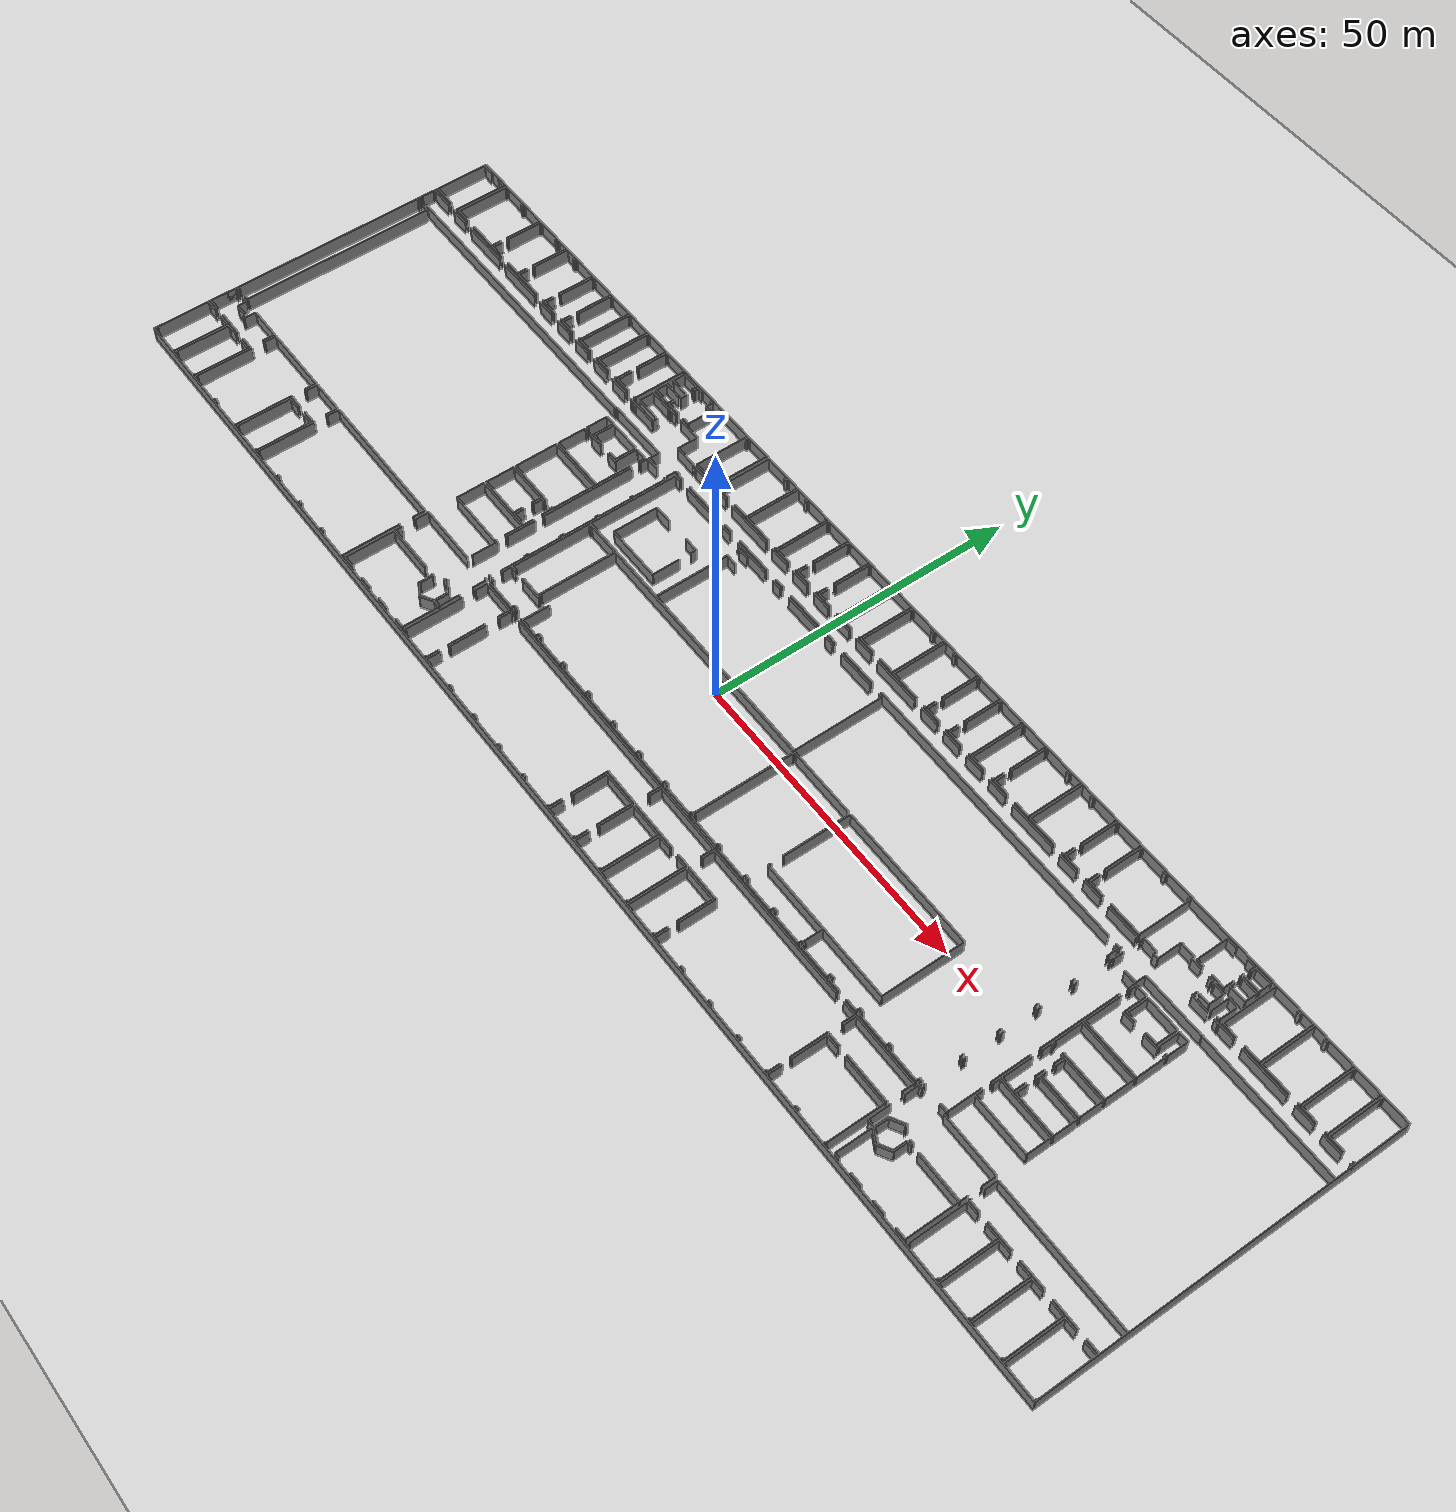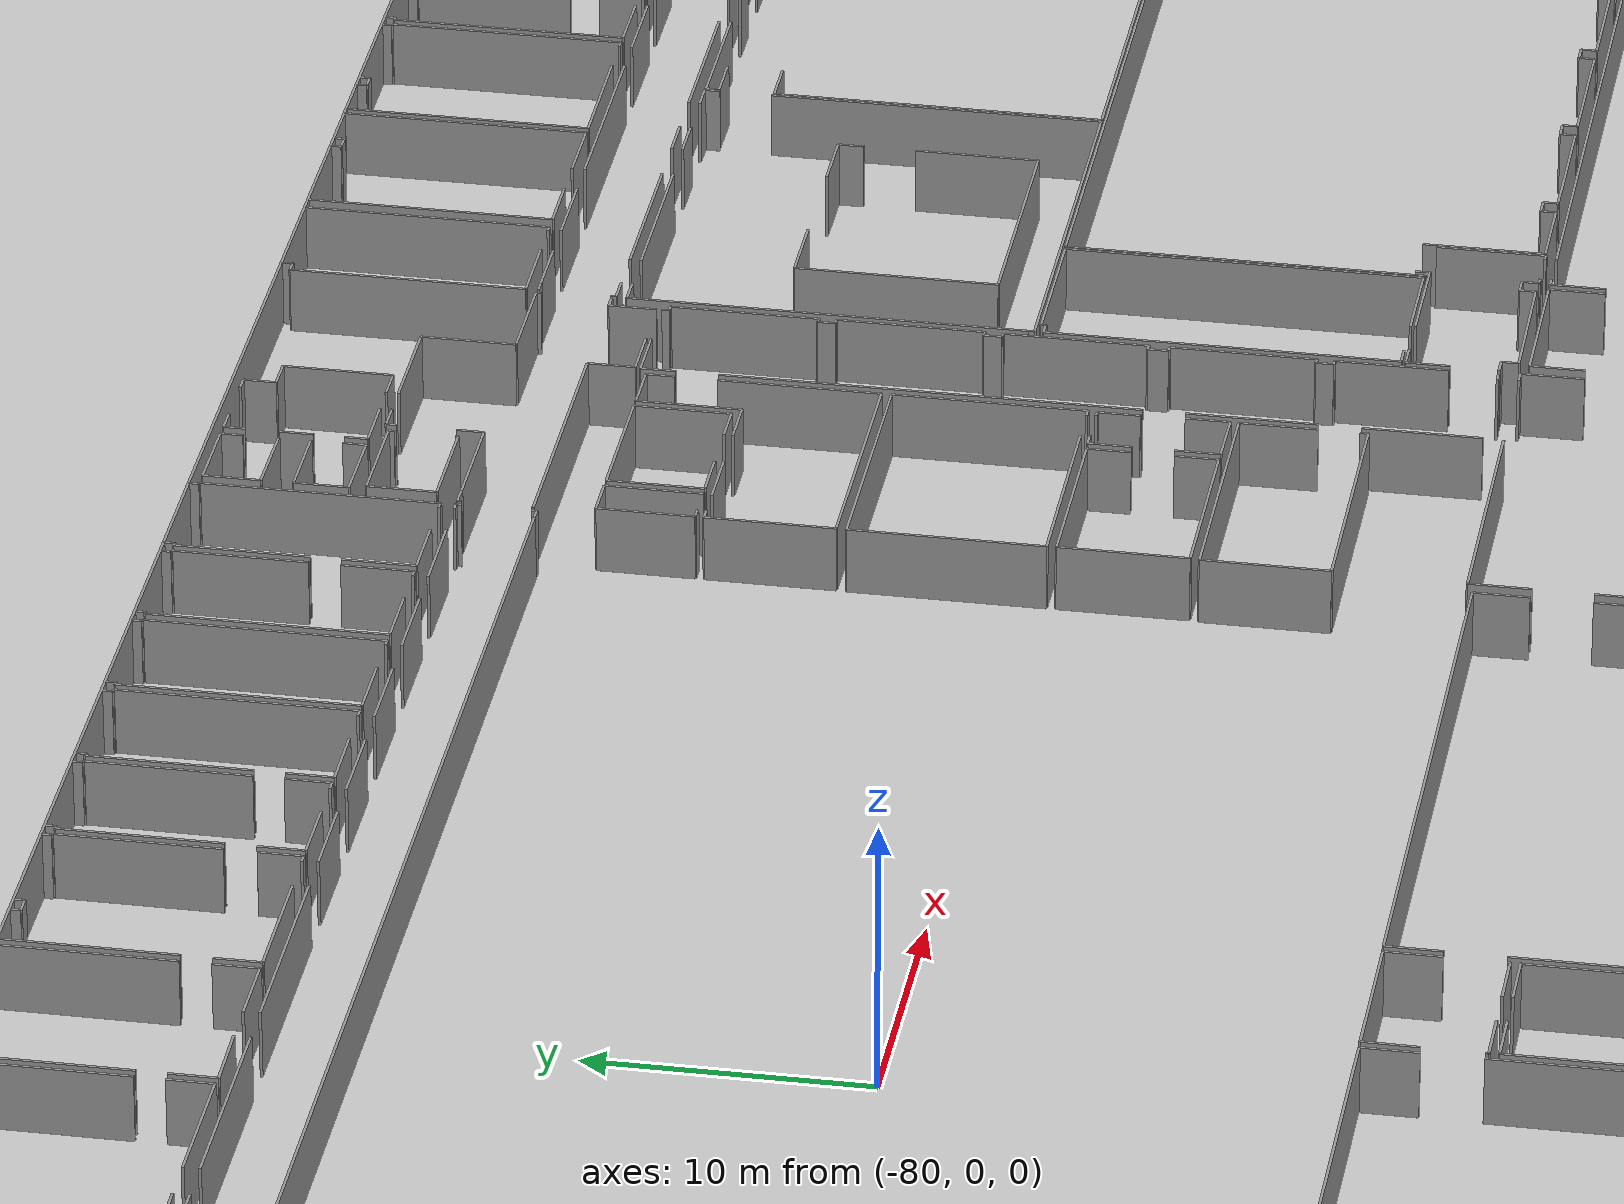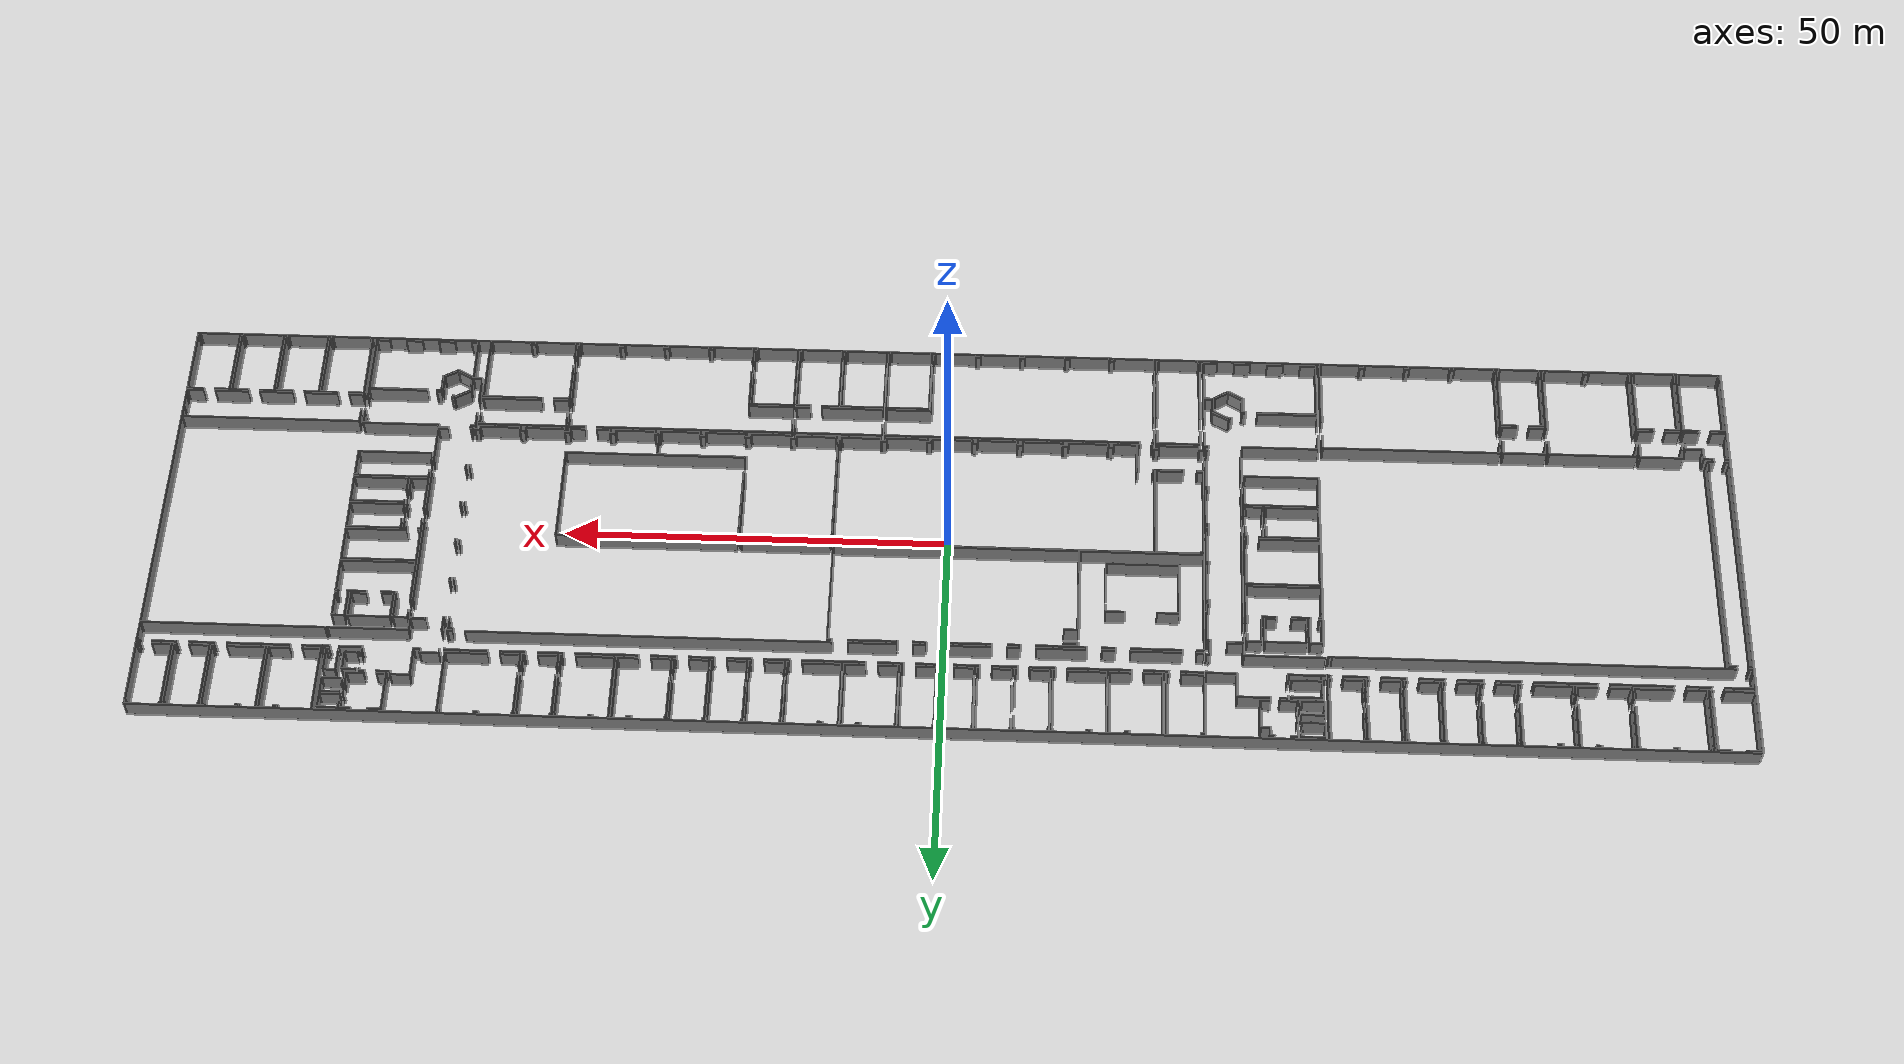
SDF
<sdf version="1.6">
  <world name="default">
    <light name="sun" type="directional">
      <cast_shadows>1</cast_shadows>
      <pose frame="">0 0 10 0 -0 0</pose>
      <diffuse>0.8 0.8 0.8 1</diffuse>
      <specular>0.1 0.1 0.1 1</specular>
      <attenuation>
        <range>1000</range>
        <constant>0.9</constant>
        <linear>0.01</linear>
        <quadratic>0.001</quadratic>
      </attenuation>
      <direction>-0.5 0.5 -1</direction>
    </light>
    <model name="ground_plane">
      <static>1</static>
      <link name="link">
        <collision name="collision">
          <geometry>
            <plane>
              <normal>0 0 1</normal>
              <size>100 100</size>
            </plane>
          </geometry>
          <surface>
            <friction>
              <ode>
                <mu>100</mu>
                <mu2>50</mu2>
              </ode>
              <torsional>
                <ode />
              </torsional>
            </friction>
            <contact>
              <ode />
            </contact>
            <bounce />
          </surface>
          <max_contacts>10</max_contacts>
        </collision>
        <visual name="visual">
          <cast_shadows>0</cast_shadows>
          <geometry>
            <plane>
              <normal>0 0 1</normal>
              <size>100 100</size>
            </plane>
          </geometry>
          <material>
            <script>
              <uri>file://media/materials/scripts/gazebo.material</uri>
              <name>Gazebo/Grey</name>
            </script>
          </material>
        </visual>
        <self_collide>0</self_collide>
        <kinematic>0</kinematic>
        <gravity>1</gravity>
      </link>
    </model>
    <gravity>0 0 -9.8</gravity>
    <magnetic_field>6e-06 2.3e-05 -4.2e-05</magnetic_field>
    <atmosphere type="adiabatic" />
    <physics default="0" name="default_physics" type="ode">
      <max_step_size>0.001</max_step_size>
      <real_time_factor>1</real_time_factor>
      <real_time_update_rate>1000</real_time_update_rate>
    </physics>
    <scene>
      <ambient>0.4 0.4 0.4 1</ambient>
      <background>0.7 0.7 0.7 1</background>
      <shadows>1</shadows>
    </scene>
    <spherical_coordinates>
      <surface_model>EARTH_WGS84</surface_model>
      <latitude_deg>0</latitude_deg>
      <longitude_deg>0</longitude_deg>
      <elevation>0</elevation>
      <heading_deg>0</heading_deg>
    </spherical_coordinates>
  <model name="50010536_PLAN3">
		<static>1</static>
		<link name="Wall_0">
			<collision name="Wall_0_Collision">
				<geometry>
					<box>
						<size>8.70365362029 0.1 2.5</size>
					</box>
				</geometry>
				<pose frame="">4.35182681015 0 1.25 0 0 0</pose>
			</collision>
			<visual name="Wall_0_Visual">
				<pose frame="">4.35182681015 0 1.25 0 0 0</pose>
				<geometry>
					<box>
						<size>8.70365362029 0.1 2.5</size>
					</box>
				</geometry>
				<material>
					<script>
						<uri>file://media/materials/scripts/gazebo.material</uri>
						<name>Gazebo/Grey</name>
					</script>
					<ambient>1 1 1 1</ambient>
				</material>
			</visual>
			<pose frame="">0.0284417357077 -8.98103672666 0 0 0 1.57079632679</pose>
		</link>
		<link name="Wall_1">
			<collision name="Wall_1_Collision">
				<geometry>
					<box>
						<size>1.99904770974 0.1 2.5</size>
					</box>
				</geometry>
				<pose frame="">0.999523854871 0 1.25 0 0 0</pose>
			</collision>
			<visual name="Wall_1_Visual">
				<pose frame="">0.999523854871 0 1.25 0 0 0</pose>
				<geometry>
					<box>
						<size>1.99904770974 0.1 2.5</size>
					</box>
				</geometry>
				<material>
					<script>
						<uri>file://media/materials/scripts/gazebo.material</uri>
						<name>Gazebo/Grey</name>
					</script>
					<ambient>1 1 1 1</ambient>
				</material>
			</visual>
			<pose frame="">0.0284417357077 -0.277383106371 0 0 0 0.0</pose>
		</link>
		<link name="Wall_2">
			<collision name="Wall_2_Collision">
				<geometry>
					<box>
						<size>1.63032092182 0.1 2.5</size>
					</box>
				</geometry>
				<pose frame="">0.815160460908 0 1.25 0 0 0</pose>
			</collision>
			<visual name="Wall_2_Visual">
				<pose frame="">0.815160460908 0 1.25 0 0 0</pose>
				<geometry>
					<box>
						<size>1.63032092182 0.1 2.5</size>
					</box>
				</geometry>
				<material>
					<script>
						<uri>file://media/materials/scripts/gazebo.material</uri>
						<name>Gazebo/Grey</name>
					</script>
					<ambient>1 1 1 1</ambient>
				</material>
			</visual>
			<pose frame="">3.9450211091 -0.277383106371 0 0 0 0.0</pose>
		</link>
		<link name="Wall_3">
			<collision name="Wall_3_Collision">
				<geometry>
					<box>
						<size>8.7084785576 0.1 2.5</size>
					</box>
				</geometry>
				<pose frame="">4.3542392788 0 1.25 0 0 0</pose>
			</collision>
			<visual name="Wall_3_Visual">
				<pose frame="">4.3542392788 0 1.25 0 0 0</pose>
				<geometry>
					<box>
						<size>8.7084785576 0.1 2.5</size>
					</box>
				</geometry>
				<material>
					<script>
						<uri>file://media/materials/scripts/gazebo.material</uri>
						<name>Gazebo/Grey</name>
					</script>
					<ambient>1 1 1 1</ambient>
				</material>
			</visual>
			<pose frame="">5.57534203092 -0.277383106371 0 0 0 -1.57079632679</pose>
		</link>
		<link name="Wall_4">
			<collision name="Wall_4_Collision">
				<geometry>
					<box>
						<size>0.234898263657 0.1 2.5</size>
					</box>
				</geometry>
				<pose frame="">0.117449131829 0 1.25 0 0 0</pose>
			</collision>
			<visual name="Wall_4_Visual">
				<pose frame="">0.117449131829 0 1.25 0 0 0</pose>
				<geometry>
					<box>
						<size>0.234898263657 0.1 2.5</size>
					</box>
				</geometry>
				<material>
					<script>
						<uri>file://media/materials/scripts/gazebo.material</uri>
						<name>Gazebo/Grey</name>
					</script>
					<ambient>1 1 1 1</ambient>
				</material>
			</visual>
			<pose frame="">5.57534203092 -8.98586166397 0 0 0 3.14159265359</pose>
		</link>
		<link name="Wall_5">
			<collision name="Wall_5_Collision">
				<geometry>
					<box>
						<size>3.88052231522 0.1 2.5</size>
					</box>
				</geometry>
				<pose frame="">1.94026115761 0 1.25 0 0 0</pose>
			</collision>
			<visual name="Wall_5_Visual">
				<pose frame="">1.94026115761 0 1.25 0 0 0</pose>
				<geometry>
					<box>
						<size>3.88052231522 0.1 2.5</size>
					</box>
				</geometry>
				<material>
					<script>
						<uri>file://media/materials/scripts/gazebo.material</uri>
						<name>Gazebo/Grey</name>
					</script>
					<ambient>1 1 1 1</ambient>
				</material>
			</visual>
			<pose frame="">3.90896105133 -8.98586166397 0 0 0 3.14034928011</pose>
		</link>
		<link name="Wall_6">
			<collision name="Wall_6_Collision">
				<geometry>
					<box>
						<size>8.59194362442 0.1 2.5</size>
					</box>
				</geometry>
				<pose frame="">4.29597181221 0 1.25 0 0 0</pose>
			</collision>
			<visual name="Wall_6_Visual">
				<pose frame="">4.29597181221 0 1.25 0 0 0</pose>
				<geometry>
					<box>
						<size>8.59194362442 0.1 2.5</size>
					</box>
				</geometry>
				<material>
					<script>
						<uri>file://media/materials/scripts/gazebo.material</uri>
						<name>Gazebo/Grey</name>
					</script>
					<ambient>1 1 1 1</ambient>
				</material>
			</visual>
			<pose frame="">6.09694314827 -8.98509983176 0 0 0 1.57079632679</pose>
		</link>
		<link name="Wall_7">
			<collision name="Wall_7_Collision">
				<geometry>
					<box>
						<size>0.1140208869 0.1 2.5</size>
					</box>
				</geometry>
				<pose frame="">0.0570104434498 0 1.25 0 0 0</pose>
			</collision>
			<visual name="Wall_7_Visual">
				<pose frame="">0.0570104434498 0 1.25 0 0 0</pose>
				<geometry>
					<box>
						<size>0.1140208869 0.1 2.5</size>
					</box>
				</geometry>
				<material>
					<script>
						<uri>file://media/materials/scripts/gazebo.material</uri>
						<name>Gazebo/Grey</name>
					</script>
					<ambient>1 1 1 1</ambient>
				</material>
			</visual>
			<pose frame="">6.09694314827 -0.393156207345 0 0 0 0.0</pose>
		</link>
		<link name="Wall_8">
			<collision name="Wall_8_Collision">
				<geometry>
					<box>
						<size>0.380408215091 0.1 2.5</size>
					</box>
				</geometry>
				<pose frame="">0.190204107545 0 1.25 0 0 0</pose>
			</collision>
			<visual name="Wall_8_Visual">
				<pose frame="">0.190204107545 0 1.25 0 0 0</pose>
				<geometry>
					<box>
						<size>0.380408215091 0.1 2.5</size>
					</box>
				</geometry>
				<material>
					<script>
						<uri>file://media/materials/scripts/gazebo.material</uri>
						<name>Gazebo/Grey</name>
					</script>
					<ambient>1 1 1 1</ambient>
				</material>
			</visual>
			<pose frame="">6.21096403517 -0.393156207345 0 0 0 1.57079632679</pose>
		</link>
		<link name="Wall_9">
			<collision name="Wall_9_Collision">
				<geometry>
					<box>
						<size>0.364435133162 0.1 2.5</size>
					</box>
				</geometry>
				<pose frame="">0.182217566581 0 1.25 0 0 0</pose>
			</collision>
			<visual name="Wall_9_Visual">
				<pose frame="">0.182217566581 0 1.25 0 0 0</pose>
				<geometry>
					<box>
						<size>0.364435133162 0.1 2.5</size>
					</box>
				</geometry>
				<material>
					<script>
						<uri>file://media/materials/scripts/gazebo.material</uri>
						<name>Gazebo/Grey</name>
					</script>
					<ambient>1 1 1 1</ambient>
				</material>
			</visual>
			<pose frame="">10.4091673809 -0.0127479922547 0 0 0 -1.57079632679</pose>
		</link>
		<link name="Wall_10">
			<collision name="Wall_10_Collision">
				<geometry>
					<box>
						<size>0.594737009174 0.1 2.5</size>
					</box>
				</geometry>
				<pose frame="">0.297368504587 0 1.25 0 0 0</pose>
			</collision>
			<visual name="Wall_10_Visual">
				<pose frame="">0.297368504587 0 1.25 0 0 0</pose>
				<geometry>
					<box>
						<size>0.594737009174 0.1 2.5</size>
					</box>
				</geometry>
				<material>
					<script>
						<uri>file://media/materials/scripts/gazebo.material</uri>
						<name>Gazebo/Grey</name>
					</script>
					<ambient>1 1 1 1</ambient>
				</material>
			</visual>
			<pose frame="">10.4091673809 -0.377183125417 0 0 0 0.0</pose>
		</link>
		<link name="Wall_11">
			<collision name="Wall_11_Collision">
				<geometry>
					<box>
						<size>0.354785258547 0.1 2.5</size>
					</box>
				</geometry>
				<pose frame="">0.177392629273 0 1.25 0 0 0</pose>
			</collision>
			<visual name="Wall_11_Visual">
				<pose frame="">0.177392629273 0 1.25 0 0 0</pose>
				<geometry>
					<box>
						<size>0.354785258547 0.1 2.5</size>
					</box>
				</geometry>
				<material>
					<script>
						<uri>file://media/materials/scripts/gazebo.material</uri>
						<name>Gazebo/Grey</name>
					</script>
					<ambient>1 1 1 1</ambient>
				</material>
			</visual>
			<pose frame="">11.0039043901 -0.377183125417 0 0 0 1.57079632679</pose>
		</link>
		<link name="Wall_12">
			<collision name="Wall_12_Collision">
				<geometry>
					<box>
						<size>0.365704853506 0.1 2.5</size>
					</box>
				</geometry>
				<pose frame="">0.182852426753 0 1.25 0 0 0</pose>
			</collision>
			<visual name="Wall_12_Visual">
				<pose frame="">0.182852426753 0 1.25 0 0 0</pose>
				<geometry>
					<box>
						<size>0.365704853506 0.1 2.5</size>
					</box>
				</geometry>
				<material>
					<script>
						<uri>file://media/materials/scripts/gazebo.material</uri>
						<name>Gazebo/Grey</name>
					</script>
					<ambient>1 1 1 1</ambient>
				</material>
			</visual>
			<pose frame="">15.2343586325 -0.0223978668698 0 0 0 -1.57079632679</pose>
		</link>
		<link name="Wall_13">
			<collision name="Wall_13_Collision">
				<geometry>
					<box>
						<size>0.0761832206457 0.1 2.5</size>
					</box>
				</geometry>
				<pose frame="">0.0380916103228 0 1.25 0 0 0</pose>
			</collision>
			<visual name="Wall_13_Visual">
				<pose frame="">0.0380916103228 0 1.25 0 0 0</pose>
				<geometry>
					<box>
						<size>0.0761832206457 0.1 2.5</size>
					</box>
				</geometry>
				<material>
					<script>
						<uri>file://media/materials/scripts/gazebo.material</uri>
						<name>Gazebo/Grey</name>
					</script>
					<ambient>1 1 1 1</ambient>
				</material>
			</visual>
			<pose frame="">15.2343586325 -0.388102720376 0 0 0 0.0</pose>
		</link>
		<link name="Wall_14">
			<collision name="Wall_14_Collision">
				<geometry>
					<box>
						<size>5.86989175634 0.1 2.5</size>
					</box>
				</geometry>
				<pose frame="">2.93494587817 0 1.25 0 0 0</pose>
			</collision>
			<visual name="Wall_14_Visual">
				<pose frame="">2.93494587817 0 1.25 0 0 0</pose>
				<geometry>
					<box>
						<size>5.86989175634 0.1 2.5</size>
					</box>
				</geometry>
				<material>
					<script>
						<uri>file://media/materials/scripts/gazebo.material</uri>
						<name>Gazebo/Grey</name>
					</script>
					<ambient>1 1 1 1</ambient>
				</material>
			</visual>
			<pose frame="">15.3105418532 -0.388102720376 0 0 0 -1.57079632679</pose>
		</link>
		<link name="Wall_15">
			<collision name="Wall_15_Collision">
				<geometry>
					<box>
						<size>1.64555756595 0.1 2.5</size>
					</box>
				</geometry>
				<pose frame="">0.822778782973 0 1.25 0 0 0</pose>
			</collision>
			<visual name="Wall_15_Visual">
				<pose frame="">0.822778782973 0 1.25 0 0 0</pose>
				<geometry>
					<box>
						<size>1.64555756595 0.1 2.5</size>
					</box>
				</geometry>
				<material>
					<script>
						<uri>file://media/materials/scripts/gazebo.material</uri>
						<name>Gazebo/Grey</name>
					</script>
					<ambient>1 1 1 1</ambient>
				</material>
			</visual>
			<pose frame="">15.3105418532 -7.31922674031 0 0 0 -1.57079632679</pose>
		</link>
		<link name="Wall_16">
			<collision name="Wall_16_Collision">
				<geometry>
					<box>
						<size>5.1129098816 0.1 2.5</size>
					</box>
				</geometry>
				<pose frame="">2.5564549408 0 1.25 0 0 0</pose>
			</collision>
			<visual name="Wall_16_Visual">
				<pose frame="">2.5564549408 0 1.25 0 0 0</pose>
				<geometry>
					<box>
						<size>5.1129098816 0.1 2.5</size>
					</box>
				</geometry>
				<material>
					<script>
						<uri>file://media/materials/scripts/gazebo.material</uri>
						<name>Gazebo/Grey</name>
					</script>
					<ambient>1 1 1 1</ambient>
				</material>
			</visual>
			<pose frame="">15.3105418532 -8.96478430626 0 0 0 3.14159265359</pose>
		</link>
		<link name="Wall_17">
			<collision name="Wall_17_Collision">
				<geometry>
					<box>
						<size>2.54104556468 0.1 2.5</size>
					</box>
				</geometry>
				<pose frame="">1.27052278234 0 1.25 0 0 0</pose>
			</collision>
			<visual name="Wall_17_Visual">
				<pose frame="">1.27052278234 0 1.25 0 0 0</pose>
				<geometry>
					<box>
						<size>2.54104556468 0.1 2.5</size>
					</box>
				</geometry>
				<material>
					<script>
						<uri>file://media/materials/scripts/gazebo.material</uri>
						<name>Gazebo/Grey</name>
					</script>
					<ambient>1 1 1 1</ambient>
				</material>
			</visual>
			<pose frame="">8.63790750087 -8.96478430626 0 0 0 -3.13359762106</pose>
		</link>
		<link name="Wall_18">
			<collision name="Wall_18_Collision">
				<geometry>
					<box>
						<size>1.70117131702 0.1 2.5</size>
					</box>
				</geometry>
				<pose frame="">0.850585658509 0 1.25 0 0 0</pose>
			</collision>
			<visual name="Wall_18_Visual">
				<pose frame="">0.850585658509 0 1.25 0 0 0</pose>
				<geometry>
					<box>
						<size>1.70117131702 0.1 2.5</size>
					</box>
				</geometry>
				<material>
					<script>
						<uri>file://media/materials/scripts/gazebo.material</uri>
						<name>Gazebo/Grey</name>
					</script>
					<ambient>1 1 1 1</ambient>
				</material>
			</visual>
			<pose frame="">15.6721582072 -9.00770085389 0 0 0 1.57079632679</pose>
		</link>
		<link name="Wall_19">
			<collision name="Wall_19_Collision">
				<geometry>
					<box>
						<size>5.8413230486 0.1 2.5</size>
					</box>
				</geometry>
				<pose frame="">2.9206615243 0 1.25 0 0 0</pose>
			</collision>
			<visual name="Wall_19_Visual">
				<pose frame="">2.9206615243 0 1.25 0 0 0</pose>
				<geometry>
					<box>
						<size>5.8413230486 0.1 2.5</size>
					</box>
				</geometry>
				<material>
					<script>
						<uri>file://media/materials/scripts/gazebo.material</uri>
						<name>Gazebo/Grey</name>
					</script>
					<ambient>1 1 1 1</ambient>
				</material>
			</visual>
			<pose frame="">15.6721582072 -6.24580516141 0 0 0 1.57079632679</pose>
		</link>
		<link name="Wall_20">
			<collision name="Wall_20_Collision">
				<geometry>
					<box>
						<size>0.119861600482 0.1 2.5</size>
					</box>
				</geometry>
				<pose frame="">0.0599308002412 0 1.25 0 0 0</pose>
			</collision>
			<visual name="Wall_20_Visual">
				<pose frame="">0.0599308002412 0 1.25 0 0 0</pose>
				<geometry>
					<box>
						<size>0.119861600482 0.1 2.5</size>
					</box>
				</geometry>
				<material>
					<script>
						<uri>file://media/materials/scripts/gazebo.material</uri>
						<name>Gazebo/Grey</name>
					</script>
					<ambient>1 1 1 1</ambient>
				</material>
			</visual>
			<pose frame="">15.6721582072 -0.404482112815 0 0 0 0.0</pose>
		</link>
		<link name="Wall_21">
			<collision name="Wall_21_Collision">
				<geometry>
					<box>
						<size>0.374973812018 0.1 2.5</size>
					</box>
				</geometry>
				<pose frame="">0.187486906009 0 1.25 0 0 0</pose>
			</collision>
			<visual name="Wall_21_Visual">
				<pose frame="">0.187486906009 0 1.25 0 0 0</pose>
				<geometry>
					<box>
						<size>0.374973812018 0.1 2.5</size>
					</box>
				</geometry>
				<material>
					<script>
						<uri>file://media/materials/scripts/gazebo.material</uri>
						<name>Gazebo/Grey</name>
					</script>
					<ambient>1 1 1 1</ambient>
				</material>
			</visual>
			<pose frame="">15.7920198076 -0.404482112815 0 0 0 1.57079632679</pose>
		</link>
		<link name="Wall_22">
			<collision name="Wall_22_Collision">
				<geometry>
					<box>
						<size>0.346481287496 0.1 2.5</size>
					</box>
				</geometry>
				<pose frame="">0.173240643748 0 1.25 0 0 0</pose>
			</collision>
			<visual name="Wall_22_Visual">
				<pose frame="">0.173240643748 0 1.25 0 0 0</pose>
				<geometry>
					<box>
						<size>0.346481287496 0.1 2.5</size>
					</box>
				</geometry>
				<material>
					<script>
						<uri>file://media/materials/scripts/gazebo.material</uri>
						<name>Gazebo/Grey</name>
					</script>
					<ambient>1 1 1 1</ambient>
				</material>
			</visual>
			<pose frame="">19.9782877821 -0.0295083007967 0 0 0 -1.57079632679</pose>
		</link>
		<link name="Wall_23">
			<collision name="Wall_23_Collision">
				<geometry>
					<box>
						<size>0.612259149922 0.1 2.5</size>
					</box>
				</geometry>
				<pose frame="">0.306129574961 0 1.25 0 0 0</pose>
			</collision>
			<visual name="Wall_23_Visual">
				<pose frame="">0.306129574961 0 1.25 0 0 0</pose>
				<geometry>
					<box>
						<size>0.612259149922 0.1 2.5</size>
					</box>
				</geometry>
				<material>
					<script>
						<uri>file://media/materials/scripts/gazebo.material</uri>
						<name>Gazebo/Grey</name>
					</script>
					<ambient>1 1 1 1</ambient>
				</material>
			</visual>
			<pose frame="">19.9782877821 -0.375989588293 0 0 0 0.0</pose>
		</link>
		<link name="Wall_24">
			<collision name="Wall_24_Collision">
				<geometry>
					<box>
						<size>0.35597879567 0.1 2.5</size>
					</box>
				</geometry>
				<pose frame="">0.177989397835 0 1.25 0 0 0</pose>
			</collision>
			<visual name="Wall_24_Visual">
				<pose frame="">0.177989397835 0 1.25 0 0 0</pose>
				<geometry>
					<box>
						<size>0.35597879567 0.1 2.5</size>
					</box>
				</geometry>
				<material>
					<script>
						<uri>file://media/materials/scripts/gazebo.material</uri>
						<name>Gazebo/Grey</name>
					</script>
					<ambient>1 1 1 1</ambient>
				</material>
			</visual>
			<pose frame="">20.590546932 -0.375989588293 0 0 0 1.57079632679</pose>
		</link>
		<link name="Wall_25">
			<collision name="Wall_25_Collision">
				<geometry>
					<box>
						<size>6.22681014507 0.1 2.5</size>
					</box>
				</geometry>
				<pose frame="">3.11340507253 0 1.25 0 0 0</pose>
			</collision>
			<visual name="Wall_25_Visual">
				<pose frame="">3.11340507253 0 1.25 0 0 0</pose>
				<geometry>
					<box>
						<size>6.22681014507 0.1 2.5</size>
					</box>
				</geometry>
				<material>
					<script>
						<uri>file://media/materials/scripts/gazebo.material</uri>
						<name>Gazebo/Grey</name>
					</script>
					<ambient>1 1 1 1</ambient>
				</material>
			</visual>
			<pose frame="">22.5101101482 -0.0200107926229 0 0 0 -1.57079632679</pose>
		</link>
		<link name="Wall_26">
			<collision name="Wall_26_Collision">
				<geometry>
					<box>
						<size>1.61965527093 0.1 2.5</size>
					</box>
				</geometry>
				<pose frame="">0.809827635463 0 1.25 0 0 0</pose>
			</collision>
			<visual name="Wall_26_Visual">
				<pose frame="">0.809827635463 0 1.25 0 0 0</pose>
				<geometry>
					<box>
						<size>1.61965527093 0.1 2.5</size>
					</box>
				</geometry>
				<material>
					<script>
						<uri>file://media/materials/scripts/gazebo.material</uri>
						<name>Gazebo/Grey</name>
					</script>
					<ambient>1 1 1 1</ambient>
				</material>
			</visual>
			<pose frame="">22.5101101482 -7.35046186078 0 0 0 -1.57079632679</pose>
		</link>
		<link name="Wall_27">
			<collision name="Wall_27_Collision">
				<geometry>
					<box>
						<size>2.74513538393 0.1 2.5</size>
					</box>
				</geometry>
				<pose frame="">1.37256769197 0 1.25 0 0 0</pose>
			</collision>
			<visual name="Wall_27_Visual">
				<pose frame="">1.37256769197 0 1.25 0 0 0</pose>
				<geometry>
					<box>
						<size>2.74513538393 0.1 2.5</size>
					</box>
				</geometry>
				<material>
					<script>
						<uri>file://media/materials/scripts/gazebo.material</uri>
						<name>Gazebo/Grey</name>
					</script>
					<ambient>1 1 1 1</ambient>
				</material>
			</visual>
			<pose frame="">22.5101101482 -8.9701171317 0 0 0 3.14159265359</pose>
		</link>
		<link name="Wall_28">
			<collision name="Wall_28_Collision">
				<geometry>
					<box>
						<size>2.6026901922 0.1 2.5</size>
					</box>
				</geometry>
				<pose frame="">1.3013450961 0 1.25 0 0 0</pose>
			</collision>
			<visual name="Wall_28_Visual">
				<pose frame="">1.3013450961 0 1.25 0 0 0</pose>
				<geometry>
					<box>
						<size>2.6026901922 0.1 2.5</size>
					</box>
				</geometry>
				<material>
					<script>
						<uri>file://media/materials/scripts/gazebo.material</uri>
						<name>Gazebo/Grey</name>
					</script>
					<ambient>1 1 1 1</ambient>
				</material>
			</visual>
			<pose frame="">18.2745770244 -8.9701171317 0 0 0 -3.12715181518</pose>
		</link>
		<link name="Wall_29">
			<collision name="Wall_29_Collision">
				<geometry>
					<box>
						<size>1.68237945592 0.1 2.5</size>
					</box>
				</geometry>
				<pose frame="">0.841189727962 0 1.25 0 0 0</pose>
			</collision>
			<visual name="Wall_29_Visual">
				<pose frame="">0.841189727962 0 1.25 0 0 0</pose>
				<geometry>
					<box>
						<size>1.68237945592 0.1 2.5</size>
					</box>
				</geometry>
				<material>
					<script>
						<uri>file://media/materials/scripts/gazebo.material</uri>
						<name>Gazebo/Grey</name>
					</script>
					<ambient>1 1 1 1</ambient>
				</material>
			</visual>
			<pose frame="">22.8846776497 -8.98890899279 0 0 0 1.57079632679</pose>
		</link>
		<link name="Wall_30">
			<collision name="Wall_30_Collision">
				<geometry>
					<box>
						<size>6.18871853474 0.1 2.5</size>
					</box>
				</geometry>
				<pose frame="">3.09435926737 0 1.25 0 0 0</pose>
			</collision>
			<visual name="Wall_30_Visual">
				<pose frame="">3.09435926737 0 1.25 0 0 0</pose>
				<geometry>
					<box>
						<size>6.18871853474 0.1 2.5</size>
					</box>
				</geometry>
				<material>
					<script>
						<uri>file://media/materials/scripts/gazebo.material</uri>
						<name>Gazebo/Grey</name>
					</script>
					<ambient>1 1 1 1</ambient>
				</material>
			</visual>
			<pose frame="">22.8846776497 -6.21761736977 0 0 0 1.57079632679</pose>
		</link>
		<link name="Wall_31">
			<collision name="Wall_31_Collision">
				<geometry>
					<box>
						<size>0.363190807225 0.1 2.5</size>
					</box>
				</geometry>
				<pose frame="">0.181595403612 0 1.25 0 0 0</pose>
			</collision>
			<visual name="Wall_31_Visual">
				<pose frame="">0.181595403612 0 1.25 0 0 0</pose>
				<geometry>
					<box>
						<size>0.363190807225 0.1 2.5</size>
					</box>
				</geometry>
				<material>
					<script>
						<uri>file://media/materials/scripts/gazebo.material</uri>
						<name>Gazebo/Grey</name>
					</script>
					<ambient>1 1 1 1</ambient>
				</material>
			</visual>
			<pose frame="">24.7714820811 -0.0288988350316 0 0 0 -1.57079632679</pose>
		</link>
		<link name="Wall_32">
			<collision name="Wall_32_Collision">
				<geometry>
					<box>
						<size>0.635622004254 0.1 2.5</size>
					</box>
				</geometry>
				<pose frame="">0.317811002127 0 1.25 0 0 0</pose>
			</collision>
			<visual name="Wall_32_Visual">
				<pose frame="">0.317811002127 0 1.25 0 0 0</pose>
				<geometry>
					<box>
						<size>0.635622004254 0.1 2.5</size>
					</box>
				</geometry>
				<material>
					<script>
						<uri>file://media/materials/scripts/gazebo.material</uri>
						<name>Gazebo/Grey</name>
					</script>
					<ambient>1 1 1 1</ambient>
				</material>
			</visual>
			<pose frame="">24.7714820811 -0.392089642256 0 0 0 0.0</pose>
		</link>
		<link name="Wall_33">
			<collision name="Wall_33_Collision">
				<geometry>
					<box>
						<size>0.35907691331 0.1 2.5</size>
					</box>
				</geometry>
				<pose frame="">0.179538456655 0 1.25 0 0 0</pose>
			</collision>
			<visual name="Wall_33_Visual">
				<pose frame="">0.179538456655 0 1.25 0 0 0</pose>
				<geometry>
					<box>
						<size>0.35907691331 0.1 2.5</size>
					</box>
				</geometry>
				<material>
					<script>
						<uri>file://media/materials/scripts/gazebo.material</uri>
						<name>Gazebo/Grey</name>
					</script>
					<ambient>1 1 1 1</ambient>
				</material>
			</visual>
			<pose frame="">25.4071040853 -0.392089642256 0 0 0 1.57079632679</pose>
		</link>
		<link name="Wall_34">
			<collision name="Wall_34_Collision">
				<geometry>
					<box>
						<size>0.34417039647 0.1 2.5</size>
					</box>
				</geometry>
				<pose frame="">0.172085198235 0 1.25 0 0 0</pose>
			</collision>
			<visual name="Wall_34_Visual">
				<pose frame="">0.172085198235 0 1.25 0 0 0</pose>
				<geometry>
					<box>
						<size>0.34417039647 0.1 2.5</size>
					</box>
				</geometry>
				<material>
					<script>
						<uri>file://media/materials/scripts/gazebo.material</uri>
						<name>Gazebo/Grey</name>
					</script>
					<ambient>1 1 1 1</ambient>
				</material>
			</visual>
			<pose frame="">29.6225756277 -0.0330127289464 0 0 0 -1.57079632679</pose>
		</link>
		<link name="Wall_35">
			<collision name="Wall_35_Collision">
				<geometry>
					<box>
						<size>0.0817699901597 0.1 2.5</size>
					</box>
				</geometry>
				<pose frame="">0.0408849950798 0 1.25 0 0 0</pose>
			</collision>
			<visual name="Wall_35_Visual">
				<pose frame="">0.0408849950798 0 1.25 0 0 0</pose>
				<geometry>
					<box>
						<size>0.0817699901597 0.1 2.5</size>
					</box>
				</geometry>
				<material>
					<script>
						<uri>file://media/materials/scripts/gazebo.material</uri>
						<name>Gazebo/Grey</name>
					</script>
					<ambient>1 1 1 1</ambient>
				</material>
			</visual>
			<pose frame="">29.6225756277 -0.377183125417 0 0 0 0.0</pose>
		</link>
		<link name="Wall_36">
			<collision name="Wall_36_Collision">
				<geometry>
					<box>
						<size>5.86278132241 0.1 2.5</size>
					</box>
				</geometry>
				<pose frame="">2.93139066121 0 1.25 0 0 0</pose>
			</collision>
			<visual name="Wall_36_Visual">
				<pose frame="">2.93139066121 0 1.25 0 0 0</pose>
				<geometry>
					<box>
						<size>5.86278132241 0.1 2.5</size>
					</box>
				</geometry>
				<material>
					<script>
						<uri>file://media/materials/scripts/gazebo.material</uri>
						<name>Gazebo/Grey</name>
					</script>
					<ambient>1 1 1 1</ambient>
				</material>
			</visual>
			<pose frame="">29.7043456179 -0.377183125417 0 0 0 -1.57079632679</pose>
		</link>
		<link name="Wall_37">
			<collision name="Wall_37_Collision">
				<geometry>
					<box>
						<size>1.58867409453 0.1 2.5</size>
					</box>
				</geometry>
				<pose frame="">0.794337047265 0 1.25 0 0 0</pose>
			</collision>
			<visual name="Wall_37_Visual">
				<pose frame="">0.794337047265 0 1.25 0 0 0</pose>
				<geometry>
					<box>
						<size>1.58867409453 0.1 2.5</size>
					</box>
				</geometry>
				<material>
					<script>
						<uri>file://media/materials/scripts/gazebo.material</uri>
						<name>Gazebo/Grey</name>
					</script>
					<ambient>1 1 1 1</ambient>
				</material>
			</visual>
			<pose frame="">29.7043456179 -7.39388629654 0 0 0 -1.57079632679</pose>
		</link>
		<link name="Wall_38">
			<collision name="Wall_38_Collision">
				<geometry>
					<box>
						<size>0.329111513189 0.1 2.5</size>
					</box>
				</geometry>
				<pose frame="">0.164555756595 0 1.25 0 0 0</pose>
			</collision>
			<visual name="Wall_38_Visual">
				<pose frame="">0.164555756595 0 1.25 0 0 0</pose>
				<geometry>
					<box>
						<size>0.329111513189 0.1 2.5</size>
					</box>
				</geometry>
				<material>
					<script>
						<uri>file://media/materials/scripts/gazebo.material</uri>
						<name>Gazebo/Grey</name>
					</script>
					<ambient>1 1 1 1</ambient>
				</material>
			</visual>
			<pose frame="">29.7043456179 -8.98256039107 0 0 0 3.14159265359</pose>
		</link>
		<link name="Wall_39">
			<collision name="Wall_39_Collision">
				<geometry>
					<box>
						<size>4.90391802241 0.1 2.5</size>
					</box>
				</geometry>
				<pose frame="">2.4519590112 0 1.25 0 0 0</pose>
			</collision>
			<visual name="Wall_39_Visual">
				<pose frame="">2.4519590112 0 1.25 0 0 0</pose>
				<geometry>
					<box>
						<size>4.90391802241 0.1 2.5</size>
					</box>
				</geometry>
				<material>
					<script>
						<uri>file://media/materials/scripts/gazebo.material</uri>
						<name>Gazebo/Grey</name>
					</script>
					<ambient>1 1 1 1</ambient>
				</material>
			</visual>
			<pose frame="">27.7885915627 -8.98256039107 0 0 0 -3.14029805538</pose>
		</link>
		<link name="Wall_40">
			<collision name="Wall_40_Collision">
				<geometry>
					<box>
						<size>1.66460337111 0.1 2.5</size>
					</box>
				</geometry>
				<pose frame="">0.832301685554 0 1.25 0 0 0</pose>
			</collision>
			<visual name="Wall_40_Visual">
				<pose frame="">0.832301685554 0 1.25 0 0 0</pose>
				<geometry>
					<box>
						<size>1.66460337111 0.1 2.5</size>
					</box>
				</geometry>
				<material>
					<script>
						<uri>file://media/materials/scripts/gazebo.material</uri>
						<name>Gazebo/Grey</name>
					</script>
					<ambient>1 1 1 1</ambient>
				</material>
			</visual>
			<pose frame="">30.0624067549 -8.9774815097 0 0 0 1.57079632679</pose>
		</link>
		<link name="Wall_41">
			<collision name="Wall_41_Collision">
				<geometry>
					<box>
						<size>5.81397327239 0.1 2.5</size>
					</box>
				</geometry>
				<pose frame="">2.90698663619 0 1.25 0 0 0</pose>
			</collision>
			<visual name="Wall_41_Visual">
				<pose frame="">2.90698663619 0 1.25 0 0 0</pose>
				<geometry>
					<box>
						<size>5.81397327239 0.1 2.5</size>
					</box>
				</geometry>
				<material>
					<script>
						<uri>file://media/materials/scripts/gazebo.material</uri>
						<name>Gazebo/Grey</name>
					</script>
					<ambient>1 1 1 1</ambient>
				</material>
			</visual>
			<pose frame="">30.0624067549 -6.21431609688 0 0 0 1.57079632679</pose>
		</link>
		<link name="Wall_42">
			<collision name="Wall_42_Collision">
				<geometry>
					<box>
						<size>0.144748119227 0.1 2.5</size>
					</box>
				</geometry>
				<pose frame="">0.0723740596134 0 1.25 0 0 0</pose>
			</collision>
			<visual name="Wall_42_Visual">
				<pose frame="">0.0723740596134 0 1.25 0 0 0</pose>
				<geometry>
					<box>
						<size>0.144748119227 0.1 2.5</size>
					</box>
				</geometry>
				<material>
					<script>
						<uri>file://media/materials/scripts/gazebo.material</uri>
						<name>Gazebo/Grey</name>
					</script>
					<ambient>1 1 1 1</ambient>
				</material>
			</visual>
			<pose frame="">30.0624067549 -0.400342824493 0 0 0 0.0</pose>
		</link>
		<link name="Wall_43">
			<collision name="Wall_43_Collision">
				<geometry>
					<box>
						<size>0.363190807225 0.1 2.5</size>
					</box>
				</geometry>
				<pose frame="">0.181595403612 0 1.25 0 0 0</pose>
			</collision>
			<visual name="Wall_43_Visual">
				<pose frame="">0.181595403612 0 1.25 0 0 0</pose>
				<geometry>
					<box>
						<size>0.363190807225 0.1 2.5</size>
					</box>
				</geometry>
				<material>
					<script>
						<uri>file://media/materials/scripts/gazebo.material</uri>
						<name>Gazebo/Grey</name>
					</script>
					<ambient>1 1 1 1</ambient>
				</material>
			</visual>
			<pose frame="">30.2071548741 -0.400342824493 0 0 0 1.57079632679</pose>
		</link>
		<link name="Wall_44">
			<collision name="Wall_44_Collision">
				<geometry>
					<box>
						<size>0.356004190077 0.1 2.5</size>
					</box>
				</geometry>
				<pose frame="">0.178002095039 0 1.25 0 0 0</pose>
			</collision>
			<visual name="Wall_44_Visual">
				<pose frame="">0.178002095039 0 1.25 0 0 0</pose>
				<geometry>
					<box>
						<size>0.356004190077 0.1 2.5</size>
					</box>
				</geometry>
				<material>
					<script>
						<uri>file://media/materials/scripts/gazebo.material</uri>
						<name>Gazebo/Grey</name>
					</script>
					<ambient>1 1 1 1</ambient>
				</material>
			</visual>
			<pose frame="">34.4157699267 -0.0371520172682 0 0 0 -1.57079632679</pose>
		</link>
		<link name="Wall_45">
			<collision name="Wall_45_Collision">
				<geometry>
					<box>
						<size>0.0904040884995 0.1 2.5</size>
					</box>
				</geometry>
				<pose frame="">0.0452020442498 0 1.25 0 0 0</pose>
			</collision>
			<visual name="Wall_45_Visual">
				<pose frame="">0.0452020442498 0 1.25 0 0 0</pose>
				<geometry>
					<box>
						<size>0.0904040884995 0.1 2.5</size>
					</box>
				</geometry>
				<material>
					<script>
						<uri>file://media/materials/scripts/gazebo.material</uri>
						<name>Gazebo/Grey</name>
					</script>
					<ambient>1 1 1 1</ambient>
				</material>
			</visual>
			<pose frame="">34.4157699267 -0.393156207345 0 0 0 0.0</pose>
		</link>
		<link name="Wall_46">
			<collision name="Wall_46_Collision">
				<geometry>
					<box>
						<size>5.86356854903 0.1 2.5</size>
					</box>
				</geometry>
				<pose frame="">2.93178427451 0 1.25 0 0 0</pose>
			</collision>
			<visual name="Wall_46_Visual">
				<pose frame="">2.93178427451 0 1.25 0 0 0</pose>
				<geometry>
					<box>
						<size>5.86356854903 0.1 2.5</size>
					</box>
				</geometry>
				<material>
					<script>
						<uri>file://media/materials/scripts/gazebo.material</uri>
						<name>Gazebo/Grey</name>
					</script>
					<ambient>1 1 1 1</ambient>
				</material>
			</visual>
			<pose frame="">34.5061740152 -0.393156207345 0 0 0 -1.57079632679</pose>
		</link>
		<link name="Wall_47">
			<collision name="Wall_47_Collision">
				<geometry>
					<box>
						<size>1.6516522236 0.1 2.5</size>
					</box>
				</geometry>
				<pose frame="">0.825826111799 0 1.25 0 0 0</pose>
			</collision>
			<visual name="Wall_47_Visual">
				<pose frame="">0.825826111799 0 1.25 0 0 0</pose>
				<geometry>
					<box>
						<size>1.6516522236 0.1 2.5</size>
					</box>
				</geometry>
				<material>
					<script>
						<uri>file://media/materials/scripts/gazebo.material</uri>
						<name>Gazebo/Grey</name>
					</script>
					<ambient>1 1 1 1</ambient>
				</material>
			</visual>
			<pose frame="">34.5061740152 -7.32938450306 0 0 0 -1.57079632679</pose>
		</link>
		<link name="Wall_48">
			<collision name="Wall_48_Collision">
				<geometry>
					<box>
						<size>0.365679459099 0.1 2.5</size>
					</box>
				</geometry>
				<pose frame="">0.18283972955 0 1.25 0 0 0</pose>
			</collision>
			<visual name="Wall_48_Visual">
				<pose frame="">0.18283972955 0 1.25 0 0 0</pose>
				<geometry>
					<box>
						<size>0.365679459099 0.1 2.5</size>
					</box>
				</geometry>
				<material>
					<script>
						<uri>file://media/materials/scripts/gazebo.material</uri>
						<name>Gazebo/Grey</name>
					</script>
					<ambient>1 1 1 1</ambient>
				</material>
			</visual>
			<pose frame="">34.5061740152 -8.98103672666 0 0 0 3.14159265359</pose>
		</link>
		<link name="Wall_49">
			<collision name="Wall_49_Collision">
				<geometry>
					<box>
						<size>2.56382178378 0.1 2.5</size>
					</box>
				</geometry>
				<pose frame="">1.28191089189 0 1.25 0 0 0</pose>
			</collision>
			<visual name="Wall_49_Visual">
				<pose frame="">1.28191089189 0 1.25 0 0 0</pose>
				<geometry>
					<box>
						<size>2.56382178378 0.1 2.5</size>
					</box>
				</geometry>
				<material>
					<script>
						<uri>file://media/materials/scripts/gazebo.material</uri>
						<name>Gazebo/Grey</name>
					</script>
					<ambient>1 1 1 1</ambient>
				</material>
			</visual>
			<pose frame="">32.6262260737 -8.98103672666 0 0 0 3.14020596668</pose>
		</link>
		<link name="Wall_50">
			<collision name="Wall_50_Collision">
				<geometry>
					<box>
						<size>1.69228327461 0.1 2.5</size>
					</box>
				</geometry>
				<pose frame="">0.846141637304 0 1.25 0 0 0</pose>
			</collision>
			<visual name="Wall_50_Visual">
				<pose frame="">0.846141637304 0 1.25 0 0 0</pose>
				<geometry>
					<box>
						<size>1.69228327461 0.1 2.5</size>
					</box>
				</geometry>
				<material>
					<script>
						<uri>file://media/materials/scripts/gazebo.material</uri>
						<name>Gazebo/Grey</name>
					</script>
					<ambient>1 1 1 1</ambient>
				</material>
			</visual>
			<pose frame="">34.8680443132 -8.99601942672 0 0 0 1.57079632679</pose>
		</link>
		<link name="Wall_51">
			<collision name="Wall_51_Collision">
				<geometry>
					<box>
						<size>5.8442687998 0.1 2.5</size>
					</box>
				</geometry>
				<pose frame="">2.9221343999 0 1.25 0 0 0</pose>
			</collision>
			<visual name="Wall_51_Visual">
				<pose frame="">2.9221343999 0 1.25 0 0 0</pose>
				<geometry>
					<box>
						<size>5.8442687998 0.1 2.5</size>
					</box>
				</geometry>
				<material>
					<script>
						<uri>file://media/materials/scripts/gazebo.material</uri>
						<name>Gazebo/Grey</name>
					</script>
					<ambient>1 1 1 1</ambient>
				</material>
			</visual>
			<pose frame="">34.8680443132 -6.22396597149 0 0 0 1.57079632679</pose>
		</link>
		<link name="Wall_52">
			<collision name="Wall_52_Collision">
				<geometry>
					<box>
						<size>0.118591880138 0.1 2.5</size>
					</box>
				</geometry>
				<pose frame="">0.0592959400692 0 1.25 0 0 0</pose>
			</collision>
			<visual name="Wall_52_Visual">
				<pose frame="">0.0592959400692 0 1.25 0 0 0</pose>
				<geometry>
					<box>
						<size>0.118591880138 0.1 2.5</size>
					</box>
				</geometry>
				<material>
					<script>
						<uri>file://media/materials/scripts/gazebo.material</uri>
						<name>Gazebo/Grey</name>
					</script>
					<ambient>1 1 1 1</ambient>
				</material>
			</visual>
			<pose frame="">34.8680443132 -0.379697171698 0 0 0 0.0</pose>
		</link>
		<link name="Wall_53">
			<collision name="Wall_53_Collision">
				<geometry>
					<box>
						<size>0.346684442751 0.1 2.5</size>
					</box>
				</geometry>
				<pose frame="">0.173342221376 0 1.25 0 0 0</pose>
			</collision>
			<visual name="Wall_53_Visual">
				<pose frame="">0.173342221376 0 1.25 0 0 0</pose>
				<geometry>
					<box>
						<size>0.346684442751 0.1 2.5</size>
					</box>
				</geometry>
				<material>
					<script>
						<uri>file://media/materials/scripts/gazebo.material</uri>
						<name>Gazebo/Grey</name>
					</script>
					<ambient>1 1 1 1</ambient>
				</material>
			</visual>
			<pose frame="">34.9866361934 -0.379697171698 0 0 0 1.57079632679</pose>
		</link>
		<link name="Wall_54">
			<collision name="Wall_54_Collision">
				<geometry>
					<box>
						<size>0.354937624988 0.1 2.5</size>
					</box>
				</geometry>
				<pose frame="">0.177468812494 0 1.25 0 0 0</pose>
			</collision>
			<visual name="Wall_54_Visual">
				<pose frame="">0.177468812494 0 1.25 0 0 0</pose>
				<geometry>
					<box>
						<size>0.354937624988 0.1 2.5</size>
					</box>
				</geometry>
				<material>
					<script>
						<uri>file://media/materials/scripts/gazebo.material</uri>
						<name>Gazebo/Grey</name>
					</script>
					<ambient>1 1 1 1</ambient>
				</material>
			</visual>
			<pose frame="">39.1840777069 -0.0330127289464 0 0 0 -1.57079632679</pose>
		</link>
		<link name="Wall_55">
			<collision name="Wall_55_Collision">
				<geometry>
					<box>
						<size>0.127987810685 0.1 2.5</size>
					</box>
				</geometry>
				<pose frame="">0.0639939053424 0 1.25 0 0 0</pose>
			</collision>
			<visual name="Wall_55_Visual">
				<pose frame="">0.0639939053424 0 1.25 0 0 0</pose>
				<geometry>
					<box>
						<size>0.127987810685 0.1 2.5</size>
					</box>
				</geometry>
				<material>
					<script>
						<uri>file://media/materials/scripts/gazebo.material</uri>
						<name>Gazebo/Grey</name>
					</script>
					<ambient>1 1 1 1</ambient>
				</material>
			</visual>
			<pose frame="">39.1840777069 -0.387950353935 0 0 0 0.0</pose>
		</link>
		<link name="Wall_56">
			<collision name="Wall_56_Collision">
				<geometry>
					<box>
						<size>8.58902326763 0.1 2.5</size>
					</box>
				</geometry>
				<pose frame="">4.29451163381 0 1.25 0 0 0</pose>
			</collision>
			<visual name="Wall_56_Visual">
				<pose frame="">4.29451163381 0 1.25 0 0 0</pose>
				<geometry>
					<box>
						<size>8.58902326763 0.1 2.5</size>
					</box>
				</geometry>
				<material>
					<script>
						<uri>file://media/materials/scripts/gazebo.material</uri>
						<name>Gazebo/Grey</name>
					</script>
					<ambient>1 1 1 1</ambient>
				</material>
			</visual>
			<pose frame="">39.3120655176 -0.387950353935 0 0 0 -1.57079632679</pose>
		</link>
		<link name="Wall_57">
			<collision name="Wall_57_Collision">
				<geometry>
					<box>
						<size>0.342570548837 0.1 2.5</size>
					</box>
				</geometry>
				<pose frame="">0.171285274418 0 1.25 0 0 0</pose>
			</collision>
			<visual name="Wall_57_Visual">
				<pose frame="">0.171285274418 0 1.25 0 0 0</pose>
				<geometry>
					<box>
						<size>0.342570548837 0.1 2.5</size>
					</box>
				</geometry>
				<material>
					<script>
						<uri>file://media/materials/scripts/gazebo.material</uri>
						<name>Gazebo/Grey</name>
					</script>
					<ambient>1 1 1 1</ambient>
				</material>
			</visual>
			<pose frame="">39.3120655176 -8.97697362156 0 0 0 3.14159265359</pose>
		</link>
		<link name="Wall_58">
			<collision name="Wall_58_Collision">
				<geometry>
					<box>
						<size>2.59487039224 0.1 2.5</size>
					</box>
				</geometry>
				<pose frame="">1.29743519612 0 1.25 0 0 0</pose>
			</collision>
			<visual name="Wall_58_Visual">
				<pose frame="">1.29743519612 0 1.25 0 0 0</pose>
				<geometry>
					<box>
						<size>2.59487039224 0.1 2.5</size>
					</box>
				</geometry>
				<material>
					<script>
						<uri>file://media/materials/scripts/gazebo.material</uri>
						<name>Gazebo/Grey</name>
					</script>
					<ambient>1 1 1 1</ambient>
				</material>
			</visual>
			<pose frame="">37.4628448084 -8.97697362156 0 0 0 -3.13425279714</pose>
		</link>
		<link name="Wall_59">
			<collision name="Wall_59_Collision">
				<geometry>
					<box>
						<size>8.59250230137 0.1 2.5</size>
					</box>
				</geometry>
				<pose frame="">4.29625115068 0 1.25 0 0 0</pose>
			</collision>
			<visual name="Wall_59_Visual">
				<pose frame="">4.29625115068 0 1.25 0 0 0</pose>
				<geometry>
					<box>
						<size>8.59250230137 0.1 2.5</size>
					</box>
				</geometry>
				<material>
					<script>
						<uri>file://media/materials/scripts/gazebo.material</uri>
						<name>Gazebo/Grey</name>
					</script>
					<ambient>1 1 1 1</ambient>
				</material>
			</visual>
			<pose frame="">39.6599688919 -8.97798939784 0 0 0 1.57079632679</pose>
		</link>
		<link name="Wall_60">
			<collision name="Wall_60_Collision">
				<geometry>
					<box>
						<size>0.124940481859 0.1 2.5</size>
					</box>
				</geometry>
				<pose frame="">0.0624702409294 0 1.25 0 0 0</pose>
			</collision>
			<visual name="Wall_60_Visual">
				<pose frame="">0.0624702409294 0 1.25 0 0 0</pose>
				<geometry>
					<box>
						<size>0.124940481859 0.1 2.5</size>
					</box>
				</geometry>
				<material>
					<script>
						<uri>file://media/materials/scripts/gazebo.material</uri>
						<name>Gazebo/Grey</name>
					</script>
					<ambient>1 1 1 1</ambient>
				</material>
			</visual>
			<pose frame="">39.6599688919 -0.385487096467 0 0 0 0.0</pose>
		</link>
		<link name="Wall_61">
			<collision name="Wall_61_Collision">
				<geometry>
					<box>
						<size>0.365476303844 0.1 2.5</size>
					</box>
				</geometry>
				<pose frame="">0.182738151922 0 1.25 0 0 0</pose>
			</collision>
			<visual name="Wall_61_Visual">
				<pose frame="">0.182738151922 0 1.25 0 0 0</pose>
				<geometry>
					<box>
						<size>0.365476303844 0.1 2.5</size>
					</box>
				</geometry>
				<material>
					<script>
						<uri>file://media/materials/scripts/gazebo.material</uri>
						<name>Gazebo/Grey</name>
					</script>
					<ambient>1 1 1 1</ambient>
				</material>
			</visual>
			<pose frame="">39.7849093737 -0.385487096467 0 0 0 1.57079632679</pose>
		</link>
		<link name="Wall_62">
			<collision name="Wall_62_Collision">
				<geometry>
					<box>
						<size>0.359686379075 0.1 2.5</size>
					</box>
				</geometry>
				<pose frame="">0.179843189538 0 1.25 0 0 0</pose>
			</collision>
			<visual name="Wall_62_Visual">
				<pose frame="">0.179843189538 0 1.25 0 0 0</pose>
				<geometry>
					<box>
						<size>0.359686379075 0.1 2.5</size>
					</box>
				</geometry>
				<material>
					<script>
						<uri>file://media/materials/scripts/gazebo.material</uri>
						<name>Gazebo/Grey</name>
					</script>
					<ambient>1 1 1 1</ambient>
				</material>
			</visual>
			<pose frame="">43.9881916008 -0.0200107926229 0 0 0 -1.57079632679</pose>
		</link>
		<link name="Wall_63">
			<collision name="Wall_63_Collision">
				<geometry>
					<box>
						<size>0.0909119766372 0.1 2.5</size>
					</box>
				</geometry>
				<pose frame="">0.0454559883186 0 1.25 0 0 0</pose>
			</collision>
			<visual name="Wall_63_Visual">
				<pose frame="">0.0454559883186 0 1.25 0 0 0</pose>
				<geometry>
					<box>
						<size>0.0909119766372 0.1 2.5</size>
					</box>
				</geometry>
				<material>
					<script>
						<uri>file://media/materials/scripts/gazebo.material</uri>
						<name>Gazebo/Grey</name>
					</script>
					<ambient>1 1 1 1</ambient>
				</material>
			</visual>
			<pose frame="">43.9881916008 -0.379697171698 0 0 0 0.0</pose>
		</link>
		<link name="Wall_64">
			<collision name="Wall_64_Collision">
				<geometry>
					<box>
						<size>8.59829222614 0.1 2.5</size>
					</box>
				</geometry>
				<pose frame="">4.29914611307 0 1.25 0 0 0</pose>
			</collision>
			<visual name="Wall_64_Visual">
				<pose frame="">4.29914611307 0 1.25 0 0 0</pose>
				<geometry>
					<box>
						<size>8.59829222614 0.1 2.5</size>
					</box>
				</geometry>
				<material>
					<script>
						<uri>file://media/materials/scripts/gazebo.material</uri>
						<name>Gazebo/Grey</name>
					</script>
					<ambient>1 1 1 1</ambient>
				</material>
			</visual>
			<pose frame="">44.0791035774 -0.379697171698 0 0 0 -1.57079632679</pose>
		</link>
		<link name="Wall_65">
			<collision name="Wall_65_Collision">
				<geometry>
					<box>
						<size>0.288226518109 0.1 2.5</size>
					</box>
				</geometry>
				<pose frame="">0.144113259055 0 1.25 0 0 0</pose>
			</collision>
			<visual name="Wall_65_Visual">
				<pose frame="">0.144113259055 0 1.25 0 0 0</pose>
				<geometry>
					<box>
						<size>0.288226518109 0.1 2.5</size>
					</box>
				</geometry>
				<material>
					<script>
						<uri>file://media/materials/scripts/gazebo.material</uri>
						<name>Gazebo/Grey</name>
					</script>
					<ambient>1 1 1 1</ambient>
				</material>
			</visual>
			<pose frame="">44.0791035774 -8.97798939784 0 0 0 3.14159265359</pose>
		</link>
		<link name="Wall_66">
			<collision name="Wall_66_Collision">
				<geometry>
					<box>
						<size>2.58845189347 0.1 2.5</size>
					</box>
				</geometry>
				<pose frame="">1.29422594674 0 1.25 0 0 0</pose>
			</collision>
			<visual name="Wall_66_Visual">
				<pose frame="">1.29422594674 0 1.25 0 0 0</pose>
				<geometry>
					<box>
						<size>2.58845189347 0.1 2.5</size>
					</box>
				</geometry>
				<material>
					<script>
						<uri>file://media/materials/scripts/gazebo.material</uri>
						<name>Gazebo/Grey</name>
					</script>
					<ambient>1 1 1 1</ambient>
				</material>
			</visual>
			<pose frame="">42.2484207853 -8.97798939784 0 0 0 3.14159265359</pose>
		</link>
		<link name="Wall_67">
			<collision name="Wall_67_Collision">
				<geometry>
					<box>
						<size>8.58960733898 0.1 2.5</size>
					</box>
				</geometry>
				<pose frame="">4.29480366949 0 1.25 0 0 0</pose>
			</collision>
			<visual name="Wall_67_Visual">
				<pose frame="">4.29480366949 0 1.25 0 0 0</pose>
				<geometry>
					<box>
						<size>8.58960733898 0.1 2.5</size>
					</box>
				</geometry>
				<material>
					<script>
						<uri>file://media/materials/scripts/gazebo.material</uri>
						<name>Gazebo/Grey</name>
					</script>
					<ambient>1 1 1 1</ambient>
				</material>
			</visual>
			<pose frame="">44.4965876266 -8.98459194362 0 0 0 1.57079632679</pose>
		</link>
		<link name="Wall_68">
			<collision name="Wall_68_Collision">
				<geometry>
					<box>
						<size>0.110719614005 0.1 2.5</size>
					</box>
				</geometry>
				<pose frame="">0.0553598070025 0 1.25 0 0 0</pose>
			</collision>
			<visual name="Wall_68_Visual">
				<pose frame="">0.0553598070025 0 1.25 0 0 0</pose>
				<geometry>
					<box>
						<size>0.110719614005 0.1 2.5</size>
					</box>
				</geometry>
				<material>
					<script>
						<uri>file://media/materials/scripts/gazebo.material</uri>
						<name>Gazebo/Grey</name>
					</script>
					<ambient>1 1 1 1</ambient>
				</material>
			</visual>
			<pose frame="">44.4965876266 -0.394984604641 0 0 0 0.0</pose>
		</link>
		<link name="Wall_69">
			<collision name="Wall_69_Collision">
				<geometry>
					<box>
						<size>0.360727549757 0.1 2.5</size>
					</box>
				</geometry>
				<pose frame="">0.180363774879 0 1.25 0 0 0</pose>
			</collision>
			<visual name="Wall_69_Visual">
				<pose frame="">0.180363774879 0 1.25 0 0 0</pose>
				<geometry>
					<box>
						<size>0.360727549757 0.1 2.5</size>
					</box>
				</geometry>
				<material>
					<script>
						<uri>file://media/materials/scripts/gazebo.material</uri>
						<name>Gazebo/Grey</name>
					</script>
					<ambient>1 1 1 1</ambient>
				</material>
			</visual>
			<pose frame="">44.6073072406 -0.394984604641 0 0 0 1.57079632679</pose>
		</link>
		<link name="Wall_70">
			<collision name="Wall_70_Collision">
				<geometry>
					<box>
						<size>0.353642510237 0.1 2.5</size>
					</box>
				</geometry>
				<pose frame="">0.176821255119 0 1.25 0 0 0</pose>
			</collision>
			<visual name="Wall_70_Visual">
				<pose frame="">0.176821255119 0 1.25 0 0 0</pose>
				<geometry>
					<box>
						<size>0.353642510237 0.1 2.5</size>
					</box>
				</geometry>
				<material>
					<script>
						<uri>file://media/materials/scripts/gazebo.material</uri>
						<name>Gazebo/Grey</name>
					</script>
					<ambient>1 1 1 1</ambient>
				</material>
			</visual>
			<pose frame="">48.8055105863 -0.0342570548837 0 0 0 -1.57079632679</pose>
		</link>
		<link name="Wall_71">
			<collision name="Wall_71_Collision">
				<geometry>
					<box>
						<size>0.0827857664349 0.1 2.5</size>
					</box>
				</geometry>
				<pose frame="">0.0413928832175 0 1.25 0 0 0</pose>
			</collision>
			<visual name="Wall_71_Visual">
				<pose frame="">0.0413928832175 0 1.25 0 0 0</pose>
				<geometry>
					<box>
						<size>0.0827857664349 0.1 2.5</size>
					</box>
				</geometry>
				<material>
					<script>
						<uri>file://media/materials/scripts/gazebo.material</uri>
						<name>Gazebo/Grey</name>
					</script>
					<ambient>1 1 1 1</ambient>
				</material>
			</visual>
			<pose frame="">48.8055105863 -0.387899565121 0 0 0 0.0</pose>
		</link>
		<link name="Wall_72">
			<collision name="Wall_72_Collision">
				<geometry>
					<box>
						<size>4.86201314161 0.1 2.5</size>
					</box>
				</geometry>
				<pose frame="">2.4310065708 0 1.25 0 0 0</pose>
			</collision>
			<visual name="Wall_72_Visual">
				<pose frame="">2.4310065708 0 1.25 0 0 0</pose>
				<geometry>
					<box>
						<size>4.86201314161 0.1 2.5</size>
					</box>
				</geometry>
				<material>
					<script>
						<uri>file://media/materials/scripts/gazebo.material</uri>
						<name>Gazebo/Grey</name>
					</script>
					<ambient>1 1 1 1</ambient>
				</material>
			</visual>
			<pose frame="">48.8882963527 -0.387899565121 0 0 0 -1.57079632679</pose>
		</link>
		<link name="Wall_73">
			<collision name="Wall_73_Collision">
				<geometry>
					<box>
						<size>2.59530838333 0.1 2.5</size>
					</box>
				</geometry>
				<pose frame="">1.29765419166 0 1.25 0 0 0</pose>
			</collision>
			<visual name="Wall_73_Visual">
				<pose frame="">1.29765419166 0 1.25 0 0 0</pose>
				<geometry>
					<box>
						<size>2.59530838333 0.1 2.5</size>
					</box>
				</geometry>
				<material>
					<script>
						<uri>file://media/materials/scripts/gazebo.material</uri>
						<name>Gazebo/Grey</name>
					</script>
					<ambient>1 1 1 1</ambient>
				</material>
			</visual>
			<pose frame="">48.8882963527 -6.38572834333 0 0 0 -1.57079632679</pose>
		</link>
		<link name="Wall_74">
			<collision name="Wall_74_Collision">
				<geometry>
					<box>
						<size>0.302193441894 0.1 2.5</size>
					</box>
				</geometry>
				<pose frame="">0.151096720947 0 1.25 0 0 0</pose>
			</collision>
			<visual name="Wall_74_Visual">
				<pose frame="">0.151096720947 0 1.25 0 0 0</pose>
				<geometry>
					<box>
						<size>0.302193441894 0.1 2.5</size>
					</box>
				</geometry>
				<material>
					<script>
						<uri>file://media/materials/scripts/gazebo.material</uri>
						<name>Gazebo/Grey</name>
					</script>
					<ambient>1 1 1 1</ambient>
				</material>
			</visual>
			<pose frame="">48.8882963527 -8.98103672666 0 0 0 3.14159265359</pose>
		</link>
		<link name="Wall_75">
			<collision name="Wall_75_Collision">
				<geometry>
					<box>
						<size>2.53614190718 0.1 2.5</size>
					</box>
				</geometry>
				<pose frame="">1.26807095359 0 1.25 0 0 0</pose>
			</collision>
			<visual name="Wall_75_Visual">
				<pose frame="">1.26807095359 0 1.25 0 0 0</pose>
				<geometry>
					<box>
						<size>2.53614190718 0.1 2.5</size>
					</box>
				</geometry>
				<material>
					<script>
						<uri>file://media/materials/scripts/gazebo.material</uri>
						<name>Gazebo/Grey</name>
					</script>
					<ambient>1 1 1 1</ambient>
				</material>
			</visual>
			<pose frame="">47.0327270419 -8.98103672666 0 0 0 -3.14019083214</pose>
		</link>
		<link name="Wall_76">
			<collision name="Wall_76_Collision">
				<geometry>
					<box>
						<size>2.64076437165 0.1 2.5</size>
					</box>
				</geometry>
				<pose frame="">1.32038218582 0 1.25 0 0 0</pose>
			</collision>
			<visual name="Wall_76_Visual">
				<pose frame="">1.32038218582 0 1.25 0 0 0</pose>
				<geometry>
					<box>
						<size>2.64076437165 0.1 2.5</size>
					</box>
				</geometry>
				<material>
					<script>
						<uri>file://media/materials/scripts/gazebo.material</uri>
						<name>Gazebo/Grey</name>
					</script>
					<ambient>1 1 1 1</ambient>
				</material>
			</visual>
			<pose frame="">49.2684506238 -8.98535377583 0 0 0 1.57079632679</pose>
		</link>
		<link name="Wall_77">
			<collision name="Wall_77_Collision">
				<geometry>
					<box>
						<size>4.84517664984 0.1 2.5</size>
					</box>
				</geometry>
				<pose frame="">2.42258832492 0 1.25 0 0 0</pose>
			</collision>
			<visual name="Wall_77_Visual">
				<pose frame="">2.42258832492 0 1.25 0 0 0</pose>
				<geometry>
					<box>
						<size>4.84517664984 0.1 2.5</size>
					</box>
				</geometry>
				<material>
					<script>
						<uri>file://media/materials/scripts/gazebo.material</uri>
						<name>Gazebo/Grey</name>
					</script>
					<ambient>1 1 1 1</ambient>
				</material>
			</visual>
			<pose frame="">49.2684506238 -5.24140558042 0 0 0 1.57079632679</pose>
		</link>
		<link name="Wall_78">
			<collision name="Wall_78_Collision">
				<geometry>
					<box>
						<size>0.142970510745 0.1 2.5</size>
					</box>
				</geometry>
				<pose frame="">0.0714852553725 0 1.25 0 0 0</pose>
			</collision>
			<visual name="Wall_78_Visual">
				<pose frame="">0.0714852553725 0 1.25 0 0 0</pose>
				<geometry>
					<box>
						<size>0.142970510745 0.1 2.5</size>
					</box>
				</geometry>
				<material>
					<script>
						<uri>file://media/materials/scripts/gazebo.material</uri>
						<name>Gazebo/Grey</name>
					</script>
					<ambient>1 1 1 1</ambient>
				</material>
			</visual>
			<pose frame="">49.2684506238 -0.396228930578 0 0 0 0.0</pose>
		</link>
		<link name="Wall_79">
			<collision name="Wall_79_Collision">
				<geometry>
					<box>
						<size>0.396228930578 0.1 2.5</size>
					</box>
				</geometry>
				<pose frame="">0.198114465289 0 1.25 0 0 0</pose>
			</collision>
			<visual name="Wall_79_Visual">
				<pose frame="">0.198114465289 0 1.25 0 0 0</pose>
				<geometry>
					<box>
						<size>0.396228930578 0.1 2.5</size>
					</box>
				</geometry>
				<material>
					<script>
						<uri>file://media/materials/scripts/gazebo.material</uri>
						<name>Gazebo/Grey</name>
					</script>
					<ambient>1 1 1 1</ambient>
				</material>
			</visual>
			<pose frame="">49.4114211345 -0.396228930578 0 0 0 1.57079632679</pose>
		</link>
		<link name="Wall_80">
			<collision name="Wall_80_Collision">
				<geometry>
					<box>
						<size>0.371621750309 0.1 2.5</size>
					</box>
				</geometry>
				<pose frame="">0.185810875155 0 1.25 0 0 0</pose>
			</collision>
			<visual name="Wall_80_Visual">
				<pose frame="">0.185810875155 0 1.25 0 0 0</pose>
				<geometry>
					<box>
						<size>0.371621750309 0.1 2.5</size>
					</box>
				</geometry>
				<material>
					<script>
						<uri>file://media/materials/scripts/gazebo.material</uri>
						<name>Gazebo/Grey</name>
					</script>
					<ambient>1 1 1 1</ambient>
				</material>
			</visual>
			<pose frame="">53.6065771514 -0.0 0 0 0 -1.57079632679</pose>
		</link>
		<link name="Wall_81">
			<collision name="Wall_81_Collision">
				<geometry>
					<box>
						<size>0.0718661714757 0.1 2.5</size>
					</box>
				</geometry>
				<pose frame="">0.0359330857379 0 1.25 0 0 0</pose>
			</collision>
			<visual name="Wall_81_Visual">
				<pose frame="">0.0359330857379 0 1.25 0 0 0</pose>
				<geometry>
					<box>
						<size>0.0718661714757 0.1 2.5</size>
					</box>
				</geometry>
				<material>
					<script>
						<uri>file://media/materials/scripts/gazebo.material</uri>
						<name>Gazebo/Grey</name>
					</script>
					<ambient>1 1 1 1</ambient>
				</material>
			</visual>
			<pose frame="">53.6065771514 -0.371621750309 0 0 0 0.0</pose>
		</link>
		<link name="Wall_82">
			<collision name="Wall_82_Collision">
				<geometry>
					<box>
						<size>8.60789131194 0.1 2.5</size>
					</box>
				</geometry>
				<pose frame="">4.30394565597 0 1.25 0 0 0</pose>
			</collision>
			<visual name="Wall_82_Visual">
				<pose frame="">4.30394565597 0 1.25 0 0 0</pose>
				<geometry>
					<box>
						<size>8.60789131194 0.1 2.5</size>
					</box>
				</geometry>
				<material>
					<script>
						<uri>file://media/materials/scripts/gazebo.material</uri>
						<name>Gazebo/Grey</name>
					</script>
					<ambient>1 1 1 1</ambient>
				</material>
			</visual>
			<pose frame="">53.6784433229 -0.371621750309 0 0 0 -1.57079632679</pose>
		</link>
		<link name="Wall_83">
			<collision name="Wall_83_Collision">
				<geometry>
					<box>
						<size>0.323016855538 0.1 2.5</size>
					</box>
				</geometry>
				<pose frame="">0.161508427769 0 1.25 0 0 0</pose>
			</collision>
			<visual name="Wall_83_Visual">
				<pose frame="">0.161508427769 0 1.25 0 0 0</pose>
				<geometry>
					<box>
						<size>0.323016855538 0.1 2.5</size>
					</box>
				</geometry>
				<material>
					<script>
						<uri>file://media/materials/scripts/gazebo.material</uri>
						<name>Gazebo/Grey</name>
					</script>
					<ambient>1 1 1 1</ambient>
				</material>
			</visual>
			<pose frame="">53.6784433229 -8.97951306225 0 0 0 3.14159265359</pose>
		</link>
		<link name="Wall_84">
			<collision name="Wall_84_Collision">
				<geometry>
					<box>
						<size>2.57601525556 0.1 2.5</size>
					</box>
				</geometry>
				<pose frame="">1.28800762778 0 1.25 0 0 0</pose>
			</collision>
			<visual name="Wall_84_Visual">
				<pose frame="">1.28800762778 0 1.25 0 0 0</pose>
				<geometry>
					<box>
						<size>2.57601525556 0.1 2.5</size>
					</box>
				</geometry>
				<material>
					<script>
						<uri>file://media/materials/scripts/gazebo.material</uri>
						<name>Gazebo/Grey</name>
					</script>
					<ambient>1 1 1 1</ambient>
				</material>
			</visual>
			<pose frame="">51.8444592578 -8.97951306225 0 0 0 -3.13932530732</pose>
		</link>
		<link name="Wall_85">
			<collision name="Wall_85_Collision">
				<geometry>
					<box>
						<size>32.1571913786 0.1 2.5</size>
					</box>
				</geometry>
				<pose frame="">16.0785956893 0 1.25 0 0 0</pose>
			</collision>
			<visual name="Wall_85_Visual">
				<pose frame="">16.0785956893 0 1.25 0 0 0</pose>
				<geometry>
					<box>
						<size>32.1571913786 0.1 2.5</size>
					</box>
				</geometry>
				<material>
					<script>
						<uri>file://media/materials/scripts/gazebo.material</uri>
						<name>Gazebo/Grey</name>
					</script>
					<ambient>1 1 1 1</ambient>
				</material>
			</visual>
			<pose frame="">0.0192997492302 -44.9560232359 0 0 0 1.57079632679</pose>
		</link>
		<link name="Wall_86">
			<collision name="Wall_86_Collision">
				<geometry>
					<box>
						<size>0.495952766403 0.1 2.5</size>
					</box>
				</geometry>
				<pose frame="">0.247976383202 0 1.25 0 0 0</pose>
			</collision>
			<visual name="Wall_86_Visual">
				<pose frame="">0.247976383202 0 1.25 0 0 0</pose>
				<geometry>
					<box>
						<size>0.495952766403 0.1 2.5</size>
					</box>
				</geometry>
				<material>
					<script>
						<uri>file://media/materials/scripts/gazebo.material</uri>
						<name>Gazebo/Grey</name>
					</script>
					<ambient>1 1 1 1</ambient>
				</material>
			</visual>
			<pose frame="">0.0192997492302 -12.7988318573 0 0 0 0.0</pose>
		</link>
		<link name="Wall_87">
			<collision name="Wall_87_Collision">
				<geometry>
					<box>
						<size>0.965749293718 0.1 2.5</size>
					</box>
				</geometry>
				<pose frame="">0.482874646859 0 1.25 0 0 0</pose>
			</collision>
			<visual name="Wall_87_Visual">
				<pose frame="">0.482874646859 0 1.25 0 0 0</pose>
				<geometry>
					<box>
						<size>0.965749293718 0.1 2.5</size>
					</box>
				</geometry>
				<material>
					<script>
						<uri>file://media/materials/scripts/gazebo.material</uri>
						<name>Gazebo/Grey</name>
					</script>
					<ambient>1 1 1 1</ambient>
				</material>
			</visual>
			<pose frame="">1.99701615719 -12.7988318573 0 0 0 0.0</pose>
		</link>
		<link name="Wall_88">
			<collision name="Wall_88_Collision">
				<geometry>
					<box>
						<size>32.1386534616 0.1 2.5</size>
					</box>
				</geometry>
				<pose frame="">16.0693267308 0 1.25 0 0 0</pose>
			</collision>
			<visual name="Wall_88_Visual">
				<pose frame="">16.0693267308 0 1.25 0 0 0</pose>
				<geometry>
					<box>
						<size>32.1386534616 0.1 2.5</size>
					</box>
				</geometry>
				<material>
					<script>
						<uri>file://media/materials/scripts/gazebo.material</uri>
						<name>Gazebo/Grey</name>
					</script>
					<ambient>1 1 1 1</ambient>
				</material>
			</visual>
			<pose frame="">2.96276545091 -12.7988318573 0 0 0 -1.57079632679</pose>
		</link>
		<link name="Wall_89">
			<collision name="Wall_89_Collision">
				<geometry>
					<box>
						<size>0.940608830905 0.1 2.5</size>
					</box>
				</geometry>
				<pose frame="">0.470304415452 0 1.25 0 0 0</pose>
			</collision>
			<visual name="Wall_89_Visual">
				<pose frame="">0.470304415452 0 1.25 0 0 0</pose>
				<geometry>
					<box>
						<size>0.940608830905 0.1 2.5</size>
					</box>
				</geometry>
				<material>
					<script>
						<uri>file://media/materials/scripts/gazebo.material</uri>
						<name>Gazebo/Grey</name>
					</script>
					<ambient>1 1 1 1</ambient>
				</material>
			</visual>
			<pose frame="">2.96276545091 -44.9374853189 0 0 0 3.14159265359</pose>
		</link>
		<link name="Wall_90">
			<collision name="Wall_90_Collision">
				<geometry>
					<box>
						<size>0.564314347457 0.1 2.5</size>
					</box>
				</geometry>
				<pose frame="">0.282157173729 0 1.25 0 0 0</pose>
			</collision>
			<visual name="Wall_90_Visual">
				<pose frame="">0.282157173729 0 1.25 0 0 0</pose>
				<geometry>
					<box>
						<size>0.564314347457 0.1 2.5</size>
					</box>
				</geometry>
				<material>
					<script>
						<uri>file://media/materials/scripts/gazebo.material</uri>
						<name>Gazebo/Grey</name>
					</script>
					<ambient>1 1 1 1</ambient>
				</material>
			</visual>
			<pose frame="">0.583309526077 -44.9374853189 0 0 0 -3.10873640439</pose>
		</link>
		<link name="Wall_91">
			<collision name="Wall_91_Collision">
				<geometry>
					<box>
						<size>3.88534425293 0.1 2.5</size>
					</box>
				</geometry>
				<pose frame="">1.94267212646 0 1.25 0 0 0</pose>
			</collision>
			<visual name="Wall_91_Visual">
				<pose frame="">1.94267212646 0 1.25 0 0 0</pose>
				<geometry>
					<box>
						<size>3.88534425293 0.1 2.5</size>
					</box>
				</geometry>
				<material>
					<script>
						<uri>file://media/materials/scripts/gazebo.material</uri>
						<name>Gazebo/Grey</name>
					</script>
					<ambient>1 1 1 1</ambient>
				</material>
			</visual>
			<pose frame="">0.0172681966797 -9.52854013903 0 0 0 0.0</pose>
		</link>
		<link name="Wall_92">
			<collision name="Wall_92_Collision">
				<geometry>
					<box>
						<size>3.22712122655 0.1 2.5</size>
					</box>
				</geometry>
				<pose frame="">1.61356061327 0 1.25 0 0 0</pose>
			</collision>
			<visual name="Wall_92_Visual">
				<pose frame="">1.61356061327 0 1.25 0 0 0</pose>
				<geometry>
					<box>
						<size>3.22712122655 0.1 2.5</size>
					</box>
				</geometry>
				<material>
					<script>
						<uri>file://media/materials/scripts/gazebo.material</uri>
						<name>Gazebo/Grey</name>
					</script>
					<ambient>1 1 1 1</ambient>
				</material>
			</visual>
			<pose frame="">5.4516712694 -9.52854013903 0 0 0 0.0</pose>
		</link>
		<link name="Wall_93">
			<collision name="Wall_93_Collision">
				<geometry>
					<box>
						<size>8.06551756976 0.1 2.5</size>
					</box>
				</geometry>
				<pose frame="">4.03275878488 0 1.25 0 0 0</pose>
			</collision>
			<visual name="Wall_93_Visual">
				<pose frame="">4.03275878488 0 1.25 0 0 0</pose>
				<geometry>
					<box>
						<size>8.06551756976 0.1 2.5</size>
					</box>
				</geometry>
				<material>
					<script>
						<uri>file://media/materials/scripts/gazebo.material</uri>
						<name>Gazebo/Grey</name>
					</script>
					<ambient>1 1 1 1</ambient>
				</material>
			</visual>
			<pose frame="">10.2308986446 -9.52854013903 0 0 0 0.0</pose>
		</link>
		<link name="Wall_94">
			<collision name="Wall_94_Collision">
				<geometry>
					<box>
						<size>8.11071961401 0.1 2.5</size>
					</box>
				</geometry>
				<pose frame="">4.055359807 0 1.25 0 0 0</pose>
			</collision>
			<visual name="Wall_94_Visual">
				<pose frame="">4.055359807 0 1.25 0 0 0</pose>
				<geometry>
					<box>
						<size>8.11071961401 0.1 2.5</size>
					</box>
				</geometry>
				<material>
					<script>
						<uri>file://media/materials/scripts/gazebo.material</uri>
						<name>Gazebo/Grey</name>
					</script>
					<ambient>1 1 1 1</ambient>
				</material>
			</visual>
			<pose frame="">19.8023045424 -9.52854013903 0 0 0 0.0</pose>
		</link>
		<link name="Wall_95">
			<collision name="Wall_95_Collision">
				<geometry>
					<box>
						<size>3.27029171825 0.1 2.5</size>
					</box>
				</geometry>
				<pose frame="">1.63514585912 0 1.25 0 0 0</pose>
			</collision>
			<visual name="Wall_95_Visual">
				<pose frame="">1.63514585912 0 1.25 0 0 0</pose>
				<geometry>
					<box>
						<size>3.27029171825 0.1 2.5</size>
					</box>
				</geometry>
				<material>
					<script>
						<uri>file://media/materials/scripts/gazebo.material</uri>
						<name>Gazebo/Grey</name>
					</script>
					<ambient>1 1 1 1</ambient>
				</material>
			</visual>
			<pose frame="">29.4135796591 -9.52854013903 0 0 0 0.0</pose>
		</link>
		<link name="Wall_96">
			<collision name="Wall_96_Collision">
				<geometry>
					<box>
						<size>3.31727137098 0.1 2.5</size>
					</box>
				</geometry>
				<pose frame="">1.65863568549 0 1.25 0 0 0</pose>
			</collision>
			<visual name="Wall_96_Visual">
				<pose frame="">1.65863568549 0 1.25 0 0 0</pose>
				<geometry>
					<box>
						<size>3.31727137098 0.1 2.5</size>
					</box>
				</geometry>
				<material>
					<script>
						<uri>file://media/materials/scripts/gazebo.material</uri>
						<name>Gazebo/Grey</name>
					</script>
					<ambient>1 1 1 1</ambient>
				</material>
			</visual>
			<pose frame="">34.1816334952 -9.52854013903 0 0 0 0.0</pose>
		</link>
		<link name="Wall_97">
			<collision name="Wall_97_Collision">
				<geometry>
					<box>
						<size>3.28349680983 0.1 2.5</size>
					</box>
				</geometry>
				<pose frame="">1.64174840491 0 1.25 0 0 0</pose>
			</collision>
			<visual name="Wall_97_Visual">
				<pose frame="">1.64174840491 0 1.25 0 0 0</pose>
				<geometry>
					<box>
						<size>3.28349680983 0.1 2.5</size>
					</box>
				</geometry>
				<material>
					<script>
						<uri>file://media/materials/scripts/gazebo.material</uri>
						<name>Gazebo/Grey</name>
					</script>
					<ambient>1 1 1 1</ambient>
				</material>
			</visual>
			<pose frame="">39.0159667333 -9.52854013903 0 0 0 0.0</pose>
		</link>
		<link name="Wall_98">
			<collision name="Wall_98_Collision">
				<geometry>
					<box>
						<size>3.24819858426 0.1 2.5</size>
					</box>
				</geometry>
				<pose frame="">1.62409929213 0 1.25 0 0 0</pose>
			</collision>
			<visual name="Wall_98_Visual">
				<pose frame="">1.62409929213 0 1.25 0 0 0</pose>
				<geometry>
					<box>
						<size>3.24819858426 0.1 2.5</size>
					</box>
				</geometry>
				<material>
					<script>
						<uri>file://media/materials/scripts/gazebo.material</uri>
						<name>Gazebo/Grey</name>
					</script>
					<ambient>1 1 1 1</ambient>
				</material>
			</visual>
			<pose frame="">43.8368409358 -9.52854013903 0 0 0 0.0</pose>
		</link>
		<link name="Wall_99">
			<collision name="Wall_99_Collision">
				<geometry>
					<box>
						<size>3.30838332857 0.1 2.5</size>
					</box>
				</geometry>
				<pose frame="">1.65419166429 0 1.25 0 0 0</pose>
			</collision>
			<visual name="Wall_99_Visual">
				<pose frame="">1.65419166429 0 1.25 0 0 0</pose>
				<geometry>
					<box>
						<size>3.30838332857 0.1 2.5</size>
					</box>
				</geometry>
				<material>
					<script>
						<uri>file://media/materials/scripts/gazebo.material</uri>
						<name>Gazebo/Grey</name>
					</script>
					<ambient>1 1 1 1</ambient>
				</material>
			</visual>
			<pose frame="">48.6208932483 -9.52854013903 0 0 0 0.0</pose>
		</link>
		<link name="Wall_100">
			<collision name="Wall_100_Collision">
				<geometry>
					<box>
						<size>0.313620924991 0.1 2.5</size>
					</box>
				</geometry>
				<pose frame="">0.156810462496 0 1.25 0 0 0</pose>
			</collision>
			<visual name="Wall_100_Visual">
				<pose frame="">0.156810462496 0 1.25 0 0 0</pose>
				<geometry>
					<box>
						<size>0.313620924991 0.1 2.5</size>
					</box>
				</geometry>
				<material>
					<script>
						<uri>file://media/materials/scripts/gazebo.material</uri>
						<name>Gazebo/Grey</name>
					</script>
					<ambient>1 1 1 1</ambient>
				</material>
			</visual>
			<pose frame="">53.3942799098 -9.52854013903 0 0 0 0.0</pose>
		</link>
		<link name="Wall_101">
			<collision name="Wall_101_Collision">
				<geometry>
					<box>
						<size>0.195282988922 0.1 2.5</size>
					</box>
				</geometry>
				<pose frame="">0.0976414944608 0 1.25 0 0 0</pose>
			</collision>
			<visual name="Wall_101_Visual">
				<pose frame="">0.0976414944608 0 1.25 0 0 0</pose>
				<geometry>
					<box>
						<size>0.195282988922 0.1 2.5</size>
					</box>
				</geometry>
				<material>
					<script>
						<uri>file://media/materials/scripts/gazebo.material</uri>
						<name>Gazebo/Grey</name>
					</script>
					<ambient>1 1 1 1</ambient>
				</material>
			</visual>
			<pose frame="">53.7079008348 -9.52854013903 0 0 0 -1.57079632679</pose>
		</link>
		<link name="Wall_102">
			<collision name="Wall_102_Collision">
				<geometry>
					<box>
						<size>0.169380693902 0.1 2.5</size>
					</box>
				</geometry>
				<pose frame="">0.0846903469511 0 1.25 0 0 0</pose>
			</collision>
			<visual name="Wall_102_Visual">
				<pose frame="">0.0846903469511 0 1.25 0 0 0</pose>
				<geometry>
					<box>
						<size>0.169380693902 0.1 2.5</size>
					</box>
				</geometry>
				<material>
					<script>
						<uri>file://media/materials/scripts/gazebo.material</uri>
						<name>Gazebo/Grey</name>
					</script>
					<ambient>1 1 1 1</ambient>
				</material>
			</visual>
			<pose frame="">53.7079008348 -12.2272037584 0 0 0 -1.57079632679</pose>
		</link>
		<link name="Wall_103">
			<collision name="Wall_103_Collision">
				<geometry>
					<box>
						<size>0.478176681586 0.1 2.5</size>
					</box>
				</geometry>
				<pose frame="">0.239088340793 0 1.25 0 0 0</pose>
			</collision>
			<visual name="Wall_103_Visual">
				<pose frame="">0.239088340793 0 1.25 0 0 0</pose>
				<geometry>
					<box>
						<size>0.478176681586 0.1 2.5</size>
					</box>
				</geometry>
				<material>
					<script>
						<uri>file://media/materials/scripts/gazebo.material</uri>
						<name>Gazebo/Grey</name>
					</script>
					<ambient>1 1 1 1</ambient>
				</material>
			</visual>
			<pose frame="">53.7079008348 -12.3965844523 0 0 0 3.14159265359</pose>
		</link>
		<link name="Wall_104">
			<collision name="Wall_104_Collision">
				<geometry>
					<box>
						<size>51.2421039266 0.1 2.5</size>
					</box>
				</geometry>
				<pose frame="">25.6210519633 0 1.25 0 0 0</pose>
			</collision>
			<visual name="Wall_104_Visual">
				<pose frame="">25.6210519633 0 1.25 0 0 0</pose>
				<geometry>
					<box>
						<size>51.2421039266 0.1 2.5</size>
					</box>
				</geometry>
				<material>
					<script>
						<uri>file://media/materials/scripts/gazebo.material</uri>
						<name>Gazebo/Grey</name>
					</script>
					<ambient>1 1 1 1</ambient>
				</material>
			</visual>
			<pose frame="">53.2297241533 -12.3965844523 0 0 0 3.14159265359</pose>
		</link>
		<link name="Wall_105">
			<collision name="Wall_105_Collision">
				<geometry>
					<box>
						<size>0.4837634511 0.1 2.5</size>
					</box>
				</geometry>
				<pose frame="">0.24188172555 0 1.25 0 0 0</pose>
			</collision>
			<visual name="Wall_105_Visual">
				<pose frame="">0.24188172555 0 1.25 0 0 0</pose>
				<geometry>
					<box>
						<size>0.4837634511 0.1 2.5</size>
					</box>
				</geometry>
				<material>
					<script>
						<uri>file://media/materials/scripts/gazebo.material</uri>
						<name>Gazebo/Grey</name>
					</script>
					<ambient>1 1 1 1</ambient>
				</material>
			</visual>
			<pose frame="">0.50534869695 -12.3965844523 0 0 0 3.14159265359</pose>
		</link>
		<link name="Wall_106">
			<collision name="Wall_106_Collision">
				<geometry>
					<box>
						<size>0.540392978446 0.1 2.5</size>
					</box>
				</geometry>
				<pose frame="">0.270196489223 0 1.25 0 0 0</pose>
			</collision>
			<visual name="Wall_106_Visual">
				<pose frame="">0.270196489223 0 1.25 0 0 0</pose>
				<geometry>
					<box>
						<size>0.540392978446 0.1 2.5</size>
					</box>
				</geometry>
				<material>
					<script>
						<uri>file://media/materials/scripts/gazebo.material</uri>
						<name>Gazebo/Grey</name>
					</script>
					<ambient>1 1 1 1</ambient>
				</material>
			</visual>
			<pose frame="">0.0215852458496 -12.3965844523 0 0 0 1.57079632679</pose>
		</link>
		<link name="Wall_107">
			<collision name="Wall_107_Collision">
				<geometry>
					<box>
						<size>0.364181382991 0.1 2.5</size>
					</box>
				</geometry>
				<pose frame="">0.182090691495 0 1.25 0 0 0</pose>
			</collision>
			<visual name="Wall_107_Visual">
				<pose frame="">0.182090691495 0 1.25 0 0 0</pose>
				<geometry>
					<box>
						<size>0.364181382991 0.1 2.5</size>
					</box>
				</geometry>
				<material>
					<script>
						<uri>file://media/materials/scripts/gazebo.material</uri>
						<name>Gazebo/Grey</name>
					</script>
					<ambient>1 1 1 1</ambient>
				</material>
			</visual>
			<pose frame="">0.0215852458496 -9.89269593372 0 0 0 1.58265072266</pose>
		</link>
		<link name="Wall_108">
			<collision name="Wall_108_Collision">
				<geometry>
					<box>
						<size>0.802209313399 0.1 2.5</size>
					</box>
				</geometry>
				<pose frame="">0.401104656699 0 1.25 0 0 0</pose>
			</collision>
			<visual name="Wall_108_Visual">
				<pose frame="">0.401104656699 0 1.25 0 0 0</pose>
				<geometry>
					<box>
						<size>0.802209313399 0.1 2.5</size>
					</box>
				</geometry>
				<material>
					<script>
						<uri>file://media/materials/scripts/gazebo.material</uri>
						<name>Gazebo/Grey</name>
					</script>
					<ambient>1 1 1 1</ambient>
				</material>
			</visual>
			<pose frame="">0.0 -49.5950734851 0 0 0 1.57079632679</pose>
		</link>
		<link name="Wall_109">
			<collision name="Wall_109_Collision">
				<geometry>
					<box>
						<size>1.44570358379 0.1 2.5</size>
					</box>
				</geometry>
				<pose frame="">0.722851791893 0 1.25 0 0 0</pose>
			</collision>
			<visual name="Wall_109_Visual">
				<pose frame="">0.722851791893 0 1.25 0 0 0</pose>
				<geometry>
					<box>
						<size>1.44570358379 0.1 2.5</size>
					</box>
				</geometry>
				<material>
					<script>
						<uri>file://media/materials/scripts/gazebo.material</uri>
						<name>Gazebo/Grey</name>
					</script>
					<ambient>1 1 1 1</ambient>
				</material>
			</visual>
			<pose frame="">0.0 -46.8021966162 0 0 0 1.57079632679</pose>
		</link>
		<link name="Wall_110">
			<collision name="Wall_110_Collision">
				<geometry>
					<box>
						<size>0.592959400692 0.1 2.5</size>
					</box>
				</geometry>
				<pose frame="">0.296479700346 0 1.25 0 0 0</pose>
			</collision>
			<visual name="Wall_110_Visual">
				<pose frame="">0.296479700346 0 1.25 0 0 0</pose>
				<geometry>
					<box>
						<size>0.592959400692 0.1 2.5</size>
					</box>
				</geometry>
				<material>
					<script>
						<uri>file://media/materials/scripts/gazebo.material</uri>
						<name>Gazebo/Grey</name>
					</script>
					<ambient>1 1 1 1</ambient>
				</material>
			</visual>
			<pose frame="">0.0 -45.3564930324 0 0 0 0.0</pose>
		</link>
		<link name="Wall_111">
			<collision name="Wall_111_Collision">
				<geometry>
					<box>
						<size>1.30679617814 0.1 2.5</size>
					</box>
				</geometry>
				<pose frame="">0.653398089071 0 1.25 0 0 0</pose>
			</collision>
			<visual name="Wall_111_Visual">
				<pose frame="">0.653398089071 0 1.25 0 0 0</pose>
				<geometry>
					<box>
						<size>1.30679617814 0.1 2.5</size>
					</box>
				</geometry>
				<material>
					<script>
						<uri>file://media/materials/scripts/gazebo.material</uri>
						<name>Gazebo/Grey</name>
					</script>
					<ambient>1 1 1 1</ambient>
				</material>
			</visual>
			<pose frame="">2.06913627274 -45.3564930324 0 0 0 0.0</pose>
		</link>
		<link name="Wall_112">
			<collision name="Wall_112_Collision">
				<geometry>
					<box>
						<size>1.52823540615 0.1 2.5</size>
					</box>
				</geometry>
				<pose frame="">0.764117703076 0 1.25 0 0 0</pose>
			</collision>
			<visual name="Wall_112_Visual">
				<pose frame="">0.764117703076 0 1.25 0 0 0</pose>
				<geometry>
					<box>
						<size>1.52823540615 0.1 2.5</size>
					</box>
				</geometry>
				<material>
					<script>
						<uri>file://media/materials/scripts/gazebo.material</uri>
						<name>Gazebo/Grey</name>
					</script>
					<ambient>1 1 1 1</ambient>
				</material>
			</visual>
			<pose frame="">3.37593245088 -45.3564930324 0 0 0 -1.57079632679</pose>
		</link>
		<link name="Wall_113">
			<collision name="Wall_113_Collision">
				<geometry>
					<box>
						<size>2.32257245342 0.1 2.5</size>
					</box>
				</geometry>
				<pose frame="">1.16128622671 0 1.25 0 0 0</pose>
			</collision>
			<visual name="Wall_113_Visual">
				<pose frame="">1.16128622671 0 1.25 0 0 0</pose>
				<geometry>
					<box>
						<size>2.32257245342 0.1 2.5</size>
					</box>
				</geometry>
				<material>
					<script>
						<uri>file://media/materials/scripts/gazebo.material</uri>
						<name>Gazebo/Grey</name>
					</script>
					<ambient>1 1 1 1</ambient>
				</material>
			</visual>
			<pose frame="">3.37593245088 -46.8847284386 0 0 0 0.0</pose>
		</link>
		<link name="Wall_114">
			<collision name="Wall_114_Collision">
				<geometry>
					<box>
						<size>0.516268291909 0.1 2.5</size>
					</box>
				</geometry>
				<pose frame="">0.258134145954 0 1.25 0 0 0</pose>
			</collision>
			<visual name="Wall_114_Visual">
				<pose frame="">0.258134145954 0 1.25 0 0 0</pose>
				<geometry>
					<box>
						<size>0.516268291909 0.1 2.5</size>
					</box>
				</geometry>
				<material>
					<script>
						<uri>file://media/materials/scripts/gazebo.material</uri>
						<name>Gazebo/Grey</name>
					</script>
					<ambient>1 1 1 1</ambient>
				</material>
			</visual>
			<pose frame="">5.69850490429 -46.8847284386 0 0 0 -1.57079632679</pose>
		</link>
		<link name="Wall_115">
			<collision name="Wall_115_Collision">
				<geometry>
					<box>
						<size>0.0655175697553 0.1 2.5</size>
					</box>
				</geometry>
				<pose frame="">0.0327587848776 0 1.25 0 0 0</pose>
			</collision>
			<visual name="Wall_115_Visual">
				<pose frame="">0.0327587848776 0 1.25 0 0 0</pose>
				<geometry>
					<box>
						<size>0.0655175697553 0.1 2.5</size>
					</box>
				</geometry>
				<material>
					<script>
						<uri>file://media/materials/scripts/gazebo.material</uri>
						<name>Gazebo/Grey</name>
					</script>
					<ambient>1 1 1 1</ambient>
				</material>
			</visual>
			<pose frame="">5.69850490429 -49.528286195 0 0 0 -1.57079632679</pose>
		</link>
		<link name="Wall_116">
			<collision name="Wall_116_Collision">
				<geometry>
					<box>
						<size>2.1125607085 0.1 2.5</size>
					</box>
				</geometry>
				<pose frame="">1.05628035425 0 1.25 0 0 0</pose>
			</collision>
			<visual name="Wall_116_Visual">
				<pose frame="">1.05628035425 0 1.25 0 0 0</pose>
				<geometry>
					<box>
						<size>2.1125607085 0.1 2.5</size>
					</box>
				</geometry>
				<material>
					<script>
						<uri>file://media/materials/scripts/gazebo.material</uri>
						<name>Gazebo/Grey</name>
					</script>
					<ambient>1 1 1 1</ambient>
				</material>
			</visual>
			<pose frame="">5.69850490429 -49.5938037647 0 0 0 3.14159265359</pose>
		</link>
		<link name="Wall_117">
			<collision name="Wall_117_Collision">
				<geometry>
					<box>
						<size>2.04780536459 0.1 2.5</size>
					</box>
				</geometry>
				<pose frame="">1.0239026823 0 1.25 0 0 0</pose>
			</collision>
			<visual name="Wall_117_Visual">
				<pose frame="">1.0239026823 0 1.25 0 0 0</pose>
				<geometry>
					<box>
						<size>2.04780536459 0.1 2.5</size>
					</box>
				</geometry>
				<material>
					<script>
						<uri>file://media/materials/scripts/gazebo.material</uri>
						<name>Gazebo/Grey</name>
					</script>
					<ambient>1 1 1 1</ambient>
				</material>
			</visual>
			<pose frame="">2.04780497096 -49.5938037647 0 0 0 -3.14097261399</pose>
		</link>
		<link name="Wall_118">
			<collision name="Wall_118_Collision">
				<geometry>
					<box>
						<size>8.88067803066 0.1 2.5</size>
					</box>
				</geometry>
				<pose frame="">4.44033901533 0 1.25 0 0 0</pose>
			</collision>
			<visual name="Wall_118_Visual">
				<pose frame="">4.44033901533 0 1.25 0 0 0</pose>
				<geometry>
					<box>
						<size>8.88067803066 0.1 2.5</size>
					</box>
				</geometry>
				<material>
					<script>
						<uri>file://media/materials/scripts/gazebo.material</uri>
						<name>Gazebo/Grey</name>
					</script>
					<ambient>1 1 1 1</ambient>
				</material>
			</visual>
			<pose frame="">0.0218391899184 -58.8416849189 0 0 0 1.57079632679</pose>
		</link>
		<link name="Wall_119">
			<collision name="Wall_119_Collision">
				<geometry>
					<box>
						<size>2.08259530838 0.1 2.5</size>
					</box>
				</geometry>
				<pose frame="">1.04129765419 0 1.25 0 0 0</pose>
			</collision>
			<visual name="Wall_119_Visual">
				<pose frame="">1.04129765419 0 1.25 0 0 0</pose>
				<geometry>
					<box>
						<size>2.08259530838 0.1 2.5</size>
					</box>
				</geometry>
				<material>
					<script>
						<uri>file://media/materials/scripts/gazebo.material</uri>
						<name>Gazebo/Grey</name>
					</script>
					<ambient>1 1 1 1</ambient>
				</material>
			</visual>
			<pose frame="">0.0218391899184 -49.9610068882 0 0 0 0.0</pose>
		</link>
		<link name="Wall_120">
			<collision name="Wall_120_Collision">
				<geometry>
					<box>
						<size>2.10062533727 0.1 2.5</size>
					</box>
				</geometry>
				<pose frame="">1.05031266863 0 1.25 0 0 0</pose>
			</collision>
			<visual name="Wall_120_Visual">
				<pose frame="">1.05031266863 0 1.25 0 0 0</pose>
				<geometry>
					<box>
						<size>2.10062533727 0.1 2.5</size>
					</box>
				</geometry>
				<material>
					<script>
						<uri>file://media/materials/scripts/gazebo.material</uri>
						<name>Gazebo/Grey</name>
					</script>
					<ambient>1 1 1 1</ambient>
				</material>
			</visual>
			<pose frame="">3.60321239247 -49.9610068882 0 0 0 0.0</pose>
		</link>
		<link name="Wall_121">
			<collision name="Wall_121_Collision">
				<geometry>
					<box>
						<size>8.91724597657 0.1 2.5</size>
					</box>
				</geometry>
				<pose frame="">4.45862298829 0 1.25 0 0 0</pose>
			</collision>
			<visual name="Wall_121_Visual">
				<pose frame="">4.45862298829 0 1.25 0 0 0</pose>
				<geometry>
					<box>
						<size>8.91724597657 0.1 2.5</size>
					</box>
				</geometry>
				<material>
					<script>
						<uri>file://media/materials/scripts/gazebo.material</uri>
						<name>Gazebo/Grey</name>
					</script>
					<ambient>1 1 1 1</ambient>
				</material>
			</visual>
			<pose frame="">5.70383772974 -49.9610068882 0 0 0 -1.57079632679</pose>
		</link>
		<link name="Wall_122">
			<collision name="Wall_122_Collision">
				<geometry>
					<box>
						<size>0.0990381868394 0.1 2.5</size>
					</box>
				</geometry>
				<pose frame="">0.0495190934197 0 1.25 0 0 0</pose>
			</collision>
			<visual name="Wall_122_Visual">
				<pose frame="">0.0495190934197 0 1.25 0 0 0</pose>
				<geometry>
					<box>
						<size>0.0990381868394 0.1 2.5</size>
					</box>
				</geometry>
				<material>
					<script>
						<uri>file://media/materials/scripts/gazebo.material</uri>
						<name>Gazebo/Grey</name>
					</script>
					<ambient>1 1 1 1</ambient>
				</material>
			</visual>
			<pose frame="">5.70383772974 -58.8782528648 0 0 0 3.14159265359</pose>
		</link>
		<link name="Wall_123">
			<collision name="Wall_123_Collision">
				<geometry>
					<box>
						<size>0.312097260578 0.1 2.5</size>
					</box>
				</geometry>
				<pose frame="">0.156048630289 0 1.25 0 0 0</pose>
			</collision>
			<visual name="Wall_123_Visual">
				<pose frame="">0.156048630289 0 1.25 0 0 0</pose>
				<geometry>
					<box>
						<size>0.312097260578 0.1 2.5</size>
					</box>
				</geometry>
				<material>
					<script>
						<uri>file://media/materials/scripts/gazebo.material</uri>
						<name>Gazebo/Grey</name>
					</script>
					<ambient>1 1 1 1</ambient>
				</material>
			</visual>
			<pose frame="">5.6047995429 -58.8782528648 0 0 0 -1.57079632679</pose>
		</link>
		<link name="Wall_124">
			<collision name="Wall_124_Collision">
				<geometry>
					<box>
						<size>0.347395486144 0.1 2.5</size>
					</box>
				</geometry>
				<pose frame="">0.173697743072 0 1.25 0 0 0</pose>
			</collision>
			<visual name="Wall_124_Visual">
				<pose frame="">0.173697743072 0 1.25 0 0 0</pose>
				<geometry>
					<box>
						<size>0.347395486144 0.1 2.5</size>
					</box>
				</geometry>
				<material>
					<script>
						<uri>file://media/materials/scripts/gazebo.material</uri>
						<name>Gazebo/Grey</name>
					</script>
					<ambient>1 1 1 1</ambient>
				</material>
			</visual>
			<pose frame="">0.249627019649 -59.1903501254 0 0 0 1.57079632679</pose>
		</link>
		<link name="Wall_125">
			<collision name="Wall_125_Collision">
				<geometry>
					<box>
						<size>0.2277913685 0.1 2.5</size>
					</box>
				</geometry>
				<pose frame="">0.11389568425 0 1.25 0 0 0</pose>
			</collision>
			<visual name="Wall_125_Visual">
				<pose frame="">0.11389568425 0 1.25 0 0 0</pose>
				<geometry>
					<box>
						<size>0.2277913685 0.1 2.5</size>
					</box>
				</geometry>
				<material>
					<script>
						<uri>file://media/materials/scripts/gazebo.material</uri>
						<name>Gazebo/Grey</name>
					</script>
					<ambient>1 1 1 1</ambient>
				</material>
			</visual>
			<pose frame="">0.249627019649 -58.8429546392 0 0 0 3.13601857531</pose>
		</link>
		<link name="Wall_126">
			<collision name="Wall_126_Collision">
				<geometry>
					<box>
						<size>5.6243532362 0.1 2.5</size>
					</box>
				</geometry>
				<pose frame="">2.8121766181 0 1.25 0 0 0</pose>
			</collision>
			<visual name="Wall_126_Visual">
				<pose frame="">2.8121766181 0 1.25 0 0 0</pose>
				<geometry>
					<box>
						<size>5.6243532362 0.1 2.5</size>
					</box>
				</geometry>
				<material>
					<script>
						<uri>file://media/materials/scripts/gazebo.material</uri>
						<name>Gazebo/Grey</name>
					</script>
					<ambient>1 1 1 1</ambient>
				</material>
			</visual>
			<pose frame="">6.07459607022 -45.3582706409 0 0 0 0.0</pose>
		</link>
		<link name="Wall_127">
			<collision name="Wall_127_Collision">
				<geometry>
					<box>
						<size>2.03180649462 0.1 2.5</size>
					</box>
				</geometry>
				<pose frame="">1.01590324731 0 1.25 0 0 0</pose>
			</collision>
			<visual name="Wall_127_Visual">
				<pose frame="">1.01590324731 0 1.25 0 0 0</pose>
				<geometry>
					<box>
						<size>2.03180649462 0.1 2.5</size>
					</box>
				</geometry>
				<material>
					<script>
						<uri>file://media/materials/scripts/gazebo.material</uri>
						<name>Gazebo/Grey</name>
					</script>
					<ambient>1 1 1 1</ambient>
				</material>
			</visual>
			<pose frame="">11.6989493064 -45.3582706409 0 0 0 -1.57079632679</pose>
		</link>
		<link name="Wall_128">
			<collision name="Wall_128_Collision">
				<geometry>
					<box>
						<size>0.0873567596737 0.1 2.5</size>
					</box>
				</geometry>
				<pose frame="">0.0436783798368 0 1.25 0 0 0</pose>
			</collision>
			<visual name="Wall_128_Visual">
				<pose frame="">0.0436783798368 0 1.25 0 0 0</pose>
				<geometry>
					<box>
						<size>0.0873567596737 0.1 2.5</size>
					</box>
				</geometry>
				<material>
					<script>
						<uri>file://media/materials/scripts/gazebo.material</uri>
						<name>Gazebo/Grey</name>
					</script>
					<ambient>1 1 1 1</ambient>
				</material>
			</visual>
			<pose frame="">11.6989493064 -49.5094943339 0 0 0 -1.57079632679</pose>
		</link>
		<link name="Wall_129">
			<collision name="Wall_129_Collision">
				<geometry>
					<box>
						<size>2.12170269498 0.1 2.5</size>
					</box>
				</geometry>
				<pose frame="">1.06085134749 0 1.25 0 0 0</pose>
			</collision>
			<visual name="Wall_129_Visual">
				<pose frame="">1.06085134749 0 1.25 0 0 0</pose>
				<geometry>
					<box>
						<size>2.12170269498 0.1 2.5</size>
					</box>
				</geometry>
				<material>
					<script>
						<uri>file://media/materials/scripts/gazebo.material</uri>
						<name>Gazebo/Grey</name>
					</script>
					<ambient>1 1 1 1</ambient>
				</material>
			</visual>
			<pose frame="">11.6989493064 -49.5968510935 0 0 0 3.14159265359</pose>
		</link>
		<link name="Wall_130">
			<collision name="Wall_130_Collision">
				<geometry>
					<box>
						<size>2.00082531822 0.1 2.5</size>
					</box>
				</geometry>
				<pose frame="">1.00041265911 0 1.25 0 0 0</pose>
			</collision>
			<visual name="Wall_130_Visual">
				<pose frame="">1.00041265911 0 1.25 0 0 0</pose>
				<geometry>
					<box>
						<size>2.00082531822 0.1 2.5</size>
					</box>
				</geometry>
				<material>
					<script>
						<uri>file://media/materials/scripts/gazebo.material</uri>
						<name>Gazebo/Grey</name>
					</script>
					<ambient>1 1 1 1</ambient>
				</material>
			</visual>
			<pose frame="">8.08380154271 -49.5968510935 0 0 0 3.14159265359</pose>
		</link>
		<link name="Wall_131">
			<collision name="Wall_131_Collision">
				<geometry>
					<box>
						<size>0.0898962003619 0.1 2.5</size>
					</box>
				</geometry>
				<pose frame="">0.0449481001809 0 1.25 0 0 0</pose>
			</collision>
			<visual name="Wall_131_Visual">
				<pose frame="">0.0449481001809 0 1.25 0 0 0</pose>
				<geometry>
					<box>
						<size>0.0898962003619 0.1 2.5</size>
					</box>
				</geometry>
				<material>
					<script>
						<uri>file://media/materials/scripts/gazebo.material</uri>
						<name>Gazebo/Grey</name>
					</script>
					<ambient>1 1 1 1</ambient>
				</material>
			</visual>
			<pose frame="">6.08297622449 -49.5968510935 0 0 0 1.57079632679</pose>
		</link>
		<link name="Wall_132">
			<collision name="Wall_132_Collision">
				<geometry>
					<box>
						<size>2.01785697229 0.1 2.5</size>
					</box>
				</geometry>
				<pose frame="">1.00892848614 0 1.25 0 0 0</pose>
			</collision>
			<visual name="Wall_132_Visual">
				<pose frame="">1.00892848614 0 1.25 0 0 0</pose>
				<geometry>
					<box>
						<size>2.01785697229 0.1 2.5</size>
					</box>
				</geometry>
				<material>
					<script>
						<uri>file://media/materials/scripts/gazebo.material</uri>
						<name>Gazebo/Grey</name>
					</script>
					<ambient>1 1 1 1</ambient>
				</material>
			</visual>
			<pose frame="">6.08297622449 -47.3761102117 0 0 0 1.57494933589</pose>
		</link>
		<link name="Wall_133">
			<collision name="Wall_133_Collision">
				<geometry>
					<box>
						<size>8.91851569692 0.1 2.5</size>
					</box>
				</geometry>
				<pose frame="">4.45925784846 0 1.25 0 0 0</pose>
			</collision>
			<visual name="Wall_133_Visual">
				<pose frame="">4.45925784846 0 1.25 0 0 0</pose>
				<geometry>
					<box>
						<size>8.91851569692 0.1 2.5</size>
					</box>
				</geometry>
				<material>
					<script>
						<uri>file://media/materials/scripts/gazebo.material</uri>
						<name>Gazebo/Grey</name>
					</script>
					<ambient>1 1 1 1</ambient>
				</material>
			</visual>
			<pose frame="">6.08526172111 -58.875205536 0 0 0 1.57079632679</pose>
		</link>
		<link name="Wall_134">
			<collision name="Wall_134_Collision">
				<geometry>
					<box>
						<size>2.0132685776 0.1 2.5</size>
					</box>
				</geometry>
				<pose frame="">1.0066342888 0 1.25 0 0 0</pose>
			</collision>
			<visual name="Wall_134_Visual">
				<pose frame="">1.0066342888 0 1.25 0 0 0</pose>
				<geometry>
					<box>
						<size>2.0132685776 0.1 2.5</size>
					</box>
				</geometry>
				<material>
					<script>
						<uri>file://media/materials/scripts/gazebo.material</uri>
						<name>Gazebo/Grey</name>
					</script>
					<ambient>1 1 1 1</ambient>
				</material>
			</visual>
			<pose frame="">6.08526172111 -49.9566898391 0 0 0 0.0</pose>
		</link>
		<link name="Wall_135">
			<collision name="Wall_135_Collision">
				<geometry>
					<box>
						<size>2.13643145097 0.1 2.5</size>
					</box>
				</geometry>
				<pose frame="">1.06821572549 0 1.25 0 0 0</pose>
			</collision>
			<visual name="Wall_135_Visual">
				<pose frame="">1.06821572549 0 1.25 0 0 0</pose>
				<geometry>
					<box>
						<size>2.13643145097 0.1 2.5</size>
					</box>
				</geometry>
				<material>
					<script>
						<uri>file://media/materials/scripts/gazebo.material</uri>
						<name>Gazebo/Grey</name>
					</script>
					<ambient>1 1 1 1</ambient>
				</material>
			</visual>
			<pose frame="">9.58842015046 -49.9566898391 0 0 0 0.0</pose>
		</link>
		<link name="Wall_136">
			<collision name="Wall_136_Collision">
				<geometry>
					<box>
						<size>8.91394470368 0.1 2.5</size>
					</box>
				</geometry>
				<pose frame="">4.45697235184 0 1.25 0 0 0</pose>
			</collision>
			<visual name="Wall_136_Visual">
				<pose frame="">4.45697235184 0 1.25 0 0 0</pose>
				<geometry>
					<box>
						<size>8.91394470368 0.1 2.5</size>
					</box>
				</geometry>
				<material>
					<script>
						<uri>file://media/materials/scripts/gazebo.material</uri>
						<name>Gazebo/Grey</name>
					</script>
					<ambient>1 1 1 1</ambient>
				</material>
			</visual>
			<pose frame="">11.7248516014 -49.9566898391 0 0 0 -1.57079632679</pose>
		</link>
		<link name="Wall_137">
			<collision name="Wall_137_Collision">
				<geometry>
					<box>
						<size>0.133574580199 0.1 2.5</size>
					</box>
				</geometry>
				<pose frame="">0.0667872900994 0 1.25 0 0 0</pose>
			</collision>
			<visual name="Wall_137_Visual">
				<pose frame="">0.0667872900994 0 1.25 0 0 0</pose>
				<geometry>
					<box>
						<size>0.133574580199 0.1 2.5</size>
					</box>
				</geometry>
				<material>
					<script>
						<uri>file://media/materials/scripts/gazebo.material</uri>
						<name>Gazebo/Grey</name>
					</script>
					<ambient>1 1 1 1</ambient>
				</material>
			</visual>
			<pose frame="">11.7248516014 -58.8706345427 0 0 0 3.14159265359</pose>
		</link>
		<link name="Wall_138">
			<collision name="Wall_138_Collision">
				<geometry>
					<box>
						<size>0.327333904708 0.1 2.5</size>
					</box>
				</geometry>
				<pose frame="">0.163666952354 0 1.25 0 0 0</pose>
			</collision>
			<visual name="Wall_138_Visual">
				<pose frame="">0.163666952354 0 1.25 0 0 0</pose>
				<geometry>
					<box>
						<size>0.327333904708 0.1 2.5</size>
					</box>
				</geometry>
				<material>
					<script>
						<uri>file://media/materials/scripts/gazebo.material</uri>
						<name>Gazebo/Grey</name>
					</script>
					<ambient>1 1 1 1</ambient>
				</material>
			</visual>
			<pose frame="">11.5912770212 -58.8706345427 0 0 0 -1.57079632679</pose>
		</link>
		<link name="Wall_139">
			<collision name="Wall_139_Collision">
				<geometry>
					<box>
						<size>0.311589372441 0.1 2.5</size>
					</box>
				</geometry>
				<pose frame="">0.15579468622 0 1.25 0 0 0</pose>
			</collision>
			<visual name="Wall_139_Visual">
				<pose frame="">0.15579468622 0 1.25 0 0 0</pose>
				<geometry>
					<box>
						<size>0.311589372441 0.1 2.5</size>
					</box>
				</geometry>
				<material>
					<script>
						<uri>file://media/materials/scripts/gazebo.material</uri>
						<name>Gazebo/Grey</name>
					</script>
					<ambient>1 1 1 1</ambient>
				</material>
			</visual>
			<pose frame="">6.19471161477 -59.1979684474 0 0 0 1.57079632679</pose>
		</link>
		<link name="Wall_140">
			<collision name="Wall_140_Collision">
				<geometry>
					<box>
						<size>0.110018758386 0.1 2.5</size>
					</box>
				</geometry>
				<pose frame="">0.055009379193 0 1.25 0 0 0</pose>
			</collision>
			<visual name="Wall_140_Visual">
				<pose frame="">0.055009379193 0 1.25 0 0 0</pose>
				<geometry>
					<box>
						<size>0.110018758386 0.1 2.5</size>
					</box>
				</geometry>
				<material>
					<script>
						<uri>file://media/materials/scripts/gazebo.material</uri>
						<name>Gazebo/Grey</name>
					</script>
					<ambient>1 1 1 1</ambient>
				</material>
			</visual>
			<pose frame="">6.19471161477 -58.886379075 0 0 0 3.03985693927</pose>
		</link>
		<link name="Wall_141">
			<collision name="Wall_141_Collision">
				<geometry>
					<box>
						<size>9.40050153954 0.1 2.5</size>
					</box>
				</geometry>
				<pose frame="">4.70025076977 0 1.25 0 0 0</pose>
			</collision>
			<visual name="Wall_141_Visual">
				<pose frame="">4.70025076977 0 1.25 0 0 0</pose>
				<geometry>
					<box>
						<size>9.40050153954 0.1 2.5</size>
					</box>
				</geometry>
				<material>
					<script>
						<uri>file://media/materials/scripts/gazebo.material</uri>
						<name>Gazebo/Grey</name>
					</script>
					<ambient>1 1 1 1</ambient>
				</material>
			</visual>
			<pose frame="">12.0890073961 -58.8810462496 0 0 0 1.57079632679</pose>
		</link>
		<link name="Wall_142">
			<collision name="Wall_142_Collision">
				<geometry>
					<box>
						<size>1.97847824017 0.1 2.5</size>
					</box>
				</geometry>
				<pose frame="">0.989239120084 0 1.25 0 0 0</pose>
			</collision>
			<visual name="Wall_142_Visual">
				<pose frame="">0.989239120084 0 1.25 0 0 0</pose>
				<geometry>
					<box>
						<size>1.97847824017 0.1 2.5</size>
					</box>
				</geometry>
				<material>
					<script>
						<uri>file://media/materials/scripts/gazebo.material</uri>
						<name>Gazebo/Grey</name>
					</script>
					<ambient>1 1 1 1</ambient>
				</material>
			</visual>
			<pose frame="">12.0890073961 -47.3557946862 0 0 0 1.57079632679</pose>
		</link>
		<link name="Wall_143">
			<collision name="Wall_143_Collision">
				<geometry>
					<box>
						<size>11.6166714281 0.1 2.5</size>
					</box>
				</geometry>
				<pose frame="">5.80833571406 0 1.25 0 0 0</pose>
			</collision>
			<visual name="Wall_143_Visual">
				<pose frame="">5.80833571406 0 1.25 0 0 0</pose>
				<geometry>
					<box>
						<size>11.6166714281 0.1 2.5</size>
					</box>
				</geometry>
				<material>
					<script>
						<uri>file://media/materials/scripts/gazebo.material</uri>
						<name>Gazebo/Grey</name>
					</script>
					<ambient>1 1 1 1</ambient>
				</material>
			</visual>
			<pose frame="">12.0890073961 -45.3773164461 0 0 0 0.0</pose>
		</link>
		<link name="Wall_144">
			<collision name="Wall_144_Collision">
				<geometry>
					<box>
						<size>2.02114084373 0.1 2.5</size>
					</box>
				</geometry>
				<pose frame="">1.01057042186 0 1.25 0 0 0</pose>
			</collision>
			<visual name="Wall_144_Visual">
				<pose frame="">1.01057042186 0 1.25 0 0 0</pose>
				<geometry>
					<box>
						<size>2.02114084373 0.1 2.5</size>
					</box>
				</geometry>
				<material>
					<script>
						<uri>file://media/materials/scripts/gazebo.material</uri>
						<name>Gazebo/Grey</name>
					</script>
					<ambient>1 1 1 1</ambient>
				</material>
			</visual>
			<pose frame="">23.7056788242 -45.3773164461 0 0 0 -1.57079632679</pose>
		</link>
		<link name="Wall_145">
			<collision name="Wall_145_Collision">
				<geometry>
					<box>
						<size>9.35987048852 0.1 2.5</size>
					</box>
				</geometry>
				<pose frame="">4.67993524426 0 1.25 0 0 0</pose>
			</collision>
			<visual name="Wall_145_Visual">
				<pose frame="">4.67993524426 0 1.25 0 0 0</pose>
				<geometry>
					<box>
						<size>9.35987048852 0.1 2.5</size>
					</box>
				</geometry>
				<material>
					<script>
						<uri>file://media/materials/scripts/gazebo.material</uri>
						<name>Gazebo/Grey</name>
					</script>
					<ambient>1 1 1 1</ambient>
				</material>
			</visual>
			<pose frame="">23.7056788242 -49.5153350475 0 0 0 -1.57079632679</pose>
		</link>
		<link name="Wall_146">
			<collision name="Wall_146_Collision">
				<geometry>
					<box>
						<size>0.139161349713 0.1 2.5</size>
					</box>
				</geometry>
				<pose frame="">0.0695806748564 0 1.25 0 0 0</pose>
			</collision>
			<visual name="Wall_146_Visual">
				<pose frame="">0.0695806748564 0 1.25 0 0 0</pose>
				<geometry>
					<box>
						<size>0.139161349713 0.1 2.5</size>
					</box>
				</geometry>
				<material>
					<script>
						<uri>file://media/materials/scripts/gazebo.material</uri>
						<name>Gazebo/Grey</name>
					</script>
					<ambient>1 1 1 1</ambient>
				</material>
			</visual>
			<pose frame="">23.7056788242 -58.875205536 0 0 0 3.14159265359</pose>
		</link>
		<link name="Wall_147">
			<collision name="Wall_147_Collision">
				<geometry>
					<box>
						<size>0.299146113069 0.1 2.5</size>
					</box>
				</geometry>
				<pose frame="">0.149573056534 0 1.25 0 0 0</pose>
			</collision>
			<visual name="Wall_147_Visual">
				<pose frame="">0.149573056534 0 1.25 0 0 0</pose>
				<geometry>
					<box>
						<size>0.299146113069 0.1 2.5</size>
					</box>
				</geometry>
				<material>
					<script>
						<uri>file://media/materials/scripts/gazebo.material</uri>
						<name>Gazebo/Grey</name>
					</script>
					<ambient>1 1 1 1</ambient>
				</material>
			</visual>
			<pose frame="">23.5665174745 -58.875205536 0 0 0 -1.57079632679</pose>
		</link>
		<link name="Wall_148">
			<collision name="Wall_148_Collision">
				<geometry>
					<box>
						<size>0.29660667238 0.1 2.5</size>
					</box>
				</geometry>
				<pose frame="">0.14830333619 0 1.25 0 0 0</pose>
			</collision>
			<visual name="Wall_148_Visual">
				<pose frame="">0.14830333619 0 1.25 0 0 0</pose>
				<geometry>
					<box>
						<size>0.29660667238 0.1 2.5</size>
					</box>
				</geometry>
				<material>
					<script>
						<uri>file://media/materials/scripts/gazebo.material</uri>
						<name>Gazebo/Grey</name>
					</script>
					<ambient>1 1 1 1</ambient>
				</material>
			</visual>
			<pose frame="">18.2179474971 -59.174351649 0 0 0 1.57079632679</pose>
		</link>
		<link name="Wall_149">
			<collision name="Wall_149_Collision">
				<geometry>
					<box>
						<size>0.618353807574 0.1 2.5</size>
					</box>
				</geometry>
				<pose frame="">0.309176903787 0 1.25 0 0 0</pose>
			</collision>
			<visual name="Wall_149_Visual">
				<pose frame="">0.309176903787 0 1.25 0 0 0</pose>
				<geometry>
					<box>
						<size>0.618353807574 0.1 2.5</size>
					</box>
				</geometry>
				<material>
					<script>
						<uri>file://media/materials/scripts/gazebo.material</uri>
						<name>Gazebo/Grey</name>
					</script>
					<ambient>1 1 1 1</ambient>
				</material>
			</visual>
			<pose frame="">18.2179474971 -58.8777449767 0 0 0 3.14159265359</pose>
		</link>
		<link name="Wall_150">
			<collision name="Wall_150_Collision">
				<geometry>
					<box>
						<size>0.306764435133 0.1 2.5</size>
					</box>
				</geometry>
				<pose frame="">0.153382217567 0 1.25 0 0 0</pose>
			</collision>
			<visual name="Wall_150_Visual">
				<pose frame="">0.153382217567 0 1.25 0 0 0</pose>
				<geometry>
					<box>
						<size>0.306764435133 0.1 2.5</size>
					</box>
				</geometry>
				<material>
					<script>
						<uri>file://media/materials/scripts/gazebo.material</uri>
						<name>Gazebo/Grey</name>
					</script>
					<ambient>1 1 1 1</ambient>
				</material>
			</visual>
			<pose frame="">17.5995936895 -58.8777449767 0 0 0 -1.57079632679</pose>
		</link>
		<link name="Wall_151">
			<collision name="Wall_151_Collision">
				<geometry>
					<box>
						<size>0.300669777482 0.1 2.5</size>
					</box>
				</geometry>
				<pose frame="">0.150334888741 0 1.25 0 0 0</pose>
			</collision>
			<visual name="Wall_151_Visual">
				<pose frame="">0.150334888741 0 1.25 0 0 0</pose>
				<geometry>
					<box>
						<size>0.300669777482 0.1 2.5</size>
					</box>
				</geometry>
				<material>
					<script>
						<uri>file://media/materials/scripts/gazebo.material</uri>
						<name>Gazebo/Grey</name>
					</script>
					<ambient>1 1 1 1</ambient>
				</material>
			</visual>
			<pose frame="">12.2274069136 -59.1845094118 0 0 0 1.57079632679</pose>
		</link>
		<link name="Wall_152">
			<collision name="Wall_152_Collision">
				<geometry>
					<box>
						<size>0.138427704757 0.1 2.5</size>
					</box>
				</geometry>
				<pose frame="">0.0692138523786 0 1.25 0 0 0</pose>
			</collision>
			<visual name="Wall_152_Visual">
				<pose frame="">0.0692138523786 0 1.25 0 0 0</pose>
				<geometry>
					<box>
						<size>0.138427704757 0.1 2.5</size>
					</box>
				</geometry>
				<material>
					<script>
						<uri>file://media/materials/scripts/gazebo.material</uri>
						<name>Gazebo/Grey</name>
					</script>
					<ambient>1 1 1 1</ambient>
				</material>
			</visual>
			<pose frame="">12.2274069136 -58.8838396343 0 0 0 3.12141190742</pose>
		</link>
		<link name="Wall_153">
			<collision name="Wall_153_Collision">
				<geometry>
					<box>
						<size>5.65685807701 0.1 2.5</size>
					</box>
				</geometry>
				<pose frame="">2.8284290385 0 1.25 0 0 0</pose>
			</collision>
			<visual name="Wall_153_Visual">
				<pose frame="">2.8284290385 0 1.25 0 0 0</pose>
				<geometry>
					<box>
						<size>5.65685807701 0.1 2.5</size>
					</box>
				</geometry>
				<material>
					<script>
						<uri>file://media/materials/scripts/gazebo.material</uri>
						<name>Gazebo/Grey</name>
					</script>
					<ambient>1 1 1 1</ambient>
				</material>
			</visual>
			<pose frame="">24.0657715138 -45.3674126274 0 0 0 0.0</pose>
		</link>
		<link name="Wall_154">
			<collision name="Wall_154_Collision">
				<geometry>
					<box>
						<size>2.01606196235 0.1 2.5</size>
					</box>
				</geometry>
				<pose frame="">1.00803098118 0 1.25 0 0 0</pose>
			</collision>
			<visual name="Wall_154_Visual">
				<pose frame="">1.00803098118 0 1.25 0 0 0</pose>
				<geometry>
					<box>
						<size>2.01606196235 0.1 2.5</size>
					</box>
				</geometry>
				<material>
					<script>
						<uri>file://media/materials/scripts/gazebo.material</uri>
						<name>Gazebo/Grey</name>
					</script>
					<ambient>1 1 1 1</ambient>
				</material>
			</visual>
			<pose frame="">29.7226295908 -45.3674126274 0 0 0 -1.57079632679</pose>
		</link>
		<link name="Wall_155">
			<collision name="Wall_155_Collision">
				<geometry>
					<box>
						<size>0.0807542138844 0.1 2.5</size>
					</box>
				</geometry>
				<pose frame="">0.0403771069422 0 1.25 0 0 0</pose>
			</collision>
			<visual name="Wall_155_Visual">
				<pose frame="">0.0403771069422 0 1.25 0 0 0</pose>
				<geometry>
					<box>
						<size>0.0807542138844 0.1 2.5</size>
					</box>
				</geometry>
				<material>
					<script>
						<uri>file://media/materials/scripts/gazebo.material</uri>
						<name>Gazebo/Grey</name>
					</script>
					<ambient>1 1 1 1</ambient>
				</material>
			</visual>
			<pose frame="">29.7226295908 -49.5249849221 0 0 0 -1.57079632679</pose>
		</link>
		<link name="Wall_156">
			<collision name="Wall_156_Collision">
				<geometry>
					<box>
						<size>2.15293781545 0.1 2.5</size>
					</box>
				</geometry>
				<pose frame="">1.07646890772 0 1.25 0 0 0</pose>
			</collision>
			<visual name="Wall_156_Visual">
				<pose frame="">1.07646890772 0 1.25 0 0 0</pose>
				<geometry>
					<box>
						<size>2.15293781545 0.1 2.5</size>
					</box>
				</geometry>
				<material>
					<script>
						<uri>file://media/materials/scripts/gazebo.material</uri>
						<name>Gazebo/Grey</name>
					</script>
					<ambient>1 1 1 1</ambient>
				</material>
			</visual>
			<pose frame="">29.7226295908 -49.605739136 0 0 0 3.14159265359</pose>
		</link>
		<link name="Wall_157">
			<collision name="Wall_157_Collision">
				<geometry>
					<box>
						<size>2.0213947878 0.1 2.5</size>
					</box>
				</geometry>
				<pose frame="">1.0106973939 0 1.25 0 0 0</pose>
			</collision>
			<visual name="Wall_157_Visual">
				<pose frame="">1.0106973939 0 1.25 0 0 0</pose>
				<geometry>
					<box>
						<size>2.0213947878 0.1 2.5</size>
					</box>
				</geometry>
				<material>
					<script>
						<uri>file://media/materials/scripts/gazebo.material</uri>
						<name>Gazebo/Grey</name>
					</script>
					<ambient>1 1 1 1</ambient>
				</material>
			</visual>
			<pose frame="">26.0673586643 -49.605739136 0 0 0 3.14159265359</pose>
		</link>
		<link name="Wall_158">
			<collision name="Wall_158_Collision">
				<geometry>
					<box>
						<size>0.109195949592 0.1 2.5</size>
					</box>
				</geometry>
				<pose frame="">0.0545979747961 0 1.25 0 0 0</pose>
			</collision>
			<visual name="Wall_158_Visual">
				<pose frame="">0.0545979747961 0 1.25 0 0 0</pose>
				<geometry>
					<box>
						<size>0.109195949592 0.1 2.5</size>
					</box>
				</geometry>
				<material>
					<script>
						<uri>file://media/materials/scripts/gazebo.material</uri>
						<name>Gazebo/Grey</name>
					</script>
					<ambient>1 1 1 1</ambient>
				</material>
			</visual>
			<pose frame="">24.0459638765 -49.605739136 0 0 0 1.57079632679</pose>
		</link>
		<link name="Wall_159">
			<collision name="Wall_159_Collision">
				<geometry>
					<box>
						<size>1.97908525297 0.1 2.5</size>
					</box>
				</geometry>
				<pose frame="">0.989542626485 0 1.25 0 0 0</pose>
			</collision>
			<visual name="Wall_159_Visual">
				<pose frame="">0.989542626485 0 1.25 0 0 0</pose>
				<geometry>
					<box>
						<size>1.97908525297 0.1 2.5</size>
					</box>
				</geometry>
				<material>
					<script>
						<uri>file://media/materials/scripts/gazebo.material</uri>
						<name>Gazebo/Grey</name>
					</script>
					<ambient>1 1 1 1</ambient>
				</material>
			</visual>
			<pose frame="">24.0459638765 -47.3463987557 0 0 0 1.56078767859</pose>
		</link>
		<link name="Wall_160">
			<collision name="Wall_160_Collision">
				<geometry>
					<box>
						<size>8.9365457258 0.1 2.5</size>
					</box>
				</geometry>
				<pose frame="">4.4682728629 0 1.25 0 0 0</pose>
			</collision>
			<visual name="Wall_160_Visual">
				<pose frame="">4.4682728629 0 1.25 0 0 0</pose>
				<geometry>
					<box>
						<size>8.9365457258 0.1 2.5</size>
					</box>
				</geometry>
				<material>
					<script>
						<uri>file://media/materials/scripts/gazebo.material</uri>
						<name>Gazebo/Grey</name>
					</script>
					<ambient>1 1 1 1</ambient>
				</material>
			</visual>
			<pose frame="">24.0766911088 -58.8896803479 0 0 0 1.57079632679</pose>
		</link>
		<link name="Wall_161">
			<collision name="Wall_161_Collision">
				<geometry>
					<box>
						<size>2.03434593531 0.1 2.5</size>
					</box>
				</geometry>
				<pose frame="">1.01717296765 0 1.25 0 0 0</pose>
			</collision>
			<visual name="Wall_161_Visual">
				<pose frame="">1.01717296765 0 1.25 0 0 0</pose>
				<geometry>
					<box>
						<size>2.03434593531 0.1 2.5</size>
					</box>
				</geometry>
				<material>
					<script>
						<uri>file://media/materials/scripts/gazebo.material</uri>
						<name>Gazebo/Grey</name>
					</script>
					<ambient>1 1 1 1</ambient>
				</material>
			</visual>
			<pose frame="">24.0766911088 -49.9531346221 0 0 0 0.0</pose>
		</link>
		<link name="Wall_162">
			<collision name="Wall_162_Collision">
				<geometry>
					<box>
						<size>2.11230676444 0.1 2.5</size>
					</box>
				</geometry>
				<pose frame="">1.05615338222 0 1.25 0 0 0</pose>
			</collision>
			<visual name="Wall_162_Visual">
				<pose frame="">1.05615338222 0 1.25 0 0 0</pose>
				<geometry>
					<box>
						<size>2.11230676444 0.1 2.5</size>
					</box>
				</geometry>
				<material>
					<script>
						<uri>file://media/materials/scripts/gazebo.material</uri>
						<name>Gazebo/Grey</name>
					</script>
					<ambient>1 1 1 1</ambient>
				</material>
			</visual>
			<pose frame="">27.5973716789 -49.9531346221 0 0 0 0.0</pose>
		</link>
		<link name="Wall_163">
			<collision name="Wall_163_Collision">
				<geometry>
					<box>
						<size>8.93527600546 0.1 2.5</size>
					</box>
				</geometry>
				<pose frame="">4.46763800273 0 1.25 0 0 0</pose>
			</collision>
			<visual name="Wall_163_Visual">
				<pose frame="">4.46763800273 0 1.25 0 0 0</pose>
				<geometry>
					<box>
						<size>8.93527600546 0.1 2.5</size>
					</box>
				</geometry>
				<material>
					<script>
						<uri>file://media/materials/scripts/gazebo.material</uri>
						<name>Gazebo/Grey</name>
					</script>
					<ambient>1 1 1 1</ambient>
				</material>
			</visual>
			<pose frame="">29.7096784433 -49.9531346221 0 0 0 -1.57079632679</pose>
		</link>
		<link name="Wall_164">
			<collision name="Wall_164_Collision">
				<geometry>
					<box>
						<size>0.142208678539 0.1 2.5</size>
					</box>
				</geometry>
				<pose frame="">0.0711043392693 0 1.25 0 0 0</pose>
			</collision>
			<visual name="Wall_164_Visual">
				<pose frame="">0.0711043392693 0 1.25 0 0 0</pose>
				<geometry>
					<box>
						<size>0.142208678539 0.1 2.5</size>
					</box>
				</geometry>
				<material>
					<script>
						<uri>file://media/materials/scripts/gazebo.material</uri>
						<name>Gazebo/Grey</name>
					</script>
					<ambient>1 1 1 1</ambient>
				</material>
			</visual>
			<pose frame="">29.7096784433 -58.8884106276 0 0 0 3.14159265359</pose>
		</link>
		<link name="Wall_165">
			<collision name="Wall_165_Collision">
				<geometry>
					<box>
						<size>0.317684030092 0.1 2.5</size>
					</box>
				</geometry>
				<pose frame="">0.158842015046 0 1.25 0 0 0</pose>
			</collision>
			<visual name="Wall_165_Visual">
				<pose frame="">0.158842015046 0 1.25 0 0 0</pose>
				<geometry>
					<box>
						<size>0.317684030092 0.1 2.5</size>
					</box>
				</geometry>
				<material>
					<script>
						<uri>file://media/materials/scripts/gazebo.material</uri>
						<name>Gazebo/Grey</name>
					</script>
					<ambient>1 1 1 1</ambient>
				</material>
			</visual>
			<pose frame="">29.5674697648 -58.8884106276 0 0 0 -1.57079632679</pose>
		</link>
		<link name="Wall_166">
			<collision name="Wall_166_Collision">
				<geometry>
					<box>
						<size>0.306002602927 0.1 2.5</size>
					</box>
				</geometry>
				<pose frame="">0.153001301463 0 1.25 0 0 0</pose>
			</collision>
			<visual name="Wall_166_Visual">
				<pose frame="">0.153001301463 0 1.25 0 0 0</pose>
				<geometry>
					<box>
						<size>0.306002602927 0.1 2.5</size>
					</box>
				</geometry>
				<material>
					<script>
						<uri>file://media/materials/scripts/gazebo.material</uri>
						<name>Gazebo/Grey</name>
					</script>
					<ambient>1 1 1 1</ambient>
				</material>
			</visual>
			<pose frame="">24.2143287941 -59.2060946577 0 0 0 1.57079632679</pose>
		</link>
		<link name="Wall_167">
			<collision name="Wall_167_Collision">
				<geometry>
					<box>
						<size>0.138030924266 0.1 2.5</size>
					</box>
				</geometry>
				<pose frame="">0.0690154621328 0 1.25 0 0 0</pose>
			</collision>
			<visual name="Wall_167_Visual">
				<pose frame="">0.0690154621328 0 1.25 0 0 0</pose>
				<geometry>
					<box>
						<size>0.138030924266 0.1 2.5</size>
					</box>
				</geometry>
				<material>
					<script>
						<uri>file://media/materials/scripts/gazebo.material</uri>
						<name>Gazebo/Grey</name>
					</script>
					<ambient>1 1 1 1</ambient>
				</material>
			</visual>
			<pose frame="">24.2143287941 -58.9000920547 0 0 0 3.0660906925</pose>
		</link>
		<link name="Wall_168">
			<collision name="Wall_168_Collision">
				<geometry>
					<box>
						<size>9.40380281243 0.1 2.5</size>
					</box>
				</geometry>
				<pose frame="">4.70190140622 0 1.25 0 0 0</pose>
			</collision>
			<visual name="Wall_168_Visual">
				<pose frame="">4.70190140622 0 1.25 0 0 0</pose>
				<geometry>
					<box>
						<size>9.40380281243 0.1 2.5</size>
					</box>
				</geometry>
				<material>
					<script>
						<uri>file://media/materials/scripts/gazebo.material</uri>
						<name>Gazebo/Grey</name>
					</script>
					<ambient>1 1 1 1</ambient>
				</material>
			</visual>
			<pose frame="">30.0596133702 -58.8843475225 0 0 0 1.57079632679</pose>
		</link>
		<link name="Wall_169">
			<collision name="Wall_169_Collision">
				<geometry>
					<box>
						<size>2.01352252166 0.1 2.5</size>
					</box>
				</geometry>
				<pose frame="">1.00676126083 0 1.25 0 0 0</pose>
			</collision>
			<visual name="Wall_169_Visual">
				<pose frame="">1.00676126083 0 1.25 0 0 0</pose>
				<geometry>
					<box>
						<size>2.01352252166 0.1 2.5</size>
					</box>
				</geometry>
				<material>
					<script>
						<uri>file://media/materials/scripts/gazebo.material</uri>
						<name>Gazebo/Grey</name>
					</script>
					<ambient>1 1 1 1</ambient>
				</material>
			</visual>
			<pose frame="">30.0596133702 -47.3547789099 0 0 0 1.57079632679</pose>
		</link>
		<link name="Wall_170">
			<collision name="Wall_170_Collision">
				<geometry>
					<box>
						<size>23.48322382 0.1 2.5</size>
					</box>
				</geometry>
				<pose frame="">11.74161191 0 1.25 0 0 0</pose>
			</collision>
			<visual name="Wall_170_Visual">
				<pose frame="">11.74161191 0 1.25 0 0 0</pose>
				<geometry>
					<box>
						<size>23.48322382 0.1 2.5</size>
					</box>
				</geometry>
				<material>
					<script>
						<uri>file://media/materials/scripts/gazebo.material</uri>
						<name>Gazebo/Grey</name>
					</script>
					<ambient>1 1 1 1</ambient>
				</material>
			</visual>
			<pose frame="">30.0596133702 -45.3412563883 0 0 0 0.0</pose>
		</link>
		<link name="Wall_171">
			<collision name="Wall_171_Collision">
				<geometry>
					<box>
						<size>2.01580801828 0.1 2.5</size>
					</box>
				</geometry>
				<pose frame="">1.00790400914 0 1.25 0 0 0</pose>
			</collision>
			<visual name="Wall_171_Visual">
				<pose frame="">1.00790400914 0 1.25 0 0 0</pose>
				<geometry>
					<box>
						<size>2.01580801828 0.1 2.5</size>
					</box>
				</geometry>
				<material>
					<script>
						<uri>file://media/materials/scripts/gazebo.material</uri>
						<name>Gazebo/Grey</name>
					</script>
					<ambient>1 1 1 1</ambient>
				</material>
			</visual>
			<pose frame="">53.5428371901 -45.3412563883 0 0 0 -1.57079632679</pose>
		</link>
		<link name="Wall_172">
			<collision name="Wall_172_Collision">
				<geometry>
					<box>
						<size>9.63489191506 0.1 2.5</size>
					</box>
				</geometry>
				<pose frame="">4.81744595753 0 1.25 0 0 0</pose>
			</collision>
			<visual name="Wall_172_Visual">
				<pose frame="">4.81744595753 0 1.25 0 0 0</pose>
				<geometry>
					<box>
						<size>9.63489191506 0.1 2.5</size>
					</box>
				</geometry>
				<material>
					<script>
						<uri>file://media/materials/scripts/gazebo.material</uri>
						<name>Gazebo/Grey</name>
					</script>
					<ambient>1 1 1 1</ambient>
				</material>
			</visual>
			<pose frame="">53.5428371901 -49.5592673714 0 0 0 -1.57079632679</pose>
		</link>
		<link name="Wall_173">
			<collision name="Wall_173_Collision">
				<geometry>
					<box>
						<size>0.310065708028 0.1 2.5</size>
					</box>
				</geometry>
				<pose frame="">0.155032854014 0 1.25 0 0 0</pose>
			</collision>
			<visual name="Wall_173_Visual">
				<pose frame="">0.155032854014 0 1.25 0 0 0</pose>
				<geometry>
					<box>
						<size>0.310065708028 0.1 2.5</size>
					</box>
				</geometry>
				<material>
					<script>
						<uri>file://media/materials/scripts/gazebo.material</uri>
						<name>Gazebo/Grey</name>
					</script>
					<ambient>1 1 1 1</ambient>
				</material>
			</visual>
			<pose frame="">48.2453099705 -59.1941592864 0 0 0 1.57079632679</pose>
		</link>
		<link name="Wall_174">
			<collision name="Wall_174_Collision">
				<geometry>
					<box>
						<size>0.621909024537 0.1 2.5</size>
					</box>
				</geometry>
				<pose frame="">0.310954512269 0 1.25 0 0 0</pose>
			</collision>
			<visual name="Wall_174_Visual">
				<pose frame="">0.310954512269 0 1.25 0 0 0</pose>
				<geometry>
					<box>
						<size>0.621909024537 0.1 2.5</size>
					</box>
				</geometry>
				<material>
					<script>
						<uri>file://media/materials/scripts/gazebo.material</uri>
						<name>Gazebo/Grey</name>
					</script>
					<ambient>1 1 1 1</ambient>
				</material>
			</visual>
			<pose frame="">48.2453099705 -58.8840935784 0 0 0 3.14159265359</pose>
		</link>
		<link name="Wall_175">
			<collision name="Wall_175_Collision">
				<geometry>
					<box>
						<size>0.305748658858 0.1 2.5</size>
					</box>
				</geometry>
				<pose frame="">0.152874329429 0 1.25 0 0 0</pose>
			</collision>
			<visual name="Wall_175_Visual">
				<pose frame="">0.152874329429 0 1.25 0 0 0</pose>
				<geometry>
					<box>
						<size>0.305748658858 0.1 2.5</size>
					</box>
				</geometry>
				<material>
					<script>
						<uri>file://media/materials/scripts/gazebo.material</uri>
						<name>Gazebo/Grey</name>
					</script>
					<ambient>1 1 1 1</ambient>
				</material>
			</visual>
			<pose frame="">47.6234009459 -58.8840935784 0 0 0 -1.57079632679</pose>
		</link>
		<link name="Wall_176">
			<collision name="Wall_176_Collision">
				<geometry>
					<box>
						<size>0.323778687744 0.1 2.5</size>
					</box>
				</geometry>
				<pose frame="">0.161889343872 0 1.25 0 0 0</pose>
			</collision>
			<visual name="Wall_176_Visual">
				<pose frame="">0.161889343872 0 1.25 0 0 0</pose>
				<geometry>
					<box>
						<size>0.323778687744 0.1 2.5</size>
					</box>
				</geometry>
				<material>
					<script>
						<uri>file://media/materials/scripts/gazebo.material</uri>
						<name>Gazebo/Grey</name>
					</script>
					<ambient>1 1 1 1</ambient>
				</material>
			</visual>
			<pose frame="">42.2004253563 -59.1898422372 0 0 0 1.57079632679</pose>
		</link>
		<link name="Wall_177">
			<collision name="Wall_177_Collision">
				<geometry>
					<box>
						<size>0.570866266705 0.1 2.5</size>
					</box>
				</geometry>
				<pose frame="">0.285433133352 0 1.25 0 0 0</pose>
			</collision>
			<visual name="Wall_177_Visual">
				<pose frame="">0.285433133352 0 1.25 0 0 0</pose>
				<geometry>
					<box>
						<size>0.570866266705 0.1 2.5</size>
					</box>
				</geometry>
				<material>
					<script>
						<uri>file://media/materials/scripts/gazebo.material</uri>
						<name>Gazebo/Grey</name>
					</script>
					<ambient>1 1 1 1</ambient>
				</material>
			</visual>
			<pose frame="">42.2004253563 -58.8660635495 0 0 0 3.14159265359</pose>
		</link>
		<link name="Wall_178">
			<collision name="Wall_178_Collision">
				<geometry>
					<box>
						<size>0.318445862299 0.1 2.5</size>
					</box>
				</geometry>
				<pose frame="">0.159222931149 0 1.25 0 0 0</pose>
			</collision>
			<visual name="Wall_178_Visual">
				<pose frame="">0.159222931149 0 1.25 0 0 0</pose>
				<geometry>
					<box>
						<size>0.318445862299 0.1 2.5</size>
					</box>
				</geometry>
				<material>
					<script>
						<uri>file://media/materials/scripts/gazebo.material</uri>
						<name>Gazebo/Grey</name>
					</script>
					<ambient>1 1 1 1</ambient>
				</material>
			</visual>
			<pose frame="">41.6295590896 -58.8660635495 0 0 0 -1.57079632679</pose>
		</link>
		<link name="Wall_179">
			<collision name="Wall_179_Collision">
				<geometry>
					<box>
						<size>0.30320921817 0.1 2.5</size>
					</box>
				</geometry>
				<pose frame="">0.151604609085 0 1.25 0 0 0</pose>
			</collision>
			<visual name="Wall_179_Visual">
				<pose frame="">0.151604609085 0 1.25 0 0 0</pose>
				<geometry>
					<box>
						<size>0.30320921817 0.1 2.5</size>
					</box>
				</geometry>
				<material>
					<script>
						<uri>file://media/materials/scripts/gazebo.material</uri>
						<name>Gazebo/Grey</name>
					</script>
					<ambient>1 1 1 1</ambient>
				</material>
			</visual>
			<pose frame="">36.1608735676 -59.1845094118 0 0 0 1.57079632679</pose>
		</link>
		<link name="Wall_180">
			<collision name="Wall_180_Collision">
				<geometry>
					<box>
						<size>0.552328349681 0.1 2.5</size>
					</box>
				</geometry>
				<pose frame="">0.27616417484 0 1.25 0 0 0</pose>
			</collision>
			<visual name="Wall_180_Visual">
				<pose frame="">0.27616417484 0 1.25 0 0 0</pose>
				<geometry>
					<box>
						<size>0.552328349681 0.1 2.5</size>
					</box>
				</geometry>
				<material>
					<script>
						<uri>file://media/materials/scripts/gazebo.material</uri>
						<name>Gazebo/Grey</name>
					</script>
					<ambient>1 1 1 1</ambient>
				</material>
			</visual>
			<pose frame="">36.1608735676 -58.8813001936 0 0 0 3.14159265359</pose>
		</link>
		<link name="Wall_181">
			<collision name="Wall_181_Collision">
				<geometry>
					<box>
						<size>0.327587848776 0.1 2.5</size>
					</box>
				</geometry>
				<pose frame="">0.163793924388 0 1.25 0 0 0</pose>
			</collision>
			<visual name="Wall_181_Visual">
				<pose frame="">0.163793924388 0 1.25 0 0 0</pose>
				<geometry>
					<box>
						<size>0.327587848776 0.1 2.5</size>
					</box>
				</geometry>
				<material>
					<script>
						<uri>file://media/materials/scripts/gazebo.material</uri>
						<name>Gazebo/Grey</name>
					</script>
					<ambient>1 1 1 1</ambient>
				</material>
			</visual>
			<pose frame="">35.6085452179 -58.8813001936 0 0 0 -1.57079632679</pose>
		</link>
		<link name="Wall_182">
			<collision name="Wall_182_Collision">
				<geometry>
					<box>
						<size>0.324032631813 0.1 2.5</size>
					</box>
				</geometry>
				<pose frame="">0.162016315906 0 1.25 0 0 0</pose>
			</collision>
			<visual name="Wall_182_Visual">
				<pose frame="">0.162016315906 0 1.25 0 0 0</pose>
				<geometry>
					<box>
						<size>0.324032631813 0.1 2.5</size>
					</box>
				</geometry>
				<material>
					<script>
						<uri>file://media/materials/scripts/gazebo.material</uri>
						<name>Gazebo/Grey</name>
					</script>
					<ambient>1 1 1 1</ambient>
				</material>
			</visual>
			<pose frame="">30.1944576707 -59.2088880424 0 0 0 1.57079632679</pose>
		</link>
		<link name="Wall_183">
			<collision name="Wall_183_Collision">
				<geometry>
					<box>
						<size>0.134845257014 0.1 2.5</size>
					</box>
				</geometry>
				<pose frame="">0.0674226285071 0 1.25 0 0 0</pose>
			</collision>
			<visual name="Wall_183_Visual">
				<pose frame="">0.0674226285071 0 1.25 0 0 0</pose>
				<geometry>
					<box>
						<size>0.134845257014 0.1 2.5</size>
					</box>
				</geometry>
				<material>
					<script>
						<uri>file://media/materials/scripts/gazebo.material</uri>
						<name>Gazebo/Grey</name>
					</script>
					<ambient>1 1 1 1</ambient>
				</material>
			</visual>
			<pose frame="">30.1944576707 -58.8848554106 0 0 0 3.13782619306</pose>
		</link>
		<link name="Wall_184">
			<collision name="Wall_184_Collision">
				<geometry>
					<box>
						<size>2.07827825921 0.1 2.5</size>
					</box>
				</geometry>
				<pose frame="">1.03913912961 0 1.25 0 0 0</pose>
			</collision>
			<visual name="Wall_184_Visual">
				<pose frame="">1.03913912961 0 1.25 0 0 0</pose>
				<geometry>
					<box>
						<size>2.07827825921 0.1 2.5</size>
					</box>
				</geometry>
				<material>
					<script>
						<uri>file://media/materials/scripts/gazebo.material</uri>
						<name>Gazebo/Grey</name>
					</script>
					<ambient>1 1 1 1</ambient>
				</material>
			</visual>
			<pose frame="">54.2188363013 -2.45490270768 0 0 0 1.57079632679</pose>
		</link>
		<link name="Wall_185">
			<collision name="Wall_185_Collision">
				<geometry>
					<box>
						<size>3.01406215281 0.1 2.5</size>
					</box>
				</geometry>
				<pose frame="">1.50703107641 0 1.25 0 0 0</pose>
			</collision>
			<visual name="Wall_185_Visual">
				<pose frame="">1.50703107641 0 1.25 0 0 0</pose>
				<geometry>
					<box>
						<size>3.01406215281 0.1 2.5</size>
					</box>
				</geometry>
				<material>
					<script>
						<uri>file://media/materials/scripts/gazebo.material</uri>
						<name>Gazebo/Grey</name>
					</script>
					<ambient>1 1 1 1</ambient>
				</material>
			</visual>
			<pose frame="">54.2188363013 -0.376624448465 0 0 0 0.0</pose>
		</link>
		<link name="Wall_186">
			<collision name="Wall_186_Collision">
				<geometry>
					<box>
						<size>0.816023870742 0.1 2.5</size>
					</box>
				</geometry>
				<pose frame="">0.408011935371 0 1.25 0 0 0</pose>
			</collision>
			<visual name="Wall_186_Visual">
				<pose frame="">0.408011935371 0 1.25 0 0 0</pose>
				<geometry>
					<box>
						<size>0.816023870742 0.1 2.5</size>
					</box>
				</geometry>
				<material>
					<script>
						<uri>file://media/materials/scripts/gazebo.material</uri>
						<name>Gazebo/Grey</name>
					</script>
					<ambient>1 1 1 1</ambient>
				</material>
			</visual>
			<pose frame="">57.2328984541 -0.376624448465 0 0 0 -1.57079632679</pose>
		</link>
		<link name="Wall_187">
			<collision name="Wall_187_Collision">
				<geometry>
					<box>
						<size>3.01411730197 0.1 2.5</size>
					</box>
				</geometry>
				<pose frame="">1.50705865098 0 1.25 0 0 0</pose>
			</collision>
			<visual name="Wall_187_Visual">
				<pose frame="">1.50705865098 0 1.25 0 0 0</pose>
				<geometry>
					<box>
						<size>3.01411730197 0.1 2.5</size>
					</box>
				</geometry>
				<material>
					<script>
						<uri>file://media/materials/scripts/gazebo.material</uri>
						<name>Gazebo/Grey</name>
					</script>
					<ambient>1 1 1 1</ambient>
				</material>
			</visual>
			<pose frame="">57.2328984541 -2.47313589182 0 0 0 3.13554335507</pose>
		</link>
		<link name="Wall_188">
			<collision name="Wall_188_Collision">
				<geometry>
					<box>
						<size>1.97339935879 0.1 2.5</size>
					</box>
				</geometry>
				<pose frame="">0.986699679396 0 1.25 0 0 0</pose>
			</collision>
			<visual name="Wall_188_Visual">
				<pose frame="">0.986699679396 0 1.25 0 0 0</pose>
				<geometry>
					<box>
						<size>1.97339935879 0.1 2.5</size>
					</box>
				</geometry>
				<material>
					<script>
						<uri>file://media/materials/scripts/gazebo.material</uri>
						<name>Gazebo/Grey</name>
					</script>
					<ambient>1 1 1 1</ambient>
				</material>
			</visual>
			<pose frame="">54.2419452116 -5.59715582643 0 0 0 1.57079632679</pose>
		</link>
		<link name="Wall_189">
			<collision name="Wall_189_Collision">
				<geometry>
					<box>
						<size>3.04174205631 0.1 2.5</size>
					</box>
				</geometry>
				<pose frame="">1.52087102816 0 1.25 0 0 0</pose>
			</collision>
			<visual name="Wall_189_Visual">
				<pose frame="">1.52087102816 0 1.25 0 0 0</pose>
				<geometry>
					<box>
						<size>3.04174205631 0.1 2.5</size>
					</box>
				</geometry>
				<material>
					<script>
						<uri>file://media/materials/scripts/gazebo.material</uri>
						<name>Gazebo/Grey</name>
					</script>
					<ambient>1 1 1 1</ambient>
				</material>
			</visual>
			<pose frame="">54.2419452116 -3.62375646764 0 0 0 0.0</pose>
		</link>
		<link name="Wall_190">
			<collision name="Wall_190_Collision">
				<geometry>
					<box>
						<size>0.844592578485 0.1 2.5</size>
					</box>
				</geometry>
				<pose frame="">0.422296289242 0 1.25 0 0 0</pose>
			</collision>
			<visual name="Wall_190_Visual">
				<pose frame="">0.422296289242 0 1.25 0 0 0</pose>
				<geometry>
					<box>
						<size>0.844592578485 0.1 2.5</size>
					</box>
				</geometry>
				<material>
					<script>
						<uri>file://media/materials/scripts/gazebo.material</uri>
						<name>Gazebo/Grey</name>
					</script>
					<ambient>1 1 1 1</ambient>
				</material>
			</visual>
			<pose frame="">57.2836872679 -4.77092340412 0 0 0 -1.57079632679</pose>
		</link>
		<link name="Wall_191">
			<collision name="Wall_191_Collision">
				<geometry>
					<box>
						<size>3.04179746737 0.1 2.5</size>
					</box>
				</geometry>
				<pose frame="">1.52089873368 0 1.25 0 0 0</pose>
			</collision>
			<visual name="Wall_191_Visual">
				<pose frame="">1.52089873368 0 1.25 0 0 0</pose>
				<geometry>
					<box>
						<size>3.04179746737 0.1 2.5</size>
					</box>
				</geometry>
				<material>
					<script>
						<uri>file://media/materials/scripts/gazebo.material</uri>
						<name>Gazebo/Grey</name>
					</script>
					<ambient>1 1 1 1</ambient>
				</material>
			</visual>
			<pose frame="">57.2836872679 -5.6155159826 0 0 0 3.13555666077</pose>
		</link>
		<link name="Wall_192">
			<collision name="Wall_192_Collision">
				<geometry>
					<box>
						<size>0.844846522553 0.1 2.5</size>
					</box>
				</geometry>
				<pose frame="">0.422423261277 0 1.25 0 0 0</pose>
			</collision>
			<visual name="Wall_192_Visual">
				<pose frame="">0.422423261277 0 1.25 0 0 0</pose>
				<geometry>
					<box>
						<size>0.844846522553 0.1 2.5</size>
					</box>
				</geometry>
				<material>
					<script>
						<uri>file://media/materials/scripts/gazebo.material</uri>
						<name>Gazebo/Grey</name>
					</script>
					<ambient>1 1 1 1</ambient>
				</material>
			</visual>
			<pose frame="">57.712090912 -5.59702885439 0 0 0 1.57079632679</pose>
		</link>
		<link name="Wall_193">
			<collision name="Wall_193_Collision">
				<geometry>
					<box>
						<size>1.21720471066 0.1 2.5</size>
					</box>
				</geometry>
				<pose frame="">0.608602355331 0 1.25 0 0 0</pose>
			</collision>
			<visual name="Wall_193_Visual">
				<pose frame="">0.608602355331 0 1.25 0 0 0</pose>
				<geometry>
					<box>
						<size>1.21720471066 0.1 2.5</size>
					</box>
				</geometry>
				<material>
					<script>
						<uri>file://media/materials/scripts/gazebo.material</uri>
						<name>Gazebo/Grey</name>
					</script>
					<ambient>1 1 1 1</ambient>
				</material>
			</visual>
			<pose frame="">57.712090912 -3.64127860839 0 0 0 1.57079632679</pose>
		</link>
		<link name="Wall_194">
			<collision name="Wall_194_Collision">
				<geometry>
					<box>
						<size>0.783392057899 0.1 2.5</size>
					</box>
				</geometry>
				<pose frame="">0.39169602895 0 1.25 0 0 0</pose>
			</collision>
			<visual name="Wall_194_Visual">
				<pose frame="">0.39169602895 0 1.25 0 0 0</pose>
				<geometry>
					<box>
						<size>0.783392057899 0.1 2.5</size>
					</box>
				</geometry>
				<material>
					<script>
						<uri>file://media/materials/scripts/gazebo.material</uri>
						<name>Gazebo/Grey</name>
					</script>
					<ambient>1 1 1 1</ambient>
				</material>
			</visual>
			<pose frame="">57.712090912 -1.17548170016 0 0 0 1.57079632679</pose>
		</link>
		<link name="Wall_195">
			<collision name="Wall_195_Collision">
				<geometry>
					<box>
						<size>0.932228676634 0.1 2.5</size>
					</box>
				</geometry>
				<pose frame="">0.466114338317 0 1.25 0 0 0</pose>
			</collision>
			<visual name="Wall_195_Visual">
				<pose frame="">0.466114338317 0 1.25 0 0 0</pose>
				<geometry>
					<box>
						<size>0.932228676634 0.1 2.5</size>
					</box>
				</geometry>
				<material>
					<script>
						<uri>file://media/materials/scripts/gazebo.material</uri>
						<name>Gazebo/Grey</name>
					</script>
					<ambient>1 1 1 1</ambient>
				</material>
			</visual>
			<pose frame="">57.712090912 -0.392089642256 0 0 0 0.0</pose>
		</link>
		<link name="Wall_196">
			<collision name="Wall_196_Collision">
				<geometry>
					<box>
						<size>0.553090181887 0.1 2.5</size>
					</box>
				</geometry>
				<pose frame="">0.276545090944 0 1.25 0 0 0</pose>
			</collision>
			<visual name="Wall_196_Visual">
				<pose frame="">0.276545090944 0 1.25 0 0 0</pose>
				<geometry>
					<box>
						<size>0.553090181887 0.1 2.5</size>
					</box>
				</geometry>
				<material>
					<script>
						<uri>file://media/materials/scripts/gazebo.material</uri>
						<name>Gazebo/Grey</name>
					</script>
					<ambient>1 1 1 1</ambient>
				</material>
			</visual>
			<pose frame="">60.6047677999 -0.392089642256 0 0 0 0.0</pose>
		</link>
		<link name="Wall_197">
			<collision name="Wall_197_Collision">
				<geometry>
					<box>
						<size>1.1926229248 0.1 2.5</size>
					</box>
				</geometry>
				<pose frame="">0.5963114624 0 1.25 0 0 0</pose>
			</collision>
			<visual name="Wall_197_Visual">
				<pose frame="">0.5963114624 0 1.25 0 0 0</pose>
				<geometry>
					<box>
						<size>1.1926229248 0.1 2.5</size>
					</box>
				</geometry>
				<material>
					<script>
						<uri>file://media/materials/scripts/gazebo.material</uri>
						<name>Gazebo/Grey</name>
					</script>
					<ambient>1 1 1 1</ambient>
				</material>
			</visual>
			<pose frame="">61.1578579818 -0.392089642256 0 0 0 -1.57079632679</pose>
		</link>
		<link name="Wall_198">
			<collision name="Wall_198_Collision">
				<geometry>
					<box>
						<size>1.19861600482 0.1 2.5</size>
					</box>
				</geometry>
				<pose frame="">0.599308002412 0 1.25 0 0 0</pose>
			</collision>
			<visual name="Wall_198_Visual">
				<pose frame="">0.599308002412 0 1.25 0 0 0</pose>
				<geometry>
					<box>
						<size>1.19861600482 0.1 2.5</size>
					</box>
				</geometry>
				<material>
					<script>
						<uri>file://media/materials/scripts/gazebo.material</uri>
						<name>Gazebo/Grey</name>
					</script>
					<ambient>1 1 1 1</ambient>
				</material>
			</visual>
			<pose frame="">61.1578579818 -1.58471256706 0 0 0 0.0</pose>
		</link>
		<link name="Wall_199">
			<collision name="Wall_199_Collision">
				<geometry>
					<box>
						<size>3.99807002508 0.1 2.5</size>
					</box>
				</geometry>
				<pose frame="">1.99903501254 0 1.25 0 0 0</pose>
			</collision>
			<visual name="Wall_199_Visual">
				<pose frame="">1.99903501254 0 1.25 0 0 0</pose>
				<geometry>
					<box>
						<size>3.99807002508 0.1 2.5</size>
					</box>
				</geometry>
				<material>
					<script>
						<uri>file://media/materials/scripts/gazebo.material</uri>
						<name>Gazebo/Grey</name>
					</script>
					<ambient>1 1 1 1</ambient>
				</material>
			</visual>
			<pose frame="">62.3564739866 -1.58471256706 0 0 0 -1.57079632679</pose>
		</link>
		<link name="Wall_200">
			<collision name="Wall_200_Collision">
				<geometry>
					<box>
						<size>1.2745452814 0.1 2.5</size>
					</box>
				</geometry>
				<pose frame="">0.637272640701 0 1.25 0 0 0</pose>
			</collision>
			<visual name="Wall_200_Visual">
				<pose frame="">0.637272640701 0 1.25 0 0 0</pose>
				<geometry>
					<box>
						<size>1.2745452814 0.1 2.5</size>
					</box>
				</geometry>
				<material>
					<script>
						<uri>file://media/materials/scripts/gazebo.material</uri>
						<name>Gazebo/Grey</name>
					</script>
					<ambient>1 1 1 1</ambient>
				</material>
			</visual>
			<pose frame="">62.3564739866 -5.58278259213 0 0 0 3.14159265359</pose>
		</link>
		<link name="Wall_201">
			<collision name="Wall_201_Collision">
				<geometry>
					<box>
						<size>2.22815080388 0.1 2.5</size>
					</box>
				</geometry>
				<pose frame="">1.11407540194 0 1.25 0 0 0</pose>
			</collision>
			<visual name="Wall_201_Visual">
				<pose frame="">1.11407540194 0 1.25 0 0 0</pose>
				<geometry>
					<box>
						<size>2.22815080388 0.1 2.5</size>
					</box>
				</geometry>
				<material>
					<script>
						<uri>file://media/materials/scripts/gazebo.material</uri>
						<name>Gazebo/Grey</name>
					</script>
					<ambient>1 1 1 1</ambient>
				</material>
			</visual>
			<pose frame="">59.9401961718 -5.58278259213 0 0 0 -3.13519884968</pose>
		</link>
		<link name="Wall_202">
			<collision name="Wall_202_Collision">
				<geometry>
					<box>
						<size>2.51506205758 0.1 2.5</size>
					</box>
				</geometry>
				<pose frame="">1.25753102879 0 1.25 0 0 0</pose>
			</collision>
			<visual name="Wall_202_Visual">
				<pose frame="">1.25753102879 0 1.25 0 0 0</pose>
				<geometry>
					<box>
						<size>2.51506205758 0.1 2.5</size>
					</box>
				</geometry>
				<material>
					<script>
						<uri>file://media/materials/scripts/gazebo.material</uri>
						<name>Gazebo/Grey</name>
					</script>
					<ambient>1 1 1 1</ambient>
				</material>
			</visual>
			<pose frame="">54.4303717106 -8.70449163572 0 0 0 1.57079632679</pose>
		</link>
		<link name="Wall_203">
			<collision name="Wall_203_Collision">
				<geometry>
					<box>
						<size>3.99377837031 0.1 2.5</size>
					</box>
				</geometry>
				<pose frame="">1.99688918516 0 1.25 0 0 0</pose>
			</collision>
			<visual name="Wall_203_Visual">
				<pose frame="">1.99688918516 0 1.25 0 0 0</pose>
				<geometry>
					<box>
						<size>3.99377837031 0.1 2.5</size>
					</box>
				</geometry>
				<material>
					<script>
						<uri>file://media/materials/scripts/gazebo.material</uri>
						<name>Gazebo/Grey</name>
					</script>
					<ambient>1 1 1 1</ambient>
				</material>
			</visual>
			<pose frame="">54.4303717106 -6.18942957814 0 0 0 0.0</pose>
		</link>
		<link name="Wall_204">
			<collision name="Wall_204_Collision">
				<geometry>
					<box>
						<size>0.209757800844 0.1 2.5</size>
					</box>
				</geometry>
				<pose frame="">0.104878900422 0 1.25 0 0 0</pose>
			</collision>
			<visual name="Wall_204_Visual">
				<pose frame="">0.104878900422 0 1.25 0 0 0</pose>
				<geometry>
					<box>
						<size>0.209757800844 0.1 2.5</size>
					</box>
				</geometry>
				<material>
					<script>
						<uri>file://media/materials/scripts/gazebo.material</uri>
						<name>Gazebo/Grey</name>
					</script>
					<ambient>1 1 1 1</ambient>
				</material>
			</visual>
			<pose frame="">58.4241500809 -6.18942957814 0 0 0 -1.57079632679</pose>
		</link>
		<link name="Wall_205">
			<collision name="Wall_205_Collision">
				<geometry>
					<box>
						<size>0.093959305463 0.1 2.5</size>
					</box>
				</geometry>
				<pose frame="">0.0469796527315 0 1.25 0 0 0</pose>
			</collision>
			<visual name="Wall_205_Visual">
				<pose frame="">0.0469796527315 0 1.25 0 0 0</pose>
				<geometry>
					<box>
						<size>0.093959305463 0.1 2.5</size>
					</box>
				</geometry>
				<material>
					<script>
						<uri>file://media/materials/scripts/gazebo.material</uri>
						<name>Gazebo/Grey</name>
					</script>
					<ambient>1 1 1 1</ambient>
				</material>
			</visual>
			<pose frame="">58.4241500809 -8.60621528108 0 0 0 -1.57079632679</pose>
		</link>
		<link name="Wall_206">
			<collision name="Wall_206_Collision">
				<geometry>
					<box>
						<size>3.99378070356 0.1 2.5</size>
					</box>
				</geometry>
				<pose frame="">1.99689035178 0 1.25 0 0 0</pose>
			</collision>
			<visual name="Wall_206_Visual">
				<pose frame="">1.99689035178 0 1.25 0 0 0</pose>
				<geometry>
					<box>
						<size>3.99378070356 0.1 2.5</size>
					</box>
				</geometry>
				<material>
					<script>
						<uri>file://media/materials/scripts/gazebo.material</uri>
						<name>Gazebo/Grey</name>
					</script>
					<ambient>1 1 1 1</ambient>
				</material>
			</visual>
			<pose frame="">58.4241500809 -8.70017458655 0 0 0 -3.14051171041</pose>
		</link>
		<link name="Wall_207">
			<collision name="Wall_207_Collision">
				<geometry>
					<box>
						<size>4.20988477288 0.1 2.5</size>
					</box>
				</geometry>
				<pose frame="">2.10494238644 0 1.25 0 0 0</pose>
			</collision>
			<visual name="Wall_207_Visual">
				<pose frame="">2.10494238644 0 1.25 0 0 0</pose>
				<geometry>
					<box>
						<size>4.20988477288 0.1 2.5</size>
					</box>
				</geometry>
				<material>
					<script>
						<uri>file://media/materials/scripts/gazebo.material</uri>
						<name>Gazebo/Grey</name>
					</script>
					<ambient>1 1 1 1</ambient>
				</material>
			</visual>
			<pose frame="">54.6551122115 -9.53768212551 0 0 0 0.0</pose>
		</link>
		<link name="Wall_208">
			<collision name="Wall_208_Collision">
				<geometry>
					<box>
						<size>0.97387550392 0.1 2.5</size>
					</box>
				</geometry>
				<pose frame="">0.48693775196 0 1.25 0 0 0</pose>
			</collision>
			<visual name="Wall_208_Visual">
				<pose frame="">0.48693775196 0 1.25 0 0 0</pose>
				<geometry>
					<box>
						<size>0.97387550392 0.1 2.5</size>
					</box>
				</geometry>
				<material>
					<script>
						<uri>file://media/materials/scripts/gazebo.material</uri>
						<name>Gazebo/Grey</name>
					</script>
					<ambient>1 1 1 1</ambient>
				</material>
			</visual>
			<pose frame="">58.8649969844 -9.53768212551 0 0 0 1.57079632679</pose>
		</link>
		<link name="Wall_209">
			<collision name="Wall_209_Collision">
				<geometry>
					<box>
						<size>0.373196203536 0.1 2.5</size>
					</box>
				</geometry>
				<pose frame="">0.186598101768 0 1.25 0 0 0</pose>
			</collision>
			<visual name="Wall_209_Visual">
				<pose frame="">0.186598101768 0 1.25 0 0 0</pose>
				<geometry>
					<box>
						<size>0.373196203536 0.1 2.5</size>
					</box>
				</geometry>
				<material>
					<script>
						<uri>file://media/materials/scripts/gazebo.material</uri>
						<name>Gazebo/Grey</name>
					</script>
					<ambient>1 1 1 1</ambient>
				</material>
			</visual>
			<pose frame="">58.8649969844 -6.39385455353 0 0 0 1.57079632679</pose>
		</link>
		<link name="Wall_210">
			<collision name="Wall_210_Collision">
				<geometry>
					<box>
						<size>1.08332539758 0.1 2.5</size>
					</box>
				</geometry>
				<pose frame="">0.541662698791 0 1.25 0 0 0</pose>
			</collision>
			<visual name="Wall_210_Visual">
				<pose frame="">0.541662698791 0 1.25 0 0 0</pose>
				<geometry>
					<box>
						<size>1.08332539758 0.1 2.5</size>
					</box>
				</geometry>
				<material>
					<script>
						<uri>file://media/materials/scripts/gazebo.material</uri>
						<name>Gazebo/Grey</name>
					</script>
					<ambient>1 1 1 1</ambient>
				</material>
			</visual>
			<pose frame="">58.8649969844 -6.02065835 0 0 0 0.0</pose>
		</link>
		<link name="Wall_211">
			<collision name="Wall_211_Collision">
				<geometry>
					<box>
						<size>4.15782623877 0.1 2.5</size>
					</box>
				</geometry>
				<pose frame="">2.07891311939 0 1.25 0 0 0</pose>
			</collision>
			<visual name="Wall_211_Visual">
				<pose frame="">2.07891311939 0 1.25 0 0 0</pose>
				<geometry>
					<box>
						<size>4.15782623877 0.1 2.5</size>
					</box>
				</geometry>
				<material>
					<script>
						<uri>file://media/materials/scripts/gazebo.material</uri>
						<name>Gazebo/Grey</name>
					</script>
					<ambient>1 1 1 1</ambient>
				</material>
			</visual>
			<pose frame="">61.1151953782 -6.02065835 0 0 0 0.0</pose>
		</link>
		<link name="Wall_212">
			<collision name="Wall_212_Collision">
				<geometry>
					<box>
						<size>3.4568390312 0.1 2.5</size>
					</box>
				</geometry>
				<pose frame="">1.7284195156 0 1.25 0 0 0</pose>
			</collision>
			<visual name="Wall_212_Visual">
				<pose frame="">1.7284195156 0 1.25 0 0 0</pose>
				<geometry>
					<box>
						<size>3.4568390312 0.1 2.5</size>
					</box>
				</geometry>
				<material>
					<script>
						<uri>file://media/materials/scripts/gazebo.material</uri>
						<name>Gazebo/Grey</name>
					</script>
					<ambient>1 1 1 1</ambient>
				</material>
			</visual>
			<pose frame="">65.273021617 -6.02065835 0 0 0 -1.57079632679</pose>
		</link>
		<link name="Wall_213">
			<collision name="Wall_213_Collision">
				<geometry>
					<box>
						<size>3.87239310542 0.1 2.5</size>
					</box>
				</geometry>
				<pose frame="">1.93619655271 0 1.25 0 0 0</pose>
			</collision>
			<visual name="Wall_213_Visual">
				<pose frame="">1.93619655271 0 1.25 0 0 0</pose>
				<geometry>
					<box>
						<size>3.87239310542 0.1 2.5</size>
					</box>
				</geometry>
				<material>
					<script>
						<uri>file://media/materials/scripts/gazebo.material</uri>
						<name>Gazebo/Grey</name>
					</script>
					<ambient>1 1 1 1</ambient>
				</material>
			</visual>
			<pose frame="">65.273021617 -9.4774973812 0 0 0 0.0</pose>
		</link>
		<link name="Wall_214">
			<collision name="Wall_214_Collision">
				<geometry>
					<box>
						<size>0.196806653335 0.1 2.5</size>
					</box>
				</geometry>
				<pose frame="">0.0984033266673 0 1.25 0 0 0</pose>
			</collision>
			<visual name="Wall_214_Visual">
				<pose frame="">0.0984033266673 0 1.25 0 0 0</pose>
				<geometry>
					<box>
						<size>0.196806653335 0.1 2.5</size>
					</box>
				</geometry>
				<material>
					<script>
						<uri>file://media/materials/scripts/gazebo.material</uri>
						<name>Gazebo/Grey</name>
					</script>
					<ambient>1 1 1 1</ambient>
				</material>
			</visual>
			<pose frame="">69.1454147224 -9.4774973812 0 0 0 -1.57079632679</pose>
		</link>
		<link name="Wall_215">
			<collision name="Wall_215_Collision">
				<geometry>
					<box>
						<size>0.49442910199 0.1 2.5</size>
					</box>
				</geometry>
				<pose frame="">0.247214550995 0 1.25 0 0 0</pose>
			</collision>
			<visual name="Wall_215_Visual">
				<pose frame="">0.247214550995 0 1.25 0 0 0</pose>
				<geometry>
					<box>
						<size>0.49442910199 0.1 2.5</size>
					</box>
				</geometry>
				<material>
					<script>
						<uri>file://media/materials/scripts/gazebo.material</uri>
						<name>Gazebo/Grey</name>
					</script>
					<ambient>1 1 1 1</ambient>
				</material>
			</visual>
			<pose frame="">69.1454147224 -12.2340602482 0 0 0 3.14159265359</pose>
		</link>
		<link name="Wall_216">
			<collision name="Wall_216_Collision">
				<geometry>
					<box>
						<size>1.73342221376 0.1 2.5</size>
					</box>
				</geometry>
				<pose frame="">0.866711106879 0 1.25 0 0 0</pose>
			</collision>
			<visual name="Wall_216_Visual">
				<pose frame="">0.866711106879 0 1.25 0 0 0</pose>
				<geometry>
					<box>
						<size>1.73342221376 0.1 2.5</size>
					</box>
				</geometry>
				<material>
					<script>
						<uri>file://media/materials/scripts/gazebo.material</uri>
						<name>Gazebo/Grey</name>
					</script>
					<ambient>1 1 1 1</ambient>
				</material>
			</visual>
			<pose frame="">68.6509856204 -12.2340602482 0 0 0 -1.57079632679</pose>
		</link>
		<link name="Wall_217">
			<collision name="Wall_217_Collision">
				<geometry>
					<box>
						<size>2.08157953211 0.1 2.5</size>
					</box>
				</geometry>
				<pose frame="">1.04078976605 0 1.25 0 0 0</pose>
			</collision>
			<visual name="Wall_217_Visual">
				<pose frame="">1.04078976605 0 1.25 0 0 0</pose>
				<geometry>
					<box>
						<size>2.08157953211 0.1 2.5</size>
					</box>
				</geometry>
				<material>
					<script>
						<uri>file://media/materials/scripts/gazebo.material</uri>
						<name>Gazebo/Grey</name>
					</script>
					<ambient>1 1 1 1</ambient>
				</material>
			</visual>
			<pose frame="">66.4454813827 -13.967482462 0 0 0 3.14159265359</pose>
		</link>
		<link name="Wall_218">
			<collision name="Wall_218_Collision">
				<geometry>
					<box>
						<size>1.7346919341 0.1 2.5</size>
					</box>
				</geometry>
				<pose frame="">0.867345967051 0 1.25 0 0 0</pose>
			</collision>
			<visual name="Wall_218_Visual">
				<pose frame="">0.867345967051 0 1.25 0 0 0</pose>
				<geometry>
					<box>
						<size>1.7346919341 0.1 2.5</size>
					</box>
				</geometry>
				<material>
					<script>
						<uri>file://media/materials/scripts/gazebo.material</uri>
						<name>Gazebo/Grey</name>
					</script>
					<ambient>1 1 1 1</ambient>
				</material>
			</visual>
			<pose frame="">64.3639018506 -13.967482462 0 0 0 1.57079632679</pose>
		</link>
		<link name="Wall_219">
			<collision name="Wall_219_Collision">
				<geometry>
					<box>
						<size>10.4142462623 0.1 2.5</size>
					</box>
				</geometry>
				<pose frame="">5.20712313113 0 1.25 0 0 0</pose>
			</collision>
			<visual name="Wall_219_Visual">
				<pose frame="">5.20712313113 0 1.25 0 0 0</pose>
				<geometry>
					<box>
						<size>10.4142462623 0.1 2.5</size>
					</box>
				</geometry>
				<material>
					<script>
						<uri>file://media/materials/scripts/gazebo.material</uri>
						<name>Gazebo/Grey</name>
					</script>
					<ambient>1 1 1 1</ambient>
				</material>
			</visual>
			<pose frame="">64.3639018506 -12.2327905279 0 0 0 3.14159265359</pose>
		</link>
		<link name="Wall_220">
			<collision name="Wall_220_Collision">
				<geometry>
					<box>
						<size>0.0548519188649 0.1 2.5</size>
					</box>
				</geometry>
				<pose frame="">0.0274259594324 0 1.25 0 0 0</pose>
			</collision>
			<visual name="Wall_220_Visual">
				<pose frame="">0.0274259594324 0 1.25 0 0 0</pose>
				<geometry>
					<box>
						<size>0.0548519188649 0.1 2.5</size>
					</box>
				</geometry>
				<material>
					<script>
						<uri>file://media/materials/scripts/gazebo.material</uri>
						<name>Gazebo/Grey</name>
					</script>
					<ambient>1 1 1 1</ambient>
				</material>
			</visual>
			<pose frame="">53.9496555884 -12.2327905279 0 0 0 1.57079632679</pose>
		</link>
		<link name="Wall_221">
			<collision name="Wall_221_Collision">
				<geometry>
					<box>
						<size>0.144494175158 0.1 2.5</size>
					</box>
				</geometry>
				<pose frame="">0.072247087579 0 1.25 0 0 0</pose>
			</collision>
			<visual name="Wall_221_Visual">
				<pose frame="">0.072247087579 0 1.25 0 0 0</pose>
				<geometry>
					<box>
						<size>0.144494175158 0.1 2.5</size>
					</box>
				</geometry>
				<material>
					<script>
						<uri>file://media/materials/scripts/gazebo.material</uri>
						<name>Gazebo/Grey</name>
					</script>
					<ambient>1 1 1 1</ambient>
				</material>
			</visual>
			<pose frame="">53.9496555884 -9.67303431419 0 0 0 1.57079632679</pose>
		</link>
		<link name="Wall_222">
			<collision name="Wall_222_Collision">
				<geometry>
					<box>
						<size>0.705515856026 0.1 2.5</size>
					</box>
				</geometry>
				<pose frame="">0.352757928013 0 1.25 0 0 0</pose>
			</collision>
			<visual name="Wall_222_Visual">
				<pose frame="">0.352757928013 0 1.25 0 0 0</pose>
				<geometry>
					<box>
						<size>0.705515856026 0.1 2.5</size>
					</box>
				</geometry>
				<material>
					<script>
						<uri>file://media/materials/scripts/gazebo.material</uri>
						<name>Gazebo/Grey</name>
					</script>
					<ambient>1 1 1 1</ambient>
				</material>
			</visual>
			<pose frame="">53.9496555884 -9.52854013903 0 0 0 -0.012958237936</pose>
		</link>
		<link name="Wall_223">
			<collision name="Wall_223_Collision">
				<geometry>
					<box>
						<size>3.51560168873 0.1 2.5</size>
					</box>
				</geometry>
				<pose frame="">1.75780084436 0 1.25 0 0 0</pose>
			</collision>
			<visual name="Wall_223_Visual">
				<pose frame="">1.75780084436 0 1.25 0 0 0</pose>
				<geometry>
					<box>
						<size>3.51560168873 0.1 2.5</size>
					</box>
				</geometry>
				<material>
					<script>
						<uri>file://media/materials/scripts/gazebo.material</uri>
						<name>Gazebo/Grey</name>
					</script>
					<ambient>1 1 1 1</ambient>
				</material>
			</visual>
			<pose frame="">54.2424530997 -17.923423166 0 0 0 1.57079632679</pose>
		</link>
		<link name="Wall_224">
			<collision name="Wall_224_Collision">
				<geometry>
					<box>
						<size>1.6206710472 0.1 2.5</size>
					</box>
				</geometry>
				<pose frame="">0.810335523601 0 1.25 0 0 0</pose>
			</collision>
			<visual name="Wall_224_Visual">
				<pose frame="">0.810335523601 0 1.25 0 0 0</pose>
				<geometry>
					<box>
						<size>1.6206710472 0.1 2.5</size>
					</box>
				</geometry>
				<material>
					<script>
						<uri>file://media/materials/scripts/gazebo.material</uri>
						<name>Gazebo/Grey</name>
					</script>
					<ambient>1 1 1 1</ambient>
				</material>
			</visual>
			<pose frame="">54.2424530997 -14.4078214773 0 0 0 0.0</pose>
		</link>
		<link name="Wall_225">
			<collision name="Wall_225_Collision">
				<geometry>
					<box>
						<size>3.51966479383 0.1 2.5</size>
					</box>
				</geometry>
				<pose frame="">1.75983239691 0 1.25 0 0 0</pose>
			</collision>
			<visual name="Wall_225_Visual">
				<pose frame="">1.75983239691 0 1.25 0 0 0</pose>
				<geometry>
					<box>
						<size>3.51966479383 0.1 2.5</size>
					</box>
				</geometry>
				<material>
					<script>
						<uri>file://media/materials/scripts/gazebo.material</uri>
						<name>Gazebo/Grey</name>
					</script>
					<ambient>1 1 1 1</ambient>
				</material>
			</visual>
			<pose frame="">55.8631241469 -14.4078214773 0 0 0 -1.57079632679</pose>
		</link>
		<link name="Wall_226">
			<collision name="Wall_226_Collision">
				<geometry>
					<box>
						<size>0.46244999897 0.1 2.5</size>
					</box>
				</geometry>
				<pose frame="">0.231224999485 0 1.25 0 0 0</pose>
			</collision>
			<visual name="Wall_226_Visual">
				<pose frame="">0.231224999485 0 1.25 0 0 0</pose>
				<geometry>
					<box>
						<size>0.46244999897 0.1 2.5</size>
					</box>
				</geometry>
				<material>
					<script>
						<uri>file://media/materials/scripts/gazebo.material</uri>
						<name>Gazebo/Grey</name>
					</script>
					<ambient>1 1 1 1</ambient>
				</material>
			</visual>
			<pose frame="">54.704885249 -17.9274862711 0 0 0 3.13280649857</pose>
		</link>
		<link name="Wall_227">
			<collision name="Wall_227_Collision">
				<geometry>
					<box>
						<size>3.50950703108 0.1 2.5</size>
					</box>
				</geometry>
				<pose frame="">1.75475351554 0 1.25 0 0 0</pose>
			</collision>
			<visual name="Wall_227_Visual">
				<pose frame="">1.75475351554 0 1.25 0 0 0</pose>
				<geometry>
					<box>
						<size>3.50950703108 0.1 2.5</size>
					</box>
				</geometry>
				<material>
					<script>
						<uri>file://media/materials/scripts/gazebo.material</uri>
						<name>Gazebo/Grey</name>
					</script>
					<ambient>1 1 1 1</ambient>
				</material>
			</visual>
			<pose frame="">56.2229628924 -17.9221534457 0 0 0 1.57079632679</pose>
		</link>
		<link name="Wall_228">
			<collision name="Wall_228_Collision">
				<geometry>
					<box>
						<size>5.39554963019 0.1 2.5</size>
					</box>
				</geometry>
				<pose frame="">2.6977748151 0 1.25 0 0 0</pose>
			</collision>
			<visual name="Wall_228_Visual">
				<pose frame="">2.6977748151 0 1.25 0 0 0</pose>
				<geometry>
					<box>
						<size>5.39554963019 0.1 2.5</size>
					</box>
				</geometry>
				<material>
					<script>
						<uri>file://media/materials/scripts/gazebo.material</uri>
						<name>Gazebo/Grey</name>
					</script>
					<ambient>1 1 1 1</ambient>
				</material>
			</visual>
			<pose frame="">56.2229628924 -14.4126464146 0 0 0 0.0</pose>
		</link>
		<link name="Wall_229">
			<collision name="Wall_229_Collision">
				<geometry>
					<box>
						<size>3.50798336666 0.1 2.5</size>
					</box>
				</geometry>
				<pose frame="">1.75399168333 0 1.25 0 0 0</pose>
			</collision>
			<visual name="Wall_229_Visual">
				<pose frame="">1.75399168333 0 1.25 0 0 0</pose>
				<geometry>
					<box>
						<size>3.50798336666 0.1 2.5</size>
					</box>
				</geometry>
				<material>
					<script>
						<uri>file://media/materials/scripts/gazebo.material</uri>
						<name>Gazebo/Grey</name>
					</script>
					<ambient>1 1 1 1</ambient>
				</material>
			</visual>
			<pose frame="">61.6185125226 -14.4126464146 0 0 0 -1.57079632679</pose>
		</link>
		<link name="Wall_230">
			<collision name="Wall_230_Collision">
				<geometry>
					<box>
						<size>1.52544202139 0.1 2.5</size>
					</box>
				</geometry>
				<pose frame="">0.762721010697 0 1.25 0 0 0</pose>
			</collision>
			<visual name="Wall_230_Visual">
				<pose frame="">0.762721010697 0 1.25 0 0 0</pose>
				<geometry>
					<box>
						<size>1.52544202139 0.1 2.5</size>
					</box>
				</geometry>
				<material>
					<script>
						<uri>file://media/materials/scripts/gazebo.material</uri>
						<name>Gazebo/Grey</name>
					</script>
					<ambient>1 1 1 1</ambient>
				</material>
			</visual>
			<pose frame="">61.6185125226 -17.9206297813 0 0 0 3.14159265359</pose>
		</link>
		<link name="Wall_231">
			<collision name="Wall_231_Collision">
				<geometry>
					<box>
						<size>1.97035261909 0.1 2.5</size>
					</box>
				</geometry>
				<pose frame="">0.985176309543 0 1.25 0 0 0</pose>
			</collision>
			<visual name="Wall_231_Visual">
				<pose frame="">0.985176309543 0 1.25 0 0 0</pose>
				<geometry>
					<box>
						<size>1.97035261909 0.1 2.5</size>
					</box>
				</geometry>
				<material>
					<script>
						<uri>file://media/materials/scripts/gazebo.material</uri>
						<name>Gazebo/Grey</name>
					</script>
					<ambient>1 1 1 1</ambient>
				</material>
			</visual>
			<pose frame="">58.1933149224 -17.9206297813 0 0 0 -3.14081935822</pose>
		</link>
		<link name="Wall_232">
			<collision name="Wall_232_Collision">
				<geometry>
					<box>
						<size>4.68171285274 0.1 2.5</size>
					</box>
				</geometry>
				<pose frame="">2.34085642637 0 1.25 0 0 0</pose>
			</collision>
			<visual name="Wall_232_Visual">
				<pose frame="">2.34085642637 0 1.25 0 0 0</pose>
				<geometry>
					<box>
						<size>4.68171285274 0.1 2.5</size>
					</box>
				</geometry>
				<material>
					<script>
						<uri>file://media/materials/scripts/gazebo.material</uri>
						<name>Gazebo/Grey</name>
					</script>
					<ambient>1 1 1 1</ambient>
				</material>
			</visual>
			<pose frame="">54.2460083167 -22.923073993 0 0 0 1.57079632679</pose>
		</link>
		<link name="Wall_233">
			<collision name="Wall_233_Collision">
				<geometry>
					<box>
						<size>0.485287115513 0.1 2.5</size>
					</box>
				</geometry>
				<pose frame="">0.242643557756 0 1.25 0 0 0</pose>
			</collision>
			<visual name="Wall_233_Visual">
				<pose frame="">0.242643557756 0 1.25 0 0 0</pose>
				<geometry>
					<box>
						<size>0.485287115513 0.1 2.5</size>
					</box>
				</geometry>
				<material>
					<script>
						<uri>file://media/materials/scripts/gazebo.material</uri>
						<name>Gazebo/Grey</name>
					</script>
					<ambient>1 1 1 1</ambient>
				</material>
			</visual>
			<pose frame="">54.2460083167 -18.2413611402 0 0 0 0.0</pose>
		</link>
		<link name="Wall_234">
			<collision name="Wall_234_Collision">
				<geometry>
					<box>
						<size>2.41957908771 0.1 2.5</size>
					</box>
				</geometry>
				<pose frame="">1.20978954385 0 1.25 0 0 0</pose>
			</collision>
			<visual name="Wall_234_Visual">
				<pose frame="">1.20978954385 0 1.25 0 0 0</pose>
				<geometry>
					<box>
						<size>2.41957908771 0.1 2.5</size>
					</box>
				</geometry>
				<material>
					<script>
						<uri>file://media/materials/scripts/gazebo.material</uri>
						<name>Gazebo/Grey</name>
					</script>
					<ambient>1 1 1 1</ambient>
				</material>
			</visual>
			<pose frame="">55.8024315145 -18.2413611402 0 0 0 0.0</pose>
		</link>
		<link name="Wall_235">
			<collision name="Wall_235_Collision">
				<geometry>
					<box>
						<size>1.86623496175 0.1 2.5</size>
					</box>
				</geometry>
				<pose frame="">0.933117480875 0 1.25 0 0 0</pose>
			</collision>
			<visual name="Wall_235_Visual">
				<pose frame="">0.933117480875 0 1.25 0 0 0</pose>
				<geometry>
					<box>
						<size>1.86623496175 0.1 2.5</size>
					</box>
				</geometry>
				<material>
					<script>
						<uri>file://media/materials/scripts/gazebo.material</uri>
						<name>Gazebo/Grey</name>
					</script>
					<ambient>1 1 1 1</ambient>
				</material>
			</visual>
			<pose frame="">60.1077992572 -18.2413611402 0 0 0 0.0</pose>
		</link>
		<link name="Wall_236">
			<collision name="Wall_236_Collision">
				<geometry>
					<box>
						<size>3.81195441704 0.1 2.5</size>
					</box>
				</geometry>
				<pose frame="">1.90597720852 0 1.25 0 0 0</pose>
			</collision>
			<visual name="Wall_236_Visual">
				<pose frame="">1.90597720852 0 1.25 0 0 0</pose>
				<geometry>
					<box>
						<size>3.81195441704 0.1 2.5</size>
					</box>
				</geometry>
				<material>
					<script>
						<uri>file://media/materials/scripts/gazebo.material</uri>
						<name>Gazebo/Grey</name>
					</script>
					<ambient>1 1 1 1</ambient>
				</material>
			</visual>
			<pose frame="">61.974034219 -18.2413611402 0 0 0 1.57079632679</pose>
		</link>
		<link name="Wall_237">
			<collision name="Wall_237_Collision">
				<geometry>
					<box>
						<size>1.95232200108 0.1 2.5</size>
					</box>
				</geometry>
				<pose frame="">0.97616100054 0 1.25 0 0 0</pose>
			</collision>
			<visual name="Wall_237_Visual">
				<pose frame="">0.97616100054 0 1.25 0 0 0</pose>
				<geometry>
					<box>
						<size>1.95232200108 0.1 2.5</size>
					</box>
				</geometry>
				<material>
					<script>
						<uri>file://media/materials/scripts/gazebo.material</uri>
						<name>Gazebo/Grey</name>
					</script>
					<ambient>1 1 1 1</ambient>
				</material>
			</visual>
			<pose frame="">61.974034219 -14.4294067232 0 0 0 0.0</pose>
		</link>
		<link name="Wall_238">
			<collision name="Wall_238_Collision">
				<geometry>
					<box>
						<size>1.05005872457 0.1 2.5</size>
					</box>
				</geometry>
				<pose frame="">0.525029362283 0 1.25 0 0 0</pose>
			</collision>
			<visual name="Wall_238_Visual">
				<pose frame="">0.525029362283 0 1.25 0 0 0</pose>
				<geometry>
					<box>
						<size>1.05005872457 0.1 2.5</size>
					</box>
				</geometry>
				<material>
					<script>
						<uri>file://media/materials/scripts/gazebo.material</uri>
						<name>Gazebo/Grey</name>
					</script>
					<ambient>1 1 1 1</ambient>
				</material>
			</visual>
			<pose frame="">63.92635622 -14.4294067232 0 0 0 -1.57079632679</pose>
		</link>
		<link name="Wall_239">
			<collision name="Wall_239_Collision">
				<geometry>
					<box>
						<size>5.89505761356 0.1 2.5</size>
					</box>
				</geometry>
				<pose frame="">2.94752880678 0 1.25 0 0 0</pose>
			</collision>
			<visual name="Wall_239_Visual">
				<pose frame="">2.94752880678 0 1.25 0 0 0</pose>
				<geometry>
					<box>
						<size>5.89505761356 0.1 2.5</size>
					</box>
				</geometry>
				<material>
					<script>
						<uri>file://media/materials/scripts/gazebo.material</uri>
						<name>Gazebo/Grey</name>
					</script>
					<ambient>1 1 1 1</ambient>
				</material>
			</visual>
			<pose frame="">63.92635622 -17.0252229946 0 0 0 -1.57079632679</pose>
		</link>
		<link name="Wall_240">
			<collision name="Wall_240_Collision">
				<geometry>
					<box>
						<size>9.68034830641 0.1 2.5</size>
					</box>
				</geometry>
				<pose frame="">4.8401741532 0 1.25 0 0 0</pose>
			</collision>
			<visual name="Wall_240_Visual">
				<pose frame="">4.8401741532 0 1.25 0 0 0</pose>
				<geometry>
					<box>
						<size>9.68034830641 0.1 2.5</size>
					</box>
				</geometry>
				<material>
					<script>
						<uri>file://media/materials/scripts/gazebo.material</uri>
						<name>Gazebo/Grey</name>
					</script>
					<ambient>1 1 1 1</ambient>
				</material>
			</visual>
			<pose frame="">63.92635622 -22.9202806082 0 0 0 -3.14130409116</pose>
		</link>
		<link name="Wall_241">
			<collision name="Wall_241_Collision">
				<geometry>
					<box>
						<size>7.06218455385 0.1 2.5</size>
					</box>
				</geometry>
				<pose frame="">3.53109227693 0 1.25 0 0 0</pose>
			</collision>
			<visual name="Wall_241_Visual">
				<pose frame="">3.53109227693 0 1.25 0 0 0</pose>
				<geometry>
					<box>
						<size>7.06218455385 0.1 2.5</size>
					</box>
				</geometry>
				<material>
					<script>
						<uri>file://media/materials/scripts/gazebo.material</uri>
						<name>Gazebo/Grey</name>
					</script>
					<ambient>1 1 1 1</ambient>
				</material>
			</visual>
			<pose frame="">54.2363584421 -30.3481446211 0 0 0 1.57079632679</pose>
		</link>
		<link name="Wall_242">
			<collision name="Wall_242_Collision">
				<geometry>
					<box>
						<size>9.69355299495 0.1 2.5</size>
					</box>
				</geometry>
				<pose frame="">4.84677649748 0 1.25 0 0 0</pose>
			</collision>
			<visual name="Wall_242_Visual">
				<pose frame="">4.84677649748 0 1.25 0 0 0</pose>
				<geometry>
					<box>
						<size>9.69355299495 0.1 2.5</size>
					</box>
				</geometry>
				<material>
					<script>
						<uri>file://media/materials/scripts/gazebo.material</uri>
						<name>Gazebo/Grey</name>
					</script>
					<ambient>1 1 1 1</ambient>
				</material>
			</visual>
			<pose frame="">54.2363584421 -23.2859600673 0 0 0 0.0</pose>
		</link>
		<link name="Wall_243">
			<collision name="Wall_243_Collision">
				<geometry>
					<box>
						<size>7.04263086055 0.1 2.5</size>
					</box>
				</geometry>
				<pose frame="">3.52131543028 0 1.25 0 0 0</pose>
			</collision>
			<visual name="Wall_243_Visual">
				<pose frame="">3.52131543028 0 1.25 0 0 0</pose>
				<geometry>
					<box>
						<size>7.04263086055 0.1 2.5</size>
					</box>
				</geometry>
				<material>
					<script>
						<uri>file://media/materials/scripts/gazebo.material</uri>
						<name>Gazebo/Grey</name>
					</script>
					<ambient>1 1 1 1</ambient>
				</material>
			</visual>
			<pose frame="">63.929911437 -23.2859600673 0 0 0 -1.57079632679</pose>
		</link>
		<link name="Wall_244">
			<collision name="Wall_244_Collision">
				<geometry>
					<box>
						<size>0.320985302987 0.1 2.5</size>
					</box>
				</geometry>
				<pose frame="">0.160492651494 0 1.25 0 0 0</pose>
			</collision>
			<visual name="Wall_244_Visual">
				<pose frame="">0.160492651494 0 1.25 0 0 0</pose>
				<geometry>
					<box>
						<size>0.320985302987 0.1 2.5</size>
					</box>
				</geometry>
				<material>
					<script>
						<uri>file://media/materials/scripts/gazebo.material</uri>
						<name>Gazebo/Grey</name>
					</script>
					<ambient>1 1 1 1</ambient>
				</material>
			</visual>
			<pose frame="">63.929911437 -30.3285909278 0 0 0 3.14159265359</pose>
		</link>
		<link name="Wall_245">
			<collision name="Wall_245_Collision">
				<geometry>
					<box>
						<size>7.89768474657 0.1 2.5</size>
					</box>
				</geometry>
				<pose frame="">3.94884237328 0 1.25 0 0 0</pose>
			</collision>
			<visual name="Wall_245_Visual">
				<pose frame="">3.94884237328 0 1.25 0 0 0</pose>
				<geometry>
					<box>
						<size>7.89768474657 0.1 2.5</size>
					</box>
				</geometry>
				<material>
					<script>
						<uri>file://media/materials/scripts/gazebo.material</uri>
						<name>Gazebo/Grey</name>
					</script>
					<ambient>1 1 1 1</ambient>
				</material>
			</visual>
			<pose frame="">62.1340189823 -30.3285909278 0 0 0 -3.1391167744</pose>
		</link>
		<link name="Wall_246">
			<collision name="Wall_246_Collision">
				<geometry>
					<box>
						<size>4.70177443418 0.1 2.5</size>
					</box>
				</geometry>
				<pose frame="">2.35088721709 0 1.25 0 0 0</pose>
			</collision>
			<visual name="Wall_246_Visual">
				<pose frame="">2.35088721709 0 1.25 0 0 0</pose>
				<geometry>
					<box>
						<size>4.70177443418 0.1 2.5</size>
					</box>
				</geometry>
				<material>
					<script>
						<uri>file://media/materials/scripts/gazebo.material</uri>
						<name>Gazebo/Grey</name>
					</script>
					<ambient>1 1 1 1</ambient>
				</material>
			</visual>
			<pose frame="">54.2513411421 -35.3904580516 0 0 0 1.57079632679</pose>
		</link>
		<link name="Wall_247">
			<collision name="Wall_247_Collision">
				<geometry>
					<box>
						<size>6.99895248072 0.1 2.5</size>
					</box>
				</geometry>
				<pose frame="">3.49947624036 0 1.25 0 0 0</pose>
			</collision>
			<visual name="Wall_247_Visual">
				<pose frame="">3.49947624036 0 1.25 0 0 0</pose>
				<geometry>
					<box>
						<size>6.99895248072 0.1 2.5</size>
					</box>
				</geometry>
				<material>
					<script>
						<uri>file://media/materials/scripts/gazebo.material</uri>
						<name>Gazebo/Grey</name>
					</script>
					<ambient>1 1 1 1</ambient>
				</material>
			</visual>
			<pose frame="">54.2513411421 -30.6886836174 0 0 0 0.0</pose>
		</link>
		<link name="Wall_248">
			<collision name="Wall_248_Collision">
				<geometry>
					<box>
						<size>1.59807002508 0.1 2.5</size>
					</box>
				</geometry>
				<pose frame="">0.799035012538 0 1.25 0 0 0</pose>
			</collision>
			<visual name="Wall_248_Visual">
				<pose frame="">0.799035012538 0 1.25 0 0 0</pose>
				<geometry>
					<box>
						<size>1.59807002508 0.1 2.5</size>
					</box>
				</geometry>
				<material>
					<script>
						<uri>file://media/materials/scripts/gazebo.material</uri>
						<name>Gazebo/Grey</name>
					</script>
					<ambient>1 1 1 1</ambient>
				</material>
			</visual>
			<pose frame="">61.2502936228 -30.6886836174 0 0 0 -1.57079632679</pose>
		</link>
		<link name="Wall_249">
			<collision name="Wall_249_Collision">
				<geometry>
					<box>
						<size>1.58181760467 0.1 2.5</size>
					</box>
				</geometry>
				<pose frame="">0.790908802336 0 1.25 0 0 0</pose>
			</collision>
			<visual name="Wall_249_Visual">
				<pose frame="">0.790908802336 0 1.25 0 0 0</pose>
				<geometry>
					<box>
						<size>1.58181760467 0.1 2.5</size>
					</box>
				</geometry>
				<material>
					<script>
						<uri>file://media/materials/scripts/gazebo.material</uri>
						<name>Gazebo/Grey</name>
					</script>
					<ambient>1 1 1 1</ambient>
				</material>
			</visual>
			<pose frame="">61.2502936228 -33.8086404469 0 0 0 -1.57079632679</pose>
		</link>
		<link name="Wall_250">
			<collision name="Wall_250_Collision">
				<geometry>
					<box>
						<size>6.99895248072 0.1 2.5</size>
					</box>
				</geometry>
				<pose frame="">3.49947624036 0 1.25 0 0 0</pose>
			</collision>
			<visual name="Wall_250_Visual">
				<pose frame="">3.49947624036 0 1.25 0 0 0</pose>
				<geometry>
					<box>
						<size>6.99895248072 0.1 2.5</size>
					</box>
				</geometry>
				<material>
					<script>
						<uri>file://media/materials/scripts/gazebo.material</uri>
						<name>Gazebo/Grey</name>
					</script>
					<ambient>1 1 1 1</ambient>
				</material>
			</visual>
			<pose frame="">61.2502936228 -35.3904580516 0 0 0 3.14159265359</pose>
		</link>
		<link name="Wall_251">
			<collision name="Wall_251_Collision">
				<geometry>
					<box>
						<size>1.64047868457 0.1 2.5</size>
					</box>
				</geometry>
				<pose frame="">0.820239342285 0 1.25 0 0 0</pose>
			</collision>
			<visual name="Wall_251_Visual">
				<pose frame="">0.820239342285 0 1.25 0 0 0</pose>
				<geometry>
					<box>
						<size>1.64047868457 0.1 2.5</size>
					</box>
				</geometry>
				<material>
					<script>
						<uri>file://media/materials/scripts/gazebo.material</uri>
						<name>Gazebo/Grey</name>
					</script>
					<ambient>1 1 1 1</ambient>
				</material>
			</visual>
			<pose frame="">61.6284163413 -35.3998539822 0 0 0 1.57079632679</pose>
		</link>
		<link name="Wall_252">
			<collision name="Wall_252_Collision">
				<geometry>
					<box>
						<size>1.58867409453 0.1 2.5</size>
					</box>
				</geometry>
				<pose frame="">0.794337047265 0 1.25 0 0 0</pose>
			</collision>
			<visual name="Wall_252_Visual">
				<pose frame="">0.794337047265 0 1.25 0 0 0</pose>
				<geometry>
					<box>
						<size>1.58867409453 0.1 2.5</size>
					</box>
				</geometry>
				<material>
					<script>
						<uri>file://media/materials/scripts/gazebo.material</uri>
						<name>Gazebo/Grey</name>
					</script>
					<ambient>1 1 1 1</ambient>
				</material>
			</visual>
			<pose frame="">61.6284163413 -32.2524711932 0 0 0 1.57079632679</pose>
		</link>
		<link name="Wall_253">
			<collision name="Wall_253_Collision">
				<geometry>
					<box>
						<size>0.538361425896 0.1 2.5</size>
					</box>
				</geometry>
				<pose frame="">0.269180712948 0 1.25 0 0 0</pose>
			</collision>
			<visual name="Wall_253_Visual">
				<pose frame="">0.269180712948 0 1.25 0 0 0</pose>
				<geometry>
					<box>
						<size>0.538361425896 0.1 2.5</size>
					</box>
				</geometry>
				<material>
					<script>
						<uri>file://media/materials/scripts/gazebo.material</uri>
						<name>Gazebo/Grey</name>
					</script>
					<ambient>1 1 1 1</ambient>
				</material>
			</visual>
			<pose frame="">61.6284163413 -30.6637970987 0 0 0 0.0</pose>
		</link>
		<link name="Wall_254">
			<collision name="Wall_254_Collision">
				<geometry>
					<box>
						<size>0.250896739993 0.1 2.5</size>
					</box>
				</geometry>
				<pose frame="">0.125448369997 0 1.25 0 0 0</pose>
			</collision>
			<visual name="Wall_254_Visual">
				<pose frame="">0.125448369997 0 1.25 0 0 0</pose>
				<geometry>
					<box>
						<size>0.250896739993 0.1 2.5</size>
					</box>
				</geometry>
				<material>
					<script>
						<uri>file://media/materials/scripts/gazebo.material</uri>
						<name>Gazebo/Grey</name>
					</script>
					<ambient>1 1 1 1</ambient>
				</material>
			</visual>
			<pose frame="">63.6335587087 -30.6637970987 0 0 0 0.0</pose>
		</link>
		<link name="Wall_255">
			<collision name="Wall_255_Collision">
				<geometry>
					<box>
						<size>1.55032854014 0.1 2.5</size>
					</box>
				</geometry>
				<pose frame="">0.77516427007 0 1.25 0 0 0</pose>
			</collision>
			<visual name="Wall_255_Visual">
				<pose frame="">0.77516427007 0 1.25 0 0 0</pose>
				<geometry>
					<box>
						<size>1.55032854014 0.1 2.5</size>
					</box>
				</geometry>
				<material>
					<script>
						<uri>file://media/materials/scripts/gazebo.material</uri>
						<name>Gazebo/Grey</name>
					</script>
					<ambient>1 1 1 1</ambient>
				</material>
			</visual>
			<pose frame="">63.8844554487 -30.6637970987 0 0 0 -1.57079632679</pose>
		</link>
		<link name="Wall_256">
			<collision name="Wall_256_Collision">
				<geometry>
					<box>
						<size>0.0838015427102 0.1 2.5</size>
					</box>
				</geometry>
				<pose frame="">0.0419007713551 0 1.25 0 0 0</pose>
			</collision>
			<visual name="Wall_256_Visual">
				<pose frame="">0.0419007713551 0 1.25 0 0 0</pose>
				<geometry>
					<box>
						<size>0.0838015427102 0.1 2.5</size>
					</box>
				</geometry>
				<material>
					<script>
						<uri>file://media/materials/scripts/gazebo.material</uri>
						<name>Gazebo/Grey</name>
					</script>
					<ambient>1 1 1 1</ambient>
				</material>
			</visual>
			<pose frame="">63.8844554487 -32.2141256388 0 0 0 0.0</pose>
		</link>
		<link name="Wall_257">
			<collision name="Wall_257_Collision">
				<geometry>
					<box>
						<size>1.61813160651 0.1 2.5</size>
					</box>
				</geometry>
				<pose frame="">0.809065803257 0 1.25 0 0 0</pose>
			</collision>
			<visual name="Wall_257_Visual">
				<pose frame="">0.809065803257 0 1.25 0 0 0</pose>
				<geometry>
					<box>
						<size>1.61813160651 0.1 2.5</size>
					</box>
				</geometry>
				<material>
					<script>
						<uri>file://media/materials/scripts/gazebo.material</uri>
						<name>Gazebo/Grey</name>
					</script>
					<ambient>1 1 1 1</ambient>
				</material>
			</visual>
			<pose frame="">63.9682569914 -33.8022918452 0 0 0 -1.57079632679</pose>
		</link>
		<link name="Wall_258">
			<collision name="Wall_258_Collision">
				<geometry>
					<box>
						<size>2.33993106115 0.1 2.5</size>
					</box>
				</geometry>
				<pose frame="">1.16996553057 0 1.25 0 0 0</pose>
			</collision>
			<visual name="Wall_258_Visual">
				<pose frame="">1.16996553057 0 1.25 0 0 0</pose>
				<geometry>
					<box>
						<size>2.33993106115 0.1 2.5</size>
					</box>
				</geometry>
				<material>
					<script>
						<uri>file://media/materials/scripts/gazebo.material</uri>
						<name>Gazebo/Grey</name>
					</script>
					<ambient>1 1 1 1</ambient>
				</material>
			</visual>
			<pose frame="">63.9682569914 -35.4204234517 0 0 0 3.13280190978</pose>
		</link>
		<link name="Wall_259">
			<collision name="Wall_259_Collision">
				<geometry>
					<box>
						<size>4.30993873599 0.1 2.5</size>
					</box>
				</geometry>
				<pose frame="">2.154969368 0 1.25 0 0 0</pose>
			</collision>
			<visual name="Wall_259_Visual">
				<pose frame="">2.154969368 0 1.25 0 0 0</pose>
				<geometry>
					<box>
						<size>4.30993873599 0.1 2.5</size>
					</box>
				</geometry>
				<material>
					<script>
						<uri>file://media/materials/scripts/gazebo.material</uri>
						<name>Gazebo/Grey</name>
					</script>
					<ambient>1 1 1 1</ambient>
				</material>
			</visual>
			<pose frame="">64.3123512046 -44.3683966606 0 0 0 1.57079632679</pose>
		</link>
		<link name="Wall_260">
			<collision name="Wall_260_Collision">
				<geometry>
					<box>
						<size>4.75256324794 0.1 2.5</size>
					</box>
				</geometry>
				<pose frame="">2.37628162397 0 1.25 0 0 0</pose>
			</collision>
			<visual name="Wall_260_Visual">
				<pose frame="">2.37628162397 0 1.25 0 0 0</pose>
				<geometry>
					<box>
						<size>4.75256324794 0.1 2.5</size>
					</box>
				</geometry>
				<material>
					<script>
						<uri>file://media/materials/scripts/gazebo.material</uri>
						<name>Gazebo/Grey</name>
					</script>
					<ambient>1 1 1 1</ambient>
				</material>
			</visual>
			<pose frame="">64.3123512046 -38.5109227693 0 0 0 1.57079632679</pose>
		</link>
		<link name="Wall_261">
			<collision name="Wall_261_Collision">
				<geometry>
					<box>
						<size>15.2539123258 0.1 2.5</size>
					</box>
				</geometry>
				<pose frame="">7.62695616291 0 1.25 0 0 0</pose>
			</collision>
			<visual name="Wall_261_Visual">
				<pose frame="">7.62695616291 0 1.25 0 0 0</pose>
				<geometry>
					<box>
						<size>15.2539123258 0.1 2.5</size>
					</box>
				</geometry>
				<material>
					<script>
						<uri>file://media/materials/scripts/gazebo.material</uri>
						<name>Gazebo/Grey</name>
					</script>
					<ambient>1 1 1 1</ambient>
				</material>
			</visual>
			<pose frame="">64.3123512046 -32.2387582135 0 0 0 1.57079632679</pose>
		</link>
		<link name="Wall_262">
			<collision name="Wall_262_Collision">
				<geometry>
					<box>
						<size>1.28571882043 0.1 2.5</size>
					</box>
				</geometry>
				<pose frame="">0.642859410215 0 1.25 0 0 0</pose>
			</collision>
			<visual name="Wall_262_Visual">
				<pose frame="">0.642859410215 0 1.25 0 0 0</pose>
				<geometry>
					<box>
						<size>1.28571882043 0.1 2.5</size>
					</box>
				</geometry>
				<material>
					<script>
						<uri>file://media/materials/scripts/gazebo.material</uri>
						<name>Gazebo/Grey</name>
					</script>
					<ambient>1 1 1 1</ambient>
				</material>
			</visual>
			<pose frame="">64.3123512046 -15.4505158239 0 0 0 1.57079632679</pose>
		</link>
		<link name="Wall_263">
			<collision name="Wall_263_Collision">
				<geometry>
					<box>
						<size>2.16131796972 0.1 2.5</size>
					</box>
				</geometry>
				<pose frame="">1.08065898486 0 1.25 0 0 0</pose>
			</collision>
			<visual name="Wall_263_Visual">
				<pose frame="">1.08065898486 0 1.25 0 0 0</pose>
				<geometry>
					<box>
						<size>2.16131796972 0.1 2.5</size>
					</box>
				</geometry>
				<material>
					<script>
						<uri>file://media/materials/scripts/gazebo.material</uri>
						<name>Gazebo/Grey</name>
					</script>
					<ambient>1 1 1 1</ambient>
				</material>
			</visual>
			<pose frame="">64.3123512046 -14.1647970035 0 0 0 0.0</pose>
		</link>
		<link name="Wall_264">
			<collision name="Wall_264_Collision">
				<geometry>
					<box>
						<size>0.260546614608 0.1 2.5</size>
					</box>
				</geometry>
				<pose frame="">0.130273307304 0 1.25 0 0 0</pose>
			</collision>
			<visual name="Wall_264_Visual">
				<pose frame="">0.130273307304 0 1.25 0 0 0</pose>
				<geometry>
					<box>
						<size>0.260546614608 0.1 2.5</size>
					</box>
				</geometry>
				<material>
					<script>
						<uri>file://media/materials/scripts/gazebo.material</uri>
						<name>Gazebo/Grey</name>
					</script>
					<ambient>1 1 1 1</ambient>
				</material>
			</visual>
			<pose frame="">68.6525092848 -14.1647970035 0 0 0 -1.57079632679</pose>
		</link>
		<link name="Wall_265">
			<collision name="Wall_265_Collision">
				<geometry>
					<box>
						<size>0.2752753706 0.1 2.5</size>
					</box>
				</geometry>
				<pose frame="">0.1376376853 0 1.25 0 0 0</pose>
			</collision>
			<visual name="Wall_265_Visual">
				<pose frame="">0.1376376853 0 1.25 0 0 0</pose>
				<geometry>
					<box>
						<size>0.2752753706 0.1 2.5</size>
					</box>
				</geometry>
				<material>
					<script>
						<uri>file://media/materials/scripts/gazebo.material</uri>
						<name>Gazebo/Grey</name>
					</script>
					<ambient>1 1 1 1</ambient>
				</material>
			</visual>
			<pose frame="">68.6525092848 -14.4253436181 0 0 0 0.0</pose>
		</link>
		<link name="Wall_266">
			<collision name="Wall_266_Collision">
				<geometry>
					<box>
						<size>5.41053233025 0.1 2.5</size>
					</box>
				</geometry>
				<pose frame="">2.70526616513 0 1.25 0 0 0</pose>
			</collision>
			<visual name="Wall_266_Visual">
				<pose frame="">2.70526616513 0 1.25 0 0 0</pose>
				<geometry>
					<box>
						<size>5.41053233025 0.1 2.5</size>
					</box>
				</geometry>
				<material>
					<script>
						<uri>file://media/materials/scripts/gazebo.material</uri>
						<name>Gazebo/Grey</name>
					</script>
					<ambient>1 1 1 1</ambient>
				</material>
			</visual>
			<pose frame="">68.9277846554 -14.4253436181 0 0 0 -1.57079632679</pose>
		</link>
		<link name="Wall_267">
			<collision name="Wall_267_Collision">
				<geometry>
					<box>
						<size>0.225248389042 0.1 2.5</size>
					</box>
				</geometry>
				<pose frame="">0.112624194521 0 1.25 0 0 0</pose>
			</collision>
			<visual name="Wall_267_Visual">
				<pose frame="">0.112624194521 0 1.25 0 0 0</pose>
				<geometry>
					<box>
						<size>0.225248389042 0.1 2.5</size>
					</box>
				</geometry>
				<material>
					<script>
						<uri>file://media/materials/scripts/gazebo.material</uri>
						<name>Gazebo/Grey</name>
					</script>
					<ambient>1 1 1 1</ambient>
				</material>
			</visual>
			<pose frame="">68.9277846554 -19.8358759483 0 0 0 3.14159265359</pose>
		</link>
		<link name="Wall_268">
			<collision name="Wall_268_Collision">
				<geometry>
					<box>
						<size>0.623178744881 0.1 2.5</size>
					</box>
				</geometry>
				<pose frame="">0.311589372441 0 1.25 0 0 0</pose>
			</collision>
			<visual name="Wall_268_Visual">
				<pose frame="">0.311589372441 0 1.25 0 0 0</pose>
				<geometry>
					<box>
						<size>0.623178744881 0.1 2.5</size>
					</box>
				</geometry>
				<material>
					<script>
						<uri>file://media/materials/scripts/gazebo.material</uri>
						<name>Gazebo/Grey</name>
					</script>
					<ambient>1 1 1 1</ambient>
				</material>
			</visual>
			<pose frame="">68.7025362664 -19.8358759483 0 0 0 -1.57079632679</pose>
		</link>
		<link name="Wall_269">
			<collision name="Wall_269_Collision">
				<geometry>
					<box>
						<size>0.26003872647 0.1 2.5</size>
					</box>
				</geometry>
				<pose frame="">0.130019363235 0 1.25 0 0 0</pose>
			</collision>
			<visual name="Wall_269_Visual">
				<pose frame="">0.130019363235 0 1.25 0 0 0</pose>
				<geometry>
					<box>
						<size>0.26003872647 0.1 2.5</size>
					</box>
				</geometry>
				<material>
					<script>
						<uri>file://media/materials/scripts/gazebo.material</uri>
						<name>Gazebo/Grey</name>
					</script>
					<ambient>1 1 1 1</ambient>
				</material>
			</visual>
			<pose frame="">68.7025362664 -20.4590546932 0 0 0 0.0</pose>
		</link>
		<link name="Wall_270">
			<collision name="Wall_270_Collision">
				<geometry>
					<box>
						<size>5.39148652509 0.1 2.5</size>
					</box>
				</geometry>
				<pose frame="">2.69574326255 0 1.25 0 0 0</pose>
			</collision>
			<visual name="Wall_270_Visual">
				<pose frame="">2.69574326255 0 1.25 0 0 0</pose>
				<geometry>
					<box>
						<size>5.39148652509 0.1 2.5</size>
					</box>
				</geometry>
				<material>
					<script>
						<uri>file://media/materials/scripts/gazebo.material</uri>
						<name>Gazebo/Grey</name>
					</script>
					<ambient>1 1 1 1</ambient>
				</material>
			</visual>
			<pose frame="">68.9625749929 -20.4590546932 0 0 0 -1.57079632679</pose>
		</link>
		<link name="Wall_271">
			<collision name="Wall_271_Collision">
				<geometry>
					<box>
						<size>0.245309970479 0.1 2.5</size>
					</box>
				</geometry>
				<pose frame="">0.122654985239 0 1.25 0 0 0</pose>
			</collision>
			<visual name="Wall_271_Visual">
				<pose frame="">0.122654985239 0 1.25 0 0 0</pose>
				<geometry>
					<box>
						<size>0.245309970479 0.1 2.5</size>
					</box>
				</geometry>
				<material>
					<script>
						<uri>file://media/materials/scripts/gazebo.material</uri>
						<name>Gazebo/Grey</name>
					</script>
					<ambient>1 1 1 1</ambient>
				</material>
			</visual>
			<pose frame="">68.9625749929 -25.8505412183 0 0 0 3.14159265359</pose>
		</link>
		<link name="Wall_272">
			<collision name="Wall_272_Collision">
				<geometry>
					<box>
						<size>0.649081039901 0.1 2.5</size>
					</box>
				</geometry>
				<pose frame="">0.32454051995 0 1.25 0 0 0</pose>
			</collision>
			<visual name="Wall_272_Visual">
				<pose frame="">0.32454051995 0 1.25 0 0 0</pose>
				<geometry>
					<box>
						<size>0.649081039901 0.1 2.5</size>
					</box>
				</geometry>
				<material>
					<script>
						<uri>file://media/materials/scripts/gazebo.material</uri>
						<name>Gazebo/Grey</name>
					</script>
					<ambient>1 1 1 1</ambient>
				</material>
			</visual>
			<pose frame="">68.7172650224 -25.8505412183 0 0 0 -1.57079632679</pose>
		</link>
		<link name="Wall_273">
			<collision name="Wall_273_Collision">
				<geometry>
					<box>
						<size>0.228041773799 0.1 2.5</size>
					</box>
				</geometry>
				<pose frame="">0.1140208869 0 1.25 0 0 0</pose>
			</collision>
			<visual name="Wall_273_Visual">
				<pose frame="">0.1140208869 0 1.25 0 0 0</pose>
				<geometry>
					<box>
						<size>0.228041773799 0.1 2.5</size>
					</box>
				</geometry>
				<material>
					<script>
						<uri>file://media/materials/scripts/gazebo.material</uri>
						<name>Gazebo/Grey</name>
					</script>
					<ambient>1 1 1 1</ambient>
				</material>
			</visual>
			<pose frame="">68.7172650224 -26.4996222582 0 0 0 0.0</pose>
		</link>
		<link name="Wall_274">
			<collision name="Wall_274_Collision">
				<geometry>
					<box>
						<size>5.27721169412 0.1 2.5</size>
					</box>
				</geometry>
				<pose frame="">2.63860584706 0 1.25 0 0 0</pose>
			</collision>
			<visual name="Wall_274_Visual">
				<pose frame="">2.63860584706 0 1.25 0 0 0</pose>
				<geometry>
					<box>
						<size>5.27721169412 0.1 2.5</size>
					</box>
				</geometry>
				<material>
					<script>
						<uri>file://media/materials/scripts/gazebo.material</uri>
						<name>Gazebo/Grey</name>
					</script>
					<ambient>1 1 1 1</ambient>
				</material>
			</visual>
			<pose frame="">68.9453067962 -26.4996222582 0 0 0 -1.57079632679</pose>
		</link>
		<link name="Wall_275">
			<collision name="Wall_275_Collision">
				<geometry>
					<box>
						<size>0.255975621369 0.1 2.5</size>
					</box>
				</geometry>
				<pose frame="">0.127987810685 0 1.25 0 0 0</pose>
			</collision>
			<visual name="Wall_275_Visual">
				<pose frame="">0.127987810685 0 1.25 0 0 0</pose>
				<geometry>
					<box>
						<size>0.255975621369 0.1 2.5</size>
					</box>
				</geometry>
				<material>
					<script>
						<uri>file://media/materials/scripts/gazebo.material</uri>
						<name>Gazebo/Grey</name>
					</script>
					<ambient>1 1 1 1</ambient>
				</material>
			</visual>
			<pose frame="">68.9453067962 -31.7768339523 0 0 0 3.14159265359</pose>
		</link>
		<link name="Wall_276">
			<collision name="Wall_276_Collision">
				<geometry>
					<box>
						<size>0.745833730121 0.1 2.5</size>
					</box>
				</geometry>
				<pose frame="">0.37291686506 0 1.25 0 0 0</pose>
			</collision>
			<visual name="Wall_276_Visual">
				<pose frame="">0.37291686506 0 1.25 0 0 0</pose>
				<geometry>
					<box>
						<size>0.745833730121 0.1 2.5</size>
					</box>
				</geometry>
				<material>
					<script>
						<uri>file://media/materials/scripts/gazebo.material</uri>
						<name>Gazebo/Grey</name>
					</script>
					<ambient>1 1 1 1</ambient>
				</material>
			</visual>
			<pose frame="">68.6893311748 -31.7768339523 0 0 0 -1.57079632679</pose>
		</link>
		<link name="Wall_277">
			<collision name="Wall_277_Collision">
				<geometry>
					<box>
						<size>0.268418880742 0.1 2.5</size>
					</box>
				</geometry>
				<pose frame="">0.134209440371 0 1.25 0 0 0</pose>
			</collision>
			<visual name="Wall_277_Visual">
				<pose frame="">0.134209440371 0 1.25 0 0 0</pose>
				<geometry>
					<box>
						<size>0.268418880742 0.1 2.5</size>
					</box>
				</geometry>
				<material>
					<script>
						<uri>file://media/materials/scripts/gazebo.material</uri>
						<name>Gazebo/Grey</name>
					</script>
					<ambient>1 1 1 1</ambient>
				</material>
			</visual>
			<pose frame="">68.6893311748 -32.5226676824 0 0 0 0.0</pose>
		</link>
		<link name="Wall_278">
			<collision name="Wall_278_Collision">
				<geometry>
					<box>
						<size>5.30387582135 0.1 2.5</size>
					</box>
				</geometry>
				<pose frame="">2.65193791068 0 1.25 0 0 0</pose>
			</collision>
			<visual name="Wall_278_Visual">
				<pose frame="">2.65193791068 0 1.25 0 0 0</pose>
				<geometry>
					<box>
						<size>5.30387582135 0.1 2.5</size>
					</box>
				</geometry>
				<material>
					<script>
						<uri>file://media/materials/scripts/gazebo.material</uri>
						<name>Gazebo/Grey</name>
					</script>
					<ambient>1 1 1 1</ambient>
				</material>
			</visual>
			<pose frame="">68.9577500556 -32.5226676824 0 0 0 -1.57079632679</pose>
		</link>
		<link name="Wall_279">
			<collision name="Wall_279_Collision">
				<geometry>
					<box>
						<size>0.252166460337 0.1 2.5</size>
					</box>
				</geometry>
				<pose frame="">0.126083230169 0 1.25 0 0 0</pose>
			</collision>
			<visual name="Wall_279_Visual">
				<pose frame="">0.126083230169 0 1.25 0 0 0</pose>
				<geometry>
					<box>
						<size>0.252166460337 0.1 2.5</size>
					</box>
				</geometry>
				<material>
					<script>
						<uri>file://media/materials/scripts/gazebo.material</uri>
						<name>Gazebo/Grey</name>
					</script>
					<ambient>1 1 1 1</ambient>
				</material>
			</visual>
			<pose frame="">68.9577500556 -37.8265435038 0 0 0 3.14159265359</pose>
		</link>
		<link name="Wall_280">
			<collision name="Wall_280_Collision">
				<geometry>
					<box>
						<size>0.639177221217 0.1 2.5</size>
					</box>
				</geometry>
				<pose frame="">0.319588610609 0 1.25 0 0 0</pose>
			</collision>
			<visual name="Wall_280_Visual">
				<pose frame="">0.319588610609 0 1.25 0 0 0</pose>
				<geometry>
					<box>
						<size>0.639177221217 0.1 2.5</size>
					</box>
				</geometry>
				<material>
					<script>
						<uri>file://media/materials/scripts/gazebo.material</uri>
						<name>Gazebo/Grey</name>
					</script>
					<ambient>1 1 1 1</ambient>
				</material>
			</visual>
			<pose frame="">68.7055835952 -37.8265435038 0 0 0 -1.57079632679</pose>
		</link>
		<link name="Wall_281">
			<collision name="Wall_281_Collision">
				<geometry>
					<box>
						<size>0.241246865378 0.1 2.5</size>
					</box>
				</geometry>
				<pose frame="">0.120623432689 0 1.25 0 0 0</pose>
			</collision>
			<visual name="Wall_281_Visual">
				<pose frame="">0.120623432689 0 1.25 0 0 0</pose>
				<geometry>
					<box>
						<size>0.241246865378 0.1 2.5</size>
					</box>
				</geometry>
				<material>
					<script>
						<uri>file://media/materials/scripts/gazebo.material</uri>
						<name>Gazebo/Grey</name>
					</script>
					<ambient>1 1 1 1</ambient>
				</material>
			</visual>
			<pose frame="">68.7055835952 -38.465720725 0 0 0 0.0</pose>
		</link>
		<link name="Wall_282">
			<collision name="Wall_282_Collision">
				<geometry>
					<box>
						<size>4.10475192839 0.1 2.5</size>
					</box>
				</geometry>
				<pose frame="">2.05237596419 0 1.25 0 0 0</pose>
			</collision>
			<visual name="Wall_282_Visual">
				<pose frame="">2.05237596419 0 1.25 0 0 0</pose>
				<geometry>
					<box>
						<size>4.10475192839 0.1 2.5</size>
					</box>
				</geometry>
				<material>
					<script>
						<uri>file://media/materials/scripts/gazebo.material</uri>
						<name>Gazebo/Grey</name>
					</script>
					<ambient>1 1 1 1</ambient>
				</material>
			</visual>
			<pose frame="">68.9468304606 -38.465720725 0 0 0 -1.57079632679</pose>
		</link>
		<link name="Wall_283">
			<collision name="Wall_283_Collision">
				<geometry>
					<box>
						<size>0.357045360759 0.1 2.5</size>
					</box>
				</geometry>
				<pose frame="">0.17852268038 0 1.25 0 0 0</pose>
			</collision>
			<visual name="Wall_283_Visual">
				<pose frame="">0.17852268038 0 1.25 0 0 0</pose>
				<geometry>
					<box>
						<size>0.357045360759 0.1 2.5</size>
					</box>
				</geometry>
				<material>
					<script>
						<uri>file://media/materials/scripts/gazebo.material</uri>
						<name>Gazebo/Grey</name>
					</script>
					<ambient>1 1 1 1</ambient>
				</material>
			</visual>
			<pose frame="">68.9468304606 -44.3460495826 0 0 0 3.14159265359</pose>
		</link>
		<link name="Wall_284">
			<collision name="Wall_284_Collision">
				<geometry>
					<box>
						<size>0.0225209879012 0.1 2.5</size>
					</box>
				</geometry>
				<pose frame="">0.0112604939506 0 1.25 0 0 0</pose>
			</collision>
			<visual name="Wall_284_Visual">
				<pose frame="">0.0112604939506 0 1.25 0 0 0</pose>
				<geometry>
					<box>
						<size>0.0225209879012 0.1 2.5</size>
					</box>
				</geometry>
				<material>
					<script>
						<uri>file://media/materials/scripts/gazebo.material</uri>
						<name>Gazebo/Grey</name>
					</script>
					<ambient>1 1 1 1</ambient>
				</material>
			</visual>
			<pose frame="">64.3151445894 -44.3460495826 0 0 0 -1.69515132134</pose>
		</link>
		<link name="Wall_285">
			<collision name="Wall_285_Collision">
				<geometry>
					<box>
						<size>4.63397136781 0.1 2.5</size>
					</box>
				</geometry>
				<pose frame="">2.3169856839 0 1.25 0 0 0</pose>
			</collision>
			<visual name="Wall_285_Visual">
				<pose frame="">2.3169856839 0 1.25 0 0 0</pose>
				<geometry>
					<box>
						<size>4.63397136781 0.1 2.5</size>
					</box>
				</geometry>
				<material>
					<script>
						<uri>file://media/materials/scripts/gazebo.material</uri>
						<name>Gazebo/Grey</name>
					</script>
					<ambient>1 1 1 1</ambient>
				</material>
			</visual>
			<pose frame="">54.2038536012 -40.3507475479 0 0 0 1.57079632679</pose>
		</link>
		<link name="Wall_286">
			<collision name="Wall_286_Collision">
				<geometry>
					<box>
						<size>9.75170618671 0.1 2.5</size>
					</box>
				</geometry>
				<pose frame="">4.87585309336 0 1.25 0 0 0</pose>
			</collision>
			<visual name="Wall_286_Visual">
				<pose frame="">4.87585309336 0 1.25 0 0 0</pose>
				<geometry>
					<box>
						<size>9.75170618671 0.1 2.5</size>
					</box>
				</geometry>
				<material>
					<script>
						<uri>file://media/materials/scripts/gazebo.material</uri>
						<name>Gazebo/Grey</name>
					</script>
					<ambient>1 1 1 1</ambient>
				</material>
			</visual>
			<pose frame="">54.2038536012 -35.71677618 0 0 0 0.0</pose>
		</link>
		<link name="Wall_287">
			<collision name="Wall_287_Collision">
				<geometry>
					<box>
						<size>2.84341173856 0.1 2.5</size>
					</box>
				</geometry>
				<pose frame="">1.42170586928 0 1.25 0 0 0</pose>
			</collision>
			<visual name="Wall_287_Visual">
				<pose frame="">1.42170586928 0 1.25 0 0 0</pose>
				<geometry>
					<box>
						<size>2.84341173856 0.1 2.5</size>
					</box>
				</geometry>
				<material>
					<script>
						<uri>file://media/materials/scripts/gazebo.material</uri>
						<name>Gazebo/Grey</name>
					</script>
					<ambient>1 1 1 1</ambient>
				</material>
			</visual>
			<pose frame="">63.955559788 -35.71677618 0 0 0 -1.57079632679</pose>
		</link>
		<link name="Wall_288">
			<collision name="Wall_288_Collision">
				<geometry>
					<box>
						<size>0.301431609688 0.1 2.5</size>
					</box>
				</geometry>
				<pose frame="">0.150715804844 0 1.25 0 0 0</pose>
			</collision>
			<visual name="Wall_288_Visual">
				<pose frame="">0.150715804844 0 1.25 0 0 0</pose>
				<geometry>
					<box>
						<size>0.301431609688 0.1 2.5</size>
					</box>
				</geometry>
				<material>
					<script>
						<uri>file://media/materials/scripts/gazebo.material</uri>
						<name>Gazebo/Grey</name>
					</script>
					<ambient>1 1 1 1</ambient>
				</material>
			</visual>
			<pose frame="">63.955559788 -40.0353490144 0 0 0 -1.57079632679</pose>
		</link>
		<link name="Wall_289">
			<collision name="Wall_289_Collision">
				<geometry>
					<box>
						<size>9.7517161888 0.1 2.5</size>
					</box>
				</geometry>
				<pose frame="">4.8758580944 0 1.25 0 0 0</pose>
			</collision>
			<visual name="Wall_289_Visual">
				<pose frame="">4.8758580944 0 1.25 0 0 0</pose>
				<geometry>
					<box>
						<size>9.7517161888 0.1 2.5</size>
					</box>
				</geometry>
				<material>
					<script>
						<uri>file://media/materials/scripts/gazebo.material</uri>
						<name>Gazebo/Grey</name>
					</script>
					<ambient>1 1 1 1</ambient>
				</material>
			</visual>
			<pose frame="">63.955559788 -40.3367806241 0 0 0 -3.1401604002</pose>
		</link>
		<link name="Wall_290">
			<collision name="Wall_290_Collision">
				<geometry>
					<box>
						<size>8.07973843761 0.1 2.5</size>
					</box>
				</geometry>
				<pose frame="">4.0398692188 0 1.25 0 0 0</pose>
			</collision>
			<visual name="Wall_290_Visual">
				<pose frame="">4.0398692188 0 1.25 0 0 0</pose>
				<geometry>
					<box>
						<size>8.07973843761 0.1 2.5</size>
					</box>
				</geometry>
				<material>
					<script>
						<uri>file://media/materials/scripts/gazebo.material</uri>
						<name>Gazebo/Grey</name>
					</script>
					<ambient>1 1 1 1</ambient>
				</material>
			</visual>
			<pose frame="">54.1088785195 -58.9280259023 0 0 0 1.57079632679</pose>
		</link>
		<link name="Wall_291">
			<collision name="Wall_291_Collision">
				<geometry>
					<box>
						<size>8.03225089674 0.1 2.5</size>
					</box>
				</geometry>
				<pose frame="">4.01612544837 0 1.25 0 0 0</pose>
			</collision>
			<visual name="Wall_291_Visual">
				<pose frame="">4.01612544837 0 1.25 0 0 0</pose>
				<geometry>
					<box>
						<size>8.03225089674 0.1 2.5</size>
					</box>
				</geometry>
				<material>
					<script>
						<uri>file://media/materials/scripts/gazebo.material</uri>
						<name>Gazebo/Grey</name>
					</script>
					<ambient>1 1 1 1</ambient>
				</material>
			</visual>
			<pose frame="">54.1088785195 -50.8482874647 0 0 0 0.0</pose>
		</link>
		<link name="Wall_292">
			<collision name="Wall_292_Collision">
				<geometry>
					<box>
						<size>0.326064184363 0.1 2.5</size>
					</box>
				</geometry>
				<pose frame="">0.163032092182 0 1.25 0 0 0</pose>
			</collision>
			<visual name="Wall_292_Visual">
				<pose frame="">0.163032092182 0 1.25 0 0 0</pose>
				<geometry>
					<box>
						<size>0.326064184363 0.1 2.5</size>
					</box>
				</geometry>
				<material>
					<script>
						<uri>file://media/materials/scripts/gazebo.material</uri>
						<name>Gazebo/Grey</name>
					</script>
					<ambient>1 1 1 1</ambient>
				</material>
			</visual>
			<pose frame="">63.6424467511 -50.8482874647 0 0 0 0.0</pose>
		</link>
		<link name="Wall_293">
			<collision name="Wall_293_Collision">
				<geometry>
					<box>
						<size>2.20423451735 0.1 2.5</size>
					</box>
				</geometry>
				<pose frame="">1.10211725867 0 1.25 0 0 0</pose>
			</collision>
			<visual name="Wall_293_Visual">
				<pose frame="">1.10211725867 0 1.25 0 0 0</pose>
				<geometry>
					<box>
						<size>2.20423451735 0.1 2.5</size>
					</box>
				</geometry>
				<material>
					<script>
						<uri>file://media/materials/scripts/gazebo.material</uri>
						<name>Gazebo/Grey</name>
					</script>
					<ambient>1 1 1 1</ambient>
				</material>
			</visual>
			<pose frame="">63.9685109355 -50.8482874647 0 0 0 -1.57079632679</pose>
		</link>
		<link name="Wall_294">
			<collision name="Wall_294_Collision">
				<geometry>
					<box>
						<size>2.32083669156 0.1 2.5</size>
					</box>
				</geometry>
				<pose frame="">1.16041834578 0 1.25 0 0 0</pose>
			</collision>
			<visual name="Wall_294_Visual">
				<pose frame="">1.16041834578 0 1.25 0 0 0</pose>
				<geometry>
					<box>
						<size>2.32083669156 0.1 2.5</size>
					</box>
				</geometry>
				<material>
					<script>
						<uri>file://media/materials/scripts/gazebo.material</uri>
						<name>Gazebo/Grey</name>
					</script>
					<ambient>1 1 1 1</ambient>
				</material>
			</visual>
			<pose frame="">63.9685109355 -53.052521982 0 0 0 -0.522009763757</pose>
		</link>
		<link name="Wall_295">
			<collision name="Wall_295_Collision">
				<geometry>
					<box>
						<size>2.32035682719 0.1 2.5</size>
					</box>
				</geometry>
				<pose frame="">1.1601784136 0 1.25 0 0 0</pose>
			</collision>
			<visual name="Wall_295_Visual">
				<pose frame="">1.1601784136 0 1.25 0 0 0</pose>
				<geometry>
					<box>
						<size>2.32035682719 0.1 2.5</size>
					</box>
				</geometry>
				<material>
					<script>
						<uri>file://media/materials/scripts/gazebo.material</uri>
						<name>Gazebo/Grey</name>
					</script>
					<ambient>1 1 1 1</ambient>
				</material>
			</visual>
			<pose frame="">65.9802558486 -54.2097451036 0 0 0 0.549109710769</pose>
		</link>
		<link name="Wall_296">
			<collision name="Wall_296_Collision">
				<geometry>
					<box>
						<size>1.22172491509 0.1 2.5</size>
					</box>
				</geometry>
				<pose frame="">0.610862457544 0 1.25 0 0 0</pose>
			</collision>
			<visual name="Wall_296_Visual">
				<pose frame="">0.610862457544 0 1.25 0 0 0</pose>
				<geometry>
					<box>
						<size>1.22172491509 0.1 2.5</size>
					</box>
				</geometry>
				<material>
					<script>
						<uri>file://media/materials/scripts/gazebo.material</uri>
						<name>Gazebo/Grey</name>
					</script>
					<ambient>1 1 1 1</ambient>
				</material>
			</visual>
			<pose frame="">67.959495921 -52.9986858394 0 0 0 0.0</pose>
		</link>
		<link name="Wall_297">
			<collision name="Wall_297_Collision">
				<geometry>
					<box>
						<size>5.93111767133 0.1 2.5</size>
					</box>
				</geometry>
				<pose frame="">2.96555883567 0 1.25 0 0 0</pose>
			</collision>
			<visual name="Wall_297_Visual">
				<pose frame="">2.96555883567 0 1.25 0 0 0</pose>
				<geometry>
					<box>
						<size>5.93111767133 0.1 2.5</size>
					</box>
				</geometry>
				<material>
					<script>
						<uri>file://media/materials/scripts/gazebo.material</uri>
						<name>Gazebo/Grey</name>
					</script>
					<ambient>1 1 1 1</ambient>
				</material>
			</visual>
			<pose frame="">69.1812208361 -52.9986858394 0 0 0 -1.57079632679</pose>
		</link>
		<link name="Wall_298">
			<collision name="Wall_298_Collision">
				<geometry>
					<box>
						<size>1.80731993778 0.1 2.5</size>
					</box>
				</geometry>
				<pose frame="">0.903659968892 0 1.25 0 0 0</pose>
			</collision>
			<visual name="Wall_298_Visual">
				<pose frame="">0.903659968892 0 1.25 0 0 0</pose>
				<geometry>
					<box>
						<size>1.80731993778 0.1 2.5</size>
					</box>
				</geometry>
				<material>
					<script>
						<uri>file://media/materials/scripts/gazebo.material</uri>
						<name>Gazebo/Grey</name>
					</script>
					<ambient>1 1 1 1</ambient>
				</material>
			</visual>
			<pose frame="">69.1812208361 -58.9298035108 0 0 0 3.14159265359</pose>
		</link>
		<link name="Wall_299">
			<collision name="Wall_299_Collision">
				<geometry>
					<box>
						<size>2.11890931022 0.1 2.5</size>
					</box>
				</geometry>
				<pose frame="">1.05945465511 0 1.25 0 0 0</pose>
			</collision>
			<visual name="Wall_299_Visual">
				<pose frame="">1.05945465511 0 1.25 0 0 0</pose>
				<geometry>
					<box>
						<size>2.11890931022 0.1 2.5</size>
					</box>
				</geometry>
				<material>
					<script>
						<uri>file://media/materials/scripts/gazebo.material</uri>
						<name>Gazebo/Grey</name>
					</script>
					<ambient>1 1 1 1</ambient>
				</material>
			</visual>
			<pose frame="">65.0721518586 -58.9298035108 0 0 0 3.14159265359</pose>
		</link>
		<link name="Wall_300">
			<collision name="Wall_300_Collision">
				<geometry>
					<box>
						<size>2.19509253087 0.1 2.5</size>
					</box>
				</geometry>
				<pose frame="">1.09754626544 0 1.25 0 0 0</pose>
			</collision>
			<visual name="Wall_300_Visual">
				<pose frame="">1.09754626544 0 1.25 0 0 0</pose>
				<geometry>
					<box>
						<size>2.19509253087 0.1 2.5</size>
					</box>
				</geometry>
				<material>
					<script>
						<uri>file://media/materials/scripts/gazebo.material</uri>
						<name>Gazebo/Grey</name>
					</script>
					<ambient>1 1 1 1</ambient>
				</material>
			</visual>
			<pose frame="">60.7007586579 -58.9298035108 0 0 0 3.14159265359</pose>
		</link>
		<link name="Wall_301">
			<collision name="Wall_301_Collision">
				<geometry>
					<box>
						<size>2.15319249328 0.1 2.5</size>
					</box>
				</geometry>
				<pose frame="">1.07659624664 0 1.25 0 0 0</pose>
			</collision>
			<visual name="Wall_301_Visual">
				<pose frame="">1.07659624664 0 1.25 0 0 0</pose>
				<geometry>
					<box>
						<size>2.15319249328 0.1 2.5</size>
					</box>
				</geometry>
				<material>
					<script>
						<uri>file://media/materials/scripts/gazebo.material</uri>
						<name>Gazebo/Grey</name>
					</script>
					<ambient>1 1 1 1</ambient>
				</material>
			</visual>
			<pose frame="">56.262070279 -58.9298035108 0 0 0 3.14076708472</pose>
		</link>
		<link name="Wall_302">
			<collision name="Wall_302_Collision">
				<geometry>
					<box>
						<size>2.13099431587 0.1 2.5</size>
					</box>
				</geometry>
				<pose frame="">1.06549715794 0 1.25 0 0 0</pose>
			</collision>
			<visual name="Wall_302_Visual">
				<pose frame="">1.06549715794 0 1.25 0 0 0</pose>
				<geometry>
					<box>
						<size>2.13099431587 0.1 2.5</size>
					</box>
				</geometry>
				<material>
					<script>
						<uri>file://media/materials/scripts/gazebo.material</uri>
						<name>Gazebo/Grey</name>
					</script>
					<ambient>1 1 1 1</ambient>
				</material>
			</visual>
			<pose frame="">65.9690823096 -53.9806875536 0 0 0 2.62030331596</pose>
		</link>
		<link name="Wall_303">
			<collision name="Wall_303_Collision">
				<geometry>
					<box>
						<size>2.09988022679 0.1 2.5</size>
					</box>
				</geometry>
				<pose frame="">1.0499401134 0 1.25 0 0 0</pose>
			</collision>
			<visual name="Wall_303_Visual">
				<pose frame="">1.0499401134 0 1.25 0 0 0</pose>
				<geometry>
					<box>
						<size>2.09988022679 0.1 2.5</size>
					</box>
				</geometry>
				<material>
					<script>
						<uri>file://media/materials/scripts/gazebo.material</uri>
						<name>Gazebo/Grey</name>
					</script>
					<ambient>1 1 1 1</ambient>
				</material>
			</visual>
			<pose frame="">64.1211313208 -52.91945529 0 0 0 1.57478711465</pose>
		</link>
		<link name="Wall_304">
			<collision name="Wall_304_Collision">
				<geometry>
					<box>
						<size>0.106845288316 0.1 2.5</size>
					</box>
				</geometry>
				<pose frame="">0.0534226441581 0 1.25 0 0 0</pose>
			</collision>
			<visual name="Wall_304_Visual">
				<pose frame="">0.0534226441581 0 1.25 0 0 0</pose>
				<geometry>
					<box>
						<size>0.106845288316 0.1 2.5</size>
					</box>
				</geometry>
				<material>
					<script>
						<uri>file://media/materials/scripts/gazebo.material</uri>
						<name>Gazebo/Grey</name>
					</script>
					<ambient>1 1 1 1</ambient>
				</material>
			</visual>
			<pose frame="">64.1127511666 -50.8195917849 0 0 0 0.702954768102</pose>
		</link>
		<link name="Wall_305">
			<collision name="Wall_305_Collision">
				<geometry>
					<box>
						<size>0.405480932625 0.1 2.5</size>
					</box>
				</geometry>
				<pose frame="">0.202740466313 0 1.25 0 0 0</pose>
			</collision>
			<visual name="Wall_305_Visual">
				<pose frame="">0.202740466313 0 1.25 0 0 0</pose>
				<geometry>
					<box>
						<size>0.405480932625 0.1 2.5</size>
					</box>
				</geometry>
				<material>
					<script>
						<uri>file://media/materials/scripts/gazebo.material</uri>
						<name>Gazebo/Grey</name>
					</script>
					<ambient>1 1 1 1</ambient>
				</material>
			</visual>
			<pose frame="">65.5912135352 -49.9282481034 0 0 0 0.50034637147</pose>
		</link>
		<link name="Wall_306">
			<collision name="Wall_306_Collision">
				<geometry>
					<box>
						<size>2.13327136933 0.1 2.5</size>
					</box>
				</geometry>
				<pose frame="">1.06663568467 0 1.25 0 0 0</pose>
			</collision>
			<visual name="Wall_306_Visual">
				<pose frame="">1.06663568467 0 1.25 0 0 0</pose>
				<geometry>
					<box>
						<size>2.13327136933 0.1 2.5</size>
					</box>
				</geometry>
				<material>
					<script>
						<uri>file://media/materials/scripts/gazebo.material</uri>
						<name>Gazebo/Grey</name>
					</script>
					<ambient>1 1 1 1</ambient>
				</material>
			</visual>
			<pose frame="">65.9469891756 -49.7337269466 0 0 0 -0.506462585459</pose>
		</link>
		<link name="Wall_307">
			<collision name="Wall_307_Collision">
				<geometry>
					<box>
						<size>2.13393771852 0.1 2.5</size>
					</box>
				</geometry>
				<pose frame="">1.06696885926 0 1.25 0 0 0</pose>
			</collision>
			<visual name="Wall_307_Visual">
				<pose frame="">1.06696885926 0 1.25 0 0 0</pose>
				<geometry>
					<box>
						<size>2.13393771852 0.1 2.5</size>
					</box>
				</geometry>
				<material>
					<script>
						<uri>file://media/materials/scripts/gazebo.material</uri>
						<name>Gazebo/Grey</name>
					</script>
					<ambient>1 1 1 1</ambient>
				</material>
			</visual>
			<pose frame="">67.8124623052 -50.7685490271 0 0 0 -1.56425113881</pose>
		</link>
		<link name="Wall_308">
			<collision name="Wall_308_Collision">
				<geometry>
					<box>
						<size>2.14763896605 0.1 2.5</size>
					</box>
				</geometry>
				<pose frame="">1.07381948302 0 1.25 0 0 0</pose>
			</collision>
			<visual name="Wall_308_Visual">
				<pose frame="">1.07381948302 0 1.25 0 0 0</pose>
				<geometry>
					<box>
						<size>2.14763896605 0.1 2.5</size>
					</box>
				</geometry>
				<material>
					<script>
						<uri>file://media/materials/scripts/gazebo.material</uri>
						<name>Gazebo/Grey</name>
					</script>
					<ambient>1 1 1 1</ambient>
				</material>
			</visual>
			<pose frame="">67.826429229 -52.9024410374 0 0 0 -2.61561199732</pose>
		</link>
		<link name="Wall_309">
			<collision name="Wall_309_Collision">
				<geometry>
					<box>
						<size>1.14325619782 0.1 2.5</size>
					</box>
				</geometry>
				<pose frame="">0.571628098911 0 1.25 0 0 0</pose>
			</collision>
			<visual name="Wall_309_Visual">
				<pose frame="">0.571628098911 0 1.25 0 0 0</pose>
				<geometry>
					<box>
						<size>1.14325619782 0.1 2.5</size>
					</box>
				</geometry>
				<material>
					<script>
						<uri>file://media/materials/scripts/gazebo.material</uri>
						<name>Gazebo/Grey</name>
					</script>
					<ambient>1 1 1 1</ambient>
				</material>
			</visual>
			<pose frame="">54.118020506 -50.6672253436 0 0 0 1.57079632679</pose>
		</link>
		<link name="Wall_310">
			<collision name="Wall_310_Collision">
				<geometry>
					<box>
						<size>2.26213376504 0.1 2.5</size>
					</box>
				</geometry>
				<pose frame="">1.13106688252 0 1.25 0 0 0</pose>
			</collision>
			<visual name="Wall_310_Visual">
				<pose frame="">1.13106688252 0 1.25 0 0 0</pose>
				<geometry>
					<box>
						<size>2.26213376504 0.1 2.5</size>
					</box>
				</geometry>
				<material>
					<script>
						<uri>file://media/materials/scripts/gazebo.material</uri>
						<name>Gazebo/Grey</name>
					</script>
					<ambient>1 1 1 1</ambient>
				</material>
			</visual>
			<pose frame="">54.118020506 -47.3651906168 0 0 0 1.57079632679</pose>
		</link>
		<link name="Wall_311">
			<collision name="Wall_311_Collision">
				<geometry>
					<box>
						<size>10.1239881916 0.1 2.5</size>
					</box>
				</geometry>
				<pose frame="">5.0619940958 0 1.25 0 0 0</pose>
			</collision>
			<visual name="Wall_311_Visual">
				<pose frame="">5.0619940958 0 1.25 0 0 0</pose>
				<geometry>
					<box>
						<size>10.1239881916 0.1 2.5</size>
					</box>
				</geometry>
				<material>
					<script>
						<uri>file://media/materials/scripts/gazebo.material</uri>
						<name>Gazebo/Grey</name>
					</script>
					<ambient>1 1 1 1</ambient>
				</material>
			</visual>
			<pose frame="">54.118020506 -45.1030568517 0 0 0 0.0</pose>
		</link>
		<link name="Wall_312">
			<collision name="Wall_312_Collision">
				<geometry>
					<box>
						<size>0.502047424055 0.1 2.5</size>
					</box>
				</geometry>
				<pose frame="">0.251023712027 0 1.25 0 0 0</pose>
			</collision>
			<visual name="Wall_312_Visual">
				<pose frame="">0.251023712027 0 1.25 0 0 0</pose>
				<geometry>
					<box>
						<size>0.502047424055 0.1 2.5</size>
					</box>
				</geometry>
				<material>
					<script>
						<uri>file://media/materials/scripts/gazebo.material</uri>
						<name>Gazebo/Grey</name>
					</script>
					<ambient>1 1 1 1</ambient>
				</material>
			</visual>
			<pose frame="">68.6197505 -45.1030568517 0 0 0 0.0</pose>
		</link>
		<link name="Wall_313">
			<collision name="Wall_313_Collision">
				<geometry>
					<box>
						<size>2.30733580929 0.1 2.5</size>
					</box>
				</geometry>
				<pose frame="">1.15366790464 0 1.25 0 0 0</pose>
			</collision>
			<visual name="Wall_313_Visual">
				<pose frame="">1.15366790464 0 1.25 0 0 0</pose>
				<geometry>
					<box>
						<size>2.30733580929 0.1 2.5</size>
					</box>
				</geometry>
				<material>
					<script>
						<uri>file://media/materials/scripts/gazebo.material</uri>
						<name>Gazebo/Grey</name>
					</script>
					<ambient>1 1 1 1</ambient>
				</material>
			</visual>
			<pose frame="">69.121797924 -45.1030568517 0 0 0 -1.57079632679</pose>
		</link>
		<link name="Wall_314">
			<collision name="Wall_314_Collision">
				<geometry>
					<box>
						<size>3.34520521855 0.1 2.5</size>
					</box>
				</geometry>
				<pose frame="">1.67260260928 0 1.25 0 0 0</pose>
			</collision>
			<visual name="Wall_314_Visual">
				<pose frame="">1.67260260928 0 1.25 0 0 0</pose>
				<geometry>
					<box>
						<size>3.34520521855 0.1 2.5</size>
					</box>
				</geometry>
				<material>
					<script>
						<uri>file://media/materials/scripts/gazebo.material</uri>
						<name>Gazebo/Grey</name>
					</script>
					<ambient>1 1 1 1</ambient>
				</material>
			</visual>
			<pose frame="">69.121797924 -49.5193981526 0 0 0 -1.57079632679</pose>
		</link>
		<link name="Wall_315">
			<collision name="Wall_315_Collision">
				<geometry>
					<box>
						<size>1.09983176205 0.1 2.5</size>
					</box>
				</geometry>
				<pose frame="">0.549915881027 0 1.25 0 0 0</pose>
			</collision>
			<visual name="Wall_315_Visual">
				<pose frame="">0.549915881027 0 1.25 0 0 0</pose>
				<geometry>
					<box>
						<size>1.09983176205 0.1 2.5</size>
					</box>
				</geometry>
				<material>
					<script>
						<uri>file://media/materials/scripts/gazebo.material</uri>
						<name>Gazebo/Grey</name>
					</script>
					<ambient>1 1 1 1</ambient>
				</material>
			</visual>
			<pose frame="">69.121797924 -52.8646033711 0 0 0 3.14159265359</pose>
		</link>
		<link name="Wall_316">
			<collision name="Wall_316_Collision">
				<geometry>
					<box>
						<size>2.24791289718 0.1 2.5</size>
					</box>
				</geometry>
				<pose frame="">1.12395644859 0 1.25 0 0 0</pose>
			</collision>
			<visual name="Wall_316_Visual">
				<pose frame="">1.12395644859 0 1.25 0 0 0</pose>
				<geometry>
					<box>
						<size>2.24791289718 0.1 2.5</size>
					</box>
				</geometry>
				<material>
					<script>
						<uri>file://media/materials/scripts/gazebo.material</uri>
						<name>Gazebo/Grey</name>
					</script>
					<ambient>1 1 1 1</ambient>
				</material>
			</visual>
			<pose frame="">68.021966162 -52.8646033711 0 0 0 1.57079632679</pose>
		</link>
		<link name="Wall_317">
			<collision name="Wall_317_Collision">
				<geometry>
					<box>
						<size>2.36116382664 0.1 2.5</size>
					</box>
				</geometry>
				<pose frame="">1.18058191332 0 1.25 0 0 0</pose>
			</collision>
			<visual name="Wall_317_Visual">
				<pose frame="">1.18058191332 0 1.25 0 0 0</pose>
				<geometry>
					<box>
						<size>2.36116382664 0.1 2.5</size>
					</box>
				</geometry>
				<material>
					<script>
						<uri>file://media/materials/scripts/gazebo.material</uri>
						<name>Gazebo/Grey</name>
					</script>
					<ambient>1 1 1 1</ambient>
				</material>
			</visual>
			<pose frame="">68.021966162 -50.6166904739 0 0 0 2.62900985807</pose>
		</link>
		<link name="Wall_318">
			<collision name="Wall_318_Collision">
				<geometry>
					<box>
						<size>0.592712256715 0.1 2.5</size>
					</box>
				</geometry>
				<pose frame="">0.296356128357 0 1.25 0 0 0</pose>
			</collision>
			<visual name="Wall_318_Visual">
				<pose frame="">0.296356128357 0 1.25 0 0 0</pose>
				<geometry>
					<box>
						<size>0.592712256715 0.1 2.5</size>
					</box>
				</geometry>
				<material>
					<script>
						<uri>file://media/materials/scripts/gazebo.material</uri>
						<name>Gazebo/Grey</name>
					</script>
					<ambient>1 1 1 1</ambient>
				</material>
			</visual>
			<pose frame="">65.9642573723 -49.4587055201 0 0 0 -2.44082010975</pose>
		</link>
		<link name="Wall_319">
			<collision name="Wall_319_Collision">
				<geometry>
					<box>
						<size>0.526933942799 0.1 2.5</size>
					</box>
				</geometry>
				<pose frame="">0.2634669714 0 1.25 0 0 0</pose>
			</collision>
			<visual name="Wall_319_Visual">
				<pose frame="">0.2634669714 0 1.25 0 0 0</pose>
				<geometry>
					<box>
						<size>0.526933942799 0.1 2.5</size>
					</box>
				</geometry>
				<material>
					<script>
						<uri>file://media/materials/scripts/gazebo.material</uri>
						<name>Gazebo/Grey</name>
					</script>
					<ambient>1 1 1 1</ambient>
				</material>
			</visual>
			<pose frame="">64.1576992667 -50.6497032029 0 0 0 3.14159265359</pose>
		</link>
		<link name="Wall_320">
			<collision name="Wall_320_Collision">
				<geometry>
					<box>
						<size>7.99392454604 0.1 2.5</size>
					</box>
				</geometry>
				<pose frame="">3.99696227302 0 1.25 0 0 0</pose>
			</collision>
			<visual name="Wall_320_Visual">
				<pose frame="">3.99696227302 0 1.25 0 0 0</pose>
				<geometry>
					<box>
						<size>7.99392454604 0.1 2.5</size>
					</box>
				</geometry>
				<material>
					<script>
						<uri>file://media/materials/scripts/gazebo.material</uri>
						<name>Gazebo/Grey</name>
					</script>
					<ambient>1 1 1 1</ambient>
				</material>
			</visual>
			<pose frame="">62.1119258483 -50.6497032029 0 0 0 -3.13940071962</pose>
		</link>
		<link name="Wall_321">
			<collision name="Wall_321_Collision">
				<geometry>
					<box>
						<size>9.38069390217 0.1 2.5</size>
					</box>
				</geometry>
				<pose frame="">4.69034695108 0 1.25 0 0 0</pose>
			</collision>
			<visual name="Wall_321_Visual">
				<pose frame="">4.69034695108 0 1.25 0 0 0</pose>
				<geometry>
					<box>
						<size>9.38069390217 0.1 2.5</size>
					</box>
				</geometry>
				<material>
					<script>
						<uri>file://media/materials/scripts/gazebo.material</uri>
						<name>Gazebo/Grey</name>
					</script>
					<ambient>1 1 1 1</ambient>
				</material>
			</visual>
			<pose frame="">69.7373583468 -58.8533663461 0 0 0 1.57079632679</pose>
		</link>
		<link name="Wall_322">
			<collision name="Wall_322_Collision">
				<geometry>
					<box>
						<size>2.00869758436 0.1 2.5</size>
					</box>
				</geometry>
				<pose frame="">1.00434879218 0 1.25 0 0 0</pose>
			</collision>
			<visual name="Wall_322_Visual">
				<pose frame="">1.00434879218 0 1.25 0 0 0</pose>
				<geometry>
					<box>
						<size>2.00869758436 0.1 2.5</size>
					</box>
				</geometry>
				<material>
					<script>
						<uri>file://media/materials/scripts/gazebo.material</uri>
						<name>Gazebo/Grey</name>
					</script>
					<ambient>1 1 1 1</ambient>
				</material>
			</visual>
			<pose frame="">69.7373583468 -47.3626511761 0 0 0 1.57079632679</pose>
		</link>
		<link name="Wall_323">
			<collision name="Wall_323_Collision">
				<geometry>
					<box>
						<size>5.70790083484 0.1 2.5</size>
					</box>
				</geometry>
				<pose frame="">2.85395041742 0 1.25 0 0 0</pose>
			</collision>
			<visual name="Wall_323_Visual">
				<pose frame="">2.85395041742 0 1.25 0 0 0</pose>
				<geometry>
					<box>
						<size>5.70790083484 0.1 2.5</size>
					</box>
				</geometry>
				<material>
					<script>
						<uri>file://media/materials/scripts/gazebo.material</uri>
						<name>Gazebo/Grey</name>
					</script>
					<ambient>1 1 1 1</ambient>
				</material>
			</visual>
			<pose frame="">69.7373583468 -45.3539535917 0 0 0 0.0</pose>
		</link>
		<link name="Wall_324">
			<collision name="Wall_324_Collision">
				<geometry>
					<box>
						<size>2.04450369806 0.1 2.5</size>
					</box>
				</geometry>
				<pose frame="">1.02225184903 0 1.25 0 0 0</pose>
			</collision>
			<visual name="Wall_324_Visual">
				<pose frame="">1.02225184903 0 1.25 0 0 0</pose>
				<geometry>
					<box>
						<size>2.04450369806 0.1 2.5</size>
					</box>
				</geometry>
				<material>
					<script>
						<uri>file://media/materials/scripts/gazebo.material</uri>
						<name>Gazebo/Grey</name>
					</script>
					<ambient>1 1 1 1</ambient>
				</material>
			</visual>
			<pose frame="">75.4452591817 -45.3539535917 0 0 0 -1.57079632679</pose>
		</link>
		<link name="Wall_325">
			<collision name="Wall_325_Collision">
				<geometry>
					<box>
						<size>5.96920928166 0.1 2.5</size>
					</box>
				</geometry>
				<pose frame="">2.98460464083 0 1.25 0 0 0</pose>
			</collision>
			<visual name="Wall_325_Visual">
				<pose frame="">2.98460464083 0 1.25 0 0 0</pose>
				<geometry>
					<box>
						<size>5.96920928166 0.1 2.5</size>
					</box>
				</geometry>
				<material>
					<script>
						<uri>file://media/materials/scripts/gazebo.material</uri>
						<name>Gazebo/Grey</name>
					</script>
					<ambient>1 1 1 1</ambient>
				</material>
			</visual>
			<pose frame="">75.4452591817 -49.535904517 0 0 0 -1.57079632679</pose>
		</link>
		<link name="Wall_326">
			<collision name="Wall_326_Collision">
				<geometry>
					<box>
						<size>1.8837571025 0.1 2.5</size>
					</box>
				</geometry>
				<pose frame="">0.941878551249 0 1.25 0 0 0</pose>
			</collision>
			<visual name="Wall_326_Visual">
				<pose frame="">0.941878551249 0 1.25 0 0 0</pose>
				<geometry>
					<box>
						<size>1.8837571025 0.1 2.5</size>
					</box>
				</geometry>
				<material>
					<script>
						<uri>file://media/materials/scripts/gazebo.material</uri>
						<name>Gazebo/Grey</name>
					</script>
					<ambient>1 1 1 1</ambient>
				</material>
			</visual>
			<pose frame="">75.4452591817 -57.0125257912 0 0 0 -1.57079632679</pose>
		</link>
		<link name="Wall_327">
			<collision name="Wall_327_Collision">
				<geometry>
					<box>
						<size>0.229057550075 0.1 2.5</size>
					</box>
				</geometry>
				<pose frame="">0.114528775037 0 1.25 0 0 0</pose>
			</collision>
			<visual name="Wall_327_Visual">
				<pose frame="">0.114528775037 0 1.25 0 0 0</pose>
				<geometry>
					<box>
						<size>0.229057550075 0.1 2.5</size>
					</box>
				</geometry>
				<material>
					<script>
						<uri>file://media/materials/scripts/gazebo.material</uri>
						<name>Gazebo/Grey</name>
					</script>
					<ambient>1 1 1 1</ambient>
				</material>
			</visual>
			<pose frame="">75.4452591817 -58.8962828937 0 0 0 3.14159265359</pose>
		</link>
		<link name="Wall_328">
			<collision name="Wall_328_Collision">
				<geometry>
					<box>
						<size>0.316414309748 0.1 2.5</size>
					</box>
				</geometry>
				<pose frame="">0.158207154874 0 1.25 0 0 0</pose>
			</collision>
			<visual name="Wall_328_Visual">
				<pose frame="">0.158207154874 0 1.25 0 0 0</pose>
				<geometry>
					<box>
						<size>0.316414309748 0.1 2.5</size>
					</box>
				</geometry>
				<material>
					<script>
						<uri>file://media/materials/scripts/gazebo.material</uri>
						<name>Gazebo/Grey</name>
					</script>
					<ambient>1 1 1 1</ambient>
				</material>
			</visual>
			<pose frame="">75.2162016316 -58.8962828937 0 0 0 -1.57079632679</pose>
		</link>
		<link name="Wall_329">
			<collision name="Wall_329_Collision">
				<geometry>
					<box>
						<size>0.35475986414 0.1 2.5</size>
					</box>
				</geometry>
				<pose frame="">0.17737993207 0 1.25 0 0 0</pose>
			</collision>
			<visual name="Wall_329_Visual">
				<pose frame="">0.17737993207 0 1.25 0 0 0</pose>
				<geometry>
					<box>
						<size>0.35475986414 0.1 2.5</size>
					</box>
				</geometry>
				<material>
					<script>
						<uri>file://media/materials/scripts/gazebo.material</uri>
						<name>Gazebo/Grey</name>
					</script>
					<ambient>1 1 1 1</ambient>
				</material>
			</visual>
			<pose frame="">69.8724565914 -59.2126972034 0 0 0 1.57079632679</pose>
		</link>
		<link name="Wall_330">
			<collision name="Wall_330_Collision">
				<geometry>
					<box>
						<size>0.135175551326 0.1 2.5</size>
					</box>
				</geometry>
				<pose frame="">0.0675877756631 0 1.25 0 0 0</pose>
			</collision>
			<visual name="Wall_330_Visual">
				<pose frame="">0.0675877756631 0 1.25 0 0 0</pose>
				<geometry>
					<box>
						<size>0.135175551326 0.1 2.5</size>
					</box>
				</geometry>
				<material>
					<script>
						<uri>file://media/materials/scripts/gazebo.material</uri>
						<name>Gazebo/Grey</name>
					</script>
					<ambient>1 1 1 1</ambient>
				</material>
			</visual>
			<pose frame="">69.8724565914 -58.8579373393 0 0 0 3.10777096931</pose>
		</link>
		<link name="Wall_331">
			<collision name="Wall_331_Collision">
				<geometry>
					<box>
						<size>2.27102180745 0.1 2.5</size>
					</box>
				</geometry>
				<pose frame="">1.13551090372 0 1.25 0 0 0</pose>
			</collision>
			<visual name="Wall_331_Visual">
				<pose frame="">1.13551090372 0 1.25 0 0 0</pose>
				<geometry>
					<box>
						<size>2.27102180745 0.1 2.5</size>
					</box>
				</geometry>
				<material>
					<script>
						<uri>file://media/materials/scripts/gazebo.material</uri>
						<name>Gazebo/Grey</name>
					</script>
					<ambient>1 1 1 1</ambient>
				</material>
			</visual>
			<pose frame="">75.7890994508 -59.2226010221 0 0 0 1.57079632679</pose>
		</link>
		<link name="Wall_332">
			<collision name="Wall_332_Collision">
				<geometry>
					<box>
						<size>5.99460368854 0.1 2.5</size>
					</box>
				</geometry>
				<pose frame="">2.99730184427 0 1.25 0 0 0</pose>
			</collision>
			<visual name="Wall_332_Visual">
				<pose frame="">2.99730184427 0 1.25 0 0 0</pose>
				<geometry>
					<box>
						<size>5.99460368854 0.1 2.5</size>
					</box>
				</geometry>
				<material>
					<script>
						<uri>file://media/materials/scripts/gazebo.material</uri>
						<name>Gazebo/Grey</name>
					</script>
					<ambient>1 1 1 1</ambient>
				</material>
			</visual>
			<pose frame="">75.7890994508 -55.4708313494 0 0 0 1.57079632679</pose>
		</link>
		<link name="Wall_333">
			<collision name="Wall_333_Collision">
				<geometry>
					<box>
						<size>2.02469606069 0.1 2.5</size>
					</box>
				</geometry>
				<pose frame="">1.01234803035 0 1.25 0 0 0</pose>
			</collision>
			<visual name="Wall_333_Visual">
				<pose frame="">1.01234803035 0 1.25 0 0 0</pose>
				<geometry>
					<box>
						<size>2.02469606069 0.1 2.5</size>
					</box>
				</geometry>
				<material>
					<script>
						<uri>file://media/materials/scripts/gazebo.material</uri>
						<name>Gazebo/Grey</name>
					</script>
					<ambient>1 1 1 1</ambient>
				</material>
			</visual>
			<pose frame="">75.7890994508 -47.3842364219 0 0 0 1.57079632679</pose>
		</link>
		<link name="Wall_334">
			<collision name="Wall_334_Collision">
				<geometry>
					<box>
						<size>0.376852998127 0.1 2.5</size>
					</box>
				</geometry>
				<pose frame="">0.188426499064 0 1.25 0 0 0</pose>
			</collision>
			<visual name="Wall_334_Visual">
				<pose frame="">0.188426499064 0 1.25 0 0 0</pose>
				<geometry>
					<box>
						<size>0.376852998127 0.1 2.5</size>
					</box>
				</geometry>
				<material>
					<script>
						<uri>file://media/materials/scripts/gazebo.material</uri>
						<name>Gazebo/Grey</name>
					</script>
					<ambient>1 1 1 1</ambient>
				</material>
			</visual>
			<pose frame="">75.7890994508 -45.3595403612 0 0 0 0.0</pose>
		</link>
		<link name="Wall_335">
			<collision name="Wall_335_Collision">
				<geometry>
					<box>
						<size>33.8096054344 0.1 2.5</size>
					</box>
				</geometry>
				<pose frame="">16.9048027172 0 1.25 0 0 0</pose>
			</collision>
			<visual name="Wall_335_Visual">
				<pose frame="">16.9048027172 0 1.25 0 0 0</pose>
				<geometry>
					<box>
						<size>33.8096054344 0.1 2.5</size>
					</box>
				</geometry>
				<material>
					<script>
						<uri>file://media/materials/scripts/gazebo.material</uri>
						<name>Gazebo/Grey</name>
					</script>
					<ambient>1 1 1 1</ambient>
				</material>
			</visual>
			<pose frame="">77.6660000635 -45.3595403612 0 0 0 0.0</pose>
		</link>
		<link name="Wall_336">
			<collision name="Wall_336_Collision">
				<geometry>
					<box>
						<size>2.05770878964 0.1 2.5</size>
					</box>
				</geometry>
				<pose frame="">1.02885439482 0 1.25 0 0 0</pose>
			</collision>
			<visual name="Wall_336_Visual">
				<pose frame="">1.02885439482 0 1.25 0 0 0</pose>
				<geometry>
					<box>
						<size>2.05770878964 0.1 2.5</size>
					</box>
				</geometry>
				<material>
					<script>
						<uri>file://media/materials/scripts/gazebo.material</uri>
						<name>Gazebo/Grey</name>
					</script>
					<ambient>1 1 1 1</ambient>
				</material>
			</visual>
			<pose frame="">111.475605498 -45.3595403612 0 0 0 -1.57079632679</pose>
		</link>
		<link name="Wall_337">
			<collision name="Wall_337_Collision">
				<geometry>
					<box>
						<size>0.09675269022 0.1 2.5</size>
					</box>
				</geometry>
				<pose frame="">0.04837634511 0 1.25 0 0 0</pose>
			</collision>
			<visual name="Wall_337_Visual">
				<pose frame="">0.04837634511 0 1.25 0 0 0</pose>
				<geometry>
					<box>
						<size>0.09675269022 0.1 2.5</size>
					</box>
				</geometry>
				<material>
					<script>
						<uri>file://media/materials/scripts/gazebo.material</uri>
						<name>Gazebo/Grey</name>
					</script>
					<ambient>1 1 1 1</ambient>
				</material>
			</visual>
			<pose frame="">111.475605498 -49.5000984033 0 0 0 -1.57079632679</pose>
		</link>
		<link name="Wall_338">
			<collision name="Wall_338_Collision">
				<geometry>
					<box>
						<size>6.03371107514 0.1 2.5</size>
					</box>
				</geometry>
				<pose frame="">3.01685553757 0 1.25 0 0 0</pose>
			</collision>
			<visual name="Wall_338_Visual">
				<pose frame="">3.01685553757 0 1.25 0 0 0</pose>
				<geometry>
					<box>
						<size>6.03371107514 0.1 2.5</size>
					</box>
				</geometry>
				<material>
					<script>
						<uri>file://media/materials/scripts/gazebo.material</uri>
						<name>Gazebo/Grey</name>
					</script>
					<ambient>1 1 1 1</ambient>
				</material>
			</visual>
			<pose frame="">111.475605498 -49.5968510935 0 0 0 3.14159265359</pose>
		</link>
		<link name="Wall_339">
			<collision name="Wall_339_Collision">
				<geometry>
					<box>
						<size>5.91410341872 0.1 2.5</size>
					</box>
				</geometry>
				<pose frame="">2.95705170936 0 1.25 0 0 0</pose>
			</collision>
			<visual name="Wall_339_Visual">
				<pose frame="">2.95705170936 0 1.25 0 0 0</pose>
				<geometry>
					<box>
						<size>5.91410341872 0.1 2.5</size>
					</box>
				</geometry>
				<material>
					<script>
						<uri>file://media/materials/scripts/gazebo.material</uri>
						<name>Gazebo/Grey</name>
					</script>
					<ambient>1 1 1 1</ambient>
				</material>
			</visual>
			<pose frame="">105.441894423 -49.5968510935 0 0 0 -1.57079632679</pose>
		</link>
		<link name="Wall_340">
			<collision name="Wall_340_Collision">
				<geometry>
					<box>
						<size>1.89010570422 0.1 2.5</size>
					</box>
				</geometry>
				<pose frame="">0.945052852109 0 1.25 0 0 0</pose>
			</collision>
			<visual name="Wall_340_Visual">
				<pose frame="">0.945052852109 0 1.25 0 0 0</pose>
				<geometry>
					<box>
						<size>1.89010570422 0.1 2.5</size>
					</box>
				</geometry>
				<material>
					<script>
						<uri>file://media/materials/scripts/gazebo.material</uri>
						<name>Gazebo/Grey</name>
					</script>
					<ambient>1 1 1 1</ambient>
				</material>
			</visual>
			<pose frame="">105.441894423 -56.985861664 0 0 0 -1.57079632679</pose>
		</link>
		<link name="Wall_341">
			<collision name="Wall_341_Collision">
				<geometry>
					<box>
						<size>0.21280512967 0.1 2.5</size>
					</box>
				</geometry>
				<pose frame="">0.106402564835 0 1.25 0 0 0</pose>
			</collision>
			<visual name="Wall_341_Visual">
				<pose frame="">0.106402564835 0 1.25 0 0 0</pose>
				<geometry>
					<box>
						<size>0.21280512967 0.1 2.5</size>
					</box>
				</geometry>
				<material>
					<script>
						<uri>file://media/materials/scripts/gazebo.material</uri>
						<name>Gazebo/Grey</name>
					</script>
					<ambient>1 1 1 1</ambient>
				</material>
			</visual>
			<pose frame="">105.441894423 -58.8759673682 0 0 0 3.14159265359</pose>
		</link>
		<link name="Wall_342">
			<collision name="Wall_342_Collision">
				<geometry>
					<box>
						<size>0.330127289464 0.1 2.5</size>
					</box>
				</geometry>
				<pose frame="">0.165063644732 0 1.25 0 0 0</pose>
			</collision>
			<visual name="Wall_342_Visual">
				<pose frame="">0.165063644732 0 1.25 0 0 0</pose>
				<geometry>
					<box>
						<size>0.330127289464 0.1 2.5</size>
					</box>
				</geometry>
				<material>
					<script>
						<uri>file://media/materials/scripts/gazebo.material</uri>
						<name>Gazebo/Grey</name>
					</script>
					<ambient>1 1 1 1</ambient>
				</material>
			</visual>
			<pose frame="">105.229089293 -58.8759673682 0 0 0 -1.57079632679</pose>
		</link>
		<link name="Wall_343">
			<collision name="Wall_343_Collision">
				<geometry>
					<box>
						<size>0.326064184363 0.1 2.5</size>
					</box>
				</geometry>
				<pose frame="">0.163032092182 0 1.25 0 0 0</pose>
			</collision>
			<visual name="Wall_343_Visual">
				<pose frame="">0.163032092182 0 1.25 0 0 0</pose>
				<geometry>
					<box>
						<size>0.326064184363 0.1 2.5</size>
					</box>
				</geometry>
				<material>
					<script>
						<uri>file://media/materials/scripts/gazebo.material</uri>
						<name>Gazebo/Grey</name>
					</script>
					<ambient>1 1 1 1</ambient>
				</material>
			</visual>
			<pose frame="">99.8017966543 -59.2060946577 0 0 0 1.57079632679</pose>
		</link>
		<link name="Wall_344">
			<collision name="Wall_344_Collision">
				<geometry>
					<box>
						<size>0.615052534679 0.1 2.5</size>
					</box>
				</geometry>
				<pose frame="">0.30752626734 0 1.25 0 0 0</pose>
			</collision>
			<visual name="Wall_344_Visual">
				<pose frame="">0.30752626734 0 1.25 0 0 0</pose>
				<geometry>
					<box>
						<size>0.615052534679 0.1 2.5</size>
					</box>
				</geometry>
				<material>
					<script>
						<uri>file://media/materials/scripts/gazebo.material</uri>
						<name>Gazebo/Grey</name>
					</script>
					<ambient>1 1 1 1</ambient>
				</material>
			</visual>
			<pose frame="">99.8017966543 -58.8800304733 0 0 0 3.14159265359</pose>
		</link>
		<link name="Wall_345">
			<collision name="Wall_345_Collision">
				<geometry>
					<box>
						<size>0.379646382884 0.1 2.5</size>
					</box>
				</geometry>
				<pose frame="">0.189823191442 0 1.25 0 0 0</pose>
			</collision>
			<visual name="Wall_345_Visual">
				<pose frame="">0.189823191442 0 1.25 0 0 0</pose>
				<geometry>
					<box>
						<size>0.379646382884 0.1 2.5</size>
					</box>
				</geometry>
				<material>
					<script>
						<uri>file://media/materials/scripts/gazebo.material</uri>
						<name>Gazebo/Grey</name>
					</script>
					<ambient>1 1 1 1</ambient>
				</material>
			</visual>
			<pose frame="">99.1867441196 -58.8800304733 0 0 0 -1.57079632679</pose>
		</link>
		<link name="Wall_346">
			<collision name="Wall_346_Collision">
				<geometry>
					<box>
						<size>0.367203123512 0.1 2.5</size>
					</box>
				</geometry>
				<pose frame="">0.183601561756 0 1.25 0 0 0</pose>
			</collision>
			<visual name="Wall_346_Visual">
				<pose frame="">0.183601561756 0 1.25 0 0 0</pose>
				<geometry>
					<box>
						<size>0.367203123512 0.1 2.5</size>
					</box>
				</geometry>
				<material>
					<script>
						<uri>file://media/materials/scripts/gazebo.material</uri>
						<name>Gazebo/Grey</name>
					</script>
					<ambient>1 1 1 1</ambient>
				</material>
			</visual>
			<pose frame="">93.8336031489 -59.2596768562 0 0 0 1.57079632679</pose>
		</link>
		<link name="Wall_347">
			<collision name="Wall_347_Collision">
				<geometry>
					<box>
						<size>0.606672380408 0.1 2.5</size>
					</box>
				</geometry>
				<pose frame="">0.303336190204 0 1.25 0 0 0</pose>
			</collision>
			<visual name="Wall_347_Visual">
				<pose frame="">0.303336190204 0 1.25 0 0 0</pose>
				<geometry>
					<box>
						<size>0.606672380408 0.1 2.5</size>
					</box>
				</geometry>
				<material>
					<script>
						<uri>file://media/materials/scripts/gazebo.material</uri>
						<name>Gazebo/Grey</name>
					</script>
					<ambient>1 1 1 1</ambient>
				</material>
			</visual>
			<pose frame="">93.8336031489 -58.8924737327 0 0 0 3.14159265359</pose>
		</link>
		<link name="Wall_348">
			<collision name="Wall_348_Collision">
				<geometry>
					<box>
						<size>0.317684030092 0.1 2.5</size>
					</box>
				</geometry>
				<pose frame="">0.158842015046 0 1.25 0 0 0</pose>
			</collision>
			<visual name="Wall_348_Visual">
				<pose frame="">0.158842015046 0 1.25 0 0 0</pose>
				<geometry>
					<box>
						<size>0.317684030092 0.1 2.5</size>
					</box>
				</geometry>
				<material>
					<script>
						<uri>file://media/materials/scripts/gazebo.material</uri>
						<name>Gazebo/Grey</name>
					</script>
					<ambient>1 1 1 1</ambient>
				</material>
			</visual>
			<pose frame="">93.2269307685 -58.8924737327 0 0 0 -1.57079632679</pose>
		</link>
		<link name="Wall_349">
			<collision name="Wall_349_Collision">
				<geometry>
					<box>
						<size>0.313113036854 0.1 2.5</size>
					</box>
				</geometry>
				<pose frame="">0.156556518427 0 1.25 0 0 0</pose>
			</collision>
			<visual name="Wall_349_Visual">
				<pose frame="">0.156556518427 0 1.25 0 0 0</pose>
				<geometry>
					<box>
						<size>0.313113036854 0.1 2.5</size>
					</box>
				</geometry>
				<material>
					<script>
						<uri>file://media/materials/scripts/gazebo.material</uri>
						<name>Gazebo/Grey</name>
					</script>
					<ambient>1 1 1 1</ambient>
				</material>
			</visual>
			<pose frame="">87.823000984 -59.2101577628 0 0 0 1.57079632679</pose>
		</link>
		<link name="Wall_350">
			<collision name="Wall_350_Collision">
				<geometry>
					<box>
						<size>0.627241849983 0.1 2.5</size>
					</box>
				</geometry>
				<pose frame="">0.313620924991 0 1.25 0 0 0</pose>
			</collision>
			<visual name="Wall_350_Visual">
				<pose frame="">0.313620924991 0 1.25 0 0 0</pose>
				<geometry>
					<box>
						<size>0.627241849983 0.1 2.5</size>
					</box>
				</geometry>
				<material>
					<script>
						<uri>file://media/materials/scripts/gazebo.material</uri>
						<name>Gazebo/Grey</name>
					</script>
					<ambient>1 1 1 1</ambient>
				</material>
			</visual>
			<pose frame="">87.823000984 -58.8970447259 0 0 0 3.14159265359</pose>
		</link>
		<link name="Wall_351">
			<collision name="Wall_351_Collision">
				<geometry>
					<box>
						<size>0.290004126591 0.1 2.5</size>
					</box>
				</geometry>
				<pose frame="">0.145002063296 0 1.25 0 0 0</pose>
			</collision>
			<visual name="Wall_351_Visual">
				<pose frame="">0.145002063296 0 1.25 0 0 0</pose>
				<geometry>
					<box>
						<size>0.290004126591 0.1 2.5</size>
					</box>
				</geometry>
				<material>
					<script>
						<uri>file://media/materials/scripts/gazebo.material</uri>
						<name>Gazebo/Grey</name>
					</script>
					<ambient>1 1 1 1</ambient>
				</material>
			</visual>
			<pose frame="">87.1957591341 -58.8970447259 0 0 0 -1.57079632679</pose>
		</link>
		<link name="Wall_352">
			<collision name="Wall_352_Collision">
				<geometry>
					<box>
						<size>0.29660667238 0.1 2.5</size>
					</box>
				</geometry>
				<pose frame="">0.14830333619 0 1.25 0 0 0</pose>
			</collision>
			<visual name="Wall_352_Visual">
				<pose frame="">0.14830333619 0 1.25 0 0 0</pose>
				<geometry>
					<box>
						<size>0.29660667238 0.1 2.5</size>
					</box>
				</geometry>
				<material>
					<script>
						<uri>file://media/materials/scripts/gazebo.material</uri>
						<name>Gazebo/Grey</name>
					</script>
					<ambient>1 1 1 1</ambient>
				</material>
			</visual>
			<pose frame="">81.8466812685 -59.1870488525 0 0 0 1.57079632679</pose>
		</link>
		<link name="Wall_353">
			<collision name="Wall_353_Collision">
				<geometry>
					<box>
						<size>0.607434212615 0.1 2.5</size>
					</box>
				</geometry>
				<pose frame="">0.303717106307 0 1.25 0 0 0</pose>
			</collision>
			<visual name="Wall_353_Visual">
				<pose frame="">0.303717106307 0 1.25 0 0 0</pose>
				<geometry>
					<box>
						<size>0.607434212615 0.1 2.5</size>
					</box>
				</geometry>
				<material>
					<script>
						<uri>file://media/materials/scripts/gazebo.material</uri>
						<name>Gazebo/Grey</name>
					</script>
					<ambient>1 1 1 1</ambient>
				</material>
			</visual>
			<pose frame="">81.8466812685 -58.8904421801 0 0 0 3.14159265359</pose>
		</link>
		<link name="Wall_354">
			<collision name="Wall_354_Collision">
				<geometry>
					<box>
						<size>0.289242294385 0.1 2.5</size>
					</box>
				</geometry>
				<pose frame="">0.144621147192 0 1.25 0 0 0</pose>
			</collision>
			<visual name="Wall_354_Visual">
				<pose frame="">0.144621147192 0 1.25 0 0 0</pose>
				<geometry>
					<box>
						<size>0.289242294385 0.1 2.5</size>
					</box>
				</geometry>
				<material>
					<script>
						<uri>file://media/materials/scripts/gazebo.material</uri>
						<name>Gazebo/Grey</name>
					</script>
					<ambient>1 1 1 1</ambient>
				</material>
			</visual>
			<pose frame="">81.2392470558 -58.8904421801 0 0 0 -1.57079632679</pose>
		</link>
		<link name="Wall_355">
			<collision name="Wall_355_Collision">
				<geometry>
					<box>
						<size>0.626733961845 0.1 2.5</size>
					</box>
				</geometry>
				<pose frame="">0.313366980922 0 1.25 0 0 0</pose>
			</collision>
			<visual name="Wall_355_Visual">
				<pose frame="">0.313366980922 0 1.25 0 0 0</pose>
				<geometry>
					<box>
						<size>0.626733961845 0.1 2.5</size>
					</box>
				</geometry>
				<material>
					<script>
						<uri>file://media/materials/scripts/gazebo.material</uri>
						<name>Gazebo/Grey</name>
					</script>
					<ambient>1 1 1 1</ambient>
				</material>
			</visual>
			<pose frame="">69.8676316541 -44.9542456274 0 0 0 1.57079632679</pose>
		</link>
		<link name="Wall_356">
			<collision name="Wall_356_Collision">
				<geometry>
					<box>
						<size>0.608196044821 0.1 2.5</size>
					</box>
				</geometry>
				<pose frame="">0.304098022411 0 1.25 0 0 0</pose>
			</collision>
			<visual name="Wall_356_Visual">
				<pose frame="">0.304098022411 0 1.25 0 0 0</pose>
				<geometry>
					<box>
						<size>0.608196044821 0.1 2.5</size>
					</box>
				</geometry>
				<material>
					<script>
						<uri>file://media/materials/scripts/gazebo.material</uri>
						<name>Gazebo/Grey</name>
					</script>
					<ambient>1 1 1 1</ambient>
				</material>
			</visual>
			<pose frame="">69.8676316541 -44.3275116656 0 0 0 3.14159265359</pose>
		</link>
		<link name="Wall_357">
			<collision name="Wall_357_Collision">
				<geometry>
					<box>
						<size>1.60238707425 0.1 2.5</size>
					</box>
				</geometry>
				<pose frame="">0.801193537123 0 1.25 0 0 0</pose>
			</collision>
			<visual name="Wall_357_Visual">
				<pose frame="">0.801193537123 0 1.25 0 0 0</pose>
				<geometry>
					<box>
						<size>1.60238707425 0.1 2.5</size>
					</box>
				</geometry>
				<material>
					<script>
						<uri>file://media/materials/scripts/gazebo.material</uri>
						<name>Gazebo/Grey</name>
					</script>
					<ambient>1 1 1 1</ambient>
				</material>
			</visual>
			<pose frame="">69.2594356093 -42.5750436466 0 0 0 1.57079632679</pose>
		</link>
		<link name="Wall_358">
			<collision name="Wall_358_Collision">
				<geometry>
					<box>
						<size>0.975907056471 0.1 2.5</size>
					</box>
				</geometry>
				<pose frame="">0.487953528235 0 1.25 0 0 0</pose>
			</collision>
			<visual name="Wall_358_Visual">
				<pose frame="">0.487953528235 0 1.25 0 0 0</pose>
				<geometry>
					<box>
						<size>0.975907056471 0.1 2.5</size>
					</box>
				</geometry>
				<material>
					<script>
						<uri>file://media/materials/scripts/gazebo.material</uri>
						<name>Gazebo/Grey</name>
					</script>
					<ambient>1 1 1 1</ambient>
				</material>
			</visual>
			<pose frame="">69.2594356093 -40.9726565724 0 0 0 0.0</pose>
		</link>
		<link name="Wall_359">
			<collision name="Wall_359_Collision">
				<geometry>
					<box>
						<size>4.06742215027 0.1 2.5</size>
					</box>
				</geometry>
				<pose frame="">2.03371107514 0 1.25 0 0 0</pose>
			</collision>
			<visual name="Wall_359_Visual">
				<pose frame="">2.03371107514 0 1.25 0 0 0</pose>
				<geometry>
					<box>
						<size>4.06742215027 0.1 2.5</size>
					</box>
				</geometry>
				<material>
					<script>
						<uri>file://media/materials/scripts/gazebo.material</uri>
						<name>Gazebo/Grey</name>
					</script>
					<ambient>1 1 1 1</ambient>
				</material>
			</visual>
			<pose frame="">71.9403231438 -40.9726565724 0 0 0 0.0</pose>
		</link>
		<link name="Wall_360">
			<collision name="Wall_360_Collision">
				<geometry>
					<box>
						<size>3.97752594991 0.1 2.5</size>
					</box>
				</geometry>
				<pose frame="">1.98876297495 0 1.25 0 0 0</pose>
			</collision>
			<visual name="Wall_360_Visual">
				<pose frame="">1.98876297495 0 1.25 0 0 0</pose>
				<geometry>
					<box>
						<size>3.97752594991 0.1 2.5</size>
					</box>
				</geometry>
				<material>
					<script>
						<uri>file://media/materials/scripts/gazebo.material</uri>
						<name>Gazebo/Grey</name>
					</script>
					<ambient>1 1 1 1</ambient>
				</material>
			</visual>
			<pose frame="">77.9016601593 -40.9726565724 0 0 0 -1.57079632679</pose>
		</link>
		<link name="Wall_361">
			<collision name="Wall_361_Collision">
				<geometry>
					<box>
						<size>0.296098784243 0.1 2.5</size>
					</box>
				</geometry>
				<pose frame="">0.148049392121 0 1.25 0 0 0</pose>
			</collision>
			<visual name="Wall_361_Visual">
				<pose frame="">0.148049392121 0 1.25 0 0 0</pose>
				<geometry>
					<box>
						<size>0.296098784243 0.1 2.5</size>
					</box>
				</geometry>
				<material>
					<script>
						<uri>file://media/materials/scripts/gazebo.material</uri>
						<name>Gazebo/Grey</name>
					</script>
					<ambient>1 1 1 1</ambient>
				</material>
			</visual>
			<pose frame="">77.9016601593 -44.9501825223 0 0 0 3.14159265359</pose>
		</link>
		<link name="Wall_362">
			<collision name="Wall_362_Collision">
				<geometry>
					<box>
						<size>0.31387486906 0.1 2.5</size>
					</box>
				</geometry>
				<pose frame="">0.15693743453 0 1.25 0 0 0</pose>
			</collision>
			<visual name="Wall_362_Visual">
				<pose frame="">0.15693743453 0 1.25 0 0 0</pose>
				<geometry>
					<box>
						<size>0.31387486906 0.1 2.5</size>
					</box>
				</geometry>
				<material>
					<script>
						<uri>file://media/materials/scripts/gazebo.material</uri>
						<name>Gazebo/Grey</name>
					</script>
					<ambient>1 1 1 1</ambient>
				</material>
			</visual>
			<pose frame="">76.1458908675 -44.9501825223 0 0 0 3.14159265359</pose>
		</link>
		<link name="Wall_363">
			<collision name="Wall_363_Collision">
				<geometry>
					<box>
						<size>0.615052534679 0.1 2.5</size>
					</box>
				</geometry>
				<pose frame="">0.30752626734 0 1.25 0 0 0</pose>
			</collision>
			<visual name="Wall_363_Visual">
				<pose frame="">0.30752626734 0 1.25 0 0 0</pose>
				<geometry>
					<box>
						<size>0.615052534679 0.1 2.5</size>
					</box>
				</geometry>
				<material>
					<script>
						<uri>file://media/materials/scripts/gazebo.material</uri>
						<name>Gazebo/Grey</name>
					</script>
					<ambient>1 1 1 1</ambient>
				</material>
			</visual>
			<pose frame="">75.8320159985 -44.9501825223 0 0 0 1.57079632679</pose>
		</link>
		<link name="Wall_364">
			<collision name="Wall_364_Collision">
				<geometry>
					<box>
						<size>0.640192997492 0.1 2.5</size>
					</box>
				</geometry>
				<pose frame="">0.320096498746 0 1.25 0 0 0</pose>
			</collision>
			<visual name="Wall_364_Visual">
				<pose frame="">0.320096498746 0 1.25 0 0 0</pose>
				<geometry>
					<box>
						<size>0.640192997492 0.1 2.5</size>
					</box>
				</geometry>
				<material>
					<script>
						<uri>file://media/materials/scripts/gazebo.material</uri>
						<name>Gazebo/Grey</name>
					</script>
					<ambient>1 1 1 1</ambient>
				</material>
			</visual>
			<pose frame="">75.8320159985 -44.3351299876 0 0 0 3.14159265359</pose>
		</link>
		<link name="Wall_365">
			<collision name="Wall_365_Collision">
				<geometry>
					<box>
						<size>0.577468812494 0.1 2.5</size>
					</box>
				</geometry>
				<pose frame="">0.288734406247 0 1.25 0 0 0</pose>
			</collision>
			<visual name="Wall_365_Visual">
				<pose frame="">0.288734406247 0 1.25 0 0 0</pose>
				<geometry>
					<box>
						<size>0.577468812494 0.1 2.5</size>
					</box>
				</geometry>
				<material>
					<script>
						<uri>file://media/materials/scripts/gazebo.material</uri>
						<name>Gazebo/Grey</name>
					</script>
					<ambient>1 1 1 1</ambient>
				</material>
			</visual>
			<pose frame="">75.191823001 -44.3351299876 0 0 0 -1.57079632679</pose>
		</link>
		<link name="Wall_366">
			<collision name="Wall_366_Collision">
				<geometry>
					<box>
						<size>5.32435422903 0.1 2.5</size>
					</box>
				</geometry>
				<pose frame="">2.66217711451 0 1.25 0 0 0</pose>
			</collision>
			<visual name="Wall_366_Visual">
				<pose frame="">2.66217711451 0 1.25 0 0 0</pose>
				<geometry>
					<box>
						<size>5.32435422903 0.1 2.5</size>
					</box>
				</geometry>
				<material>
					<script>
						<uri>file://media/materials/scripts/gazebo.material</uri>
						<name>Gazebo/Grey</name>
					</script>
					<ambient>1 1 1 1</ambient>
				</material>
			</visual>
			<pose frame="">75.191823001 -44.9125988001 0 0 0 -3.13377062482</pose>
		</link>
		<link name="Wall_367">
			<collision name="Wall_367_Collision">
				<geometry>
					<box>
						<size>12.8960416468 0.1 2.5</size>
					</box>
				</geometry>
				<pose frame="">6.44802082341 0 1.25 0 0 0</pose>
			</collision>
			<visual name="Wall_367_Visual">
				<pose frame="">6.44802082341 0 1.25 0 0 0</pose>
				<geometry>
					<box>
						<size>12.8960416468 0.1 2.5</size>
					</box>
				</geometry>
				<material>
					<script>
						<uri>file://media/materials/scripts/gazebo.material</uri>
						<name>Gazebo/Grey</name>
					</script>
					<ambient>1 1 1 1</ambient>
				</material>
			</visual>
			<pose frame="">69.2980351078 -40.8106402565 0 0 0 1.57079632679</pose>
		</link>
		<link name="Wall_368">
			<collision name="Wall_368_Collision">
				<geometry>
					<box>
						<size>0.519823508872 0.1 2.5</size>
					</box>
				</geometry>
				<pose frame="">0.259911754436 0 1.25 0 0 0</pose>
			</collision>
			<visual name="Wall_368_Visual">
				<pose frame="">0.259911754436 0 1.25 0 0 0</pose>
				<geometry>
					<box>
						<size>0.519823508872 0.1 2.5</size>
					</box>
				</geometry>
				<material>
					<script>
						<uri>file://media/materials/scripts/gazebo.material</uri>
						<name>Gazebo/Grey</name>
					</script>
					<ambient>1 1 1 1</ambient>
				</material>
			</visual>
			<pose frame="">69.2980351078 -27.9145986097 0 0 0 0.0</pose>
		</link>
		<link name="Wall_369">
			<collision name="Wall_369_Collision">
				<geometry>
					<box>
						<size>0.169126749833 0.1 2.5</size>
					</box>
				</geometry>
				<pose frame="">0.0845633749167 0 1.25 0 0 0</pose>
			</collision>
			<visual name="Wall_369_Visual">
				<pose frame="">0.0845633749167 0 1.25 0 0 0</pose>
				<geometry>
					<box>
						<size>0.169126749833 0.1 2.5</size>
					</box>
				</geometry>
				<material>
					<script>
						<uri>file://media/materials/scripts/gazebo.material</uri>
						<name>Gazebo/Grey</name>
					</script>
					<ambient>1 1 1 1</ambient>
				</material>
			</visual>
			<pose frame="">69.8178586166 -27.9145986097 0 0 0 1.57079632679</pose>
		</link>
		<link name="Wall_370">
			<collision name="Wall_370_Collision">
				<geometry>
					<box>
						<size>5.71932831794 0.1 2.5</size>
					</box>
				</geometry>
				<pose frame="">2.85966415897 0 1.25 0 0 0</pose>
			</collision>
			<visual name="Wall_370_Visual">
				<pose frame="">2.85966415897 0 1.25 0 0 0</pose>
				<geometry>
					<box>
						<size>5.71932831794 0.1 2.5</size>
					</box>
				</geometry>
				<material>
					<script>
						<uri>file://media/materials/scripts/gazebo.material</uri>
						<name>Gazebo/Grey</name>
					</script>
					<ambient>1 1 1 1</ambient>
				</material>
			</visual>
			<pose frame="">69.8178586166 -27.7454718598 0 0 0 0.0</pose>
		</link>
		<link name="Wall_371">
			<collision name="Wall_371_Collision">
				<geometry>
					<box>
						<size>13.0537409136 0.1 2.5</size>
					</box>
				</geometry>
				<pose frame="">6.52687045678 0 1.25 0 0 0</pose>
			</collision>
			<visual name="Wall_371_Visual">
				<pose frame="">6.52687045678 0 1.25 0 0 0</pose>
				<geometry>
					<box>
						<size>13.0537409136 0.1 2.5</size>
					</box>
				</geometry>
				<material>
					<script>
						<uri>file://media/materials/scripts/gazebo.material</uri>
						<name>Gazebo/Grey</name>
					</script>
					<ambient>1 1 1 1</ambient>
				</material>
			</visual>
			<pose frame="">75.5371869346 -27.7454718598 0 0 0 -1.57079632679</pose>
		</link>
		<link name="Wall_372">
			<collision name="Wall_372_Collision">
				<geometry>
					<box>
						<size>3.61794114846 0.1 2.5</size>
					</box>
				</geometry>
				<pose frame="">1.80897057423 0 1.25 0 0 0</pose>
			</collision>
			<visual name="Wall_372_Visual">
				<pose frame="">1.80897057423 0 1.25 0 0 0</pose>
				<geometry>
					<box>
						<size>3.61794114846 0.1 2.5</size>
					</box>
				</geometry>
				<material>
					<script>
						<uri>file://media/materials/scripts/gazebo.material</uri>
						<name>Gazebo/Grey</name>
					</script>
					<ambient>1 1 1 1</ambient>
				</material>
			</visual>
			<pose frame="">75.5371869346 -40.7992127734 0 0 0 3.14159265359</pose>
		</link>
		<link name="Wall_373">
			<collision name="Wall_373_Collision">
				<geometry>
					<box>
						<size>0.832761011619 0.1 2.5</size>
					</box>
				</geometry>
				<pose frame="">0.416380505809 0 1.25 0 0 0</pose>
			</collision>
			<visual name="Wall_373_Visual">
				<pose frame="">0.416380505809 0 1.25 0 0 0</pose>
				<geometry>
					<box>
						<size>0.832761011619 0.1 2.5</size>
					</box>
				</geometry>
				<material>
					<script>
						<uri>file://media/materials/scripts/gazebo.material</uri>
						<name>Gazebo/Grey</name>
					</script>
					<ambient>1 1 1 1</ambient>
				</material>
			</visual>
			<pose frame="">70.1307177094 -40.7992127734 0 0 0 -3.12786981882</pose>
		</link>
		<link name="Wall_374">
			<collision name="Wall_374_Collision">
				<geometry>
					<box>
						<size>5.6830143161 0.1 2.5</size>
					</box>
				</geometry>
				<pose frame="">2.84150715805 0 1.25 0 0 0</pose>
			</collision>
			<visual name="Wall_374_Visual">
				<pose frame="">2.84150715805 0 1.25 0 0 0</pose>
				<geometry>
					<box>
						<size>5.6830143161 0.1 2.5</size>
					</box>
				</geometry>
				<material>
					<script>
						<uri>file://media/materials/scripts/gazebo.material</uri>
						<name>Gazebo/Grey</name>
					</script>
					<ambient>1 1 1 1</ambient>
				</material>
			</visual>
			<pose frame="">105.792845126 -49.9531346221 0 0 0 0.0</pose>
		</link>
		<link name="Wall_375">
			<collision name="Wall_375_Collision">
				<geometry>
					<box>
						<size>5.5380122528 0.1 2.5</size>
					</box>
				</geometry>
				<pose frame="">2.7690061264 0 1.25 0 0 0</pose>
			</collision>
			<visual name="Wall_375_Visual">
				<pose frame="">2.7690061264 0 1.25 0 0 0</pose>
				<geometry>
					<box>
						<size>5.5380122528 0.1 2.5</size>
					</box>
				</geometry>
				<material>
					<script>
						<uri>file://media/materials/scripts/gazebo.material</uri>
						<name>Gazebo/Grey</name>
					</script>
					<ambient>1 1 1 1</ambient>
				</material>
			</visual>
			<pose frame="">111.475859442 -49.9531346221 0 0 0 -1.57079632679</pose>
		</link>
		<link name="Wall_376">
			<collision name="Wall_376_Collision">
				<geometry>
					<box>
						<size>1.90381868393 0.1 2.5</size>
					</box>
				</geometry>
				<pose frame="">0.951909341967 0 1.25 0 0 0</pose>
			</collision>
			<visual name="Wall_376_Visual">
				<pose frame="">0.951909341967 0 1.25 0 0 0</pose>
				<geometry>
					<box>
						<size>1.90381868393 0.1 2.5</size>
					</box>
				</geometry>
				<material>
					<script>
						<uri>file://media/materials/scripts/gazebo.material</uri>
						<name>Gazebo/Grey</name>
					</script>
					<ambient>1 1 1 1</ambient>
				</material>
			</visual>
			<pose frame="">111.475859442 -56.9721486843 0 0 0 -1.57079632679</pose>
		</link>
		<link name="Wall_377">
			<collision name="Wall_377_Collision">
				<geometry>
					<box>
						<size>0.249880963718 0.1 2.5</size>
					</box>
				</geometry>
				<pose frame="">0.124940481859 0 1.25 0 0 0</pose>
			</collision>
			<visual name="Wall_377_Visual">
				<pose frame="">0.124940481859 0 1.25 0 0 0</pose>
				<geometry>
					<box>
						<size>0.249880963718 0.1 2.5</size>
					</box>
				</geometry>
				<material>
					<script>
						<uri>file://media/materials/scripts/gazebo.material</uri>
						<name>Gazebo/Grey</name>
					</script>
					<ambient>1 1 1 1</ambient>
				</material>
			</visual>
			<pose frame="">111.475859442 -58.8759673682 0 0 0 3.14159265359</pose>
		</link>
		<link name="Wall_378">
			<collision name="Wall_378_Collision">
				<geometry>
					<box>
						<size>0.342570548837 0.1 2.5</size>
					</box>
				</geometry>
				<pose frame="">0.171285274418 0 1.25 0 0 0</pose>
			</collision>
			<visual name="Wall_378_Visual">
				<pose frame="">0.171285274418 0 1.25 0 0 0</pose>
				<geometry>
					<box>
						<size>0.342570548837 0.1 2.5</size>
					</box>
				</geometry>
				<material>
					<script>
						<uri>file://media/materials/scripts/gazebo.material</uri>
						<name>Gazebo/Grey</name>
					</script>
					<ambient>1 1 1 1</ambient>
				</material>
			</visual>
			<pose frame="">111.225978478 -58.8759673682 0 0 0 -1.57079632679</pose>
		</link>
		<link name="Wall_379">
			<collision name="Wall_379_Collision">
				<geometry>
					<box>
						<size>2.26010221249 0.1 2.5</size>
					</box>
				</geometry>
				<pose frame="">1.13005110624 0 1.25 0 0 0</pose>
			</collision>
			<visual name="Wall_379_Visual">
				<pose frame="">1.13005110624 0 1.25 0 0 0</pose>
				<geometry>
					<box>
						<size>2.26010221249 0.1 2.5</size>
					</box>
				</geometry>
				<material>
					<script>
						<uri>file://media/materials/scripts/gazebo.material</uri>
						<name>Gazebo/Grey</name>
					</script>
					<ambient>1 1 1 1</ambient>
				</material>
			</visual>
			<pose frame="">105.800717392 -59.218537917 0 0 0 1.57079632679</pose>
		</link>
		<link name="Wall_380">
			<collision name="Wall_380_Collision">
				<geometry>
					<box>
						<size>5.48926063648 0.1 2.5</size>
					</box>
				</geometry>
				<pose frame="">2.74463031824 0 1.25 0 0 0</pose>
			</collision>
			<visual name="Wall_380_Visual">
				<pose frame="">2.74463031824 0 1.25 0 0 0</pose>
				<geometry>
					<box>
						<size>5.48926063648 0.1 2.5</size>
					</box>
				</geometry>
				<material>
					<script>
						<uri>file://media/materials/scripts/gazebo.material</uri>
						<name>Gazebo/Grey</name>
					</script>
					<ambient>1 1 1 1</ambient>
				</material>
			</visual>
			<pose frame="">105.800717392 -55.4423896137 0 0 0 1.57223044868</pose>
		</link>
		<link name="Wall_381">
			<collision name="Wall_381_Collision">
				<geometry>
					<box>
						<size>2.26543503793 0.1 2.5</size>
					</box>
				</geometry>
				<pose frame="">1.13271751897 0 1.25 0 0 0</pose>
			</collision>
			<visual name="Wall_381_Visual">
				<pose frame="">1.13271751897 0 1.25 0 0 0</pose>
				<geometry>
					<box>
						<size>2.26543503793 0.1 2.5</size>
					</box>
				</geometry>
				<material>
					<script>
						<uri>file://media/materials/scripts/gazebo.material</uri>
						<name>Gazebo/Grey</name>
					</script>
					<ambient>1 1 1 1</ambient>
				</material>
			</visual>
			<pose frame="">111.828587754 -59.218537917 0 0 0 1.57079632679</pose>
		</link>
		<link name="Wall_382">
			<collision name="Wall_382_Collision">
				<geometry>
					<box>
						<size>5.51566517475 0.1 2.5</size>
					</box>
				</geometry>
				<pose frame="">2.75783258737 0 1.25 0 0 0</pose>
			</collision>
			<visual name="Wall_382_Visual">
				<pose frame="">2.75783258737 0 1.25 0 0 0</pose>
				<geometry>
					<box>
						<size>5.51566517475 0.1 2.5</size>
					</box>
				</geometry>
				<material>
					<script>
						<uri>file://media/materials/scripts/gazebo.material</uri>
						<name>Gazebo/Grey</name>
					</script>
					<ambient>1 1 1 1</ambient>
				</material>
			</visual>
			<pose frame="">111.828587754 -55.4629590833 0 0 0 1.57079632679</pose>
		</link>
		<link name="Wall_383">
			<collision name="Wall_383_Collision">
				<geometry>
					<box>
						<size>5.61597308193 0.1 2.5</size>
					</box>
				</geometry>
				<pose frame="">2.80798654096 0 1.25 0 0 0</pose>
			</collision>
			<visual name="Wall_383_Visual">
				<pose frame="">2.80798654096 0 1.25 0 0 0</pose>
				<geometry>
					<box>
						<size>5.61597308193 0.1 2.5</size>
					</box>
				</geometry>
				<material>
					<script>
						<uri>file://media/materials/scripts/gazebo.material</uri>
						<name>Gazebo/Grey</name>
					</script>
					<ambient>1 1 1 1</ambient>
				</material>
			</visual>
			<pose frame="">111.828587754 -49.9472939085 0 0 0 0.0</pose>
		</link>
		<link name="Wall_384">
			<collision name="Wall_384_Collision">
				<geometry>
					<box>
						<size>8.9121670952 0.1 2.5</size>
					</box>
				</geometry>
				<pose frame="">4.4560835476 0 1.25 0 0 0</pose>
			</collision>
			<visual name="Wall_384_Visual">
				<pose frame="">4.4560835476 0 1.25 0 0 0</pose>
				<geometry>
					<box>
						<size>8.9121670952 0.1 2.5</size>
					</box>
				</geometry>
				<material>
					<script>
						<uri>file://media/materials/scripts/gazebo.material</uri>
						<name>Gazebo/Grey</name>
					</script>
					<ambient>1 1 1 1</ambient>
				</material>
			</visual>
			<pose frame="">117.444560835 -49.9472939085 0 0 0 -1.57079632679</pose>
		</link>
		<link name="Wall_385">
			<collision name="Wall_385_Collision">
				<geometry>
					<box>
						<size>0.235660095864 0.1 2.5</size>
					</box>
				</geometry>
				<pose frame="">0.117830047932 0 1.25 0 0 0</pose>
			</collision>
			<visual name="Wall_385_Visual">
				<pose frame="">0.117830047932 0 1.25 0 0 0</pose>
				<geometry>
					<box>
						<size>0.235660095864 0.1 2.5</size>
					</box>
				</geometry>
				<material>
					<script>
						<uri>file://media/materials/scripts/gazebo.material</uri>
						<name>Gazebo/Grey</name>
					</script>
					<ambient>1 1 1 1</ambient>
				</material>
			</visual>
			<pose frame="">117.444560835 -58.8594610037 0 0 0 3.14159265359</pose>
		</link>
		<link name="Wall_386">
			<collision name="Wall_386_Collision">
				<geometry>
					<box>
						<size>0.336983779323 0.1 2.5</size>
					</box>
				</geometry>
				<pose frame="">0.168491889661 0 1.25 0 0 0</pose>
			</collision>
			<visual name="Wall_386_Visual">
				<pose frame="">0.168491889661 0 1.25 0 0 0</pose>
				<geometry>
					<box>
						<size>0.336983779323 0.1 2.5</size>
					</box>
				</geometry>
				<material>
					<script>
						<uri>file://media/materials/scripts/gazebo.material</uri>
						<name>Gazebo/Grey</name>
					</script>
					<ambient>1 1 1 1</ambient>
				</material>
			</visual>
			<pose frame="">117.20890074 -58.8594610037 0 0 0 -1.57079632679</pose>
		</link>
		<link name="Wall_387">
			<collision name="Wall_387_Collision">
				<geometry>
					<box>
						<size>9.27073612037 0.1 2.5</size>
					</box>
				</geometry>
				<pose frame="">4.63536806018 0 1.25 0 0 0</pose>
			</collision>
			<visual name="Wall_387_Visual">
				<pose frame="">4.63536806018 0 1.25 0 0 0</pose>
				<geometry>
					<box>
						<size>9.27073612037 0.1 2.5</size>
					</box>
				</geometry>
				<material>
					<script>
						<uri>file://media/materials/scripts/gazebo.material</uri>
						<name>Gazebo/Grey</name>
					</script>
					<ambient>1 1 1 1</ambient>
				</material>
			</visual>
			<pose frame="">117.829793988 -59.2101577628 0 0 0 1.57079632679</pose>
		</link>
		<link name="Wall_388">
			<collision name="Wall_388_Collision">
				<geometry>
					<box>
						<size>2.25832460401 0.1 2.5</size>
					</box>
				</geometry>
				<pose frame="">1.129162302 0 1.25 0 0 0</pose>
			</collision>
			<visual name="Wall_388_Visual">
				<pose frame="">1.129162302 0 1.25 0 0 0</pose>
				<geometry>
					<box>
						<size>2.25832460401 0.1 2.5</size>
					</box>
				</geometry>
				<material>
					<script>
						<uri>file://media/materials/scripts/gazebo.material</uri>
						<name>Gazebo/Grey</name>
					</script>
					<ambient>1 1 1 1</ambient>
				</material>
			</visual>
			<pose frame="">117.829793988 -49.9394216424 0 0 0 0.0</pose>
		</link>
		<link name="Wall_389">
			<collision name="Wall_389_Collision">
				<geometry>
					<box>
						<size>1.89467669746 0.1 2.5</size>
					</box>
				</geometry>
				<pose frame="">0.947338348729 0 1.25 0 0 0</pose>
			</collision>
			<visual name="Wall_389_Visual">
				<pose frame="">0.947338348729 0 1.25 0 0 0</pose>
				<geometry>
					<box>
						<size>1.89467669746 0.1 2.5</size>
					</box>
				</geometry>
				<material>
					<script>
						<uri>file://media/materials/scripts/gazebo.material</uri>
						<name>Gazebo/Grey</name>
					</script>
					<ambient>1 1 1 1</ambient>
				</material>
			</visual>
			<pose frame="">121.553121925 -49.9394216424 0 0 0 0.0</pose>
		</link>
		<link name="Wall_390">
			<collision name="Wall_390_Collision">
				<geometry>
					<box>
						<size>8.9357838936 0.1 2.5</size>
					</box>
				</geometry>
				<pose frame="">4.4678919468 0 1.25 0 0 0</pose>
			</collision>
			<visual name="Wall_390_Visual">
				<pose frame="">4.4678919468 0 1.25 0 0 0</pose>
				<geometry>
					<box>
						<size>8.9357838936 0.1 2.5</size>
					</box>
				</geometry>
				<material>
					<script>
						<uri>file://media/materials/scripts/gazebo.material</uri>
						<name>Gazebo/Grey</name>
					</script>
					<ambient>1 1 1 1</ambient>
				</material>
			</visual>
			<pose frame="">123.447798622 -49.9394216424 0 0 0 -1.57079632679</pose>
		</link>
		<link name="Wall_391">
			<collision name="Wall_391_Collision">
				<geometry>
					<box>
						<size>0.211789353395 0.1 2.5</size>
					</box>
				</geometry>
				<pose frame="">0.105894676697 0 1.25 0 0 0</pose>
			</collision>
			<visual name="Wall_391_Visual">
				<pose frame="">0.105894676697 0 1.25 0 0 0</pose>
				<geometry>
					<box>
						<size>0.211789353395 0.1 2.5</size>
					</box>
				</geometry>
				<material>
					<script>
						<uri>file://media/materials/scripts/gazebo.material</uri>
						<name>Gazebo/Grey</name>
					</script>
					<ambient>1 1 1 1</ambient>
				</material>
			</visual>
			<pose frame="">123.447798622 -58.875205536 0 0 0 3.14159265359</pose>
		</link>
		<link name="Wall_392">
			<collision name="Wall_392_Collision">
				<geometry>
					<box>
						<size>0.337237723391 0.1 2.5</size>
					</box>
				</geometry>
				<pose frame="">0.168618861696 0 1.25 0 0 0</pose>
			</collision>
			<visual name="Wall_392_Visual">
				<pose frame="">0.168618861696 0 1.25 0 0 0</pose>
				<geometry>
					<box>
						<size>0.337237723391 0.1 2.5</size>
					</box>
				</geometry>
				<material>
					<script>
						<uri>file://media/materials/scripts/gazebo.material</uri>
						<name>Gazebo/Grey</name>
					</script>
					<ambient>1 1 1 1</ambient>
				</material>
			</visual>
			<pose frame="">123.236009269 -58.875205536 0 0 0 -1.57079632679</pose>
		</link>
		<link name="Wall_393">
			<collision name="Wall_393_Collision">
				<geometry>
					<box>
						<size>11.6095609942 0.1 2.5</size>
					</box>
				</geometry>
				<pose frame="">5.8047804971 0 1.25 0 0 0</pose>
			</collision>
			<visual name="Wall_393_Visual">
				<pose frame="">5.8047804971 0 1.25 0 0 0</pose>
				<geometry>
					<box>
						<size>11.6095609942 0.1 2.5</size>
					</box>
				</geometry>
				<material>
					<script>
						<uri>file://media/materials/scripts/gazebo.material</uri>
						<name>Gazebo/Grey</name>
					</script>
					<ambient>1 1 1 1</ambient>
				</material>
			</visual>
			<pose frame="">111.849157223 -45.3564930324 0 0 0 0.0</pose>
		</link>
		<link name="Wall_394">
			<collision name="Wall_394_Collision">
				<geometry>
					<box>
						<size>2.06227978288 0.1 2.5</size>
					</box>
				</geometry>
				<pose frame="">1.03113989144 0 1.25 0 0 0</pose>
			</collision>
			<visual name="Wall_394_Visual">
				<pose frame="">1.03113989144 0 1.25 0 0 0</pose>
				<geometry>
					<box>
						<size>2.06227978288 0.1 2.5</size>
					</box>
				</geometry>
				<material>
					<script>
						<uri>file://media/materials/scripts/gazebo.material</uri>
						<name>Gazebo/Grey</name>
					</script>
					<ambient>1 1 1 1</ambient>
				</material>
			</visual>
			<pose frame="">123.458718217 -45.3564930324 0 0 0 -1.57079632679</pose>
		</link>
		<link name="Wall_395">
			<collision name="Wall_395_Collision">
				<geometry>
					<box>
						<size>0.109195949592 0.1 2.5</size>
					</box>
				</geometry>
				<pose frame="">0.0545979747961 0 1.25 0 0 0</pose>
			</collision>
			<visual name="Wall_395_Visual">
				<pose frame="">0.0545979747961 0 1.25 0 0 0</pose>
				<geometry>
					<box>
						<size>0.109195949592 0.1 2.5</size>
					</box>
				</geometry>
				<material>
					<script>
						<uri>file://media/materials/scripts/gazebo.material</uri>
						<name>Gazebo/Grey</name>
					</script>
					<ambient>1 1 1 1</ambient>
				</material>
			</visual>
			<pose frame="">123.458718217 -49.5059391169 0 0 0 -1.57079632679</pose>
		</link>
		<link name="Wall_396">
			<collision name="Wall_396_Collision">
				<geometry>
					<box>
						<size>1.92667365013 0.1 2.5</size>
					</box>
				</geometry>
				<pose frame="">0.963336825064 0 1.25 0 0 0</pose>
			</collision>
			<visual name="Wall_396_Visual">
				<pose frame="">0.963336825064 0 1.25 0 0 0</pose>
				<geometry>
					<box>
						<size>1.92667365013 0.1 2.5</size>
					</box>
				</geometry>
				<material>
					<script>
						<uri>file://media/materials/scripts/gazebo.material</uri>
						<name>Gazebo/Grey</name>
					</script>
					<ambient>1 1 1 1</ambient>
				</material>
			</visual>
			<pose frame="">123.458718217 -49.6151350665 0 0 0 3.14159265359</pose>
		</link>
		<link name="Wall_397">
			<collision name="Wall_397_Collision">
				<geometry>
					<box>
						<size>8.22677205346 0.1 2.5</size>
					</box>
				</geometry>
				<pose frame="">4.11338602673 0 1.25 0 0 0</pose>
			</collision>
			<visual name="Wall_397_Visual">
				<pose frame="">4.11338602673 0 1.25 0 0 0</pose>
				<geometry>
					<box>
						<size>8.22677205346 0.1 2.5</size>
					</box>
				</geometry>
				<material>
					<script>
						<uri>file://media/materials/scripts/gazebo.material</uri>
						<name>Gazebo/Grey</name>
					</script>
					<ambient>1 1 1 1</ambient>
				</material>
			</visual>
			<pose frame="">120.061962353 -49.6151350665 0 0 0 3.14159265359</pose>
		</link>
		<link name="Wall_398">
			<collision name="Wall_398_Collision">
				<geometry>
					<box>
						<size>0.142462622607 0.1 2.5</size>
					</box>
				</geometry>
				<pose frame="">0.0712313113037 0 1.25 0 0 0</pose>
			</collision>
			<visual name="Wall_398_Visual">
				<pose frame="">0.0712313113037 0 1.25 0 0 0</pose>
				<geometry>
					<box>
						<size>0.142462622607 0.1 2.5</size>
					</box>
				</geometry>
				<material>
					<script>
						<uri>file://media/materials/scripts/gazebo.material</uri>
						<name>Gazebo/Grey</name>
					</script>
					<ambient>1 1 1 1</ambient>
				</material>
			</visual>
			<pose frame="">111.835190299 -49.6151350665 0 0 0 1.57079632679</pose>
		</link>
		<link name="Wall_399">
			<collision name="Wall_399_Collision">
				<geometry>
					<box>
						<size>2.0262678622 0.1 2.5</size>
					</box>
				</geometry>
				<pose frame="">1.0131339311 0 1.25 0 0 0</pose>
			</collision>
			<visual name="Wall_399_Visual">
				<pose frame="">1.0131339311 0 1.25 0 0 0</pose>
				<geometry>
					<box>
						<size>2.0262678622 0.1 2.5</size>
					</box>
				</geometry>
				<material>
					<script>
						<uri>file://media/materials/scripts/gazebo.material</uri>
						<name>Gazebo/Grey</name>
					</script>
					<ambient>1 1 1 1</ambient>
				</material>
			</visual>
			<pose frame="">111.835190299 -47.3827127575 0 0 0 1.56390334159</pose>
		</link>
		<link name="Wall_400">
			<collision name="Wall_400_Collision">
				<geometry>
					<box>
						<size>9.27810049837 0.1 2.5</size>
					</box>
				</geometry>
				<pose frame="">4.63905024918 0 1.25 0 0 0</pose>
			</collision>
			<visual name="Wall_400_Visual">
				<pose frame="">4.63905024918 0 1.25 0 0 0</pose>
				<geometry>
					<box>
						<size>9.27810049837 0.1 2.5</size>
					</box>
				</geometry>
				<material>
					<script>
						<uri>file://media/materials/scripts/gazebo.material</uri>
						<name>Gazebo/Grey</name>
					</script>
					<ambient>1 1 1 1</ambient>
				</material>
			</visual>
			<pose frame="">123.829476558 -59.2170142526 0 0 0 1.57079632679</pose>
		</link>
		<link name="Wall_401">
			<collision name="Wall_401_Collision">
				<geometry>
					<box>
						<size>5.65254102784 0.1 2.5</size>
					</box>
				</geometry>
				<pose frame="">2.82627051392 0 1.25 0 0 0</pose>
			</collision>
			<visual name="Wall_401_Visual">
				<pose frame="">2.82627051392 0 1.25 0 0 0</pose>
				<geometry>
					<box>
						<size>5.65254102784 0.1 2.5</size>
					</box>
				</geometry>
				<material>
					<script>
						<uri>file://media/materials/scripts/gazebo.material</uri>
						<name>Gazebo/Grey</name>
					</script>
					<ambient>1 1 1 1</ambient>
				</material>
			</visual>
			<pose frame="">123.829476558 -49.9389137542 0 0 0 0.0</pose>
		</link>
		<link name="Wall_402">
			<collision name="Wall_402_Collision">
				<geometry>
					<box>
						<size>5.55045551217 0.1 2.5</size>
					</box>
				</geometry>
				<pose frame="">2.77522775609 0 1.25 0 0 0</pose>
			</collision>
			<visual name="Wall_402_Visual">
				<pose frame="">2.77522775609 0 1.25 0 0 0</pose>
				<geometry>
					<box>
						<size>5.55045551217 0.1 2.5</size>
					</box>
				</geometry>
				<material>
					<script>
						<uri>file://media/materials/scripts/gazebo.material</uri>
						<name>Gazebo/Grey</name>
					</script>
					<ambient>1 1 1 1</ambient>
				</material>
			</visual>
			<pose frame="">129.482017586 -49.9389137542 0 0 0 -1.57079632679</pose>
		</link>
		<link name="Wall_403">
			<collision name="Wall_403_Collision">
				<geometry>
					<box>
						<size>1.86191791258 0.1 2.5</size>
					</box>
				</geometry>
				<pose frame="">0.93095895629 0 1.25 0 0 0</pose>
			</collision>
			<visual name="Wall_403_Visual">
				<pose frame="">0.93095895629 0 1.25 0 0 0</pose>
				<geometry>
					<box>
						<size>1.86191791258 0.1 2.5</size>
					</box>
				</geometry>
				<material>
					<script>
						<uri>file://media/materials/scripts/gazebo.material</uri>
						<name>Gazebo/Grey</name>
					</script>
					<ambient>1 1 1 1</ambient>
				</material>
			</visual>
			<pose frame="">129.482017586 -57.0087166302 0 0 0 -1.57079632679</pose>
		</link>
		<link name="Wall_404">
			<collision name="Wall_404_Collision">
				<geometry>
					<box>
						<size>0.27959241977 0.1 2.5</size>
					</box>
				</geometry>
				<pose frame="">0.139796209885 0 1.25 0 0 0</pose>
			</collision>
			<visual name="Wall_404_Visual">
				<pose frame="">0.139796209885 0 1.25 0 0 0</pose>
				<geometry>
					<box>
						<size>0.27959241977 0.1 2.5</size>
					</box>
				</geometry>
				<material>
					<script>
						<uri>file://media/materials/scripts/gazebo.material</uri>
						<name>Gazebo/Grey</name>
					</script>
					<ambient>1 1 1 1</ambient>
				</material>
			</visual>
			<pose frame="">129.482017586 -58.8706345427 0 0 0 3.14159265359</pose>
		</link>
		<link name="Wall_405">
			<collision name="Wall_405_Collision">
				<geometry>
					<box>
						<size>0.350696759039 0.1 2.5</size>
					</box>
				</geometry>
				<pose frame="">0.175348379519 0 1.25 0 0 0</pose>
			</collision>
			<visual name="Wall_405_Visual">
				<pose frame="">0.175348379519 0 1.25 0 0 0</pose>
				<geometry>
					<box>
						<size>0.350696759039 0.1 2.5</size>
					</box>
				</geometry>
				<material>
					<script>
						<uri>file://media/materials/scripts/gazebo.material</uri>
						<name>Gazebo/Grey</name>
					</script>
					<ambient>1 1 1 1</ambient>
				</material>
			</visual>
			<pose frame="">129.202425166 -58.8706345427 0 0 0 -1.57079632679</pose>
		</link>
		<link name="Wall_406">
			<collision name="Wall_406_Collision">
				<geometry>
					<box>
						<size>2.35253785354 0.1 2.5</size>
					</box>
				</geometry>
				<pose frame="">1.17626892677 0 1.25 0 0 0</pose>
			</collision>
			<visual name="Wall_406_Visual">
				<pose frame="">1.17626892677 0 1.25 0 0 0</pose>
				<geometry>
					<box>
						<size>2.35253785354 0.1 2.5</size>
					</box>
				</geometry>
				<material>
					<script>
						<uri>file://media/materials/scripts/gazebo.material</uri>
						<name>Gazebo/Grey</name>
					</script>
					<ambient>1 1 1 1</ambient>
				</material>
			</visual>
			<pose frame="">129.810621211 -59.3000539631 0 0 0 1.57079632679</pose>
		</link>
		<link name="Wall_407">
			<collision name="Wall_407_Collision">
				<geometry>
					<box>
						<size>5.86560010158 0.1 2.5</size>
					</box>
				</geometry>
				<pose frame="">2.93280005079 0 1.25 0 0 0</pose>
			</collision>
			<visual name="Wall_407_Visual">
				<pose frame="">2.93280005079 0 1.25 0 0 0</pose>
				<geometry>
					<box>
						<size>5.86560010158 0.1 2.5</size>
					</box>
				</geometry>
				<material>
					<script>
						<uri>file://media/materials/scripts/gazebo.material</uri>
						<name>Gazebo/Grey</name>
					</script>
					<ambient>1 1 1 1</ambient>
				</material>
			</visual>
			<pose frame="">129.810621211 -55.4708313494 0 0 0 1.57079632679</pose>
		</link>
		<link name="Wall_408">
			<collision name="Wall_408_Collision">
				<geometry>
					<box>
						<size>5.99536552074 0.1 2.5</size>
					</box>
				</geometry>
				<pose frame="">2.99768276037 0 1.25 0 0 0</pose>
			</collision>
			<visual name="Wall_408_Visual">
				<pose frame="">2.99768276037 0 1.25 0 0 0</pose>
				<geometry>
					<box>
						<size>5.99536552074 0.1 2.5</size>
					</box>
				</geometry>
				<material>
					<script>
						<uri>file://media/materials/scripts/gazebo.material</uri>
						<name>Gazebo/Grey</name>
					</script>
					<ambient>1 1 1 1</ambient>
				</material>
			</visual>
			<pose frame="">129.810621211 -49.6052312478 0 0 0 3.14159265359</pose>
		</link>
		<link name="Wall_409">
			<collision name="Wall_409_Collision">
				<geometry>
					<box>
						<size>0.11833793607 0.1 2.5</size>
					</box>
				</geometry>
				<pose frame="">0.0591689680348 0 1.25 0 0 0</pose>
			</collision>
			<visual name="Wall_409_Visual">
				<pose frame="">0.0591689680348 0 1.25 0 0 0</pose>
				<geometry>
					<box>
						<size>0.11833793607 0.1 2.5</size>
					</box>
				</geometry>
				<material>
					<script>
						<uri>file://media/materials/scripts/gazebo.material</uri>
						<name>Gazebo/Grey</name>
					</script>
					<ambient>1 1 1 1</ambient>
				</material>
			</visual>
			<pose frame="">123.81525569 -49.6052312478 0 0 0 1.57079632679</pose>
		</link>
		<link name="Wall_410">
			<collision name="Wall_410_Collision">
				<geometry>
					<box>
						<size>1.97136780624 0.1 2.5</size>
					</box>
				</geometry>
				<pose frame="">0.98568390312 0 1.25 0 0 0</pose>
			</collision>
			<visual name="Wall_410_Visual">
				<pose frame="">0.98568390312 0 1.25 0 0 0</pose>
				<geometry>
					<box>
						<size>1.97136780624 0.1 2.5</size>
					</box>
				</geometry>
				<material>
					<script>
						<uri>file://media/materials/scripts/gazebo.material</uri>
						<name>Gazebo/Grey</name>
					</script>
					<ambient>1 1 1 1</ambient>
				</material>
			</visual>
			<pose frame="">123.81525569 -47.3557946862 0 0 0 1.57079632679</pose>
		</link>
		<link name="Wall_411">
			<collision name="Wall_411_Collision">
				<geometry>
					<box>
						<size>25.9236263213 0.1 2.5</size>
					</box>
				</geometry>
				<pose frame="">12.9618131607 0 1.25 0 0 0</pose>
			</collision>
			<visual name="Wall_411_Visual">
				<pose frame="">12.9618131607 0 1.25 0 0 0</pose>
				<geometry>
					<box>
						<size>25.9236263213 0.1 2.5</size>
					</box>
				</geometry>
				<material>
					<script>
						<uri>file://media/materials/scripts/gazebo.material</uri>
						<name>Gazebo/Grey</name>
					</script>
					<ambient>1 1 1 1</ambient>
				</material>
			</visual>
			<pose frame="">123.81525569 -45.38442688 0 0 0 0.0</pose>
		</link>
		<link name="Wall_412">
			<collision name="Wall_412_Collision">
				<geometry>
					<box>
						<size>2.26061010063 0.1 2.5</size>
					</box>
				</geometry>
				<pose frame="">1.13030505031 0 1.25 0 0 0</pose>
			</collision>
			<visual name="Wall_412_Visual">
				<pose frame="">1.13030505031 0 1.25 0 0 0</pose>
				<geometry>
					<box>
						<size>2.26061010063 0.1 2.5</size>
					</box>
				</geometry>
				<material>
					<script>
						<uri>file://media/materials/scripts/gazebo.material</uri>
						<name>Gazebo/Grey</name>
					</script>
					<ambient>1 1 1 1</ambient>
				</material>
			</visual>
			<pose frame="">151.220899597 -45.38442688 0 0 0 0.0</pose>
		</link>
		<link name="Wall_413">
			<collision name="Wall_413_Collision">
				<geometry>
					<box>
						<size>2.01530013015 0.1 2.5</size>
					</box>
				</geometry>
				<pose frame="">1.00765006507 0 1.25 0 0 0</pose>
			</collision>
			<visual name="Wall_413_Visual">
				<pose frame="">1.00765006507 0 1.25 0 0 0</pose>
				<geometry>
					<box>
						<size>2.01530013015 0.1 2.5</size>
					</box>
				</geometry>
				<material>
					<script>
						<uri>file://media/materials/scripts/gazebo.material</uri>
						<name>Gazebo/Grey</name>
					</script>
					<ambient>1 1 1 1</ambient>
				</material>
			</visual>
			<pose frame="">153.481509697 -45.38442688 0 0 0 -1.57079632679</pose>
		</link>
		<link name="Wall_414">
			<collision name="Wall_414_Collision">
				<geometry>
					<box>
						<size>5.98546170206 0.1 2.5</size>
					</box>
				</geometry>
				<pose frame="">2.99273085103 0 1.25 0 0 0</pose>
			</collision>
			<visual name="Wall_414_Visual">
				<pose frame="">2.99273085103 0 1.25 0 0 0</pose>
				<geometry>
					<box>
						<size>5.98546170206 0.1 2.5</size>
					</box>
				</geometry>
				<material>
					<script>
						<uri>file://media/materials/scripts/gazebo.material</uri>
						<name>Gazebo/Grey</name>
					</script>
					<ambient>1 1 1 1</ambient>
				</material>
			</visual>
			<pose frame="">153.481509697 -49.5153350475 0 0 0 -1.57079632679</pose>
		</link>
		<link name="Wall_415">
			<collision name="Wall_415_Collision">
				<geometry>
					<box>
						<size>1.86572707361 0.1 2.5</size>
					</box>
				</geometry>
				<pose frame="">0.932863536806 0 1.25 0 0 0</pose>
			</collision>
			<visual name="Wall_415_Visual">
				<pose frame="">0.932863536806 0 1.25 0 0 0</pose>
				<geometry>
					<box>
						<size>1.86572707361 0.1 2.5</size>
					</box>
				</geometry>
				<material>
					<script>
						<uri>file://media/materials/scripts/gazebo.material</uri>
						<name>Gazebo/Grey</name>
					</script>
					<ambient>1 1 1 1</ambient>
				</material>
			</visual>
			<pose frame="">153.481509697 -56.9909405453 0 0 0 -1.57079632679</pose>
		</link>
		<link name="Wall_416">
			<collision name="Wall_416_Collision">
				<geometry>
					<box>
						<size>0.281877916389 0.1 2.5</size>
					</box>
				</geometry>
				<pose frame="">0.140938958194 0 1.25 0 0 0</pose>
			</collision>
			<visual name="Wall_416_Visual">
				<pose frame="">0.140938958194 0 1.25 0 0 0</pose>
				<geometry>
					<box>
						<size>0.281877916389 0.1 2.5</size>
					</box>
				</geometry>
				<material>
					<script>
						<uri>file://media/materials/scripts/gazebo.material</uri>
						<name>Gazebo/Grey</name>
					</script>
					<ambient>1 1 1 1</ambient>
				</material>
			</visual>
			<pose frame="">153.481509697 -58.856667619 0 0 0 3.14159265359</pose>
		</link>
		<link name="Wall_417">
			<collision name="Wall_417_Collision">
				<geometry>
					<box>
						<size>0.334190394566 0.1 2.5</size>
					</box>
				</geometry>
				<pose frame="">0.167095197283 0 1.25 0 0 0</pose>
			</collision>
			<visual name="Wall_417_Visual">
				<pose frame="">0.167095197283 0 1.25 0 0 0</pose>
				<geometry>
					<box>
						<size>0.334190394566 0.1 2.5</size>
					</box>
				</geometry>
				<material>
					<script>
						<uri>file://media/materials/scripts/gazebo.material</uri>
						<name>Gazebo/Grey</name>
					</script>
					<ambient>1 1 1 1</ambient>
				</material>
			</visual>
			<pose frame="">153.199631781 -58.856667619 0 0 0 -1.57079632679</pose>
		</link>
		<link name="Wall_418">
			<collision name="Wall_418_Collision">
				<geometry>
					<box>
						<size>0.315652477542 0.1 2.5</size>
					</box>
				</geometry>
				<pose frame="">0.157826238771 0 1.25 0 0 0</pose>
			</collision>
			<visual name="Wall_418_Visual">
				<pose frame="">0.157826238771 0 1.25 0 0 0</pose>
				<geometry>
					<box>
						<size>0.315652477542 0.1 2.5</size>
					</box>
				</geometry>
				<material>
					<script>
						<uri>file://media/materials/scripts/gazebo.material</uri>
						<name>Gazebo/Grey</name>
					</script>
					<ambient>1 1 1 1</ambient>
				</material>
			</visual>
			<pose frame="">147.8383646 -59.1908580135 0 0 0 1.57079632679</pose>
		</link>
		<link name="Wall_419">
			<collision name="Wall_419_Collision">
				<geometry>
					<box>
						<size>0.638669333079 0.1 2.5</size>
					</box>
				</geometry>
				<pose frame="">0.31933466654 0 1.25 0 0 0</pose>
			</collision>
			<visual name="Wall_419_Visual">
				<pose frame="">0.31933466654 0 1.25 0 0 0</pose>
				<geometry>
					<box>
						<size>0.638669333079 0.1 2.5</size>
					</box>
				</geometry>
				<material>
					<script>
						<uri>file://media/materials/scripts/gazebo.material</uri>
						<name>Gazebo/Grey</name>
					</script>
					<ambient>1 1 1 1</ambient>
				</material>
			</visual>
			<pose frame="">147.8383646 -58.875205536 0 0 0 3.14159265359</pose>
		</link>
		<link name="Wall_420">
			<collision name="Wall_420_Collision">
				<geometry>
					<box>
						<size>0.318445862299 0.1 2.5</size>
					</box>
				</geometry>
				<pose frame="">0.159222931149 0 1.25 0 0 0</pose>
			</collision>
			<visual name="Wall_420_Visual">
				<pose frame="">0.159222931149 0 1.25 0 0 0</pose>
				<geometry>
					<box>
						<size>0.318445862299 0.1 2.5</size>
					</box>
				</geometry>
				<material>
					<script>
						<uri>file://media/materials/scripts/gazebo.material</uri>
						<name>Gazebo/Grey</name>
					</script>
					<ambient>1 1 1 1</ambient>
				</material>
			</visual>
			<pose frame="">147.199695267 -58.875205536 0 0 0 -1.57079632679</pose>
		</link>
		<link name="Wall_421">
			<collision name="Wall_421_Collision">
				<geometry>
					<box>
						<size>0.311081484303 0.1 2.5</size>
					</box>
				</geometry>
				<pose frame="">0.155540742152 0 1.25 0 0 0</pose>
			</collision>
			<visual name="Wall_421_Visual">
				<pose frame="">0.155540742152 0 1.25 0 0 0</pose>
				<geometry>
					<box>
						<size>0.311081484303 0.1 2.5</size>
					</box>
				</geometry>
				<material>
					<script>
						<uri>file://media/materials/scripts/gazebo.material</uri>
						<name>Gazebo/Grey</name>
					</script>
					<ambient>1 1 1 1</ambient>
				</material>
			</visual>
			<pose frame="">141.833603149 -59.1936513983 0 0 0 1.57079632679</pose>
		</link>
		<link name="Wall_422">
			<collision name="Wall_422_Collision">
				<geometry>
					<box>
						<size>0.618099863505 0.1 2.5</size>
					</box>
				</geometry>
				<pose frame="">0.309049931753 0 1.25 0 0 0</pose>
			</collision>
			<visual name="Wall_422_Visual">
				<pose frame="">0.309049931753 0 1.25 0 0 0</pose>
				<geometry>
					<box>
						<size>0.618099863505 0.1 2.5</size>
					</box>
				</geometry>
				<material>
					<script>
						<uri>file://media/materials/scripts/gazebo.material</uri>
						<name>Gazebo/Grey</name>
					</script>
					<ambient>1 1 1 1</ambient>
				</material>
			</visual>
			<pose frame="">141.833603149 -58.882569914 0 0 0 3.14159265359</pose>
		</link>
		<link name="Wall_423">
			<collision name="Wall_423_Collision">
				<geometry>
					<box>
						<size>0.307780211408 0.1 2.5</size>
					</box>
				</geometry>
				<pose frame="">0.153890105704 0 1.25 0 0 0</pose>
			</collision>
			<visual name="Wall_423_Visual">
				<pose frame="">0.153890105704 0 1.25 0 0 0</pose>
				<geometry>
					<box>
						<size>0.307780211408 0.1 2.5</size>
					</box>
				</geometry>
				<material>
					<script>
						<uri>file://media/materials/scripts/gazebo.material</uri>
						<name>Gazebo/Grey</name>
					</script>
					<ambient>1 1 1 1</ambient>
				</material>
			</visual>
			<pose frame="">141.215503285 -58.882569914 0 0 0 -1.57079632679</pose>
		</link>
		<link name="Wall_424">
			<collision name="Wall_424_Collision">
				<geometry>
					<box>
						<size>0.302701330032 0.1 2.5</size>
					</box>
				</geometry>
				<pose frame="">0.151350665016 0 1.25 0 0 0</pose>
			</collision>
			<visual name="Wall_424_Visual">
				<pose frame="">0.151350665016 0 1.25 0 0 0</pose>
				<geometry>
					<box>
						<size>0.302701330032 0.1 2.5</size>
					</box>
				</geometry>
				<material>
					<script>
						<uri>file://media/materials/scripts/gazebo.material</uri>
						<name>Gazebo/Grey</name>
					</script>
					<ambient>1 1 1 1</ambient>
				</material>
			</visual>
			<pose frame="">135.812081389 -59.1903501254 0 0 0 1.57079632679</pose>
		</link>
		<link name="Wall_425">
			<collision name="Wall_425_Collision">
				<geometry>
					<box>
						<size>0.605402660064 0.1 2.5</size>
					</box>
				</geometry>
				<pose frame="">0.302701330032 0 1.25 0 0 0</pose>
			</collision>
			<visual name="Wall_425_Visual">
				<pose frame="">0.302701330032 0 1.25 0 0 0</pose>
				<geometry>
					<box>
						<size>0.605402660064 0.1 2.5</size>
					</box>
				</geometry>
				<material>
					<script>
						<uri>file://media/materials/scripts/gazebo.material</uri>
						<name>Gazebo/Grey</name>
					</script>
					<ambient>1 1 1 1</ambient>
				</material>
			</visual>
			<pose frame="">135.812081389 -58.8876487954 0 0 0 3.14159265359</pose>
		</link>
		<link name="Wall_426">
			<collision name="Wall_426_Collision">
				<geometry>
					<box>
						<size>0.410119671142 0.1 2.5</size>
					</box>
				</geometry>
				<pose frame="">0.205059835571 0 1.25 0 0 0</pose>
			</collision>
			<visual name="Wall_426_Visual">
				<pose frame="">0.205059835571 0 1.25 0 0 0</pose>
				<geometry>
					<box>
						<size>0.410119671142 0.1 2.5</size>
					</box>
				</geometry>
				<material>
					<script>
						<uri>file://media/materials/scripts/gazebo.material</uri>
						<name>Gazebo/Grey</name>
					</script>
					<ambient>1 1 1 1</ambient>
				</material>
			</visual>
			<pose frame="">135.206678729 -58.8876487954 0 0 0 -1.57079632679</pose>
		</link>
		<link name="Wall_427">
			<collision name="Wall_427_Collision">
				<geometry>
					<box>
						<size>2.28016379392 0.1 2.5</size>
					</box>
				</geometry>
				<pose frame="">1.14008189696 0 1.25 0 0 0</pose>
			</collision>
			<visual name="Wall_427_Visual">
				<pose frame="">1.14008189696 0 1.25 0 0 0</pose>
				<geometry>
					<box>
						<size>2.28016379392 0.1 2.5</size>
					</box>
				</geometry>
				<material>
					<script>
						<uri>file://media/materials/scripts/gazebo.material</uri>
						<name>Gazebo/Grey</name>
					</script>
					<ambient>1 1 1 1</ambient>
				</material>
			</visual>
			<pose frame="">153.807319938 -59.2266641272 0 0 0 1.57079632679</pose>
		</link>
		<link name="Wall_428">
			<collision name="Wall_428_Collision">
				<geometry>
					<box>
						<size>5.52125194426 0.1 2.5</size>
					</box>
				</geometry>
				<pose frame="">2.76062597213 0 1.25 0 0 0</pose>
			</collision>
			<visual name="Wall_428_Visual">
				<pose frame="">2.76062597213 0 1.25 0 0 0</pose>
				<geometry>
					<box>
						<size>5.52125194426 0.1 2.5</size>
					</box>
				</geometry>
				<material>
					<script>
						<uri>file://media/materials/scripts/gazebo.material</uri>
						<name>Gazebo/Grey</name>
					</script>
					<ambient>1 1 1 1</ambient>
				</material>
			</visual>
			<pose frame="">153.807319938 -55.4667682443 0 0 0 1.57079632679</pose>
		</link>
		<link name="Wall_429">
			<collision name="Wall_429_Collision">
				<geometry>
					<box>
						<size>2.14989048662 0.1 2.5</size>
					</box>
				</geometry>
				<pose frame="">1.07494524331 0 1.25 0 0 0</pose>
			</collision>
			<visual name="Wall_429_Visual">
				<pose frame="">1.07494524331 0 1.25 0 0 0</pose>
				<geometry>
					<box>
						<size>2.14989048662 0.1 2.5</size>
					</box>
				</geometry>
				<material>
					<script>
						<uri>file://media/materials/scripts/gazebo.material</uri>
						<name>Gazebo/Grey</name>
					</script>
					<ambient>1 1 1 1</ambient>
				</material>
			</visual>
			<pose frame="">153.807319938 -49.9455163 0 0 0 0.0</pose>
		</link>
		<link name="Wall_430">
			<collision name="Wall_430_Collision">
				<geometry>
					<box>
						<size>7.87226613338 0.1 2.5</size>
					</box>
				</geometry>
				<pose frame="">3.93613306669 0 1.25 0 0 0</pose>
			</collision>
			<visual name="Wall_430_Visual">
				<pose frame="">3.93613306669 0 1.25 0 0 0</pose>
				<geometry>
					<box>
						<size>7.87226613338 0.1 2.5</size>
					</box>
				</geometry>
				<material>
					<script>
						<uri>file://media/materials/scripts/gazebo.material</uri>
						<name>Gazebo/Grey</name>
					</script>
					<ambient>1 1 1 1</ambient>
				</material>
			</visual>
			<pose frame="">157.457511983 -49.9455163 0 0 0 0.0</pose>
		</link>
		<link name="Wall_431">
			<collision name="Wall_431_Collision">
				<geometry>
					<box>
						<size>8.90226327651 0.1 2.5</size>
					</box>
				</geometry>
				<pose frame="">4.45113163826 0 1.25 0 0 0</pose>
			</collision>
			<visual name="Wall_431_Visual">
				<pose frame="">4.45113163826 0 1.25 0 0 0</pose>
				<geometry>
					<box>
						<size>8.90226327651 0.1 2.5</size>
					</box>
				</geometry>
				<material>
					<script>
						<uri>file://media/materials/scripts/gazebo.material</uri>
						<name>Gazebo/Grey</name>
					</script>
					<ambient>1 1 1 1</ambient>
				</material>
			</visual>
			<pose frame="">165.329778116 -49.9455163 0 0 0 -1.57079632679</pose>
		</link>
		<link name="Wall_432">
			<collision name="Wall_432_Collision">
				<geometry>
					<box>
						<size>0.136875853093 0.1 2.5</size>
					</box>
				</geometry>
				<pose frame="">0.0684379265467 0 1.25 0 0 0</pose>
			</collision>
			<visual name="Wall_432_Visual">
				<pose frame="">0.0684379265467 0 1.25 0 0 0</pose>
				<geometry>
					<box>
						<size>0.136875853093 0.1 2.5</size>
					</box>
				</geometry>
				<material>
					<script>
						<uri>file://media/materials/scripts/gazebo.material</uri>
						<name>Gazebo/Grey</name>
					</script>
					<ambient>1 1 1 1</ambient>
				</material>
			</visual>
			<pose frame="">165.329778116 -58.8477795765 0 0 0 3.14159265359</pose>
		</link>
		<link name="Wall_433">
			<collision name="Wall_433_Collision">
				<geometry>
					<box>
						<size>0.357807192966 0.1 2.5</size>
					</box>
				</geometry>
				<pose frame="">0.178903596483 0 1.25 0 0 0</pose>
			</collision>
			<visual name="Wall_433_Visual">
				<pose frame="">0.178903596483 0 1.25 0 0 0</pose>
				<geometry>
					<box>
						<size>0.357807192966 0.1 2.5</size>
					</box>
				</geometry>
				<material>
					<script>
						<uri>file://media/materials/scripts/gazebo.material</uri>
						<name>Gazebo/Grey</name>
					</script>
					<ambient>1 1 1 1</ambient>
				</material>
			</visual>
			<pose frame="">165.192902263 -58.8477795765 0 0 0 -1.57079632679</pose>
		</link>
		<link name="Wall_434">
			<collision name="Wall_434_Collision">
				<geometry>
					<box>
						<size>0.321493191125 0.1 2.5</size>
					</box>
				</geometry>
				<pose frame="">0.160746595562 0 1.25 0 0 0</pose>
			</collision>
			<visual name="Wall_434_Visual">
				<pose frame="">0.160746595562 0 1.25 0 0 0</pose>
				<geometry>
					<box>
						<size>0.321493191125 0.1 2.5</size>
					</box>
				</geometry>
				<material>
					<script>
						<uri>file://media/materials/scripts/gazebo.material</uri>
						<name>Gazebo/Grey</name>
					</script>
					<ambient>1 1 1 1</ambient>
				</material>
			</visual>
			<pose frame="">159.812589277 -59.2055867695 0 0 0 1.57079632679</pose>
		</link>
		<link name="Wall_435">
			<collision name="Wall_435_Collision">
				<geometry>
					<box>
						<size>0.610735485509 0.1 2.5</size>
					</box>
				</geometry>
				<pose frame="">0.305367742755 0 1.25 0 0 0</pose>
			</collision>
			<visual name="Wall_435_Visual">
				<pose frame="">0.305367742755 0 1.25 0 0 0</pose>
				<geometry>
					<box>
						<size>0.610735485509 0.1 2.5</size>
					</box>
				</geometry>
				<material>
					<script>
						<uri>file://media/materials/scripts/gazebo.material</uri>
						<name>Gazebo/Grey</name>
					</script>
					<ambient>1 1 1 1</ambient>
				</material>
			</visual>
			<pose frame="">159.812589277 -58.8840935784 0 0 0 3.14159265359</pose>
		</link>
		<link name="Wall_436">
			<collision name="Wall_436_Collision">
				<geometry>
					<box>
						<size>0.330381233533 0.1 2.5</size>
					</box>
				</geometry>
				<pose frame="">0.165190616767 0 1.25 0 0 0</pose>
			</collision>
			<visual name="Wall_436_Visual">
				<pose frame="">0.165190616767 0 1.25 0 0 0</pose>
				<geometry>
					<box>
						<size>0.330381233533 0.1 2.5</size>
					</box>
				</geometry>
				<material>
					<script>
						<uri>file://media/materials/scripts/gazebo.material</uri>
						<name>Gazebo/Grey</name>
					</script>
					<ambient>1 1 1 1</ambient>
				</material>
			</visual>
			<pose frame="">159.201853792 -58.8840935784 0 0 0 -1.57079632679</pose>
		</link>
		<link name="Wall_437">
			<collision name="Wall_437_Collision">
				<geometry>
					<box>
						<size>11.512808304 0.1 2.5</size>
					</box>
				</geometry>
				<pose frame="">5.75640415199 0 1.25 0 0 0</pose>
			</collision>
			<visual name="Wall_437_Visual">
				<pose frame="">5.75640415199 0 1.25 0 0 0</pose>
				<geometry>
					<box>
						<size>11.512808304 0.1 2.5</size>
					</box>
				</geometry>
				<material>
					<script>
						<uri>file://media/materials/scripts/gazebo.material</uri>
						<name>Gazebo/Grey</name>
					</script>
					<ambient>1 1 1 1</ambient>
				</material>
			</visual>
			<pose frame="">153.813922484 -45.3699520681 0 0 0 0.0</pose>
		</link>
		<link name="Wall_438">
			<collision name="Wall_438_Collision">
				<geometry>
					<box>
						<size>1.82941307177 0.1 2.5</size>
					</box>
				</geometry>
				<pose frame="">0.914706535885 0 1.25 0 0 0</pose>
			</collision>
			<visual name="Wall_438_Visual">
				<pose frame="">0.914706535885 0 1.25 0 0 0</pose>
				<geometry>
					<box>
						<size>1.82941307177 0.1 2.5</size>
					</box>
				</geometry>
				<material>
					<script>
						<uri>file://media/materials/scripts/gazebo.material</uri>
						<name>Gazebo/Grey</name>
					</script>
					<ambient>1 1 1 1</ambient>
				</material>
			</visual>
			<pose frame="">165.326730788 -45.3699520681 0 0 0 -1.57079632679</pose>
		</link>
		<link name="Wall_439">
			<collision name="Wall_439_Collision">
				<geometry>
					<box>
						<size>0.142462622607 0.1 2.5</size>
					</box>
				</geometry>
				<pose frame="">0.0712313113037 0 1.25 0 0 0</pose>
			</collision>
			<visual name="Wall_439_Visual">
				<pose frame="">0.0712313113037 0 1.25 0 0 0</pose>
				<geometry>
					<box>
						<size>0.142462622607 0.1 2.5</size>
					</box>
				</geometry>
				<material>
					<script>
						<uri>file://media/materials/scripts/gazebo.material</uri>
						<name>Gazebo/Grey</name>
					</script>
					<ambient>1 1 1 1</ambient>
				</material>
			</visual>
			<pose frame="">165.326730788 -49.4726724439 0 0 0 -1.57079632679</pose>
		</link>
		<link name="Wall_440">
			<collision name="Wall_440_Collision">
				<geometry>
					<box>
						<size>7.91721423357 0.1 2.5</size>
					</box>
				</geometry>
				<pose frame="">3.95860711678 0 1.25 0 0 0</pose>
			</collision>
			<visual name="Wall_440_Visual">
				<pose frame="">3.95860711678 0 1.25 0 0 0</pose>
				<geometry>
					<box>
						<size>7.91721423357 0.1 2.5</size>
					</box>
				</geometry>
				<material>
					<script>
						<uri>file://media/materials/scripts/gazebo.material</uri>
						<name>Gazebo/Grey</name>
					</script>
					<ambient>1 1 1 1</ambient>
				</material>
			</visual>
			<pose frame="">165.326730788 -49.6151350665 0 0 0 3.14159265359</pose>
		</link>
		<link name="Wall_441">
			<collision name="Wall_441_Collision">
				<geometry>
					<box>
						<size>2.09376884741 0.1 2.5</size>
					</box>
				</geometry>
				<pose frame="">1.04688442371 0 1.25 0 0 0</pose>
			</collision>
			<visual name="Wall_441_Visual">
				<pose frame="">1.04688442371 0 1.25 0 0 0</pose>
				<geometry>
					<box>
						<size>2.09376884741 0.1 2.5</size>
					</box>
				</geometry>
				<material>
					<script>
						<uri>file://media/materials/scripts/gazebo.material</uri>
						<name>Gazebo/Grey</name>
					</script>
					<ambient>1 1 1 1</ambient>
				</material>
			</visual>
			<pose frame="">155.921150367 -49.6151350665 0 0 0 3.14159265359</pose>
		</link>
		<link name="Wall_442">
			<collision name="Wall_442_Collision">
				<geometry>
					<box>
						<size>0.123670761515 0.1 2.5</size>
					</box>
				</geometry>
				<pose frame="">0.0618353807574 0 1.25 0 0 0</pose>
			</collision>
			<visual name="Wall_442_Visual">
				<pose frame="">0.0618353807574 0 1.25 0 0 0</pose>
				<geometry>
					<box>
						<size>0.123670761515 0.1 2.5</size>
					</box>
				</geometry>
				<material>
					<script>
						<uri>file://media/materials/scripts/gazebo.material</uri>
						<name>Gazebo/Grey</name>
					</script>
					<ambient>1 1 1 1</ambient>
				</material>
			</visual>
			<pose frame="">153.827381519 -49.6151350665 0 0 0 1.57079632679</pose>
		</link>
		<link name="Wall_443">
			<collision name="Wall_443_Collision">
				<geometry>
					<box>
						<size>1.99096699193 0.1 2.5</size>
					</box>
				</geometry>
				<pose frame="">0.995483495967 0 1.25 0 0 0</pose>
			</collision>
			<visual name="Wall_443_Visual">
				<pose frame="">0.995483495967 0 1.25 0 0 0</pose>
				<geometry>
					<box>
						<size>1.99096699193 0.1 2.5</size>
					</box>
				</geometry>
				<material>
					<script>
						<uri>file://media/materials/scripts/gazebo.material</uri>
						<name>Gazebo/Grey</name>
					</script>
					<ambient>1 1 1 1</ambient>
				</material>
			</visual>
			<pose frame="">153.827381519 -47.3608735676 0 0 0 1.5775564279</pose>
		</link>
		<link name="Wall_444">
			<collision name="Wall_444_Collision">
				<geometry>
					<box>
						<size>8.65192521347 0.1 2.5</size>
					</box>
				</geometry>
				<pose frame="">4.32596260674 0 1.25 0 0 0</pose>
			</collision>
			<visual name="Wall_444_Visual">
				<pose frame="">4.32596260674 0 1.25 0 0 0</pose>
				<geometry>
					<box>
						<size>8.65192521347 0.1 2.5</size>
					</box>
				</geometry>
				<material>
					<script>
						<uri>file://media/materials/scripts/gazebo.material</uri>
						<name>Gazebo/Grey</name>
					</script>
					<ambient>1 1 1 1</ambient>
				</material>
			</visual>
			<pose frame="">69.3455226486 -9.06661587785 0 0 0 1.57079632679</pose>
		</link>
		<link name="Wall_445">
			<collision name="Wall_445_Collision">
				<geometry>
					<box>
						<size>0.465225534076 0.1 2.5</size>
					</box>
				</geometry>
				<pose frame="">0.232612767038 0 1.25 0 0 0</pose>
			</collision>
			<visual name="Wall_445_Visual">
				<pose frame="">0.232612767038 0 1.25 0 0 0</pose>
				<geometry>
					<box>
						<size>0.465225534076 0.1 2.5</size>
					</box>
				</geometry>
				<material>
					<script>
						<uri>file://media/materials/scripts/gazebo.material</uri>
						<name>Gazebo/Grey</name>
					</script>
					<ambient>1 1 1 1</ambient>
				</material>
			</visual>
			<pose frame="">69.3455226486 -0.414690664381 0 0 0 0.0</pose>
		</link>
		<link name="Wall_446">
			<collision name="Wall_446_Collision">
				<geometry>
					<box>
						<size>0.391175443609 0.1 2.5</size>
					</box>
				</geometry>
				<pose frame="">0.195587721804 0 1.25 0 0 0</pose>
			</collision>
			<visual name="Wall_446_Visual">
				<pose frame="">0.195587721804 0 1.25 0 0 0</pose>
				<geometry>
					<box>
						<size>0.391175443609 0.1 2.5</size>
					</box>
				</geometry>
				<material>
					<script>
						<uri>file://media/materials/scripts/gazebo.material</uri>
						<name>Gazebo/Grey</name>
					</script>
					<ambient>1 1 1 1</ambient>
				</material>
			</visual>
			<pose frame="">69.8107481827 -0.414690664381 0 0 0 1.57079632679</pose>
		</link>
		<link name="Wall_447">
			<collision name="Wall_447_Collision">
				<geometry>
					<box>
						<size>9.02761006888 0.1 2.5</size>
					</box>
				</geometry>
				<pose frame="">4.51380503444 0 1.25 0 0 0</pose>
			</collision>
			<visual name="Wall_447_Visual">
				<pose frame="">4.51380503444 0 1.25 0 0 0</pose>
				<geometry>
					<box>
						<size>9.02761006888 0.1 2.5</size>
					</box>
				</geometry>
				<material>
					<script>
						<uri>file://media/materials/scripts/gazebo.material</uri>
						<name>Gazebo/Grey</name>
					</script>
					<ambient>1 1 1 1</ambient>
				</material>
			</visual>
			<pose frame="">74.0386629845 -0.0235152207726 0 0 0 -1.57079632679</pose>
		</link>
		<link name="Wall_448">
			<collision name="Wall_448_Collision">
				<geometry>
					<box>
						<size>0.255467733232 0.1 2.5</size>
					</box>
				</geometry>
				<pose frame="">0.127733866616 0 1.25 0 0 0</pose>
			</collision>
			<visual name="Wall_448_Visual">
				<pose frame="">0.127733866616 0 1.25 0 0 0</pose>
				<geometry>
					<box>
						<size>0.255467733232 0.1 2.5</size>
					</box>
				</geometry>
				<material>
					<script>
						<uri>file://media/materials/scripts/gazebo.material</uri>
						<name>Gazebo/Grey</name>
					</script>
					<ambient>1 1 1 1</ambient>
				</material>
			</visual>
			<pose frame="">74.0386629845 -9.05112528965 0 0 0 3.14159265359</pose>
		</link>
		<link name="Wall_449">
			<collision name="Wall_449_Collision">
				<geometry>
					<box>
						<size>2.95188650114 0.1 2.5</size>
					</box>
				</geometry>
				<pose frame="">1.47594325057 0 1.25 0 0 0</pose>
			</collision>
			<visual name="Wall_449_Visual">
				<pose frame="">1.47594325057 0 1.25 0 0 0</pose>
				<geometry>
					<box>
						<size>2.95188650114 0.1 2.5</size>
					</box>
				</geometry>
				<material>
					<script>
						<uri>file://media/materials/scripts/gazebo.material</uri>
						<name>Gazebo/Grey</name>
					</script>
					<ambient>1 1 1 1</ambient>
				</material>
			</visual>
			<pose frame="">72.2973685046 -9.05112528965 0 0 0 -3.13634493851</pose>
		</link>
		<link name="Wall_450">
			<collision name="Wall_450_Collision">
				<geometry>
					<box>
						<size>9.05209027712 0.1 2.5</size>
					</box>
				</geometry>
				<pose frame="">4.52604513856 0 1.25 0 0 0</pose>
			</collision>
			<visual name="Wall_450_Visual">
				<pose frame="">4.52604513856 0 1.25 0 0 0</pose>
				<geometry>
					<box>
						<size>9.05209027712 0.1 2.5</size>
					</box>
				</geometry>
				<material>
					<script>
						<uri>file://media/materials/scripts/gazebo.material</uri>
						<name>Gazebo/Grey</name>
					</script>
					<ambient>1 1 1 1</ambient>
				</material>
			</visual>
			<pose frame="">74.6252737834 -9.06356854903 0 0 0 1.57079632679</pose>
		</link>
		<link name="Wall_451">
			<collision name="Wall_451_Collision">
				<geometry>
					<box>
						<size>0.380611370346 0.1 2.5</size>
					</box>
				</geometry>
				<pose frame="">0.190305685173 0 1.25 0 0 0</pose>
			</collision>
			<visual name="Wall_451_Visual">
				<pose frame="">0.190305685173 0 1.25 0 0 0</pose>
				<geometry>
					<box>
						<size>0.380611370346 0.1 2.5</size>
					</box>
				</geometry>
				<material>
					<script>
						<uri>file://media/materials/scripts/gazebo.material</uri>
						<name>Gazebo/Grey</name>
					</script>
					<ambient>1 1 1 1</ambient>
				</material>
			</visual>
			<pose frame="">78.789702568 -0.0114782719106 0 0 0 -1.57079632679</pose>
		</link>
		<link name="Wall_452">
			<collision name="Wall_452_Collision">
				<geometry>
					<box>
						<size>0.598292226137 0.1 2.5</size>
					</box>
				</geometry>
				<pose frame="">0.299146113069 0 1.25 0 0 0</pose>
			</collision>
			<visual name="Wall_452_Visual">
				<pose frame="">0.299146113069 0 1.25 0 0 0</pose>
				<geometry>
					<box>
						<size>0.598292226137 0.1 2.5</size>
					</box>
				</geometry>
				<material>
					<script>
						<uri>file://media/materials/scripts/gazebo.material</uri>
						<name>Gazebo/Grey</name>
					</script>
					<ambient>1 1 1 1</ambient>
				</material>
			</visual>
			<pose frame="">78.789702568 -0.392089642256 0 0 0 0.0</pose>
		</link>
		<link name="Wall_453">
			<collision name="Wall_453_Collision">
				<geometry>
					<box>
						<size>0.387975748341 0.1 2.5</size>
					</box>
				</geometry>
				<pose frame="">0.193987874171 0 1.25 0 0 0</pose>
			</collision>
			<visual name="Wall_453_Visual">
				<pose frame="">0.193987874171 0 1.25 0 0 0</pose>
				<geometry>
					<box>
						<size>0.387975748341 0.1 2.5</size>
					</box>
				</geometry>
				<material>
					<script>
						<uri>file://media/materials/scripts/gazebo.material</uri>
						<name>Gazebo/Grey</name>
					</script>
					<ambient>1 1 1 1</ambient>
				</material>
			</visual>
			<pose frame="">79.3879947941 -0.392089642256 0 0 0 1.57079632679</pose>
		</link>
		<link name="Wall_454">
			<collision name="Wall_454_Collision">
				<geometry>
					<box>
						<size>9.04701139574 0.1 2.5</size>
					</box>
				</geometry>
				<pose frame="">4.52350569787 0 1.25 0 0 0</pose>
			</collision>
			<visual name="Wall_454_Visual">
				<pose frame="">4.52350569787 0 1.25 0 0 0</pose>
				<geometry>
					<box>
						<size>9.04701139574 0.1 2.5</size>
					</box>
				</geometry>
				<material>
					<script>
						<uri>file://media/materials/scripts/gazebo.material</uri>
						<name>Gazebo/Grey</name>
					</script>
					<ambient>1 1 1 1</ambient>
				</material>
			</visual>
			<pose frame="">81.350474558 -0.00411389391486 0 0 0 -1.57079632679</pose>
		</link>
		<link name="Wall_455">
			<collision name="Wall_455_Collision">
				<geometry>
					<box>
						<size>2.80633590452 0.1 2.5</size>
					</box>
				</geometry>
				<pose frame="">1.40316795226 0 1.25 0 0 0</pose>
			</collision>
			<visual name="Wall_455_Visual">
				<pose frame="">1.40316795226 0 1.25 0 0 0</pose>
				<geometry>
					<box>
						<size>2.80633590452 0.1 2.5</size>
					</box>
				</geometry>
				<material>
					<script>
						<uri>file://media/materials/scripts/gazebo.material</uri>
						<name>Gazebo/Grey</name>
					</script>
					<ambient>1 1 1 1</ambient>
				</material>
			</visual>
			<pose frame="">81.350474558 -9.05112528965 0 0 0 3.14159265359</pose>
		</link>
		<link name="Wall_456">
			<collision name="Wall_456_Collision">
				<geometry>
					<box>
						<size>2.364759907 0.1 2.5</size>
					</box>
				</geometry>
				<pose frame="">1.1823799535 0 1.25 0 0 0</pose>
			</collision>
			<visual name="Wall_456_Visual">
				<pose frame="">1.1823799535 0 1.25 0 0 0</pose>
				<geometry>
					<box>
						<size>2.364759907 0.1 2.5</size>
					</box>
				</geometry>
				<material>
					<script>
						<uri>file://media/materials/scripts/gazebo.material</uri>
						<name>Gazebo/Grey</name>
					</script>
					<ambient>1 1 1 1</ambient>
				</material>
			</visual>
			<pose frame="">76.9900009523 -9.05112528965 0 0 0 -3.13633067466</pose>
		</link>
		<link name="Wall_457">
			<collision name="Wall_457_Collision">
				<geometry>
					<box>
						<size>9.04904294829 0.1 2.5</size>
					</box>
				</geometry>
				<pose frame="">4.52452147415 0 1.25 0 0 0</pose>
			</collision>
			<visual name="Wall_457_Visual">
				<pose frame="">4.52452147415 0 1.25 0 0 0</pose>
				<geometry>
					<box>
						<size>9.04904294829 0.1 2.5</size>
					</box>
				</geometry>
				<material>
					<script>
						<uri>file://media/materials/scripts/gazebo.material</uri>
						<name>Gazebo/Grey</name>
					</script>
					<ambient>1 1 1 1</ambient>
				</material>
			</visual>
			<pose frame="">81.686188617 -9.07144081516 0 0 0 1.57079632679</pose>
		</link>
		<link name="Wall_458">
			<collision name="Wall_458_Collision">
				<geometry>
					<box>
						<size>0.371164650986 0.1 2.5</size>
					</box>
				</geometry>
				<pose frame="">0.185582325493 0 1.25 0 0 0</pose>
			</collision>
			<visual name="Wall_458_Visual">
				<pose frame="">0.185582325493 0 1.25 0 0 0</pose>
				<geometry>
					<box>
						<size>0.371164650986 0.1 2.5</size>
					</box>
				</geometry>
				<material>
					<script>
						<uri>file://media/materials/scripts/gazebo.material</uri>
						<name>Gazebo/Grey</name>
					</script>
					<ambient>1 1 1 1</ambient>
				</material>
			</visual>
			<pose frame="">83.6054978891 -0.0223978668698 0 0 0 -1.57079632679</pose>
		</link>
		<link name="Wall_459">
			<collision name="Wall_459_Collision">
				<geometry>
					<box>
						<size>0.578738532838 0.1 2.5</size>
					</box>
				</geometry>
				<pose frame="">0.289369266419 0 1.25 0 0 0</pose>
			</collision>
			<visual name="Wall_459_Visual">
				<pose frame="">0.289369266419 0 1.25 0 0 0</pose>
				<geometry>
					<box>
						<size>0.578738532838 0.1 2.5</size>
					</box>
				</geometry>
				<material>
					<script>
						<uri>file://media/materials/scripts/gazebo.material</uri>
						<name>Gazebo/Grey</name>
					</script>
					<ambient>1 1 1 1</ambient>
				</material>
			</visual>
			<pose frame="">83.6054978891 -0.393562517855 0 0 0 0.0</pose>
		</link>
		<link name="Wall_460">
			<collision name="Wall_460_Collision">
				<geometry>
					<box>
						<size>0.365704853506 0.1 2.5</size>
					</box>
				</geometry>
				<pose frame="">0.182852426753 0 1.25 0 0 0</pose>
			</collision>
			<visual name="Wall_460_Visual">
				<pose frame="">0.182852426753 0 1.25 0 0 0</pose>
				<geometry>
					<box>
						<size>0.365704853506 0.1 2.5</size>
					</box>
				</geometry>
				<material>
					<script>
						<uri>file://media/materials/scripts/gazebo.material</uri>
						<name>Gazebo/Grey</name>
					</script>
					<ambient>1 1 1 1</ambient>
				</material>
			</visual>
			<pose frame="">84.1842364219 -0.393562517855 0 0 0 1.57079632679</pose>
		</link>
		<link name="Wall_461">
			<collision name="Wall_461_Collision">
				<geometry>
					<box>
						<size>0.350950703108 0.1 2.5</size>
					</box>
				</geometry>
				<pose frame="">0.175475351554 0 1.25 0 0 0</pose>
			</collision>
			<visual name="Wall_461_Visual">
				<pose frame="">0.175475351554 0 1.25 0 0 0</pose>
				<geometry>
					<box>
						<size>0.350950703108 0.1 2.5</size>
					</box>
				</geometry>
				<material>
					<script>
						<uri>file://media/materials/scripts/gazebo.material</uri>
						<name>Gazebo/Grey</name>
					</script>
					<ambient>1 1 1 1</ambient>
				</material>
			</visual>
			<pose frame="">88.4159603847 -0.0278576643494 0 0 0 -1.57079632679</pose>
		</link>
		<link name="Wall_462">
			<collision name="Wall_462_Collision">
				<geometry>
					<box>
						<size>0.0825318223661 0.1 2.5</size>
					</box>
				</geometry>
				<pose frame="">0.0412659111831 0 1.25 0 0 0</pose>
			</collision>
			<visual name="Wall_462_Visual">
				<pose frame="">0.0412659111831 0 1.25 0 0 0</pose>
				<geometry>
					<box>
						<size>0.0825318223661 0.1 2.5</size>
					</box>
				</geometry>
				<material>
					<script>
						<uri>file://media/materials/scripts/gazebo.material</uri>
						<name>Gazebo/Grey</name>
					</script>
					<ambient>1 1 1 1</ambient>
				</material>
			</visual>
			<pose frame="">88.4159603847 -0.378808367457 0 0 0 0.0</pose>
		</link>
		<link name="Wall_463">
			<collision name="Wall_463_Collision">
				<geometry>
					<box>
						<size>8.67104720185 0.1 2.5</size>
					</box>
				</geometry>
				<pose frame="">4.33552360093 0 1.25 0 0 0</pose>
			</collision>
			<visual name="Wall_463_Visual">
				<pose frame="">4.33552360093 0 1.25 0 0 0</pose>
				<geometry>
					<box>
						<size>8.67104720185 0.1 2.5</size>
					</box>
				</geometry>
				<material>
					<script>
						<uri>file://media/materials/scripts/gazebo.material</uri>
						<name>Gazebo/Grey</name>
					</script>
					<ambient>1 1 1 1</ambient>
				</material>
			</visual>
			<pose frame="">88.4984922071 -0.378808367457 0 0 0 -1.57079632679</pose>
		</link>
		<link name="Wall_464">
			<collision name="Wall_464_Collision">
				<geometry>
					<box>
						<size>0.319461638574 0.1 2.5</size>
					</box>
				</geometry>
				<pose frame="">0.159730819287 0 1.25 0 0 0</pose>
			</collision>
			<visual name="Wall_464_Visual">
				<pose frame="">0.159730819287 0 1.25 0 0 0</pose>
				<geometry>
					<box>
						<size>0.319461638574 0.1 2.5</size>
					</box>
				</geometry>
				<material>
					<script>
						<uri>file://media/materials/scripts/gazebo.material</uri>
						<name>Gazebo/Grey</name>
					</script>
					<ambient>1 1 1 1</ambient>
				</material>
			</visual>
			<pose frame="">88.4984922071 -9.04985556931 0 0 0 3.14159265359</pose>
		</link>
		<link name="Wall_465">
			<collision name="Wall_465_Collision">
				<geometry>
					<box>
						<size>4.97912814514 0.1 2.5</size>
					</box>
				</geometry>
				<pose frame="">2.48956407257 0 1.25 0 0 0</pose>
			</collision>
			<visual name="Wall_465_Visual">
				<pose frame="">2.48956407257 0 1.25 0 0 0</pose>
				<geometry>
					<box>
						<size>4.97912814514 0.1 2.5</size>
					</box>
				</geometry>
				<material>
					<script>
						<uri>file://media/materials/scripts/gazebo.material</uri>
						<name>Gazebo/Grey</name>
					</script>
					<ambient>1 1 1 1</ambient>
				</material>
			</visual>
			<pose frame="">86.6652699743 -9.04985556931 0 0 0 -3.13725749433</pose>
		</link>
		<link name="Wall_466">
			<collision name="Wall_466_Collision">
				<geometry>
					<box>
						<size>8.6619813986 0.1 2.5</size>
					</box>
				</geometry>
				<pose frame="">4.3309906993 0 1.25 0 0 0</pose>
			</collision>
			<visual name="Wall_466_Visual">
				<pose frame="">4.3309906993 0 1.25 0 0 0</pose>
				<geometry>
					<box>
						<size>8.6619813986 0.1 2.5</size>
					</box>
				</geometry>
				<material>
					<script>
						<uri>file://media/materials/scripts/gazebo.material</uri>
						<name>Gazebo/Grey</name>
					</script>
					<ambient>1 1 1 1</ambient>
				</material>
			</visual>
			<pose frame="">88.8682347713 -9.05696600324 0 0 0 1.57079632679</pose>
		</link>
		<link name="Wall_467">
			<collision name="Wall_467_Collision">
				<geometry>
					<box>
						<size>0.151096720947 0.1 2.5</size>
					</box>
				</geometry>
				<pose frame="">0.0755483604736 0 1.25 0 0 0</pose>
			</collision>
			<visual name="Wall_467_Visual">
				<pose frame="">0.0755483604736 0 1.25 0 0 0</pose>
				<geometry>
					<box>
						<size>0.151096720947 0.1 2.5</size>
					</box>
				</geometry>
				<material>
					<script>
						<uri>file://media/materials/scripts/gazebo.material</uri>
						<name>Gazebo/Grey</name>
					</script>
					<ambient>1 1 1 1</ambient>
				</material>
			</visual>
			<pose frame="">88.8682347713 -0.394984604641 0 0 0 0.0</pose>
		</link>
		<link name="Wall_468">
			<collision name="Wall_468_Collision">
				<geometry>
					<box>
						<size>0.365476303844 0.1 2.5</size>
					</box>
				</geometry>
				<pose frame="">0.182738151922 0 1.25 0 0 0</pose>
			</collision>
			<visual name="Wall_468_Visual">
				<pose frame="">0.182738151922 0 1.25 0 0 0</pose>
				<geometry>
					<box>
						<size>0.365476303844 0.1 2.5</size>
					</box>
				</geometry>
				<material>
					<script>
						<uri>file://media/materials/scripts/gazebo.material</uri>
						<name>Gazebo/Grey</name>
					</script>
					<ambient>1 1 1 1</ambient>
				</material>
			</visual>
			<pose frame="">89.0193314922 -0.394984604641 0 0 0 1.57079632679</pose>
		</link>
		<link name="Wall_469">
			<collision name="Wall_469_Collision">
				<geometry>
					<box>
						<size>0.358442053138 0.1 2.5</size>
					</box>
				</geometry>
				<pose frame="">0.179221026569 0 1.25 0 0 0</pose>
			</collision>
			<visual name="Wall_469_Visual">
				<pose frame="">0.179221026569 0 1.25 0 0 0</pose>
				<geometry>
					<box>
						<size>0.358442053138 0.1 2.5</size>
					</box>
				</geometry>
				<material>
					<script>
						<uri>file://media/materials/scripts/gazebo.material</uri>
						<name>Gazebo/Grey</name>
					</script>
					<ambient>1 1 1 1</ambient>
				</material>
			</visual>
			<pose frame="">93.2144875091 -0.0295083007967 0 0 0 -1.57079632679</pose>
		</link>
		<link name="Wall_470">
			<collision name="Wall_470_Collision">
				<geometry>
					<box>
						<size>0.0949750817382 0.1 2.5</size>
					</box>
				</geometry>
				<pose frame="">0.0474875408691 0 1.25 0 0 0</pose>
			</collision>
			<visual name="Wall_470_Visual">
				<pose frame="">0.0474875408691 0 1.25 0 0 0</pose>
				<geometry>
					<box>
						<size>0.0949750817382 0.1 2.5</size>
					</box>
				</geometry>
				<material>
					<script>
						<uri>file://media/materials/scripts/gazebo.material</uri>
						<name>Gazebo/Grey</name>
					</script>
					<ambient>1 1 1 1</ambient>
				</material>
			</visual>
			<pose frame="">93.2144875091 -0.387950353935 0 0 0 0.0</pose>
		</link>
		<link name="Wall_471">
			<collision name="Wall_471_Collision">
				<geometry>
					<box>
						<size>5.86267974479 0.1 2.5</size>
					</box>
				</geometry>
				<pose frame="">2.93133987239 0 1.25 0 0 0</pose>
			</collision>
			<visual name="Wall_471_Visual">
				<pose frame="">2.93133987239 0 1.25 0 0 0</pose>
				<geometry>
					<box>
						<size>5.86267974479 0.1 2.5</size>
					</box>
				</geometry>
				<material>
					<script>
						<uri>file://media/materials/scripts/gazebo.material</uri>
						<name>Gazebo/Grey</name>
					</script>
					<ambient>1 1 1 1</ambient>
				</material>
			</visual>
			<pose frame="">93.3094625909 -0.387950353935 0 0 0 -1.57079632679</pose>
		</link>
		<link name="Wall_472">
			<collision name="Wall_472_Collision">
				<geometry>
					<box>
						<size>1.72301050694 0.1 2.5</size>
					</box>
				</geometry>
				<pose frame="">0.861505253468 0 1.25 0 0 0</pose>
			</collision>
			<visual name="Wall_472_Visual">
				<pose frame="">0.861505253468 0 1.25 0 0 0</pose>
				<geometry>
					<box>
						<size>1.72301050694 0.1 2.5</size>
					</box>
				</geometry>
				<material>
					<script>
						<uri>file://media/materials/scripts/gazebo.material</uri>
						<name>Gazebo/Grey</name>
					</script>
					<ambient>1 1 1 1</ambient>
				</material>
			</visual>
			<pose frame="">93.3094625909 -7.34360537092 0 0 0 -1.57079632679</pose>
		</link>
		<link name="Wall_473">
			<collision name="Wall_473_Collision">
				<geometry>
					<box>
						<size>0.345871821731 0.1 2.5</size>
					</box>
				</geometry>
				<pose frame="">0.172935910866 0 1.25 0 0 0</pose>
			</collision>
			<visual name="Wall_473_Visual">
				<pose frame="">0.172935910866 0 1.25 0 0 0</pose>
				<geometry>
					<box>
						<size>0.345871821731 0.1 2.5</size>
					</box>
				</geometry>
				<material>
					<script>
						<uri>file://media/materials/scripts/gazebo.material</uri>
						<name>Gazebo/Grey</name>
					</script>
					<ambient>1 1 1 1</ambient>
				</material>
			</visual>
			<pose frame="">93.3094625909 -9.06661587785 0 0 0 3.14159265359</pose>
		</link>
		<link name="Wall_474">
			<collision name="Wall_474_Collision">
				<geometry>
					<box>
						<size>2.5920250733 0.1 2.5</size>
					</box>
				</geometry>
				<pose frame="">1.29601253665 0 1.25 0 0 0</pose>
			</collision>
			<visual name="Wall_474_Visual">
				<pose frame="">1.29601253665 0 1.25 0 0 0</pose>
				<geometry>
					<box>
						<size>2.5920250733 0.1 2.5</size>
					</box>
				</geometry>
				<material>
					<script>
						<uri>file://media/materials/scripts/gazebo.material</uri>
						<name>Gazebo/Grey</name>
					</script>
					<ambient>1 1 1 1</ambient>
				</material>
			</visual>
			<pose frame="">91.4602418817 -9.06661587785 0 0 0 3.13786973555</pose>
		</link>
		<link name="Wall_475">
			<collision name="Wall_475_Collision">
				<geometry>
					<box>
						<size>1.75069041044 0.1 2.5</size>
					</box>
				</geometry>
				<pose frame="">0.875345205219 0 1.25 0 0 0</pose>
			</collision>
			<visual name="Wall_475_Visual">
				<pose frame="">0.875345205219 0 1.25 0 0 0</pose>
				<geometry>
					<box>
						<size>1.75069041044 0.1 2.5</size>
					</box>
				</geometry>
				<material>
					<script>
						<uri>file://media/materials/scripts/gazebo.material</uri>
						<name>Gazebo/Grey</name>
					</script>
					<ambient>1 1 1 1</ambient>
				</material>
			</visual>
			<pose frame="">93.6746341618 -9.06356854903 0 0 0 1.57079632679</pose>
		</link>
		<link name="Wall_476">
			<collision name="Wall_476_Collision">
				<geometry>
					<box>
						<size>5.79972701013 0.1 2.5</size>
					</box>
				</geometry>
				<pose frame="">2.89986350506 0 1.25 0 0 0</pose>
			</collision>
			<visual name="Wall_476_Visual">
				<pose frame="">2.89986350506 0 1.25 0 0 0</pose>
				<geometry>
					<box>
						<size>5.79972701013 0.1 2.5</size>
					</box>
				</geometry>
				<material>
					<script>
						<uri>file://media/materials/scripts/gazebo.material</uri>
						<name>Gazebo/Grey</name>
					</script>
					<ambient>1 1 1 1</ambient>
				</material>
			</visual>
			<pose frame="">93.6746341618 -6.20365044599 0 0 0 1.57079632679</pose>
		</link>
		<link name="Wall_477">
			<collision name="Wall_477_Collision">
				<geometry>
					<box>
						<size>0.139161349713 0.1 2.5</size>
					</box>
				</geometry>
				<pose frame="">0.0695806748564 0 1.25 0 0 0</pose>
			</collision>
			<visual name="Wall_477_Visual">
				<pose frame="">0.0695806748564 0 1.25 0 0 0</pose>
				<geometry>
					<box>
						<size>0.139161349713 0.1 2.5</size>
					</box>
				</geometry>
				<material>
					<script>
						<uri>file://media/materials/scripts/gazebo.material</uri>
						<name>Gazebo/Grey</name>
					</script>
					<ambient>1 1 1 1</ambient>
				</material>
			</visual>
			<pose frame="">93.6746341618 -0.403923435863 0 0 0 0.0</pose>
		</link>
		<link name="Wall_478">
			<collision name="Wall_478_Collision">
				<geometry>
					<box>
						<size>0.37682760372 0.1 2.5</size>
					</box>
				</geometry>
				<pose frame="">0.18841380186 0 1.25 0 0 0</pose>
			</collision>
			<visual name="Wall_478_Visual">
				<pose frame="">0.18841380186 0 1.25 0 0 0</pose>
				<geometry>
					<box>
						<size>0.37682760372 0.1 2.5</size>
					</box>
				</geometry>
				<material>
					<script>
						<uri>file://media/materials/scripts/gazebo.material</uri>
						<name>Gazebo/Grey</name>
					</script>
					<ambient>1 1 1 1</ambient>
				</material>
			</visual>
			<pose frame="">93.8137955115 -0.403923435863 0 0 0 1.57079632679</pose>
		</link>
		<link name="Wall_479">
			<collision name="Wall_479_Collision">
				<geometry>
					<box>
						<size>0.376065771514 0.1 2.5</size>
					</box>
				</geometry>
				<pose frame="">0.188032885757 0 1.25 0 0 0</pose>
			</collision>
			<visual name="Wall_479_Visual">
				<pose frame="">0.188032885757 0 1.25 0 0 0</pose>
				<geometry>
					<box>
						<size>0.376065771514 0.1 2.5</size>
					</box>
				</geometry>
				<material>
					<script>
						<uri>file://media/materials/scripts/gazebo.material</uri>
						<name>Gazebo/Grey</name>
					</script>
					<ambient>1 1 1 1</ambient>
				</material>
			</visual>
			<pose frame="">97.9906675555 -0.027095832143 0 0 0 -1.57079632679</pose>
		</link>
		<link name="Wall_480">
			<collision name="Wall_480_Collision">
				<geometry>
					<box>
						<size>0.121893153033 0.1 2.5</size>
					</box>
				</geometry>
				<pose frame="">0.0609465765165 0 1.25 0 0 0</pose>
			</collision>
			<visual name="Wall_480_Visual">
				<pose frame="">0.0609465765165 0 1.25 0 0 0</pose>
				<geometry>
					<box>
						<size>0.121893153033 0.1 2.5</size>
					</box>
				</geometry>
				<material>
					<script>
						<uri>file://media/materials/scripts/gazebo.material</uri>
						<name>Gazebo/Grey</name>
					</script>
					<ambient>1 1 1 1</ambient>
				</material>
			</visual>
			<pose frame="">97.9906675555 -0.403161603657 0 0 0 0.0</pose>
		</link>
		<link name="Wall_481">
			<collision name="Wall_481_Collision">
				<geometry>
					<box>
						<size>5.84365933403 0.1 2.5</size>
					</box>
				</geometry>
				<pose frame="">2.92182966702 0 1.25 0 0 0</pose>
			</collision>
			<visual name="Wall_481_Visual">
				<pose frame="">2.92182966702 0 1.25 0 0 0</pose>
				<geometry>
					<box>
						<size>5.84365933403 0.1 2.5</size>
					</box>
				</geometry>
				<material>
					<script>
						<uri>file://media/materials/scripts/gazebo.material</uri>
						<name>Gazebo/Grey</name>
					</script>
					<ambient>1 1 1 1</ambient>
				</material>
			</visual>
			<pose frame="">98.1125607085 -0.403161603657 0 0 0 -1.57079632679</pose>
		</link>
		<link name="Wall_482">
			<collision name="Wall_482_Collision">
				<geometry>
					<box>
						<size>1.60060946577 0.1 2.5</size>
					</box>
				</geometry>
				<pose frame="">0.800304732883 0 1.25 0 0 0</pose>
			</collision>
			<visual name="Wall_482_Visual">
				<pose frame="">0.800304732883 0 1.25 0 0 0</pose>
				<geometry>
					<box>
						<size>1.60060946577 0.1 2.5</size>
					</box>
				</geometry>
				<material>
					<script>
						<uri>file://media/materials/scripts/gazebo.material</uri>
						<name>Gazebo/Grey</name>
					</script>
					<ambient>1 1 1 1</ambient>
				</material>
			</visual>
			<pose frame="">98.1125607085 -7.46981557312 0 0 0 -1.57079632679</pose>
		</link>
		<link name="Wall_483">
			<collision name="Wall_483_Collision">
				<geometry>
					<box>
						<size>0.304224994445 0.1 2.5</size>
					</box>
				</geometry>
				<pose frame="">0.152112497222 0 1.25 0 0 0</pose>
			</collision>
			<visual name="Wall_483_Visual">
				<pose frame="">0.152112497222 0 1.25 0 0 0</pose>
				<geometry>
					<box>
						<size>0.304224994445 0.1 2.5</size>
					</box>
				</geometry>
				<material>
					<script>
						<uri>file://media/materials/scripts/gazebo.material</uri>
						<name>Gazebo/Grey</name>
					</script>
					<ambient>1 1 1 1</ambient>
				</material>
			</visual>
			<pose frame="">98.1125607085 -9.07042503889 0 0 0 3.14159265359</pose>
		</link>
		<link name="Wall_484">
			<collision name="Wall_484_Collision">
				<geometry>
					<box>
						<size>2.59582532669 0.1 2.5</size>
					</box>
				</geometry>
				<pose frame="">1.29791266334 0 1.25 0 0 0</pose>
			</collision>
			<visual name="Wall_484_Visual">
				<pose frame="">1.29791266334 0 1.25 0 0 0</pose>
				<geometry>
					<box>
						<size>2.59582532669 0.1 2.5</size>
					</box>
				</geometry>
				<material>
					<script>
						<uri>file://media/materials/scripts/gazebo.material</uri>
						<name>Gazebo/Grey</name>
					</script>
					<ambient>1 1 1 1</ambient>
				</material>
			</visual>
			<pose frame="">96.2704504333 -9.07042503889 0 0 0 3.13895129796</pose>
		</link>
		<link name="Wall_485">
			<collision name="Wall_485_Collision">
				<geometry>
					<box>
						<size>1.64327206933 0.1 2.5</size>
					</box>
				</geometry>
				<pose frame="">0.821636034663 0 1.25 0 0 0</pose>
			</collision>
			<visual name="Wall_485_Visual">
				<pose frame="">0.821636034663 0 1.25 0 0 0</pose>
				<geometry>
					<box>
						<size>1.64327206933 0.1 2.5</size>
					</box>
				</geometry>
				<material>
					<script>
						<uri>file://media/materials/scripts/gazebo.material</uri>
						<name>Gazebo/Grey</name>
					</script>
					<ambient>1 1 1 1</ambient>
				</material>
			</visual>
			<pose frame="">98.5043964067 -9.07118687109 0 0 0 1.57079632679</pose>
		</link>
		<link name="Wall_486">
			<collision name="Wall_486_Collision">
				<geometry>
					<box>
						<size>5.79937148843 0.1 2.5</size>
					</box>
				</geometry>
				<pose frame="">2.89968574421 0 1.25 0 0 0</pose>
			</collision>
			<visual name="Wall_486_Visual">
				<pose frame="">2.89968574421 0 1.25 0 0 0</pose>
				<geometry>
					<box>
						<size>5.79937148843 0.1 2.5</size>
					</box>
				</geometry>
				<material>
					<script>
						<uri>file://media/materials/scripts/gazebo.material</uri>
						<name>Gazebo/Grey</name>
					</script>
					<ambient>1 1 1 1</ambient>
				</material>
			</visual>
			<pose frame="">98.5043964067 -6.19577817986 0 0 0 1.57079632679</pose>
		</link>
		<link name="Wall_487">
			<collision name="Wall_487_Collision">
				<geometry>
					<box>
						<size>0.0860870393296 0.1 2.5</size>
					</box>
				</geometry>
				<pose frame="">0.0430435196648 0 1.25 0 0 0</pose>
			</collision>
			<visual name="Wall_487_Visual">
				<pose frame="">0.0430435196648 0 1.25 0 0 0</pose>
				<geometry>
					<box>
						<size>0.0860870393296 0.1 2.5</size>
					</box>
				</geometry>
				<material>
					<script>
						<uri>file://media/materials/scripts/gazebo.material</uri>
						<name>Gazebo/Grey</name>
					</script>
					<ambient>1 1 1 1</ambient>
				</material>
			</visual>
			<pose frame="">98.5043964067 -0.396406691426 0 0 0 0.0</pose>
		</link>
		<link name="Wall_488">
			<collision name="Wall_488_Collision">
				<geometry>
					<box>
						<size>0.375380122528 0.1 2.5</size>
					</box>
				</geometry>
				<pose frame="">0.187690061264 0 1.25 0 0 0</pose>
			</collision>
			<visual name="Wall_488_Visual">
				<pose frame="">0.187690061264 0 1.25 0 0 0</pose>
				<geometry>
					<box>
						<size>0.375380122528 0.1 2.5</size>
					</box>
				</geometry>
				<material>
					<script>
						<uri>file://media/materials/scripts/gazebo.material</uri>
						<name>Gazebo/Grey</name>
					</script>
					<ambient>1 1 1 1</ambient>
				</material>
			</visual>
			<pose frame="">98.590483446 -0.396406691426 0 0 0 1.57079632679</pose>
		</link>
		<link name="Wall_489">
			<collision name="Wall_489_Collision">
				<geometry>
					<box>
						<size>0.374440529473 0.1 2.5</size>
					</box>
				</geometry>
				<pose frame="">0.187220264737 0 1.25 0 0 0</pose>
			</collision>
			<visual name="Wall_489_Visual">
				<pose frame="">0.187220264737 0 1.25 0 0 0</pose>
				<geometry>
					<box>
						<size>0.374440529473 0.1 2.5</size>
					</box>
				</geometry>
				<material>
					<script>
						<uri>file://media/materials/scripts/gazebo.material</uri>
						<name>Gazebo/Grey</name>
					</script>
					<ambient>1 1 1 1</ambient>
				</material>
			</visual>
			<pose frame="">102.836174333 -0.0210265688982 0 0 0 -1.57079632679</pose>
		</link>
		<link name="Wall_490">
			<collision name="Wall_490_Collision">
				<geometry>
					<box>
						<size>0.0942132495318 0.1 2.5</size>
					</box>
				</geometry>
				<pose frame="">0.0471066247659 0 1.25 0 0 0</pose>
			</collision>
			<visual name="Wall_490_Visual">
				<pose frame="">0.0471066247659 0 1.25 0 0 0</pose>
				<geometry>
					<box>
						<size>0.0942132495318 0.1 2.5</size>
					</box>
				</geometry>
				<material>
					<script>
						<uri>file://media/materials/scripts/gazebo.material</uri>
						<name>Gazebo/Grey</name>
					</script>
					<ambient>1 1 1 1</ambient>
				</material>
			</visual>
			<pose frame="">102.836174333 -0.395467098372 0 0 0 0.0</pose>
		</link>
		<link name="Wall_491">
			<collision name="Wall_491_Collision">
				<geometry>
					<box>
						<size>8.67064089134 0.1 2.5</size>
					</box>
				</geometry>
				<pose frame="">4.33532044567 0 1.25 0 0 0</pose>
			</collision>
			<visual name="Wall_491_Visual">
				<pose frame="">4.33532044567 0 1.25 0 0 0</pose>
				<geometry>
					<box>
						<size>8.67064089134 0.1 2.5</size>
					</box>
				</geometry>
				<material>
					<script>
						<uri>file://media/materials/scripts/gazebo.material</uri>
						<name>Gazebo/Grey</name>
					</script>
					<ambient>1 1 1 1</ambient>
				</material>
			</visual>
			<pose frame="">102.930387582 -0.395467098372 0 0 0 -1.57079632679</pose>
		</link>
		<link name="Wall_492">
			<collision name="Wall_492_Collision">
				<geometry>
					<box>
						<size>0.340792940355 0.1 2.5</size>
					</box>
				</geometry>
				<pose frame="">0.170396470177 0 1.25 0 0 0</pose>
			</collision>
			<visual name="Wall_492_Visual">
				<pose frame="">0.170396470177 0 1.25 0 0 0</pose>
				<geometry>
					<box>
						<size>0.340792940355 0.1 2.5</size>
					</box>
				</geometry>
				<material>
					<script>
						<uri>file://media/materials/scripts/gazebo.material</uri>
						<name>Gazebo/Grey</name>
					</script>
					<ambient>1 1 1 1</ambient>
				</material>
			</visual>
			<pose frame="">102.930387582 -9.06610798972 0 0 0 3.14159265359</pose>
		</link>
		<link name="Wall_493">
			<collision name="Wall_493_Collision">
				<geometry>
					<box>
						<size>2.54909562245 0.1 2.5</size>
					</box>
				</geometry>
				<pose frame="">1.27454781123 0 1.25 0 0 0</pose>
			</collision>
			<visual name="Wall_493_Visual">
				<pose frame="">1.27454781123 0 1.25 0 0 0</pose>
				<geometry>
					<box>
						<size>2.54909562245 0.1 2.5</size>
					</box>
				</geometry>
				<material>
					<script>
						<uri>file://media/materials/scripts/gazebo.material</uri>
						<name>Gazebo/Grey</name>
					</script>
					<ambient>1 1 1 1</ambient>
				</material>
			</visual>
			<pose frame="">101.053486969 -9.06610798972 0 0 0 -3.13960022746</pose>
		</link>
		<link name="Wall_494">
			<collision name="Wall_494_Collision">
				<geometry>
					<box>
						<size>8.68054471003 0.1 2.5</size>
					</box>
				</geometry>
				<pose frame="">4.34027235501 0 1.25 0 0 0</pose>
			</collision>
			<visual name="Wall_494_Visual">
				<pose frame="">4.34027235501 0 1.25 0 0 0</pose>
				<geometry>
					<box>
						<size>8.68054471003 0.1 2.5</size>
					</box>
				</geometry>
				<material>
					<script>
						<uri>file://media/materials/scripts/gazebo.material</uri>
						<name>Gazebo/Grey</name>
					</script>
					<ambient>1 1 1 1</ambient>
				</material>
			</visual>
			<pose frame="">103.30597086 -9.0760118084 0 0 0 1.57079632679</pose>
		</link>
		<link name="Wall_495">
			<collision name="Wall_495_Collision">
				<geometry>
					<box>
						<size>0.107672285179 0.1 2.5</size>
					</box>
				</geometry>
				<pose frame="">0.0538361425896 0 1.25 0 0 0</pose>
			</collision>
			<visual name="Wall_495_Visual">
				<pose frame="">0.0538361425896 0 1.25 0 0 0</pose>
				<geometry>
					<box>
						<size>0.107672285179 0.1 2.5</size>
					</box>
				</geometry>
				<material>
					<script>
						<uri>file://media/materials/scripts/gazebo.material</uri>
						<name>Gazebo/Grey</name>
					</script>
					<ambient>1 1 1 1</ambient>
				</material>
			</visual>
			<pose frame="">103.30597086 -0.395467098372 0 0 0 0.0</pose>
		</link>
		<link name="Wall_496">
			<collision name="Wall_496_Collision">
				<geometry>
					<box>
						<size>0.357807192966 0.1 2.5</size>
					</box>
				</geometry>
				<pose frame="">0.178903596483 0 1.25 0 0 0</pose>
			</collision>
			<visual name="Wall_496_Visual">
				<pose frame="">0.178903596483 0 1.25 0 0 0</pose>
				<geometry>
					<box>
						<size>0.357807192966 0.1 2.5</size>
					</box>
				</geometry>
				<material>
					<script>
						<uri>file://media/materials/scripts/gazebo.material</uri>
						<name>Gazebo/Grey</name>
					</script>
					<ambient>1 1 1 1</ambient>
				</material>
			</visual>
			<pose frame="">103.413643145 -0.395467098372 0 0 0 1.57079632679</pose>
		</link>
		<link name="Wall_497">
			<collision name="Wall_497_Collision">
				<geometry>
					<box>
						<size>0.357807192966 0.1 2.5</size>
					</box>
				</geometry>
				<pose frame="">0.178903596483 0 1.25 0 0 0</pose>
			</collision>
			<visual name="Wall_497_Visual">
				<pose frame="">0.178903596483 0 1.25 0 0 0</pose>
				<geometry>
					<box>
						<size>0.357807192966 0.1 2.5</size>
					</box>
				</geometry>
				<material>
					<script>
						<uri>file://media/materials/scripts/gazebo.material</uri>
						<name>Gazebo/Grey</name>
					</script>
					<ambient>1 1 1 1</ambient>
				</material>
			</visual>
			<pose frame="">107.631908072 -0.0376599054058 0 0 0 -1.57079632679</pose>
		</link>
		<link name="Wall_498">
			<collision name="Wall_498_Collision">
				<geometry>
					<box>
						<size>0.0754213884392 0.1 2.5</size>
					</box>
				</geometry>
				<pose frame="">0.0377106942196 0 1.25 0 0 0</pose>
			</collision>
			<visual name="Wall_498_Visual">
				<pose frame="">0.0377106942196 0 1.25 0 0 0</pose>
				<geometry>
					<box>
						<size>0.0754213884392 0.1 2.5</size>
					</box>
				</geometry>
				<material>
					<script>
						<uri>file://media/materials/scripts/gazebo.material</uri>
						<name>Gazebo/Grey</name>
					</script>
					<ambient>1 1 1 1</ambient>
				</material>
			</visual>
			<pose frame="">107.631908072 -0.395467098372 0 0 0 0.0</pose>
		</link>
		<link name="Wall_499">
			<collision name="Wall_499_Collision">
				<geometry>
					<box>
						<size>8.68130654223 0.1 2.5</size>
					</box>
				</geometry>
				<pose frame="">4.34065327112 0 1.25 0 0 0</pose>
			</collision>
			<visual name="Wall_499_Visual">
				<pose frame="">4.34065327112 0 1.25 0 0 0</pose>
				<geometry>
					<box>
						<size>8.68130654223 0.1 2.5</size>
					</box>
				</geometry>
				<material>
					<script>
						<uri>file://media/materials/scripts/gazebo.material</uri>
						<name>Gazebo/Grey</name>
					</script>
					<ambient>1 1 1 1</ambient>
				</material>
			</visual>
			<pose frame="">107.707329461 -0.395467098372 0 0 0 -1.57079632679</pose>
		</link>
		<link name="Wall_500">
			<collision name="Wall_500_Collision">
				<geometry>
					<box>
						<size>0.326572072501 0.1 2.5</size>
					</box>
				</geometry>
				<pose frame="">0.163286036251 0 1.25 0 0 0</pose>
			</collision>
			<visual name="Wall_500_Visual">
				<pose frame="">0.163286036251 0 1.25 0 0 0</pose>
				<geometry>
					<box>
						<size>0.326572072501 0.1 2.5</size>
					</box>
				</geometry>
				<material>
					<script>
						<uri>file://media/materials/scripts/gazebo.material</uri>
						<name>Gazebo/Grey</name>
					</script>
					<ambient>1 1 1 1</ambient>
				</material>
			</visual>
			<pose frame="">107.707329461 -9.07677364061 0 0 0 3.14159265359</pose>
		</link>
		<link name="Wall_501">
			<collision name="Wall_501_Collision">
				<geometry>
					<box>
						<size>2.53055276046 0.1 2.5</size>
					</box>
				</geometry>
				<pose frame="">1.26527638023 0 1.25 0 0 0</pose>
			</collision>
			<visual name="Wall_501_Visual">
				<pose frame="">1.26527638023 0 1.25 0 0 0</pose>
				<geometry>
					<box>
						<size>2.53055276046 0.1 2.5</size>
					</box>
				</geometry>
				<material>
					<script>
						<uri>file://media/materials/scripts/gazebo.material</uri>
						<name>Gazebo/Grey</name>
					</script>
					<ambient>1 1 1 1</ambient>
				</material>
			</visual>
			<pose frame="">105.836523506 -9.07677364061 0 0 0 3.14129159991</pose>
		</link>
		<link name="Wall_502">
			<collision name="Wall_502_Collision">
				<geometry>
					<box>
						<size>8.67610068882 0.1 2.5</size>
					</box>
				</geometry>
				<pose frame="">4.33805034441 0 1.25 0 0 0</pose>
			</collision>
			<visual name="Wall_502_Visual">
				<pose frame="">4.33805034441 0 1.25 0 0 0</pose>
				<geometry>
					<box>
						<size>8.67610068882 0.1 2.5</size>
					</box>
				</geometry>
				<material>
					<script>
						<uri>file://media/materials/scripts/gazebo.material</uri>
						<name>Gazebo/Grey</name>
					</script>
					<ambient>1 1 1 1</ambient>
				</material>
			</visual>
			<pose frame="">108.090023172 -9.08058280164 0 0 0 1.57079632679</pose>
		</link>
		<link name="Wall_503">
			<collision name="Wall_503_Collision">
				<geometry>
					<box>
						<size>0.132812747992 0.1 2.5</size>
					</box>
				</geometry>
				<pose frame="">0.0664063739961 0 1.25 0 0 0</pose>
			</collision>
			<visual name="Wall_503_Visual">
				<pose frame="">0.0664063739961 0 1.25 0 0 0</pose>
				<geometry>
					<box>
						<size>0.132812747992 0.1 2.5</size>
					</box>
				</geometry>
				<material>
					<script>
						<uri>file://media/materials/scripts/gazebo.material</uri>
						<name>Gazebo/Grey</name>
					</script>
					<ambient>1 1 1 1</ambient>
				</material>
			</visual>
			<pose frame="">108.090023172 -0.404482112815 0 0 0 0.0</pose>
		</link>
		<link name="Wall_504">
			<collision name="Wall_504_Collision">
				<geometry>
					<box>
						<size>0.382084245945 0.1 2.5</size>
					</box>
				</geometry>
				<pose frame="">0.191042122972 0 1.25 0 0 0</pose>
			</collision>
			<visual name="Wall_504_Visual">
				<pose frame="">0.191042122972 0 1.25 0 0 0</pose>
				<geometry>
					<box>
						<size>0.382084245945 0.1 2.5</size>
					</box>
				</geometry>
				<material>
					<script>
						<uri>file://media/materials/scripts/gazebo.material</uri>
						<name>Gazebo/Grey</name>
					</script>
					<ambient>1 1 1 1</ambient>
				</material>
			</visual>
			<pose frame="">108.22283592 -0.404482112815 0 0 0 1.57079632679</pose>
		</link>
		<link name="Wall_505">
			<collision name="Wall_505_Collision">
				<geometry>
					<box>
						<size>0.372586737771 0.1 2.5</size>
					</box>
				</geometry>
				<pose frame="">0.186293368886 0 1.25 0 0 0</pose>
			</collision>
			<visual name="Wall_505_Visual">
				<pose frame="">0.186293368886 0 1.25 0 0 0</pose>
				<geometry>
					<box>
						<size>0.372586737771 0.1 2.5</size>
					</box>
				</geometry>
				<material>
					<script>
						<uri>file://media/materials/scripts/gazebo.material</uri>
						<name>Gazebo/Grey</name>
					</script>
					<ambient>1 1 1 1</ambient>
				</material>
			</visual>
			<pose frame="">112.433228581 -0.0223978668698 0 0 0 -1.57079632679</pose>
		</link>
		<link name="Wall_506">
			<collision name="Wall_506_Collision">
				<geometry>
					<box>
						<size>0.588642351522 0.1 2.5</size>
					</box>
				</geometry>
				<pose frame="">0.294321175761 0 1.25 0 0 0</pose>
			</collision>
			<visual name="Wall_506_Visual">
				<pose frame="">0.294321175761 0 1.25 0 0 0</pose>
				<geometry>
					<box>
						<size>0.588642351522 0.1 2.5</size>
					</box>
				</geometry>
				<material>
					<script>
						<uri>file://media/materials/scripts/gazebo.material</uri>
						<name>Gazebo/Grey</name>
					</script>
					<ambient>1 1 1 1</ambient>
				</material>
			</visual>
			<pose frame="">112.433228581 -0.394984604641 0 0 0 0.0</pose>
		</link>
		<link name="Wall_507">
			<collision name="Wall_507_Collision">
				<geometry>
					<box>
						<size>0.393968828366 0.1 2.5</size>
					</box>
				</geometry>
				<pose frame="">0.196984414183 0 1.25 0 0 0</pose>
			</collision>
			<visual name="Wall_507_Visual">
				<pose frame="">0.196984414183 0 1.25 0 0 0</pose>
				<geometry>
					<box>
						<size>0.393968828366 0.1 2.5</size>
					</box>
				</geometry>
				<material>
					<script>
						<uri>file://media/materials/scripts/gazebo.material</uri>
						<name>Gazebo/Grey</name>
					</script>
					<ambient>1 1 1 1</ambient>
				</material>
			</visual>
			<pose frame="">113.021870933 -0.394984604641 0 0 0 1.57079632679</pose>
		</link>
		<link name="Wall_508">
			<collision name="Wall_508_Collision">
				<geometry>
					<box>
						<size>9.06940926261 0.1 2.5</size>
					</box>
				</geometry>
				<pose frame="">4.5347046313 0 1.25 0 0 0</pose>
			</collision>
			<visual name="Wall_508_Visual">
				<pose frame="">4.5347046313 0 1.25 0 0 0</pose>
				<geometry>
					<box>
						<size>9.06940926261 0.1 2.5</size>
					</box>
				</geometry>
				<material>
					<script>
						<uri>file://media/materials/scripts/gazebo.material</uri>
						<name>Gazebo/Grey</name>
					</script>
					<ambient>1 1 1 1</ambient>
				</material>
			</visual>
			<pose frame="">114.896739993 -0.00101577627527 0 0 0 -1.57079632679</pose>
		</link>
		<link name="Wall_509">
			<collision name="Wall_509_Collision">
				<geometry>
					<box>
						<size>2.73269212456 0.1 2.5</size>
					</box>
				</geometry>
				<pose frame="">1.36634606228 0 1.25 0 0 0</pose>
			</collision>
			<visual name="Wall_509_Visual">
				<pose frame="">1.36634606228 0 1.25 0 0 0</pose>
				<geometry>
					<box>
						<size>2.73269212456 0.1 2.5</size>
					</box>
				</geometry>
				<material>
					<script>
						<uri>file://media/materials/scripts/gazebo.material</uri>
						<name>Gazebo/Grey</name>
					</script>
					<ambient>1 1 1 1</ambient>
				</material>
			</visual>
			<pose frame="">114.896739993 -9.07042503889 0 0 0 3.14159265359</pose>
		</link>
		<link name="Wall_510">
			<collision name="Wall_510_Collision">
				<geometry>
					<box>
						<size>2.55088839572 0.1 2.5</size>
					</box>
				</geometry>
				<pose frame="">1.27544419786 0 1.25 0 0 0</pose>
			</collision>
			<visual name="Wall_510_Visual">
				<pose frame="">1.27544419786 0 1.25 0 0 0</pose>
				<geometry>
					<box>
						<size>2.55088839572 0.1 2.5</size>
					</box>
				</geometry>
				<material>
					<script>
						<uri>file://media/materials/scripts/gazebo.material</uri>
						<name>Gazebo/Grey</name>
					</script>
					<ambient>1 1 1 1</ambient>
				</material>
			</visual>
			<pose frame="">110.640891344 -9.07042503889 0 0 0 -3.137610594</pose>
		</link>
		<link name="Wall_511">
			<collision name="Wall_511_Collision">
				<geometry>
					<box>
						<size>9.03812335333 0.1 2.5</size>
					</box>
				</geometry>
				<pose frame="">4.51906167667 0 1.25 0 0 0</pose>
			</collision>
			<visual name="Wall_511_Visual">
				<pose frame="">4.51906167667 0 1.25 0 0 0</pose>
				<geometry>
					<box>
						<size>9.03812335333 0.1 2.5</size>
					</box>
				</geometry>
				<material>
					<script>
						<uri>file://media/materials/scripts/gazebo.material</uri>
						<name>Gazebo/Grey</name>
					</script>
					<ambient>1 1 1 1</ambient>
				</material>
			</visual>
			<pose frame="">115.286544139 -9.0605212202 0 0 0 1.57079632679</pose>
		</link>
		<link name="Wall_512">
			<collision name="Wall_512_Collision">
				<geometry>
					<box>
						<size>0.382084245945 0.1 2.5</size>
					</box>
				</geometry>
				<pose frame="">0.191042122972 0 1.25 0 0 0</pose>
			</collision>
			<visual name="Wall_512_Visual">
				<pose frame="">0.191042122972 0 1.25 0 0 0</pose>
				<geometry>
					<box>
						<size>0.382084245945 0.1 2.5</size>
					</box>
				</geometry>
				<material>
					<script>
						<uri>file://media/materials/scripts/gazebo.material</uri>
						<name>Gazebo/Grey</name>
					</script>
					<ambient>1 1 1 1</ambient>
				</material>
			</visual>
			<pose frame="">117.25638828 -0.0223978668698 0 0 0 -1.57079632679</pose>
		</link>
		<link name="Wall_513">
			<collision name="Wall_513_Collision">
				<geometry>
					<box>
						<size>0.534806208932 0.1 2.5</size>
					</box>
				</geometry>
				<pose frame="">0.267403104466 0 1.25 0 0 0</pose>
			</collision>
			<visual name="Wall_513_Visual">
				<pose frame="">0.267403104466 0 1.25 0 0 0</pose>
				<geometry>
					<box>
						<size>0.534806208932 0.1 2.5</size>
					</box>
				</geometry>
				<material>
					<script>
						<uri>file://media/materials/scripts/gazebo.material</uri>
						<name>Gazebo/Grey</name>
					</script>
					<ambient>1 1 1 1</ambient>
				</material>
			</visual>
			<pose frame="">117.25638828 -0.404482112815 0 0 0 0.0</pose>
		</link>
		<link name="Wall_514">
			<collision name="Wall_514_Collision">
				<geometry>
					<box>
						<size>0.398463638384 0.1 2.5</size>
					</box>
				</geometry>
				<pose frame="">0.199231819192 0 1.25 0 0 0</pose>
			</collision>
			<visual name="Wall_514_Visual">
				<pose frame="">0.199231819192 0 1.25 0 0 0</pose>
				<geometry>
					<box>
						<size>0.398463638384 0.1 2.5</size>
					</box>
				</geometry>
				<material>
					<script>
						<uri>file://media/materials/scripts/gazebo.material</uri>
						<name>Gazebo/Grey</name>
					</script>
					<ambient>1 1 1 1</ambient>
				</material>
			</visual>
			<pose frame="">117.791194489 -0.404482112815 0 0 0 1.57079632679</pose>
		</link>
		<link name="Wall_515">
			<collision name="Wall_515_Collision">
				<geometry>
					<box>
						<size>0.371164650986 0.1 2.5</size>
					</box>
				</geometry>
				<pose frame="">0.185582325493 0 1.25 0 0 0</pose>
			</collision>
			<visual name="Wall_515_Visual">
				<pose frame="">0.185582325493 0 1.25 0 0 0</pose>
				<geometry>
					<box>
						<size>0.371164650986 0.1 2.5</size>
					</box>
				</geometry>
				<material>
					<script>
						<uri>file://media/materials/scripts/gazebo.material</uri>
						<name>Gazebo/Grey</name>
					</script>
					<ambient>1 1 1 1</ambient>
				</material>
			</visual>
			<pose frame="">122.016061962 -0.00601847443101 0 0 0 -1.57079632679</pose>
		</link>
		<link name="Wall_516">
			<collision name="Wall_516_Collision">
				<geometry>
					<box>
						<size>0.125448369996 0.1 2.5</size>
					</box>
				</geometry>
				<pose frame="">0.0627241849982 0 1.25 0 0 0</pose>
			</collision>
			<visual name="Wall_516_Visual">
				<pose frame="">0.0627241849982 0 1.25 0 0 0</pose>
				<geometry>
					<box>
						<size>0.125448369996 0.1 2.5</size>
					</box>
				</geometry>
				<material>
					<script>
						<uri>file://media/materials/scripts/gazebo.material</uri>
						<name>Gazebo/Grey</name>
					</script>
					<ambient>1 1 1 1</ambient>
				</material>
			</visual>
			<pose frame="">122.016061962 -0.377183125417 0 0 0 0.0</pose>
		</link>
		<link name="Wall_517">
			<collision name="Wall_517_Collision">
				<geometry>
					<box>
						<size>5.89528616322 0.1 2.5</size>
					</box>
				</geometry>
				<pose frame="">2.94764308161 0 1.25 0 0 0</pose>
			</collision>
			<visual name="Wall_517_Visual">
				<pose frame="">2.94764308161 0 1.25 0 0 0</pose>
				<geometry>
					<box>
						<size>5.89528616322 0.1 2.5</size>
					</box>
				</geometry>
				<material>
					<script>
						<uri>file://media/materials/scripts/gazebo.material</uri>
						<name>Gazebo/Grey</name>
					</script>
					<ambient>1 1 1 1</ambient>
				</material>
			</visual>
			<pose frame="">122.141510332 -0.377183125417 0 0 0 -1.57079632679</pose>
		</link>
		<link name="Wall_518">
			<collision name="Wall_518_Collision">
				<geometry>
					<box>
						<size>1.68974383392 0.1 2.5</size>
					</box>
				</geometry>
				<pose frame="">0.84487191696 0 1.25 0 0 0</pose>
			</collision>
			<visual name="Wall_518_Visual">
				<pose frame="">0.84487191696 0 1.25 0 0 0</pose>
				<geometry>
					<box>
						<size>1.68974383392 0.1 2.5</size>
					</box>
				</geometry>
				<material>
					<script>
						<uri>file://media/materials/scripts/gazebo.material</uri>
						<name>Gazebo/Grey</name>
					</script>
					<ambient>1 1 1 1</ambient>
				</material>
			</visual>
			<pose frame="">122.141510332 -7.37687204393 0 0 0 -1.57079632679</pose>
		</link>
		<link name="Wall_519">
			<collision name="Wall_519_Collision">
				<geometry>
					<box>
						<size>0.354251976002 0.1 2.5</size>
					</box>
				</geometry>
				<pose frame="">0.177125988001 0 1.25 0 0 0</pose>
			</collision>
			<visual name="Wall_519_Visual">
				<pose frame="">0.177125988001 0 1.25 0 0 0</pose>
				<geometry>
					<box>
						<size>0.354251976002 0.1 2.5</size>
					</box>
				</geometry>
				<material>
					<script>
						<uri>file://media/materials/scripts/gazebo.material</uri>
						<name>Gazebo/Grey</name>
					</script>
					<ambient>1 1 1 1</ambient>
				</material>
			</visual>
			<pose frame="">122.141510332 -9.06661587785 0 0 0 3.14159265359</pose>
		</link>
		<link name="Wall_520">
			<collision name="Wall_520_Collision">
				<geometry>
					<box>
						<size>4.93820012322 0.1 2.5</size>
					</box>
				</geometry>
				<pose frame="">2.46910006161 0 1.25 0 0 0</pose>
			</collision>
			<visual name="Wall_520_Visual">
				<pose frame="">2.46910006161 0 1.25 0 0 0</pose>
				<geometry>
					<box>
						<size>4.93820012322 0.1 2.5</size>
					</box>
				</geometry>
				<material>
					<script>
						<uri>file://media/materials/scripts/gazebo.material</uri>
						<name>Gazebo/Grey</name>
					</script>
					<ambient>1 1 1 1</ambient>
				</material>
			</visual>
			<pose frame="">120.224740501 -9.06661587785 0 0 0 3.14035846724</pose>
		</link>
		<link name="Wall_521">
			<collision name="Wall_521_Collision">
				<geometry>
					<box>
						<size>1.76846649525 0.1 2.5</size>
					</box>
				</geometry>
				<pose frame="">0.884233247627 0 1.25 0 0 0</pose>
			</collision>
			<visual name="Wall_521_Visual">
				<pose frame="">0.884233247627 0 1.25 0 0 0</pose>
				<geometry>
					<box>
						<size>1.76846649525 0.1 2.5</size>
					</box>
				</geometry>
				<material>
					<script>
						<uri>file://media/materials/scripts/gazebo.material</uri>
						<name>Gazebo/Grey</name>
					</script>
					<ambient>1 1 1 1</ambient>
				</material>
			</visual>
			<pose frame="">122.498555693 -9.07321842364 0 0 0 1.57079632679</pose>
		</link>
		<link name="Wall_522">
			<collision name="Wall_522_Collision">
				<geometry>
					<box>
						<size>5.85417261848 0.1 2.5</size>
					</box>
				</geometry>
				<pose frame="">2.92708630924 0 1.25 0 0 0</pose>
			</collision>
			<visual name="Wall_522_Visual">
				<pose frame="">2.92708630924 0 1.25 0 0 0</pose>
				<geometry>
					<box>
						<size>5.85417261848 0.1 2.5</size>
					</box>
				</geometry>
				<material>
					<script>
						<uri>file://media/materials/scripts/gazebo.material</uri>
						<name>Gazebo/Grey</name>
					</script>
					<ambient>1 1 1 1</ambient>
				</material>
			</visual>
			<pose frame="">122.498555693 -6.24732882583 0 0 0 1.57079632679</pose>
		</link>
		<link name="Wall_523">
			<collision name="Wall_523_Collision">
				<geometry>
					<box>
						<size>0.113005110624 0.1 2.5</size>
					</box>
				</geometry>
				<pose frame="">0.0565025553122 0 1.25 0 0 0</pose>
			</collision>
			<visual name="Wall_523_Visual">
				<pose frame="">0.0565025553122 0 1.25 0 0 0</pose>
				<geometry>
					<box>
						<size>0.113005110624 0.1 2.5</size>
					</box>
				</geometry>
				<material>
					<script>
						<uri>file://media/materials/scripts/gazebo.material</uri>
						<name>Gazebo/Grey</name>
					</script>
					<ambient>1 1 1 1</ambient>
				</material>
			</visual>
			<pose frame="">122.498555693 -0.393156207345 0 0 0 0.0</pose>
		</link>
		<link name="Wall_524">
			<collision name="Wall_524_Collision">
				<geometry>
					<box>
						<size>0.366060375202 0.1 2.5</size>
					</box>
				</geometry>
				<pose frame="">0.183030187601 0 1.25 0 0 0</pose>
			</collision>
			<visual name="Wall_524_Visual">
				<pose frame="">0.183030187601 0 1.25 0 0 0</pose>
				<geometry>
					<box>
						<size>0.366060375202 0.1 2.5</size>
					</box>
				</geometry>
				<material>
					<script>
						<uri>file://media/materials/scripts/gazebo.material</uri>
						<name>Gazebo/Grey</name>
					</script>
					<ambient>1 1 1 1</ambient>
				</material>
			</visual>
			<pose frame="">122.611560804 -0.393156207345 0 0 0 1.57079632679</pose>
		</link>
		<link name="Wall_525">
			<collision name="Wall_525_Collision">
				<geometry>
					<box>
						<size>0.363140018411 0.1 2.5</size>
					</box>
				</geometry>
				<pose frame="">0.181570009205 0 1.25 0 0 0</pose>
			</collision>
			<visual name="Wall_525_Visual">
				<pose frame="">0.181570009205 0 1.25 0 0 0</pose>
				<geometry>
					<box>
						<size>0.363140018411 0.1 2.5</size>
					</box>
				</geometry>
				<material>
					<script>
						<uri>file://media/materials/scripts/gazebo.material</uri>
						<name>Gazebo/Grey</name>
					</script>
					<ambient>1 1 1 1</ambient>
				</material>
			</visual>
			<pose frame="">126.838713773 -0.027095832143 0 0 0 -1.57079632679</pose>
		</link>
		<link name="Wall_526">
			<collision name="Wall_526_Collision">
				<geometry>
					<box>
						<size>0.099546074977 0.1 2.5</size>
					</box>
				</geometry>
				<pose frame="">0.0497730374885 0 1.25 0 0 0</pose>
			</collision>
			<visual name="Wall_526_Visual">
				<pose frame="">0.0497730374885 0 1.25 0 0 0</pose>
				<geometry>
					<box>
						<size>0.099546074977 0.1 2.5</size>
					</box>
				</geometry>
				<material>
					<script>
						<uri>file://media/materials/scripts/gazebo.material</uri>
						<name>Gazebo/Grey</name>
					</script>
					<ambient>1 1 1 1</ambient>
				</material>
			</visual>
			<pose frame="">126.838713773 -0.390235850554 0 0 0 0.0</pose>
		</link>
		<link name="Wall_527">
			<collision name="Wall_527_Collision">
				<geometry>
					<box>
						<size>5.87283750754 0.1 2.5</size>
					</box>
				</geometry>
				<pose frame="">2.93641875377 0 1.25 0 0 0</pose>
			</collision>
			<visual name="Wall_527_Visual">
				<pose frame="">2.93641875377 0 1.25 0 0 0</pose>
				<geometry>
					<box>
						<size>5.87283750754 0.1 2.5</size>
					</box>
				</geometry>
				<material>
					<script>
						<uri>file://media/materials/scripts/gazebo.material</uri>
						<name>Gazebo/Grey</name>
					</script>
					<ambient>1 1 1 1</ambient>
				</material>
			</visual>
			<pose frame="">126.938259848 -0.390235850554 0 0 0 -1.57079632679</pose>
		</link>
		<link name="Wall_528">
			<collision name="Wall_528_Collision">
				<geometry>
					<box>
						<size>1.68237945592 0.1 2.5</size>
					</box>
				</geometry>
				<pose frame="">0.841189727962 0 1.25 0 0 0</pose>
			</collision>
			<visual name="Wall_528_Visual">
				<pose frame="">0.841189727962 0 1.25 0 0 0</pose>
				<geometry>
					<box>
						<size>1.68237945592 0.1 2.5</size>
					</box>
				</geometry>
				<material>
					<script>
						<uri>file://media/materials/scripts/gazebo.material</uri>
						<name>Gazebo/Grey</name>
					</script>
					<ambient>1 1 1 1</ambient>
				</material>
			</visual>
			<pose frame="">126.938259848 -7.377125988 0 0 0 -1.57079632679</pose>
		</link>
		<link name="Wall_529">
			<collision name="Wall_529_Collision">
				<geometry>
					<box>
						<size>0.354505920071 0.1 2.5</size>
					</box>
				</geometry>
				<pose frame="">0.177252960036 0 1.25 0 0 0</pose>
			</collision>
			<visual name="Wall_529_Visual">
				<pose frame="">0.177252960036 0 1.25 0 0 0</pose>
				<geometry>
					<box>
						<size>0.354505920071 0.1 2.5</size>
					</box>
				</geometry>
				<material>
					<script>
						<uri>file://media/materials/scripts/gazebo.material</uri>
						<name>Gazebo/Grey</name>
					</script>
					<ambient>1 1 1 1</ambient>
				</material>
			</visual>
			<pose frame="">126.938259848 -9.05950544393 0 0 0 3.14159265359</pose>
		</link>
		<link name="Wall_530">
			<collision name="Wall_530_Collision">
				<geometry>
					<box>
						<size>2.59153550332 0.1 2.5</size>
					</box>
				</geometry>
				<pose frame="">1.29576775166 0 1.25 0 0 0</pose>
			</collision>
			<visual name="Wall_530_Visual">
				<pose frame="">1.29576775166 0 1.25 0 0 0</pose>
				<geometry>
					<box>
						<size>2.59153550332 0.1 2.5</size>
					</box>
				</geometry>
				<material>
					<script>
						<uri>file://media/materials/scripts/gazebo.material</uri>
						<name>Gazebo/Grey</name>
					</script>
					<ambient>1 1 1 1</ambient>
				</material>
			</visual>
			<pose frame="">125.090054915 -9.05950544393 0 0 0 -3.13630117921</pose>
		</link>
		<link name="Wall_531">
			<collision name="Wall_531_Collision">
				<geometry>
					<box>
						<size>1.74383392058 0.1 2.5</size>
					</box>
				</geometry>
				<pose frame="">0.871916960289 0 1.25 0 0 0</pose>
			</collision>
			<visual name="Wall_531_Visual">
				<pose frame="">0.871916960289 0 1.25 0 0 0</pose>
				<geometry>
					<box>
						<size>1.74383392058 0.1 2.5</size>
					</box>
				</geometry>
				<material>
					<script>
						<uri>file://media/materials/scripts/gazebo.material</uri>
						<name>Gazebo/Grey</name>
					</script>
					<ambient>1 1 1 1</ambient>
				</material>
			</visual>
			<pose frame="">127.27727518 -9.06356854903 0 0 0 1.57079632679</pose>
		</link>
		<link name="Wall_532">
			<collision name="Wall_532_Collision">
				<geometry>
					<box>
						<size>5.82179474971 0.1 2.5</size>
					</box>
				</geometry>
				<pose frame="">2.91089737485 0 1.25 0 0 0</pose>
			</collision>
			<visual name="Wall_532_Visual">
				<pose frame="">2.91089737485 0 1.25 0 0 0</pose>
				<geometry>
					<box>
						<size>5.82179474971 0.1 2.5</size>
					</box>
				</geometry>
				<material>
					<script>
						<uri>file://media/materials/scripts/gazebo.material</uri>
						<name>Gazebo/Grey</name>
					</script>
					<ambient>1 1 1 1</ambient>
				</material>
			</visual>
			<pose frame="">127.27727518 -6.21558581722 0 0 0 1.57079632679</pose>
		</link>
		<link name="Wall_533">
			<collision name="Wall_533_Collision">
				<geometry>
					<box>
						<size>0.149319112465 0.1 2.5</size>
					</box>
				</geometry>
				<pose frame="">0.0746595562327 0 1.25 0 0 0</pose>
			</collision>
			<visual name="Wall_533_Visual">
				<pose frame="">0.0746595562327 0 1.25 0 0 0</pose>
				<geometry>
					<box>
						<size>0.149319112465 0.1 2.5</size>
					</box>
				</geometry>
				<material>
					<script>
						<uri>file://media/materials/scripts/gazebo.material</uri>
						<name>Gazebo/Grey</name>
					</script>
					<ambient>1 1 1 1</ambient>
				</material>
			</visual>
			<pose frame="">127.27727518 -0.393791067517 0 0 0 0.0</pose>
		</link>
		<link name="Wall_534">
			<collision name="Wall_534_Collision">
				<geometry>
					<box>
						<size>0.358899152462 0.1 2.5</size>
					</box>
				</geometry>
				<pose frame="">0.179449576231 0 1.25 0 0 0</pose>
			</collision>
			<visual name="Wall_534_Visual">
				<pose frame="">0.179449576231 0 1.25 0 0 0</pose>
				<geometry>
					<box>
						<size>0.358899152462 0.1 2.5</size>
					</box>
				</geometry>
				<material>
					<script>
						<uri>file://media/materials/scripts/gazebo.material</uri>
						<name>Gazebo/Grey</name>
					</script>
					<ambient>1 1 1 1</ambient>
				</material>
			</visual>
			<pose frame="">127.426594293 -0.393791067517 0 0 0 1.57079632679</pose>
		</link>
		<link name="Wall_535">
			<collision name="Wall_535_Collision">
				<geometry>
					<box>
						<size>0.343916452401 0.1 2.5</size>
					</box>
				</geometry>
				<pose frame="">0.171958226201 0 1.25 0 0 0</pose>
			</collision>
			<visual name="Wall_535_Visual">
				<pose frame="">0.171958226201 0 1.25 0 0 0</pose>
				<geometry>
					<box>
						<size>0.343916452401 0.1 2.5</size>
					</box>
				</geometry>
				<material>
					<script>
						<uri>file://media/materials/scripts/gazebo.material</uri>
						<name>Gazebo/Grey</name>
					</script>
					<ambient>1 1 1 1</ambient>
				</material>
			</visual>
			<pose frame="">131.609053106 -0.0348919150557 0 0 0 -1.57079632679</pose>
		</link>
		<link name="Wall_536">
			<collision name="Wall_536_Collision">
				<geometry>
					<box>
						<size>0.104117068216 0.1 2.5</size>
					</box>
				</geometry>
				<pose frame="">0.0520585341079 0 1.25 0 0 0</pose>
			</collision>
			<visual name="Wall_536_Visual">
				<pose frame="">0.0520585341079 0 1.25 0 0 0</pose>
				<geometry>
					<box>
						<size>0.104117068216 0.1 2.5</size>
					</box>
				</geometry>
				<material>
					<script>
						<uri>file://media/materials/scripts/gazebo.material</uri>
						<name>Gazebo/Grey</name>
					</script>
					<ambient>1 1 1 1</ambient>
				</material>
			</visual>
			<pose frame="">131.609053106 -0.378808367457 0 0 0 0.0</pose>
		</link>
		<link name="Wall_537">
			<collision name="Wall_537_Collision">
				<geometry>
					<box>
						<size>8.69364822398 0.1 2.5</size>
					</box>
				</geometry>
				<pose frame="">4.34682411199 0 1.25 0 0 0</pose>
			</collision>
			<visual name="Wall_537_Visual">
				<pose frame="">4.34682411199 0 1.25 0 0 0</pose>
				<geometry>
					<box>
						<size>8.69364822398 0.1 2.5</size>
					</box>
				</geometry>
				<material>
					<script>
						<uri>file://media/materials/scripts/gazebo.material</uri>
						<name>Gazebo/Grey</name>
					</script>
					<ambient>1 1 1 1</ambient>
				</material>
			</visual>
			<pose frame="">131.713170174 -0.378808367457 0 0 0 -1.57079632679</pose>
		</link>
		<link name="Wall_538">
			<collision name="Wall_538_Collision">
				<geometry>
					<box>
						<size>0.286956797765 0.1 2.5</size>
					</box>
				</geometry>
				<pose frame="">0.143478398883 0 1.25 0 0 0</pose>
			</collision>
			<visual name="Wall_538_Visual">
				<pose frame="">0.143478398883 0 1.25 0 0 0</pose>
				<geometry>
					<box>
						<size>0.286956797765 0.1 2.5</size>
					</box>
				</geometry>
				<material>
					<script>
						<uri>file://media/materials/scripts/gazebo.material</uri>
						<name>Gazebo/Grey</name>
					</script>
					<ambient>1 1 1 1</ambient>
				</material>
			</visual>
			<pose frame="">131.713170174 -9.07245659144 0 0 0 3.14159265359</pose>
		</link>
		<link name="Wall_539">
			<collision name="Wall_539_Collision">
				<geometry>
					<box>
						<size>2.53869441468 0.1 2.5</size>
					</box>
				</geometry>
				<pose frame="">1.26934720734 0 1.25 0 0 0</pose>
			</collision>
			<visual name="Wall_539_Visual">
				<pose frame="">1.26934720734 0 1.25 0 0 0</pose>
				<geometry>
					<box>
						<size>2.53869441468 0.1 2.5</size>
					</box>
				</geometry>
				<material>
					<script>
						<uri>file://media/materials/scripts/gazebo.material</uri>
						<name>Gazebo/Grey</name>
					</script>
					<ambient>1 1 1 1</ambient>
				</material>
			</visual>
			<pose frame="">129.815954036 -9.07245659144 0 0 0 3.13809161758</pose>
		</link>
		<link name="Wall_540">
			<collision name="Wall_540_Collision">
				<geometry>
					<box>
						<size>8.68328730597 0.1 2.5</size>
					</box>
				</geometry>
				<pose frame="">4.34164365299 0 1.25 0 0 0</pose>
			</collision>
			<visual name="Wall_540_Visual">
				<pose frame="">4.34164365299 0 1.25 0 0 0</pose>
				<geometry>
					<box>
						<size>8.68328730597 0.1 2.5</size>
					</box>
				</geometry>
				<material>
					<script>
						<uri>file://media/materials/scripts/gazebo.material</uri>
						<name>Gazebo/Grey</name>
					</script>
					<ambient>1 1 1 1</ambient>
				</material>
			</visual>
			<pose frame="">132.080881186 -9.06712376599 0 0 0 1.57079632679</pose>
		</link>
		<link name="Wall_541">
			<collision name="Wall_541_Collision">
				<geometry>
					<box>
						<size>0.145002063296 0.1 2.5</size>
					</box>
				</geometry>
				<pose frame="">0.0725010316478 0 1.25 0 0 0</pose>
			</collision>
			<visual name="Wall_541_Visual">
				<pose frame="">0.0725010316478 0 1.25 0 0 0</pose>
				<geometry>
					<box>
						<size>0.145002063296 0.1 2.5</size>
					</box>
				</geometry>
				<material>
					<script>
						<uri>file://media/materials/scripts/gazebo.material</uri>
						<name>Gazebo/Grey</name>
					</script>
					<ambient>1 1 1 1</ambient>
				</material>
			</visual>
			<pose frame="">132.080881186 -0.38383646002 0 0 0 0.0</pose>
		</link>
		<link name="Wall_542">
			<collision name="Wall_542_Collision">
				<geometry>
					<box>
						<size>0.363190807225 0.1 2.5</size>
					</box>
				</geometry>
				<pose frame="">0.181595403612 0 1.25 0 0 0</pose>
			</collision>
			<visual name="Wall_542_Visual">
				<pose frame="">0.181595403612 0 1.25 0 0 0</pose>
				<geometry>
					<box>
						<size>0.363190807225 0.1 2.5</size>
					</box>
				</geometry>
				<material>
					<script>
						<uri>file://media/materials/scripts/gazebo.material</uri>
						<name>Gazebo/Grey</name>
					</script>
					<ambient>1 1 1 1</ambient>
				</material>
			</visual>
			<pose frame="">132.225883249 -0.38383646002 0 0 0 1.57079632679</pose>
		</link>
		<link name="Wall_543">
			<collision name="Wall_543_Collision">
				<geometry>
					<box>
						<size>0.346684442751 0.1 2.5</size>
					</box>
				</geometry>
				<pose frame="">0.173342221376 0 1.25 0 0 0</pose>
			</collision>
			<visual name="Wall_543_Visual">
				<pose frame="">0.173342221376 0 1.25 0 0 0</pose>
				<geometry>
					<box>
						<size>0.346684442751 0.1 2.5</size>
					</box>
				</geometry>
				<material>
					<script>
						<uri>file://media/materials/scripts/gazebo.material</uri>
						<name>Gazebo/Grey</name>
					</script>
					<ambient>1 1 1 1</ambient>
				</material>
			</visual>
			<pose frame="">136.431450973 -0.020645652795 0 0 0 -1.57079632679</pose>
		</link>
		<link name="Wall_544">
			<collision name="Wall_544_Collision">
				<geometry>
					<box>
						<size>0.0825318223661 0.1 2.5</size>
					</box>
				</geometry>
				<pose frame="">0.0412659111831 0 1.25 0 0 0</pose>
			</collision>
			<visual name="Wall_544_Visual">
				<pose frame="">0.0412659111831 0 1.25 0 0 0</pose>
				<geometry>
					<box>
						<size>0.0825318223661 0.1 2.5</size>
					</box>
				</geometry>
				<material>
					<script>
						<uri>file://media/materials/scripts/gazebo.material</uri>
						<name>Gazebo/Grey</name>
					</script>
					<ambient>1 1 1 1</ambient>
				</material>
			</visual>
			<pose frame="">136.431450973 -0.367330095546 0 0 0 0.0</pose>
		</link>
		<link name="Wall_545">
			<collision name="Wall_545_Collision">
				<geometry>
					<box>
						<size>5.88456972352 0.1 2.5</size>
					</box>
				</geometry>
				<pose frame="">2.94228486176 0 1.25 0 0 0</pose>
			</collision>
			<visual name="Wall_545_Visual">
				<pose frame="">2.94228486176 0 1.25 0 0 0</pose>
				<geometry>
					<box>
						<size>5.88456972352 0.1 2.5</size>
					</box>
				</geometry>
				<material>
					<script>
						<uri>file://media/materials/scripts/gazebo.material</uri>
						<name>Gazebo/Grey</name>
					</script>
					<ambient>1 1 1 1</ambient>
				</material>
			</visual>
			<pose frame="">136.513982795 -0.367330095546 0 0 0 -1.57079632679</pose>
		</link>
		<link name="Wall_546">
			<collision name="Wall_546_Collision">
				<geometry>
					<box>
						<size>1.70777386281 0.1 2.5</size>
					</box>
				</geometry>
				<pose frame="">0.853886931403 0 1.25 0 0 0</pose>
			</collision>
			<visual name="Wall_546_Visual">
				<pose frame="">0.853886931403 0 1.25 0 0 0</pose>
				<geometry>
					<box>
						<size>1.70777386281 0.1 2.5</size>
					</box>
				</geometry>
				<material>
					<script>
						<uri>file://media/materials/scripts/gazebo.material</uri>
						<name>Gazebo/Grey</name>
					</script>
					<ambient>1 1 1 1</ambient>
				</material>
			</visual>
			<pose frame="">136.513982795 -7.35579468622 0 0 0 -1.57079632679</pose>
		</link>
		<link name="Wall_547">
			<collision name="Wall_547_Collision">
				<geometry>
					<box>
						<size>0.346633653938 0.1 2.5</size>
					</box>
				</geometry>
				<pose frame="">0.173316826969 0 1.25 0 0 0</pose>
			</collision>
			<visual name="Wall_547_Visual">
				<pose frame="">0.173316826969 0 1.25 0 0 0</pose>
				<geometry>
					<box>
						<size>0.346633653938 0.1 2.5</size>
					</box>
				</geometry>
				<material>
					<script>
						<uri>file://media/materials/scripts/gazebo.material</uri>
						<name>Gazebo/Grey</name>
					</script>
					<ambient>1 1 1 1</ambient>
				</material>
			</visual>
			<pose frame="">136.513982795 -9.06356854903 0 0 0 3.14159265359</pose>
		</link>
		<link name="Wall_548">
			<collision name="Wall_548_Collision">
				<geometry>
					<box>
						<size>2.58464517757 0.1 2.5</size>
					</box>
				</geometry>
				<pose frame="">1.29232258878 0 1.25 0 0 0</pose>
			</collision>
			<visual name="Wall_548_Visual">
				<pose frame="">1.29232258878 0 1.25 0 0 0</pose>
				<geometry>
					<box>
						<size>2.58464517757 0.1 2.5</size>
					</box>
				</geometry>
				<material>
					<script>
						<uri>file://media/materials/scripts/gazebo.material</uri>
						<name>Gazebo/Grey</name>
					</script>
					<ambient>1 1 1 1</ambient>
				</material>
			</visual>
			<pose frame="">134.665523918 -9.06356854903 0 0 0 -3.14021713864</pose>
		</link>
		<link name="Wall_549">
			<collision name="Wall_549_Collision">
				<geometry>
					<box>
						<size>1.75627717995 0.1 2.5</size>
					</box>
				</geometry>
				<pose frame="">0.878138589976 0 1.25 0 0 0</pose>
			</collision>
			<visual name="Wall_549_Visual">
				<pose frame="">0.878138589976 0 1.25 0 0 0</pose>
				<geometry>
					<box>
						<size>1.75627717995 0.1 2.5</size>
					</box>
				</geometry>
				<material>
					<script>
						<uri>file://media/materials/scripts/gazebo.material</uri>
						<name>Gazebo/Grey</name>
					</script>
					<ambient>1 1 1 1</ambient>
				</material>
			</visual>
			<pose frame="">136.879154366 -9.06686982192 0 0 0 1.57079632679</pose>
		</link>
		<link name="Wall_550">
			<collision name="Wall_550_Collision">
				<geometry>
					<box>
						<size>5.80983398407 0.1 2.5</size>
					</box>
				</geometry>
				<pose frame="">2.90491699203 0 1.25 0 0 0</pose>
			</collision>
			<visual name="Wall_550_Visual">
				<pose frame="">2.90491699203 0 1.25 0 0 0</pose>
				<geometry>
					<box>
						<size>5.80983398407 0.1 2.5</size>
					</box>
				</geometry>
				<material>
					<script>
						<uri>file://media/materials/scripts/gazebo.material</uri>
						<name>Gazebo/Grey</name>
					</script>
					<ambient>1 1 1 1</ambient>
				</material>
			</visual>
			<pose frame="">136.879154366 -6.21431609688 0 0 0 1.57079632679</pose>
		</link>
		<link name="Wall_551">
			<collision name="Wall_551_Collision">
				<geometry>
					<box>
						<size>0.111989334349 0.1 2.5</size>
					</box>
				</geometry>
				<pose frame="">0.0559946671746 0 1.25 0 0 0</pose>
			</collision>
			<visual name="Wall_551_Visual">
				<pose frame="">0.0559946671746 0 1.25 0 0 0</pose>
				<geometry>
					<box>
						<size>0.111989334349 0.1 2.5</size>
					</box>
				</geometry>
				<material>
					<script>
						<uri>file://media/materials/scripts/gazebo.material</uri>
						<name>Gazebo/Grey</name>
					</script>
					<ambient>1 1 1 1</ambient>
				</material>
			</visual>
			<pose frame="">136.879154366 -0.404482112815 0 0 0 0.0</pose>
		</link>
		<link name="Wall_552">
			<collision name="Wall_552_Collision">
				<geometry>
					<box>
						<size>0.379722566105 0.1 2.5</size>
					</box>
				</geometry>
				<pose frame="">0.189861283052 0 1.25 0 0 0</pose>
			</collision>
			<visual name="Wall_552_Visual">
				<pose frame="">0.189861283052 0 1.25 0 0 0</pose>
				<geometry>
					<box>
						<size>0.379722566105 0.1 2.5</size>
					</box>
				</geometry>
				<material>
					<script>
						<uri>file://media/materials/scripts/gazebo.material</uri>
						<name>Gazebo/Grey</name>
					</script>
					<ambient>1 1 1 1</ambient>
				</material>
			</visual>
			<pose frame="">136.991143701 -0.404482112815 0 0 0 1.57079632679</pose>
		</link>
		<link name="Wall_553">
			<collision name="Wall_553_Collision">
				<geometry>
					<box>
						<size>0.346481287496 0.1 2.5</size>
					</box>
				</geometry>
				<pose frame="">0.173240643748 0 1.25 0 0 0</pose>
			</collision>
			<visual name="Wall_553_Visual">
				<pose frame="">0.173240643748 0 1.25 0 0 0</pose>
				<geometry>
					<box>
						<size>0.346481287496 0.1 2.5</size>
					</box>
				</geometry>
				<material>
					<script>
						<uri>file://media/materials/scripts/gazebo.material</uri>
						<name>Gazebo/Grey</name>
					</script>
					<ambient>1 1 1 1</ambient>
				</material>
			</visual>
			<pose frame="">141.18706155 -0.0247595467098 0 0 0 -1.57079632679</pose>
		</link>
		<link name="Wall_554">
			<collision name="Wall_554_Collision">
				<geometry>
					<box>
						<size>0.593213344761 0.1 2.5</size>
					</box>
				</geometry>
				<pose frame="">0.29660667238 0 1.25 0 0 0</pose>
			</collision>
			<visual name="Wall_554_Visual">
				<pose frame="">0.29660667238 0 1.25 0 0 0</pose>
				<geometry>
					<box>
						<size>0.593213344761 0.1 2.5</size>
					</box>
				</geometry>
				<material>
					<script>
						<uri>file://media/materials/scripts/gazebo.material</uri>
						<name>Gazebo/Grey</name>
					</script>
					<ambient>1 1 1 1</ambient>
				</material>
			</visual>
			<pose frame="">141.18706155 -0.371240834206 0 0 0 0.0</pose>
		</link>
		<link name="Wall_555">
			<collision name="Wall_555_Collision">
				<geometry>
					<box>
						<size>0.365476303844 0.1 2.5</size>
					</box>
				</geometry>
				<pose frame="">0.182738151922 0 1.25 0 0 0</pose>
			</collision>
			<visual name="Wall_555_Visual">
				<pose frame="">0.182738151922 0 1.25 0 0 0</pose>
				<geometry>
					<box>
						<size>0.365476303844 0.1 2.5</size>
					</box>
				</geometry>
				<material>
					<script>
						<uri>file://media/materials/scripts/gazebo.material</uri>
						<name>Gazebo/Grey</name>
					</script>
					<ambient>1 1 1 1</ambient>
				</material>
			</visual>
			<pose frame="">141.780274894 -0.371240834206 0 0 0 1.57079632679</pose>
		</link>
		<link name="Wall_556">
			<collision name="Wall_556_Collision">
				<geometry>
					<box>
						<size>9.05145541694 0.1 2.5</size>
					</box>
				</geometry>
				<pose frame="">4.52572770847 0 1.25 0 0 0</pose>
			</collision>
			<visual name="Wall_556_Visual">
				<pose frame="">4.52572770847 0 1.25 0 0 0</pose>
				<geometry>
					<box>
						<size>9.05145541694 0.1 2.5</size>
					</box>
				</geometry>
				<material>
					<script>
						<uri>file://media/materials/scripts/gazebo.material</uri>
						<name>Gazebo/Grey</name>
					</script>
					<ambient>1 1 1 1</ambient>
				</material>
			</visual>
			<pose frame="">143.712027426 -0.00576453036219 0 0 0 -1.57079632679</pose>
		</link>
		<link name="Wall_557">
			<collision name="Wall_557_Collision">
				<geometry>
					<box>
						<size>2.72431197029 0.1 2.5</size>
					</box>
				</geometry>
				<pose frame="">1.36215598514 0 1.25 0 0 0</pose>
			</collision>
			<visual name="Wall_557_Visual">
				<pose frame="">1.36215598514 0 1.25 0 0 0</pose>
				<geometry>
					<box>
						<size>2.72431197029 0.1 2.5</size>
					</box>
				</geometry>
				<material>
					<script>
						<uri>file://media/materials/scripts/gazebo.material</uri>
						<name>Gazebo/Grey</name>
					</script>
					<ambient>1 1 1 1</ambient>
				</material>
			</visual>
			<pose frame="">143.712027426 -9.05721994731 0 0 0 3.14159265359</pose>
		</link>
		<link name="Wall_558">
			<collision name="Wall_558_Collision">
				<geometry>
					<box>
						<size>2.56002834514 0.1 2.5</size>
					</box>
				</geometry>
				<pose frame="">1.28001417257 0 1.25 0 0 0</pose>
			</collision>
			<visual name="Wall_558_Visual">
				<pose frame="">1.28001417257 0 1.25 0 0 0</pose>
				<geometry>
					<box>
						<size>2.56002834514 0.1 2.5</size>
					</box>
				</geometry>
				<material>
					<script>
						<uri>file://media/materials/scripts/gazebo.material</uri>
						<name>Gazebo/Grey</name>
					</script>
					<ambient>1 1 1 1</ambient>
				</material>
			</visual>
			<pose frame="">139.439164524 -9.05721994731 0 0 0 -3.13782320413</pose>
		</link>
		<link name="Wall_559">
			<collision name="Wall_559_Collision">
				<geometry>
					<box>
						<size>9.05099831762 0.1 2.5</size>
					</box>
				</geometry>
				<pose frame="">4.52549915881 0 1.25 0 0 0</pose>
			</collision>
			<visual name="Wall_559_Visual">
				<pose frame="">4.52549915881 0 1.25 0 0 0</pose>
				<geometry>
					<box>
						<size>9.05099831762 0.1 2.5</size>
					</box>
				</geometry>
				<material>
					<script>
						<uri>file://media/materials/scripts/gazebo.material</uri>
						<name>Gazebo/Grey</name>
					</script>
					<ambient>1 1 1 1</ambient>
				</material>
			</visual>
			<pose frame="">144.113512999 -9.06356854903 0 0 0 1.57079632679</pose>
		</link>
		<link name="Wall_560">
			<collision name="Wall_560_Collision">
				<geometry>
					<box>
						<size>0.351509380059 0.1 2.5</size>
					</box>
				</geometry>
				<pose frame="">0.17575469003 0 1.25 0 0 0</pose>
			</collision>
			<visual name="Wall_560_Visual">
				<pose frame="">0.17575469003 0 1.25 0 0 0</pose>
				<geometry>
					<box>
						<size>0.351509380059 0.1 2.5</size>
					</box>
				</geometry>
				<material>
					<script>
						<uri>file://media/materials/scripts/gazebo.material</uri>
						<name>Gazebo/Grey</name>
					</script>
					<ambient>1 1 1 1</ambient>
				</material>
			</visual>
			<pose frame="">146.041456369 -0.0125702314065 0 0 0 -1.57079632679</pose>
		</link>
		<link name="Wall_561">
			<collision name="Wall_561_Collision">
				<geometry>
					<box>
						<size>0.55258229375 0.1 2.5</size>
					</box>
				</geometry>
				<pose frame="">0.276291146875 0 1.25 0 0 0</pose>
			</collision>
			<visual name="Wall_561_Visual">
				<pose frame="">0.276291146875 0 1.25 0 0 0</pose>
				<geometry>
					<box>
						<size>0.55258229375 0.1 2.5</size>
					</box>
				</geometry>
				<material>
					<script>
						<uri>file://media/materials/scripts/gazebo.material</uri>
						<name>Gazebo/Grey</name>
					</script>
					<ambient>1 1 1 1</ambient>
				</material>
			</visual>
			<pose frame="">146.041456369 -0.364079611466 0 0 0 0.0</pose>
		</link>
		<link name="Wall_562">
			<collision name="Wall_562_Collision">
				<geometry>
					<box>
						<size>0.351509380059 0.1 2.5</size>
					</box>
				</geometry>
				<pose frame="">0.17575469003 0 1.25 0 0 0</pose>
			</collision>
			<visual name="Wall_562_Visual">
				<pose frame="">0.17575469003 0 1.25 0 0 0</pose>
				<geometry>
					<box>
						<size>0.351509380059 0.1 2.5</size>
					</box>
				</geometry>
				<material>
					<script>
						<uri>file://media/materials/scripts/gazebo.material</uri>
						<name>Gazebo/Grey</name>
					</script>
					<ambient>1 1 1 1</ambient>
				</material>
			</visual>
			<pose frame="">146.594038663 -0.364079611466 0 0 0 1.57079632679</pose>
		</link>
		<link name="Wall_563">
			<collision name="Wall_563_Collision">
				<geometry>
					<box>
						<size>0.381220836111 0.1 2.5</size>
					</box>
				</geometry>
				<pose frame="">0.190610418055 0 1.25 0 0 0</pose>
			</collision>
			<visual name="Wall_563_Visual">
				<pose frame="">0.190610418055 0 1.25 0 0 0</pose>
				<geometry>
					<box>
						<size>0.381220836111 0.1 2.5</size>
					</box>
				</geometry>
				<material>
					<script>
						<uri>file://media/materials/scripts/gazebo.material</uri>
						<name>Gazebo/Grey</name>
					</script>
					<ambient>1 1 1 1</ambient>
				</material>
			</visual>
			<pose frame="">150.820175856 -0.0125702314065 0 0 0 -1.57079632679</pose>
		</link>
		<link name="Wall_564">
			<collision name="Wall_564_Collision">
				<geometry>
					<box>
						<size>0.0906580325683 0.1 2.5</size>
					</box>
				</geometry>
				<pose frame="">0.0453290162842 0 1.25 0 0 0</pose>
			</collision>
			<visual name="Wall_564_Visual">
				<pose frame="">0.0453290162842 0 1.25 0 0 0</pose>
				<geometry>
					<box>
						<size>0.0906580325683 0.1 2.5</size>
					</box>
				</geometry>
				<material>
					<script>
						<uri>file://media/materials/scripts/gazebo.material</uri>
						<name>Gazebo/Grey</name>
					</script>
					<ambient>1 1 1 1</ambient>
				</material>
			</visual>
			<pose frame="">150.820175856 -0.393791067517 0 0 0 0.0</pose>
		</link>
		<link name="Wall_565">
			<collision name="Wall_565_Collision">
				<geometry>
					<box>
						<size>5.83271434467 0.1 2.5</size>
					</box>
				</geometry>
				<pose frame="">2.91635717233 0 1.25 0 0 0</pose>
			</collision>
			<visual name="Wall_565_Visual">
				<pose frame="">2.91635717233 0 1.25 0 0 0</pose>
				<geometry>
					<box>
						<size>5.83271434467 0.1 2.5</size>
					</box>
				</geometry>
				<material>
					<script>
						<uri>file://media/materials/scripts/gazebo.material</uri>
						<name>Gazebo/Grey</name>
					</script>
					<ambient>1 1 1 1</ambient>
				</material>
			</visual>
			<pose frame="">150.910833889 -0.393791067517 0 0 0 -1.57079632679</pose>
		</link>
		<link name="Wall_566">
			<collision name="Wall_566_Collision">
				<geometry>
					<box>
						<size>1.71945528997 0.1 2.5</size>
					</box>
				</geometry>
				<pose frame="">0.859727644986 0 1.25 0 0 0</pose>
			</collision>
			<visual name="Wall_566_Visual">
				<pose frame="">0.859727644986 0 1.25 0 0 0</pose>
				<geometry>
					<box>
						<size>1.71945528997 0.1 2.5</size>
					</box>
				</geometry>
				<material>
					<script>
						<uri>file://media/materials/scripts/gazebo.material</uri>
						<name>Gazebo/Grey</name>
					</script>
					<ambient>1 1 1 1</ambient>
				</material>
			</visual>
			<pose frame="">150.910833889 -7.34741453195 0 0 0 -1.57079632679</pose>
		</link>
		<link name="Wall_567">
			<collision name="Wall_567_Collision">
				<geometry>
					<box>
						<size>0.336729835254 0.1 2.5</size>
					</box>
				</geometry>
				<pose frame="">0.168364917627 0 1.25 0 0 0</pose>
			</collision>
			<visual name="Wall_567_Visual">
				<pose frame="">0.168364917627 0 1.25 0 0 0</pose>
				<geometry>
					<box>
						<size>0.336729835254 0.1 2.5</size>
					</box>
				</geometry>
				<material>
					<script>
						<uri>file://media/materials/scripts/gazebo.material</uri>
						<name>Gazebo/Grey</name>
					</script>
					<ambient>1 1 1 1</ambient>
				</material>
			</visual>
			<pose frame="">150.910833889 -9.06686982192 0 0 0 3.14159265359</pose>
		</link>
		<link name="Wall_568">
			<collision name="Wall_568_Collision">
				<geometry>
					<box>
						<size>4.91915166484 0.1 2.5</size>
					</box>
				</geometry>
				<pose frame="">2.45957583242 0 1.25 0 0 0</pose>
			</collision>
			<visual name="Wall_568_Visual">
				<pose frame="">2.45957583242 0 1.25 0 0 0</pose>
				<geometry>
					<box>
						<size>4.91915166484 0.1 2.5</size>
					</box>
				</geometry>
				<material>
					<script>
						<uri>file://media/materials/scripts/gazebo.material</uri>
						<name>Gazebo/Grey</name>
					</script>
					<ambient>1 1 1 1</ambient>
				</material>
			</visual>
			<pose frame="">149.032663556 -9.06686982192 0 0 0 3.1409215474</pose>
		</link>
		<link name="Wall_569">
			<collision name="Wall_569_Collision">
				<geometry>
					<box>
						<size>1.7542456274 0.1 2.5</size>
					</box>
				</geometry>
				<pose frame="">0.8771228137 0 1.25 0 0 0</pose>
			</collision>
			<visual name="Wall_569_Visual">
				<pose frame="">0.8771228137 0 1.25 0 0 0</pose>
				<geometry>
					<box>
						<size>1.7542456274 0.1 2.5</size>
					</box>
				</geometry>
				<material>
					<script>
						<uri>file://media/materials/scripts/gazebo.material</uri>
						<name>Gazebo/Grey</name>
					</script>
					<ambient>1 1 1 1</ambient>
				</material>
			</visual>
			<pose frame="">151.26914897 -9.06356854903 0 0 0 1.57079632679</pose>
		</link>
		<link name="Wall_570">
			<collision name="Wall_570_Collision">
				<geometry>
					<box>
						<size>5.82204869378 0.1 2.5</size>
					</box>
				</geometry>
				<pose frame="">2.91102434689 0 1.25 0 0 0</pose>
			</collision>
			<visual name="Wall_570_Visual">
				<pose frame="">2.91102434689 0 1.25 0 0 0</pose>
				<geometry>
					<box>
						<size>5.82204869378 0.1 2.5</size>
					</box>
				</geometry>
				<material>
					<script>
						<uri>file://media/materials/scripts/gazebo.material</uri>
						<name>Gazebo/Grey</name>
					</script>
					<ambient>1 1 1 1</ambient>
				</material>
			</visual>
			<pose frame="">151.26914897 -6.21228454433 0 0 0 1.57079632679</pose>
		</link>
		<link name="Wall_571">
			<collision name="Wall_571_Collision">
				<geometry>
					<box>
						<size>0.179538456655 0.1 2.5</size>
					</box>
				</geometry>
				<pose frame="">0.0897692283275 0 1.25 0 0 0</pose>
			</collision>
			<visual name="Wall_571_Visual">
				<pose frame="">0.0897692283275 0 1.25 0 0 0</pose>
				<geometry>
					<box>
						<size>0.179538456655 0.1 2.5</size>
					</box>
				</geometry>
				<material>
					<script>
						<uri>file://media/materials/scripts/gazebo.material</uri>
						<name>Gazebo/Grey</name>
					</script>
					<ambient>1 1 1 1</ambient>
				</material>
			</visual>
			<pose frame="">151.26914897 -0.390235850554 0 0 0 0.0</pose>
		</link>
		<link name="Wall_572">
			<collision name="Wall_572_Collision">
				<geometry>
					<box>
						<size>0.370225057931 0.1 2.5</size>
					</box>
				</geometry>
				<pose frame="">0.185112528965 0 1.25 0 0 0</pose>
			</collision>
			<visual name="Wall_572_Visual">
				<pose frame="">0.185112528965 0 1.25 0 0 0</pose>
				<geometry>
					<box>
						<size>0.370225057931 0.1 2.5</size>
					</box>
				</geometry>
				<material>
					<script>
						<uri>file://media/materials/scripts/gazebo.material</uri>
						<name>Gazebo/Grey</name>
					</script>
					<ambient>1 1 1 1</ambient>
				</material>
			</visual>
			<pose frame="">151.448687427 -0.390235850554 0 0 0 1.57079632679</pose>
		</link>
		<link name="Wall_573">
			<collision name="Wall_573_Collision">
				<geometry>
					<box>
						<size>0.381728724248 0.1 2.5</size>
					</box>
				</geometry>
				<pose frame="">0.190864362124 0 1.25 0 0 0</pose>
			</collision>
			<visual name="Wall_573_Visual">
				<pose frame="">0.190864362124 0 1.25 0 0 0</pose>
				<geometry>
					<box>
						<size>0.381728724248 0.1 2.5</size>
					</box>
				</geometry>
				<material>
					<script>
						<uri>file://media/materials/scripts/gazebo.material</uri>
						<name>Gazebo/Grey</name>
					</script>
					<ambient>1 1 1 1</ambient>
				</material>
			</visual>
			<pose frame="">155.614131987 -0.0200107926229 0 0 0 -1.57079632679</pose>
		</link>
		<link name="Wall_574">
			<collision name="Wall_574_Collision">
				<geometry>
					<box>
						<size>0.106656508904 0.1 2.5</size>
					</box>
				</geometry>
				<pose frame="">0.053328254452 0 1.25 0 0 0</pose>
			</collision>
			<visual name="Wall_574_Visual">
				<pose frame="">0.053328254452 0 1.25 0 0 0</pose>
				<geometry>
					<box>
						<size>0.106656508904 0.1 2.5</size>
					</box>
				</geometry>
				<material>
					<script>
						<uri>file://media/materials/scripts/gazebo.material</uri>
						<name>Gazebo/Grey</name>
					</script>
					<ambient>1 1 1 1</ambient>
				</material>
			</visual>
			<pose frame="">155.614131987 -0.401739516871 0 0 0 0.0</pose>
		</link>
		<link name="Wall_575">
			<collision name="Wall_575_Collision">
				<geometry>
					<box>
						<size>5.85396946323 0.1 2.5</size>
					</box>
				</geometry>
				<pose frame="">2.92698473161 0 1.25 0 0 0</pose>
			</collision>
			<visual name="Wall_575_Visual">
				<pose frame="">2.92698473161 0 1.25 0 0 0</pose>
				<geometry>
					<box>
						<size>5.85396946323 0.1 2.5</size>
					</box>
				</geometry>
				<material>
					<script>
						<uri>file://media/materials/scripts/gazebo.material</uri>
						<name>Gazebo/Grey</name>
					</script>
					<ambient>1 1 1 1</ambient>
				</material>
			</visual>
			<pose frame="">155.720788496 -0.401739516871 0 0 0 -1.57079632679</pose>
		</link>
		<link name="Wall_576">
			<collision name="Wall_576_Collision">
				<geometry>
					<box>
						<size>1.71361457639 0.1 2.5</size>
					</box>
				</geometry>
				<pose frame="">0.856807288195 0 1.25 0 0 0</pose>
			</collision>
			<visual name="Wall_576_Visual">
				<pose frame="">0.856807288195 0 1.25 0 0 0</pose>
				<geometry>
					<box>
						<size>1.71361457639 0.1 2.5</size>
					</box>
				</geometry>
				<material>
					<script>
						<uri>file://media/materials/scripts/gazebo.material</uri>
						<name>Gazebo/Grey</name>
					</script>
					<ambient>1 1 1 1</ambient>
				</material>
			</visual>
			<pose frame="">155.720788496 -7.35325524553 0 0 0 -1.57079632679</pose>
		</link>
		<link name="Wall_577">
			<collision name="Wall_577_Collision">
				<geometry>
					<box>
						<size>0.359584801447 0.1 2.5</size>
					</box>
				</geometry>
				<pose frame="">0.179792400724 0 1.25 0 0 0</pose>
			</collision>
			<visual name="Wall_577_Visual">
				<pose frame="">0.179792400724 0 1.25 0 0 0</pose>
				<geometry>
					<box>
						<size>0.359584801447 0.1 2.5</size>
					</box>
				</geometry>
				<material>
					<script>
						<uri>file://media/materials/scripts/gazebo.material</uri>
						<name>Gazebo/Grey</name>
					</script>
					<ambient>1 1 1 1</ambient>
				</material>
			</visual>
			<pose frame="">155.720788496 -9.06686982192 0 0 0 3.14159265359</pose>
		</link>
		<link name="Wall_578">
			<collision name="Wall_578_Collision">
				<geometry>
					<box>
						<size>2.57474103016 0.1 2.5</size>
					</box>
				</geometry>
				<pose frame="">1.28737051508 0 1.25 0 0 0</pose>
			</collision>
			<visual name="Wall_578_Visual">
				<pose frame="">1.28737051508 0 1.25 0 0 0</pose>
				<geometry>
					<box>
						<size>2.57474103016 0.1 2.5</size>
					</box>
				</geometry>
				<material>
					<script>
						<uri>file://media/materials/scripts/gazebo.material</uri>
						<name>Gazebo/Grey</name>
					</script>
					<ambient>1 1 1 1</ambient>
				</material>
			</visual>
			<pose frame="">153.843887884 -9.06686982192 0 0 0 3.14031047656</pose>
		</link>
		<link name="Wall_579">
			<collision name="Wall_579_Collision">
				<geometry>
					<box>
						<size>1.75703901216 0.1 2.5</size>
					</box>
				</geometry>
				<pose frame="">0.878519506079 0 1.25 0 0 0</pose>
			</collision>
			<visual name="Wall_579_Visual">
				<pose frame="">0.878519506079 0 1.25 0 0 0</pose>
				<geometry>
					<box>
						<size>1.75703901216 0.1 2.5</size>
					</box>
				</geometry>
				<material>
					<script>
						<uri>file://media/materials/scripts/gazebo.material</uri>
						<name>Gazebo/Grey</name>
					</script>
					<ambient>1 1 1 1</ambient>
				</material>
			</visual>
			<pose frame="">156.098149383 -9.07169475923 0 0 0 1.57079632679</pose>
		</link>
		<link name="Wall_580">
			<collision name="Wall_580_Collision">
				<geometry>
					<box>
						<size>5.8357870679 0.1 2.5</size>
					</box>
				</geometry>
				<pose frame="">2.91789353395 0 1.25 0 0 0</pose>
			</collision>
			<visual name="Wall_580_Visual">
				<pose frame="">2.91789353395 0 1.25 0 0 0</pose>
				<geometry>
					<box>
						<size>5.8357870679 0.1 2.5</size>
					</box>
				</geometry>
				<material>
					<script>
						<uri>file://media/materials/scripts/gazebo.material</uri>
						<name>Gazebo/Grey</name>
					</script>
					<ambient>1 1 1 1</ambient>
				</material>
			</visual>
			<pose frame="">156.098149383 -6.22498174777 0 0 0 1.57079632679</pose>
		</link>
		<link name="Wall_581">
			<collision name="Wall_581_Collision">
				<geometry>
					<box>
						<size>0.118591880138 0.1 2.5</size>
					</box>
				</geometry>
				<pose frame="">0.0592959400692 0 1.25 0 0 0</pose>
			</collision>
			<visual name="Wall_581_Visual">
				<pose frame="">0.0592959400692 0 1.25 0 0 0</pose>
				<geometry>
					<box>
						<size>0.118591880138 0.1 2.5</size>
					</box>
				</geometry>
				<material>
					<script>
						<uri>file://media/materials/scripts/gazebo.material</uri>
						<name>Gazebo/Grey</name>
					</script>
					<ambient>1 1 1 1</ambient>
				</material>
			</visual>
			<pose frame="">156.098149383 -0.389194679872 0 0 0 0.0</pose>
		</link>
		<link name="Wall_582">
			<collision name="Wall_582_Collision">
				<geometry>
					<box>
						<size>0.364079611466 0.1 2.5</size>
					</box>
				</geometry>
				<pose frame="">0.182039805733 0 1.25 0 0 0</pose>
			</collision>
			<visual name="Wall_582_Visual">
				<pose frame="">0.182039805733 0 1.25 0 0 0</pose>
				<geometry>
					<box>
						<size>0.364079611466 0.1 2.5</size>
					</box>
				</geometry>
				<material>
					<script>
						<uri>file://media/materials/scripts/gazebo.material</uri>
						<name>Gazebo/Grey</name>
					</script>
					<ambient>1 1 1 1</ambient>
				</material>
			</visual>
			<pose frame="">156.216741263 -0.389194679872 0 0 0 1.57079632679</pose>
		</link>
		<link name="Wall_583">
			<collision name="Wall_583_Collision">
				<geometry>
					<box>
						<size>0.351509380059 0.1 2.5</size>
					</box>
				</geometry>
				<pose frame="">0.17575469003 0 1.25 0 0 0</pose>
			</collision>
			<visual name="Wall_583_Visual">
				<pose frame="">0.17575469003 0 1.25 0 0 0</pose>
				<geometry>
					<box>
						<size>0.351509380059 0.1 2.5</size>
					</box>
				</geometry>
				<material>
					<script>
						<uri>file://media/materials/scripts/gazebo.material</uri>
						<name>Gazebo/Grey</name>
					</script>
					<ambient>1 1 1 1</ambient>
				</material>
			</visual>
			<pose frame="">160.416214329 -0.0251150684062 0 0 0 -1.57079632679</pose>
		</link>
		<link name="Wall_584">
			<collision name="Wall_584_Collision">
				<geometry>
					<box>
						<size>0.583563470146 0.1 2.5</size>
					</box>
				</geometry>
				<pose frame="">0.291781735073 0 1.25 0 0 0</pose>
			</collision>
			<visual name="Wall_584_Visual">
				<pose frame="">0.291781735073 0 1.25 0 0 0</pose>
				<geometry>
					<box>
						<size>0.583563470146 0.1 2.5</size>
					</box>
				</geometry>
				<material>
					<script>
						<uri>file://media/materials/scripts/gazebo.material</uri>
						<name>Gazebo/Grey</name>
					</script>
					<ambient>1 1 1 1</ambient>
				</material>
			</visual>
			<pose frame="">160.416214329 -0.376624448465 0 0 0 0.0</pose>
		</link>
		<link name="Wall_585">
			<collision name="Wall_585_Collision">
				<geometry>
					<box>
						<size>0.351509380059 0.1 2.5</size>
					</box>
				</geometry>
				<pose frame="">0.17575469003 0 1.25 0 0 0</pose>
			</collision>
			<visual name="Wall_585_Visual">
				<pose frame="">0.17575469003 0 1.25 0 0 0</pose>
				<geometry>
					<box>
						<size>0.351509380059 0.1 2.5</size>
					</box>
				</geometry>
				<material>
					<script>
						<uri>file://media/materials/scripts/gazebo.material</uri>
						<name>Gazebo/Grey</name>
					</script>
					<ambient>1 1 1 1</ambient>
				</material>
			</visual>
			<pose frame="">160.999777799 -0.376624448465 0 0 0 1.57079632679</pose>
		</link>
		<link name="Wall_586">
			<collision name="Wall_586_Collision">
				<geometry>
					<box>
						<size>0.385741040536 0.1 2.5</size>
					</box>
				</geometry>
				<pose frame="">0.192870520268 0 1.25 0 0 0</pose>
			</collision>
			<visual name="Wall_586_Visual">
				<pose frame="">0.192870520268 0 1.25 0 0 0</pose>
				<geometry>
					<box>
						<size>0.385741040536 0.1 2.5</size>
					</box>
				</geometry>
				<material>
					<script>
						<uri>file://media/materials/scripts/gazebo.material</uri>
						<name>Gazebo/Grey</name>
					</script>
					<ambient>1 1 1 1</ambient>
				</material>
			</visual>
			<pose frame="">165.23327937 -0.0251150684062 0 0 0 -1.57079632679</pose>
		</link>
		<link name="Wall_587">
			<collision name="Wall_587_Collision">
				<geometry>
					<box>
						<size>0.454559883186 0.1 2.5</size>
					</box>
				</geometry>
				<pose frame="">0.227279941593 0 1.25 0 0 0</pose>
			</collision>
			<visual name="Wall_587_Visual">
				<pose frame="">0.227279941593 0 1.25 0 0 0</pose>
				<geometry>
					<box>
						<size>0.454559883186 0.1 2.5</size>
					</box>
				</geometry>
				<material>
					<script>
						<uri>file://media/materials/scripts/gazebo.material</uri>
						<name>Gazebo/Grey</name>
					</script>
					<ambient>1 1 1 1</ambient>
				</material>
			</visual>
			<pose frame="">165.23327937 -0.410856108942 0 0 0 0.0</pose>
		</link>
		<link name="Wall_588">
			<collision name="Wall_588_Collision">
				<geometry>
					<box>
						<size>8.65525188077 0.1 2.5</size>
					</box>
				</geometry>
				<pose frame="">4.32762594039 0 1.25 0 0 0</pose>
			</collision>
			<visual name="Wall_588_Visual">
				<pose frame="">4.32762594039 0 1.25 0 0 0</pose>
				<geometry>
					<box>
						<size>8.65525188077 0.1 2.5</size>
					</box>
				</geometry>
				<material>
					<script>
						<uri>file://media/materials/scripts/gazebo.material</uri>
						<name>Gazebo/Grey</name>
					</script>
					<ambient>1 1 1 1</ambient>
				</material>
			</visual>
			<pose frame="">165.687839253 -0.410856108942 0 0 0 -1.57079632679</pose>
		</link>
		<link name="Wall_589">
			<collision name="Wall_589_Collision">
				<geometry>
					<box>
						<size>5.51312573406 0.1 2.5</size>
					</box>
				</geometry>
				<pose frame="">2.75656286703 0 1.25 0 0 0</pose>
			</collision>
			<visual name="Wall_589_Visual">
				<pose frame="">2.75656286703 0 1.25 0 0 0</pose>
				<geometry>
					<box>
						<size>5.51312573406 0.1 2.5</size>
					</box>
				</geometry>
				<material>
					<script>
						<uri>file://media/materials/scripts/gazebo.material</uri>
						<name>Gazebo/Grey</name>
					</script>
					<ambient>1 1 1 1</ambient>
				</material>
			</visual>
			<pose frame="">165.687839253 -9.06610798972 0 0 0 3.14159265359</pose>
		</link>
		<link name="Wall_590">
			<collision name="Wall_590_Collision">
				<geometry>
					<box>
						<size>2.56992004902 0.1 2.5</size>
					</box>
				</geometry>
				<pose frame="">1.28496002451 0 1.25 0 0 0</pose>
			</collision>
			<visual name="Wall_590_Visual">
				<pose frame="">1.28496002451 0 1.25 0 0 0</pose>
				<geometry>
					<box>
						<size>2.56992004902 0.1 2.5</size>
					</box>
				</geometry>
				<material>
					<script>
						<uri>file://media/materials/scripts/gazebo.material</uri>
						<name>Gazebo/Grey</name>
					</script>
					<ambient>1 1 1 1</ambient>
				</material>
			</visual>
			<pose frame="">158.668063359 -9.06610798972 0 0 0 -3.13941874397</pose>
		</link>
		<link name="Wall_591">
			<collision name="Wall_591_Collision">
				<geometry>
					<box>
						<size>2.51201472876 0.1 2.5</size>
					</box>
				</geometry>
				<pose frame="">1.25600736438 0 1.25 0 0 0</pose>
			</collision>
			<visual name="Wall_591_Visual">
				<pose frame="">1.25600736438 0 1.25 0 0 0</pose>
				<geometry>
					<box>
						<size>2.51201472876 0.1 2.5</size>
					</box>
				</geometry>
				<material>
					<script>
						<uri>file://media/materials/scripts/gazebo.material</uri>
						<name>Gazebo/Grey</name>
					</script>
					<ambient>1 1 1 1</ambient>
				</material>
			</visual>
			<pose frame="">69.8168428404 -9.51355743897 0 0 0 0.0</pose>
		</link>
		<link name="Wall_592">
			<collision name="Wall_592_Collision">
				<geometry>
					<box>
						<size>3.2560708504 0.1 2.5</size>
					</box>
				</geometry>
				<pose frame="">1.6280354252 0 1.25 0 0 0</pose>
			</collision>
			<visual name="Wall_592_Visual">
				<pose frame="">1.6280354252 0 1.25 0 0 0</pose>
				<geometry>
					<box>
						<size>3.2560708504 0.1 2.5</size>
					</box>
				</geometry>
				<material>
					<script>
						<uri>file://media/materials/scripts/gazebo.material</uri>
						<name>Gazebo/Grey</name>
					</script>
					<ambient>1 1 1 1</ambient>
				</material>
			</visual>
			<pose frame="">73.8261117989 -9.51355743897 0 0 0 0.0</pose>
		</link>
		<link name="Wall_593">
			<collision name="Wall_593_Collision">
				<geometry>
					<box>
						<size>8.13966923785 0.1 2.5</size>
					</box>
				</geometry>
				<pose frame="">4.06983461893 0 1.25 0 0 0</pose>
			</collision>
			<visual name="Wall_593_Visual">
				<pose frame="">4.06983461893 0 1.25 0 0 0</pose>
				<geometry>
					<box>
						<size>8.13966923785 0.1 2.5</size>
					</box>
				</geometry>
				<material>
					<script>
						<uri>file://media/materials/scripts/gazebo.material</uri>
						<name>Gazebo/Grey</name>
					</script>
					<ambient>1 1 1 1</ambient>
				</material>
			</visual>
			<pose frame="">78.5730882773 -9.51355743897 0 0 0 0.0</pose>
		</link>
		<link name="Wall_594">
			<collision name="Wall_594_Collision">
				<geometry>
					<box>
						<size>3.36450496778 0.1 2.5</size>
					</box>
				</geometry>
				<pose frame="">1.68225248389 0 1.25 0 0 0</pose>
			</collision>
			<visual name="Wall_594_Visual">
				<pose frame="">1.68225248389 0 1.25 0 0 0</pose>
				<geometry>
					<box>
						<size>3.36450496778 0.1 2.5</size>
					</box>
				</geometry>
				<material>
					<script>
						<uri>file://media/materials/scripts/gazebo.material</uri>
						<name>Gazebo/Grey</name>
					</script>
					<ambient>1 1 1 1</ambient>
				</material>
			</visual>
			<pose frame="">88.1541440498 -9.51355743897 0 0 0 0.0</pose>
		</link>
		<link name="Wall_595">
			<collision name="Wall_595_Collision">
				<geometry>
					<box>
						<size>3.31600165064 0.1 2.5</size>
					</box>
				</geometry>
				<pose frame="">1.65800082532 0 1.25 0 0 0</pose>
			</collision>
			<visual name="Wall_595_Visual">
				<pose frame="">1.65800082532 0 1.25 0 0 0</pose>
				<geometry>
					<box>
						<size>3.31600165064 0.1 2.5</size>
					</box>
				</geometry>
				<material>
					<script>
						<uri>file://media/materials/scripts/gazebo.material</uri>
						<name>Gazebo/Grey</name>
					</script>
					<ambient>1 1 1 1</ambient>
				</material>
			</visual>
			<pose frame="">92.9920325048 -9.51355743897 0 0 0 0.0</pose>
		</link>
		<link name="Wall_596">
			<collision name="Wall_596_Collision">
				<geometry>
					<box>
						<size>3.30965304892 0.1 2.5</size>
					</box>
				</geometry>
				<pose frame="">1.65482652446 0 1.25 0 0 0</pose>
			</collision>
			<visual name="Wall_596_Visual">
				<pose frame="">1.65482652446 0 1.25 0 0 0</pose>
				<geometry>
					<box>
						<size>3.30965304892 0.1 2.5</size>
					</box>
				</geometry>
				<material>
					<script>
						<uri>file://media/materials/scripts/gazebo.material</uri>
						<name>Gazebo/Grey</name>
					</script>
					<ambient>1 1 1 1</ambient>
				</material>
			</visual>
			<pose frame="">97.819255309 -9.51355743897 0 0 0 0.0</pose>
		</link>
		<link name="Wall_597">
			<collision name="Wall_597_Collision">
				<geometry>
					<box>
						<size>3.27054566232 0.1 2.5</size>
					</box>
				</geometry>
				<pose frame="">1.63527283116 0 1.25 0 0 0</pose>
			</collision>
			<visual name="Wall_597_Visual">
				<pose frame="">1.63527283116 0 1.25 0 0 0</pose>
				<geometry>
					<box>
						<size>3.27054566232 0.1 2.5</size>
					</box>
				</geometry>
				<material>
					<script>
						<uri>file://media/materials/scripts/gazebo.material</uri>
						<name>Gazebo/Grey</name>
					</script>
					<ambient>1 1 1 1</ambient>
				</material>
			</visual>
			<pose frame="">102.628955972 -9.51355743897 0 0 0 0.0</pose>
		</link>
		<link name="Wall_598">
			<collision name="Wall_598_Collision">
				<geometry>
					<box>
						<size>3.26114973177 0.1 2.5</size>
					</box>
				</geometry>
				<pose frame="">1.63057486589 0 1.25 0 0 0</pose>
			</collision>
			<visual name="Wall_598_Visual">
				<pose frame="">1.63057486589 0 1.25 0 0 0</pose>
				<geometry>
					<box>
						<size>3.26114973177 0.1 2.5</size>
					</box>
				</geometry>
				<material>
					<script>
						<uri>file://media/materials/scripts/gazebo.material</uri>
						<name>Gazebo/Grey</name>
					</script>
					<ambient>1 1 1 1</ambient>
				</material>
			</visual>
			<pose frame="">107.442211853 -9.51355743897 0 0 0 0.0</pose>
		</link>
		<link name="Wall_599">
			<collision name="Wall_599_Collision">
				<geometry>
					<box>
						<size>8.11757610386 0.1 2.5</size>
					</box>
				</geometry>
				<pose frame="">4.05878805193 0 1.25 0 0 0</pose>
			</collision>
			<visual name="Wall_599_Visual">
				<pose frame="">4.05878805193 0 1.25 0 0 0</pose>
				<geometry>
					<box>
						<size>8.11757610386 0.1 2.5</size>
					</box>
				</geometry>
				<material>
					<script>
						<uri>file://media/materials/scripts/gazebo.material</uri>
						<name>Gazebo/Grey</name>
					</script>
					<ambient>1 1 1 1</ambient>
				</material>
			</visual>
			<pose frame="">112.200615814 -9.51355743897 0 0 0 0.0</pose>
		</link>
		<link name="Wall_600">
			<collision name="Wall_600_Collision">
				<geometry>
					<box>
						<size>3.3309843507 0.1 2.5</size>
					</box>
				</geometry>
				<pose frame="">1.66549217535 0 1.25 0 0 0</pose>
			</collision>
			<visual name="Wall_600_Visual">
				<pose frame="">1.66549217535 0 1.25 0 0 0</pose>
				<geometry>
					<box>
						<size>3.3309843507 0.1 2.5</size>
					</box>
				</geometry>
				<material>
					<script>
						<uri>file://media/materials/scripts/gazebo.material</uri>
						<name>Gazebo/Grey</name>
					</script>
					<ambient>1 1 1 1</ambient>
				</material>
			</visual>
			<pose frame="">121.807319938 -9.51355743897 0 0 0 0.0</pose>
		</link>
		<link name="Wall_601">
			<collision name="Wall_601_Collision">
				<geometry>
					<box>
						<size>3.2649588928 0.1 2.5</size>
					</box>
				</geometry>
				<pose frame="">1.6324794464 0 1.25 0 0 0</pose>
			</collision>
			<visual name="Wall_601_Visual">
				<pose frame="">1.6324794464 0 1.25 0 0 0</pose>
				<geometry>
					<box>
						<size>3.2649588928 0.1 2.5</size>
					</box>
				</geometry>
				<material>
					<script>
						<uri>file://media/materials/scripts/gazebo.material</uri>
						<name>Gazebo/Grey</name>
					</script>
					<ambient>1 1 1 1</ambient>
				</material>
			</visual>
			<pose frame="">126.632765133 -9.51355743897 0 0 0 0.0</pose>
		</link>
		<link name="Wall_602">
			<collision name="Wall_602_Collision">
				<geometry>
					<box>
						<size>3.26140367584 0.1 2.5</size>
					</box>
				</geometry>
				<pose frame="">1.63070183792 0 1.25 0 0 0</pose>
			</collision>
			<visual name="Wall_602_Visual">
				<pose frame="">1.63070183792 0 1.25 0 0 0</pose>
				<geometry>
					<box>
						<size>3.26140367584 0.1 2.5</size>
					</box>
				</geometry>
				<material>
					<script>
						<uri>file://media/materials/scripts/gazebo.material</uri>
						<name>Gazebo/Grey</name>
					</script>
					<ambient>1 1 1 1</ambient>
				</material>
			</visual>
			<pose frame="">131.440942132 -9.51355743897 0 0 0 0.0</pose>
		</link>
		<link name="Wall_603">
			<collision name="Wall_603_Collision">
				<geometry>
					<box>
						<size>3.29213090817 0.1 2.5</size>
					</box>
				</geometry>
				<pose frame="">1.64606545408 0 1.25 0 0 0</pose>
			</collision>
			<visual name="Wall_603_Visual">
				<pose frame="">1.64606545408 0 1.25 0 0 0</pose>
				<geometry>
					<box>
						<size>3.29213090817 0.1 2.5</size>
					</box>
				</geometry>
				<material>
					<script>
						<uri>file://media/materials/scripts/gazebo.material</uri>
						<name>Gazebo/Grey</name>
					</script>
					<ambient>1 1 1 1</ambient>
				</material>
			</visual>
			<pose frame="">136.202393423 -9.51355743897 0 0 0 0.0</pose>
		</link>
		<link name="Wall_604">
			<collision name="Wall_604_Collision">
				<geometry>
					<box>
						<size>8.06094657652 0.1 2.5</size>
					</box>
				</geometry>
				<pose frame="">4.03047328826 0 1.25 0 0 0</pose>
			</collision>
			<visual name="Wall_604_Visual">
				<pose frame="">4.03047328826 0 1.25 0 0 0</pose>
				<geometry>
					<box>
						<size>8.06094657652 0.1 2.5</size>
					</box>
				</geometry>
				<material>
					<script>
						<uri>file://media/materials/scripts/gazebo.material</uri>
						<name>Gazebo/Grey</name>
					</script>
					<ambient>1 1 1 1</ambient>
				</material>
			</visual>
			<pose frame="">141.045614703 -9.51355743897 0 0 0 0.0</pose>
		</link>
		<link name="Wall_605">
			<collision name="Wall_605_Collision">
				<geometry>
					<box>
						<size>3.2885756912 0.1 2.5</size>
					</box>
				</geometry>
				<pose frame="">1.6442878456 0 1.25 0 0 0</pose>
			</collision>
			<visual name="Wall_605_Visual">
				<pose frame="">1.6442878456 0 1.25 0 0 0</pose>
				<geometry>
					<box>
						<size>3.2885756912 0.1 2.5</size>
					</box>
				</geometry>
				<material>
					<script>
						<uri>file://media/materials/scripts/gazebo.material</uri>
						<name>Gazebo/Grey</name>
					</script>
					<ambient>1 1 1 1</ambient>
				</material>
			</visual>
			<pose frame="">150.623369203 -9.51355743897 0 0 0 0.0</pose>
		</link>
		<link name="Wall_606">
			<collision name="Wall_606_Collision">
				<geometry>
					<box>
						<size>3.30609783195 0.1 2.5</size>
					</box>
				</geometry>
				<pose frame="">1.65304891598 0 1.25 0 0 0</pose>
			</collision>
			<visual name="Wall_606_Visual">
				<pose frame="">1.65304891598 0 1.25 0 0 0</pose>
				<geometry>
					<box>
						<size>3.30609783195 0.1 2.5</size>
					</box>
				</geometry>
				<material>
					<script>
						<uri>file://media/materials/scripts/gazebo.material</uri>
						<name>Gazebo/Grey</name>
					</script>
					<ambient>1 1 1 1</ambient>
				</material>
			</visual>
			<pose frame="">155.430022538 -9.51355743897 0 0 0 0.0</pose>
		</link>
		<link name="Wall_607">
			<collision name="Wall_607_Collision">
				<geometry>
					<box>
						<size>5.53674253246 0.1 2.5</size>
					</box>
				</geometry>
				<pose frame="">2.76837126623 0 1.25 0 0 0</pose>
			</collision>
			<visual name="Wall_607_Visual">
				<pose frame="">2.76837126623 0 1.25 0 0 0</pose>
				<geometry>
					<box>
						<size>5.53674253246 0.1 2.5</size>
					</box>
				</geometry>
				<material>
					<script>
						<uri>file://media/materials/scripts/gazebo.material</uri>
						<name>Gazebo/Grey</name>
					</script>
					<ambient>1 1 1 1</ambient>
				</material>
			</visual>
			<pose frame="">160.230581214 -9.51355743897 0 0 0 0.0</pose>
		</link>
		<link name="Wall_608">
			<collision name="Wall_608_Collision">
				<geometry>
					<box>
						<size>0.20213947878 0.1 2.5</size>
					</box>
				</geometry>
				<pose frame="">0.10106973939 0 1.25 0 0 0</pose>
			</collision>
			<visual name="Wall_608_Visual">
				<pose frame="">0.10106973939 0 1.25 0 0 0</pose>
				<geometry>
					<box>
						<size>0.20213947878 0.1 2.5</size>
					</box>
				</geometry>
				<material>
					<script>
						<uri>file://media/materials/scripts/gazebo.material</uri>
						<name>Gazebo/Grey</name>
					</script>
					<ambient>1 1 1 1</ambient>
				</material>
			</visual>
			<pose frame="">165.767323747 -9.51355743897 0 0 0 -1.57079632679</pose>
		</link>
		<link name="Wall_609">
			<collision name="Wall_609_Collision">
				<geometry>
					<box>
						<size>0.195029044853 0.1 2.5</size>
					</box>
				</geometry>
				<pose frame="">0.0975145224264 0 1.25 0 0 0</pose>
			</collision>
			<visual name="Wall_609_Visual">
				<pose frame="">0.0975145224264 0 1.25 0 0 0</pose>
				<geometry>
					<box>
						<size>0.195029044853 0.1 2.5</size>
					</box>
				</geometry>
				<material>
					<script>
						<uri>file://media/materials/scripts/gazebo.material</uri>
						<name>Gazebo/Grey</name>
					</script>
					<ambient>1 1 1 1</ambient>
				</material>
			</visual>
			<pose frame="">165.767323747 -12.1771767768 0 0 0 -1.57079632679</pose>
		</link>
		<link name="Wall_610">
			<collision name="Wall_610_Collision">
				<geometry>
					<box>
						<size>0.750658667428 0.1 2.5</size>
					</box>
				</geometry>
				<pose frame="">0.375329333714 0 1.25 0 0 0</pose>
			</collision>
			<visual name="Wall_610_Visual">
				<pose frame="">0.375329333714 0 1.25 0 0 0</pose>
				<geometry>
					<box>
						<size>0.750658667428 0.1 2.5</size>
					</box>
				</geometry>
				<material>
					<script>
						<uri>file://media/materials/scripts/gazebo.material</uri>
						<name>Gazebo/Grey</name>
					</script>
					<ambient>1 1 1 1</ambient>
				</material>
			</visual>
			<pose frame="">165.767323747 -12.3722058217 0 0 0 3.14159265359</pose>
		</link>
		<link name="Wall_611">
			<collision name="Wall_611_Collision">
				<geometry>
					<box>
						<size>46.8882328667 0.1 2.5</size>
					</box>
				</geometry>
				<pose frame="">23.4441164334 0 1.25 0 0 0</pose>
			</collision>
			<visual name="Wall_611_Visual">
				<pose frame="">23.4441164334 0 1.25 0 0 0</pose>
				<geometry>
					<box>
						<size>46.8882328667 0.1 2.5</size>
					</box>
				</geometry>
				<material>
					<script>
						<uri>file://media/materials/scripts/gazebo.material</uri>
						<name>Gazebo/Grey</name>
					</script>
					<ambient>1 1 1 1</ambient>
				</material>
			</visual>
			<pose frame="">163.517633241 -12.3722058217 0 0 0 3.14159265359</pose>
		</link>
		<link name="Wall_612">
			<collision name="Wall_612_Collision">
				<geometry>
					<box>
						<size>6.31279560677 0.1 2.5</size>
					</box>
				</geometry>
				<pose frame="">3.15639780338 0 1.25 0 0 0</pose>
			</collision>
			<visual name="Wall_612_Visual">
				<pose frame="">3.15639780338 0 1.25 0 0 0</pose>
				<geometry>
					<box>
						<size>6.31279560677 0.1 2.5</size>
					</box>
				</geometry>
				<material>
					<script>
						<uri>file://media/materials/scripts/gazebo.material</uri>
						<name>Gazebo/Grey</name>
					</script>
					<ambient>1 1 1 1</ambient>
				</material>
			</visual>
			<pose frame="">114.697139955 -12.3722058217 0 0 0 3.14159265359</pose>
		</link>
		<link name="Wall_613">
			<collision name="Wall_613_Collision">
				<geometry>
					<box>
						<size>1.68161762372 0.1 2.5</size>
					</box>
				</geometry>
				<pose frame="">0.840808811859 0 1.25 0 0 0</pose>
			</collision>
			<visual name="Wall_613_Visual">
				<pose frame="">0.840808811859 0 1.25 0 0 0</pose>
				<geometry>
					<box>
						<size>1.68161762372 0.1 2.5</size>
					</box>
				</geometry>
				<material>
					<script>
						<uri>file://media/materials/scripts/gazebo.material</uri>
						<name>Gazebo/Grey</name>
					</script>
					<ambient>1 1 1 1</ambient>
				</material>
			</visual>
			<pose frame="">106.365742945 -12.3722058217 0 0 0 3.14159265359</pose>
		</link>
		<link name="Wall_614">
			<collision name="Wall_614_Collision">
				<geometry>
					<box>
						<size>6.43773608863 0.1 2.5</size>
					</box>
				</geometry>
				<pose frame="">3.21886804431 0 1.25 0 0 0</pose>
			</collision>
			<visual name="Wall_614_Visual">
				<pose frame="">3.21886804431 0 1.25 0 0 0</pose>
				<geometry>
					<box>
						<size>6.43773608863 0.1 2.5</size>
					</box>
				</geometry>
				<material>
					<script>
						<uri>file://media/materials/scripts/gazebo.material</uri>
						<name>Gazebo/Grey</name>
					</script>
					<ambient>1 1 1 1</ambient>
				</material>
			</visual>
			<pose frame="">102.754912231 -12.3722058217 0 0 0 3.14159265359</pose>
		</link>
		<link name="Wall_615">
			<collision name="Wall_615_Collision">
				<geometry>
					<box>
						<size>1.73977081548 0.1 2.5</size>
					</box>
				</geometry>
				<pose frame="">0.869885407739 0 1.25 0 0 0</pose>
			</collision>
			<visual name="Wall_615_Visual">
				<pose frame="">0.869885407739 0 1.25 0 0 0</pose>
				<geometry>
					<box>
						<size>1.73977081548 0.1 2.5</size>
					</box>
				</geometry>
				<material>
					<script>
						<uri>file://media/materials/scripts/gazebo.material</uri>
						<name>Gazebo/Grey</name>
					</script>
					<ambient>1 1 1 1</ambient>
				</material>
			</visual>
			<pose frame="">94.4494175158 -12.3722058217 0 0 0 3.14159265359</pose>
		</link>
		<link name="Wall_616">
			<collision name="Wall_616_Collision">
				<geometry>
					<box>
						<size>6.49588928039 0.1 2.5</size>
					</box>
				</geometry>
				<pose frame="">3.24794464019 0 1.25 0 0 0</pose>
			</collision>
			<visual name="Wall_616_Visual">
				<pose frame="">3.24794464019 0 1.25 0 0 0</pose>
				<geometry>
					<box>
						<size>6.49588928039 0.1 2.5</size>
					</box>
				</geometry>
				<material>
					<script>
						<uri>file://media/materials/scripts/gazebo.material</uri>
						<name>Gazebo/Grey</name>
					</script>
					<ambient>1 1 1 1</ambient>
				</material>
			</visual>
			<pose frame="">90.7504682094 -12.3722058217 0 0 0 3.14159265359</pose>
		</link>
		<link name="Wall_617">
			<collision name="Wall_617_Collision">
				<geometry>
					<box>
						<size>1.72681966797 0.1 2.5</size>
					</box>
				</geometry>
				<pose frame="">0.863409833984 0 1.25 0 0 0</pose>
			</collision>
			<visual name="Wall_617_Visual">
				<pose frame="">0.863409833984 0 1.25 0 0 0</pose>
				<geometry>
					<box>
						<size>1.72681966797 0.1 2.5</size>
					</box>
				</geometry>
				<material>
					<script>
						<uri>file://media/materials/scripts/gazebo.material</uri>
						<name>Gazebo/Grey</name>
					</script>
					<ambient>1 1 1 1</ambient>
				</material>
			</visual>
			<pose frame="">82.3687902739 -12.3722058217 0 0 0 3.14159265359</pose>
		</link>
		<link name="Wall_618">
			<collision name="Wall_618_Collision">
				<geometry>
					<box>
						<size>6.60381550963 0.1 2.5</size>
					</box>
				</geometry>
				<pose frame="">3.30190775482 0 1.25 0 0 0</pose>
			</collision>
			<visual name="Wall_618_Visual">
				<pose frame="">3.30190775482 0 1.25 0 0 0</pose>
				<geometry>
					<box>
						<size>6.60381550963 0.1 2.5</size>
					</box>
				</geometry>
				<material>
					<script>
						<uri>file://media/materials/scripts/gazebo.material</uri>
						<name>Gazebo/Grey</name>
					</script>
					<ambient>1 1 1 1</ambient>
				</material>
			</visual>
			<pose frame="">78.7401834746 -12.3722058217 0 0 0 3.14159265359</pose>
		</link>
		<link name="Wall_619">
			<collision name="Wall_619_Collision">
				<geometry>
					<box>
						<size>1.00587245659 0.1 2.5</size>
					</box>
				</geometry>
				<pose frame="">0.502936228296 0 1.25 0 0 0</pose>
			</collision>
			<visual name="Wall_619_Visual">
				<pose frame="">0.502936228296 0 1.25 0 0 0</pose>
				<geometry>
					<box>
						<size>1.00587245659 0.1 2.5</size>
					</box>
				</geometry>
				<material>
					<script>
						<uri>file://media/materials/scripts/gazebo.material</uri>
						<name>Gazebo/Grey</name>
					</script>
					<ambient>1 1 1 1</ambient>
				</material>
			</visual>
			<pose frame="">70.3564739866 -12.3722058217 0 0 0 3.14159265359</pose>
		</link>
		<link name="Wall_620">
			<collision name="Wall_620_Collision">
				<geometry>
					<box>
						<size>0.200869758436 0.1 2.5</size>
					</box>
				</geometry>
				<pose frame="">0.100434879218 0 1.25 0 0 0</pose>
			</collision>
			<visual name="Wall_620_Visual">
				<pose frame="">0.100434879218 0 1.25 0 0 0</pose>
				<geometry>
					<box>
						<size>0.200869758436 0.1 2.5</size>
					</box>
				</geometry>
				<material>
					<script>
						<uri>file://media/materials/scripts/gazebo.material</uri>
						<name>Gazebo/Grey</name>
					</script>
					<ambient>1 1 1 1</ambient>
				</material>
			</visual>
			<pose frame="">69.35060153 -12.3722058217 0 0 0 1.57079632679</pose>
		</link>
		<link name="Wall_621">
			<collision name="Wall_621_Collision">
				<geometry>
					<box>
						<size>0.466274781081 0.1 2.5</size>
					</box>
				</geometry>
				<pose frame="">0.23313739054 0 1.25 0 0 0</pose>
			</collision>
			<visual name="Wall_621_Visual">
				<pose frame="">0.23313739054 0 1.25 0 0 0</pose>
				<geometry>
					<box>
						<size>0.466274781081 0.1 2.5</size>
					</box>
				</geometry>
				<material>
					<script>
						<uri>file://media/materials/scripts/gazebo.material</uri>
						<name>Gazebo/Grey</name>
					</script>
					<ambient>1 1 1 1</ambient>
				</material>
			</visual>
			<pose frame="">69.35060153 -9.51914420849 0 0 0 0.0119819973617</pose>
		</link>
		<link name="Wall_622">
			<collision name="Wall_622_Collision">
				<geometry>
					<box>
						<size>7.43294289433 0.1 2.5</size>
					</box>
				</geometry>
				<pose frame="">3.71647144716 0 1.25 0 0 0</pose>
			</collision>
			<visual name="Wall_622_Visual">
				<pose frame="">3.71647144716 0 1.25 0 0 0</pose>
				<geometry>
					<box>
						<size>7.43294289433 0.1 2.5</size>
					</box>
				</geometry>
				<material>
					<script>
						<uri>file://media/materials/scripts/gazebo.material</uri>
						<name>Gazebo/Grey</name>
					</script>
					<ambient>1 1 1 1</ambient>
				</material>
			</visual>
			<pose frame="">72.4972224867 -25.7692791163 0 0 0 1.57079632679</pose>
		</link>
		<link name="Wall_623">
			<collision name="Wall_623_Collision">
				<geometry>
					<box>
						<size>2.91426213377 0.1 2.5</size>
					</box>
				</geometry>
				<pose frame="">1.45713106688 0 1.25 0 0 0</pose>
			</collision>
			<visual name="Wall_623_Visual">
				<pose frame="">1.45713106688 0 1.25 0 0 0</pose>
				<geometry>
					<box>
						<size>2.91426213377 0.1 2.5</size>
					</box>
				</geometry>
				<material>
					<script>
						<uri>file://media/materials/scripts/gazebo.material</uri>
						<name>Gazebo/Grey</name>
					</script>
					<ambient>1 1 1 1</ambient>
				</material>
			</visual>
			<pose frame="">72.4972224867 -18.3363362219 0 0 0 0.0</pose>
		</link>
		<link name="Wall_624">
			<collision name="Wall_624_Collision">
				<geometry>
					<box>
						<size>2.50820556772 0.1 2.5</size>
					</box>
				</geometry>
				<pose frame="">1.25410278386 0 1.25 0 0 0</pose>
			</collision>
			<visual name="Wall_624_Visual">
				<pose frame="">1.25410278386 0 1.25 0 0 0</pose>
				<geometry>
					<box>
						<size>2.50820556772 0.1 2.5</size>
					</box>
				</geometry>
				<material>
					<script>
						<uri>file://media/materials/scripts/gazebo.material</uri>
						<name>Gazebo/Grey</name>
					</script>
					<ambient>1 1 1 1</ambient>
				</material>
			</visual>
			<pose frame="">79.4763673301 -18.3363362219 0 0 0 0.0</pose>
		</link>
		<link name="Wall_625">
			<collision name="Wall_625_Collision">
				<geometry>
					<box>
						<size>0.963463797099 0.1 2.5</size>
					</box>
				</geometry>
				<pose frame="">0.481731898549 0 1.25 0 0 0</pose>
			</collision>
			<visual name="Wall_625_Visual">
				<pose frame="">0.481731898549 0 1.25 0 0 0</pose>
				<geometry>
					<box>
						<size>0.963463797099 0.1 2.5</size>
					</box>
				</geometry>
				<material>
					<script>
						<uri>file://media/materials/scripts/gazebo.material</uri>
						<name>Gazebo/Grey</name>
					</script>
					<ambient>1 1 1 1</ambient>
				</material>
			</visual>
			<pose frame="">81.9845728978 -18.3363362219 0 0 0 -1.57079632679</pose>
		</link>
		<link name="Wall_626">
			<collision name="Wall_626_Collision">
				<geometry>
					<box>
						<size>4.53594895724 0.1 2.5</size>
					</box>
				</geometry>
				<pose frame="">2.26797447862 0 1.25 0 0 0</pose>
			</collision>
			<visual name="Wall_626_Visual">
				<pose frame="">2.26797447862 0 1.25 0 0 0</pose>
				<geometry>
					<box>
						<size>4.53594895724 0.1 2.5</size>
					</box>
				</geometry>
				<material>
					<script>
						<uri>file://media/materials/scripts/gazebo.material</uri>
						<name>Gazebo/Grey</name>
					</script>
					<ambient>1 1 1 1</ambient>
				</material>
			</visual>
			<pose frame="">81.9845728978 -21.2279973336 0 0 0 -1.57079632679</pose>
		</link>
		<link name="Wall_627">
			<collision name="Wall_627_Collision">
				<geometry>
					<box>
						<size>9.48735190986 0.1 2.5</size>
					</box>
				</geometry>
				<pose frame="">4.74367595493 0 1.25 0 0 0</pose>
			</collision>
			<visual name="Wall_627_Visual">
				<pose frame="">4.74367595493 0 1.25 0 0 0</pose>
				<geometry>
					<box>
						<size>9.48735190986 0.1 2.5</size>
					</box>
				</geometry>
				<material>
					<script>
						<uri>file://media/materials/scripts/gazebo.material</uri>
						<name>Gazebo/Grey</name>
					</script>
					<ambient>1 1 1 1</ambient>
				</material>
			</visual>
			<pose frame="">81.9845728978 -25.7639462908 0 0 0 -3.14103055515</pose>
		</link>
		<link name="Wall_628">
			<collision name="Wall_628_Collision">
				<geometry>
					<box>
						<size>14.6172745453 0.1 2.5</size>
					</box>
				</geometry>
				<pose frame="">7.30863727264 0 1.25 0 0 0</pose>
			</collision>
			<visual name="Wall_628_Visual">
				<pose frame="">7.30863727264 0 1.25 0 0 0</pose>
				<geometry>
					<box>
						<size>14.6172745453 0.1 2.5</size>
					</box>
				</geometry>
				<material>
					<script>
						<uri>file://media/materials/scripts/gazebo.material</uri>
						<name>Gazebo/Grey</name>
					</script>
					<ambient>1 1 1 1</ambient>
				</material>
			</visual>
			<pose frame="">69.2993048281 -27.3904580516 0 0 0 1.57079632679</pose>
		</link>
		<link name="Wall_629">
			<collision name="Wall_629_Collision">
				<geometry>
					<box>
						<size>1.08408722979 0.1 2.5</size>
					</box>
				</geometry>
				<pose frame="">0.542043614894 0 1.25 0 0 0</pose>
			</collision>
			<visual name="Wall_629_Visual">
				<pose frame="">0.542043614894 0 1.25 0 0 0</pose>
				<geometry>
					<box>
						<size>1.08408722979 0.1 2.5</size>
					</box>
				</geometry>
				<material>
					<script>
						<uri>file://media/materials/scripts/gazebo.material</uri>
						<name>Gazebo/Grey</name>
					</script>
					<ambient>1 1 1 1</ambient>
				</material>
			</visual>
			<pose frame="">69.2993048281 -12.7731835063 0 0 0 0.0</pose>
		</link>
		<link name="Wall_630">
			<collision name="Wall_630_Collision">
				<geometry>
					<box>
						<size>6.60305367743 0.1 2.5</size>
					</box>
				</geometry>
				<pose frame="">3.30152683871 0 1.25 0 0 0</pose>
			</collision>
			<visual name="Wall_630_Visual">
				<pose frame="">3.30152683871 0 1.25 0 0 0</pose>
				<geometry>
					<box>
						<size>6.60305367743 0.1 2.5</size>
					</box>
				</geometry>
				<material>
					<script>
						<uri>file://media/materials/scripts/gazebo.material</uri>
						<name>Gazebo/Grey</name>
					</script>
					<ambient>1 1 1 1</ambient>
				</material>
			</visual>
			<pose frame="">72.1432244548 -12.7731835063 0 0 0 0.0</pose>
		</link>
		<link name="Wall_631">
			<collision name="Wall_631_Collision">
				<geometry>
					<box>
						<size>1.73951687141 0.1 2.5</size>
					</box>
				</geometry>
				<pose frame="">0.869758435705 0 1.25 0 0 0</pose>
			</collision>
			<visual name="Wall_631_Visual">
				<pose frame="">0.869758435705 0 1.25 0 0 0</pose>
				<geometry>
					<box>
						<size>1.73951687141 0.1 2.5</size>
					</box>
				</geometry>
				<material>
					<script>
						<uri>file://media/materials/scripts/gazebo.material</uri>
						<name>Gazebo/Grey</name>
					</script>
					<ambient>1 1 1 1</ambient>
				</material>
			</visual>
			<pose frame="">80.6592388027 -12.7731835063 0 0 0 0.0</pose>
		</link>
		<link name="Wall_632">
			<collision name="Wall_632_Collision">
				<geometry>
					<box>
						<size>1.04802717202 0.1 2.5</size>
					</box>
				</geometry>
				<pose frame="">0.524013586008 0 1.25 0 0 0</pose>
			</collision>
			<visual name="Wall_632_Visual">
				<pose frame="">0.524013586008 0 1.25 0 0 0</pose>
				<geometry>
					<box>
						<size>1.04802717202 0.1 2.5</size>
					</box>
				</geometry>
				<material>
					<script>
						<uri>file://media/materials/scripts/gazebo.material</uri>
						<name>Gazebo/Grey</name>
					</script>
					<ambient>1 1 1 1</ambient>
				</material>
			</visual>
			<pose frame="">84.287845602 -12.7731835063 0 0 0 0.0</pose>
		</link>
		<link name="Wall_633">
			<collision name="Wall_633_Collision">
				<geometry>
					<box>
						<size>0.578484588769 0.1 2.5</size>
					</box>
				</geometry>
				<pose frame="">0.289242294385 0 1.25 0 0 0</pose>
			</collision>
			<visual name="Wall_633_Visual">
				<pose frame="">0.289242294385 0 1.25 0 0 0</pose>
				<geometry>
					<box>
						<size>0.578484588769 0.1 2.5</size>
					</box>
				</geometry>
				<material>
					<script>
						<uri>file://media/materials/scripts/gazebo.material</uri>
						<name>Gazebo/Grey</name>
					</script>
					<ambient>1 1 1 1</ambient>
				</material>
			</visual>
			<pose frame="">85.335872774 -12.7731835063 0 0 0 -1.57079632679</pose>
		</link>
		<link name="Wall_634">
			<collision name="Wall_634_Collision">
				<geometry>
					<box>
						<size>12.3043519665 0.1 2.5</size>
					</box>
				</geometry>
				<pose frame="">6.15217598324 0 1.25 0 0 0</pose>
			</collision>
			<visual name="Wall_634_Visual">
				<pose frame="">6.15217598324 0 1.25 0 0 0</pose>
				<geometry>
					<box>
						<size>12.3043519665 0.1 2.5</size>
					</box>
				</geometry>
				<material>
					<script>
						<uri>file://media/materials/scripts/gazebo.material</uri>
						<name>Gazebo/Grey</name>
					</script>
					<ambient>1 1 1 1</ambient>
				</material>
			</visual>
			<pose frame="">85.335872774 -15.284690347 0 0 0 -1.57079632679</pose>
		</link>
		<link name="Wall_635">
			<collision name="Wall_635_Collision">
				<geometry>
					<box>
						<size>16.0383455544 0.1 2.5</size>
					</box>
				</geometry>
				<pose frame="">8.0191727772 0 1.25 0 0 0</pose>
			</collision>
			<visual name="Wall_635_Visual">
				<pose frame="">8.0191727772 0 1.25 0 0 0</pose>
				<geometry>
					<box>
						<size>16.0383455544 0.1 2.5</size>
					</box>
				</geometry>
				<material>
					<script>
						<uri>file://media/materials/scripts/gazebo.material</uri>
						<name>Gazebo/Grey</name>
					</script>
					<ambient>1 1 1 1</ambient>
				</material>
			</visual>
			<pose frame="">85.335872774 -27.5890423134 0 0 0 3.14159265359</pose>
		</link>
		<link name="Wall_636">
			<collision name="Wall_636_Collision">
				<geometry>
					<box>
						<size>0.198592217705 0.1 2.5</size>
					</box>
				</geometry>
				<pose frame="">0.0992961088526 0 1.25 0 0 0</pose>
			</collision>
			<visual name="Wall_636_Visual">
				<pose frame="">0.0992961088526 0 1.25 0 0 0</pose>
				<geometry>
					<box>
						<size>0.198592217705 0.1 2.5</size>
					</box>
				</geometry>
				<material>
					<script>
						<uri>file://media/materials/scripts/gazebo.material</uri>
						<name>Gazebo/Grey</name>
					</script>
					<ambient>1 1 1 1</ambient>
				</material>
			</visual>
			<pose frame="">69.2975272196 -27.5890423134 0 0 0 1.56184515922</pose>
		</link>
		<link name="Wall_637">
			<collision name="Wall_637_Collision">
				<geometry>
					<box>
						<size>12.2365489001 0.1 2.5</size>
					</box>
				</geometry>
				<pose frame="">6.11827445005 0 1.25 0 0 0</pose>
			</collision>
			<visual name="Wall_637_Visual">
				<pose frame="">6.11827445005 0 1.25 0 0 0</pose>
				<geometry>
					<box>
						<size>12.2365489001 0.1 2.5</size>
					</box>
				</geometry>
				<material>
					<script>
						<uri>file://media/materials/scripts/gazebo.material</uri>
						<name>Gazebo/Grey</name>
					</script>
					<ambient>1 1 1 1</ambient>
				</material>
			</visual>
			<pose frame="">85.4610671999 -27.5966606355 0 0 0 1.57079632679</pose>
		</link>
		<link name="Wall_638">
			<collision name="Wall_638_Collision">
				<geometry>
					<box>
						<size>1.8210329175 0.1 2.5</size>
					</box>
				</geometry>
				<pose frame="">0.91051645875 0 1.25 0 0 0</pose>
			</collision>
			<visual name="Wall_638_Visual">
				<pose frame="">0.91051645875 0 1.25 0 0 0</pose>
				<geometry>
					<box>
						<size>1.8210329175 0.1 2.5</size>
					</box>
				</geometry>
				<material>
					<script>
						<uri>file://media/materials/scripts/gazebo.material</uri>
						<name>Gazebo/Grey</name>
					</script>
					<ambient>1 1 1 1</ambient>
				</material>
			</visual>
			<pose frame="">85.4610671999 -15.3601117354 0 0 0 0.0</pose>
		</link>
		<link name="Wall_639">
			<collision name="Wall_639_Collision">
				<geometry>
					<box>
						<size>1.8210329175 0.1 2.5</size>
					</box>
				</geometry>
				<pose frame="">0.91051645875 0 1.25 0 0 0</pose>
			</collision>
			<visual name="Wall_639_Visual">
				<pose frame="">0.91051645875 0 1.25 0 0 0</pose>
				<geometry>
					<box>
						<size>1.8210329175 0.1 2.5</size>
					</box>
				</geometry>
				<material>
					<script>
						<uri>file://media/materials/scripts/gazebo.material</uri>
						<name>Gazebo/Grey</name>
					</script>
					<ambient>1 1 1 1</ambient>
				</material>
			</visual>
			<pose frame="">87.2821001174 -13.2897057423 0 0 0 3.14159265359</pose>
		</link>
		<link name="Wall_640">
			<collision name="Wall_640_Collision">
				<geometry>
					<box>
						<size>0.486810779926 0.1 2.5</size>
					</box>
				</geometry>
				<pose frame="">0.243405389963 0 1.25 0 0 0</pose>
			</collision>
			<visual name="Wall_640_Visual">
				<pose frame="">0.243405389963 0 1.25 0 0 0</pose>
				<geometry>
					<box>
						<size>0.486810779926 0.1 2.5</size>
					</box>
				</geometry>
				<material>
					<script>
						<uri>file://media/materials/scripts/gazebo.material</uri>
						<name>Gazebo/Grey</name>
					</script>
					<ambient>1 1 1 1</ambient>
				</material>
			</visual>
			<pose frame="">85.4610671999 -13.2897057423 0 0 0 1.57079632679</pose>
		</link>
		<link name="Wall_641">
			<collision name="Wall_641_Collision">
				<geometry>
					<box>
						<size>5.31682696886 0.1 2.5</size>
					</box>
				</geometry>
				<pose frame="">2.65841348443 0 1.25 0 0 0</pose>
			</collision>
			<visual name="Wall_641_Visual">
				<pose frame="">2.65841348443 0 1.25 0 0 0</pose>
				<geometry>
					<box>
						<size>5.31682696886 0.1 2.5</size>
					</box>
				</geometry>
				<material>
					<script>
						<uri>file://media/materials/scripts/gazebo.material</uri>
						<name>Gazebo/Grey</name>
					</script>
					<ambient>1 1 1 1</ambient>
				</material>
			</visual>
			<pose frame="">85.4610671999 -12.8028949624 0 0 0 0.0</pose>
		</link>
		<link name="Wall_642">
			<collision name="Wall_642_Collision">
				<geometry>
					<box>
						<size>1.66333365076 0.1 2.5</size>
					</box>
				</geometry>
				<pose frame="">0.831666825382 0 1.25 0 0 0</pose>
			</collision>
			<visual name="Wall_642_Visual">
				<pose frame="">0.831666825382 0 1.25 0 0 0</pose>
				<geometry>
					<box>
						<size>1.66333365076 0.1 2.5</size>
					</box>
				</geometry>
				<material>
					<script>
						<uri>file://media/materials/scripts/gazebo.material</uri>
						<name>Gazebo/Grey</name>
					</script>
					<ambient>1 1 1 1</ambient>
				</material>
			</visual>
			<pose frame="">92.7175189664 -12.8028949624 0 0 0 0.0</pose>
		</link>
		<link name="Wall_643">
			<collision name="Wall_643_Collision">
				<geometry>
					<box>
						<size>6.37475795956 0.1 2.5</size>
					</box>
				</geometry>
				<pose frame="">3.18737897978 0 1.25 0 0 0</pose>
			</collision>
			<visual name="Wall_643_Visual">
				<pose frame="">3.18737897978 0 1.25 0 0 0</pose>
				<geometry>
					<box>
						<size>6.37475795956 0.1 2.5</size>
					</box>
				</geometry>
				<material>
					<script>
						<uri>file://media/materials/scripts/gazebo.material</uri>
						<name>Gazebo/Grey</name>
					</script>
					<ambient>1 1 1 1</ambient>
				</material>
			</visual>
			<pose frame="">96.3572993048 -12.8028949624 0 0 0 0.0</pose>
		</link>
		<link name="Wall_644">
			<collision name="Wall_644_Collision">
				<geometry>
					<box>
						<size>1.68974383392 0.1 2.5</size>
					</box>
				</geometry>
				<pose frame="">0.84487191696 0 1.25 0 0 0</pose>
			</collision>
			<visual name="Wall_644_Visual">
				<pose frame="">0.84487191696 0 1.25 0 0 0</pose>
				<geometry>
					<box>
						<size>1.68974383392 0.1 2.5</size>
					</box>
				</geometry>
				<material>
					<script>
						<uri>file://media/materials/scripts/gazebo.material</uri>
						<name>Gazebo/Grey</name>
					</script>
					<ambient>1 1 1 1</ambient>
				</material>
			</visual>
			<pose frame="">104.689204203 -12.8028949624 0 0 0 0.0</pose>
		</link>
		<link name="Wall_645">
			<collision name="Wall_645_Collision">
				<geometry>
					<box>
						<size>6.34479255944 0.1 2.5</size>
					</box>
				</geometry>
				<pose frame="">3.17239627972 0 1.25 0 0 0</pose>
			</collision>
			<visual name="Wall_645_Visual">
				<pose frame="">3.17239627972 0 1.25 0 0 0</pose>
				<geometry>
					<box>
						<size>6.34479255944 0.1 2.5</size>
					</box>
				</geometry>
				<material>
					<script>
						<uri>file://media/materials/scripts/gazebo.material</uri>
						<name>Gazebo/Grey</name>
					</script>
					<ambient>1 1 1 1</ambient>
				</material>
			</visual>
			<pose frame="">108.374186585 -12.8028949624 0 0 0 0.0</pose>
		</link>
		<link name="Wall_646">
			<collision name="Wall_646_Collision">
				<geometry>
					<box>
						<size>0.625972129638 0.1 2.5</size>
					</box>
				</geometry>
				<pose frame="">0.312986064819 0 1.25 0 0 0</pose>
			</collision>
			<visual name="Wall_646_Visual">
				<pose frame="">0.312986064819 0 1.25 0 0 0</pose>
				<geometry>
					<box>
						<size>0.625972129638 0.1 2.5</size>
					</box>
				</geometry>
				<material>
					<script>
						<uri>file://media/materials/scripts/gazebo.material</uri>
						<name>Gazebo/Grey</name>
					</script>
					<ambient>1 1 1 1</ambient>
				</material>
			</visual>
			<pose frame="">116.706091483 -12.8028949624 0 0 0 0.0</pose>
		</link>
		<link name="Wall_647">
			<collision name="Wall_647_Collision">
				<geometry>
					<box>
						<size>14.7912262324 0.1 2.5</size>
					</box>
				</geometry>
				<pose frame="">7.39561311621 0 1.25 0 0 0</pose>
			</collision>
			<visual name="Wall_647_Visual">
				<pose frame="">7.39561311621 0 1.25 0 0 0</pose>
				<geometry>
					<box>
						<size>14.7912262324 0.1 2.5</size>
					</box>
				</geometry>
				<material>
					<script>
						<uri>file://media/materials/scripts/gazebo.material</uri>
						<name>Gazebo/Grey</name>
					</script>
					<ambient>1 1 1 1</ambient>
				</material>
			</visual>
			<pose frame="">117.332063613 -12.8028949624 0 0 0 -1.57079632679</pose>
		</link>
		<link name="Wall_648">
			<collision name="Wall_648_Collision">
				<geometry>
					<box>
						<size>31.8709965142 0.1 2.5</size>
					</box>
				</geometry>
				<pose frame="">15.9354982571 0 1.25 0 0 0</pose>
			</collision>
			<visual name="Wall_648_Visual">
				<pose frame="">15.9354982571 0 1.25 0 0 0</pose>
				<geometry>
					<box>
						<size>31.8709965142 0.1 2.5</size>
					</box>
				</geometry>
				<material>
					<script>
						<uri>file://media/materials/scripts/gazebo.material</uri>
						<name>Gazebo/Grey</name>
					</script>
					<ambient>1 1 1 1</ambient>
				</material>
			</visual>
			<pose frame="">117.332063613 -27.5941211948 0 0 0 -3.14151297485</pose>
		</link>
		<link name="Wall_649">
			<collision name="Wall_649_Collision">
				<geometry>
					<box>
						<size>41.4741453195 0.1 2.5</size>
					</box>
				</geometry>
				<pose frame="">20.7370726597 0 1.25 0 0 0</pose>
			</collision>
			<visual name="Wall_649_Visual">
				<pose frame="">20.7370726597 0 1.25 0 0 0</pose>
				<geometry>
					<box>
						<size>41.4741453195 0.1 2.5</size>
					</box>
				</geometry>
				<material>
					<script>
						<uri>file://media/materials/scripts/gazebo.material</uri>
						<name>Gazebo/Grey</name>
					</script>
					<ambient>1 1 1 1</ambient>
				</material>
			</visual>
			<pose frame="">75.771069422 -27.7325207123 0 0 0 0.0</pose>
		</link>
		<link name="Wall_650">
			<collision name="Wall_650_Collision">
				<geometry>
					<box>
						<size>0.373551725233 0.1 2.5</size>
					</box>
				</geometry>
				<pose frame="">0.186775862616 0 1.25 0 0 0</pose>
			</collision>
			<visual name="Wall_650_Visual">
				<pose frame="">0.186775862616 0 1.25 0 0 0</pose>
				<geometry>
					<box>
						<size>0.373551725233 0.1 2.5</size>
					</box>
				</geometry>
				<material>
					<script>
						<uri>file://media/materials/scripts/gazebo.material</uri>
						<name>Gazebo/Grey</name>
					</script>
					<ambient>1 1 1 1</ambient>
				</material>
			</visual>
			<pose frame="">117.245214741 -27.7325207123 0 0 0 -1.57079632679</pose>
		</link>
		<link name="Wall_651">
			<collision name="Wall_651_Collision">
				<geometry>
					<box>
						<size>0.215852458496 0.1 2.5</size>
					</box>
				</geometry>
				<pose frame="">0.107926229248 0 1.25 0 0 0</pose>
			</collision>
			<visual name="Wall_651_Visual">
				<pose frame="">0.107926229248 0 1.25 0 0 0</pose>
				<geometry>
					<box>
						<size>0.215852458496 0.1 2.5</size>
					</box>
				</geometry>
				<material>
					<script>
						<uri>file://media/materials/scripts/gazebo.material</uri>
						<name>Gazebo/Grey</name>
					</script>
					<ambient>1 1 1 1</ambient>
				</material>
			</visual>
			<pose frame="">117.245214741 -28.1060724375 0 0 0 0.0</pose>
		</link>
		<link name="Wall_652">
			<collision name="Wall_652_Collision">
				<geometry>
					<box>
						<size>16.2417547535 0.1 2.5</size>
					</box>
				</geometry>
				<pose frame="">8.12087737676 0 1.25 0 0 0</pose>
			</collision>
			<visual name="Wall_652_Visual">
				<pose frame="">8.12087737676 0 1.25 0 0 0</pose>
				<geometry>
					<box>
						<size>16.2417547535 0.1 2.5</size>
					</box>
				</geometry>
				<material>
					<script>
						<uri>file://media/materials/scripts/gazebo.material</uri>
						<name>Gazebo/Grey</name>
					</script>
					<ambient>1 1 1 1</ambient>
				</material>
			</visual>
			<pose frame="">117.4610672 -28.1060724375 0 0 0 -1.57079632679</pose>
		</link>
		<link name="Wall_653">
			<collision name="Wall_653_Collision">
				<geometry>
					<box>
						<size>0.299907945275 0.1 2.5</size>
					</box>
				</geometry>
				<pose frame="">0.149953972638 0 1.25 0 0 0</pose>
			</collision>
			<visual name="Wall_653_Visual">
				<pose frame="">0.149953972638 0 1.25 0 0 0</pose>
				<geometry>
					<box>
						<size>0.299907945275 0.1 2.5</size>
					</box>
				</geometry>
				<material>
					<script>
						<uri>file://media/materials/scripts/gazebo.material</uri>
						<name>Gazebo/Grey</name>
					</script>
					<ambient>1 1 1 1</ambient>
				</material>
			</visual>
			<pose frame="">117.4610672 -44.3478271911 0 0 0 3.14159265359</pose>
		</link>
		<link name="Wall_654">
			<collision name="Wall_654_Collision">
				<geometry>
					<box>
						<size>0.445671840777 0.1 2.5</size>
					</box>
				</geometry>
				<pose frame="">0.222835920389 0 1.25 0 0 0</pose>
			</collision>
			<visual name="Wall_654_Visual">
				<pose frame="">0.222835920389 0 1.25 0 0 0</pose>
				<geometry>
					<box>
						<size>0.445671840777 0.1 2.5</size>
					</box>
				</geometry>
				<material>
					<script>
						<uri>file://media/materials/scripts/gazebo.material</uri>
						<name>Gazebo/Grey</name>
					</script>
					<ambient>1 1 1 1</ambient>
				</material>
			</visual>
			<pose frame="">117.161159255 -44.3478271911 0 0 0 -1.57079632679</pose>
		</link>
		<link name="Wall_655">
			<collision name="Wall_655_Collision">
				<geometry>
					<box>
						<size>5.27060914834 0.1 2.5</size>
					</box>
				</geometry>
				<pose frame="">2.63530457417 0 1.25 0 0 0</pose>
			</collision>
			<visual name="Wall_655_Visual">
				<pose frame="">2.63530457417 0 1.25 0 0 0</pose>
				<geometry>
					<box>
						<size>5.27060914834 0.1 2.5</size>
					</box>
				</geometry>
				<material>
					<script>
						<uri>file://media/materials/scripts/gazebo.material</uri>
						<name>Gazebo/Grey</name>
					</script>
					<ambient>1 1 1 1</ambient>
				</material>
			</visual>
			<pose frame="">117.161159255 -44.7934990318 0 0 0 3.14159265359</pose>
		</link>
		<link name="Wall_656">
			<collision name="Wall_656_Collision">
				<geometry>
					<box>
						<size>0.449734945878 0.1 2.5</size>
					</box>
				</geometry>
				<pose frame="">0.224867472939 0 1.25 0 0 0</pose>
			</collision>
			<visual name="Wall_656_Visual">
				<pose frame="">0.224867472939 0 1.25 0 0 0</pose>
				<geometry>
					<box>
						<size>0.449734945878 0.1 2.5</size>
					</box>
				</geometry>
				<material>
					<script>
						<uri>file://media/materials/scripts/gazebo.material</uri>
						<name>Gazebo/Grey</name>
					</script>
					<ambient>1 1 1 1</ambient>
				</material>
			</visual>
			<pose frame="">111.890550106 -44.7934990318 0 0 0 1.57079632679</pose>
		</link>
		<link name="Wall_657">
			<collision name="Wall_657_Collision">
				<geometry>
					<box>
						<size>0.701647462146 0.1 2.5</size>
					</box>
				</geometry>
				<pose frame="">0.350823731073 0 1.25 0 0 0</pose>
			</collision>
			<visual name="Wall_657_Visual">
				<pose frame="">0.350823731073 0 1.25 0 0 0</pose>
				<geometry>
					<box>
						<size>0.701647462146 0.1 2.5</size>
					</box>
				</geometry>
				<material>
					<script>
						<uri>file://media/materials/scripts/gazebo.material</uri>
						<name>Gazebo/Grey</name>
					</script>
					<ambient>1 1 1 1</ambient>
				</material>
			</visual>
			<pose frame="">111.890550106 -44.343764086 0 0 0 3.14159265359</pose>
		</link>
		<link name="Wall_658">
			<collision name="Wall_658_Collision">
				<geometry>
					<box>
						<size>0.557153286989 0.1 2.5</size>
					</box>
				</geometry>
				<pose frame="">0.278576643494 0 1.25 0 0 0</pose>
			</collision>
			<visual name="Wall_658_Visual">
				<pose frame="">0.278576643494 0 1.25 0 0 0</pose>
				<geometry>
					<box>
						<size>0.557153286989 0.1 2.5</size>
					</box>
				</geometry>
				<material>
					<script>
						<uri>file://media/materials/scripts/gazebo.material</uri>
						<name>Gazebo/Grey</name>
					</script>
					<ambient>1 1 1 1</ambient>
				</material>
			</visual>
			<pose frame="">111.188902644 -44.343764086 0 0 0 -1.57079632679</pose>
		</link>
		<link name="Wall_659">
			<collision name="Wall_659_Collision">
				<geometry>
					<box>
						<size>5.32749261975 0.1 2.5</size>
					</box>
				</geometry>
				<pose frame="">2.66374630988 0 1.25 0 0 0</pose>
			</collision>
			<visual name="Wall_659_Visual">
				<pose frame="">2.66374630988 0 1.25 0 0 0</pose>
				<geometry>
					<box>
						<size>5.32749261975 0.1 2.5</size>
					</box>
				</geometry>
				<material>
					<script>
						<uri>file://media/materials/scripts/gazebo.material</uri>
						<name>Gazebo/Grey</name>
					</script>
					<ambient>1 1 1 1</ambient>
				</material>
			</visual>
			<pose frame="">111.188902644 -44.9009173729 0 0 0 3.14159265359</pose>
		</link>
		<link name="Wall_660">
			<collision name="Wall_660_Collision">
				<geometry>
					<box>
						<size>0.540900866584 0.1 2.5</size>
					</box>
				</geometry>
				<pose frame="">0.270450433292 0 1.25 0 0 0</pose>
			</collision>
			<visual name="Wall_660_Visual">
				<pose frame="">0.270450433292 0 1.25 0 0 0</pose>
				<geometry>
					<box>
						<size>0.540900866584 0.1 2.5</size>
					</box>
				</geometry>
				<material>
					<script>
						<uri>file://media/materials/scripts/gazebo.material</uri>
						<name>Gazebo/Grey</name>
					</script>
					<ambient>1 1 1 1</ambient>
				</material>
			</visual>
			<pose frame="">105.861410024 -44.9009173729 0 0 0 1.57079632679</pose>
		</link>
		<link name="Wall_661">
			<collision name="Wall_661_Collision">
				<geometry>
					<box>
						<size>0.661524299273 0.1 2.5</size>
					</box>
				</geometry>
				<pose frame="">0.330762149637 0 1.25 0 0 0</pose>
			</collision>
			<visual name="Wall_661_Visual">
				<pose frame="">0.330762149637 0 1.25 0 0 0</pose>
				<geometry>
					<box>
						<size>0.661524299273 0.1 2.5</size>
					</box>
				</geometry>
				<material>
					<script>
						<uri>file://media/materials/scripts/gazebo.material</uri>
						<name>Gazebo/Grey</name>
					</script>
					<ambient>1 1 1 1</ambient>
				</material>
			</visual>
			<pose frame="">105.861410024 -44.3600165064 0 0 0 3.14159265359</pose>
		</link>
		<link name="Wall_662">
			<collision name="Wall_662_Collision">
				<geometry>
					<box>
						<size>0.552328349681 0.1 2.5</size>
					</box>
				</geometry>
				<pose frame="">0.27616417484 0 1.25 0 0 0</pose>
			</collision>
			<visual name="Wall_662_Visual">
				<pose frame="">0.27616417484 0 1.25 0 0 0</pose>
				<geometry>
					<box>
						<size>0.552328349681 0.1 2.5</size>
					</box>
				</geometry>
				<material>
					<script>
						<uri>file://media/materials/scripts/gazebo.material</uri>
						<name>Gazebo/Grey</name>
					</script>
					<ambient>1 1 1 1</ambient>
				</material>
			</visual>
			<pose frame="">105.199885725 -44.3600165064 0 0 0 -1.57079632679</pose>
		</link>
		<link name="Wall_663">
			<collision name="Wall_663_Collision">
				<geometry>
					<box>
						<size>5.29701933149 0.1 2.5</size>
					</box>
				</geometry>
				<pose frame="">2.64850966575 0 1.25 0 0 0</pose>
			</collision>
			<visual name="Wall_663_Visual">
				<pose frame="">2.64850966575 0 1.25 0 0 0</pose>
				<geometry>
					<box>
						<size>5.29701933149 0.1 2.5</size>
					</box>
				</geometry>
				<material>
					<script>
						<uri>file://media/materials/scripts/gazebo.material</uri>
						<name>Gazebo/Grey</name>
					</script>
					<ambient>1 1 1 1</ambient>
				</material>
			</visual>
			<pose frame="">105.199885725 -44.912344856 0 0 0 3.14159265359</pose>
		</link>
		<link name="Wall_664">
			<collision name="Wall_664_Collision">
				<geometry>
					<box>
						<size>0.537345649621 0.1 2.5</size>
					</box>
				</geometry>
				<pose frame="">0.26867282481 0 1.25 0 0 0</pose>
			</collision>
			<visual name="Wall_664_Visual">
				<pose frame="">0.26867282481 0 1.25 0 0 0</pose>
				<geometry>
					<box>
						<size>0.537345649621 0.1 2.5</size>
					</box>
				</geometry>
				<material>
					<script>
						<uri>file://media/materials/scripts/gazebo.material</uri>
						<name>Gazebo/Grey</name>
					</script>
					<ambient>1 1 1 1</ambient>
				</material>
			</visual>
			<pose frame="">99.9028663937 -44.912344856 0 0 0 1.57079632679</pose>
		</link>
		<link name="Wall_665">
			<collision name="Wall_665_Collision">
				<geometry>
					<box>
						<size>0.664571628099 0.1 2.5</size>
					</box>
				</geometry>
				<pose frame="">0.332285814049 0 1.25 0 0 0</pose>
			</collision>
			<visual name="Wall_665_Visual">
				<pose frame="">0.332285814049 0 1.25 0 0 0</pose>
				<geometry>
					<box>
						<size>0.664571628099 0.1 2.5</size>
					</box>
				</geometry>
				<material>
					<script>
						<uri>file://media/materials/scripts/gazebo.material</uri>
						<name>Gazebo/Grey</name>
					</script>
					<ambient>1 1 1 1</ambient>
				</material>
			</visual>
			<pose frame="">99.9028663937 -44.3749992064 0 0 0 3.14159265359</pose>
		</link>
		<link name="Wall_666">
			<collision name="Wall_666_Collision">
				<geometry>
					<box>
						<size>0.536329873345 0.1 2.5</size>
					</box>
				</geometry>
				<pose frame="">0.268164936673 0 1.25 0 0 0</pose>
			</collision>
			<visual name="Wall_666_Visual">
				<pose frame="">0.268164936673 0 1.25 0 0 0</pose>
				<geometry>
					<box>
						<size>0.536329873345 0.1 2.5</size>
					</box>
				</geometry>
				<material>
					<script>
						<uri>file://media/materials/scripts/gazebo.material</uri>
						<name>Gazebo/Grey</name>
					</script>
					<ambient>1 1 1 1</ambient>
				</material>
			</visual>
			<pose frame="">99.2382947656 -44.3749992064 0 0 0 -1.57079632679</pose>
		</link>
		<link name="Wall_667">
			<collision name="Wall_667_Collision">
				<geometry>
					<box>
						<size>5.36329873345 0.1 2.5</size>
					</box>
				</geometry>
				<pose frame="">2.68164936673 0 1.25 0 0 0</pose>
			</collision>
			<visual name="Wall_667_Visual">
				<pose frame="">2.68164936673 0 1.25 0 0 0</pose>
				<geometry>
					<box>
						<size>5.36329873345 0.1 2.5</size>
					</box>
				</geometry>
				<material>
					<script>
						<uri>file://media/materials/scripts/gazebo.material</uri>
						<name>Gazebo/Grey</name>
					</script>
					<ambient>1 1 1 1</ambient>
				</material>
			</visual>
			<pose frame="">99.2382947656 -44.9113290798 0 0 0 3.14159265359</pose>
		</link>
		<link name="Wall_668">
			<collision name="Wall_668_Collision">
				<geometry>
					<box>
						<size>0.574167539599 0.1 2.5</size>
					</box>
				</geometry>
				<pose frame="">0.2870837698 0 1.25 0 0 0</pose>
			</collision>
			<visual name="Wall_668_Visual">
				<pose frame="">0.2870837698 0 1.25 0 0 0</pose>
				<geometry>
					<box>
						<size>0.574167539599 0.1 2.5</size>
					</box>
				</geometry>
				<material>
					<script>
						<uri>file://media/materials/scripts/gazebo.material</uri>
						<name>Gazebo/Grey</name>
					</script>
					<ambient>1 1 1 1</ambient>
				</material>
			</visual>
			<pose frame="">93.8749960321 -44.9113290798 0 0 0 1.57079632679</pose>
		</link>
		<link name="Wall_669">
			<collision name="Wall_669_Collision">
				<geometry>
					<box>
						<size>0.664571628099 0.1 2.5</size>
					</box>
				</geometry>
				<pose frame="">0.332285814049 0 1.25 0 0 0</pose>
			</collision>
			<visual name="Wall_669_Visual">
				<pose frame="">0.332285814049 0 1.25 0 0 0</pose>
				<geometry>
					<box>
						<size>0.664571628099 0.1 2.5</size>
					</box>
				</geometry>
				<material>
					<script>
						<uri>file://media/materials/scripts/gazebo.material</uri>
						<name>Gazebo/Grey</name>
					</script>
					<ambient>1 1 1 1</ambient>
				</material>
			</visual>
			<pose frame="">93.8749960321 -44.3371615402 0 0 0 3.14159265359</pose>
		</link>
		<link name="Wall_670">
			<collision name="Wall_670_Collision">
				<geometry>
					<box>
						<size>0.574167539599 0.1 2.5</size>
					</box>
				</geometry>
				<pose frame="">0.2870837698 0 1.25 0 0 0</pose>
			</collision>
			<visual name="Wall_670_Visual">
				<pose frame="">0.2870837698 0 1.25 0 0 0</pose>
				<geometry>
					<box>
						<size>0.574167539599 0.1 2.5</size>
					</box>
				</geometry>
				<material>
					<script>
						<uri>file://media/materials/scripts/gazebo.material</uri>
						<name>Gazebo/Grey</name>
					</script>
					<ambient>1 1 1 1</ambient>
				</material>
			</visual>
			<pose frame="">93.210424404 -44.3371615402 0 0 0 -1.57079632679</pose>
		</link>
		<link name="Wall_671">
			<collision name="Wall_671_Collision">
				<geometry>
					<box>
						<size>5.3328254452 0.1 2.5</size>
					</box>
				</geometry>
				<pose frame="">2.6664127226 0 1.25 0 0 0</pose>
			</collision>
			<visual name="Wall_671_Visual">
				<pose frame="">2.6664127226 0 1.25 0 0 0</pose>
				<geometry>
					<box>
						<size>5.3328254452 0.1 2.5</size>
					</box>
				</geometry>
				<material>
					<script>
						<uri>file://media/materials/scripts/gazebo.material</uri>
						<name>Gazebo/Grey</name>
					</script>
					<ambient>1 1 1 1</ambient>
				</material>
			</visual>
			<pose frame="">93.210424404 -44.9113290798 0 0 0 3.14159265359</pose>
		</link>
		<link name="Wall_672">
			<collision name="Wall_672_Collision">
				<geometry>
					<box>
						<size>0.549788908993 0.1 2.5</size>
					</box>
				</geometry>
				<pose frame="">0.274894454496 0 1.25 0 0 0</pose>
			</collision>
			<visual name="Wall_672_Visual">
				<pose frame="">0.274894454496 0 1.25 0 0 0</pose>
				<geometry>
					<box>
						<size>0.549788908993 0.1 2.5</size>
					</box>
				</geometry>
				<material>
					<script>
						<uri>file://media/materials/scripts/gazebo.material</uri>
						<name>Gazebo/Grey</name>
					</script>
					<ambient>1 1 1 1</ambient>
				</material>
			</visual>
			<pose frame="">87.8775989588 -44.9113290798 0 0 0 1.57079632679</pose>
		</link>
		<link name="Wall_673">
			<collision name="Wall_673_Collision">
				<geometry>
					<box>
						<size>0.699869853665 0.1 2.5</size>
					</box>
				</geometry>
				<pose frame="">0.349934926832 0 1.25 0 0 0</pose>
			</collision>
			<visual name="Wall_673_Visual">
				<pose frame="">0.349934926832 0 1.25 0 0 0</pose>
				<geometry>
					<box>
						<size>0.699869853665 0.1 2.5</size>
					</box>
				</geometry>
				<material>
					<script>
						<uri>file://media/materials/scripts/gazebo.material</uri>
						<name>Gazebo/Grey</name>
					</script>
					<ambient>1 1 1 1</ambient>
				</material>
			</visual>
			<pose frame="">87.8775989588 -44.3615401708 0 0 0 3.14159265359</pose>
		</link>
		<link name="Wall_674">
			<collision name="Wall_674_Collision">
				<geometry>
					<box>
						<size>0.55258229375 0.1 2.5</size>
					</box>
				</geometry>
				<pose frame="">0.276291146875 0 1.25 0 0 0</pose>
			</collision>
			<visual name="Wall_674_Visual">
				<pose frame="">0.276291146875 0 1.25 0 0 0</pose>
				<geometry>
					<box>
						<size>0.55258229375 0.1 2.5</size>
					</box>
				</geometry>
				<material>
					<script>
						<uri>file://media/materials/scripts/gazebo.material</uri>
						<name>Gazebo/Grey</name>
					</script>
					<ambient>1 1 1 1</ambient>
				</material>
			</visual>
			<pose frame="">87.1777291052 -44.3615401708 0 0 0 -1.57079632679</pose>
		</link>
		<link name="Wall_675">
			<collision name="Wall_675_Collision">
				<geometry>
					<box>
						<size>5.28432212805 0.1 2.5</size>
					</box>
				</geometry>
				<pose frame="">2.64216106403 0 1.25 0 0 0</pose>
			</collision>
			<visual name="Wall_675_Visual">
				<pose frame="">2.64216106403 0 1.25 0 0 0</pose>
				<geometry>
					<box>
						<size>5.28432212805 0.1 2.5</size>
					</box>
				</geometry>
				<material>
					<script>
						<uri>file://media/materials/scripts/gazebo.material</uri>
						<name>Gazebo/Grey</name>
					</script>
					<ambient>1 1 1 1</ambient>
				</material>
			</visual>
			<pose frame="">87.1777291052 -44.9141224645 0 0 0 3.14159265359</pose>
		</link>
		<link name="Wall_676">
			<collision name="Wall_676_Collision">
				<geometry>
					<box>
						<size>0.541408754722 0.1 2.5</size>
					</box>
				</geometry>
				<pose frame="">0.270704377361 0 1.25 0 0 0</pose>
			</collision>
			<visual name="Wall_676_Visual">
				<pose frame="">0.270704377361 0 1.25 0 0 0</pose>
				<geometry>
					<box>
						<size>0.541408754722 0.1 2.5</size>
					</box>
				</geometry>
				<material>
					<script>
						<uri>file://media/materials/scripts/gazebo.material</uri>
						<name>Gazebo/Grey</name>
					</script>
					<ambient>1 1 1 1</ambient>
				</material>
			</visual>
			<pose frame="">81.8934069771 -44.9141224645 0 0 0 1.57079632679</pose>
		</link>
		<link name="Wall_677">
			<collision name="Wall_677_Collision">
				<geometry>
					<box>
						<size>0.681077992572 0.1 2.5</size>
					</box>
				</geometry>
				<pose frame="">0.340538996286 0 1.25 0 0 0</pose>
			</collision>
			<visual name="Wall_677_Visual">
				<pose frame="">0.340538996286 0 1.25 0 0 0</pose>
				<geometry>
					<box>
						<size>0.681077992572 0.1 2.5</size>
					</box>
				</geometry>
				<material>
					<script>
						<uri>file://media/materials/scripts/gazebo.material</uri>
						<name>Gazebo/Grey</name>
					</script>
					<ambient>1 1 1 1</ambient>
				</material>
			</visual>
			<pose frame="">81.8934069771 -44.3727137098 0 0 0 3.14159265359</pose>
		</link>
		<link name="Wall_678">
			<collision name="Wall_678_Collision">
				<geometry>
					<box>
						<size>0.544710027616 0.1 2.5</size>
					</box>
				</geometry>
				<pose frame="">0.272355013808 0 1.25 0 0 0</pose>
			</collision>
			<visual name="Wall_678_Visual">
				<pose frame="">0.272355013808 0 1.25 0 0 0</pose>
				<geometry>
					<box>
						<size>0.544710027616 0.1 2.5</size>
					</box>
				</geometry>
				<material>
					<script>
						<uri>file://media/materials/scripts/gazebo.material</uri>
						<name>Gazebo/Grey</name>
					</script>
					<ambient>1 1 1 1</ambient>
				</material>
			</visual>
			<pose frame="">81.2123289845 -44.3727137098 0 0 0 -1.57079632679</pose>
		</link>
		<link name="Wall_679">
			<collision name="Wall_679_Collision">
				<geometry>
					<box>
						<size>3.18090340602 0.1 2.5</size>
					</box>
				</geometry>
				<pose frame="">1.59045170301 0 1.25 0 0 0</pose>
			</collision>
			<visual name="Wall_679_Visual">
				<pose frame="">1.59045170301 0 1.25 0 0 0</pose>
				<geometry>
					<box>
						<size>3.18090340602 0.1 2.5</size>
					</box>
				</geometry>
				<material>
					<script>
						<uri>file://media/materials/scripts/gazebo.material</uri>
						<name>Gazebo/Grey</name>
					</script>
					<ambient>1 1 1 1</ambient>
				</material>
			</visual>
			<pose frame="">81.2123289845 -44.9174237374 0 0 0 3.14159265359</pose>
		</link>
		<link name="Wall_680">
			<collision name="Wall_680_Collision">
				<geometry>
					<box>
						<size>4.46154334508 0.1 2.5</size>
					</box>
				</geometry>
				<pose frame="">2.23077167254 0 1.25 0 0 0</pose>
			</collision>
			<visual name="Wall_680_Visual">
				<pose frame="">2.23077167254 0 1.25 0 0 0</pose>
				<geometry>
					<box>
						<size>4.46154334508 0.1 2.5</size>
					</box>
				</geometry>
				<material>
					<script>
						<uri>file://media/materials/scripts/gazebo.material</uri>
						<name>Gazebo/Grey</name>
					</script>
					<ambient>1 1 1 1</ambient>
				</material>
			</visual>
			<pose frame="">78.0314255785 -44.9174237374 0 0 0 1.57079632679</pose>
		</link>
		<link name="Wall_681">
			<collision name="Wall_681_Collision">
				<geometry>
					<box>
						<size>0.414436720312 0.1 2.5</size>
					</box>
				</geometry>
				<pose frame="">0.207218360156 0 1.25 0 0 0</pose>
			</collision>
			<visual name="Wall_681_Visual">
				<pose frame="">0.207218360156 0 1.25 0 0 0</pose>
				<geometry>
					<box>
						<size>0.414436720312 0.1 2.5</size>
					</box>
				</geometry>
				<material>
					<script>
						<uri>file://media/materials/scripts/gazebo.material</uri>
						<name>Gazebo/Grey</name>
					</script>
					<ambient>1 1 1 1</ambient>
				</material>
			</visual>
			<pose frame="">75.9701615719 -40.4558803923 0 0 0 -1.57079632679</pose>
		</link>
		<link name="Wall_682">
			<collision name="Wall_682_Collision">
				<geometry>
					<box>
						<size>0.276291146875 0.1 2.5</size>
					</box>
				</geometry>
				<pose frame="">0.138145573437 0 1.25 0 0 0</pose>
			</collision>
			<visual name="Wall_682_Visual">
				<pose frame="">0.138145573437 0 1.25 0 0 0</pose>
				<geometry>
					<box>
						<size>0.276291146875 0.1 2.5</size>
					</box>
				</geometry>
				<material>
					<script>
						<uri>file://media/materials/scripts/gazebo.material</uri>
						<name>Gazebo/Grey</name>
					</script>
					<ambient>1 1 1 1</ambient>
				</material>
			</visual>
			<pose frame="">75.9701615719 -40.8703171127 0 0 0 3.14159265359</pose>
		</link>
		<link name="Wall_683">
			<collision name="Wall_683_Collision">
				<geometry>
					<box>
						<size>13.1431292258 0.1 2.5</size>
					</box>
				</geometry>
				<pose frame="">6.57156461289 0 1.25 0 0 0</pose>
			</collision>
			<visual name="Wall_683_Visual">
				<pose frame="">6.57156461289 0 1.25 0 0 0</pose>
				<geometry>
					<box>
						<size>13.1431292258 0.1 2.5</size>
					</box>
				</geometry>
				<material>
					<script>
						<uri>file://media/materials/scripts/gazebo.material</uri>
						<name>Gazebo/Grey</name>
					</script>
					<ambient>1 1 1 1</ambient>
				</material>
			</visual>
			<pose frame="">75.693870425 -40.8703171127 0 0 0 1.57079632679</pose>
		</link>
		<link name="Wall_684">
			<collision name="Wall_684_Collision">
				<geometry>
					<box>
						<size>0.0773829706901 0.1 2.5</size>
					</box>
				</geometry>
				<pose frame="">0.0386914853451 0 1.25 0 0 0</pose>
			</collision>
			<visual name="Wall_684_Visual">
				<pose frame="">0.0386914853451 0 1.25 0 0 0</pose>
				<geometry>
					<box>
						<size>0.0773829706901 0.1 2.5</size>
					</box>
				</geometry>
				<material>
					<script>
						<uri>file://media/materials/scripts/gazebo.material</uri>
						<name>Gazebo/Grey</name>
					</script>
					<ambient>1 1 1 1</ambient>
				</material>
			</visual>
			<pose frame="">75.693870425 -27.7271878869 0 0 0 -0.0689693816013</pose>
		</link>
		<link name="Wall_685">
			<collision name="Wall_685_Collision">
				<geometry>
					<box>
						<size>2.66361933784 0.1 2.5</size>
					</box>
				</geometry>
				<pose frame="">1.33180966892 0 1.25 0 0 0</pose>
			</collision>
			<visual name="Wall_685_Visual">
				<pose frame="">1.33180966892 0 1.25 0 0 0</pose>
				<geometry>
					<box>
						<size>2.66361933784 0.1 2.5</size>
					</box>
				</geometry>
				<material>
					<script>
						<uri>file://media/materials/scripts/gazebo.material</uri>
						<name>Gazebo/Grey</name>
					</script>
					<ambient>1 1 1 1</ambient>
				</material>
			</visual>
			<pose frame="">178.117131702 -0.393562517855 0 0 0 0.0</pose>
		</link>
		<link name="Wall_686">
			<collision name="Wall_686_Collision">
				<geometry>
					<box>
						<size>2.00915468368 0.1 2.5</size>
					</box>
				</geometry>
				<pose frame="">1.00457734184 0 1.25 0 0 0</pose>
			</collision>
			<visual name="Wall_686_Visual">
				<pose frame="">1.00457734184 0 1.25 0 0 0</pose>
				<geometry>
					<box>
						<size>2.00915468368 0.1 2.5</size>
					</box>
				</geometry>
				<material>
					<script>
						<uri>file://media/materials/scripts/gazebo.material</uri>
						<name>Gazebo/Grey</name>
					</script>
					<ambient>1 1 1 1</ambient>
				</material>
			</visual>
			<pose frame="">180.78075104 -0.393562517855 0 0 0 -1.57079632679</pose>
		</link>
		<link name="Wall_687">
			<collision name="Wall_687_Collision">
				<geometry>
					<box>
						<size>2.69104529727 0.1 2.5</size>
					</box>
				</geometry>
				<pose frame="">1.34552264864 0 1.25 0 0 0</pose>
			</collision>
			<visual name="Wall_687_Visual">
				<pose frame="">1.34552264864 0 1.25 0 0 0</pose>
				<geometry>
					<box>
						<size>2.69104529727 0.1 2.5</size>
					</box>
				</geometry>
				<material>
					<script>
						<uri>file://media/materials/scripts/gazebo.material</uri>
						<name>Gazebo/Grey</name>
					</script>
					<ambient>1 1 1 1</ambient>
				</material>
			</visual>
			<pose frame="">180.78075104 -2.40271720154 0 0 0 3.14159265359</pose>
		</link>
		<link name="Wall_688">
			<collision name="Wall_688_Collision">
				<geometry>
					<box>
						<size>0.126032441355 0.1 2.5</size>
					</box>
				</geometry>
				<pose frame="">0.0630162206774 0 1.25 0 0 0</pose>
			</collision>
			<visual name="Wall_688_Visual">
				<pose frame="">0.0630162206774 0 1.25 0 0 0</pose>
				<geometry>
					<box>
						<size>0.126032441355 0.1 2.5</size>
					</box>
				</geometry>
				<material>
					<script>
						<uri>file://media/materials/scripts/gazebo.material</uri>
						<name>Gazebo/Grey</name>
					</script>
					<ambient>1 1 1 1</ambient>
				</material>
			</visual>
			<pose frame="">178.089705742 -2.40271720154 0 0 0 1.57079632679</pose>
		</link>
		<link name="Wall_689">
			<collision name="Wall_689_Collision">
				<geometry>
					<box>
						<size>0.766081664972 0.1 2.5</size>
					</box>
				</geometry>
				<pose frame="">0.383040832486 0 1.25 0 0 0</pose>
			</collision>
			<visual name="Wall_689_Visual">
				<pose frame="">0.383040832486 0 1.25 0 0 0</pose>
				<geometry>
					<box>
						<size>0.766081664972 0.1 2.5</size>
					</box>
				</geometry>
				<material>
					<script>
						<uri>file://media/materials/scripts/gazebo.material</uri>
						<name>Gazebo/Grey</name>
					</script>
					<ambient>1 1 1 1</ambient>
				</material>
			</visual>
			<pose frame="">178.089705742 -1.15915309653 0 0 0 1.53498836723</pose>
		</link>
		<link name="Wall_690">
			<collision name="Wall_690_Collision">
				<geometry>
					<box>
						<size>0.838828048122 0.1 2.5</size>
					</box>
				</geometry>
				<pose frame="">0.419414024061 0 1.25 0 0 0</pose>
			</collision>
			<visual name="Wall_690_Visual">
				<pose frame="">0.419414024061 0 1.25 0 0 0</pose>
				<geometry>
					<box>
						<size>0.838828048122 0.1 2.5</size>
					</box>
				</geometry>
				<material>
					<script>
						<uri>file://media/materials/scripts/gazebo.material</uri>
						<name>Gazebo/Grey</name>
					</script>
					<ambient>1 1 1 1</ambient>
				</material>
			</visual>
			<pose frame="">178.10265689 -4.75563597118 0 0 0 1.57079632679</pose>
		</link>
		<link name="Wall_691">
			<collision name="Wall_691_Collision">
				<geometry>
					<box>
						<size>0.0646033711075 0.1 2.5</size>
					</box>
				</geometry>
				<pose frame="">0.0323016855538 0 1.25 0 0 0</pose>
			</collision>
			<visual name="Wall_691_Visual">
				<pose frame="">0.0323016855538 0 1.25 0 0 0</pose>
				<geometry>
					<box>
						<size>0.0646033711075 0.1 2.5</size>
					</box>
				</geometry>
				<material>
					<script>
						<uri>file://media/materials/scripts/gazebo.material</uri>
						<name>Gazebo/Grey</name>
					</script>
					<ambient>1 1 1 1</ambient>
				</material>
			</visual>
			<pose frame="">178.10265689 -2.80493921214 0 0 0 1.57079632679</pose>
		</link>
		<link name="Wall_692">
			<collision name="Wall_692_Collision">
				<geometry>
					<box>
						<size>2.68393486335 0.1 2.5</size>
					</box>
				</geometry>
				<pose frame="">1.34196743167 0 1.25 0 0 0</pose>
			</collision>
			<visual name="Wall_692_Visual">
				<pose frame="">1.34196743167 0 1.25 0 0 0</pose>
				<geometry>
					<box>
						<size>2.68393486335 0.1 2.5</size>
					</box>
				</geometry>
				<material>
					<script>
						<uri>file://media/materials/scripts/gazebo.material</uri>
						<name>Gazebo/Grey</name>
					</script>
					<ambient>1 1 1 1</ambient>
				</material>
			</visual>
			<pose frame="">178.10265689 -2.74033584103 0 0 0 0.0</pose>
		</link>
		<link name="Wall_693">
			<collision name="Wall_693_Collision">
				<geometry>
					<box>
						<size>2.02418817255 0.1 2.5</size>
					</box>
				</geometry>
				<pose frame="">1.01209408628 0 1.25 0 0 0</pose>
			</collision>
			<visual name="Wall_693_Visual">
				<pose frame="">1.01209408628 0 1.25 0 0 0</pose>
				<geometry>
					<box>
						<size>2.02418817255 0.1 2.5</size>
					</box>
				</geometry>
				<material>
					<script>
						<uri>file://media/materials/scripts/gazebo.material</uri>
						<name>Gazebo/Grey</name>
					</script>
					<ambient>1 1 1 1</ambient>
				</material>
			</visual>
			<pose frame="">180.786591753 -2.74033584103 0 0 0 -1.57079632679</pose>
		</link>
		<link name="Wall_694">
			<collision name="Wall_694_Collision">
				<geometry>
					<box>
						<size>2.68394958 0.1 2.5</size>
					</box>
				</geometry>
				<pose frame="">1.34197479 0 1.25 0 0 0</pose>
			</collision>
			<visual name="Wall_694_Visual">
				<pose frame="">1.34197479 0 1.25 0 0 0</pose>
				<geometry>
					<box>
						<size>2.68394958 0.1 2.5</size>
					</box>
				</geometry>
				<material>
					<script>
						<uri>file://media/materials/scripts/gazebo.material</uri>
						<name>Gazebo/Grey</name>
					</script>
					<ambient>1 1 1 1</ambient>
				</material>
			</visual>
			<pose frame="">180.786591753 -4.76452401359 0 0 0 3.13828109412</pose>
		</link>
		<link name="Wall_695">
			<collision name="Wall_695_Collision">
				<geometry>
					<box>
						<size>1.72529600356 0.1 2.5</size>
					</box>
				</geometry>
				<pose frame="">0.862648001778 0 1.25 0 0 0</pose>
			</collision>
			<visual name="Wall_695_Visual">
				<pose frame="">0.862648001778 0 1.25 0 0 0</pose>
				<geometry>
					<box>
						<size>1.72529600356 0.1 2.5</size>
					</box>
				</geometry>
				<material>
					<script>
						<uri>file://media/materials/scripts/gazebo.material</uri>
						<name>Gazebo/Grey</name>
					</script>
					<ambient>1 1 1 1</ambient>
				</material>
			</visual>
			<pose frame="">172.711678253 -0.360321239247 0 0 0 0.0</pose>
		</link>
		<link name="Wall_696">
			<collision name="Wall_696_Collision">
				<geometry>
					<box>
						<size>1.29232136622 0.1 2.5</size>
					</box>
				</geometry>
				<pose frame="">0.64616068311 0 1.25 0 0 0</pose>
			</collision>
			<visual name="Wall_696_Visual">
				<pose frame="">0.64616068311 0 1.25 0 0 0</pose>
				<geometry>
					<box>
						<size>1.29232136622 0.1 2.5</size>
					</box>
				</geometry>
				<material>
					<script>
						<uri>file://media/materials/scripts/gazebo.material</uri>
						<name>Gazebo/Grey</name>
					</script>
					<ambient>1 1 1 1</ambient>
				</material>
			</visual>
			<pose frame="">176.4581151 -0.360321239247 0 0 0 0.0</pose>
		</link>
		<link name="Wall_697">
			<collision name="Wall_697_Collision">
				<geometry>
					<box>
						<size>0.794667174555 0.1 2.5</size>
					</box>
				</geometry>
				<pose frame="">0.397333587277 0 1.25 0 0 0</pose>
			</collision>
			<visual name="Wall_697_Visual">
				<pose frame="">0.397333587277 0 1.25 0 0 0</pose>
				<geometry>
					<box>
						<size>0.794667174555 0.1 2.5</size>
					</box>
				</geometry>
				<material>
					<script>
						<uri>file://media/materials/scripts/gazebo.material</uri>
						<name>Gazebo/Grey</name>
					</script>
					<ambient>1 1 1 1</ambient>
				</material>
			</visual>
			<pose frame="">177.750436466 -0.360321239247 0 0 0 -1.57079632679</pose>
		</link>
		<link name="Wall_698">
			<collision name="Wall_698_Collision">
				<geometry>
					<box>
						<size>0.520915468368 0.1 2.5</size>
					</box>
				</geometry>
				<pose frame="">0.260457734184 0 1.25 0 0 0</pose>
			</collision>
			<visual name="Wall_698_Visual">
				<pose frame="">0.260457734184 0 1.25 0 0 0</pose>
				<geometry>
					<box>
						<size>0.520915468368 0.1 2.5</size>
					</box>
				</geometry>
				<material>
					<script>
						<uri>file://media/materials/scripts/gazebo.material</uri>
						<name>Gazebo/Grey</name>
					</script>
					<ambient>1 1 1 1</ambient>
				</material>
			</visual>
			<pose frame="">177.750436466 -2.31251626829 0 0 0 -1.57079632679</pose>
		</link>
		<link name="Wall_699">
			<collision name="Wall_699_Collision">
				<geometry>
					<box>
						<size>1.64296733644 0.1 2.5</size>
					</box>
				</geometry>
				<pose frame="">0.821483668222 0 1.25 0 0 0</pose>
			</collision>
			<visual name="Wall_699_Visual">
				<pose frame="">0.821483668222 0 1.25 0 0 0</pose>
				<geometry>
					<box>
						<size>1.64296733644 0.1 2.5</size>
					</box>
				</geometry>
				<material>
					<script>
						<uri>file://media/materials/scripts/gazebo.material</uri>
						<name>Gazebo/Grey</name>
					</script>
					<ambient>1 1 1 1</ambient>
				</material>
			</visual>
			<pose frame="">177.750436466 -3.94695108402 0 0 0 -1.57079632679</pose>
		</link>
		<link name="Wall_700">
			<collision name="Wall_700_Collision">
				<geometry>
					<box>
						<size>2.2534996667 0.1 2.5</size>
					</box>
				</geometry>
				<pose frame="">1.12674983335 0 1.25 0 0 0</pose>
			</collision>
			<visual name="Wall_700_Visual">
				<pose frame="">1.12674983335 0 1.25 0 0 0</pose>
				<geometry>
					<box>
						<size>2.2534996667 0.1 2.5</size>
					</box>
				</geometry>
				<material>
					<script>
						<uri>file://media/materials/scripts/gazebo.material</uri>
						<name>Gazebo/Grey</name>
					</script>
					<ambient>1 1 1 1</ambient>
				</material>
			</visual>
			<pose frame="">177.750436466 -5.58991842047 0 0 0 3.14159265359</pose>
		</link>
		<link name="Wall_701">
			<collision name="Wall_701_Collision">
				<geometry>
					<box>
						<size>1.19531473193 0.1 2.5</size>
					</box>
				</geometry>
				<pose frame="">0.597657365965 0 1.25 0 0 0</pose>
			</collision>
			<visual name="Wall_701_Visual">
				<pose frame="">0.597657365965 0 1.25 0 0 0</pose>
				<geometry>
					<box>
						<size>1.19531473193 0.1 2.5</size>
					</box>
				</geometry>
				<material>
					<script>
						<uri>file://media/materials/scripts/gazebo.material</uri>
						<name>Gazebo/Grey</name>
					</script>
					<ambient>1 1 1 1</ambient>
				</material>
			</visual>
			<pose frame="">173.908516649 -5.58991842047 0 0 0 3.14159265359</pose>
		</link>
		<link name="Wall_702">
			<collision name="Wall_702_Collision">
				<geometry>
					<box>
						<size>5.22959740318 0.1 2.5</size>
					</box>
				</geometry>
				<pose frame="">2.61479870159 0 1.25 0 0 0</pose>
			</collision>
			<visual name="Wall_702_Visual">
				<pose frame="">2.61479870159 0 1.25 0 0 0</pose>
				<geometry>
					<box>
						<size>5.22959740318 0.1 2.5</size>
					</box>
				</geometry>
				<material>
					<script>
						<uri>file://media/materials/scripts/gazebo.material</uri>
						<name>Gazebo/Grey</name>
					</script>
					<ambient>1 1 1 1</ambient>
				</material>
			</visual>
			<pose frame="">172.713201917 -5.58991842047 0 0 0 1.57108768085</pose>
		</link>
		<link name="Wall_703">
			<collision name="Wall_703_Collision">
				<geometry>
					<box>
						<size>1.7664349427 0.1 2.5</size>
					</box>
				</geometry>
				<pose frame="">0.883217471352 0 1.25 0 0 0</pose>
			</collision>
			<visual name="Wall_703_Visual">
				<pose frame="">0.883217471352 0 1.25 0 0 0</pose>
				<geometry>
					<box>
						<size>1.7664349427 0.1 2.5</size>
					</box>
				</geometry>
				<material>
					<script>
						<uri>file://media/materials/scripts/gazebo.material</uri>
						<name>Gazebo/Grey</name>
					</script>
					<ambient>1 1 1 1</ambient>
				</material>
			</visual>
			<pose frame="">176.639685109 -6.1579405136 0 0 0 0.0</pose>
		</link>
		<link name="Wall_704">
			<collision name="Wall_704_Collision">
				<geometry>
					<box>
						<size>2.53842491191 0.1 2.5</size>
					</box>
				</geometry>
				<pose frame="">1.26921245596 0 1.25 0 0 0</pose>
			</collision>
			<visual name="Wall_704_Visual">
				<pose frame="">1.26921245596 0 1.25 0 0 0</pose>
				<geometry>
					<box>
						<size>2.53842491191 0.1 2.5</size>
					</box>
				</geometry>
				<material>
					<script>
						<uri>file://media/materials/scripts/gazebo.material</uri>
						<name>Gazebo/Grey</name>
					</script>
					<ambient>1 1 1 1</ambient>
				</material>
			</visual>
			<pose frame="">178.406120052 -6.1579405136 0 0 0 -1.57079632679</pose>
		</link>
		<link name="Wall_705">
			<collision name="Wall_705_Collision">
				<geometry>
					<box>
						<size>1.74459575279 0.1 2.5</size>
					</box>
				</geometry>
				<pose frame="">0.872297876393 0 1.25 0 0 0</pose>
			</collision>
			<visual name="Wall_705_Visual">
				<pose frame="">0.872297876393 0 1.25 0 0 0</pose>
				<geometry>
					<box>
						<size>1.74459575279 0.1 2.5</size>
					</box>
				</geometry>
				<material>
					<script>
						<uri>file://media/materials/scripts/gazebo.material</uri>
						<name>Gazebo/Grey</name>
					</script>
					<ambient>1 1 1 1</ambient>
				</material>
			</visual>
			<pose frame="">178.406120052 -8.69636542552 0 0 0 3.14159265359</pose>
		</link>
		<link name="Wall_706">
			<collision name="Wall_706_Collision">
				<geometry>
					<box>
						<size>0.104371012285 0.1 2.5</size>
					</box>
				</geometry>
				<pose frame="">0.0521855061423 0 1.25 0 0 0</pose>
			</collision>
			<visual name="Wall_706_Visual">
				<pose frame="">0.0521855061423 0 1.25 0 0 0</pose>
				<geometry>
					<box>
						<size>0.104371012285 0.1 2.5</size>
					</box>
				</geometry>
				<material>
					<script>
						<uri>file://media/materials/scripts/gazebo.material</uri>
						<name>Gazebo/Grey</name>
					</script>
					<ambient>1 1 1 1</ambient>
				</material>
			</visual>
			<pose frame="">176.661524299 -8.69636542552 0 0 0 1.57079632679</pose>
		</link>
		<link name="Wall_707">
			<collision name="Wall_707_Collision">
				<geometry>
					<box>
						<size>0.215438581014 0.1 2.5</size>
					</box>
				</geometry>
				<pose frame="">0.107719290507 0 1.25 0 0 0</pose>
			</collision>
			<visual name="Wall_707_Visual">
				<pose frame="">0.107719290507 0 1.25 0 0 0</pose>
				<geometry>
					<box>
						<size>0.215438581014 0.1 2.5</size>
					</box>
				</geometry>
				<material>
					<script>
						<uri>file://media/materials/scripts/gazebo.material</uri>
						<name>Gazebo/Grey</name>
					</script>
					<ambient>1 1 1 1</ambient>
				</material>
			</visual>
			<pose frame="">176.661524299 -6.37226930768 0 0 0 1.6723415898</pose>
		</link>
		<link name="Wall_708">
			<collision name="Wall_708_Collision">
				<geometry>
					<box>
						<size>1.57242167413 0.1 2.5</size>
					</box>
				</geometry>
				<pose frame="">0.786210837063 0 1.25 0 0 0</pose>
			</collision>
			<visual name="Wall_708_Visual">
				<pose frame="">0.786210837063 0 1.25 0 0 0</pose>
				<geometry>
					<box>
						<size>1.57242167413 0.1 2.5</size>
					</box>
				</geometry>
				<material>
					<script>
						<uri>file://media/materials/scripts/gazebo.material</uri>
						<name>Gazebo/Grey</name>
					</script>
					<ambient>1 1 1 1</ambient>
				</material>
			</visual>
			<pose frame="">179.21924896 -6.00521855061 0 0 0 0.0</pose>
		</link>
		<link name="Wall_709">
			<collision name="Wall_709_Collision">
				<geometry>
					<box>
						<size>3.04082785766 0.1 2.5</size>
					</box>
				</geometry>
				<pose frame="">1.52041392883 0 1.25 0 0 0</pose>
			</collision>
			<visual name="Wall_709_Visual">
				<pose frame="">1.52041392883 0 1.25 0 0 0</pose>
				<geometry>
					<box>
						<size>3.04082785766 0.1 2.5</size>
					</box>
				</geometry>
				<material>
					<script>
						<uri>file://media/materials/scripts/gazebo.material</uri>
						<name>Gazebo/Grey</name>
					</script>
					<ambient>1 1 1 1</ambient>
				</material>
			</visual>
			<pose frame="">180.791670635 -6.00521855061 0 0 0 -1.57079632679</pose>
		</link>
		<link name="Wall_710">
			<collision name="Wall_710_Collision">
				<geometry>
					<box>
						<size>0.451766498429 0.1 2.5</size>
					</box>
				</geometry>
				<pose frame="">0.225883249214 0 1.25 0 0 0</pose>
			</collision>
			<visual name="Wall_710_Visual">
				<pose frame="">0.225883249214 0 1.25 0 0 0</pose>
				<geometry>
					<box>
						<size>0.451766498429 0.1 2.5</size>
					</box>
				</geometry>
				<material>
					<script>
						<uri>file://media/materials/scripts/gazebo.material</uri>
						<name>Gazebo/Grey</name>
					</script>
					<ambient>1 1 1 1</ambient>
				</material>
			</visual>
			<pose frame="">180.791670635 -9.04604640828 0 0 0 3.14159265359</pose>
		</link>
		<link name="Wall_711">
			<collision name="Wall_711_Collision">
				<geometry>
					<box>
						<size>3.0408291407 0.1 2.5</size>
					</box>
				</geometry>
				<pose frame="">1.52041457035 0 1.25 0 0 0</pose>
			</collision>
			<visual name="Wall_711_Visual">
				<pose frame="">1.52041457035 0 1.25 0 0 0</pose>
				<geometry>
					<box>
						<size>3.0408291407 0.1 2.5</size>
					</box>
				</geometry>
				<material>
					<script>
						<uri>file://media/materials/scripts/gazebo.material</uri>
						<name>Gazebo/Grey</name>
					</script>
					<ambient>1 1 1 1</ambient>
				</material>
			</visual>
			<pose frame="">179.216455576 -9.04604640828 0 0 0 1.56987770065</pose>
		</link>
		<link name="Wall_712">
			<collision name="Wall_712_Collision">
				<geometry>
					<box>
						<size>2.43989461321 0.1 2.5</size>
					</box>
				</geometry>
				<pose frame="">1.21994730661 0 1.25 0 0 0</pose>
			</collision>
			<visual name="Wall_712_Visual">
				<pose frame="">1.21994730661 0 1.25 0 0 0</pose>
				<geometry>
					<box>
						<size>2.43989461321 0.1 2.5</size>
					</box>
				</geometry>
				<material>
					<script>
						<uri>file://media/materials/scripts/gazebo.material</uri>
						<name>Gazebo/Grey</name>
					</script>
					<ambient>1 1 1 1</ambient>
				</material>
			</visual>
			<pose frame="">166.408786465 -8.95767387233 0 0 0 0.0</pose>
		</link>
		<link name="Wall_713">
			<collision name="Wall_713_Collision">
				<geometry>
					<box>
						<size>0.540392978447 0.1 2.5</size>
					</box>
				</geometry>
				<pose frame="">0.270196489223 0 1.25 0 0 0</pose>
			</collision>
			<visual name="Wall_713_Visual">
				<pose frame="">0.270196489223 0 1.25 0 0 0</pose>
				<geometry>
					<box>
						<size>0.540392978447 0.1 2.5</size>
					</box>
				</geometry>
				<material>
					<script>
						<uri>file://media/materials/scripts/gazebo.material</uri>
						<name>Gazebo/Grey</name>
					</script>
					<ambient>1 1 1 1</ambient>
				</material>
			</visual>
			<pose frame="">168.848681078 -8.95767387233 0 0 0 -1.57079632679</pose>
		</link>
		<link name="Wall_714">
			<collision name="Wall_714_Collision">
				<geometry>
					<box>
						<size>0.873313652668 0.1 2.5</size>
					</box>
				</geometry>
				<pose frame="">0.436656826334 0 1.25 0 0 0</pose>
			</collision>
			<visual name="Wall_714_Visual">
				<pose frame="">0.436656826334 0 1.25 0 0 0</pose>
				<geometry>
					<box>
						<size>0.873313652668 0.1 2.5</size>
					</box>
				</geometry>
				<material>
					<script>
						<uri>file://media/materials/scripts/gazebo.material</uri>
						<name>Gazebo/Grey</name>
					</script>
					<ambient>1 1 1 1</ambient>
				</material>
			</visual>
			<pose frame="">168.848681078 -9.49806685078 0 0 0 0.0</pose>
		</link>
		<link name="Wall_715">
			<collision name="Wall_715_Collision">
				<geometry>
					<box>
						<size>3.92193759325 0.1 2.5</size>
					</box>
				</geometry>
				<pose frame="">1.96096879662 0 1.25 0 0 0</pose>
			</collision>
			<visual name="Wall_715_Visual">
				<pose frame="">1.96096879662 0 1.25 0 0 0</pose>
				<geometry>
					<box>
						<size>3.92193759325 0.1 2.5</size>
					</box>
				</geometry>
				<material>
					<script>
						<uri>file://media/materials/scripts/gazebo.material</uri>
						<name>Gazebo/Grey</name>
					</script>
					<ambient>1 1 1 1</ambient>
				</material>
			</visual>
			<pose frame="">169.721994731 -9.49806685078 0 0 0 1.57079632679</pose>
		</link>
		<link name="Wall_716">
			<collision name="Wall_716_Collision">
				<geometry>
					<box>
						<size>2.48585848967 0.1 2.5</size>
					</box>
				</geometry>
				<pose frame="">1.24292924483 0 1.25 0 0 0</pose>
			</collision>
			<visual name="Wall_716_Visual">
				<pose frame="">1.24292924483 0 1.25 0 0 0</pose>
				<geometry>
					<box>
						<size>2.48585848967 0.1 2.5</size>
					</box>
				</geometry>
				<material>
					<script>
						<uri>file://media/materials/scripts/gazebo.material</uri>
						<name>Gazebo/Grey</name>
					</script>
					<ambient>1 1 1 1</ambient>
				</material>
			</visual>
			<pose frame="">169.721994731 -5.57612925753 0 0 0 0.0</pose>
		</link>
		<link name="Wall_717">
			<collision name="Wall_717_Collision">
				<geometry>
					<box>
						<size>0.416646033711 0.1 2.5</size>
					</box>
				</geometry>
				<pose frame="">0.208323016856 0 1.25 0 0 0</pose>
			</collision>
			<visual name="Wall_717_Visual">
				<pose frame="">0.208323016856 0 1.25 0 0 0</pose>
				<geometry>
					<box>
						<size>0.416646033711 0.1 2.5</size>
					</box>
				</geometry>
				<material>
					<script>
						<uri>file://media/materials/scripts/gazebo.material</uri>
						<name>Gazebo/Grey</name>
					</script>
					<ambient>1 1 1 1</ambient>
				</material>
			</visual>
			<pose frame="">172.20785322 -5.57612925753 0 0 0 -1.57079632679</pose>
		</link>
		<link name="Wall_718">
			<collision name="Wall_718_Collision">
				<geometry>
					<box>
						<size>1.76770466305 0.1 2.5</size>
					</box>
				</geometry>
				<pose frame="">0.883852331524 0 1.25 0 0 0</pose>
			</collision>
			<visual name="Wall_718_Visual">
				<pose frame="">0.883852331524 0 1.25 0 0 0</pose>
				<geometry>
					<box>
						<size>1.76770466305 0.1 2.5</size>
					</box>
				</geometry>
				<material>
					<script>
						<uri>file://media/materials/scripts/gazebo.material</uri>
						<name>Gazebo/Grey</name>
					</script>
					<ambient>1 1 1 1</ambient>
				</material>
			</visual>
			<pose frame="">172.20785322 -5.99277529124 0 0 0 0.0</pose>
		</link>
		<link name="Wall_719">
			<collision name="Wall_719_Collision">
				<geometry>
					<box>
						<size>0.735675967368 0.1 2.5</size>
					</box>
				</geometry>
				<pose frame="">0.367837983684 0 1.25 0 0 0</pose>
			</collision>
			<visual name="Wall_719_Visual">
				<pose frame="">0.367837983684 0 1.25 0 0 0</pose>
				<geometry>
					<box>
						<size>0.735675967368 0.1 2.5</size>
					</box>
				</geometry>
				<material>
					<script>
						<uri>file://media/materials/scripts/gazebo.material</uri>
						<name>Gazebo/Grey</name>
					</script>
					<ambient>1 1 1 1</ambient>
				</material>
			</visual>
			<pose frame="">175.460622798 -5.99277529124 0 0 0 0.0</pose>
		</link>
		<link name="Wall_720">
			<collision name="Wall_720_Collision">
				<geometry>
					<box>
						<size>0.406412087738 0.1 2.5</size>
					</box>
				</geometry>
				<pose frame="">0.203206043869 0 1.25 0 0 0</pose>
			</collision>
			<visual name="Wall_720_Visual">
				<pose frame="">0.203206043869 0 1.25 0 0 0</pose>
				<geometry>
					<box>
						<size>0.406412087738 0.1 2.5</size>
					</box>
				</geometry>
				<material>
					<script>
						<uri>file://media/materials/scripts/gazebo.material</uri>
						<name>Gazebo/Grey</name>
					</script>
					<ambient>1 1 1 1</ambient>
				</material>
			</visual>
			<pose frame="">176.196298765 -5.99277529124 0 0 0 -1.57079632679</pose>
		</link>
		<link name="Wall_721">
			<collision name="Wall_721_Collision">
				<geometry>
					<box>
						<size>0.924102466432 0.1 2.5</size>
					</box>
				</geometry>
				<pose frame="">0.462051233216 0 1.25 0 0 0</pose>
			</collision>
			<visual name="Wall_721_Visual">
				<pose frame="">0.462051233216 0 1.25 0 0 0</pose>
				<geometry>
					<box>
						<size>0.924102466432 0.1 2.5</size>
					</box>
				</geometry>
				<material>
					<script>
						<uri>file://media/materials/scripts/gazebo.material</uri>
						<name>Gazebo/Grey</name>
					</script>
					<ambient>1 1 1 1</ambient>
				</material>
			</visual>
			<pose frame="">176.196298765 -8.60545344888 0 0 0 -1.57079632679</pose>
		</link>
		<link name="Wall_722">
			<collision name="Wall_722_Collision">
				<geometry>
					<box>
						<size>3.06154969368 0.1 2.5</size>
					</box>
				</geometry>
				<pose frame="">1.53077484684 0 1.25 0 0 0</pose>
			</collision>
			<visual name="Wall_722_Visual">
				<pose frame="">1.53077484684 0 1.25 0 0 0</pose>
				<geometry>
					<box>
						<size>3.06154969368 0.1 2.5</size>
					</box>
				</geometry>
				<material>
					<script>
						<uri>file://media/materials/scripts/gazebo.material</uri>
						<name>Gazebo/Grey</name>
					</script>
					<ambient>1 1 1 1</ambient>
				</material>
			</visual>
			<pose frame="">176.196298765 -9.52955591531 0 0 0 0.0</pose>
		</link>
		<link name="Wall_723">
			<collision name="Wall_723_Collision">
				<geometry>
					<box>
						<size>0.763355870869 0.1 2.5</size>
					</box>
				</geometry>
				<pose frame="">0.381677935435 0 1.25 0 0 0</pose>
			</collision>
			<visual name="Wall_723_Visual">
				<pose frame="">0.381677935435 0 1.25 0 0 0</pose>
				<geometry>
					<box>
						<size>0.763355870869 0.1 2.5</size>
					</box>
				</geometry>
				<material>
					<script>
						<uri>file://media/materials/scripts/gazebo.material</uri>
						<name>Gazebo/Grey</name>
					</script>
					<ambient>1 1 1 1</ambient>
				</material>
			</visual>
			<pose frame="">180.341935689 -9.52955591531 0 0 0 0.0</pose>
		</link>
		<link name="Wall_724">
			<collision name="Wall_724_Collision">
				<geometry>
					<box>
						<size>0.169634637971 0.1 2.5</size>
					</box>
				</geometry>
				<pose frame="">0.0848173189855 0 1.25 0 0 0</pose>
			</collision>
			<visual name="Wall_724_Visual">
				<pose frame="">0.0848173189855 0 1.25 0 0 0</pose>
				<geometry>
					<box>
						<size>0.169634637971 0.1 2.5</size>
					</box>
				</geometry>
				<material>
					<script>
						<uri>file://media/materials/scripts/gazebo.material</uri>
						<name>Gazebo/Grey</name>
					</script>
					<ambient>1 1 1 1</ambient>
				</material>
			</visual>
			<pose frame="">181.10529156 -9.52955591531 0 0 0 -1.57079632679</pose>
		</link>
		<link name="Wall_725">
			<collision name="Wall_725_Collision">
				<geometry>
					<box>
						<size>0.175475351554 0.1 2.5</size>
					</box>
				</geometry>
				<pose frame="">0.0877376757769 0 1.25 0 0 0</pose>
			</collision>
			<visual name="Wall_725_Visual">
				<pose frame="">0.0877376757769 0 1.25 0 0 0</pose>
				<geometry>
					<box>
						<size>0.175475351554 0.1 2.5</size>
					</box>
				</geometry>
				<material>
					<script>
						<uri>file://media/materials/scripts/gazebo.material</uri>
						<name>Gazebo/Grey</name>
					</script>
					<ambient>1 1 1 1</ambient>
				</material>
			</visual>
			<pose frame="">181.10529156 -12.1898739803 0 0 0 -1.57079632679</pose>
		</link>
		<link name="Wall_726">
			<collision name="Wall_726_Collision">
				<geometry>
					<box>
						<size>10.4292289623 0.1 2.5</size>
					</box>
				</geometry>
				<pose frame="">5.21461448116 0 1.25 0 0 0</pose>
			</collision>
			<visual name="Wall_726_Visual">
				<pose frame="">5.21461448116 0 1.25 0 0 0</pose>
				<geometry>
					<box>
						<size>10.4292289623 0.1 2.5</size>
					</box>
				</geometry>
				<material>
					<script>
						<uri>file://media/materials/scripts/gazebo.material</uri>
						<name>Gazebo/Grey</name>
					</script>
					<ambient>1 1 1 1</ambient>
				</material>
			</visual>
			<pose frame="">181.10529156 -12.3653493318 0 0 0 3.14159265359</pose>
		</link>
		<link name="Wall_727">
			<collision name="Wall_727_Collision">
				<geometry>
					<box>
						<size>1.65266799987 0.1 2.5</size>
					</box>
				</geometry>
				<pose frame="">0.826333999937 0 1.25 0 0 0</pose>
			</collision>
			<visual name="Wall_727_Visual">
				<pose frame="">0.826333999937 0 1.25 0 0 0</pose>
				<geometry>
					<box>
						<size>1.65266799987 0.1 2.5</size>
					</box>
				</geometry>
				<material>
					<script>
						<uri>file://media/materials/scripts/gazebo.material</uri>
						<name>Gazebo/Grey</name>
					</script>
					<ambient>1 1 1 1</ambient>
				</material>
			</visual>
			<pose frame="">170.676062597 -12.3653493318 0 0 0 -1.57079632679</pose>
		</link>
		<link name="Wall_728">
			<collision name="Wall_728_Collision">
				<geometry>
					<box>
						<size>2.07904009142 0.1 2.5</size>
					</box>
				</geometry>
				<pose frame="">1.03952004571 0 1.25 0 0 0</pose>
			</collision>
			<visual name="Wall_728_Visual">
				<pose frame="">1.03952004571 0 1.25 0 0 0</pose>
				<geometry>
					<box>
						<size>2.07904009142 0.1 2.5</size>
					</box>
				</geometry>
				<material>
					<script>
						<uri>file://media/materials/scripts/gazebo.material</uri>
						<name>Gazebo/Grey</name>
					</script>
					<ambient>1 1 1 1</ambient>
				</material>
			</visual>
			<pose frame="">170.676062597 -14.0180173317 0 0 0 3.14159265359</pose>
		</link>
		<link name="Wall_729">
			<collision name="Wall_729_Collision">
				<geometry>
					<box>
						<size>1.63768529981 0.1 2.5</size>
					</box>
				</geometry>
				<pose frame="">0.818842649906 0 1.25 0 0 0</pose>
			</collision>
			<visual name="Wall_729_Visual">
				<pose frame="">0.818842649906 0 1.25 0 0 0</pose>
				<geometry>
					<box>
						<size>1.63768529981 0.1 2.5</size>
					</box>
				</geometry>
				<material>
					<script>
						<uri>file://media/materials/scripts/gazebo.material</uri>
						<name>Gazebo/Grey</name>
					</script>
					<ambient>1 1 1 1</ambient>
				</material>
			</visual>
			<pose frame="">166.460337111 -14.0180173317 0 0 0 1.57079632679</pose>
		</link>
		<link name="Wall_730">
			<collision name="Wall_730_Collision">
				<geometry>
					<box>
						<size>0.0401231628734 0.1 2.5</size>
					</box>
				</geometry>
				<pose frame="">0.0200615814367 0 1.25 0 0 0</pose>
			</collision>
			<visual name="Wall_730_Visual">
				<pose frame="">0.0200615814367 0 1.25 0 0 0</pose>
				<geometry>
					<box>
						<size>0.0401231628734 0.1 2.5</size>
					</box>
				</geometry>
				<material>
					<script>
						<uri>file://media/materials/scripts/gazebo.material</uri>
						<name>Gazebo/Grey</name>
					</script>
					<ambient>1 1 1 1</ambient>
				</material>
			</visual>
			<pose frame="">166.460337111 -12.3803320319 0 0 0 3.14159265359</pose>
		</link>
		<link name="Wall_731">
			<collision name="Wall_731_Collision">
				<geometry>
					<box>
						<size>0.560063266577 0.1 2.5</size>
					</box>
				</geometry>
				<pose frame="">0.280031633288 0 1.25 0 0 0</pose>
			</collision>
			<visual name="Wall_731_Visual">
				<pose frame="">0.280031633288 0 1.25 0 0 0</pose>
				<geometry>
					<box>
						<size>0.560063266577 0.1 2.5</size>
					</box>
				</geometry>
				<material>
					<script>
						<uri>file://media/materials/scripts/gazebo.material</uri>
						<name>Gazebo/Grey</name>
					</script>
					<ambient>1 1 1 1</ambient>
				</material>
			</visual>
			<pose frame="">166.420213948 -9.51762054408 0 0 0 1.59120165748</pose>
		</link>
		<link name="Wall_732">
			<collision name="Wall_732_Collision">
				<geometry>
					<box>
						<size>9.02697520871 0.1 2.5</size>
					</box>
				</geometry>
				<pose frame="">4.51348760436 0 1.25 0 0 0</pose>
			</collision>
			<visual name="Wall_732_Visual">
				<pose frame="">4.51348760436 0 1.25 0 0 0</pose>
				<geometry>
					<box>
						<size>9.02697520871 0.1 2.5</size>
					</box>
				</geometry>
				<material>
					<script>
						<uri>file://media/materials/scripts/gazebo.material</uri>
						<name>Gazebo/Grey</name>
					</script>
					<ambient>1 1 1 1</ambient>
				</material>
			</visual>
			<pose frame="">181.445322668 -9.0605212202 0 0 0 1.57079632679</pose>
		</link>
		<link name="Wall_733">
			<collision name="Wall_733_Collision">
				<geometry>
					<box>
						<size>0.351941084976 0.1 2.5</size>
					</box>
				</geometry>
				<pose frame="">0.175970542488 0 1.25 0 0 0</pose>
			</collision>
			<visual name="Wall_733_Visual">
				<pose frame="">0.175970542488 0 1.25 0 0 0</pose>
				<geometry>
					<box>
						<size>0.351941084976 0.1 2.5</size>
					</box>
				</geometry>
				<material>
					<script>
						<uri>file://media/materials/scripts/gazebo.material</uri>
						<name>Gazebo/Grey</name>
					</script>
					<ambient>1 1 1 1</ambient>
				</material>
			</visual>
			<pose frame="">185.646573342 -0.033546011491 0 0 0 -1.57079632679</pose>
		</link>
		<link name="Wall_734">
			<collision name="Wall_734_Collision">
				<geometry>
					<box>
						<size>0.588388407453 0.1 2.5</size>
					</box>
				</geometry>
				<pose frame="">0.294194203727 0 1.25 0 0 0</pose>
			</collision>
			<visual name="Wall_734_Visual">
				<pose frame="">0.294194203727 0 1.25 0 0 0</pose>
				<geometry>
					<box>
						<size>0.588388407453 0.1 2.5</size>
					</box>
				</geometry>
				<material>
					<script>
						<uri>file://media/materials/scripts/gazebo.material</uri>
						<name>Gazebo/Grey</name>
					</script>
					<ambient>1 1 1 1</ambient>
				</material>
			</visual>
			<pose frame="">185.646573342 -0.385487096467 0 0 0 0.0</pose>
		</link>
		<link name="Wall_735">
			<collision name="Wall_735_Collision">
				<geometry>
					<box>
						<size>0.370225057931 0.1 2.5</size>
					</box>
				</geometry>
				<pose frame="">0.185112528965 0 1.25 0 0 0</pose>
			</collision>
			<visual name="Wall_735_Visual">
				<pose frame="">0.185112528965 0 1.25 0 0 0</pose>
				<geometry>
					<box>
						<size>0.370225057931 0.1 2.5</size>
					</box>
				</geometry>
				<material>
					<script>
						<uri>file://media/materials/scripts/gazebo.material</uri>
						<name>Gazebo/Grey</name>
					</script>
					<ambient>1 1 1 1</ambient>
				</material>
			</visual>
			<pose frame="">186.23496175 -0.385487096467 0 0 0 1.57079632679</pose>
		</link>
		<link name="Wall_736">
			<collision name="Wall_736_Collision">
				<geometry>
					<box>
						<size>9.04652890201 0.1 2.5</size>
					</box>
				</geometry>
				<pose frame="">4.523264451 0 1.25 0 0 0</pose>
			</collision>
			<visual name="Wall_736_Visual">
				<pose frame="">4.523264451 0 1.25 0 0 0</pose>
				<geometry>
					<box>
						<size>9.04652890201 0.1 2.5</size>
					</box>
				</geometry>
				<material>
					<script>
						<uri>file://media/materials/scripts/gazebo.material</uri>
						<name>Gazebo/Grey</name>
					</script>
					<ambient>1 1 1 1</ambient>
				</material>
			</visual>
			<pose frame="">188.127860839 -0.015262038536 0 0 0 -1.57079632679</pose>
		</link>
		<link name="Wall_737">
			<collision name="Wall_737_Collision">
				<geometry>
					<box>
						<size>2.74716693648 0.1 2.5</size>
					</box>
				</geometry>
				<pose frame="">1.37358346824 0 1.25 0 0 0</pose>
			</collision>
			<visual name="Wall_737_Visual">
				<pose frame="">1.37358346824 0 1.25 0 0 0</pose>
				<geometry>
					<box>
						<size>2.74716693648 0.1 2.5</size>
					</box>
				</geometry>
				<material>
					<script>
						<uri>file://media/materials/scripts/gazebo.material</uri>
						<name>Gazebo/Grey</name>
					</script>
					<ambient>1 1 1 1</ambient>
				</material>
			</visual>
			<pose frame="">188.127860839 -9.06179094055 0 0 0 3.14159265359</pose>
		</link>
		<link name="Wall_738">
			<collision name="Wall_738_Collision">
				<geometry>
					<box>
						<size>2.37818654344 0.1 2.5</size>
					</box>
				</geometry>
				<pose frame="">1.18909327172 0 1.25 0 0 0</pose>
			</collision>
			<visual name="Wall_738_Visual">
				<pose frame="">1.18909327172 0 1.25 0 0 0</pose>
				<geometry>
					<box>
						<size>2.37818654344 0.1 2.5</size>
					</box>
				</geometry>
				<material>
					<script>
						<uri>file://media/materials/scripts/gazebo.material</uri>
						<name>Gazebo/Grey</name>
					</script>
					<ambient>1 1 1 1</ambient>
				</material>
			</visual>
			<pose frame="">183.823508872 -9.06179094055 0 0 0 3.14105875081</pose>
		</link>
		<link name="Wall_739">
			<collision name="Wall_739_Collision">
				<geometry>
					<box>
						<size>9.05678824239 0.1 2.5</size>
					</box>
				</geometry>
				<pose frame="">4.52839412119 0 1.25 0 0 0</pose>
			</collision>
			<visual name="Wall_739_Visual">
				<pose frame="">4.52839412119 0 1.25 0 0 0</pose>
				<geometry>
					<box>
						<size>9.05678824239 0.1 2.5</size>
					</box>
				</geometry>
				<material>
					<script>
						<uri>file://media/materials/scripts/gazebo.material</uri>
						<name>Gazebo/Grey</name>
					</script>
					<ambient>1 1 1 1</ambient>
				</material>
			</visual>
			<pose frame="">188.498873123 -9.06686982192 0 0 0 1.57079632679</pose>
		</link>
		<link name="Wall_740">
			<collision name="Wall_740_Collision">
				<geometry>
					<box>
						<size>0.38668063359 0.1 2.5</size>
					</box>
				</geometry>
				<pose frame="">0.193340316795 0 1.25 0 0 0</pose>
			</collision>
			<visual name="Wall_740_Visual">
				<pose frame="">0.193340316795 0 1.25 0 0 0</pose>
				<geometry>
					<box>
						<size>0.38668063359 0.1 2.5</size>
					</box>
				</geometry>
				<material>
					<script>
						<uri>file://media/materials/scripts/gazebo.material</uri>
						<name>Gazebo/Grey</name>
					</script>
					<ambient>1 1 1 1</ambient>
				</material>
			</visual>
			<pose frame="">190.466431768 -0.0100815795321 0 0 0 -1.57079632679</pose>
		</link>
		<link name="Wall_741">
			<collision name="Wall_741_Collision">
				<geometry>
					<box>
						<size>0.568580770085 0.1 2.5</size>
					</box>
				</geometry>
				<pose frame="">0.284290385043 0 1.25 0 0 0</pose>
			</collision>
			<visual name="Wall_741_Visual">
				<pose frame="">0.284290385043 0 1.25 0 0 0</pose>
				<geometry>
					<box>
						<size>0.568580770085 0.1 2.5</size>
					</box>
				</geometry>
				<material>
					<script>
						<uri>file://media/materials/scripts/gazebo.material</uri>
						<name>Gazebo/Grey</name>
					</script>
					<ambient>1 1 1 1</ambient>
				</material>
			</visual>
			<pose frame="">190.466431768 -0.396762213123 0 0 0 0.0</pose>
		</link>
		<link name="Wall_742">
			<collision name="Wall_742_Collision">
				<geometry>
					<box>
						<size>0.384014220868 0.1 2.5</size>
					</box>
				</geometry>
				<pose frame="">0.192007110434 0 1.25 0 0 0</pose>
			</collision>
			<visual name="Wall_742_Visual">
				<pose frame="">0.192007110434 0 1.25 0 0 0</pose>
				<geometry>
					<box>
						<size>0.384014220868 0.1 2.5</size>
					</box>
				</geometry>
				<material>
					<script>
						<uri>file://media/materials/scripts/gazebo.material</uri>
						<name>Gazebo/Grey</name>
					</script>
					<ambient>1 1 1 1</ambient>
				</material>
			</visual>
			<pose frame="">191.035012538 -0.396762213123 0 0 0 1.57079632679</pose>
		</link>
		<link name="Wall_743">
			<collision name="Wall_743_Collision">
				<geometry>
					<box>
						<size>0.366949179443 0.1 2.5</size>
					</box>
				</geometry>
				<pose frame="">0.183474589722 0 1.25 0 0 0</pose>
			</collision>
			<visual name="Wall_743_Visual">
				<pose frame="">0.183474589722 0 1.25 0 0 0</pose>
				<geometry>
					<box>
						<size>0.366949179443 0.1 2.5</size>
					</box>
				</geometry>
				<material>
					<script>
						<uri>file://media/materials/scripts/gazebo.material</uri>
						<name>Gazebo/Grey</name>
					</script>
					<ambient>1 1 1 1</ambient>
				</material>
			</visual>
			<pose frame="">195.257848459 -0.0127479922547 0 0 0 -1.57079632679</pose>
		</link>
		<link name="Wall_744">
			<collision name="Wall_744_Collision">
				<geometry>
					<box>
						<size>0.0744056121639 0.1 2.5</size>
					</box>
				</geometry>
				<pose frame="">0.037202806082 0 1.25 0 0 0</pose>
			</collision>
			<visual name="Wall_744_Visual">
				<pose frame="">0.037202806082 0 1.25 0 0 0</pose>
				<geometry>
					<box>
						<size>0.0744056121639 0.1 2.5</size>
					</box>
				</geometry>
				<material>
					<script>
						<uri>file://media/materials/scripts/gazebo.material</uri>
						<name>Gazebo/Grey</name>
					</script>
					<ambient>1 1 1 1</ambient>
				</material>
			</visual>
			<pose frame="">195.257848459 -0.379697171698 0 0 0 0.0</pose>
		</link>
		<link name="Wall_745">
			<collision name="Wall_745_Collision">
				<geometry>
					<box>
						<size>8.66584134844 0.1 2.5</size>
					</box>
				</geometry>
				<pose frame="">4.33292067422 0 1.25 0 0 0</pose>
			</collision>
			<visual name="Wall_745_Visual">
				<pose frame="">4.33292067422 0 1.25 0 0 0</pose>
				<geometry>
					<box>
						<size>8.66584134844 0.1 2.5</size>
					</box>
				</geometry>
				<material>
					<script>
						<uri>file://media/materials/scripts/gazebo.material</uri>
						<name>Gazebo/Grey</name>
					</script>
					<ambient>1 1 1 1</ambient>
				</material>
			</visual>
			<pose frame="">195.332254071 -0.379697171698 0 0 0 -1.57079632679</pose>
		</link>
		<link name="Wall_746">
			<collision name="Wall_746_Collision">
				<geometry>
					<box>
						<size>0.348919150557 0.1 2.5</size>
					</box>
				</geometry>
				<pose frame="">0.174459575279 0 1.25 0 0 0</pose>
			</collision>
			<visual name="Wall_746_Visual">
				<pose frame="">0.174459575279 0 1.25 0 0 0</pose>
				<geometry>
					<box>
						<size>0.348919150557 0.1 2.5</size>
					</box>
				</geometry>
				<material>
					<script>
						<uri>file://media/materials/scripts/gazebo.material</uri>
						<name>Gazebo/Grey</name>
					</script>
					<ambient>1 1 1 1</ambient>
				</material>
			</visual>
			<pose frame="">195.332254071 -9.04553852014 0 0 0 3.14159265359</pose>
		</link>
		<link name="Wall_747">
			<collision name="Wall_747_Collision">
				<geometry>
					<box>
						<size>4.9555104701 0.1 2.5</size>
					</box>
				</geometry>
				<pose frame="">2.47775523505 0 1.25 0 0 0</pose>
			</collision>
			<visual name="Wall_747_Visual">
				<pose frame="">2.47775523505 0 1.25 0 0 0</pose>
				<geometry>
					<box>
						<size>4.9555104701 0.1 2.5</size>
					</box>
				</geometry>
				<material>
					<script>
						<uri>file://media/materials/scripts/gazebo.material</uri>
						<name>Gazebo/Grey</name>
					</script>
					<ambient>1 1 1 1</ambient>
				</material>
			</visual>
			<pose frame="">193.454337682 -9.04553852014 0 0 0 -3.13728807835</pose>
		</link>
		<link name="Wall_748">
			<collision name="Wall_748_Collision">
				<geometry>
					<box>
						<size>8.65560740247 0.1 2.5</size>
					</box>
				</geometry>
				<pose frame="">4.32780370123 0 1.25 0 0 0</pose>
			</collision>
			<visual name="Wall_748_Visual">
				<pose frame="">4.32780370123 0 1.25 0 0 0</pose>
				<geometry>
					<box>
						<size>8.65560740247 0.1 2.5</size>
					</box>
				</geometry>
				<material>
					<script>
						<uri>file://media/materials/scripts/gazebo.material</uri>
						<name>Gazebo/Grey</name>
					</script>
					<ambient>1 1 1 1</ambient>
				</material>
			</visual>
			<pose frame="">195.676602228 -9.05595022696 0 0 0 1.57079632679</pose>
		</link>
		<link name="Wall_749">
			<collision name="Wall_749_Collision">
				<geometry>
					<box>
						<size>0.124432593721 0.1 2.5</size>
					</box>
				</geometry>
				<pose frame="">0.0622162968606 0 1.25 0 0 0</pose>
			</collision>
			<visual name="Wall_749_Visual">
				<pose frame="">0.0622162968606 0 1.25 0 0 0</pose>
				<geometry>
					<box>
						<size>0.124432593721 0.1 2.5</size>
					</box>
				</geometry>
				<material>
					<script>
						<uri>file://media/materials/scripts/gazebo.material</uri>
						<name>Gazebo/Grey</name>
					</script>
					<ambient>1 1 1 1</ambient>
				</material>
			</visual>
			<pose frame="">195.676602228 -0.400342824493 0 0 0 0.0</pose>
		</link>
		<link name="Wall_750">
			<collision name="Wall_750_Collision">
				<geometry>
					<box>
						<size>0.37324699235 0.1 2.5</size>
					</box>
				</geometry>
				<pose frame="">0.186623496175 0 1.25 0 0 0</pose>
			</collision>
			<visual name="Wall_750_Visual">
				<pose frame="">0.186623496175 0 1.25 0 0 0</pose>
				<geometry>
					<box>
						<size>0.37324699235 0.1 2.5</size>
					</box>
				</geometry>
				<material>
					<script>
						<uri>file://media/materials/scripts/gazebo.material</uri>
						<name>Gazebo/Grey</name>
					</script>
					<ambient>1 1 1 1</ambient>
				</material>
			</visual>
			<pose frame="">195.801034822 -0.400342824493 0 0 0 1.57079632679</pose>
		</link>
		<link name="Wall_751">
			<collision name="Wall_751_Collision">
				<geometry>
					<box>
						<size>0.351103069549 0.1 2.5</size>
					</box>
				</geometry>
				<pose frame="">0.175551534774 0 1.25 0 0 0</pose>
			</collision>
			<visual name="Wall_751_Visual">
				<pose frame="">0.175551534774 0 1.25 0 0 0</pose>
				<geometry>
					<box>
						<size>0.351103069549 0.1 2.5</size>
					</box>
				</geometry>
				<material>
					<script>
						<uri>file://media/materials/scripts/gazebo.material</uri>
						<name>Gazebo/Grey</name>
					</script>
					<ambient>1 1 1 1</ambient>
				</material>
			</visual>
			<pose frame="">200.007618322 -0.027095832143 0 0 0 -1.57079632679</pose>
		</link>
		<link name="Wall_752">
			<collision name="Wall_752_Collision">
				<geometry>
					<box>
						<size>0.124940481859 0.1 2.5</size>
					</box>
				</geometry>
				<pose frame="">0.0624702409294 0 1.25 0 0 0</pose>
			</collision>
			<visual name="Wall_752_Visual">
				<pose frame="">0.0624702409294 0 1.25 0 0 0</pose>
				<geometry>
					<box>
						<size>0.124940481859 0.1 2.5</size>
					</box>
				</geometry>
				<material>
					<script>
						<uri>file://media/materials/scripts/gazebo.material</uri>
						<name>Gazebo/Grey</name>
					</script>
					<ambient>1 1 1 1</ambient>
				</material>
			</visual>
			<pose frame="">200.007618322 -0.378198901692 0 0 0 0.0</pose>
		</link>
		<link name="Wall_753">
			<collision name="Wall_753_Collision">
				<geometry>
					<box>
						<size>8.67267244389 0.1 2.5</size>
					</box>
				</geometry>
				<pose frame="">4.33633622195 0 1.25 0 0 0</pose>
			</collision>
			<visual name="Wall_753_Visual">
				<pose frame="">4.33633622195 0 1.25 0 0 0</pose>
				<geometry>
					<box>
						<size>8.67267244389 0.1 2.5</size>
					</box>
				</geometry>
				<material>
					<script>
						<uri>file://media/materials/scripts/gazebo.material</uri>
						<name>Gazebo/Grey</name>
					</script>
					<ambient>1 1 1 1</ambient>
				</material>
			</visual>
			<pose frame="">200.132558804 -0.378198901692 0 0 0 -1.57079632679</pose>
		</link>
		<link name="Wall_754">
			<collision name="Wall_754_Collision">
				<geometry>
					<box>
						<size>0.329365457258 0.1 2.5</size>
					</box>
				</geometry>
				<pose frame="">0.164682728629 0 1.25 0 0 0</pose>
			</collision>
			<visual name="Wall_754_Visual">
				<pose frame="">0.164682728629 0 1.25 0 0 0</pose>
				<geometry>
					<box>
						<size>0.329365457258 0.1 2.5</size>
					</box>
				</geometry>
				<material>
					<script>
						<uri>file://media/materials/scripts/gazebo.material</uri>
						<name>Gazebo/Grey</name>
					</script>
					<ambient>1 1 1 1</ambient>
				</material>
			</visual>
			<pose frame="">200.132558804 -9.05087134559 0 0 0 3.14159265359</pose>
		</link>
		<link name="Wall_755">
			<collision name="Wall_755_Collision">
				<geometry>
					<box>
						<size>2.58718715828 0.1 2.5</size>
					</box>
				</geometry>
				<pose frame="">1.29359357914 0 1.25 0 0 0</pose>
			</collision>
			<visual name="Wall_755_Visual">
				<pose frame="">1.29359357914 0 1.25 0 0 0</pose>
				<geometry>
					<box>
						<size>2.58718715828 0.1 2.5</size>
					</box>
				</geometry>
				<material>
					<script>
						<uri>file://media/materials/scripts/gazebo.material</uri>
						<name>Gazebo/Grey</name>
					</script>
					<ambient>1 1 1 1</ambient>
				</material>
			</visual>
			<pose frame="">198.263784401 -9.05087134559 0 0 0 -3.13962956228</pose>
		</link>
		<link name="Wall_756">
			<collision name="Wall_756_Collision">
				<geometry>
					<box>
						<size>8.68034155477 0.1 2.5</size>
					</box>
				</geometry>
				<pose frame="">4.34017077739 0 1.25 0 0 0</pose>
			</collision>
			<visual name="Wall_756_Visual">
				<pose frame="">4.34017077739 0 1.25 0 0 0</pose>
				<geometry>
					<box>
						<size>8.68034155477 0.1 2.5</size>
					</box>
				</geometry>
				<material>
					<script>
						<uri>file://media/materials/scripts/gazebo.material</uri>
						<name>Gazebo/Grey</name>
					</script>
					<ambient>1 1 1 1</ambient>
				</material>
			</visual>
			<pose frame="">200.513474907 -9.05696600324 0 0 0 1.57079632679</pose>
		</link>
		<link name="Wall_757">
			<collision name="Wall_757_Collision">
				<geometry>
					<box>
						<size>0.120115544551 0.1 2.5</size>
					</box>
				</geometry>
				<pose frame="">0.0600577722756 0 1.25 0 0 0</pose>
			</collision>
			<visual name="Wall_757_Visual">
				<pose frame="">0.0600577722756 0 1.25 0 0 0</pose>
				<geometry>
					<box>
						<size>0.120115544551 0.1 2.5</size>
					</box>
				</geometry>
				<material>
					<script>
						<uri>file://media/materials/scripts/gazebo.material</uri>
						<name>Gazebo/Grey</name>
					</script>
					<ambient>1 1 1 1</ambient>
				</material>
			</visual>
			<pose frame="">200.513474907 -0.376624448465 0 0 0 0.0</pose>
		</link>
		<link name="Wall_758">
			<collision name="Wall_758_Collision">
				<geometry>
					<box>
						<size>0.351509380059 0.1 2.5</size>
					</box>
				</geometry>
				<pose frame="">0.17575469003 0 1.25 0 0 0</pose>
			</collision>
			<visual name="Wall_758_Visual">
				<pose frame="">0.17575469003 0 1.25 0 0 0</pose>
				<geometry>
					<box>
						<size>0.351509380059 0.1 2.5</size>
					</box>
				</geometry>
				<material>
					<script>
						<uri>file://media/materials/scripts/gazebo.material</uri>
						<name>Gazebo/Grey</name>
					</script>
					<ambient>1 1 1 1</ambient>
				</material>
			</visual>
			<pose frame="">200.633590452 -0.376624448465 0 0 0 1.57079632679</pose>
		</link>
		<link name="Wall_759">
			<collision name="Wall_759_Collision">
				<geometry>
					<box>
						<size>0.35752785449 0.1 2.5</size>
					</box>
				</geometry>
				<pose frame="">0.178763927245 0 1.25 0 0 0</pose>
			</collision>
			<visual name="Wall_759_Visual">
				<pose frame="">0.178763927245 0 1.25 0 0 0</pose>
				<geometry>
					<box>
						<size>0.35752785449 0.1 2.5</size>
					</box>
				</geometry>
				<material>
					<script>
						<uri>file://media/materials/scripts/gazebo.material</uri>
						<name>Gazebo/Grey</name>
					</script>
					<ambient>1 1 1 1</ambient>
				</material>
			</visual>
			<pose frame="">204.841189728 -0.0251150684062 0 0 0 -1.57079632679</pose>
		</link>
		<link name="Wall_760">
			<collision name="Wall_760_Collision">
				<geometry>
					<box>
						<size>0.152874329429 0.1 2.5</size>
					</box>
				</geometry>
				<pose frame="">0.0764371647145 0 1.25 0 0 0</pose>
			</collision>
			<visual name="Wall_760_Visual">
				<pose frame="">0.0764371647145 0 1.25 0 0 0</pose>
				<geometry>
					<box>
						<size>0.152874329429 0.1 2.5</size>
					</box>
				</geometry>
				<material>
					<script>
						<uri>file://media/materials/scripts/gazebo.material</uri>
						<name>Gazebo/Grey</name>
					</script>
					<ambient>1 1 1 1</ambient>
				</material>
			</visual>
			<pose frame="">204.841189728 -0.382642922896 0 0 0 0.0</pose>
		</link>
		<link name="Wall_761">
			<collision name="Wall_761_Collision">
				<geometry>
					<box>
						<size>8.6885439482 0.1 2.5</size>
					</box>
				</geometry>
				<pose frame="">4.3442719741 0 1.25 0 0 0</pose>
			</collision>
			<visual name="Wall_761_Visual">
				<pose frame="">4.3442719741 0 1.25 0 0 0</pose>
				<geometry>
					<box>
						<size>8.6885439482 0.1 2.5</size>
					</box>
				</geometry>
				<material>
					<script>
						<uri>file://media/materials/scripts/gazebo.material</uri>
						<name>Gazebo/Grey</name>
					</script>
					<ambient>1 1 1 1</ambient>
				</material>
			</visual>
			<pose frame="">204.994064057 -0.382642922896 0 0 0 -1.57079632679</pose>
		</link>
		<link name="Wall_762">
			<collision name="Wall_762_Collision">
				<geometry>
					<box>
						<size>0.407072342317 0.1 2.5</size>
					</box>
				</geometry>
				<pose frame="">0.203536171158 0 1.25 0 0 0</pose>
			</collision>
			<visual name="Wall_762_Visual">
				<pose frame="">0.203536171158 0 1.25 0 0 0</pose>
				<geometry>
					<box>
						<size>0.407072342317 0.1 2.5</size>
					</box>
				</geometry>
				<material>
					<script>
						<uri>file://media/materials/scripts/gazebo.material</uri>
						<name>Gazebo/Grey</name>
					</script>
					<ambient>1 1 1 1</ambient>
				</material>
			</visual>
			<pose frame="">204.994064057 -9.07118687109 0 0 0 3.14159265359</pose>
		</link>
		<link name="Wall_763">
			<collision name="Wall_763_Collision">
				<geometry>
					<box>
						<size>2.51916530191 0.1 2.5</size>
					</box>
				</geometry>
				<pose frame="">1.25958265095 0 1.25 0 0 0</pose>
			</collision>
			<visual name="Wall_763_Visual">
				<pose frame="">1.25958265095 0 1.25 0 0 0</pose>
				<geometry>
					<box>
						<size>2.51916530191 0.1 2.5</size>
					</box>
				</geometry>
				<material>
					<script>
						<uri>file://media/materials/scripts/gazebo.material</uri>
						<name>Gazebo/Grey</name>
					</script>
					<ambient>1 1 1 1</ambient>
				</material>
			</visual>
			<pose frame="">203.03260007 -9.07118687109 0 0 0 3.13594755226</pose>
		</link>
		<link name="Wall_764">
			<collision name="Wall_764_Collision">
				<geometry>
					<box>
						<size>2.62527378345 0.1 2.5</size>
					</box>
				</geometry>
				<pose frame="">1.31263689172 0 1.25 0 0 0</pose>
			</collision>
			<visual name="Wall_764_Visual">
				<pose frame="">1.31263689172 0 1.25 0 0 0</pose>
				<geometry>
					<box>
						<size>2.62527378345 0.1 2.5</size>
					</box>
				</geometry>
				<material>
					<script>
						<uri>file://media/materials/scripts/gazebo.material</uri>
						<name>Gazebo/Grey</name>
					</script>
					<ambient>1 1 1 1</ambient>
				</material>
			</visual>
			<pose frame="">181.272894645 -9.5280322509 0 0 0 0.0</pose>
		</link>
		<link name="Wall_765">
			<collision name="Wall_765_Collision">
				<geometry>
					<box>
						<size>8.10132368346 0.1 2.5</size>
					</box>
				</geometry>
				<pose frame="">4.05066184173 0 1.25 0 0 0</pose>
			</collision>
			<visual name="Wall_765_Visual">
				<pose frame="">4.05066184173 0 1.25 0 0 0</pose>
				<geometry>
					<box>
						<size>8.10132368346 0.1 2.5</size>
					</box>
				</geometry>
				<material>
					<script>
						<uri>file://media/materials/scripts/gazebo.material</uri>
						<name>Gazebo/Grey</name>
					</script>
					<ambient>1 1 1 1</ambient>
				</material>
			</visual>
			<pose frame="">185.424118338 -9.5280322509 0 0 0 0.0</pose>
		</link>
		<link name="Wall_766">
			<collision name="Wall_766_Collision">
				<geometry>
					<box>
						<size>3.28908357934 0.1 2.5</size>
					</box>
				</geometry>
				<pose frame="">1.64454178967 0 1.25 0 0 0</pose>
			</collision>
			<visual name="Wall_766_Visual">
				<pose frame="">1.64454178967 0 1.25 0 0 0</pose>
				<geometry>
					<box>
						<size>3.28908357934 0.1 2.5</size>
					</box>
				</geometry>
				<material>
					<script>
						<uri>file://media/materials/scripts/gazebo.material</uri>
						<name>Gazebo/Grey</name>
					</script>
					<ambient>1 1 1 1</ambient>
				</material>
			</visual>
			<pose frame="">195.015585817 -9.5280322509 0 0 0 0.0</pose>
		</link>
		<link name="Wall_767">
			<collision name="Wall_767_Collision">
				<geometry>
					<box>
						<size>3.27003777418 0.1 2.5</size>
					</box>
				</geometry>
				<pose frame="">1.63501888709 0 1.25 0 0 0</pose>
			</collision>
			<visual name="Wall_767_Visual">
				<pose frame="">1.63501888709 0 1.25 0 0 0</pose>
				<geometry>
					<box>
						<size>3.27003777418 0.1 2.5</size>
					</box>
				</geometry>
				<material>
					<script>
						<uri>file://media/materials/scripts/gazebo.material</uri>
						<name>Gazebo/Grey</name>
					</script>
					<ambient>1 1 1 1</ambient>
				</material>
			</visual>
			<pose frame="">199.843062565 -9.5280322509 0 0 0 0.0</pose>
		</link>
		<link name="Wall_768">
			<collision name="Wall_768_Collision">
				<geometry>
					<box>
						<size>0.441608735676 0.1 2.5</size>
					</box>
				</geometry>
				<pose frame="">0.220804367838 0 1.25 0 0 0</pose>
			</collision>
			<visual name="Wall_768_Visual">
				<pose frame="">0.220804367838 0 1.25 0 0 0</pose>
				<geometry>
					<box>
						<size>0.441608735676 0.1 2.5</size>
					</box>
				</geometry>
				<material>
					<script>
						<uri>file://media/materials/scripts/gazebo.material</uri>
						<name>Gazebo/Grey</name>
					</script>
					<ambient>1 1 1 1</ambient>
				</material>
			</visual>
			<pose frame="">204.59791131 -9.5280322509 0 0 0 0.0</pose>
		</link>
		<link name="Wall_769">
			<collision name="Wall_769_Collision">
				<geometry>
					<box>
						<size>0.388280481224 0.1 2.5</size>
					</box>
				</geometry>
				<pose frame="">0.194140240612 0 1.25 0 0 0</pose>
			</collision>
			<visual name="Wall_769_Visual">
				<pose frame="">0.194140240612 0 1.25 0 0 0</pose>
				<geometry>
					<box>
						<size>0.388280481224 0.1 2.5</size>
					</box>
				</geometry>
				<material>
					<script>
						<uri>file://media/materials/scripts/gazebo.material</uri>
						<name>Gazebo/Grey</name>
					</script>
					<ambient>1 1 1 1</ambient>
				</material>
			</visual>
			<pose frame="">205.039520046 -9.5280322509 0 0 0 -1.57079632679</pose>
		</link>
		<link name="Wall_770">
			<collision name="Wall_770_Collision">
				<geometry>
					<box>
						<size>0.505348696949 0.1 2.5</size>
					</box>
				</geometry>
				<pose frame="">0.252674348475 0 1.25 0 0 0</pose>
			</collision>
			<visual name="Wall_770_Visual">
				<pose frame="">0.252674348475 0 1.25 0 0 0</pose>
				<geometry>
					<box>
						<size>0.505348696949 0.1 2.5</size>
					</box>
				</geometry>
				<material>
					<script>
						<uri>file://media/materials/scripts/gazebo.material</uri>
						<name>Gazebo/Grey</name>
					</script>
					<ambient>1 1 1 1</ambient>
				</material>
			</visual>
			<pose frame="">205.039520046 -11.8452718789 0 0 0 -1.57079632679</pose>
		</link>
		<link name="Wall_771">
			<collision name="Wall_771_Collision">
				<geometry>
					<box>
						<size>23.7737358347 0.1 2.5</size>
					</box>
				</geometry>
				<pose frame="">11.8868679173 0 1.25 0 0 0</pose>
			</collision>
			<visual name="Wall_771_Visual">
				<pose frame="">11.8868679173 0 1.25 0 0 0</pose>
				<geometry>
					<box>
						<size>23.7737358347 0.1 2.5</size>
					</box>
				</geometry>
				<material>
					<script>
						<uri>file://media/materials/scripts/gazebo.material</uri>
						<name>Gazebo/Grey</name>
					</script>
					<ambient>1 1 1 1</ambient>
				</material>
			</visual>
			<pose frame="">205.039520046 -12.3506205758 0 0 0 3.14159265359</pose>
		</link>
		<link name="Wall_772">
			<collision name="Wall_772_Collision">
				<geometry>
					<box>
						<size>0.195029044853 0.1 2.5</size>
					</box>
				</geometry>
				<pose frame="">0.0975145224264 0 1.25 0 0 0</pose>
			</collision>
			<visual name="Wall_772_Visual">
				<pose frame="">0.0975145224264 0 1.25 0 0 0</pose>
				<geometry>
					<box>
						<size>0.195029044853 0.1 2.5</size>
					</box>
				</geometry>
				<material>
					<script>
						<uri>file://media/materials/scripts/gazebo.material</uri>
						<name>Gazebo/Grey</name>
					</script>
					<ambient>1 1 1 1</ambient>
				</material>
			</visual>
			<pose frame="">181.265784211 -12.3506205758 0 0 0 1.57079632679</pose>
		</link>
		<link name="Wall_773">
			<collision name="Wall_773_Collision">
				<geometry>
					<box>
						<size>0.15760579907 0.1 2.5</size>
					</box>
				</geometry>
				<pose frame="">0.0788028995351 0 1.25 0 0 0</pose>
			</collision>
			<visual name="Wall_773_Visual">
				<pose frame="">0.0788028995351 0 1.25 0 0 0</pose>
				<geometry>
					<box>
						<size>0.15760579907 0.1 2.5</size>
					</box>
				</geometry>
				<material>
					<script>
						<uri>file://media/materials/scripts/gazebo.material</uri>
						<name>Gazebo/Grey</name>
					</script>
					<ambient>1 1 1 1</ambient>
				</material>
			</visual>
			<pose frame="">181.265784211 -9.68547757356 0 0 0 1.52566570174</pose>
		</link>
		<link name="Wall_774">
			<collision name="Wall_774_Collision">
				<geometry>
					<box>
						<size>3.47801796654 0.1 2.5</size>
					</box>
				</geometry>
				<pose frame="">1.73900898327 0 1.25 0 0 0</pose>
			</collision>
			<visual name="Wall_774_Visual">
				<pose frame="">1.73900898327 0 1.25 0 0 0</pose>
				<geometry>
					<box>
						<size>3.47801796654 0.1 2.5</size>
					</box>
				</geometry>
				<material>
					<script>
						<uri>file://media/materials/scripts/gazebo.material</uri>
						<name>Gazebo/Grey</name>
					</script>
					<ambient>1 1 1 1</ambient>
				</material>
			</visual>
			<pose frame="">173.315303304 -17.7289020093 0 0 0 1.57079632679</pose>
		</link>
		<link name="Wall_775">
			<collision name="Wall_775_Collision">
				<geometry>
					<box>
						<size>5.45217915754 0.1 2.5</size>
					</box>
				</geometry>
				<pose frame="">2.72608957877 0 1.25 0 0 0</pose>
			</collision>
			<visual name="Wall_775_Visual">
				<pose frame="">2.72608957877 0 1.25 0 0 0</pose>
				<geometry>
					<box>
						<size>5.45217915754 0.1 2.5</size>
					</box>
				</geometry>
				<material>
					<script>
						<uri>file://media/materials/scripts/gazebo.material</uri>
						<name>Gazebo/Grey</name>
					</script>
					<ambient>1 1 1 1</ambient>
				</material>
			</visual>
			<pose frame="">173.315303304 -14.2508840428 0 0 0 0.0</pose>
		</link>
		<link name="Wall_776">
			<collision name="Wall_776_Collision">
				<geometry>
					<box>
						<size>3.46760625972 0.1 2.5</size>
					</box>
				</geometry>
				<pose frame="">1.73380312986 0 1.25 0 0 0</pose>
			</collision>
			<visual name="Wall_776_Visual">
				<pose frame="">1.73380312986 0 1.25 0 0 0</pose>
				<geometry>
					<box>
						<size>3.46760625972 0.1 2.5</size>
					</box>
				</geometry>
				<material>
					<script>
						<uri>file://media/materials/scripts/gazebo.material</uri>
						<name>Gazebo/Grey</name>
					</script>
					<ambient>1 1 1 1</ambient>
				</material>
			</visual>
			<pose frame="">178.767482462 -14.2508840428 0 0 0 -1.57079632679</pose>
		</link>
		<link name="Wall_777">
			<collision name="Wall_777_Collision">
				<geometry>
					<box>
						<size>2.02596578104 0.1 2.5</size>
					</box>
				</geometry>
				<pose frame="">1.01298289052 0 1.25 0 0 0</pose>
			</collision>
			<visual name="Wall_777_Visual">
				<pose frame="">1.01298289052 0 1.25 0 0 0</pose>
				<geometry>
					<box>
						<size>2.02596578104 0.1 2.5</size>
					</box>
				</geometry>
				<material>
					<script>
						<uri>file://media/materials/scripts/gazebo.material</uri>
						<name>Gazebo/Grey</name>
					</script>
					<ambient>1 1 1 1</ambient>
				</material>
			</visual>
			<pose frame="">178.767482462 -17.7184903025 0 0 0 3.14159265359</pose>
		</link>
		<link name="Wall_778">
			<collision name="Wall_778_Collision">
				<geometry>
					<box>
						<size>1.5115109574 0.1 2.5</size>
					</box>
				</geometry>
				<pose frame="">0.755755478699 0 1.25 0 0 0</pose>
			</collision>
			<visual name="Wall_778_Visual">
				<pose frame="">0.755755478699 0 1.25 0 0 0</pose>
				<geometry>
					<box>
						<size>1.5115109574 0.1 2.5</size>
					</box>
				</geometry>
				<material>
					<script>
						<uri>file://media/materials/scripts/gazebo.material</uri>
						<name>Gazebo/Grey</name>
					</script>
					<ambient>1 1 1 1</ambient>
				</material>
			</visual>
			<pose frame="">174.826778402 -17.7184903025 0 0 0 -3.13470432168</pose>
		</link>
		<link name="Wall_779">
			<collision name="Wall_779_Collision">
				<geometry>
					<box>
						<size>3.44348157318 0.1 2.5</size>
					</box>
				</geometry>
				<pose frame="">1.72174078659 0 1.25 0 0 0</pose>
			</collision>
			<visual name="Wall_779_Visual">
				<pose frame="">1.72174078659 0 1.25 0 0 0</pose>
				<geometry>
					<box>
						<size>3.44348157318 0.1 2.5</size>
					</box>
				</geometry>
				<material>
					<script>
						<uri>file://media/materials/scripts/gazebo.material</uri>
						<name>Gazebo/Grey</name>
					</script>
					<ambient>1 1 1 1</ambient>
				</material>
			</visual>
			<pose frame="">179.167698314 -17.7192521347 0 0 0 1.57079632679</pose>
		</link>
		<link name="Wall_780">
			<collision name="Wall_780_Collision">
				<geometry>
					<box>
						<size>1.61711583024 0.1 2.5</size>
					</box>
				</geometry>
				<pose frame="">0.808557915119 0 1.25 0 0 0</pose>
			</collision>
			<visual name="Wall_780_Visual">
				<pose frame="">0.808557915119 0 1.25 0 0 0</pose>
				<geometry>
					<box>
						<size>1.61711583024 0.1 2.5</size>
					</box>
				</geometry>
				<material>
					<script>
						<uri>file://media/materials/scripts/gazebo.material</uri>
						<name>Gazebo/Grey</name>
					</script>
					<ambient>1 1 1 1</ambient>
				</material>
			</visual>
			<pose frame="">179.167698314 -14.2757705615 0 0 0 0.0</pose>
		</link>
		<link name="Wall_781">
			<collision name="Wall_781_Collision">
				<geometry>
					<box>
						<size>3.43205409009 0.1 2.5</size>
					</box>
				</geometry>
				<pose frame="">1.71602704504 0 1.25 0 0 0</pose>
			</collision>
			<visual name="Wall_781_Visual">
				<pose frame="">1.71602704504 0 1.25 0 0 0</pose>
				<geometry>
					<box>
						<size>3.43205409009 0.1 2.5</size>
					</box>
				</geometry>
				<material>
					<script>
						<uri>file://media/materials/scripts/gazebo.material</uri>
						<name>Gazebo/Grey</name>
					</script>
					<ambient>1 1 1 1</ambient>
				</material>
			</visual>
			<pose frame="">180.784814145 -14.2757705615 0 0 0 -1.57079632679</pose>
		</link>
		<link name="Wall_782">
			<collision name="Wall_782_Collision">
				<geometry>
					<box>
						<size>0.344602101387 0.1 2.5</size>
					</box>
				</geometry>
				<pose frame="">0.172301050694 0 1.25 0 0 0</pose>
			</collision>
			<visual name="Wall_782_Visual">
				<pose frame="">0.172301050694 0 1.25 0 0 0</pose>
				<geometry>
					<box>
						<size>0.344602101387 0.1 2.5</size>
					</box>
				</geometry>
				<material>
					<script>
						<uri>file://media/materials/scripts/gazebo.material</uri>
						<name>Gazebo/Grey</name>
					</script>
					<ambient>1 1 1 1</ambient>
				</material>
			</visual>
			<pose frame="">180.784814145 -17.7078246516 0 0 0 3.14159265359</pose>
		</link>
		<link name="Wall_783">
			<collision name="Wall_783_Collision">
				<geometry>
					<box>
						<size>0.16748549885 0.1 2.5</size>
					</box>
				</geometry>
				<pose frame="">0.0837427494248 0 1.25 0 0 0</pose>
			</collision>
			<visual name="Wall_783_Visual">
				<pose frame="">0.0837427494248 0 1.25 0 0 0</pose>
				<geometry>
					<box>
						<size>0.16748549885 0.1 2.5</size>
					</box>
				</geometry>
				<material>
					<script>
						<uri>file://media/materials/scripts/gazebo.material</uri>
						<name>Gazebo/Grey</name>
					</script>
					<ambient>1 1 1 1</ambient>
				</material>
			</visual>
			<pose frame="">179.334793512 -17.7078246516 0 0 0 -3.07330991762</pose>
		</link>
		<link name="Wall_784">
			<collision name="Wall_784_Collision">
				<geometry>
					<box>
						<size>5.96514617655 0.1 2.5</size>
					</box>
				</geometry>
				<pose frame="">2.98257308828 0 1.25 0 0 0</pose>
			</collision>
			<visual name="Wall_784_Visual">
				<pose frame="">2.98257308828 0 1.25 0 0 0</pose>
				<geometry>
					<box>
						<size>5.96514617655 0.1 2.5</size>
					</box>
				</geometry>
				<material>
					<script>
						<uri>file://media/materials/scripts/gazebo.material</uri>
						<name>Gazebo/Grey</name>
					</script>
					<ambient>1 1 1 1</ambient>
				</material>
			</visual>
			<pose frame="">171.055962924 -22.7552169635 0 0 0 1.57079632679</pose>
		</link>
		<link name="Wall_785">
			<collision name="Wall_785_Collision">
				<geometry>
					<box>
						<size>1.03939307368 0.1 2.5</size>
					</box>
				</geometry>
				<pose frame="">0.519696536838 0 1.25 0 0 0</pose>
			</collision>
			<visual name="Wall_785_Visual">
				<pose frame="">0.519696536838 0 1.25 0 0 0</pose>
				<geometry>
					<box>
						<size>1.03939307368 0.1 2.5</size>
					</box>
				</geometry>
				<material>
					<script>
						<uri>file://media/materials/scripts/gazebo.material</uri>
						<name>Gazebo/Grey</name>
					</script>
					<ambient>1 1 1 1</ambient>
				</material>
			</visual>
			<pose frame="">171.055962924 -15.2740246961 0 0 0 1.57079632679</pose>
		</link>
		<link name="Wall_786">
			<collision name="Wall_786_Collision">
				<geometry>
					<box>
						<size>1.89391486525 0.1 2.5</size>
					</box>
				</geometry>
				<pose frame="">0.946957432625 0 1.25 0 0 0</pose>
			</collision>
			<visual name="Wall_786_Visual">
				<pose frame="">0.946957432625 0 1.25 0 0 0</pose>
				<geometry>
					<box>
						<size>1.89391486525 0.1 2.5</size>
					</box>
				</geometry>
				<material>
					<script>
						<uri>file://media/materials/scripts/gazebo.material</uri>
						<name>Gazebo/Grey</name>
					</script>
					<ambient>1 1 1 1</ambient>
				</material>
			</visual>
			<pose frame="">171.055962924 -14.2346316224 0 0 0 0.0</pose>
		</link>
		<link name="Wall_787">
			<collision name="Wall_787_Collision">
				<geometry>
					<box>
						<size>3.8310002222 0.1 2.5</size>
					</box>
				</geometry>
				<pose frame="">1.9155001111 0 1.25 0 0 0</pose>
			</collision>
			<visual name="Wall_787_Visual">
				<pose frame="">1.9155001111 0 1.25 0 0 0</pose>
				<geometry>
					<box>
						<size>3.8310002222 0.1 2.5</size>
					</box>
				</geometry>
				<material>
					<script>
						<uri>file://media/materials/scripts/gazebo.material</uri>
						<name>Gazebo/Grey</name>
					</script>
					<ambient>1 1 1 1</ambient>
				</material>
			</visual>
			<pose frame="">172.949877789 -14.2346316224 0 0 0 -1.57079632679</pose>
		</link>
		<link name="Wall_788">
			<collision name="Wall_788_Collision">
				<geometry>
					<box>
						<size>1.96501920452 0.1 2.5</size>
					</box>
				</geometry>
				<pose frame="">0.98250960226 0 1.25 0 0 0</pose>
			</collision>
			<visual name="Wall_788_Visual">
				<pose frame="">0.98250960226 0 1.25 0 0 0</pose>
				<geometry>
					<box>
						<size>1.96501920452 0.1 2.5</size>
					</box>
				</geometry>
				<material>
					<script>
						<uri>file://media/materials/scripts/gazebo.material</uri>
						<name>Gazebo/Grey</name>
					</script>
					<ambient>1 1 1 1</ambient>
				</material>
			</visual>
			<pose frame="">172.949877789 -18.0656318446 0 0 0 0.0</pose>
		</link>
		<link name="Wall_789">
			<collision name="Wall_789_Collision">
				<geometry>
					<box>
						<size>2.55264577977 0.1 2.5</size>
					</box>
				</geometry>
				<pose frame="">1.27632288988 0 1.25 0 0 0</pose>
			</collision>
			<visual name="Wall_789_Visual">
				<pose frame="">1.27632288988 0 1.25 0 0 0</pose>
				<geometry>
					<box>
						<size>2.55264577977 0.1 2.5</size>
					</box>
				</geometry>
				<material>
					<script>
						<uri>file://media/materials/scripts/gazebo.material</uri>
						<name>Gazebo/Grey</name>
					</script>
					<ambient>1 1 1 1</ambient>
				</material>
			</visual>
			<pose frame="">176.807034251 -18.0656318446 0 0 0 0.0</pose>
		</link>
		<link name="Wall_790">
			<collision name="Wall_790_Collision">
				<geometry>
					<box>
						<size>0.334190394566 0.1 2.5</size>
					</box>
				</geometry>
				<pose frame="">0.167095197283 0 1.25 0 0 0</pose>
			</collision>
			<visual name="Wall_790_Visual">
				<pose frame="">0.167095197283 0 1.25 0 0 0</pose>
				<geometry>
					<box>
						<size>0.334190394566 0.1 2.5</size>
					</box>
				</geometry>
				<material>
					<script>
						<uri>file://media/materials/scripts/gazebo.material</uri>
						<name>Gazebo/Grey</name>
					</script>
					<ambient>1 1 1 1</ambient>
				</material>
			</visual>
			<pose frame="">180.45748024 -18.0656318446 0 0 0 0.0</pose>
		</link>
		<link name="Wall_791">
			<collision name="Wall_791_Collision">
				<geometry>
					<box>
						<size>4.68399834936 0.1 2.5</size>
					</box>
				</geometry>
				<pose frame="">2.34199917468 0 1.25 0 0 0</pose>
			</collision>
			<visual name="Wall_791_Visual">
				<pose frame="">2.34199917468 0 1.25 0 0 0</pose>
				<geometry>
					<box>
						<size>4.68399834936 0.1 2.5</size>
					</box>
				</geometry>
				<material>
					<script>
						<uri>file://media/materials/scripts/gazebo.material</uri>
						<name>Gazebo/Grey</name>
					</script>
					<ambient>1 1 1 1</ambient>
				</material>
			</visual>
			<pose frame="">180.791670635 -18.0656318446 0 0 0 -1.57079632679</pose>
		</link>
		<link name="Wall_792">
			<collision name="Wall_792_Collision">
				<geometry>
					<box>
						<size>9.73570931334 0.1 2.5</size>
					</box>
				</geometry>
				<pose frame="">4.86785465667 0 1.25 0 0 0</pose>
			</collision>
			<visual name="Wall_792_Visual">
				<pose frame="">4.86785465667 0 1.25 0 0 0</pose>
				<geometry>
					<box>
						<size>9.73570931334 0.1 2.5</size>
					</box>
				</geometry>
				<material>
					<script>
						<uri>file://media/materials/scripts/gazebo.material</uri>
						<name>Gazebo/Grey</name>
					</script>
					<ambient>1 1 1 1</ambient>
				</material>
			</visual>
			<pose frame="">180.791670635 -22.7496301939 0 0 0 -3.14101881047</pose>
		</link>
		<link name="Wall_793">
			<collision name="Wall_793_Collision">
				<geometry>
					<box>
						<size>9.73342221376 0.1 2.5</size>
					</box>
				</geometry>
				<pose frame="">4.86671110688 0 1.25 0 0 0</pose>
			</collision>
			<visual name="Wall_793_Visual">
				<pose frame="">4.86671110688 0 1.25 0 0 0</pose>
				<geometry>
					<box>
						<size>9.73342221376 0.1 2.5</size>
					</box>
				</geometry>
				<material>
					<script>
						<uri>file://media/materials/scripts/gazebo.material</uri>
						<name>Gazebo/Grey</name>
					</script>
					<ambient>1 1 1 1</ambient>
				</material>
			</visual>
			<pose frame="">171.043265721 -23.0998190649 0 0 0 0.0</pose>
		</link>
		<link name="Wall_794">
			<collision name="Wall_794_Collision">
				<geometry>
					<box>
						<size>4.70736120369 0.1 2.5</size>
					</box>
				</geometry>
				<pose frame="">2.35368060185 0 1.25 0 0 0</pose>
			</collision>
			<visual name="Wall_794_Visual">
				<pose frame="">2.35368060185 0 1.25 0 0 0</pose>
				<geometry>
					<box>
						<size>4.70736120369 0.1 2.5</size>
					</box>
				</geometry>
				<material>
					<script>
						<uri>file://media/materials/scripts/gazebo.material</uri>
						<name>Gazebo/Grey</name>
					</script>
					<ambient>1 1 1 1</ambient>
				</material>
			</visual>
			<pose frame="">180.776687934 -23.0998190649 0 0 0 -1.57079632679</pose>
		</link>
		<link name="Wall_795">
			<collision name="Wall_795_Collision">
				<geometry>
					<box>
						<size>7.95302034727 0.1 2.5</size>
					</box>
				</geometry>
				<pose frame="">3.97651017363 0 1.25 0 0 0</pose>
			</collision>
			<visual name="Wall_795_Visual">
				<pose frame="">3.97651017363 0 1.25 0 0 0</pose>
				<geometry>
					<box>
						<size>7.95302034727 0.1 2.5</size>
					</box>
				</geometry>
				<material>
					<script>
						<uri>file://media/materials/scripts/gazebo.material</uri>
						<name>Gazebo/Grey</name>
					</script>
					<ambient>1 1 1 1</ambient>
				</material>
			</visual>
			<pose frame="">180.776687934 -27.8071802685 0 0 0 3.14159265359</pose>
		</link>
		<link name="Wall_796">
			<collision name="Wall_796_Collision">
				<geometry>
					<box>
						<size>0.294829063899 0.1 2.5</size>
					</box>
				</geometry>
				<pose frame="">0.147414531949 0 1.25 0 0 0</pose>
			</collision>
			<visual name="Wall_796_Visual">
				<pose frame="">0.147414531949 0 1.25 0 0 0</pose>
				<geometry>
					<box>
						<size>0.294829063899 0.1 2.5</size>
					</box>
				</geometry>
				<material>
					<script>
						<uri>file://media/materials/scripts/gazebo.material</uri>
						<name>Gazebo/Grey</name>
					</script>
					<ambient>1 1 1 1</ambient>
				</material>
			</visual>
			<pose frame="">171.35968003 -27.8071802685 0 0 0 3.14159265359</pose>
		</link>
		<link name="Wall_797">
			<collision name="Wall_797_Collision">
				<geometry>
					<box>
						<size>4.70741069218 0.1 2.5</size>
					</box>
				</geometry>
				<pose frame="">2.35370534609 0 1.25 0 0 0</pose>
			</collision>
			<visual name="Wall_797_Visual">
				<pose frame="">2.35370534609 0 1.25 0 0 0</pose>
				<geometry>
					<box>
						<size>4.70741069218 0.1 2.5</size>
					</box>
				</geometry>
				<material>
					<script>
						<uri>file://media/materials/scripts/gazebo.material</uri>
						<name>Gazebo/Grey</name>
					</script>
					<ambient>1 1 1 1</ambient>
				</material>
			</visual>
			<pose frame="">171.064850967 -27.8071802685 0 0 0 1.5753817184</pose>
		</link>
		<link name="Wall_798">
			<collision name="Wall_798_Collision">
				<geometry>
					<box>
						<size>7.07996063867 0.1 2.5</size>
					</box>
				</geometry>
				<pose frame="">3.53998031933 0 1.25 0 0 0</pose>
			</collision>
			<visual name="Wall_798_Visual">
				<pose frame="">3.53998031933 0 1.25 0 0 0</pose>
				<geometry>
					<box>
						<size>7.07996063867 0.1 2.5</size>
					</box>
				</geometry>
				<material>
					<script>
						<uri>file://media/materials/scripts/gazebo.material</uri>
						<name>Gazebo/Grey</name>
					</script>
					<ambient>1 1 1 1</ambient>
				</material>
			</visual>
			<pose frame="">173.696727296 -28.1385772784 0 0 0 0.0</pose>
		</link>
		<link name="Wall_799">
			<collision name="Wall_799_Collision">
				<geometry>
					<box>
						<size>3.7992572136 0.1 2.5</size>
					</box>
				</geometry>
				<pose frame="">1.8996286068 0 1.25 0 0 0</pose>
			</collision>
			<visual name="Wall_799_Visual">
				<pose frame="">1.8996286068 0 1.25 0 0 0</pose>
				<geometry>
					<box>
						<size>3.7992572136 0.1 2.5</size>
					</box>
				</geometry>
				<material>
					<script>
						<uri>file://media/materials/scripts/gazebo.material</uri>
						<name>Gazebo/Grey</name>
					</script>
					<ambient>1 1 1 1</ambient>
				</material>
			</visual>
			<pose frame="">180.776687934 -28.1385772784 0 0 0 -1.57079632679</pose>
		</link>
		<link name="Wall_800">
			<collision name="Wall_800_Collision">
				<geometry>
					<box>
						<size>7.05939116909 0.1 2.5</size>
					</box>
				</geometry>
				<pose frame="">3.52969558455 0 1.25 0 0 0</pose>
			</collision>
			<visual name="Wall_800_Visual">
				<pose frame="">3.52969558455 0 1.25 0 0 0</pose>
				<geometry>
					<box>
						<size>7.05939116909 0.1 2.5</size>
					</box>
				</geometry>
				<material>
					<script>
						<uri>file://media/materials/scripts/gazebo.material</uri>
						<name>Gazebo/Grey</name>
					</script>
					<ambient>1 1 1 1</ambient>
				</material>
			</visual>
			<pose frame="">180.776687934 -31.937834492 0 0 0 3.14159265359</pose>
		</link>
		<link name="Wall_801">
			<collision name="Wall_801_Collision">
				<geometry>
					<box>
						<size>0.740500904676 0.1 2.5</size>
					</box>
				</geometry>
				<pose frame="">0.370250452338 0 1.25 0 0 0</pose>
			</collision>
			<visual name="Wall_801_Visual">
				<pose frame="">0.370250452338 0 1.25 0 0 0</pose>
				<geometry>
					<box>
						<size>0.740500904676 0.1 2.5</size>
					</box>
				</geometry>
				<material>
					<script>
						<uri>file://media/materials/scripts/gazebo.material</uri>
						<name>Gazebo/Grey</name>
					</script>
					<ambient>1 1 1 1</ambient>
				</material>
			</visual>
			<pose frame="">173.717296765 -31.937834492 0 0 0 1.57079632679</pose>
		</link>
		<link name="Wall_802">
			<collision name="Wall_802_Collision">
				<geometry>
					<box>
						<size>1.53929244152 0.1 2.5</size>
					</box>
				</geometry>
				<pose frame="">0.76964622076 0 1.25 0 0 0</pose>
			</collision>
			<visual name="Wall_802_Visual">
				<pose frame="">0.76964622076 0 1.25 0 0 0</pose>
				<geometry>
					<box>
						<size>1.53929244152 0.1 2.5</size>
					</box>
				</geometry>
				<material>
					<script>
						<uri>file://media/materials/scripts/gazebo.material</uri>
						<name>Gazebo/Grey</name>
					</script>
					<ambient>1 1 1 1</ambient>
				</material>
			</visual>
			<pose frame="">173.717296765 -29.6777322795 0 0 0 1.5841596626</pose>
		</link>
		<link name="Wall_803">
			<collision name="Wall_803_Collision">
				<geometry>
					<box>
						<size>1.9309906993 0.1 2.5</size>
					</box>
				</geometry>
				<pose frame="">0.965495349649 0 1.25 0 0 0</pose>
			</collision>
			<visual name="Wall_803_Visual">
				<pose frame="">0.965495349649 0 1.25 0 0 0</pose>
				<geometry>
					<box>
						<size>1.9309906993 0.1 2.5</size>
					</box>
				</geometry>
				<material>
					<script>
						<uri>file://media/materials/scripts/gazebo.material</uri>
						<name>Gazebo/Grey</name>
					</script>
					<ambient>1 1 1 1</ambient>
				</material>
			</visual>
			<pose frame="">173.700282513 -36.0997238358 0 0 0 1.57079632679</pose>
		</link>
		<link name="Wall_804">
			<collision name="Wall_804_Collision">
				<geometry>
					<box>
						<size>0.322001079262 0.1 2.5</size>
					</box>
				</geometry>
				<pose frame="">0.161000539631 0 1.25 0 0 0</pose>
			</collision>
			<visual name="Wall_804_Visual">
				<pose frame="">0.161000539631 0 1.25 0 0 0</pose>
				<geometry>
					<box>
						<size>0.322001079262 0.1 2.5</size>
					</box>
				</geometry>
				<material>
					<script>
						<uri>file://media/materials/scripts/gazebo.material</uri>
						<name>Gazebo/Grey</name>
					</script>
					<ambient>1 1 1 1</ambient>
				</material>
			</visual>
			<pose frame="">173.700282513 -32.6415135067 0 0 0 1.57079632679</pose>
		</link>
		<link name="Wall_805">
			<collision name="Wall_805_Collision">
				<geometry>
					<box>
						<size>7.10383138114 0.1 2.5</size>
					</box>
				</geometry>
				<pose frame="">3.55191569057 0 1.25 0 0 0</pose>
			</collision>
			<visual name="Wall_805_Visual">
				<pose frame="">3.55191569057 0 1.25 0 0 0</pose>
				<geometry>
					<box>
						<size>7.10383138114 0.1 2.5</size>
					</box>
				</geometry>
				<material>
					<script>
						<uri>file://media/materials/scripts/gazebo.material</uri>
						<name>Gazebo/Grey</name>
					</script>
					<ambient>1 1 1 1</ambient>
				</material>
			</visual>
			<pose frame="">173.700282513 -32.3195124274 0 0 0 0.0</pose>
		</link>
		<link name="Wall_806">
			<collision name="Wall_806_Collision">
				<geometry>
					<box>
						<size>3.78630606609 0.1 2.5</size>
					</box>
				</geometry>
				<pose frame="">1.89315303304 0 1.25 0 0 0</pose>
			</collision>
			<visual name="Wall_806_Visual">
				<pose frame="">1.89315303304 0 1.25 0 0 0</pose>
				<geometry>
					<box>
						<size>3.78630606609 0.1 2.5</size>
					</box>
				</geometry>
				<material>
					<script>
						<uri>file://media/materials/scripts/gazebo.material</uri>
						<name>Gazebo/Grey</name>
					</script>
					<ambient>1 1 1 1</ambient>
				</material>
			</visual>
			<pose frame="">180.804113894 -32.3195124274 0 0 0 -1.57079632679</pose>
		</link>
		<link name="Wall_807">
			<collision name="Wall_807_Collision">
				<geometry>
					<box>
						<size>7.10383399556 0.1 2.5</size>
					</box>
				</geometry>
				<pose frame="">3.55191699778 0 1.25 0 0 0</pose>
			</collision>
			<visual name="Wall_807_Visual">
				<pose frame="">3.55191699778 0 1.25 0 0 0</pose>
				<geometry>
					<box>
						<size>7.10383399556 0.1 2.5</size>
					</box>
				</geometry>
				<material>
					<script>
						<uri>file://media/materials/scripts/gazebo.material</uri>
						<name>Gazebo/Grey</name>
					</script>
					<ambient>1 1 1 1</ambient>
				</material>
			</visual>
			<pose frame="">180.804113894 -36.1058184935 0 0 0 3.14073471429</pose>
		</link>
		<link name="Wall_808">
			<collision name="Wall_808_Collision">
				<geometry>
					<box>
						<size>4.88512205187 0.1 2.5</size>
					</box>
				</geometry>
				<pose frame="">2.44256102593 0 1.25 0 0 0</pose>
			</collision>
			<visual name="Wall_808_Visual">
				<pose frame="">2.44256102593 0 1.25 0 0 0</pose>
				<geometry>
					<box>
						<size>4.88512205187 0.1 2.5</size>
					</box>
				</geometry>
				<material>
					<script>
						<uri>file://media/materials/scripts/gazebo.material</uri>
						<name>Gazebo/Grey</name>
					</script>
					<ambient>1 1 1 1</ambient>
				</material>
			</visual>
			<pose frame="">171.068152239 -36.1086118782 0 0 0 1.57079632679</pose>
		</link>
		<link name="Wall_809">
			<collision name="Wall_809_Collision">
				<geometry>
					<box>
						<size>1.5970542488 0.1 2.5</size>
					</box>
				</geometry>
				<pose frame="">0.798527124401 0 1.25 0 0 0</pose>
			</collision>
			<visual name="Wall_809_Visual">
				<pose frame="">0.798527124401 0 1.25 0 0 0</pose>
				<geometry>
					<box>
						<size>1.5970542488 0.1 2.5</size>
					</box>
				</geometry>
				<material>
					<script>
						<uri>file://media/materials/scripts/gazebo.material</uri>
						<name>Gazebo/Grey</name>
					</script>
					<ambient>1 1 1 1</ambient>
				</material>
			</visual>
			<pose frame="">171.068152239 -29.7041424626 0 0 0 1.57079632679</pose>
		</link>
		<link name="Wall_810">
			<collision name="Wall_810_Collision">
				<geometry>
					<box>
						<size>0.338761387804 0.1 2.5</size>
					</box>
				</geometry>
				<pose frame="">0.169380693902 0 1.25 0 0 0</pose>
			</collision>
			<visual name="Wall_810_Visual">
				<pose frame="">0.169380693902 0 1.25 0 0 0</pose>
				<geometry>
					<box>
						<size>0.338761387804 0.1 2.5</size>
					</box>
				</geometry>
				<material>
					<script>
						<uri>file://media/materials/scripts/gazebo.material</uri>
						<name>Gazebo/Grey</name>
					</script>
					<ambient>1 1 1 1</ambient>
				</material>
			</visual>
			<pose frame="">171.068152239 -28.1070882138 0 0 0 0.0</pose>
		</link>
		<link name="Wall_811">
			<collision name="Wall_811_Collision">
				<geometry>
					<box>
						<size>0.445671840777 0.1 2.5</size>
					</box>
				</geometry>
				<pose frame="">0.222835920389 0 1.25 0 0 0</pose>
			</collision>
			<visual name="Wall_811_Visual">
				<pose frame="">0.222835920389 0 1.25 0 0 0</pose>
				<geometry>
					<box>
						<size>0.445671840777 0.1 2.5</size>
					</box>
				</geometry>
				<material>
					<script>
						<uri>file://media/materials/scripts/gazebo.material</uri>
						<name>Gazebo/Grey</name>
					</script>
					<ambient>1 1 1 1</ambient>
				</material>
			</visual>
			<pose frame="">172.863282862 -28.1070882138 0 0 0 0.0</pose>
		</link>
		<link name="Wall_812">
			<collision name="Wall_812_Collision">
				<geometry>
					<box>
						<size>1.60238707425 0.1 2.5</size>
					</box>
				</geometry>
				<pose frame="">0.801193537123 0 1.25 0 0 0</pose>
			</collision>
			<visual name="Wall_812_Visual">
				<pose frame="">0.801193537123 0 1.25 0 0 0</pose>
				<geometry>
					<box>
						<size>1.60238707425 0.1 2.5</size>
					</box>
				</geometry>
				<material>
					<script>
						<uri>file://media/materials/scripts/gazebo.material</uri>
						<name>Gazebo/Grey</name>
					</script>
					<ambient>1 1 1 1</ambient>
				</material>
			</visual>
			<pose frame="">173.308954703 -28.1070882138 0 0 0 -1.57079632679</pose>
		</link>
		<link name="Wall_813">
			<collision name="Wall_813_Collision">
				<geometry>
					<box>
						<size>1.43326032441 0.1 2.5</size>
					</box>
				</geometry>
				<pose frame="">0.716630162207 0 1.25 0 0 0</pose>
			</collision>
			<visual name="Wall_813_Visual">
				<pose frame="">0.716630162207 0 1.25 0 0 0</pose>
				<geometry>
					<box>
						<size>1.43326032441 0.1 2.5</size>
					</box>
				</geometry>
				<material>
					<script>
						<uri>file://media/materials/scripts/gazebo.material</uri>
						<name>Gazebo/Grey</name>
					</script>
					<ambient>1 1 1 1</ambient>
				</material>
			</visual>
			<pose frame="">173.308954703 -31.2496460655 0 0 0 -1.57079632679</pose>
		</link>
		<link name="Wall_814">
			<collision name="Wall_814_Collision">
				<geometry>
					<box>
						<size>1.88985176015 0.1 2.5</size>
					</box>
				</geometry>
				<pose frame="">0.944925880075 0 1.25 0 0 0</pose>
			</collision>
			<visual name="Wall_814_Visual">
				<pose frame="">0.944925880075 0 1.25 0 0 0</pose>
				<geometry>
					<box>
						<size>1.88985176015 0.1 2.5</size>
					</box>
				</geometry>
				<material>
					<script>
						<uri>file://media/materials/scripts/gazebo.material</uri>
						<name>Gazebo/Grey</name>
					</script>
					<ambient>1 1 1 1</ambient>
				</material>
			</visual>
			<pose frame="">173.308954703 -34.2159667333 0 0 0 -1.57079632679</pose>
		</link>
		<link name="Wall_815">
			<collision name="Wall_815_Collision">
				<geometry>
					<box>
						<size>2.24080420437 0.1 2.5</size>
					</box>
				</geometry>
				<pose frame="">1.12040210219 0 1.25 0 0 0</pose>
			</collision>
			<visual name="Wall_815_Visual">
				<pose frame="">1.12040210219 0 1.25 0 0 0</pose>
				<geometry>
					<box>
						<size>2.24080420437 0.1 2.5</size>
					</box>
				</geometry>
				<material>
					<script>
						<uri>file://media/materials/scripts/gazebo.material</uri>
						<name>Gazebo/Grey</name>
					</script>
					<ambient>1 1 1 1</ambient>
				</material>
			</visual>
			<pose frame="">173.308954703 -36.1058184935 0 0 0 -3.14034605405</pose>
		</link>
		<link name="Wall_816">
			<collision name="Wall_816_Collision">
				<geometry>
					<box>
						<size>9.72402628321 0.1 2.5</size>
					</box>
				</geometry>
				<pose frame="">4.86201314161 0 1.25 0 0 0</pose>
			</collision>
			<visual name="Wall_816_Visual">
				<pose frame="">4.86201314161 0 1.25 0 0 0</pose>
				<geometry>
					<box>
						<size>9.72402628321 0.1 2.5</size>
					</box>
				</geometry>
				<material>
					<script>
						<uri>file://media/materials/scripts/gazebo.material</uri>
						<name>Gazebo/Grey</name>
					</script>
					<ambient>1 1 1 1</ambient>
				</material>
			</visual>
			<pose frame="">171.062057582 -36.4260419643 0 0 0 0.0</pose>
		</link>
		<link name="Wall_817">
			<collision name="Wall_817_Collision">
				<geometry>
					<box>
						<size>3.8627432308 0.1 2.5</size>
					</box>
				</geometry>
				<pose frame="">1.9313716154 0 1.25 0 0 0</pose>
			</collision>
			<visual name="Wall_817_Visual">
				<pose frame="">1.9313716154 0 1.25 0 0 0</pose>
				<geometry>
					<box>
						<size>3.8627432308 0.1 2.5</size>
					</box>
				</geometry>
				<material>
					<script>
						<uri>file://media/materials/scripts/gazebo.material</uri>
						<name>Gazebo/Grey</name>
					</script>
					<ambient>1 1 1 1</ambient>
				</material>
			</visual>
			<pose frame="">180.786083865 -36.4260419643 0 0 0 -1.57079632679</pose>
		</link>
		<link name="Wall_818">
			<collision name="Wall_818_Collision">
				<geometry>
					<box>
						<size>9.730628829 0.1 2.5</size>
					</box>
				</geometry>
				<pose frame="">4.8653144145 0 1.25 0 0 0</pose>
			</collision>
			<visual name="Wall_818_Visual">
				<pose frame="">4.8653144145 0 1.25 0 0 0</pose>
				<geometry>
					<box>
						<size>9.730628829 0.1 2.5</size>
					</box>
				</geometry>
				<material>
					<script>
						<uri>file://media/materials/scripts/gazebo.material</uri>
						<name>Gazebo/Grey</name>
					</script>
					<ambient>1 1 1 1</ambient>
				</material>
			</visual>
			<pose frame="">180.786083865 -40.2887851951 0 0 0 3.14159265359</pose>
		</link>
		<link name="Wall_819">
			<collision name="Wall_819_Collision">
				<geometry>
					<box>
						<size>1.2704821763 0.1 2.5</size>
					</box>
				</geometry>
				<pose frame="">0.63524108815 0 1.25 0 0 0</pose>
			</collision>
			<visual name="Wall_819_Visual">
				<pose frame="">0.63524108815 0 1.25 0 0 0</pose>
				<geometry>
					<box>
						<size>1.2704821763 0.1 2.5</size>
					</box>
				</geometry>
				<material>
					<script>
						<uri>file://media/materials/scripts/gazebo.material</uri>
						<name>Gazebo/Grey</name>
					</script>
					<ambient>1 1 1 1</ambient>
				</material>
			</visual>
			<pose frame="">171.055455036 -40.2887851951 0 0 0 1.57079632679</pose>
		</link>
		<link name="Wall_820">
			<collision name="Wall_820_Collision">
				<geometry>
					<box>
						<size>1.08817036577 0.1 2.5</size>
					</box>
				</geometry>
				<pose frame="">0.544085182883 0 1.25 0 0 0</pose>
			</collision>
			<visual name="Wall_820_Visual">
				<pose frame="">0.544085182883 0 1.25 0 0 0</pose>
				<geometry>
					<box>
						<size>1.08817036577 0.1 2.5</size>
					</box>
				</geometry>
				<material>
					<script>
						<uri>file://media/materials/scripts/gazebo.material</uri>
						<name>Gazebo/Grey</name>
					</script>
					<ambient>1 1 1 1</ambient>
				</material>
			</visual>
			<pose frame="">171.055455036 -37.5141922991 0 0 0 1.56472872331</pose>
		</link>
		<link name="Wall_821">
			<collision name="Wall_821_Collision">
				<geometry>
					<box>
						<size>16.2290575501 0.1 2.5</size>
					</box>
				</geometry>
				<pose frame="">8.11452877504 0 1.25 0 0 0</pose>
			</collision>
			<visual name="Wall_821_Visual">
				<pose frame="">8.11452877504 0 1.25 0 0 0</pose>
				<geometry>
					<box>
						<size>16.2290575501 0.1 2.5</size>
					</box>
				</geometry>
				<material>
					<script>
						<uri>file://media/materials/scripts/gazebo.material</uri>
						<name>Gazebo/Grey</name>
					</script>
					<ambient>1 1 1 1</ambient>
				</material>
			</visual>
			<pose frame="">117.612417865 -44.3478271911 0 0 0 1.57079632679</pose>
		</link>
		<link name="Wall_822">
			<collision name="Wall_822_Collision">
				<geometry>
					<box>
						<size>0.136875853093 0.1 2.5</size>
					</box>
				</geometry>
				<pose frame="">0.0684379265467 0 1.25 0 0 0</pose>
			</collision>
			<visual name="Wall_822_Visual">
				<pose frame="">0.0684379265467 0 1.25 0 0 0</pose>
				<geometry>
					<box>
						<size>0.136875853093 0.1 2.5</size>
					</box>
				</geometry>
				<material>
					<script>
						<uri>file://media/materials/scripts/gazebo.material</uri>
						<name>Gazebo/Grey</name>
					</script>
					<ambient>1 1 1 1</ambient>
				</material>
			</visual>
			<pose frame="">117.612417865 -28.118769641 0 0 0 0.0</pose>
		</link>
		<link name="Wall_823">
			<collision name="Wall_823_Collision">
				<geometry>
					<box>
						<size>0.398692188046 0.1 2.5</size>
					</box>
				</geometry>
				<pose frame="">0.199346094023 0 1.25 0 0 0</pose>
			</collision>
			<visual name="Wall_823_Visual">
				<pose frame="">0.199346094023 0 1.25 0 0 0</pose>
				<geometry>
					<box>
						<size>0.398692188046 0.1 2.5</size>
					</box>
				</geometry>
				<material>
					<script>
						<uri>file://media/materials/scripts/gazebo.material</uri>
						<name>Gazebo/Grey</name>
					</script>
					<ambient>1 1 1 1</ambient>
				</material>
			</visual>
			<pose frame="">117.749293718 -28.118769641 0 0 0 1.57079632679</pose>
		</link>
		<link name="Wall_824">
			<collision name="Wall_824_Collision">
				<geometry>
					<box>
						<size>11.5247436752 0.1 2.5</size>
					</box>
				</geometry>
				<pose frame="">5.7623718376 0 1.25 0 0 0</pose>
			</collision>
			<visual name="Wall_824_Visual">
				<pose frame="">5.7623718376 0 1.25 0 0 0</pose>
				<geometry>
					<box>
						<size>11.5247436752 0.1 2.5</size>
					</box>
				</geometry>
				<material>
					<script>
						<uri>file://media/materials/scripts/gazebo.material</uri>
						<name>Gazebo/Grey</name>
					</script>
					<ambient>1 1 1 1</ambient>
				</material>
			</visual>
			<pose frame="">117.749293718 -27.7200774529 0 0 0 0.0</pose>
		</link>
		<link name="Wall_825">
			<collision name="Wall_825_Collision">
				<geometry>
					<box>
						<size>0.196298765197 0.1 2.5</size>
					</box>
				</geometry>
				<pose frame="">0.0981493825985 0 1.25 0 0 0</pose>
			</collision>
			<visual name="Wall_825_Visual">
				<pose frame="">0.0981493825985 0 1.25 0 0 0</pose>
				<geometry>
					<box>
						<size>0.196298765197 0.1 2.5</size>
					</box>
				</geometry>
				<material>
					<script>
						<uri>file://media/materials/scripts/gazebo.material</uri>
						<name>Gazebo/Grey</name>
					</script>
					<ambient>1 1 1 1</ambient>
				</material>
			</visual>
			<pose frame="">129.274037393 -27.7200774529 0 0 0 -1.57079632679</pose>
		</link>
		<link name="Wall_826">
			<collision name="Wall_826_Collision">
				<geometry>
					<box>
						<size>0.327587848776 0.1 2.5</size>
					</box>
				</geometry>
				<pose frame="">0.163793924388 0 1.25 0 0 0</pose>
			</collision>
			<visual name="Wall_826_Visual">
				<pose frame="">0.163793924388 0 1.25 0 0 0</pose>
				<geometry>
					<box>
						<size>0.327587848776 0.1 2.5</size>
					</box>
				</geometry>
				<material>
					<script>
						<uri>file://media/materials/scripts/gazebo.material</uri>
						<name>Gazebo/Grey</name>
					</script>
					<ambient>1 1 1 1</ambient>
				</material>
			</visual>
			<pose frame="">129.274037393 -27.9163762181 0 0 0 0.0</pose>
		</link>
		<link name="Wall_827">
			<collision name="Wall_827_Collision">
				<geometry>
					<box>
						<size>10.8185252198 0.1 2.5</size>
					</box>
				</geometry>
				<pose frame="">5.40926260991 0 1.25 0 0 0</pose>
			</collision>
			<visual name="Wall_827_Visual">
				<pose frame="">5.40926260991 0 1.25 0 0 0</pose>
				<geometry>
					<box>
						<size>10.8185252198 0.1 2.5</size>
					</box>
				</geometry>
				<material>
					<script>
						<uri>file://media/materials/scripts/gazebo.material</uri>
						<name>Gazebo/Grey</name>
					</script>
					<ambient>1 1 1 1</ambient>
				</material>
			</visual>
			<pose frame="">129.601625242 -27.9163762181 0 0 0 -1.57079632679</pose>
		</link>
		<link name="Wall_828">
			<collision name="Wall_828_Collision">
				<geometry>
					<box>
						<size>0.490873885027 0.1 2.5</size>
					</box>
				</geometry>
				<pose frame="">0.245436942513 0 1.25 0 0 0</pose>
			</collision>
			<visual name="Wall_828_Visual">
				<pose frame="">0.245436942513 0 1.25 0 0 0</pose>
				<geometry>
					<box>
						<size>0.490873885027 0.1 2.5</size>
					</box>
				</geometry>
				<material>
					<script>
						<uri>file://media/materials/scripts/gazebo.material</uri>
						<name>Gazebo/Grey</name>
					</script>
					<ambient>1 1 1 1</ambient>
				</material>
			</visual>
			<pose frame="">129.601625242 -40.6404977304 0 0 0 -1.57079632679</pose>
		</link>
		<link name="Wall_829">
			<collision name="Wall_829_Collision">
				<geometry>
					<box>
						<size>11.782242961 0.1 2.5</size>
					</box>
				</geometry>
				<pose frame="">5.89112148049 0 1.25 0 0 0</pose>
			</collision>
			<visual name="Wall_829_Visual">
				<pose frame="">5.89112148049 0 1.25 0 0 0</pose>
				<geometry>
					<box>
						<size>11.782242961 0.1 2.5</size>
					</box>
				</geometry>
				<material>
					<script>
						<uri>file://media/materials/scripts/gazebo.material</uri>
						<name>Gazebo/Grey</name>
					</script>
					<ambient>1 1 1 1</ambient>
				</material>
			</visual>
			<pose frame="">129.601625242 -41.1313716154 0 0 0 0.0</pose>
		</link>
		<link name="Wall_830">
			<collision name="Wall_830_Collision">
				<geometry>
					<box>
						<size>3.20502809256 0.1 2.5</size>
					</box>
				</geometry>
				<pose frame="">1.60251404628 0 1.25 0 0 0</pose>
			</collision>
			<visual name="Wall_830_Visual">
				<pose frame="">1.60251404628 0 1.25 0 0 0</pose>
				<geometry>
					<box>
						<size>3.20502809256 0.1 2.5</size>
					</box>
				</geometry>
				<material>
					<script>
						<uri>file://media/materials/scripts/gazebo.material</uri>
						<name>Gazebo/Grey</name>
					</script>
					<ambient>1 1 1 1</ambient>
				</material>
			</visual>
			<pose frame="">141.383868203 -41.1313716154 0 0 0 -1.57079632679</pose>
		</link>
		<link name="Wall_831">
			<collision name="Wall_831_Collision">
				<geometry>
					<box>
						<size>0.224994444974 0.1 2.5</size>
					</box>
				</geometry>
				<pose frame="">0.112497222487 0 1.25 0 0 0</pose>
			</collision>
			<visual name="Wall_831_Visual">
				<pose frame="">0.112497222487 0 1.25 0 0 0</pose>
				<geometry>
					<box>
						<size>0.224994444974 0.1 2.5</size>
					</box>
				</geometry>
				<material>
					<script>
						<uri>file://media/materials/scripts/gazebo.material</uri>
						<name>Gazebo/Grey</name>
					</script>
					<ambient>1 1 1 1</ambient>
				</material>
			</visual>
			<pose frame="">141.383868203 -44.336399708 0 0 0 3.14159265359</pose>
		</link>
		<link name="Wall_832">
			<collision name="Wall_832_Collision">
				<geometry>
					<box>
						<size>0.613782814335 0.1 2.5</size>
					</box>
				</geometry>
				<pose frame="">0.306891407168 0 1.25 0 0 0</pose>
			</collision>
			<visual name="Wall_832_Visual">
				<pose frame="">0.306891407168 0 1.25 0 0 0</pose>
				<geometry>
					<box>
						<size>0.613782814335 0.1 2.5</size>
					</box>
				</geometry>
				<material>
					<script>
						<uri>file://media/materials/scripts/gazebo.material</uri>
						<name>Gazebo/Grey</name>
					</script>
					<ambient>1 1 1 1</ambient>
				</material>
			</visual>
			<pose frame="">141.158873758 -44.336399708 0 0 0 -1.57079632679</pose>
		</link>
		<link name="Wall_833">
			<collision name="Wall_833_Collision">
				<geometry>
					<box>
						<size>5.28406818398 0.1 2.5</size>
					</box>
				</geometry>
				<pose frame="">2.64203409199 0 1.25 0 0 0</pose>
			</collision>
			<visual name="Wall_833_Visual">
				<pose frame="">2.64203409199 0 1.25 0 0 0</pose>
				<geometry>
					<box>
						<size>5.28406818398 0.1 2.5</size>
					</box>
				</geometry>
				<material>
					<script>
						<uri>file://media/materials/scripts/gazebo.material</uri>
						<name>Gazebo/Grey</name>
					</script>
					<ambient>1 1 1 1</ambient>
				</material>
			</visual>
			<pose frame="">141.158873758 -44.9501825223 0 0 0 3.14159265359</pose>
		</link>
		<link name="Wall_834">
			<collision name="Wall_834_Collision">
				<geometry>
					<box>
						<size>0.599308002412 0.1 2.5</size>
					</box>
				</geometry>
				<pose frame="">0.299654001206 0 1.25 0 0 0</pose>
			</collision>
			<visual name="Wall_834_Visual">
				<pose frame="">0.299654001206 0 1.25 0 0 0</pose>
				<geometry>
					<box>
						<size>0.599308002412 0.1 2.5</size>
					</box>
				</geometry>
				<material>
					<script>
						<uri>file://media/materials/scripts/gazebo.material</uri>
						<name>Gazebo/Grey</name>
					</script>
					<ambient>1 1 1 1</ambient>
				</material>
			</visual>
			<pose frame="">135.874805574 -44.9501825223 0 0 0 1.57079632679</pose>
		</link>
		<link name="Wall_835">
			<collision name="Wall_835_Collision">
				<geometry>
					<box>
						<size>0.685648985811 0.1 2.5</size>
					</box>
				</geometry>
				<pose frame="">0.342824492905 0 1.25 0 0 0</pose>
			</collision>
			<visual name="Wall_835_Visual">
				<pose frame="">0.342824492905 0 1.25 0 0 0</pose>
				<geometry>
					<box>
						<size>0.685648985811 0.1 2.5</size>
					</box>
				</geometry>
				<material>
					<script>
						<uri>file://media/materials/scripts/gazebo.material</uri>
						<name>Gazebo/Grey</name>
					</script>
					<ambient>1 1 1 1</ambient>
				</material>
			</visual>
			<pose frame="">135.874805574 -44.3508745199 0 0 0 3.14159265359</pose>
		</link>
		<link name="Wall_836">
			<collision name="Wall_836_Collision">
				<geometry>
					<box>
						<size>0.577468812494 0.1 2.5</size>
					</box>
				</geometry>
				<pose frame="">0.288734406247 0 1.25 0 0 0</pose>
			</collision>
			<visual name="Wall_836_Visual">
				<pose frame="">0.288734406247 0 1.25 0 0 0</pose>
				<geometry>
					<box>
						<size>0.577468812494 0.1 2.5</size>
					</box>
				</geometry>
				<material>
					<script>
						<uri>file://media/materials/scripts/gazebo.material</uri>
						<name>Gazebo/Grey</name>
					</script>
					<ambient>1 1 1 1</ambient>
				</material>
			</visual>
			<pose frame="">135.189156588 -44.3508745199 0 0 0 -1.57079632679</pose>
		</link>
		<link name="Wall_837">
			<collision name="Wall_837_Collision">
				<geometry>
					<box>
						<size>5.32368345872 0.1 2.5</size>
					</box>
				</geometry>
				<pose frame="">2.66184172936 0 1.25 0 0 0</pose>
			</collision>
			<visual name="Wall_837_Visual">
				<pose frame="">2.66184172936 0 1.25 0 0 0</pose>
				<geometry>
					<box>
						<size>5.32368345872 0.1 2.5</size>
					</box>
				</geometry>
				<material>
					<script>
						<uri>file://media/materials/scripts/gazebo.material</uri>
						<name>Gazebo/Grey</name>
					</script>
					<ambient>1 1 1 1</ambient>
				</material>
			</visual>
			<pose frame="">135.189156588 -44.9283433324 0 0 0 3.14159265359</pose>
		</link>
		<link name="Wall_838">
			<collision name="Wall_838_Collision">
				<geometry>
					<box>
						<size>0.574167539599 0.1 2.5</size>
					</box>
				</geometry>
				<pose frame="">0.2870837698 0 1.25 0 0 0</pose>
			</collision>
			<visual name="Wall_838_Visual">
				<pose frame="">0.2870837698 0 1.25 0 0 0</pose>
				<geometry>
					<box>
						<size>0.574167539599 0.1 2.5</size>
					</box>
				</geometry>
				<material>
					<script>
						<uri>file://media/materials/scripts/gazebo.material</uri>
						<name>Gazebo/Grey</name>
					</script>
					<ambient>1 1 1 1</ambient>
				</material>
			</visual>
			<pose frame="">129.86547313 -44.9283433324 0 0 0 1.57079632679</pose>
		</link>
		<link name="Wall_839">
			<collision name="Wall_839_Collision">
				<geometry>
					<box>
						<size>0.696822524839 0.1 2.5</size>
					</box>
				</geometry>
				<pose frame="">0.348411262419 0 1.25 0 0 0</pose>
			</collision>
			<visual name="Wall_839_Visual">
				<pose frame="">0.348411262419 0 1.25 0 0 0</pose>
				<geometry>
					<box>
						<size>0.696822524839 0.1 2.5</size>
					</box>
				</geometry>
				<material>
					<script>
						<uri>file://media/materials/scripts/gazebo.material</uri>
						<name>Gazebo/Grey</name>
					</script>
					<ambient>1 1 1 1</ambient>
				</material>
			</visual>
			<pose frame="">129.86547313 -44.3541757928 0 0 0 3.14159265359</pose>
		</link>
		<link name="Wall_840">
			<collision name="Wall_840_Collision">
				<geometry>
					<box>
						<size>0.571120210774 0.1 2.5</size>
					</box>
				</geometry>
				<pose frame="">0.285560105387 0 1.25 0 0 0</pose>
			</collision>
			<visual name="Wall_840_Visual">
				<pose frame="">0.285560105387 0 1.25 0 0 0</pose>
				<geometry>
					<box>
						<size>0.571120210774 0.1 2.5</size>
					</box>
				</geometry>
				<material>
					<script>
						<uri>file://media/materials/scripts/gazebo.material</uri>
						<name>Gazebo/Grey</name>
					</script>
					<ambient>1 1 1 1</ambient>
				</material>
			</visual>
			<pose frame="">129.168650605 -44.3541757928 0 0 0 -1.57079632679</pose>
		</link>
		<link name="Wall_841">
			<collision name="Wall_841_Collision">
				<geometry>
					<box>
						<size>5.28711551281 0.1 2.5</size>
					</box>
				</geometry>
				<pose frame="">2.6435577564 0 1.25 0 0 0</pose>
			</collision>
			<visual name="Wall_841_Visual">
				<pose frame="">2.6435577564 0 1.25 0 0 0</pose>
				<geometry>
					<box>
						<size>5.28711551281 0.1 2.5</size>
					</box>
				</geometry>
				<material>
					<script>
						<uri>file://media/materials/scripts/gazebo.material</uri>
						<name>Gazebo/Grey</name>
					</script>
					<ambient>1 1 1 1</ambient>
				</material>
			</visual>
			<pose frame="">129.168650605 -44.9252960036 0 0 0 3.14159265359</pose>
		</link>
		<link name="Wall_842">
			<collision name="Wall_842_Collision">
				<geometry>
					<box>
						<size>0.564517664984 0.1 2.5</size>
					</box>
				</geometry>
				<pose frame="">0.282258832492 0 1.25 0 0 0</pose>
			</collision>
			<visual name="Wall_842_Visual">
				<pose frame="">0.282258832492 0 1.25 0 0 0</pose>
				<geometry>
					<box>
						<size>0.564517664984 0.1 2.5</size>
					</box>
				</geometry>
				<material>
					<script>
						<uri>file://media/materials/scripts/gazebo.material</uri>
						<name>Gazebo/Grey</name>
					</script>
					<ambient>1 1 1 1</ambient>
				</material>
			</visual>
			<pose frame="">123.881535092 -44.9252960036 0 0 0 1.57079632679</pose>
		</link>
		<link name="Wall_843">
			<collision name="Wall_843_Collision">
				<geometry>
					<box>
						<size>0.693013363807 0.1 2.5</size>
					</box>
				</geometry>
				<pose frame="">0.346506681903 0 1.25 0 0 0</pose>
			</collision>
			<visual name="Wall_843_Visual">
				<pose frame="">0.346506681903 0 1.25 0 0 0</pose>
				<geometry>
					<box>
						<size>0.693013363807 0.1 2.5</size>
					</box>
				</geometry>
				<material>
					<script>
						<uri>file://media/materials/scripts/gazebo.material</uri>
						<name>Gazebo/Grey</name>
					</script>
					<ambient>1 1 1 1</ambient>
				</material>
			</visual>
			<pose frame="">123.881535092 -44.3607783386 0 0 0 3.14159265359</pose>
		</link>
		<link name="Wall_844">
			<collision name="Wall_844_Collision">
				<geometry>
					<box>
						<size>0.422562930515 0.1 2.5</size>
					</box>
				</geometry>
				<pose frame="">0.211281465257 0 1.25 0 0 0</pose>
			</collision>
			<visual name="Wall_844_Visual">
				<pose frame="">0.211281465257 0 1.25 0 0 0</pose>
				<geometry>
					<box>
						<size>0.422562930515 0.1 2.5</size>
					</box>
				</geometry>
				<material>
					<script>
						<uri>file://media/materials/scripts/gazebo.material</uri>
						<name>Gazebo/Grey</name>
					</script>
					<ambient>1 1 1 1</ambient>
				</material>
			</visual>
			<pose frame="">123.188521728 -44.3607783386 0 0 0 -1.57079632679</pose>
		</link>
		<link name="Wall_845">
			<collision name="Wall_845_Collision">
				<geometry>
					<box>
						<size>5.28254451957 0.1 2.5</size>
					</box>
				</geometry>
				<pose frame="">2.64127225978 0 1.25 0 0 0</pose>
			</collision>
			<visual name="Wall_845_Visual">
				<pose frame="">2.64127225978 0 1.25 0 0 0</pose>
				<geometry>
					<box>
						<size>5.28254451957 0.1 2.5</size>
					</box>
				</geometry>
				<material>
					<script>
						<uri>file://media/materials/scripts/gazebo.material</uri>
						<name>Gazebo/Grey</name>
					</script>
					<ambient>1 1 1 1</ambient>
				</material>
			</visual>
			<pose frame="">123.188521728 -44.7833412691 0 0 0 3.14159265359</pose>
		</link>
		<link name="Wall_846">
			<collision name="Wall_846_Collision">
				<geometry>
					<box>
						<size>0.422562930515 0.1 2.5</size>
					</box>
				</geometry>
				<pose frame="">0.211281465257 0 1.25 0 0 0</pose>
			</collision>
			<visual name="Wall_846_Visual">
				<pose frame="">0.211281465257 0 1.25 0 0 0</pose>
				<geometry>
					<box>
						<size>0.422562930515 0.1 2.5</size>
					</box>
				</geometry>
				<material>
					<script>
						<uri>file://media/materials/scripts/gazebo.material</uri>
						<name>Gazebo/Grey</name>
					</script>
					<ambient>1 1 1 1</ambient>
				</material>
			</visual>
			<pose frame="">117.905977209 -44.7833412691 0 0 0 1.57079632679</pose>
		</link>
		<link name="Wall_847">
			<collision name="Wall_847_Collision">
				<geometry>
					<box>
						<size>0.293844891754 0.1 2.5</size>
					</box>
				</geometry>
				<pose frame="">0.146922445877 0 1.25 0 0 0</pose>
			</collision>
			<visual name="Wall_847_Visual">
				<pose frame="">0.146922445877 0 1.25 0 0 0</pose>
				<geometry>
					<box>
						<size>0.293844891754 0.1 2.5</size>
					</box>
				</geometry>
				<material>
					<script>
						<uri>file://media/materials/scripts/gazebo.material</uri>
						<name>Gazebo/Grey</name>
					</script>
					<ambient>1 1 1 1</ambient>
				</material>
			</visual>
			<pose frame="">117.905977209 -44.3607783386 0 0 0 3.09750359619</pose>
		</link>
		<link name="Wall_848">
			<collision name="Wall_848_Collision">
				<geometry>
					<box>
						<size>23.6820620258 0.1 2.5</size>
					</box>
				</geometry>
				<pose frame="">11.8410310129 0 1.25 0 0 0</pose>
			</collision>
			<visual name="Wall_848_Visual">
				<pose frame="">11.8410310129 0 1.25 0 0 0</pose>
				<geometry>
					<box>
						<size>23.6820620258 0.1 2.5</size>
					</box>
				</geometry>
				<material>
					<script>
						<uri>file://media/materials/scripts/gazebo.material</uri>
						<name>Gazebo/Grey</name>
					</script>
					<ambient>1 1 1 1</ambient>
				</material>
			</visual>
			<pose frame="">129.757800844 -27.7292194394 0 0 0 0.0</pose>
		</link>
		<link name="Wall_849">
			<collision name="Wall_849_Collision">
				<geometry>
					<box>
						<size>13.3346030537 0.1 2.5</size>
					</box>
				</geometry>
				<pose frame="">6.66730152684 0 1.25 0 0 0</pose>
			</collision>
			<visual name="Wall_849_Visual">
				<pose frame="">6.66730152684 0 1.25 0 0 0</pose>
				<geometry>
					<box>
						<size>13.3346030537 0.1 2.5</size>
					</box>
				</geometry>
				<material>
					<script>
						<uri>file://media/materials/scripts/gazebo.material</uri>
						<name>Gazebo/Grey</name>
					</script>
					<ambient>1 1 1 1</ambient>
				</material>
			</visual>
			<pose frame="">153.43986287 -27.7292194394 0 0 0 -1.57079632679</pose>
		</link>
		<link name="Wall_850">
			<collision name="Wall_850_Collision">
				<geometry>
					<box>
						<size>23.7171063073 0.1 2.5</size>
					</box>
				</geometry>
				<pose frame="">11.8585531537 0 1.25 0 0 0</pose>
			</collision>
			<visual name="Wall_850_Visual">
				<pose frame="">11.8585531537 0 1.25 0 0 0</pose>
				<geometry>
					<box>
						<size>23.7171063073 0.1 2.5</size>
					</box>
				</geometry>
				<material>
					<script>
						<uri>file://media/materials/scripts/gazebo.material</uri>
						<name>Gazebo/Grey</name>
					</script>
					<ambient>1 1 1 1</ambient>
				</material>
			</visual>
			<pose frame="">153.43986287 -41.0638224931 0 0 0 3.14159265359</pose>
		</link>
		<link name="Wall_851">
			<collision name="Wall_851_Collision">
				<geometry>
					<box>
						<size>0.453036218773 0.1 2.5</size>
					</box>
				</geometry>
				<pose frame="">0.226518109386 0 1.25 0 0 0</pose>
			</collision>
			<visual name="Wall_851_Visual">
				<pose frame="">0.226518109386 0 1.25 0 0 0</pose>
				<geometry>
					<box>
						<size>0.453036218773 0.1 2.5</size>
					</box>
				</geometry>
				<material>
					<script>
						<uri>file://media/materials/scripts/gazebo.material</uri>
						<name>Gazebo/Grey</name>
					</script>
					<ambient>1 1 1 1</ambient>
				</material>
			</visual>
			<pose frame="">129.722756563 -41.0638224931 0 0 0 1.57079632679</pose>
		</link>
		<link name="Wall_852">
			<collision name="Wall_852_Collision">
				<geometry>
					<box>
						<size>10.9983734517 0.1 2.5</size>
					</box>
				</geometry>
				<pose frame="">5.49918672587 0 1.25 0 0 0</pose>
			</collision>
			<visual name="Wall_852_Visual">
				<pose frame="">5.49918672587 0 1.25 0 0 0</pose>
				<geometry>
					<box>
						<size>10.9983734517 0.1 2.5</size>
					</box>
				</geometry>
				<material>
					<script>
						<uri>file://media/materials/scripts/gazebo.material</uri>
						<name>Gazebo/Grey</name>
					</script>
					<ambient>1 1 1 1</ambient>
				</material>
			</visual>
			<pose frame="">129.722756563 -38.72753706 0 0 0 1.56761000648</pose>
		</link>
		<link name="Wall_853">
			<collision name="Wall_853_Collision">
				<geometry>
					<box>
						<size>0.301177665619 0.1 2.5</size>
					</box>
				</geometry>
				<pose frame="">0.15058883281 0 1.25 0 0 0</pose>
			</collision>
			<visual name="Wall_853_Visual">
				<pose frame="">0.15058883281 0 1.25 0 0 0</pose>
				<geometry>
					<box>
						<size>0.301177665619 0.1 2.5</size>
					</box>
				</geometry>
				<material>
					<script>
						<uri>file://media/materials/scripts/gazebo.material</uri>
						<name>Gazebo/Grey</name>
					</script>
					<ambient>1 1 1 1</ambient>
				</material>
			</visual>
			<pose frame="">166.34606228 -38.1940005714 0 0 0 1.57079632679</pose>
		</link>
		<link name="Wall_854">
			<collision name="Wall_854_Collision">
				<geometry>
					<box>
						<size>0.189696219408 0.1 2.5</size>
					</box>
				</geometry>
				<pose frame="">0.0948481097038 0 1.25 0 0 0</pose>
			</collision>
			<visual name="Wall_854_Visual">
				<pose frame="">0.0948481097038 0 1.25 0 0 0</pose>
				<geometry>
					<box>
						<size>0.189696219408 0.1 2.5</size>
					</box>
				</geometry>
				<material>
					<script>
						<uri>file://media/materials/scripts/gazebo.material</uri>
						<name>Gazebo/Grey</name>
					</script>
					<ambient>1 1 1 1</ambient>
				</material>
			</visual>
			<pose frame="">166.34606228 -37.8928229058 0 0 0 3.14159265359</pose>
		</link>
		<link name="Wall_855">
			<collision name="Wall_855_Collision">
				<geometry>
					<box>
						<size>0.181570009206 0.1 2.5</size>
					</box>
				</geometry>
				<pose frame="">0.0907850046028 0 1.25 0 0 0</pose>
			</collision>
			<visual name="Wall_855_Visual">
				<pose frame="">0.0907850046028 0 1.25 0 0 0</pose>
				<geometry>
					<box>
						<size>0.181570009206 0.1 2.5</size>
					</box>
				</geometry>
				<material>
					<script>
						<uri>file://media/materials/scripts/gazebo.material</uri>
						<name>Gazebo/Grey</name>
					</script>
					<ambient>1 1 1 1</ambient>
				</material>
			</visual>
			<pose frame="">166.15636606 -32.5066692061 0 0 0 0.0</pose>
		</link>
		<link name="Wall_856">
			<collision name="Wall_856_Collision">
				<geometry>
					<box>
						<size>0.61911563978 0.1 2.5</size>
					</box>
				</geometry>
				<pose frame="">0.30955781989 0 1.25 0 0 0</pose>
			</collision>
			<visual name="Wall_856_Visual">
				<pose frame="">0.30955781989 0 1.25 0 0 0</pose>
				<geometry>
					<box>
						<size>0.61911563978 0.1 2.5</size>
					</box>
				</geometry>
				<material>
					<script>
						<uri>file://media/materials/scripts/gazebo.material</uri>
						<name>Gazebo/Grey</name>
					</script>
					<ambient>1 1 1 1</ambient>
				</material>
			</visual>
			<pose frame="">166.33793607 -32.5066692061 0 0 0 1.57079632679</pose>
		</link>
		<link name="Wall_857">
			<collision name="Wall_857_Collision">
				<geometry>
					<box>
						<size>0.169126749833 0.1 2.5</size>
					</box>
				</geometry>
				<pose frame="">0.0845633749167 0 1.25 0 0 0</pose>
			</collision>
			<visual name="Wall_857_Visual">
				<pose frame="">0.0845633749167 0 1.25 0 0 0</pose>
				<geometry>
					<box>
						<size>0.169126749833 0.1 2.5</size>
					</box>
				</geometry>
				<material>
					<script>
						<uri>file://media/materials/scripts/gazebo.material</uri>
						<name>Gazebo/Grey</name>
					</script>
					<ambient>1 1 1 1</ambient>
				</material>
			</visual>
			<pose frame="">166.33793607 -31.8875535663 0 0 0 3.14159265359</pose>
		</link>
		<link name="Wall_858">
			<collision name="Wall_858_Collision">
				<geometry>
					<box>
						<size>0.191981716027 0.1 2.5</size>
					</box>
				</geometry>
				<pose frame="">0.0959908580135 0 1.25 0 0 0</pose>
			</collision>
			<visual name="Wall_858_Visual">
				<pose frame="">0.0959908580135 0 1.25 0 0 0</pose>
				<geometry>
					<box>
						<size>0.191981716027 0.1 2.5</size>
					</box>
				</geometry>
				<material>
					<script>
						<uri>file://media/materials/scripts/gazebo.material</uri>
						<name>Gazebo/Grey</name>
					</script>
					<ambient>1 1 1 1</ambient>
				</material>
			</visual>
			<pose frame="">166.16880932 -26.5064787481 0 0 0 0.0</pose>
		</link>
		<link name="Wall_859">
			<collision name="Wall_859_Collision">
				<geometry>
					<box>
						<size>0.610227597372 0.1 2.5</size>
					</box>
				</geometry>
				<pose frame="">0.305113798686 0 1.25 0 0 0</pose>
			</collision>
			<visual name="Wall_859_Visual">
				<pose frame="">0.305113798686 0 1.25 0 0 0</pose>
				<geometry>
					<box>
						<size>0.610227597372 0.1 2.5</size>
					</box>
				</geometry>
				<material>
					<script>
						<uri>file://media/materials/scripts/gazebo.material</uri>
						<name>Gazebo/Grey</name>
					</script>
					<ambient>1 1 1 1</ambient>
				</material>
			</visual>
			<pose frame="">166.360791036 -26.5064787481 0 0 0 1.57079632679</pose>
		</link>
		<link name="Wall_860">
			<collision name="Wall_860_Collision">
				<geometry>
					<box>
						<size>0.193759324509 0.1 2.5</size>
					</box>
				</geometry>
				<pose frame="">0.0968796622544 0 1.25 0 0 0</pose>
			</collision>
			<visual name="Wall_860_Visual">
				<pose frame="">0.0968796622544 0 1.25 0 0 0</pose>
				<geometry>
					<box>
						<size>0.193759324509 0.1 2.5</size>
					</box>
				</geometry>
				<material>
					<script>
						<uri>file://media/materials/scripts/gazebo.material</uri>
						<name>Gazebo/Grey</name>
					</script>
					<ambient>1 1 1 1</ambient>
				</material>
			</visual>
			<pose frame="">166.360791036 -25.8962511507 0 0 0 3.14159265359</pose>
		</link>
		<link name="Wall_861">
			<collision name="Wall_861_Collision">
				<geometry>
					<box>
						<size>0.175983239691 0.1 2.5</size>
					</box>
				</geometry>
				<pose frame="">0.0879916198457 0 1.25 0 0 0</pose>
			</collision>
			<visual name="Wall_861_Visual">
				<pose frame="">0.0879916198457 0 1.25 0 0 0</pose>
				<geometry>
					<box>
						<size>0.175983239691 0.1 2.5</size>
					</box>
				</geometry>
				<material>
					<script>
						<uri>file://media/materials/scripts/gazebo.material</uri>
						<name>Gazebo/Grey</name>
					</script>
					<ambient>1 1 1 1</ambient>
				</material>
			</visual>
			<pose frame="">166.167031711 -20.4913055899 0 0 0 0.0</pose>
		</link>
		<link name="Wall_862">
			<collision name="Wall_862_Collision">
				<geometry>
					<box>
						<size>0.581277973526 0.1 2.5</size>
					</box>
				</geometry>
				<pose frame="">0.290638986763 0 1.25 0 0 0</pose>
			</collision>
			<visual name="Wall_862_Visual">
				<pose frame="">0.290638986763 0 1.25 0 0 0</pose>
				<geometry>
					<box>
						<size>0.581277973526 0.1 2.5</size>
					</box>
				</geometry>
				<material>
					<script>
						<uri>file://media/materials/scripts/gazebo.material</uri>
						<name>Gazebo/Grey</name>
					</script>
					<ambient>1 1 1 1</ambient>
				</material>
			</visual>
			<pose frame="">166.343014951 -20.4913055899 0 0 0 1.57079632679</pose>
		</link>
		<link name="Wall_863">
			<collision name="Wall_863_Collision">
				<geometry>
					<box>
						<size>0.174459575279 0.1 2.5</size>
					</box>
				</geometry>
				<pose frame="">0.0872297876393 0 1.25 0 0 0</pose>
			</collision>
			<visual name="Wall_863_Visual">
				<pose frame="">0.0872297876393 0 1.25 0 0 0</pose>
				<geometry>
					<box>
						<size>0.174459575279 0.1 2.5</size>
					</box>
				</geometry>
				<material>
					<script>
						<uri>file://media/materials/scripts/gazebo.material</uri>
						<name>Gazebo/Grey</name>
					</script>
					<ambient>1 1 1 1</ambient>
				</material>
			</visual>
			<pose frame="">166.343014951 -19.9100276164 0 0 0 3.14159265359</pose>
		</link>
		<link name="Wall_864">
			<collision name="Wall_864_Collision">
				<geometry>
					<box>
						<size>0.255975621369 0.1 2.5</size>
					</box>
				</geometry>
				<pose frame="">0.127987810685 0 1.25 0 0 0</pose>
			</collision>
			<visual name="Wall_864_Visual">
				<pose frame="">0.127987810685 0 1.25 0 0 0</pose>
				<geometry>
					<box>
						<size>0.255975621369 0.1 2.5</size>
					</box>
				</geometry>
				<material>
					<script>
						<uri>file://media/materials/scripts/gazebo.material</uri>
						<name>Gazebo/Grey</name>
					</script>
					<ambient>1 1 1 1</ambient>
				</material>
			</visual>
			<pose frame="">166.168555376 -14.3961400502 0 0 0 0.0</pose>
		</link>
		<link name="Wall_865">
			<collision name="Wall_865_Collision">
				<geometry>
					<box>
						<size>0.227025997524 0.1 2.5</size>
					</box>
				</geometry>
				<pose frame="">0.113512998762 0 1.25 0 0 0</pose>
			</collision>
			<visual name="Wall_865_Visual">
				<pose frame="">0.113512998762 0 1.25 0 0 0</pose>
				<geometry>
					<box>
						<size>0.227025997524 0.1 2.5</size>
					</box>
				</geometry>
				<material>
					<script>
						<uri>file://media/materials/scripts/gazebo.material</uri>
						<name>Gazebo/Grey</name>
					</script>
					<ambient>1 1 1 1</ambient>
				</material>
			</visual>
			<pose frame="">166.424530997 -14.3961400502 0 0 0 1.57079632679</pose>
		</link>
		<link name="Wall_866">
			<collision name="Wall_866_Collision">
				<geometry>
					<box>
						<size>2.07777037108 0.1 2.5</size>
					</box>
				</geometry>
				<pose frame="">1.03888518554 0 1.25 0 0 0</pose>
			</collision>
			<visual name="Wall_866_Visual">
				<pose frame="">1.03888518554 0 1.25 0 0 0</pose>
				<geometry>
					<box>
						<size>2.07777037108 0.1 2.5</size>
					</box>
				</geometry>
				<material>
					<script>
						<uri>file://media/materials/scripts/gazebo.material</uri>
						<name>Gazebo/Grey</name>
					</script>
					<ambient>1 1 1 1</ambient>
				</material>
			</visual>
			<pose frame="">168.632828619 -14.1691140526 0 0 0 0.0</pose>
		</link>
		<link name="Wall_867">
			<collision name="Wall_867_Collision">
				<geometry>
					<box>
						<size>1.16407961147 0.1 2.5</size>
					</box>
				</geometry>
				<pose frame="">0.582039805733 0 1.25 0 0 0</pose>
			</collision>
			<visual name="Wall_867_Visual">
				<pose frame="">0.582039805733 0 1.25 0 0 0</pose>
				<geometry>
					<box>
						<size>1.16407961147 0.1 2.5</size>
					</box>
				</geometry>
				<material>
					<script>
						<uri>file://media/materials/scripts/gazebo.material</uri>
						<name>Gazebo/Grey</name>
					</script>
					<ambient>1 1 1 1</ambient>
				</material>
			</visual>
			<pose frame="">170.710598991 -14.1691140526 0 0 0 -1.57079632679</pose>
		</link>
		<link name="Wall_868">
			<collision name="Wall_868_Collision">
				<geometry>
					<box>
						<size>12.9244833825 0.1 2.5</size>
					</box>
				</geometry>
				<pose frame="">6.46224169127 0 1.25 0 0 0</pose>
			</collision>
			<visual name="Wall_868_Visual">
				<pose frame="">6.46224169127 0 1.25 0 0 0</pose>
				<geometry>
					<box>
						<size>12.9244833825 0.1 2.5</size>
					</box>
				</geometry>
				<material>
					<script>
						<uri>file://media/materials/scripts/gazebo.material</uri>
						<name>Gazebo/Grey</name>
					</script>
					<ambient>1 1 1 1</ambient>
				</material>
			</visual>
			<pose frame="">170.710598991 -16.8352728312 0 0 0 -1.57079632679</pose>
		</link>
		<link name="Wall_869">
			<collision name="Wall_869_Collision">
				<geometry>
					<box>
						<size>6.34504650351 0.1 2.5</size>
					</box>
				</geometry>
				<pose frame="">3.17252325175 0 1.25 0 0 0</pose>
			</collision>
			<visual name="Wall_869_Visual">
				<pose frame="">3.17252325175 0 1.25 0 0 0</pose>
				<geometry>
					<box>
						<size>6.34504650351 0.1 2.5</size>
					</box>
				</geometry>
				<material>
					<script>
						<uri>file://media/materials/scripts/gazebo.material</uri>
						<name>Gazebo/Grey</name>
					</script>
					<ambient>1 1 1 1</ambient>
				</material>
			</visual>
			<pose frame="">170.710598991 -31.2547249468 0 0 0 -1.57079632679</pose>
		</link>
		<link name="Wall_870">
			<collision name="Wall_870_Collision">
				<geometry>
					<box>
						<size>5.34298320795 0.1 2.5</size>
					</box>
				</geometry>
				<pose frame="">2.67149160397 0 1.25 0 0 0</pose>
			</collision>
			<visual name="Wall_870_Visual">
				<pose frame="">2.67149160397 0 1.25 0 0 0</pose>
				<geometry>
					<box>
						<size>5.34298320795 0.1 2.5</size>
					</box>
				</geometry>
				<material>
					<script>
						<uri>file://media/materials/scripts/gazebo.material</uri>
						<name>Gazebo/Grey</name>
					</script>
					<ambient>1 1 1 1</ambient>
				</material>
			</visual>
			<pose frame="">170.710598991 -39.0604577342 0 0 0 -1.57079632679</pose>
		</link>
		<link name="Wall_871">
			<collision name="Wall_871_Collision">
				<geometry>
					<box>
						<size>1.39643843443 0.1 2.5</size>
					</box>
				</geometry>
				<pose frame="">0.698219217217 0 1.25 0 0 0</pose>
			</collision>
			<visual name="Wall_871_Visual">
				<pose frame="">0.698219217217 0 1.25 0 0 0</pose>
				<geometry>
					<box>
						<size>1.39643843443 0.1 2.5</size>
					</box>
				</geometry>
				<material>
					<script>
						<uri>file://media/materials/scripts/gazebo.material</uri>
						<name>Gazebo/Grey</name>
					</script>
					<ambient>1 1 1 1</ambient>
				</material>
			</visual>
			<pose frame="">170.710598991 -44.4034409421 0 0 0 3.14159265359</pose>
		</link>
		<link name="Wall_872">
			<collision name="Wall_872_Collision">
				<geometry>
					<box>
						<size>0.224232612767 0.1 2.5</size>
					</box>
				</geometry>
				<pose frame="">0.112116306384 0 1.25 0 0 0</pose>
			</collision>
			<visual name="Wall_872_Visual">
				<pose frame="">0.112116306384 0 1.25 0 0 0</pose>
				<geometry>
					<box>
						<size>0.224232612767 0.1 2.5</size>
					</box>
				</geometry>
				<material>
					<script>
						<uri>file://media/materials/scripts/gazebo.material</uri>
						<name>Gazebo/Grey</name>
					</script>
					<ambient>1 1 1 1</ambient>
				</material>
			</visual>
			<pose frame="">166.398374758 -44.4034409421 0 0 0 3.14159265359</pose>
		</link>
		<link name="Wall_873">
			<collision name="Wall_873_Collision">
				<geometry>
					<box>
						<size>0.0845633749167 0.1 2.5</size>
					</box>
				</geometry>
				<pose frame="">0.0422816874583 0 1.25 0 0 0</pose>
			</collision>
			<visual name="Wall_873_Visual">
				<pose frame="">0.0422816874583 0 1.25 0 0 0</pose>
				<geometry>
					<box>
						<size>0.0845633749167 0.1 2.5</size>
					</box>
				</geometry>
				<material>
					<script>
						<uri>file://media/materials/scripts/gazebo.material</uri>
						<name>Gazebo/Grey</name>
					</script>
					<ambient>1 1 1 1</ambient>
				</material>
			</visual>
			<pose frame="">166.174142145 -44.4034409421 0 0 0 1.57079632679</pose>
		</link>
		<link name="Wall_874">
			<collision name="Wall_874_Collision">
				<geometry>
					<box>
						<size>0.159222931149 0.1 2.5</size>
					</box>
				</geometry>
				<pose frame="">0.0796114655747 0 1.25 0 0 0</pose>
			</collision>
			<visual name="Wall_874_Visual">
				<pose frame="">0.0796114655747 0 1.25 0 0 0</pose>
				<geometry>
					<box>
						<size>0.159222931149 0.1 2.5</size>
					</box>
				</geometry>
				<material>
					<script>
						<uri>file://media/materials/scripts/gazebo.material</uri>
						<name>Gazebo/Grey</name>
					</script>
					<ambient>1 1 1 1</ambient>
				</material>
			</visual>
			<pose frame="">166.174142145 -38.4895914675 0 0 0 0.0</pose>
		</link>
		<link name="Wall_875">
			<collision name="Wall_875_Collision">
				<geometry>
					<box>
						<size>0.295863476684 0.1 2.5</size>
					</box>
				</geometry>
				<pose frame="">0.147931738342 0 1.25 0 0 0</pose>
			</collision>
			<visual name="Wall_875_Visual">
				<pose frame="">0.147931738342 0 1.25 0 0 0</pose>
				<geometry>
					<box>
						<size>0.295863476684 0.1 2.5</size>
					</box>
				</geometry>
				<material>
					<script>
						<uri>file://media/materials/scripts/gazebo.material</uri>
						<name>Gazebo/Grey</name>
					</script>
					<ambient>1 1 1 1</ambient>
				</material>
			</visual>
			<pose frame="">166.333365076 -38.4895914675 0 0 0 1.52786739094</pose>
		</link>
		<link name="Wall_876">
			<collision name="Wall_876_Collision">
				<geometry>
					<box>
						<size>0.610735485509 0.1 2.5</size>
					</box>
				</geometry>
				<pose frame="">0.305367742755 0 1.25 0 0 0</pose>
			</collision>
			<visual name="Wall_876_Visual">
				<pose frame="">0.305367742755 0 1.25 0 0 0</pose>
				<geometry>
					<box>
						<size>0.610735485509 0.1 2.5</size>
					</box>
				</geometry>
				<material>
					<script>
						<uri>file://media/materials/scripts/gazebo.material</uri>
						<name>Gazebo/Grey</name>
					</script>
					<ambient>1 1 1 1</ambient>
				</material>
			</visual>
			<pose frame="">165.046122591 -12.7835952132 0 0 0 0.0</pose>
		</link>
		<link name="Wall_877">
			<collision name="Wall_877_Collision">
				<geometry>
					<box>
						<size>1.61711583024 0.1 2.5</size>
					</box>
				</geometry>
				<pose frame="">0.808557915119 0 1.25 0 0 0</pose>
			</collision>
			<visual name="Wall_877_Visual">
				<pose frame="">0.808557915119 0 1.25 0 0 0</pose>
				<geometry>
					<box>
						<size>1.61711583024 0.1 2.5</size>
					</box>
				</geometry>
				<material>
					<script>
						<uri>file://media/materials/scripts/gazebo.material</uri>
						<name>Gazebo/Grey</name>
					</script>
					<ambient>1 1 1 1</ambient>
				</material>
			</visual>
			<pose frame="">165.656858077 -12.7835952132 0 0 0 -1.57079632679</pose>
		</link>
		<link name="Wall_878">
			<collision name="Wall_878_Collision">
				<geometry>
					<box>
						<size>0.124940481859 0.1 2.5</size>
					</box>
				</geometry>
				<pose frame="">0.0624702409294 0 1.25 0 0 0</pose>
			</collision>
			<visual name="Wall_878_Visual">
				<pose frame="">0.0624702409294 0 1.25 0 0 0</pose>
				<geometry>
					<box>
						<size>0.124940481859 0.1 2.5</size>
					</box>
				</geometry>
				<material>
					<script>
						<uri>file://media/materials/scripts/gazebo.material</uri>
						<name>Gazebo/Grey</name>
					</script>
					<ambient>1 1 1 1</ambient>
				</material>
			</visual>
			<pose frame="">165.656858077 -14.4007110434 0 0 0 0.0</pose>
		</link>
		<link name="Wall_879">
			<collision name="Wall_879_Collision">
				<geometry>
					<box>
						<size>0.56324794464 0.1 2.5</size>
					</box>
				</geometry>
				<pose frame="">0.28162397232 0 1.25 0 0 0</pose>
			</collision>
			<visual name="Wall_879_Visual">
				<pose frame="">0.28162397232 0 1.25 0 0 0</pose>
				<geometry>
					<box>
						<size>0.56324794464 0.1 2.5</size>
					</box>
				</geometry>
				<material>
					<script>
						<uri>file://media/materials/scripts/gazebo.material</uri>
						<name>Gazebo/Grey</name>
					</script>
					<ambient>1 1 1 1</ambient>
				</material>
			</visual>
			<pose frame="">165.781798559 -19.9245024283 0 0 0 -1.57079632679</pose>
		</link>
		<link name="Wall_880">
			<collision name="Wall_880_Collision">
				<geometry>
					<box>
						<size>0.558676951401 0.1 2.5</size>
					</box>
				</geometry>
				<pose frame="">0.279338475701 0 1.25 0 0 0</pose>
			</collision>
			<visual name="Wall_880_Visual">
				<pose frame="">0.279338475701 0 1.25 0 0 0</pose>
				<geometry>
					<box>
						<size>0.558676951401 0.1 2.5</size>
					</box>
				</geometry>
				<material>
					<script>
						<uri>file://media/materials/scripts/gazebo.material</uri>
						<name>Gazebo/Grey</name>
					</script>
					<ambient>1 1 1 1</ambient>
				</material>
			</visual>
			<pose frame="">165.781798559 -25.9180903406 0 0 0 -1.57079632679</pose>
		</link>
		<link name="Wall_881">
			<collision name="Wall_881_Collision">
				<geometry>
					<box>
						<size>0.589658127797 0.1 2.5</size>
					</box>
				</geometry>
				<pose frame="">0.294829063899 0 1.25 0 0 0</pose>
			</collision>
			<visual name="Wall_881_Visual">
				<pose frame="">0.294829063899 0 1.25 0 0 0</pose>
				<geometry>
					<box>
						<size>0.589658127797 0.1 2.5</size>
					</box>
				</geometry>
				<material>
					<script>
						<uri>file://media/materials/scripts/gazebo.material</uri>
						<name>Gazebo/Grey</name>
					</script>
					<ambient>1 1 1 1</ambient>
				</material>
			</visual>
			<pose frame="">165.781798559 -31.893648224 0 0 0 -1.57079632679</pose>
		</link>
		<link name="Wall_882">
			<collision name="Wall_882_Collision">
				<geometry>
					<box>
						<size>0.583817414215 0.1 2.5</size>
					</box>
				</geometry>
				<pose frame="">0.291908707107 0 1.25 0 0 0</pose>
			</collision>
			<visual name="Wall_882_Visual">
				<pose frame="">0.291908707107 0 1.25 0 0 0</pose>
				<geometry>
					<box>
						<size>0.583817414215 0.1 2.5</size>
					</box>
				</geometry>
				<material>
					<script>
						<uri>file://media/materials/scripts/gazebo.material</uri>
						<name>Gazebo/Grey</name>
					</script>
					<ambient>1 1 1 1</ambient>
				</material>
			</visual>
			<pose frame="">165.781798559 -37.8824111989 0 0 0 -1.57079632679</pose>
		</link>
		<link name="Wall_883">
			<collision name="Wall_883_Collision">
				<geometry>
					<box>
						<size>0.594990953243 0.1 2.5</size>
					</box>
				</geometry>
				<pose frame="">0.297495476621 0 1.25 0 0 0</pose>
			</collision>
			<visual name="Wall_883_Visual">
				<pose frame="">0.297495476621 0 1.25 0 0 0</pose>
				<geometry>
					<box>
						<size>0.594990953243 0.1 2.5</size>
					</box>
				</geometry>
				<material>
					<script>
						<uri>file://media/materials/scripts/gazebo.material</uri>
						<name>Gazebo/Grey</name>
					</script>
					<ambient>1 1 1 1</ambient>
				</material>
			</visual>
			<pose frame="">165.781798559 -44.3490969114 0 0 0 3.14159265359</pose>
		</link>
		<link name="Wall_884">
			<collision name="Wall_884_Collision">
				<geometry>
					<box>
						<size>0.57619909215 0.1 2.5</size>
					</box>
				</geometry>
				<pose frame="">0.288099546075 0 1.25 0 0 0</pose>
			</collision>
			<visual name="Wall_884_Visual">
				<pose frame="">0.288099546075 0 1.25 0 0 0</pose>
				<geometry>
					<box>
						<size>0.57619909215 0.1 2.5</size>
					</box>
				</geometry>
				<material>
					<script>
						<uri>file://media/materials/scripts/gazebo.material</uri>
						<name>Gazebo/Grey</name>
					</script>
					<ambient>1 1 1 1</ambient>
				</material>
			</visual>
			<pose frame="">165.186807606 -44.3490969114 0 0 0 -1.57079632679</pose>
		</link>
		<link name="Wall_885">
			<collision name="Wall_885_Collision">
				<geometry>
					<box>
						<size>5.33561882995 0.1 2.5</size>
					</box>
				</geometry>
				<pose frame="">2.66780941498 0 1.25 0 0 0</pose>
			</collision>
			<visual name="Wall_885_Visual">
				<pose frame="">2.66780941498 0 1.25 0 0 0</pose>
				<geometry>
					<box>
						<size>5.33561882995 0.1 2.5</size>
					</box>
				</geometry>
				<material>
					<script>
						<uri>file://media/materials/scripts/gazebo.material</uri>
						<name>Gazebo/Grey</name>
					</script>
					<ambient>1 1 1 1</ambient>
				</material>
			</visual>
			<pose frame="">165.186807606 -44.9252960036 0 0 0 3.14159265359</pose>
		</link>
		<link name="Wall_886">
			<collision name="Wall_886_Collision">
				<geometry>
					<box>
						<size>0.558676951401 0.1 2.5</size>
					</box>
				</geometry>
				<pose frame="">0.279338475701 0 1.25 0 0 0</pose>
			</collision>
			<visual name="Wall_886_Visual">
				<pose frame="">0.279338475701 0 1.25 0 0 0</pose>
				<geometry>
					<box>
						<size>0.558676951401 0.1 2.5</size>
					</box>
				</geometry>
				<material>
					<script>
						<uri>file://media/materials/scripts/gazebo.material</uri>
						<name>Gazebo/Grey</name>
					</script>
					<ambient>1 1 1 1</ambient>
				</material>
			</visual>
			<pose frame="">159.851188776 -44.9252960036 0 0 0 1.57079632679</pose>
		</link>
		<link name="Wall_887">
			<collision name="Wall_887_Collision">
				<geometry>
					<box>
						<size>0.690473923118 0.1 2.5</size>
					</box>
				</geometry>
				<pose frame="">0.345236961559 0 1.25 0 0 0</pose>
			</collision>
			<visual name="Wall_887_Visual">
				<pose frame="">0.345236961559 0 1.25 0 0 0</pose>
				<geometry>
					<box>
						<size>0.690473923118 0.1 2.5</size>
					</box>
				</geometry>
				<material>
					<script>
						<uri>file://media/materials/scripts/gazebo.material</uri>
						<name>Gazebo/Grey</name>
					</script>
					<ambient>1 1 1 1</ambient>
				</material>
			</visual>
			<pose frame="">159.851188776 -44.3666190522 0 0 0 3.14159265359</pose>
		</link>
		<link name="Wall_888">
			<collision name="Wall_888_Collision">
				<geometry>
					<box>
						<size>0.545979747961 0.1 2.5</size>
					</box>
				</geometry>
				<pose frame="">0.27298987398 0 1.25 0 0 0</pose>
			</collision>
			<visual name="Wall_888_Visual">
				<pose frame="">0.27298987398 0 1.25 0 0 0</pose>
				<geometry>
					<box>
						<size>0.545979747961 0.1 2.5</size>
					</box>
				</geometry>
				<material>
					<script>
						<uri>file://media/materials/scripts/gazebo.material</uri>
						<name>Gazebo/Grey</name>
					</script>
					<ambient>1 1 1 1</ambient>
				</material>
			</visual>
			<pose frame="">159.160714853 -44.3666190522 0 0 0 -1.57079632679</pose>
		</link>
		<link name="Wall_889">
			<collision name="Wall_889_Collision">
				<geometry>
					<box>
						<size>5.28305240771 0.1 2.5</size>
					</box>
				</geometry>
				<pose frame="">2.64152620385 0 1.25 0 0 0</pose>
			</collision>
			<visual name="Wall_889_Visual">
				<pose frame="">2.64152620385 0 1.25 0 0 0</pose>
				<geometry>
					<box>
						<size>5.28305240771 0.1 2.5</size>
					</box>
				</geometry>
				<material>
					<script>
						<uri>file://media/materials/scripts/gazebo.material</uri>
						<name>Gazebo/Grey</name>
					</script>
					<ambient>1 1 1 1</ambient>
				</material>
			</visual>
			<pose frame="">159.160714853 -44.9125988001 0 0 0 3.14159265359</pose>
		</link>
		<link name="Wall_890">
			<collision name="Wall_890_Collision">
				<geometry>
					<box>
						<size>0.57619909215 0.1 2.5</size>
					</box>
				</geometry>
				<pose frame="">0.288099546075 0 1.25 0 0 0</pose>
			</collision>
			<visual name="Wall_890_Visual">
				<pose frame="">0.288099546075 0 1.25 0 0 0</pose>
				<geometry>
					<box>
						<size>0.57619909215 0.1 2.5</size>
					</box>
				</geometry>
				<material>
					<script>
						<uri>file://media/materials/scripts/gazebo.material</uri>
						<name>Gazebo/Grey</name>
					</script>
					<ambient>1 1 1 1</ambient>
				</material>
			</visual>
			<pose frame="">153.877662445 -44.9125988001 0 0 0 1.57079632679</pose>
		</link>
		<link name="Wall_891">
			<collision name="Wall_891_Collision">
				<geometry>
					<box>
						<size>0.699615909596 0.1 2.5</size>
					</box>
				</geometry>
				<pose frame="">0.349807954798 0 1.25 0 0 0</pose>
			</collision>
			<visual name="Wall_891_Visual">
				<pose frame="">0.349807954798 0 1.25 0 0 0</pose>
				<geometry>
					<box>
						<size>0.699615909596 0.1 2.5</size>
					</box>
				</geometry>
				<material>
					<script>
						<uri>file://media/materials/scripts/gazebo.material</uri>
						<name>Gazebo/Grey</name>
					</script>
					<ambient>1 1 1 1</ambient>
				</material>
			</visual>
			<pose frame="">153.877662445 -44.336399708 0 0 0 3.14159265359</pose>
		</link>
		<link name="Wall_892">
			<collision name="Wall_892_Collision">
				<geometry>
					<box>
						<size>0.606418436339 0.1 2.5</size>
					</box>
				</geometry>
				<pose frame="">0.30320921817 0 1.25 0 0 0</pose>
			</collision>
			<visual name="Wall_892_Visual">
				<pose frame="">0.30320921817 0 1.25 0 0 0</pose>
				<geometry>
					<box>
						<size>0.606418436339 0.1 2.5</size>
					</box>
				</geometry>
				<material>
					<script>
						<uri>file://media/materials/scripts/gazebo.material</uri>
						<name>Gazebo/Grey</name>
					</script>
					<ambient>1 1 1 1</ambient>
				</material>
			</visual>
			<pose frame="">153.178046535 -44.336399708 0 0 0 -1.57079632679</pose>
		</link>
		<link name="Wall_893">
			<collision name="Wall_893_Collision">
				<geometry>
					<box>
						<size>1.98812811478 0.1 2.5</size>
					</box>
				</geometry>
				<pose frame="">0.994064057391 0 1.25 0 0 0</pose>
			</collision>
			<visual name="Wall_893_Visual">
				<pose frame="">0.994064057391 0 1.25 0 0 0</pose>
				<geometry>
					<box>
						<size>1.98812811478 0.1 2.5</size>
					</box>
				</geometry>
				<material>
					<script>
						<uri>file://media/materials/scripts/gazebo.material</uri>
						<name>Gazebo/Grey</name>
					</script>
					<ambient>1 1 1 1</ambient>
				</material>
			</visual>
			<pose frame="">153.178046535 -44.9428181443 0 0 0 3.14159265359</pose>
		</link>
		<link name="Wall_894">
			<collision name="Wall_894_Collision">
				<geometry>
					<box>
						<size>1.82408024633 0.1 2.5</size>
					</box>
				</geometry>
				<pose frame="">0.912040123163 0 1.25 0 0 0</pose>
			</collision>
			<visual name="Wall_894_Visual">
				<pose frame="">0.912040123163 0 1.25 0 0 0</pose>
				<geometry>
					<box>
						<size>1.82408024633 0.1 2.5</size>
					</box>
				</geometry>
				<material>
					<script>
						<uri>file://media/materials/scripts/gazebo.material</uri>
						<name>Gazebo/Grey</name>
					</script>
					<ambient>1 1 1 1</ambient>
				</material>
			</visual>
			<pose frame="">149.698504904 -44.9428181443 0 0 0 3.14159265359</pose>
		</link>
		<link name="Wall_895">
			<collision name="Wall_895_Collision">
				<geometry>
					<box>
						<size>0.58254769387 0.1 2.5</size>
					</box>
				</geometry>
				<pose frame="">0.291273846935 0 1.25 0 0 0</pose>
			</collision>
			<visual name="Wall_895_Visual">
				<pose frame="">0.291273846935 0 1.25 0 0 0</pose>
				<geometry>
					<box>
						<size>0.58254769387 0.1 2.5</size>
					</box>
				</geometry>
				<material>
					<script>
						<uri>file://media/materials/scripts/gazebo.material</uri>
						<name>Gazebo/Grey</name>
					</script>
					<ambient>1 1 1 1</ambient>
				</material>
			</visual>
			<pose frame="">147.874424658 -44.9428181443 0 0 0 1.57079632679</pose>
		</link>
		<link name="Wall_896">
			<collision name="Wall_896_Collision">
				<geometry>
					<box>
						<size>0.702917182491 0.1 2.5</size>
					</box>
				</geometry>
				<pose frame="">0.351458591245 0 1.25 0 0 0</pose>
			</collision>
			<visual name="Wall_896_Visual">
				<pose frame="">0.351458591245 0 1.25 0 0 0</pose>
				<geometry>
					<box>
						<size>0.702917182491 0.1 2.5</size>
					</box>
				</geometry>
				<material>
					<script>
						<uri>file://media/materials/scripts/gazebo.material</uri>
						<name>Gazebo/Grey</name>
					</script>
					<ambient>1 1 1 1</ambient>
				</material>
			</visual>
			<pose frame="">147.874424658 -44.3602704504 0 0 0 3.14159265359</pose>
		</link>
		<link name="Wall_897">
			<collision name="Wall_897_Collision">
				<geometry>
					<box>
						<size>0.558676951401 0.1 2.5</size>
					</box>
				</geometry>
				<pose frame="">0.279338475701 0 1.25 0 0 0</pose>
			</collision>
			<visual name="Wall_897_Visual">
				<pose frame="">0.279338475701 0 1.25 0 0 0</pose>
				<geometry>
					<box>
						<size>0.558676951401 0.1 2.5</size>
					</box>
				</geometry>
				<material>
					<script>
						<uri>file://media/materials/scripts/gazebo.material</uri>
						<name>Gazebo/Grey</name>
					</script>
					<ambient>1 1 1 1</ambient>
				</material>
			</visual>
			<pose frame="">147.171507475 -44.3602704504 0 0 0 -1.57079632679</pose>
		</link>
		<link name="Wall_898">
			<collision name="Wall_898_Collision">
				<geometry>
					<box>
						<size>5.28305240771 0.1 2.5</size>
					</box>
				</geometry>
				<pose frame="">2.64152620385 0 1.25 0 0 0</pose>
			</collision>
			<visual name="Wall_898_Visual">
				<pose frame="">2.64152620385 0 1.25 0 0 0</pose>
				<geometry>
					<box>
						<size>5.28305240771 0.1 2.5</size>
					</box>
				</geometry>
				<material>
					<script>
						<uri>file://media/materials/scripts/gazebo.material</uri>
						<name>Gazebo/Grey</name>
					</script>
					<ambient>1 1 1 1</ambient>
				</material>
			</visual>
			<pose frame="">147.171507475 -44.9189474018 0 0 0 3.14159265359</pose>
		</link>
		<link name="Wall_899">
			<collision name="Wall_899_Collision">
				<geometry>
					<box>
						<size>0.540392978446 0.1 2.5</size>
					</box>
				</geometry>
				<pose frame="">0.270196489223 0 1.25 0 0 0</pose>
			</collision>
			<visual name="Wall_899_Visual">
				<pose frame="">0.270196489223 0 1.25 0 0 0</pose>
				<geometry>
					<box>
						<size>0.540392978446 0.1 2.5</size>
					</box>
				</geometry>
				<material>
					<script>
						<uri>file://media/materials/scripts/gazebo.material</uri>
						<name>Gazebo/Grey</name>
					</script>
					<ambient>1 1 1 1</ambient>
				</material>
			</visual>
			<pose frame="">141.888455068 -44.9189474018 0 0 0 1.57079632679</pose>
		</link>
		<link name="Wall_900">
			<collision name="Wall_900_Collision">
				<geometry>
					<box>
						<size>0.360334732625 0.1 2.5</size>
					</box>
				</geometry>
				<pose frame="">0.180167366313 0 1.25 0 0 0</pose>
			</collision>
			<visual name="Wall_900_Visual">
				<pose frame="">0.180167366313 0 1.25 0 0 0</pose>
				<geometry>
					<box>
						<size>0.360334732625 0.1 2.5</size>
					</box>
				</geometry>
				<material>
					<script>
						<uri>file://media/materials/scripts/gazebo.material</uri>
						<name>Gazebo/Grey</name>
					</script>
					<ambient>1 1 1 1</ambient>
				</material>
			</visual>
			<pose frame="">141.888455068 -44.3785544234 0 0 0 -3.10493771064</pose>
		</link>
		<link name="Wall_901">
			<collision name="Wall_901_Collision">
				<geometry>
					<box>
						<size>2.12424213567 0.1 2.5</size>
					</box>
				</geometry>
				<pose frame="">1.06212106783 0 1.25 0 0 0</pose>
			</collision>
			<visual name="Wall_901_Visual">
				<pose frame="">1.06212106783 0 1.25 0 0 0</pose>
				<geometry>
					<box>
						<size>2.12424213567 0.1 2.5</size>
					</box>
				</geometry>
				<material>
					<script>
						<uri>file://media/materials/scripts/gazebo.material</uri>
						<name>Gazebo/Grey</name>
					</script>
					<ambient>1 1 1 1</ambient>
				</material>
			</visual>
			<pose frame="">167.214297051 -52.9098054154 0 0 0 1.57079632679</pose>
		</link>
		<link name="Wall_902">
			<collision name="Wall_902_Collision">
				<geometry>
					<box>
						<size>2.14683498735 0.1 2.5</size>
					</box>
				</geometry>
				<pose frame="">1.07341749368 0 1.25 0 0 0</pose>
			</collision>
			<visual name="Wall_902_Visual">
				<pose frame="">1.07341749368 0 1.25 0 0 0</pose>
				<geometry>
					<box>
						<size>2.14683498735 0.1 2.5</size>
					</box>
				</geometry>
				<material>
					<script>
						<uri>file://media/materials/scripts/gazebo.material</uri>
						<name>Gazebo/Grey</name>
					</script>
					<ambient>1 1 1 1</ambient>
				</material>
			</visual>
			<pose frame="">167.214297051 -50.7855632797 0 0 0 0.517737623145</pose>
		</link>
		<link name="Wall_903">
			<collision name="Wall_903_Collision">
				<geometry>
					<box>
						<size>0.416039831555 0.1 2.5</size>
					</box>
				</geometry>
				<pose frame="">0.208019915778 0 1.25 0 0 0</pose>
			</collision>
			<visual name="Wall_903_Visual">
				<pose frame="">0.208019915778 0 1.25 0 0 0</pose>
				<geometry>
					<box>
						<size>0.416039831555 0.1 2.5</size>
					</box>
				</geometry>
				<material>
					<script>
						<uri>file://media/materials/scripts/gazebo.material</uri>
						<name>Gazebo/Grey</name>
					</script>
					<ambient>1 1 1 1</ambient>
				</material>
			</visual>
			<pose frame="">169.079770181 -49.7230612957 0 0 0 -0.499687719329</pose>
		</link>
		<link name="Wall_904">
			<collision name="Wall_904_Collision">
				<geometry>
					<box>
						<size>2.13973272387 0.1 2.5</size>
					</box>
				</geometry>
				<pose frame="">1.06986636193 0 1.25 0 0 0</pose>
			</collision>
			<visual name="Wall_904_Visual">
				<pose frame="">1.06986636193 0 1.25 0 0 0</pose>
				<geometry>
					<box>
						<size>2.13973272387 0.1 2.5</size>
					</box>
				</geometry>
				<material>
					<script>
						<uri>file://media/materials/scripts/gazebo.material</uri>
						<name>Gazebo/Grey</name>
					</script>
					<ambient>1 1 1 1</ambient>
				</material>
			</visual>
			<pose frame="">170.870837698 -50.7875948322 0 0 0 -1.57079632679</pose>
		</link>
		<link name="Wall_905">
			<collision name="Wall_905_Collision">
				<geometry>
					<box>
						<size>2.04333101134 0.1 2.5</size>
					</box>
				</geometry>
				<pose frame="">1.02166550567 0 1.25 0 0 0</pose>
			</collision>
			<visual name="Wall_905_Visual">
				<pose frame="">1.02166550567 0 1.25 0 0 0</pose>
				<geometry>
					<box>
						<size>2.04333101134 0.1 2.5</size>
					</box>
				</geometry>
				<material>
					<script>
						<uri>file://media/materials/scripts/gazebo.material</uri>
						<name>Gazebo/Grey</name>
					</script>
					<ambient>1 1 1 1</ambient>
				</material>
			</visual>
			<pose frame="">170.870837698 -52.9273275561 0 0 0 -2.62289357347</pose>
		</link>
		<link name="Wall_906">
			<collision name="Wall_906_Collision">
				<geometry>
					<box>
						<size>2.1456438277 0.1 2.5</size>
					</box>
				</geometry>
				<pose frame="">1.07282191385 0 1.25 0 0 0</pose>
			</collision>
			<visual name="Wall_906_Visual">
				<pose frame="">1.07282191385 0 1.25 0 0 0</pose>
				<geometry>
					<box>
						<size>2.1456438277 0.1 2.5</size>
					</box>
				</geometry>
				<material>
					<script>
						<uri>file://media/materials/scripts/gazebo.material</uri>
						<name>Gazebo/Grey</name>
					</script>
					<ambient>1 1 1 1</ambient>
				</material>
			</visual>
			<pose frame="">169.096276545 -53.9403104466 0 0 0 2.64062128401</pose>
		</link>
		<link name="Wall_907">
			<collision name="Wall_907_Collision">
				<geometry>
					<box>
						<size>5.88109068978 0.1 2.5</size>
					</box>
				</geometry>
				<pose frame="">2.94054534489 0 1.25 0 0 0</pose>
			</collision>
			<visual name="Wall_907_Visual">
				<pose frame="">2.94054534489 0 1.25 0 0 0</pose>
				<geometry>
					<box>
						<size>5.88109068978 0.1 2.5</size>
					</box>
				</geometry>
				<material>
					<script>
						<uri>file://media/materials/scripts/gazebo.material</uri>
						<name>Gazebo/Grey</name>
					</script>
					<ambient>1 1 1 1</ambient>
				</material>
			</visual>
			<pose frame="">167.021553503 -58.9226930768 0 0 0 1.57079632679</pose>
		</link>
		<link name="Wall_908">
			<collision name="Wall_908_Collision">
				<geometry>
					<box>
						<size>2.34504842503 0.1 2.5</size>
					</box>
				</geometry>
				<pose frame="">1.17252421252 0 1.25 0 0 0</pose>
			</collision>
			<visual name="Wall_908_Visual">
				<pose frame="">1.17252421252 0 1.25 0 0 0</pose>
				<geometry>
					<box>
						<size>2.34504842503 0.1 2.5</size>
					</box>
				</geometry>
				<material>
					<script>
						<uri>file://media/materials/scripts/gazebo.material</uri>
						<name>Gazebo/Grey</name>
					</script>
					<ambient>1 1 1 1</ambient>
				</material>
			</visual>
			<pose frame="">167.021553503 -53.0416023871 0 0 0 -0.511852660046</pose>
		</link>
		<link name="Wall_909">
			<collision name="Wall_909_Collision">
				<geometry>
					<box>
						<size>2.31473263005 0.1 2.5</size>
					</box>
				</geometry>
				<pose frame="">1.15736631502 0 1.25 0 0 0</pose>
			</collision>
			<visual name="Wall_909_Visual">
				<pose frame="">1.15736631502 0 1.25 0 0 0</pose>
				<geometry>
					<box>
						<size>2.31473263005 0.1 2.5</size>
					</box>
				</geometry>
				<material>
					<script>
						<uri>file://media/materials/scripts/gazebo.material</uri>
						<name>Gazebo/Grey</name>
					</script>
					<ambient>1 1 1 1</ambient>
				</material>
			</visual>
			<pose frame="">169.066057201 -54.1901914103 0 0 0 0.525555323368</pose>
		</link>
		<link name="Wall_910">
			<collision name="Wall_910_Collision">
				<geometry>
					<box>
						<size>2.23902485478 0.1 2.5</size>
					</box>
				</geometry>
				<pose frame="">1.11951242739 0 1.25 0 0 0</pose>
			</collision>
			<visual name="Wall_910_Visual">
				<pose frame="">1.11951242739 0 1.25 0 0 0</pose>
				<geometry>
					<box>
						<size>2.23902485478 0.1 2.5</size>
					</box>
				</geometry>
				<material>
					<script>
						<uri>file://media/materials/scripts/gazebo.material</uri>
						<name>Gazebo/Grey</name>
					</script>
					<ambient>1 1 1 1</ambient>
				</material>
			</visual>
			<pose frame="">171.068406184 -53.0289051836 0 0 0 1.57079632679</pose>
		</link>
		<link name="Wall_911">
			<collision name="Wall_911_Collision">
				<geometry>
					<box>
						<size>0.610735485509 0.1 2.5</size>
					</box>
				</geometry>
				<pose frame="">0.305367742755 0 1.25 0 0 0</pose>
			</collision>
			<visual name="Wall_911_Visual">
				<pose frame="">0.305367742755 0 1.25 0 0 0</pose>
				<geometry>
					<box>
						<size>0.610735485509 0.1 2.5</size>
					</box>
				</geometry>
				<material>
					<script>
						<uri>file://media/materials/scripts/gazebo.material</uri>
						<name>Gazebo/Grey</name>
					</script>
					<ambient>1 1 1 1</ambient>
				</material>
			</visual>
			<pose frame="">171.068406184 -50.7898803289 0 0 0 0.0</pose>
		</link>
		<link name="Wall_912">
			<collision name="Wall_912_Collision">
				<geometry>
					<box>
						<size>7.86845697235 0.1 2.5</size>
					</box>
				</geometry>
				<pose frame="">3.93422848618 0 1.25 0 0 0</pose>
			</collision>
			<visual name="Wall_912_Visual">
				<pose frame="">3.93422848618 0 1.25 0 0 0</pose>
				<geometry>
					<box>
						<size>7.86845697235 0.1 2.5</size>
					</box>
				</geometry>
				<material>
					<script>
						<uri>file://media/materials/scripts/gazebo.material</uri>
						<name>Gazebo/Grey</name>
					</script>
					<ambient>1 1 1 1</ambient>
				</material>
			</visual>
			<pose frame="">172.906707298 -50.7898803289 0 0 0 0.0</pose>
		</link>
		<link name="Wall_913">
			<collision name="Wall_913_Collision">
				<geometry>
					<box>
						<size>8.14804939212 0.1 2.5</size>
					</box>
				</geometry>
				<pose frame="">4.07402469606 0 1.25 0 0 0</pose>
			</collision>
			<visual name="Wall_913_Visual">
				<pose frame="">4.07402469606 0 1.25 0 0 0</pose>
				<geometry>
					<box>
						<size>8.14804939212 0.1 2.5</size>
					</box>
				</geometry>
				<material>
					<script>
						<uri>file://media/materials/scripts/gazebo.material</uri>
						<name>Gazebo/Grey</name>
					</script>
					<ambient>1 1 1 1</ambient>
				</material>
			</visual>
			<pose frame="">180.77516427 -50.7898803289 0 0 0 -1.57079632679</pose>
		</link>
		<link name="Wall_914">
			<collision name="Wall_914_Collision">
				<geometry>
					<box>
						<size>1.77456115291 0.1 2.5</size>
					</box>
				</geometry>
				<pose frame="">0.887280576453 0 1.25 0 0 0</pose>
			</collision>
			<visual name="Wall_914_Visual">
				<pose frame="">0.887280576453 0 1.25 0 0 0</pose>
				<geometry>
					<box>
						<size>1.77456115291 0.1 2.5</size>
					</box>
				</geometry>
				<material>
					<script>
						<uri>file://media/materials/scripts/gazebo.material</uri>
						<name>Gazebo/Grey</name>
					</script>
					<ambient>1 1 1 1</ambient>
				</material>
			</visual>
			<pose frame="">180.77516427 -58.937929721 0 0 0 3.14159265359</pose>
		</link>
		<link name="Wall_915">
			<collision name="Wall_915_Collision">
				<geometry>
					<box>
						<size>2.19687013935 0.1 2.5</size>
					</box>
				</geometry>
				<pose frame="">1.09843506968 0 1.25 0 0 0</pose>
			</collision>
			<visual name="Wall_915_Visual">
				<pose frame="">1.09843506968 0 1.25 0 0 0</pose>
				<geometry>
					<box>
						<size>2.19687013935 0.1 2.5</size>
					</box>
				</geometry>
				<material>
					<script>
						<uri>file://media/materials/scripts/gazebo.material</uri>
						<name>Gazebo/Grey</name>
					</script>
					<ambient>1 1 1 1</ambient>
				</material>
			</visual>
			<pose frame="">176.780116179 -58.937929721 0 0 0 3.14159265359</pose>
		</link>
		<link name="Wall_916">
			<collision name="Wall_916_Collision">
				<geometry>
					<box>
						<size>2.18569660032 0.1 2.5</size>
					</box>
				</geometry>
				<pose frame="">1.09284830016 0 1.25 0 0 0</pose>
			</collision>
			<visual name="Wall_916_Visual">
				<pose frame="">1.09284830016 0 1.25 0 0 0</pose>
				<geometry>
					<box>
						<size>2.18569660032 0.1 2.5</size>
					</box>
				</geometry>
				<material>
					<script>
						<uri>file://media/materials/scripts/gazebo.material</uri>
						<name>Gazebo/Grey</name>
					</script>
					<ambient>1 1 1 1</ambient>
				</material>
			</visual>
			<pose frame="">172.354378948 -58.937929721 0 0 0 3.14159265359</pose>
		</link>
		<link name="Wall_917">
			<collision name="Wall_917_Collision">
				<geometry>
					<box>
						<size>0.908485713638 0.1 2.5</size>
					</box>
				</geometry>
				<pose frame="">0.454242856819 0 1.25 0 0 0</pose>
			</collision>
			<visual name="Wall_917_Visual">
				<pose frame="">0.454242856819 0 1.25 0 0 0</pose>
				<geometry>
					<box>
						<size>0.908485713638 0.1 2.5</size>
					</box>
				</geometry>
				<material>
					<script>
						<uri>file://media/materials/scripts/gazebo.material</uri>
						<name>Gazebo/Grey</name>
					</script>
					<ambient>1 1 1 1</ambient>
				</material>
			</visual>
			<pose frame="">167.929911437 -58.937929721 0 0 0 3.12482039367</pose>
		</link>
		<link name="Wall_918">
			<collision name="Wall_918_Collision">
				<geometry>
					<box>
						<size>3.50798336666 0.1 2.5</size>
					</box>
				</geometry>
				<pose frame="">1.75399168333 0 1.25 0 0 0</pose>
			</collision>
			<visual name="Wall_918_Visual">
				<pose frame="">1.75399168333 0 1.25 0 0 0</pose>
				<geometry>
					<box>
						<size>3.50798336666 0.1 2.5</size>
					</box>
				</geometry>
				<material>
					<script>
						<uri>file://media/materials/scripts/gazebo.material</uri>
						<name>Gazebo/Grey</name>
					</script>
					<ambient>1 1 1 1</ambient>
				</material>
			</visual>
			<pose frame="">165.853918674 -52.8945687712 0 0 0 1.57079632679</pose>
		</link>
		<link name="Wall_919">
			<collision name="Wall_919_Collision">
				<geometry>
					<box>
						<size>2.1867123766 0.1 2.5</size>
					</box>
				</geometry>
				<pose frame="">1.0933561883 0 1.25 0 0 0</pose>
			</collision>
			<visual name="Wall_919_Visual">
				<pose frame="">1.0933561883 0 1.25 0 0 0</pose>
				<geometry>
					<box>
						<size>2.1867123766 0.1 2.5</size>
					</box>
				</geometry>
				<material>
					<script>
						<uri>file://media/materials/scripts/gazebo.material</uri>
						<name>Gazebo/Grey</name>
					</script>
					<ambient>1 1 1 1</ambient>
				</material>
			</visual>
			<pose frame="">165.853918674 -47.1945402025 0 0 0 1.57079632679</pose>
		</link>
		<link name="Wall_920">
			<collision name="Wall_920_Collision">
				<geometry>
					<box>
						<size>0.577468812494 0.1 2.5</size>
					</box>
				</geometry>
				<pose frame="">0.288734406247 0 1.25 0 0 0</pose>
			</collision>
			<visual name="Wall_920_Visual">
				<pose frame="">0.288734406247 0 1.25 0 0 0</pose>
				<geometry>
					<box>
						<size>0.577468812494 0.1 2.5</size>
					</box>
				</geometry>
				<material>
					<script>
						<uri>file://media/materials/scripts/gazebo.material</uri>
						<name>Gazebo/Grey</name>
					</script>
					<ambient>1 1 1 1</ambient>
				</material>
			</visual>
			<pose frame="">165.853918674 -45.0078278259 0 0 0 0.0</pose>
		</link>
		<link name="Wall_921">
			<collision name="Wall_921_Collision">
				<geometry>
					<box>
						<size>0.440339015332 0.1 2.5</size>
					</box>
				</geometry>
				<pose frame="">0.220169507666 0 1.25 0 0 0</pose>
			</collision>
			<visual name="Wall_921_Visual">
				<pose frame="">0.220169507666 0 1.25 0 0 0</pose>
				<geometry>
					<box>
						<size>0.440339015332 0.1 2.5</size>
					</box>
				</geometry>
				<material>
					<script>
						<uri>file://media/materials/scripts/gazebo.material</uri>
						<name>Gazebo/Grey</name>
					</script>
					<ambient>1 1 1 1</ambient>
				</material>
			</visual>
			<pose frame="">166.431387487 -45.0078278259 0 0 0 1.57079632679</pose>
		</link>
		<link name="Wall_922">
			<collision name="Wall_922_Collision">
				<geometry>
					<box>
						<size>1.35580738342 0.1 2.5</size>
					</box>
				</geometry>
				<pose frame="">0.677903691712 0 1.25 0 0 0</pose>
			</collision>
			<visual name="Wall_922_Visual">
				<pose frame="">0.677903691712 0 1.25 0 0 0</pose>
				<geometry>
					<box>
						<size>1.35580738342 0.1 2.5</size>
					</box>
				</geometry>
				<material>
					<script>
						<uri>file://media/materials/scripts/gazebo.material</uri>
						<name>Gazebo/Grey</name>
					</script>
					<ambient>1 1 1 1</ambient>
				</material>
			</visual>
			<pose frame="">169.348443005 -44.5674888106 0 0 0 0.0</pose>
		</link>
		<link name="Wall_923">
			<collision name="Wall_923_Collision">
				<geometry>
					<box>
						<size>0.418753769482 0.1 2.5</size>
					</box>
				</geometry>
				<pose frame="">0.209376884741 0 1.25 0 0 0</pose>
			</collision>
			<visual name="Wall_923_Visual">
				<pose frame="">0.209376884741 0 1.25 0 0 0</pose>
				<geometry>
					<box>
						<size>0.418753769482 0.1 2.5</size>
					</box>
				</geometry>
				<material>
					<script>
						<uri>file://media/materials/scripts/gazebo.material</uri>
						<name>Gazebo/Grey</name>
					</script>
					<ambient>1 1 1 1</ambient>
				</material>
			</visual>
			<pose frame="">170.704250389 -44.5674888106 0 0 0 -1.57079632679</pose>
		</link>
		<link name="Wall_924">
			<collision name="Wall_924_Collision">
				<geometry>
					<box>
						<size>10.0851347491 0.1 2.5</size>
					</box>
				</geometry>
				<pose frame="">5.04256737454 0 1.25 0 0 0</pose>
			</collision>
			<visual name="Wall_924_Visual">
				<pose frame="">5.04256737454 0 1.25 0 0 0</pose>
				<geometry>
					<box>
						<size>10.0851347491 0.1 2.5</size>
					</box>
				</geometry>
				<material>
					<script>
						<uri>file://media/materials/scripts/gazebo.material</uri>
						<name>Gazebo/Grey</name>
					</script>
					<ambient>1 1 1 1</ambient>
				</material>
			</visual>
			<pose frame="">170.704250389 -44.9862425801 0 0 0 0.0</pose>
		</link>
		<link name="Wall_925">
			<collision name="Wall_925_Collision">
				<geometry>
					<box>
						<size>2.33146049583 0.1 2.5</size>
					</box>
				</geometry>
				<pose frame="">1.16573024791 0 1.25 0 0 0</pose>
			</collision>
			<visual name="Wall_925_Visual">
				<pose frame="">1.16573024791 0 1.25 0 0 0</pose>
				<geometry>
					<box>
						<size>2.33146049583 0.1 2.5</size>
					</box>
				</geometry>
				<material>
					<script>
						<uri>file://media/materials/scripts/gazebo.material</uri>
						<name>Gazebo/Grey</name>
					</script>
					<ambient>1 1 1 1</ambient>
				</material>
			</visual>
			<pose frame="">180.789385138 -44.9862425801 0 0 0 -1.57079632679</pose>
		</link>
		<link name="Wall_926">
			<collision name="Wall_926_Collision">
				<geometry>
					<box>
						<size>1.24026283211 0.1 2.5</size>
					</box>
				</geometry>
				<pose frame="">0.620131416056 0 1.25 0 0 0</pose>
			</collision>
			<visual name="Wall_926_Visual">
				<pose frame="">0.620131416056 0 1.25 0 0 0</pose>
				<geometry>
					<box>
						<size>1.24026283211 0.1 2.5</size>
					</box>
				</geometry>
				<material>
					<script>
						<uri>file://media/materials/scripts/gazebo.material</uri>
						<name>Gazebo/Grey</name>
					</script>
					<ambient>1 1 1 1</ambient>
				</material>
			</visual>
			<pose frame="">180.789385138 -49.4096943148 0 0 0 -1.57079632679</pose>
		</link>
		<link name="Wall_927">
			<collision name="Wall_927_Collision">
				<geometry>
					<box>
						<size>7.9250864997 0.1 2.5</size>
					</box>
				</geometry>
				<pose frame="">3.96254324985 0 1.25 0 0 0</pose>
			</collision>
			<visual name="Wall_927_Visual">
				<pose frame="">3.96254324985 0 1.25 0 0 0</pose>
				<geometry>
					<box>
						<size>7.9250864997 0.1 2.5</size>
					</box>
				</geometry>
				<material>
					<script>
						<uri>file://media/materials/scripts/gazebo.material</uri>
						<name>Gazebo/Grey</name>
					</script>
					<ambient>1 1 1 1</ambient>
				</material>
			</visual>
			<pose frame="">180.789385138 -50.6499571469 0 0 0 3.14159265359</pose>
		</link>
		<link name="Wall_928">
			<collision name="Wall_928_Collision">
				<geometry>
					<box>
						<size>0.192489604165 0.1 2.5</size>
					</box>
				</geometry>
				<pose frame="">0.0962448020823 0 1.25 0 0 0</pose>
			</collision>
			<visual name="Wall_928_Visual">
				<pose frame="">0.0962448020823 0 1.25 0 0 0</pose>
				<geometry>
					<box>
						<size>0.192489604165 0.1 2.5</size>
					</box>
				</geometry>
				<material>
					<script>
						<uri>file://media/materials/scripts/gazebo.material</uri>
						<name>Gazebo/Grey</name>
					</script>
					<ambient>1 1 1 1</ambient>
				</material>
			</visual>
			<pose frame="">171.627083135 -50.6499571469 0 0 0 1.57079632679</pose>
		</link>
		<link name="Wall_929">
			<collision name="Wall_929_Collision">
				<geometry>
					<box>
						<size>0.654921753484 0.1 2.5</size>
					</box>
				</geometry>
				<pose frame="">0.327460876742 0 1.25 0 0 0</pose>
			</collision>
			<visual name="Wall_929_Visual">
				<pose frame="">0.327460876742 0 1.25 0 0 0</pose>
				<geometry>
					<box>
						<size>0.654921753484 0.1 2.5</size>
					</box>
				</geometry>
				<material>
					<script>
						<uri>file://media/materials/scripts/gazebo.material</uri>
						<name>Gazebo/Grey</name>
					</script>
					<ambient>1 1 1 1</ambient>
				</material>
			</visual>
			<pose frame="">171.627083135 -50.4574675428 0 0 0 3.14159265359</pose>
		</link>
		<link name="Wall_930">
			<collision name="Wall_930_Collision">
				<geometry>
					<box>
						<size>0.494394602478 0.1 2.5</size>
					</box>
				</geometry>
				<pose frame="">0.247197301239 0 1.25 0 0 0</pose>
			</collision>
			<visual name="Wall_930_Visual">
				<pose frame="">0.247197301239 0 1.25 0 0 0</pose>
				<geometry>
					<box>
						<size>0.494394602478 0.1 2.5</size>
					</box>
				</geometry>
				<material>
					<script>
						<uri>file://media/materials/scripts/gazebo.material</uri>
						<name>Gazebo/Grey</name>
					</script>
					<ambient>1 1 1 1</ambient>
				</material>
			</visual>
			<pose frame="">169.55718503 -49.7215376313 0 0 0 2.63888446224</pose>
		</link>
		<link name="Wall_931">
			<collision name="Wall_931_Collision">
				<geometry>
					<box>
						<size>2.37912336224 0.1 2.5</size>
					</box>
				</geometry>
				<pose frame="">1.18956168112 0 1.25 0 0 0</pose>
			</collision>
			<visual name="Wall_931_Visual">
				<pose frame="">1.18956168112 0 1.25 0 0 0</pose>
				<geometry>
					<box>
						<size>2.37912336224 0.1 2.5</size>
					</box>
				</geometry>
				<material>
					<script>
						<uri>file://media/materials/scripts/gazebo.material</uri>
						<name>Gazebo/Grey</name>
					</script>
					<ambient>1 1 1 1</ambient>
				</material>
			</visual>
			<pose frame="">169.123956449 -49.4833380948 0 0 0 -2.63105217888</pose>
		</link>
		<link name="Wall_932">
			<collision name="Wall_932_Collision">
				<geometry>
					<box>
						<size>2.24410373615 0.1 2.5</size>
					</box>
				</geometry>
				<pose frame="">1.12205186808 0 1.25 0 0 0</pose>
			</collision>
			<visual name="Wall_932_Visual">
				<pose frame="">1.12205186808 0 1.25 0 0 0</pose>
				<geometry>
					<box>
						<size>2.24410373615 0.1 2.5</size>
					</box>
				</geometry>
				<material>
					<script>
						<uri>file://media/materials/scripts/gazebo.material</uri>
						<name>Gazebo/Grey</name>
					</script>
					<ambient>1 1 1 1</ambient>
				</material>
			</visual>
			<pose frame="">167.04821763 -50.6458940418 0 0 0 -1.57079632679</pose>
		</link>
		<link name="Wall_933">
			<collision name="Wall_933_Collision">
				<geometry>
					<box>
						<size>1.19430770301 0.1 2.5</size>
					</box>
				</geometry>
				<pose frame="">0.597153851503 0 1.25 0 0 0</pose>
			</collision>
			<visual name="Wall_933_Visual">
				<pose frame="">0.597153851503 0 1.25 0 0 0</pose>
				<geometry>
					<box>
						<size>1.19430770301 0.1 2.5</size>
					</box>
				</geometry>
				<material>
					<script>
						<uri>file://media/materials/scripts/gazebo.material</uri>
						<name>Gazebo/Grey</name>
					</script>
					<ambient>1 1 1 1</ambient>
				</material>
			</visual>
			<pose frame="">167.04821763 -52.889997778 0 0 0 -3.13776532803</pose>
		</link>
		<link name="Wall_934">
			<collision name="Wall_934_Collision">
				<geometry>
					<box>
						<size>8.89134368155 0.1 2.5</size>
					</box>
				</geometry>
				<pose frame="">4.44567184078 0 1.25 0 0 0</pose>
			</collision>
			<visual name="Wall_934_Visual">
				<pose frame="">4.44567184078 0 1.25 0 0 0</pose>
				<geometry>
					<box>
						<size>8.89134368155 0.1 2.5</size>
					</box>
				</geometry>
				<material>
					<script>
						<uri>file://media/materials/scripts/gazebo.material</uri>
						<name>Gazebo/Grey</name>
					</script>
					<ambient>1 1 1 1</ambient>
				</material>
			</visual>
			<pose frame="">181.364822398 -58.8307653239 0 0 0 1.57079632679</pose>
		</link>
		<link name="Wall_935">
			<collision name="Wall_935_Collision">
				<geometry>
					<box>
						<size>1.9700980859 0.1 2.5</size>
					</box>
				</geometry>
				<pose frame="">0.985049042948 0 1.25 0 0 0</pose>
			</collision>
			<visual name="Wall_935_Visual">
				<pose frame="">0.985049042948 0 1.25 0 0 0</pose>
				<geometry>
					<box>
						<size>1.9700980859 0.1 2.5</size>
					</box>
				</geometry>
				<material>
					<script>
						<uri>file://media/materials/scripts/gazebo.material</uri>
						<name>Gazebo/Grey</name>
					</script>
					<ambient>1 1 1 1</ambient>
				</material>
			</visual>
			<pose frame="">181.364822398 -49.9394216424 0 0 0 0.0</pose>
		</link>
		<link name="Wall_936">
			<collision name="Wall_936_Collision">
				<geometry>
					<box>
						<size>2.27076786338 0.1 2.5</size>
					</box>
				</geometry>
				<pose frame="">1.13538393169 0 1.25 0 0 0</pose>
			</collision>
			<visual name="Wall_936_Visual">
				<pose frame="">1.13538393169 0 1.25 0 0 0</pose>
				<geometry>
					<box>
						<size>2.27076786338 0.1 2.5</size>
					</box>
				</geometry>
				<material>
					<script>
						<uri>file://media/materials/scripts/gazebo.material</uri>
						<name>Gazebo/Grey</name>
					</script>
					<ambient>1 1 1 1</ambient>
				</material>
			</visual>
			<pose frame="">184.825318224 -49.9394216424 0 0 0 0.0</pose>
		</link>
		<link name="Wall_937">
			<collision name="Wall_937_Collision">
				<geometry>
					<box>
						<size>8.9357838936 0.1 2.5</size>
					</box>
				</geometry>
				<pose frame="">4.4678919468 0 1.25 0 0 0</pose>
			</collision>
			<visual name="Wall_937_Visual">
				<pose frame="">4.4678919468 0 1.25 0 0 0</pose>
				<geometry>
					<box>
						<size>8.9357838936 0.1 2.5</size>
					</box>
				</geometry>
				<material>
					<script>
						<uri>file://media/materials/scripts/gazebo.material</uri>
						<name>Gazebo/Grey</name>
					</script>
					<ambient>1 1 1 1</ambient>
				</material>
			</visual>
			<pose frame="">187.096086087 -49.9394216424 0 0 0 -1.57079632679</pose>
		</link>
		<link name="Wall_938">
			<collision name="Wall_938_Collision">
				<geometry>
					<box>
						<size>0.267657048535 0.1 2.5</size>
					</box>
				</geometry>
				<pose frame="">0.133828524268 0 1.25 0 0 0</pose>
			</collision>
			<visual name="Wall_938_Visual">
				<pose frame="">0.133828524268 0 1.25 0 0 0</pose>
				<geometry>
					<box>
						<size>0.267657048535 0.1 2.5</size>
					</box>
				</geometry>
				<material>
					<script>
						<uri>file://media/materials/scripts/gazebo.material</uri>
						<name>Gazebo/Grey</name>
					</script>
					<ambient>1 1 1 1</ambient>
				</material>
			</visual>
			<pose frame="">187.096086087 -58.875205536 0 0 0 3.14159265359</pose>
		</link>
		<link name="Wall_939">
			<collision name="Wall_939_Collision">
				<geometry>
					<box>
						<size>0.327587848776 0.1 2.5</size>
					</box>
				</geometry>
				<pose frame="">0.163793924388 0 1.25 0 0 0</pose>
			</collision>
			<visual name="Wall_939_Visual">
				<pose frame="">0.163793924388 0 1.25 0 0 0</pose>
				<geometry>
					<box>
						<size>0.327587848776 0.1 2.5</size>
					</box>
				</geometry>
				<material>
					<script>
						<uri>file://media/materials/scripts/gazebo.material</uri>
						<name>Gazebo/Grey</name>
					</script>
					<ambient>1 1 1 1</ambient>
				</material>
			</visual>
			<pose frame="">186.828429039 -58.875205536 0 0 0 -1.57079632679</pose>
		</link>
		<link name="Wall_940">
			<collision name="Wall_940_Collision">
				<geometry>
					<box>
						<size>0.356029584484 0.1 2.5</size>
					</box>
				</geometry>
				<pose frame="">0.178014792242 0 1.25 0 0 0</pose>
			</collision>
			<visual name="Wall_940_Visual">
				<pose frame="">0.178014792242 0 1.25 0 0 0</pose>
				<geometry>
					<box>
						<size>0.356029584484 0.1 2.5</size>
					</box>
				</geometry>
				<material>
					<script>
						<uri>file://media/materials/scripts/gazebo.material</uri>
						<name>Gazebo/Grey</name>
					</script>
					<ambient>1 1 1 1</ambient>
				</material>
			</visual>
			<pose frame="">181.502967971 -59.2027933848 0 0 0 1.57079632679</pose>
		</link>
		<link name="Wall_941">
			<collision name="Wall_941_Collision">
				<geometry>
					<box>
						<size>0.139068870368 0.1 2.5</size>
					</box>
				</geometry>
				<pose frame="">0.069534435184 0 1.25 0 0 0</pose>
			</collision>
			<visual name="Wall_941_Visual">
				<pose frame="">0.069534435184 0 1.25 0 0 0</pose>
				<geometry>
					<box>
						<size>0.139068870368 0.1 2.5</size>
					</box>
				</geometry>
				<material>
					<script>
						<uri>file://media/materials/scripts/gazebo.material</uri>
						<name>Gazebo/Grey</name>
					</script>
					<ambient>1 1 1 1</ambient>
				</material>
			</visual>
			<pose frame="">181.502967971 -58.8467638003 0 0 0 3.02629743381</pose>
		</link>
		<link name="Wall_942">
			<collision name="Wall_942_Collision">
				<geometry>
					<box>
						<size>9.26337174237 0.1 2.5</size>
					</box>
				</geometry>
				<pose frame="">4.63168587119 0 1.25 0 0 0</pose>
			</collision>
			<visual name="Wall_942_Visual">
				<pose frame="">4.63168587119 0 1.25 0 0 0</pose>
				<geometry>
					<box>
						<size>9.26337174237 0.1 2.5</size>
					</box>
				</geometry>
				<material>
					<script>
						<uri>file://media/materials/scripts/gazebo.material</uri>
						<name>Gazebo/Grey</name>
					</script>
					<ambient>1 1 1 1</ambient>
				</material>
			</visual>
			<pose frame="">187.424435768 -59.2088880424 0 0 0 1.57079632679</pose>
		</link>
		<link name="Wall_943">
			<collision name="Wall_943_Collision">
				<geometry>
					<box>
						<size>1.91905532806 0.1 2.5</size>
					</box>
				</geometry>
				<pose frame="">0.959527664032 0 1.25 0 0 0</pose>
			</collision>
			<visual name="Wall_943_Visual">
				<pose frame="">0.959527664032 0 1.25 0 0 0</pose>
				<geometry>
					<box>
						<size>1.91905532806 0.1 2.5</size>
					</box>
				</geometry>
				<material>
					<script>
						<uri>file://media/materials/scripts/gazebo.material</uri>
						<name>Gazebo/Grey</name>
					</script>
					<ambient>1 1 1 1</ambient>
				</material>
			</visual>
			<pose frame="">187.424435768 -49.9455163 0 0 0 0.0</pose>
		</link>
		<link name="Wall_944">
			<collision name="Wall_944_Collision">
				<geometry>
					<box>
						<size>2.2534996667 0.1 2.5</size>
					</box>
				</geometry>
				<pose frame="">1.12674983335 0 1.25 0 0 0</pose>
			</collision>
			<visual name="Wall_944_Visual">
				<pose frame="">1.12674983335 0 1.25 0 0 0</pose>
				<geometry>
					<box>
						<size>2.2534996667 0.1 2.5</size>
					</box>
				</geometry>
				<material>
					<script>
						<uri>file://media/materials/scripts/gazebo.material</uri>
						<name>Gazebo/Grey</name>
					</script>
					<ambient>1 1 1 1</ambient>
				</material>
			</visual>
			<pose frame="">190.819921912 -49.9455163 0 0 0 0.0</pose>
		</link>
		<link name="Wall_945">
			<collision name="Wall_945_Collision">
				<geometry>
					<box>
						<size>8.92968923595 0.1 2.5</size>
					</box>
				</geometry>
				<pose frame="">4.46484461797 0 1.25 0 0 0</pose>
			</collision>
			<visual name="Wall_945_Visual">
				<pose frame="">4.46484461797 0 1.25 0 0 0</pose>
				<geometry>
					<box>
						<size>8.92968923595 0.1 2.5</size>
					</box>
				</geometry>
				<material>
					<script>
						<uri>file://media/materials/scripts/gazebo.material</uri>
						<name>Gazebo/Grey</name>
					</script>
					<ambient>1 1 1 1</ambient>
				</material>
			</visual>
			<pose frame="">193.073421579 -49.9455163 0 0 0 -1.57079632679</pose>
		</link>
		<link name="Wall_946">
			<collision name="Wall_946_Collision">
				<geometry>
					<box>
						<size>0.261816334952 0.1 2.5</size>
					</box>
				</geometry>
				<pose frame="">0.130908167476 0 1.25 0 0 0</pose>
			</collision>
			<visual name="Wall_946_Visual">
				<pose frame="">0.130908167476 0 1.25 0 0 0</pose>
				<geometry>
					<box>
						<size>0.261816334952 0.1 2.5</size>
					</box>
				</geometry>
				<material>
					<script>
						<uri>file://media/materials/scripts/gazebo.material</uri>
						<name>Gazebo/Grey</name>
					</script>
					<ambient>1 1 1 1</ambient>
				</material>
			</visual>
			<pose frame="">193.073421579 -58.875205536 0 0 0 3.14159265359</pose>
		</link>
		<link name="Wall_947">
			<collision name="Wall_947_Collision">
				<geometry>
					<box>
						<size>0.33749166746 0.1 2.5</size>
					</box>
				</geometry>
				<pose frame="">0.16874583373 0 1.25 0 0 0</pose>
			</collision>
			<visual name="Wall_947_Visual">
				<pose frame="">0.16874583373 0 1.25 0 0 0</pose>
				<geometry>
					<box>
						<size>0.33749166746 0.1 2.5</size>
					</box>
				</geometry>
				<material>
					<script>
						<uri>file://media/materials/scripts/gazebo.material</uri>
						<name>Gazebo/Grey</name>
					</script>
					<ambient>1 1 1 1</ambient>
				</material>
			</visual>
			<pose frame="">192.811605244 -58.875205536 0 0 0 -1.57079632679</pose>
		</link>
		<link name="Wall_948">
			<collision name="Wall_948_Collision">
				<geometry>
					<box>
						<size>9.25930863727 0.1 2.5</size>
					</box>
				</geometry>
				<pose frame="">4.62965431864 0 1.25 0 0 0</pose>
			</collision>
			<visual name="Wall_948_Visual">
				<pose frame="">4.62965431864 0 1.25 0 0 0</pose>
				<geometry>
					<box>
						<size>9.25930863727 0.1 2.5</size>
					</box>
				</geometry>
				<material>
					<script>
						<uri>file://media/materials/scripts/gazebo.material</uri>
						<name>Gazebo/Grey</name>
					</script>
					<ambient>1 1 1 1</ambient>
				</material>
			</visual>
			<pose frame="">193.43046694 -59.2124432594 0 0 0 1.57079632679</pose>
		</link>
		<link name="Wall_949">
			<collision name="Wall_949_Collision">
				<geometry>
					<box>
						<size>1.93022886709 0.1 2.5</size>
					</box>
				</geometry>
				<pose frame="">0.965114433546 0 1.25 0 0 0</pose>
			</collision>
			<visual name="Wall_949_Visual">
				<pose frame="">0.965114433546 0 1.25 0 0 0</pose>
				<geometry>
					<box>
						<size>1.93022886709 0.1 2.5</size>
					</box>
				</geometry>
				<material>
					<script>
						<uri>file://media/materials/scripts/gazebo.material</uri>
						<name>Gazebo/Grey</name>
					</script>
					<ambient>1 1 1 1</ambient>
				</material>
			</visual>
			<pose frame="">193.43046694 -49.9531346221 0 0 0 0.0</pose>
		</link>
		<link name="Wall_950">
			<collision name="Wall_950_Collision">
				<geometry>
					<box>
						<size>2.25680093959 0.1 2.5</size>
					</box>
				</geometry>
				<pose frame="">1.1284004698 0 1.25 0 0 0</pose>
			</collision>
			<visual name="Wall_950_Visual">
				<pose frame="">1.1284004698 0 1.25 0 0 0</pose>
				<geometry>
					<box>
						<size>2.25680093959 0.1 2.5</size>
					</box>
				</geometry>
				<material>
					<script>
						<uri>file://media/materials/scripts/gazebo.material</uri>
						<name>Gazebo/Grey</name>
					</script>
					<ambient>1 1 1 1</ambient>
				</material>
			</visual>
			<pose frame="">196.814779545 -49.9531346221 0 0 0 0.0</pose>
		</link>
		<link name="Wall_951">
			<collision name="Wall_951_Collision">
				<geometry>
					<box>
						<size>8.91038948672 0.1 2.5</size>
					</box>
				</geometry>
				<pose frame="">4.45519474336 0 1.25 0 0 0</pose>
			</collision>
			<visual name="Wall_951_Visual">
				<pose frame="">4.45519474336 0 1.25 0 0 0</pose>
				<geometry>
					<box>
						<size>8.91038948672 0.1 2.5</size>
					</box>
				</geometry>
				<material>
					<script>
						<uri>file://media/materials/scripts/gazebo.material</uri>
						<name>Gazebo/Grey</name>
					</script>
					<ambient>1 1 1 1</ambient>
				</material>
			</visual>
			<pose frame="">199.071580484 -49.9531346221 0 0 0 -1.57079632679</pose>
		</link>
		<link name="Wall_952">
			<collision name="Wall_952_Collision">
				<geometry>
					<box>
						<size>0.234136431451 0.1 2.5</size>
					</box>
				</geometry>
				<pose frame="">0.117068215725 0 1.25 0 0 0</pose>
			</collision>
			<visual name="Wall_952_Visual">
				<pose frame="">0.117068215725 0 1.25 0 0 0</pose>
				<geometry>
					<box>
						<size>0.234136431451 0.1 2.5</size>
					</box>
				</geometry>
				<material>
					<script>
						<uri>file://media/materials/scripts/gazebo.material</uri>
						<name>Gazebo/Grey</name>
					</script>
					<ambient>1 1 1 1</ambient>
				</material>
			</visual>
			<pose frame="">199.071580484 -58.8635241088 0 0 0 3.14159265359</pose>
		</link>
		<link name="Wall_953">
			<collision name="Wall_953_Collision">
				<geometry>
					<box>
						<size>0.334698282703 0.1 2.5</size>
					</box>
				</geometry>
				<pose frame="">0.167349141352 0 1.25 0 0 0</pose>
			</collision>
			<visual name="Wall_953_Visual">
				<pose frame="">0.167349141352 0 1.25 0 0 0</pose>
				<geometry>
					<box>
						<size>0.334698282703 0.1 2.5</size>
					</box>
				</geometry>
				<material>
					<script>
						<uri>file://media/materials/scripts/gazebo.material</uri>
						<name>Gazebo/Grey</name>
					</script>
					<ambient>1 1 1 1</ambient>
				</material>
			</visual>
			<pose frame="">198.837444053 -58.8635241088 0 0 0 -1.57079632679</pose>
		</link>
		<link name="Wall_954">
			<collision name="Wall_954_Collision">
				<geometry>
					<box>
						<size>9.25930863727 0.1 2.5</size>
					</box>
				</geometry>
				<pose frame="">4.62965431864 0 1.25 0 0 0</pose>
			</collision>
			<visual name="Wall_954_Visual">
				<pose frame="">4.62965431864 0 1.25 0 0 0</pose>
				<geometry>
					<box>
						<size>9.25930863727 0.1 2.5</size>
					</box>
				</geometry>
				<material>
					<script>
						<uri>file://media/materials/scripts/gazebo.material</uri>
						<name>Gazebo/Grey</name>
					</script>
					<ambient>1 1 1 1</ambient>
				</material>
			</visual>
			<pose frame="">199.41516681 -59.2162524204 0 0 0 1.57079632679</pose>
		</link>
		<link name="Wall_955">
			<collision name="Wall_955_Collision">
				<geometry>
					<box>
						<size>1.90991334159 0.1 2.5</size>
					</box>
				</geometry>
				<pose frame="">0.954956670793 0 1.25 0 0 0</pose>
			</collision>
			<visual name="Wall_955_Visual">
				<pose frame="">0.954956670793 0 1.25 0 0 0</pose>
				<geometry>
					<box>
						<size>1.90991334159 0.1 2.5</size>
					</box>
				</geometry>
				<material>
					<script>
						<uri>file://media/materials/scripts/gazebo.material</uri>
						<name>Gazebo/Grey</name>
					</script>
					<ambient>1 1 1 1</ambient>
				</material>
			</visual>
			<pose frame="">199.41516681 -49.9569437831 0 0 0 0.0</pose>
		</link>
		<link name="Wall_956">
			<collision name="Wall_956_Collision">
				<geometry>
					<box>
						<size>2.17503094943 0.1 2.5</size>
					</box>
				</geometry>
				<pose frame="">1.08751547472 0 1.25 0 0 0</pose>
			</collision>
			<visual name="Wall_956_Visual">
				<pose frame="">1.08751547472 0 1.25 0 0 0</pose>
				<geometry>
					<box>
						<size>2.17503094943 0.1 2.5</size>
					</box>
				</geometry>
				<material>
					<script>
						<uri>file://media/materials/scripts/gazebo.material</uri>
						<name>Gazebo/Grey</name>
					</script>
					<ambient>1 1 1 1</ambient>
				</material>
			</visual>
			<pose frame="">202.821064661 -49.9569437831 0 0 0 0.0</pose>
		</link>
		<link name="Wall_957">
			<collision name="Wall_957_Collision">
				<geometry>
					<box>
						<size>8.88601085611 0.1 2.5</size>
					</box>
				</geometry>
				<pose frame="">4.44300542805 0 1.25 0 0 0</pose>
			</collision>
			<visual name="Wall_957_Visual">
				<pose frame="">4.44300542805 0 1.25 0 0 0</pose>
				<geometry>
					<box>
						<size>8.88601085611 0.1 2.5</size>
					</box>
				</geometry>
				<material>
					<script>
						<uri>file://media/materials/scripts/gazebo.material</uri>
						<name>Gazebo/Grey</name>
					</script>
					<ambient>1 1 1 1</ambient>
				</material>
			</visual>
			<pose frame="">204.99609561 -49.9569437831 0 0 0 -1.57079632679</pose>
		</link>
		<link name="Wall_958">
			<collision name="Wall_958_Collision">
				<geometry>
					<box>
						<size>0.175221407485 0.1 2.5</size>
					</box>
				</geometry>
				<pose frame="">0.0876107037425 0 1.25 0 0 0</pose>
			</collision>
			<visual name="Wall_958_Visual">
				<pose frame="">0.0876107037425 0 1.25 0 0 0</pose>
				<geometry>
					<box>
						<size>0.175221407485 0.1 2.5</size>
					</box>
				</geometry>
				<material>
					<script>
						<uri>file://media/materials/scripts/gazebo.material</uri>
						<name>Gazebo/Grey</name>
					</script>
					<ambient>1 1 1 1</ambient>
				</material>
			</visual>
			<pose frame="">204.99609561 -58.8429546392 0 0 0 3.14159265359</pose>
		</link>
		<link name="Wall_959">
			<collision name="Wall_959_Collision">
				<geometry>
					<box>
						<size>0.358315081103 0.1 2.5</size>
					</box>
				</geometry>
				<pose frame="">0.179157540552 0 1.25 0 0 0</pose>
			</collision>
			<visual name="Wall_959_Visual">
				<pose frame="">0.179157540552 0 1.25 0 0 0</pose>
				<geometry>
					<box>
						<size>0.358315081103 0.1 2.5</size>
					</box>
				</geometry>
				<material>
					<script>
						<uri>file://media/materials/scripts/gazebo.material</uri>
						<name>Gazebo/Grey</name>
					</script>
					<ambient>1 1 1 1</ambient>
				</material>
			</visual>
			<pose frame="">204.820874202 -58.8429546392 0 0 0 -1.57079632679</pose>
		</link>
		<link name="Wall_960">
			<collision name="Wall_960_Collision">
				<geometry>
					<box>
						<size>23.6736818716 0.1 2.5</size>
					</box>
				</geometry>
				<pose frame="">11.8368409358 0 1.25 0 0 0</pose>
			</collision>
			<visual name="Wall_960_Visual">
				<pose frame="">11.8368409358 0 1.25 0 0 0</pose>
				<geometry>
					<box>
						<size>23.6736818716 0.1 2.5</size>
					</box>
				</geometry>
				<material>
					<script>
						<uri>file://media/materials/scripts/gazebo.material</uri>
						<name>Gazebo/Grey</name>
					</script>
					<ambient>1 1 1 1</ambient>
				</material>
			</visual>
			<pose frame="">181.348823922 -45.2323143828 0 0 0 0.0</pose>
		</link>
		<link name="Wall_961">
			<collision name="Wall_961_Collision">
				<geometry>
					<box>
						<size>1.56353363172 0.1 2.5</size>
					</box>
				</geometry>
				<pose frame="">0.781766815859 0 1.25 0 0 0</pose>
			</collision>
			<visual name="Wall_961_Visual">
				<pose frame="">0.781766815859 0 1.25 0 0 0</pose>
				<geometry>
					<box>
						<size>1.56353363172 0.1 2.5</size>
					</box>
				</geometry>
				<material>
					<script>
						<uri>file://media/materials/scripts/gazebo.material</uri>
						<name>Gazebo/Grey</name>
					</script>
					<ambient>1 1 1 1</ambient>
				</material>
			</visual>
			<pose frame="">205.022505793 -45.2323143828 0 0 0 -1.57079632679</pose>
		</link>
		<link name="Wall_962">
			<collision name="Wall_962_Collision">
				<geometry>
					<box>
						<size>0.868234771292 0.1 2.5</size>
					</box>
				</geometry>
				<pose frame="">0.434117385646 0 1.25 0 0 0</pose>
			</collision>
			<visual name="Wall_962_Visual">
				<pose frame="">0.434117385646 0 1.25 0 0 0</pose>
				<geometry>
					<box>
						<size>0.868234771292 0.1 2.5</size>
					</box>
				</geometry>
				<material>
					<script>
						<uri>file://media/materials/scripts/gazebo.material</uri>
						<name>Gazebo/Grey</name>
					</script>
					<ambient>1 1 1 1</ambient>
				</material>
			</visual>
			<pose frame="">205.022505793 -48.7710249817 0 0 0 -1.57079632679</pose>
		</link>
		<link name="Wall_963">
			<collision name="Wall_963_Collision">
				<geometry>
					<box>
						<size>2.24461162429 0.1 2.5</size>
					</box>
				</geometry>
				<pose frame="">1.12230581214 0 1.25 0 0 0</pose>
			</collision>
			<visual name="Wall_963_Visual">
				<pose frame="">1.12230581214 0 1.25 0 0 0</pose>
				<geometry>
					<box>
						<size>2.24461162429 0.1 2.5</size>
					</box>
				</geometry>
				<material>
					<script>
						<uri>file://media/materials/scripts/gazebo.material</uri>
						<name>Gazebo/Grey</name>
					</script>
					<ambient>1 1 1 1</ambient>
				</material>
			</visual>
			<pose frame="">205.022505793 -49.639259753 0 0 0 3.14159265359</pose>
		</link>
		<link name="Wall_964">
			<collision name="Wall_964_Collision">
				<geometry>
					<box>
						<size>4.49811129099 0.1 2.5</size>
					</box>
				</geometry>
				<pose frame="">2.24905564549 0 1.25 0 0 0</pose>
			</collision>
			<visual name="Wall_964_Visual">
				<pose frame="">2.24905564549 0 1.25 0 0 0</pose>
				<geometry>
					<box>
						<size>4.49811129099 0.1 2.5</size>
					</box>
				</geometry>
				<material>
					<script>
						<uri>file://media/materials/scripts/gazebo.material</uri>
						<name>Gazebo/Grey</name>
					</script>
					<ambient>1 1 1 1</ambient>
				</material>
			</visual>
			<pose frame="">201.271497953 -49.639259753 0 0 0 3.14159265359</pose>
		</link>
		<link name="Wall_965">
			<collision name="Wall_965_Collision">
				<geometry>
					<box>
						<size>4.48287464686 0.1 2.5</size>
					</box>
				</geometry>
				<pose frame="">2.24143732343 0 1.25 0 0 0</pose>
			</collision>
			<visual name="Wall_965_Visual">
				<pose frame="">2.24143732343 0 1.25 0 0 0</pose>
				<geometry>
					<box>
						<size>4.48287464686 0.1 2.5</size>
					</box>
				</geometry>
				<material>
					<script>
						<uri>file://media/materials/scripts/gazebo.material</uri>
						<name>Gazebo/Grey</name>
					</script>
					<ambient>1 1 1 1</ambient>
				</material>
			</visual>
			<pose frame="">195.295686125 -49.639259753 0 0 0 3.14159265359</pose>
		</link>
		<link name="Wall_966">
			<collision name="Wall_966_Collision">
				<geometry>
					<box>
						<size>4.51309399105 0.1 2.5</size>
					</box>
				</geometry>
				<pose frame="">2.25654699552 0 1.25 0 0 0</pose>
			</collision>
			<visual name="Wall_966_Visual">
				<pose frame="">2.25654699552 0 1.25 0 0 0</pose>
				<geometry>
					<box>
						<size>4.51309399105 0.1 2.5</size>
					</box>
				</geometry>
				<material>
					<script>
						<uri>file://media/materials/scripts/gazebo.material</uri>
						<name>Gazebo/Grey</name>
					</script>
					<ambient>1 1 1 1</ambient>
				</material>
			</visual>
			<pose frame="">189.297019331 -49.639259753 0 0 0 3.14159265359</pose>
		</link>
		<link name="Wall_967">
			<collision name="Wall_967_Collision">
				<geometry>
					<box>
						<size>1.9822874012 0.1 2.5</size>
					</box>
				</geometry>
				<pose frame="">0.9911437006 0 1.25 0 0 0</pose>
			</collision>
			<visual name="Wall_967_Visual">
				<pose frame="">0.9911437006 0 1.25 0 0 0</pose>
				<geometry>
					<box>
						<size>1.9822874012 0.1 2.5</size>
					</box>
				</geometry>
				<material>
					<script>
						<uri>file://media/materials/scripts/gazebo.material</uri>
						<name>Gazebo/Grey</name>
					</script>
					<ambient>1 1 1 1</ambient>
				</material>
			</visual>
			<pose frame="">183.308764245 -49.639259753 0 0 0 3.14159265359</pose>
		</link>
		<link name="Wall_968">
			<collision name="Wall_968_Collision">
				<geometry>
					<box>
						<size>0.251404628131 0.1 2.5</size>
					</box>
				</geometry>
				<pose frame="">0.125702314065 0 1.25 0 0 0</pose>
			</collision>
			<visual name="Wall_968_Visual">
				<pose frame="">0.125702314065 0 1.25 0 0 0</pose>
				<geometry>
					<box>
						<size>0.251404628131 0.1 2.5</size>
					</box>
				</geometry>
				<material>
					<script>
						<uri>file://media/materials/scripts/gazebo.material</uri>
						<name>Gazebo/Grey</name>
					</script>
					<ambient>1 1 1 1</ambient>
				</material>
			</visual>
			<pose frame="">181.326476843 -49.639259753 0 0 0 1.57079632679</pose>
		</link>
		<link name="Wall_969">
			<collision name="Wall_969_Collision">
				<geometry>
					<box>
						<size>1.99815690051 0.1 2.5</size>
					</box>
				</geometry>
				<pose frame="">0.999078450254 0 1.25 0 0 0</pose>
			</collision>
			<visual name="Wall_969_Visual">
				<pose frame="">0.999078450254 0 1.25 0 0 0</pose>
				<geometry>
					<box>
						<size>1.99815690051 0.1 2.5</size>
					</box>
				</geometry>
				<material>
					<script>
						<uri>file://media/materials/scripts/gazebo.material</uri>
						<name>Gazebo/Grey</name>
					</script>
					<ambient>1 1 1 1</ambient>
				</material>
			</visual>
			<pose frame="">181.326476843 -47.2303463162 0 0 0 1.55961224814</pose>
		</link>
		<link name="Wall_970">
			<collision name="Wall_970_Collision">
				<geometry>
					<box>
						<size>59.3000539631 0.1 2.5</size>
					</box>
				</geometry>
				<pose frame="">29.6500269816 0 1.25 0 0 0</pose>
			</collision>
			<visual name="Wall_970_Visual">
				<pose frame="">29.6500269816 0 1.25 0 0 0</pose>
				<geometry>
					<box>
						<size>59.3000539631 0.1 2.5</size>
					</box>
				</geometry>
				<material>
					<script>
						<uri>file://media/materials/scripts/gazebo.material</uri>
						<name>Gazebo/Grey</name>
					</script>
					<ambient>1 1 1 1</ambient>
				</material>
			</visual>
			<pose frame="">205.039520046 -59.3000539631 0 0 0 1.57079632679</pose>
		</link>
		<link name="Wall_971">
			<collision name="Wall_971_Collision">
				<geometry>
					<box>
						<size>205.039520046 0.1 2.5</size>
					</box>
				</geometry>
				<pose frame="">102.519760023 0 1.25 0 0 0</pose>
			</collision>
			<visual name="Wall_971_Visual">
				<pose frame="">102.519760023 0 1.25 0 0 0</pose>
				<geometry>
					<box>
						<size>205.039520046 0.1 2.5</size>
					</box>
				</geometry>
				<material>
					<script>
						<uri>file://media/materials/scripts/gazebo.material</uri>
						<name>Gazebo/Grey</name>
					</script>
					<ambient>1 1 1 1</ambient>
				</material>
			</visual>
			<pose frame="">205.039520046 -59.3000539631 0 0 0 3.14159265359</pose>
		</link>
		<link name="Wall_972">
			<collision name="Wall_972_Collision">
				<geometry>
					<box>
						<size>59.3000539631 0.1 2.5</size>
					</box>
				</geometry>
				<pose frame="">29.6500269816 0 1.25 0 0 0</pose>
			</collision>
			<visual name="Wall_972_Visual">
				<pose frame="">29.6500269816 0 1.25 0 0 0</pose>
				<geometry>
					<box>
						<size>59.3000539631 0.1 2.5</size>
					</box>
				</geometry>
				<material>
					<script>
						<uri>file://media/materials/scripts/gazebo.material</uri>
						<name>Gazebo/Grey</name>
					</script>
					<ambient>1 1 1 1</ambient>
				</material>
			</visual>
			<pose frame="">0.0 -59.3000539631 0 0 0 1.57079632679</pose>
		</link>
		<link name="Wall_973">
			<collision name="Wall_973_Collision">
				<geometry>
					<box>
						<size>205.039520046 0.1 2.5</size>
					</box>
				</geometry>
				<pose frame="">102.519760023 0 1.25 0 0 0</pose>
			</collision>
			<visual name="Wall_973_Visual">
				<pose frame="">102.519760023 0 1.25 0 0 0</pose>
				<geometry>
					<box>
						<size>205.039520046 0.1 2.5</size>
					</box>
				</geometry>
				<material>
					<script>
						<uri>file://media/materials/scripts/gazebo.material</uri>
						<name>Gazebo/Grey</name>
					</script>
					<ambient>1 1 1 1</ambient>
				</material>
			</visual>
			<pose frame="">0.0 -0.0 0 0 0 0.0</pose>
		</link>
		<pose frame="">-102.5 29.6500539631 0 0 0 0</pose>
	</model>
</world>
</sdf>
